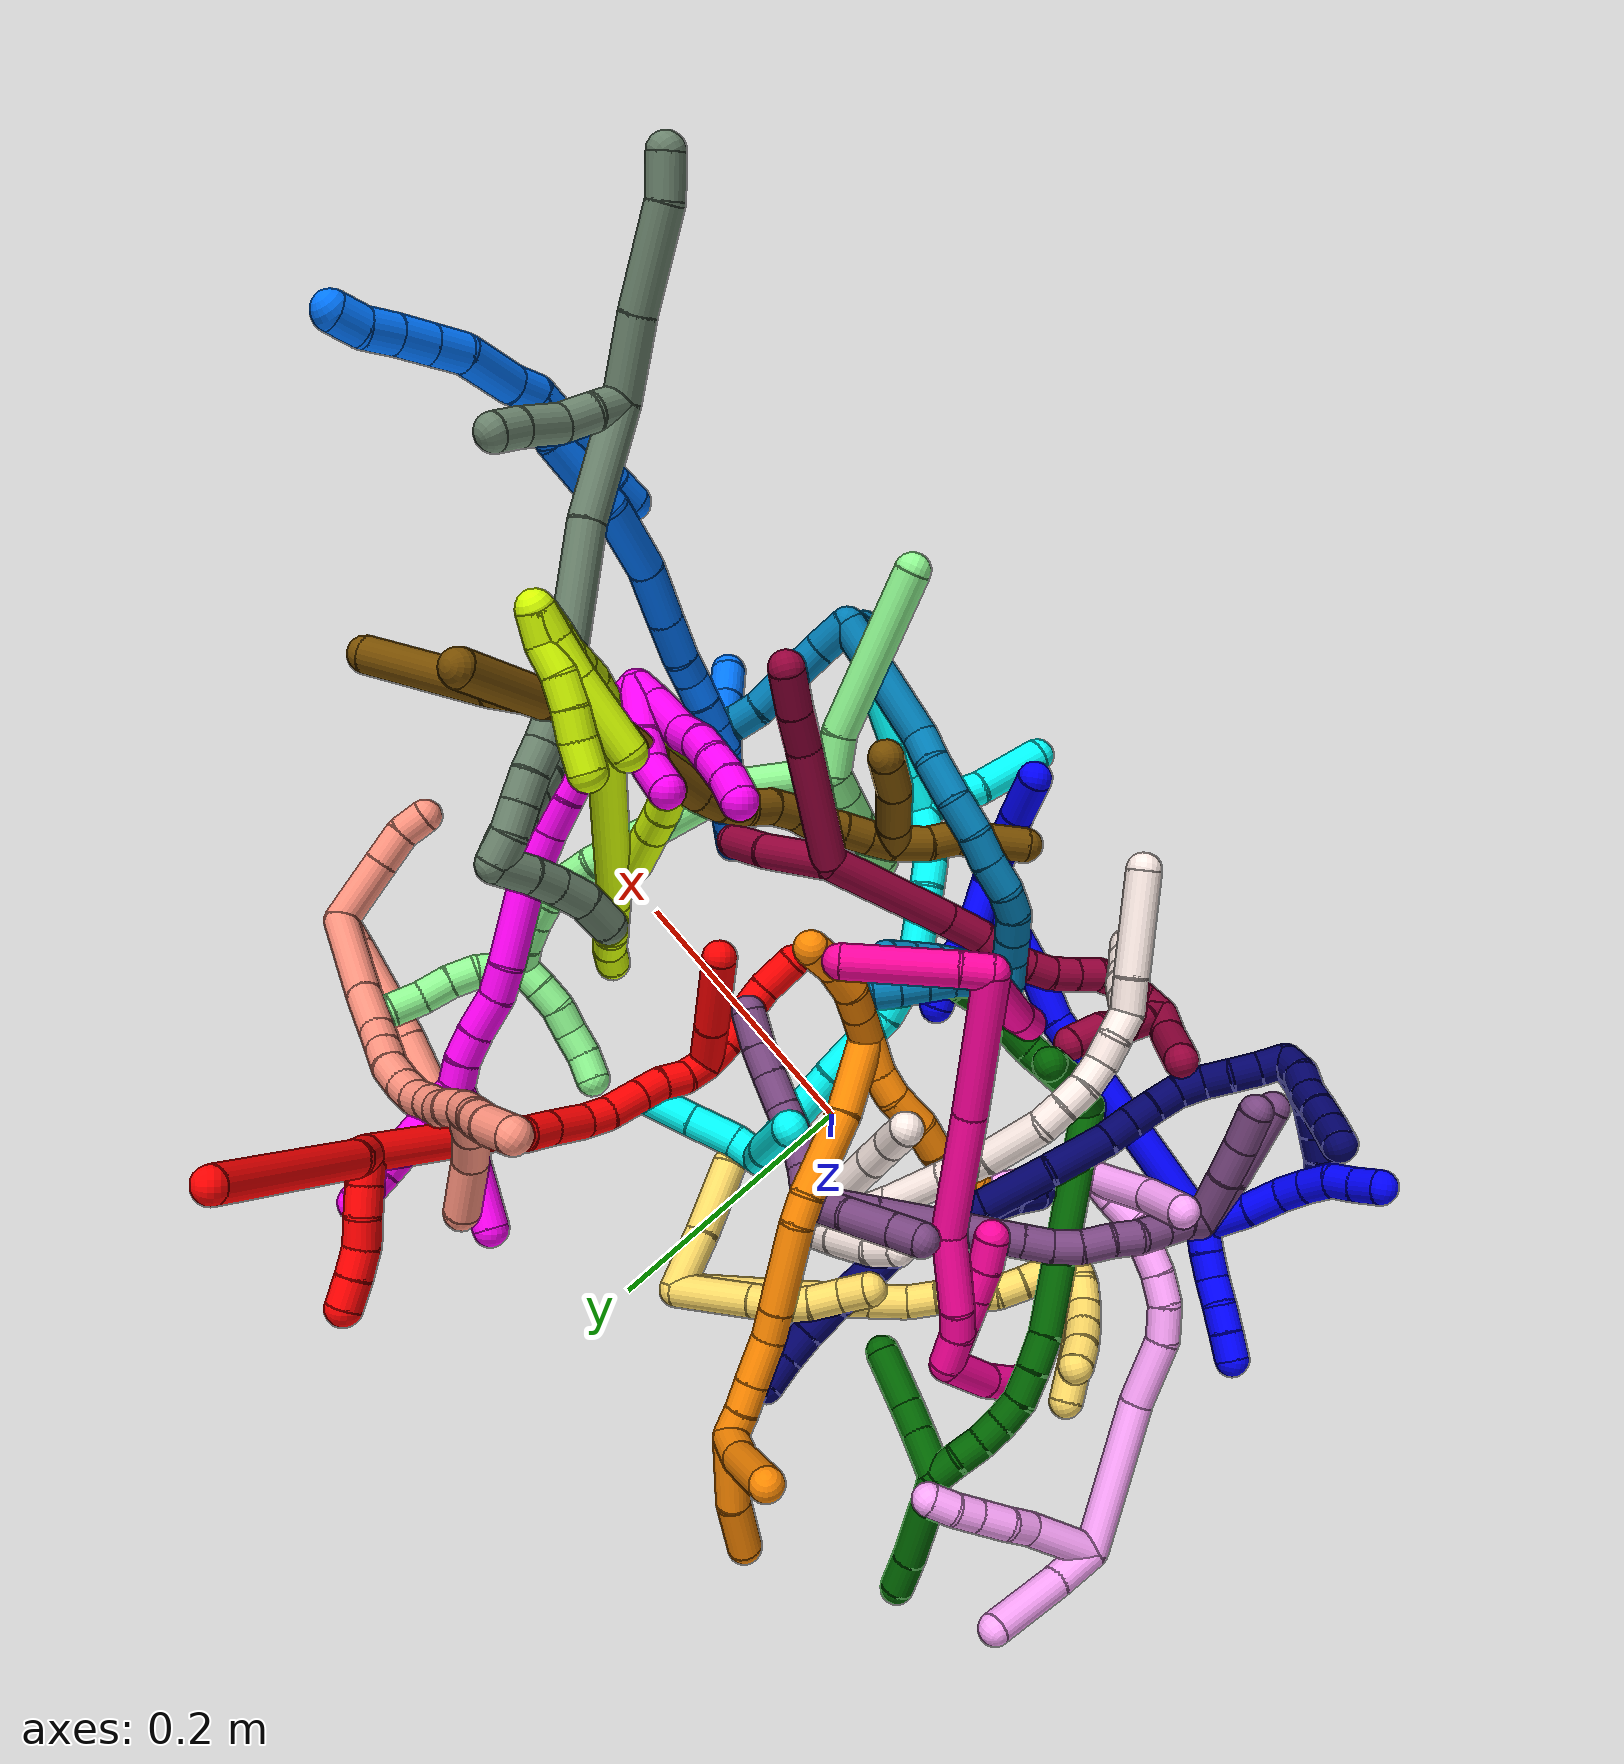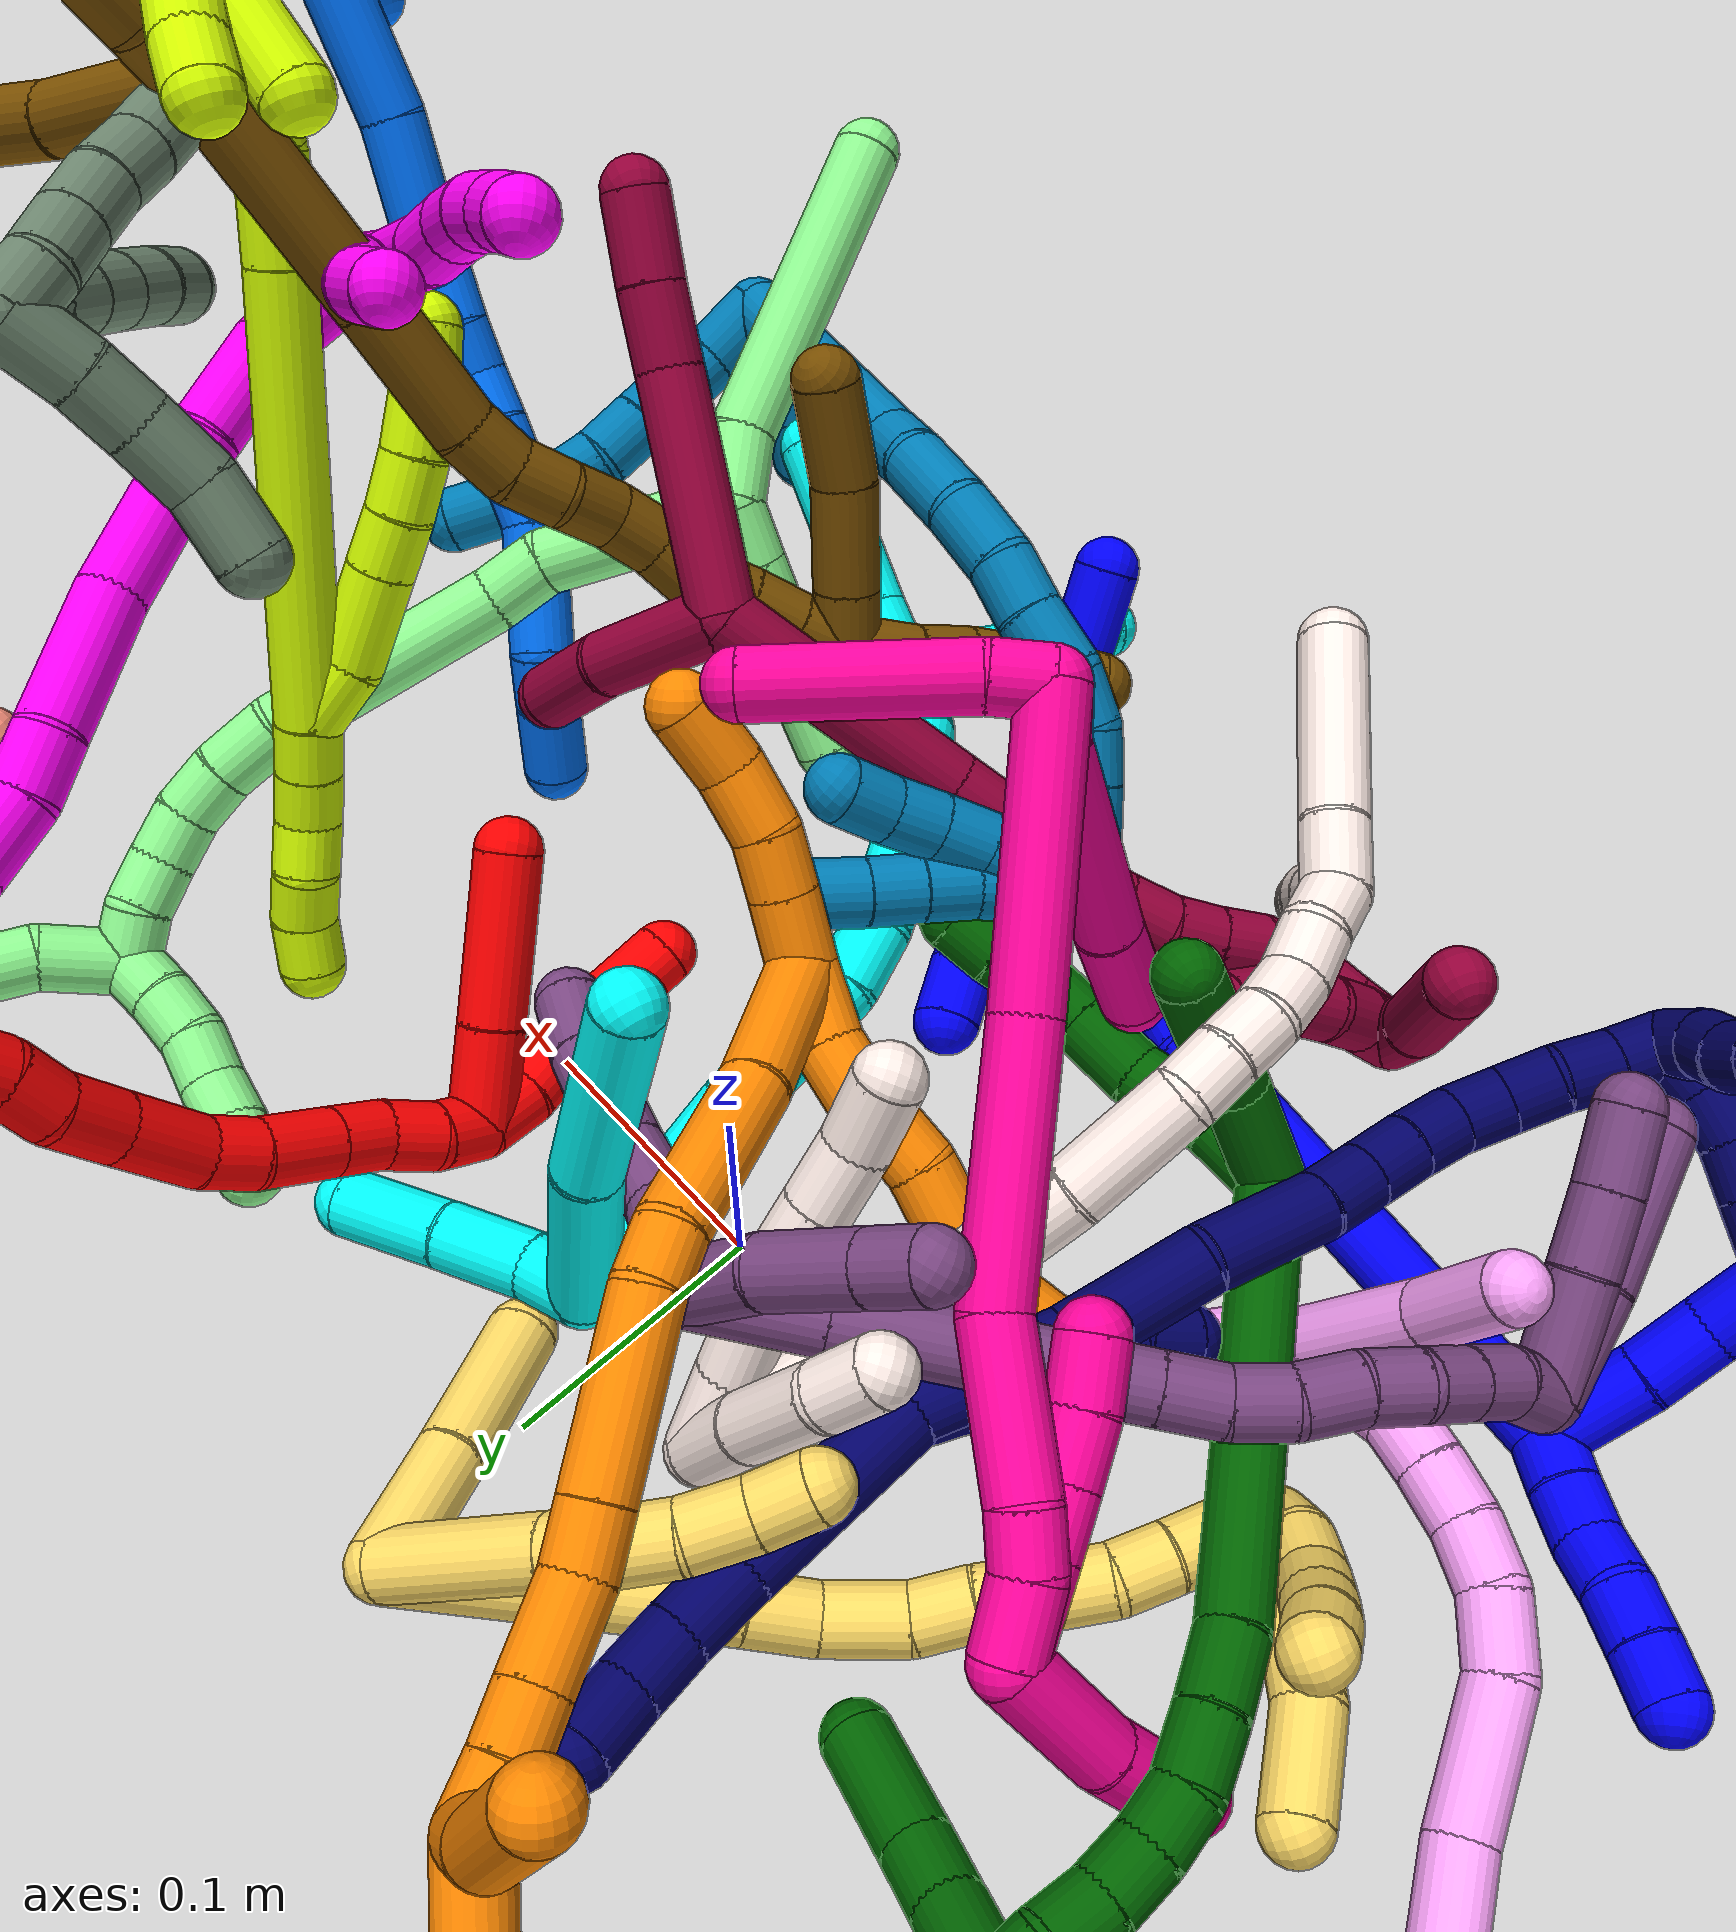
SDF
<sdf version="1.7">
 <world name="default">
  <plugin name="TubeGeneratorPlugin" filename="libtube_generator_plugin.so"/>
  <model name="photoneo_s_sensor">
   <static>1</static>
   <pose>0 0 2 1.57079 1.57079 3.14159</pose>
   <link name="link">
    <inertial><mass>0.1</mass></inertial>
    <sensor name="sensor" type="depth">
     <update_rate>30</update_rate>
     <camera>
      <horizontal_fov>1.22</horizontal_fov>
      <image><width>1920</width><height>1200</height><format>B8G8R8</format></image>
      <clip><near>0.1</near><far>4</far></clip>
      <depth_camera><output>points</output></depth_camera>
     </camera>
     <plugin name="camera_plugin" filename="libgazebo_ros_depth_camera.so">
      <baseline>0.2</baseline>
      <alwaysOn>1</alwaysOn>
      <updateRate>0.0</updateRate>
      <cameraName>camera_ir</cameraName>
      <imageTopicName>/camera/color/image_raw</imageTopicName>
      <cameraInfoTopicName>/camera/color/camera_info</cameraInfoTopicName>
      <depthImageTopicName>/camera/depth/image_raw</depthImageTopicName>
      <depthImageCameraInfoTopicName>/camera/depth/camera_info</depthImageCameraInfoTopicName>
      <pointCloudTopicName>/camera/depth/points</pointCloudTopicName>
      <frameName>fr_optical</frameName>
      <pointCloudCutoff>0.1</pointCloudCutoff>
      <pointCloudCutoffMax>2.0</pointCloudCutoffMax>
      <distortionK1>0</distortionK1>
      <distortionK2>0</distortionK2>
      <distortionK3>0</distortionK3>
      <distortionT1>0</distortionT1>
      <distortionT2>0</distortionT2>
      <CxPrime>0</CxPrime>
      <Cx>0</Cx>
      <Cy>0</Cy>
      <focalLength>0</focalLength>
      <hackBaseline>0</hackBaseline>
     </plugin>
    </sensor>
   </link>
  </model>
  <gravity>0 0 -9.8</gravity>
  <magnetic_field>6e-06 2.3e-05 -4.2e-05</magnetic_field>
  <atmosphere type="adiabatic"/>
  <physics name="default_physics" default="0" type="ode">
   <max_step_size>0.003</max_step_size>
   <real_time_factor>1</real_time_factor>
   <real_time_update_rate>1000</real_time_update_rate>
   <max_contacts>10000</max_contacts>
   <ode>
    <solver>
     <type>quick</type>
     <iters>100</iters>
     <sor>1.3</sor>
     <use_dynamic_moi_rescaling>0</use_dynamic_moi_rescaling>
    </solver>
    <constraints>
     <contact_max_correcting_vel>0</contact_max_correcting_vel>
     <contact_surface_layer>0.001</contact_surface_layer>
     <cfm>0</cfm>
     <erp>0.2</erp>
    </constraints>
   </ode>
  </physics>
  <scene><ambient>0.4 0.4 0.4 1</ambient><background>0.7 0.7 0.7 1</background><shadows>0</shadows></scene>
  <audio><device>default</device></audio>
  <spherical_coordinates>
   <surface_model>EARTH_WGS84</surface_model>
   <latitude_deg>0</latitude_deg>
   <longitude_deg>0</longitude_deg>
   <elevation>0</elevation>
   <heading_deg>0</heading_deg>
  </spherical_coordinates>
  <model name="bin">
   <static>1</static>
   <link name="bottom">
    <collision name="collision-bottom">
     <pose>0 0 -0.01 0 -0 0</pose>
     <geometry><box><size>0.8 0.6 0.02</size></box></geometry>
     <surface>
      <friction><ode><mu>100</mu><mu2>100</mu2></ode></friction>
      <contact><collide_bitmask>65535</collide_bitmask></contact>
     </surface>
    </collision>
   </link>
   <link name="west_wall">
    <collision name="collision-west_wall">
     <pose>-0.41 0 0.1 0 -0 0</pose>
     <geometry><box><size>0.02 0.6 0.2</size></box></geometry>
     <surface>
      <friction><ode><mu>100</mu><mu2>100</mu2></ode></friction>
      <contact><collide_bitmask>65535</collide_bitmask></contact>
     </surface>
    </collision>
   </link>
   <link name="east_wall">
    <collision name="collision-east_wall">
     <pose>0.41 0 0.1 0 -0 0</pose>
     <geometry><box><size>0.02 0.6 0.2</size></box></geometry>
     <surface>
      <friction><ode><mu>100</mu><mu2>100</mu2></ode></friction>
      <contact><collide_bitmask>65535</collide_bitmask></contact>
     </surface>
    </collision>
   </link>
   <link name="south_wall">
    <collision name="collision-south_wall">
     <pose>0 -0.31 0.1 0 -0 0</pose>
     <geometry><box><size>0.8 0.02 0.2</size></box></geometry>
     <surface>
      <friction><ode><mu>100</mu><mu2>100</mu2></ode></friction>
      <contact><collide_bitmask>65535</collide_bitmask></contact>
     </surface>
    </collision>
   </link>
   <link name="north_wall">
    <collision name="collision-north_wall">
     <pose>0 0.31 0.1 0 -0 0</pose>
     <geometry><box><size>0.8 0.02 0.2</size></box></geometry>
     <surface>
      <friction><ode><mu>100</mu><mu2>100</mu2></ode></friction>
      <contact><collide_bitmask>65535</collide_bitmask></contact>
     </surface>
    </collision>
   </link>
  </model>
  <model name="1">
   <static>0</static>
   <link name="1">
    <collision name="collision-cylinder-e_1_2_8">
     <pose>-0.004849 0.01581 0.009548 -1.0275 -0.256759 0.145432</pose>
     <geometry><cylinder><radius>0.0125</radius><length>0.038191</length></cylinder></geometry>
     <surface>
      <friction><ode><mu>1.16</mu><mu2>1.16</mu2><slip1>0</slip1><slip2>0</slip2></ode></friction>
      <contact><ode><kp>1e+06</kp><kd>1</kd><max_vel>0</max_vel><min_depth>0.001</min_depth></ode></contact>
     </surface>
    </collision>
    <visual name="visual-cylinder-e_1_2_8">
     <pose>-0.004849 0.01581 0.009548 -1.0275 -0.256759 0.145432</pose>
     <geometry><cylinder><radius>0.0125</radius><length>0.038191</length></cylinder></geometry>
     <material><ambient>0 0 1 1</ambient></material>
    </visual>
    <collision name="collision-cylinder-e_2_8_9">
     <pose>-0.013215 0.042256 0.027252 -0.916616 -0.25656 0.127099</pose>
     <geometry><cylinder><radius>0.0125</radius><length>0.027713</length></cylinder></geometry>
     <surface>
      <friction><ode><mu>1.16</mu><mu2>1.16</mu2><slip1>0</slip1><slip2>0</slip2></ode></friction>
      <contact><ode><kp>1e+06</kp><kd>1</kd><max_vel>0</max_vel><min_depth>0.001</min_depth></ode></contact>
     </surface>
    </collision>
    <visual name="visual-cylinder-e_2_8_9">
     <pose>-0.013215 0.042256 0.027252 -0.916616 -0.25656 0.127099</pose>
     <geometry><cylinder><radius>0.0125</radius><length>0.027713</length></cylinder></geometry>
     <material><ambient>0 0 1 1</ambient></material>
    </visual>
    <collision name="collision-cylinder-e_3_9_10">
     <pose>-0.017216 0.062154 0.040633 -1.05717 -0.045619 0.026645</pose>
     <geometry><cylinder><radius>0.0125</radius><length>0.021292</length></cylinder></geometry>
     <surface>
      <friction><ode><mu>1.16</mu><mu2>1.16</mu2><slip1>0</slip1><slip2>0</slip2></ode></friction>
      <contact><ode><kp>1e+06</kp><kd>1</kd><max_vel>0</max_vel><min_depth>0.001</min_depth></ode></contact>
     </surface>
    </collision>
    <visual name="visual-cylinder-e_3_9_10">
     <pose>-0.017216 0.062154 0.040633 -1.05717 -0.045619 0.026645</pose>
     <geometry><cylinder><radius>0.0125</radius><length>0.021292</length></cylinder></geometry>
     <material><ambient>0 0 1 1</ambient></material>
    </visual>
    <collision name="collision-cylinder-e_4_10_11">
     <pose>-0.01752 0.081551 0.050382 -1.15095 0.016368 -0.010618</pose>
     <geometry><cylinder><radius>0.0125</radius><length>0.022199</length></cylinder></geometry>
     <surface>
      <friction><ode><mu>1.16</mu><mu2>1.16</mu2><slip1>0</slip1><slip2>0</slip2></ode></friction>
      <contact><ode><kp>1e+06</kp><kd>1</kd><max_vel>0</max_vel><min_depth>0.001</min_depth></ode></contact>
     </surface>
    </collision>
    <visual name="visual-cylinder-e_4_10_11">
     <pose>-0.01752 0.081551 0.050382 -1.15095 0.016368 -0.010618</pose>
     <geometry><cylinder><radius>0.0125</radius><length>0.022199</length></cylinder></geometry>
     <material><ambient>0 0 1 1</ambient></material>
    </visual>
    <collision name="collision-cylinder-e_5_11_12">
     <pose>-0.017479 0.101751 0.055641 -1.49795 -0.01391 0.012932</pose>
     <geometry><cylinder><radius>0.0125</radius><length>0.020186</length></cylinder></geometry>
     <surface>
      <friction><ode><mu>1.16</mu><mu2>1.16</mu2><slip1>0</slip1><slip2>0</slip2></ode></friction>
      <contact><ode><kp>1e+06</kp><kd>1</kd><max_vel>0</max_vel><min_depth>0.001</min_depth></ode></contact>
     </surface>
    </collision>
    <visual name="visual-cylinder-e_5_11_12">
     <pose>-0.017479 0.101751 0.055641 -1.49795 -0.01391 0.012932</pose>
     <geometry><cylinder><radius>0.0125</radius><length>0.020186</length></cylinder></geometry>
     <material><ambient>0 0 1 1</ambient></material>
    </visual>
    <collision name="collision-cylinder-e_6_12_6">
     <pose>-0.017171 0.121914 0.057812 -1.42942 0.043931 -0.038123</pose>
     <geometry><cylinder><radius>0.0125</radius><length>0.020419</length></cylinder></geometry>
     <surface>
      <friction><ode><mu>1.16</mu><mu2>1.16</mu2><slip1>0</slip1><slip2>0</slip2></ode></friction>
      <contact><ode><kp>1e+06</kp><kd>1</kd><max_vel>0</max_vel><min_depth>0.001</min_depth></ode></contact>
     </surface>
    </collision>
    <visual name="visual-cylinder-e_6_12_6">
     <pose>-0.017171 0.121914 0.057812 -1.42942 0.043931 -0.038123</pose>
     <geometry><cylinder><radius>0.0125</radius><length>0.020419</length></cylinder></geometry>
     <material><ambient>0 0 1 1</ambient></material>
    </visual>
    <collision name="collision-cylinder-e_1_2_13">
     <pose>-0.000308 0.003693 -0.009288 -2.76315 -0.030836 0.160679</pose>
     <geometry><cylinder><radius>0.0125</radius><length>0.02</length></cylinder></geometry>
     <surface>
      <friction><ode><mu>1.16</mu><mu2>1.16</mu2><slip1>0</slip1><slip2>0</slip2></ode></friction>
      <contact><ode><kp>1e+06</kp><kd>1</kd><max_vel>0</max_vel><min_depth>0.001</min_depth></ode></contact>
     </surface>
    </collision>
    <visual name="visual-cylinder-e_1_2_13">
     <pose>-0.000308 0.003693 -0.009288 -2.76315 -0.030836 0.160679</pose>
     <geometry><cylinder><radius>0.0125</radius><length>0.02</length></cylinder></geometry>
     <material><ambient>0 0 1 1</ambient></material>
    </visual>
    <collision name="collision-cylinder-e_2_13_14">
     <pose>-0.001798 0.011089 -0.02779 -2.75945 -0.118448 0.59488</pose>
     <geometry><cylinder><radius>0.0125</radius><length>0.02</length></cylinder></geometry>
     <surface>
      <friction><ode><mu>1.16</mu><mu2>1.16</mu2><slip1>0</slip1><slip2>0</slip2></ode></friction>
      <contact><ode><kp>1e+06</kp><kd>1</kd><max_vel>0</max_vel><min_depth>0.001</min_depth></ode></contact>
     </surface>
    </collision>
    <visual name="visual-cylinder-e_2_13_14">
     <pose>-0.001798 0.011089 -0.02779 -2.75945 -0.118448 0.59488</pose>
     <geometry><cylinder><radius>0.0125</radius><length>0.02</length></cylinder></geometry>
     <material><ambient>0 0 1 1</ambient></material>
    </visual>
    <collision name="collision-cylinder-e_3_14_15">
     <pose>-0.001998 0.020477 -0.045171 -2.53358 0.098384 -0.31131</pose>
     <geometry><cylinder><radius>0.0125</radius><length>0.02</length></cylinder></geometry>
     <surface>
      <friction><ode><mu>1.16</mu><mu2>1.16</mu2><slip1>0</slip1><slip2>0</slip2></ode></friction>
      <contact><ode><kp>1e+06</kp><kd>1</kd><max_vel>0</max_vel><min_depth>0.001</min_depth></ode></contact>
     </surface>
    </collision>
    <visual name="visual-cylinder-e_3_14_15">
     <pose>-0.001998 0.020477 -0.045171 -2.53358 0.098384 -0.31131</pose>
     <geometry><cylinder><radius>0.0125</radius><length>0.02</length></cylinder></geometry>
     <material><ambient>0 0 1 1</ambient></material>
    </visual>
    <collision name="collision-cylinder-e_4_15_16">
     <pose>-0.001767 0.030452 -0.062341 -2.69681 -0.075194 0.329661</pose>
     <geometry><cylinder><radius>0.0125</radius><length>0.02</length></cylinder></geometry>
     <surface>
      <friction><ode><mu>1.16</mu><mu2>1.16</mu2><slip1>0</slip1><slip2>0</slip2></ode></friction>
      <contact><ode><kp>1e+06</kp><kd>1</kd><max_vel>0</max_vel><min_depth>0.001</min_depth></ode></contact>
     </surface>
    </collision>
    <visual name="visual-cylinder-e_4_15_16">
     <pose>-0.001767 0.030452 -0.062341 -2.69681 -0.075194 0.329661</pose>
     <geometry><cylinder><radius>0.0125</radius><length>0.02</length></cylinder></geometry>
     <material><ambient>0 0 1 1</ambient></material>
    </visual>
    <collision name="collision-cylinder-e_5_16_5">
     <pose>-0.003749 0.038541 -0.080511 -2.74877 -0.123391 0.602049</pose>
     <geometry><cylinder><radius>0.0125</radius><length>0.02</length></cylinder></geometry>
     <surface>
      <friction><ode><mu>1.16</mu><mu2>1.16</mu2><slip1>0</slip1><slip2>0</slip2></ode></friction>
      <contact><ode><kp>1e+06</kp><kd>1</kd><max_vel>0</max_vel><min_depth>0.001</min_depth></ode></contact>
     </surface>
    </collision>
    <visual name="visual-cylinder-e_5_16_5">
     <pose>-0.003749 0.038541 -0.080511 -2.74877 -0.123391 0.602049</pose>
     <geometry><cylinder><radius>0.0125</radius><length>0.02</length></cylinder></geometry>
     <material><ambient>0 0 1 1</ambient></material>
    </visual>
    <collision name="collision-cylinder-e_1_2_17">
     <pose>0.046159 -0.046211 0.066437 0.60774 0.51835 0.165904</pose>
     <geometry><cylinder><radius>0.0125</radius><length>0.186333</length></cylinder></geometry>
     <surface>
      <friction><ode><mu>1.16</mu><mu2>1.16</mu2><slip1>0</slip1><slip2>0</slip2></ode></friction>
      <contact><ode><kp>1e+06</kp><kd>1</kd><max_vel>0</max_vel><min_depth>0.001</min_depth></ode></contact>
     </surface>
    </collision>
    <visual name="visual-cylinder-e_1_2_17">
     <pose>0.046159 -0.046211 0.066437 0.60774 0.51835 0.165904</pose>
     <geometry><cylinder><radius>0.0125</radius><length>0.186333</length></cylinder></geometry>
     <material><ambient>0 0 1 1</ambient></material>
    </visual>
    <collision name="collision-cylinder-e_2_17_18">
     <pose>0.098671 -0.099491 0.148194 0.432341 0.360128 0.079908</pose>
     <geometry><cylinder><radius>0.0125</radius><length>0.036056</length></cylinder></geometry>
     <surface>
      <friction><ode><mu>1.16</mu><mu2>1.16</mu2><slip1>0</slip1><slip2>0</slip2></ode></friction>
      <contact><ode><kp>1e+06</kp><kd>1</kd><max_vel>0</max_vel><min_depth>0.001</min_depth></ode></contact>
     </surface>
    </collision>
    <visual name="visual-cylinder-e_2_17_18">
     <pose>0.098671 -0.099491 0.148194 0.432341 0.360128 0.079908</pose>
     <geometry><cylinder><radius>0.0125</radius><length>0.036056</length></cylinder></geometry>
     <material><ambient>0 0 1 1</ambient></material>
    </visual>
    <collision name="collision-cylinder-e_3_18_19">
     <pose>0.110609 -0.115534 0.176759 0.595403 0.335797 0.103915</pose>
     <geometry><cylinder><radius>0.0125</radius><length>0.033893</length></cylinder></geometry>
     <surface>
      <friction><ode><mu>1.16</mu><mu2>1.16</mu2><slip1>0</slip1><slip2>0</slip2></ode></friction>
      <contact><ode><kp>1e+06</kp><kd>1</kd><max_vel>0</max_vel><min_depth>0.001</min_depth></ode></contact>
     </surface>
    </collision>
    <visual name="visual-cylinder-e_3_18_19">
     <pose>0.110609 -0.115534 0.176759 0.595403 0.335797 0.103915</pose>
     <geometry><cylinder><radius>0.0125</radius><length>0.033893</length></cylinder></geometry>
     <material><ambient>0 0 1 1</ambient></material>
    </visual>
    <collision name="collision-cylinder-e_4_19_20">
     <pose>0.120719 -0.129348 0.199184 0.485307 0.411324 0.103184</pose>
     <geometry><cylinder><radius>0.0125</radius><length>0.022641</length></cylinder></geometry>
     <surface>
      <friction><ode><mu>1.16</mu><mu2>1.16</mu2><slip1>0</slip1><slip2>0</slip2></ode></friction>
      <contact><ode><kp>1e+06</kp><kd>1</kd><max_vel>0</max_vel><min_depth>0.001</min_depth></ode></contact>
     </surface>
    </collision>
    <visual name="visual-cylinder-e_4_19_20">
     <pose>0.120719 -0.129348 0.199184 0.485307 0.411324 0.103184</pose>
     <geometry><cylinder><radius>0.0125</radius><length>0.022641</length></cylinder></geometry>
     <material><ambient>0 0 1 1</ambient></material>
    </visual>
    <collision name="collision-cylinder-e_5_20_1">
     <pose>0.129461 -0.138693 0.216906 0.485306 0.411566 0.103246</pose>
     <geometry><cylinder><radius>0.0125</radius><length>0.021076</length></cylinder></geometry>
     <surface>
      <friction><ode><mu>1.16</mu><mu2>1.16</mu2><slip1>0</slip1><slip2>0</slip2></ode></friction>
      <contact><ode><kp>1e+06</kp><kd>1</kd><max_vel>0</max_vel><min_depth>0.001</min_depth></ode></contact>
     </surface>
    </collision>
    <visual name="visual-cylinder-e_5_20_1">
     <pose>0.129461 -0.138693 0.216906 0.485306 0.411566 0.103246</pose>
     <geometry><cylinder><radius>0.0125</radius><length>0.021076</length></cylinder></geometry>
     <material><ambient>0 0 1 1</ambient></material>
    </visual>
    <collision name="collision-cylinder-e_1_1_21">
     <pose>0.137461 -0.142969 0.209029 -3.12758 0.226478 -3.01857</pose>
     <geometry><cylinder><radius>0.0125</radius><length>0.033704</length></cylinder></geometry>
     <surface>
      <friction><ode><mu>1.16</mu><mu2>1.16</mu2><slip1>0</slip1><slip2>0</slip2></ode></friction>
      <contact><ode><kp>1e+06</kp><kd>1</kd><max_vel>0</max_vel><min_depth>0.001</min_depth></ode></contact>
     </surface>
    </collision>
    <visual name="visual-cylinder-e_1_1_21">
     <pose>0.137461 -0.142969 0.209029 -3.12758 0.226478 -3.01857</pose>
     <geometry><cylinder><radius>0.0125</radius><length>0.033704</length></cylinder></geometry>
     <material><ambient>0 0 1 1</ambient></material>
    </visual>
    <collision name="collision-cylinder-e_2_21_22">
     <pose>0.148317 -0.145775 0.172376 2.99261 0.332835 2.30541</pose>
     <geometry><cylinder><radius>0.0125</radius><length>0.043293</length></cylinder></geometry>
     <surface>
      <friction><ode><mu>1.16</mu><mu2>1.16</mu2><slip1>0</slip1><slip2>0</slip2></ode></friction>
      <contact><ode><kp>1e+06</kp><kd>1</kd><max_vel>0</max_vel><min_depth>0.001</min_depth></ode></contact>
     </surface>
    </collision>
    <visual name="visual-cylinder-e_2_21_22">
     <pose>0.148317 -0.145775 0.172376 2.99261 0.332835 2.30541</pose>
     <geometry><cylinder><radius>0.0125</radius><length>0.043293</length></cylinder></geometry>
     <material><ambient>0 0 1 1</ambient></material>
    </visual>
    <collision name="collision-cylinder-e_3_22_4">
     <pose>0.156124 -0.150819 0.140843 2.96584 0.063911 0.696104</pose>
     <geometry><cylinder><radius>0.0125</radius><length>0.023003</length></cylinder></geometry>
     <surface>
      <friction><ode><mu>1.16</mu><mu2>1.16</mu2><slip1>0</slip1><slip2>0</slip2></ode></friction>
      <contact><ode><kp>1e+06</kp><kd>1</kd><max_vel>0</max_vel><min_depth>0.001</min_depth></ode></contact>
     </surface>
    </collision>
    <visual name="visual-cylinder-e_3_22_4">
     <pose>0.156124 -0.150819 0.140843 2.96584 0.063911 0.696104</pose>
     <geometry><cylinder><radius>0.0125</radius><length>0.023003</length></cylinder></geometry>
     <material><ambient>0 0 1 1</ambient></material>
    </visual>
    <collision name="collision-cylinder-e_1_1_23">
     <pose>0.142916 -0.125591 0.250948 -0.604321 0.289773 -0.090898</pose>
     <geometry><cylinder><radius>0.0125</radius><length>0.064672</length></cylinder></geometry>
     <surface>
      <friction><ode><mu>1.16</mu><mu2>1.16</mu2><slip1>0</slip1><slip2>0</slip2></ode></friction>
      <contact><ode><kp>1e+06</kp><kd>1</kd><max_vel>0</max_vel><min_depth>0.001</min_depth></ode></contact>
     </surface>
    </collision>
    <visual name="visual-cylinder-e_1_1_23">
     <pose>0.142916 -0.125591 0.250948 -0.604321 0.289773 -0.090898</pose>
     <geometry><cylinder><radius>0.0125</radius><length>0.064672</length></cylinder></geometry>
     <material><ambient>0 0 1 1</ambient></material>
    </visual>
    <collision name="collision-cylinder-e_2_23_3">
     <pose>0.157095 -0.09778 0.289994 -0.645575 0.283389 -0.095357</pose>
     <geometry><cylinder><radius>0.0125</radius><length>0.035328</length></cylinder></geometry>
     <surface>
      <friction><ode><mu>1.16</mu><mu2>1.16</mu2><slip1>0</slip1><slip2>0</slip2></ode></friction>
      <contact><ode><kp>1e+06</kp><kd>1</kd><max_vel>0</max_vel><min_depth>0.001</min_depth></ode></contact>
     </surface>
    </collision>
    <visual name="visual-cylinder-e_2_23_3">
     <pose>0.157095 -0.09778 0.289994 -0.645575 0.283389 -0.095357</pose>
     <geometry><cylinder><radius>0.0125</radius><length>0.035328</length></cylinder></geometry>
     <material><ambient>0 0 1 1</ambient></material>
    </visual>
    <collision name="collision-sphere-3">
     <pose>0.162034 -0.087576 0.303541 0 -0 0</pose>
     <geometry><sphere><radius>0.0125</radius></sphere></geometry>
     <surface>
      <friction><ode><mu>1.16</mu><mu2>1.16</mu2><slip1>0</slip1><slip2>0</slip2></ode></friction>
      <contact><ode><kp>1e+06</kp><kd>1</kd><max_vel>0</max_vel><min_depth>0.001</min_depth></ode></contact>
     </surface>
    </collision>
    <visual name="visual-sphere-3">
     <pose>0.162034 -0.087576 0.303541 0 -0 0</pose>
     <geometry><sphere><radius>0.0125</radius></sphere></geometry>
     <material><ambient>0 0 1 1</ambient></material>
    </visual>
    <collision name="collision-sphere-23">
     <pose>0.152156 -0.107984 0.276448 0 -0 0</pose>
     <geometry><sphere><radius>0.0125</radius></sphere></geometry>
     <surface>
      <friction><ode><mu>1.16</mu><mu2>1.16</mu2><slip1>0</slip1><slip2>0</slip2></ode></friction>
      <contact><ode><kp>1e+06</kp><kd>1</kd><max_vel>0</max_vel><min_depth>0.001</min_depth></ode></contact>
     </surface>
    </collision>
    <visual name="visual-sphere-23">
     <pose>0.152156 -0.107984 0.276448 0 -0 0</pose>
     <geometry><sphere><radius>0.0125</radius></sphere></geometry>
     <material><ambient>0 0 1 1</ambient></material>
    </visual>
    <collision name="collision-sphere-4">
     <pose>0.156859 -0.152826 0.129542 0 -0 0</pose>
     <geometry><sphere><radius>0.0125</radius></sphere></geometry>
     <surface>
      <friction><ode><mu>1.16</mu><mu2>1.16</mu2><slip1>0</slip1><slip2>0</slip2></ode></friction>
      <contact><ode><kp>1e+06</kp><kd>1</kd><max_vel>0</max_vel><min_depth>0.001</min_depth></ode></contact>
     </surface>
    </collision>
    <visual name="visual-sphere-4">
     <pose>0.156859 -0.152826 0.129542 0 -0 0</pose>
     <geometry><sphere><radius>0.0125</radius></sphere></geometry>
     <material><ambient>0 0 1 1</ambient></material>
    </visual>
    <collision name="collision-sphere-22">
     <pose>0.15539 -0.148812 0.152144 0 -0 0</pose>
     <geometry><sphere><radius>0.0125</radius></sphere></geometry>
     <surface>
      <friction><ode><mu>1.16</mu><mu2>1.16</mu2><slip1>0</slip1><slip2>0</slip2></ode></friction>
      <contact><ode><kp>1e+06</kp><kd>1</kd><max_vel>0</max_vel><min_depth>0.001</min_depth></ode></contact>
     </surface>
    </collision>
    <visual name="visual-sphere-22">
     <pose>0.15539 -0.148812 0.152144 0 -0 0</pose>
     <geometry><sphere><radius>0.0125</radius></sphere></geometry>
     <material><ambient>0 0 1 1</ambient></material>
    </visual>
    <collision name="collision-sphere-21">
     <pose>0.141245 -0.142739 0.192608 0 -0 0</pose>
     <geometry><sphere><radius>0.0125</radius></sphere></geometry>
     <surface>
      <friction><ode><mu>1.16</mu><mu2>1.16</mu2><slip1>0</slip1><slip2>0</slip2></ode></friction>
      <contact><ode><kp>1e+06</kp><kd>1</kd><max_vel>0</max_vel><min_depth>0.001</min_depth></ode></contact>
     </surface>
    </collision>
    <visual name="visual-sphere-21">
     <pose>0.141245 -0.142739 0.192608 0 -0 0</pose>
     <geometry><sphere><radius>0.0125</radius></sphere></geometry>
     <material><ambient>0 0 1 1</ambient></material>
    </visual>
    <collision name="collision-sphere-1">
     <pose>0.133677 -0.143199 0.225449 0 -0 0</pose>
     <geometry><sphere><radius>0.0125</radius></sphere></geometry>
     <surface>
      <friction><ode><mu>1.16</mu><mu2>1.16</mu2><slip1>0</slip1><slip2>0</slip2></ode></friction>
      <contact><ode><kp>1e+06</kp><kd>1</kd><max_vel>0</max_vel><min_depth>0.001</min_depth></ode></contact>
     </surface>
    </collision>
    <visual name="visual-sphere-1">
     <pose>0.133677 -0.143199 0.225449 0 -0 0</pose>
     <geometry><sphere><radius>0.0125</radius></sphere></geometry>
     <material><ambient>0 0 1 1</ambient></material>
    </visual>
    <collision name="collision-sphere-12">
     <pose>-0.017619 0.111816 0.056375 0 -0 0</pose>
     <geometry><sphere><radius>0.0125</radius></sphere></geometry>
     <surface>
      <friction><ode><mu>1.16</mu><mu2>1.16</mu2><slip1>0</slip1><slip2>0</slip2></ode></friction>
      <contact><ode><kp>1e+06</kp><kd>1</kd><max_vel>0</max_vel><min_depth>0.001</min_depth></ode></contact>
     </surface>
    </collision>
    <visual name="visual-sphere-12">
     <pose>-0.017619 0.111816 0.056375 0 -0 0</pose>
     <geometry><sphere><radius>0.0125</radius></sphere></geometry>
     <material><ambient>0 0 1 1</ambient></material>
    </visual>
    <collision name="collision-sphere-11">
     <pose>-0.017338 0.091685 0.054906 0 -0 0</pose>
     <geometry><sphere><radius>0.0125</radius></sphere></geometry>
     <surface>
      <friction><ode><mu>1.16</mu><mu2>1.16</mu2><slip1>0</slip1><slip2>0</slip2></ode></friction>
      <contact><ode><kp>1e+06</kp><kd>1</kd><max_vel>0</max_vel><min_depth>0.001</min_depth></ode></contact>
     </surface>
    </collision>
    <visual name="visual-sphere-11">
     <pose>-0.017338 0.091685 0.054906 0 -0 0</pose>
     <geometry><sphere><radius>0.0125</radius></sphere></geometry>
     <material><ambient>0 0 1 1</ambient></material>
    </visual>
    <collision name="collision-sphere-10">
     <pose>-0.017702 0.071417 0.045858 0 -0 0</pose>
     <geometry><sphere><radius>0.0125</radius></sphere></geometry>
     <surface>
      <friction><ode><mu>1.16</mu><mu2>1.16</mu2><slip1>0</slip1><slip2>0</slip2></ode></friction>
      <contact><ode><kp>1e+06</kp><kd>1</kd><max_vel>0</max_vel><min_depth>0.001</min_depth></ode></contact>
     </surface>
    </collision>
    <visual name="visual-sphere-10">
     <pose>-0.017702 0.071417 0.045858 0 -0 0</pose>
     <geometry><sphere><radius>0.0125</radius></sphere></geometry>
     <material><ambient>0 0 1 1</ambient></material>
    </visual>
    <collision name="collision-sphere-9">
     <pose>-0.016731 0.052892 0.035408 0 -0 0</pose>
     <geometry><sphere><radius>0.0125</radius></sphere></geometry>
     <surface>
      <friction><ode><mu>1.16</mu><mu2>1.16</mu2><slip1>0</slip1><slip2>0</slip2></ode></friction>
      <contact><ode><kp>1e+06</kp><kd>1</kd><max_vel>0</max_vel><min_depth>0.001</min_depth></ode></contact>
     </surface>
    </collision>
    <visual name="visual-sphere-9">
     <pose>-0.016731 0.052892 0.035408 0 -0 0</pose>
     <geometry><sphere><radius>0.0125</radius></sphere></geometry>
     <material><ambient>0 0 1 1</ambient></material>
    </visual>
    <collision name="collision-sphere-2">
     <geometry><sphere><radius>0.0125</radius></sphere></geometry>
     <surface>
      <friction><ode><mu>1.16</mu><mu2>1.16</mu2><slip1>0</slip1><slip2>0</slip2></ode></friction>
      <contact><ode><kp>1e+06</kp><kd>1</kd><max_vel>0</max_vel><min_depth>0.001</min_depth></ode></contact>
     </surface>
    </collision>
    <visual name="visual-sphere-2">
     <geometry><sphere><radius>0.0125</radius></sphere></geometry>
     <material><ambient>0 0 1 1</ambient></material>
    </visual>
    <collision name="collision-sphere-19">
     <pose>0.116193 -0.124507 0.190006 0 -0 0</pose>
     <geometry><sphere><radius>0.0125</radius></sphere></geometry>
     <surface>
      <friction><ode><mu>1.16</mu><mu2>1.16</mu2><slip1>0</slip1><slip2>0</slip2></ode></friction>
      <contact><ode><kp>1e+06</kp><kd>1</kd><max_vel>0</max_vel><min_depth>0.001</min_depth></ode></contact>
     </surface>
    </collision>
    <visual name="visual-sphere-19">
     <pose>0.116193 -0.124507 0.190006 0 -0 0</pose>
     <geometry><sphere><radius>0.0125</radius></sphere></geometry>
     <material><ambient>0 0 1 1</ambient></material>
    </visual>
    <collision name="collision-sphere-8">
     <pose>-0.009698 0.03162 0.019096 0 -0 0</pose>
     <geometry><sphere><radius>0.0125</radius></sphere></geometry>
     <surface>
      <friction><ode><mu>1.16</mu><mu2>1.16</mu2><slip1>0</slip1><slip2>0</slip2></ode></friction>
      <contact><ode><kp>1e+06</kp><kd>1</kd><max_vel>0</max_vel><min_depth>0.001</min_depth></ode></contact>
     </surface>
    </collision>
    <visual name="visual-sphere-8">
     <pose>-0.009698 0.03162 0.019096 0 -0 0</pose>
     <geometry><sphere><radius>0.0125</radius></sphere></geometry>
     <material><ambient>0 0 1 1</ambient></material>
    </visual>
    <collision name="collision-sphere-6">
     <pose>-0.016722 0.132012 0.059249 0 -0 0</pose>
     <geometry><sphere><radius>0.0125</radius></sphere></geometry>
     <surface>
      <friction><ode><mu>1.16</mu><mu2>1.16</mu2><slip1>0</slip1><slip2>0</slip2></ode></friction>
      <contact><ode><kp>1e+06</kp><kd>1</kd><max_vel>0</max_vel><min_depth>0.001</min_depth></ode></contact>
     </surface>
    </collision>
    <visual name="visual-sphere-6">
     <pose>-0.016722 0.132012 0.059249 0 -0 0</pose>
     <geometry><sphere><radius>0.0125</radius></sphere></geometry>
     <material><ambient>0 0 1 1</ambient></material>
    </visual>
    <collision name="collision-sphere-13">
     <pose>-0.000617 0.007386 -0.018576 0 -0 0</pose>
     <geometry><sphere><radius>0.0125</radius></sphere></geometry>
     <surface>
      <friction><ode><mu>1.16</mu><mu2>1.16</mu2><slip1>0</slip1><slip2>0</slip2></ode></friction>
      <contact><ode><kp>1e+06</kp><kd>1</kd><max_vel>0</max_vel><min_depth>0.001</min_depth></ode></contact>
     </surface>
    </collision>
    <visual name="visual-sphere-13">
     <pose>-0.000617 0.007386 -0.018576 0 -0 0</pose>
     <geometry><sphere><radius>0.0125</radius></sphere></geometry>
     <material><ambient>0 0 1 1</ambient></material>
    </visual>
    <collision name="collision-sphere-14">
     <pose>-0.00298 0.014792 -0.037003 0 -0 0</pose>
     <geometry><sphere><radius>0.0125</radius></sphere></geometry>
     <surface>
      <friction><ode><mu>1.16</mu><mu2>1.16</mu2><slip1>0</slip1><slip2>0</slip2></ode></friction>
      <contact><ode><kp>1e+06</kp><kd>1</kd><max_vel>0</max_vel><min_depth>0.001</min_depth></ode></contact>
     </surface>
    </collision>
    <visual name="visual-sphere-14">
     <pose>-0.00298 0.014792 -0.037003 0 -0 0</pose>
     <geometry><sphere><radius>0.0125</radius></sphere></geometry>
     <material><ambient>0 0 1 1</ambient></material>
    </visual>
    <collision name="collision-sphere-15">
     <pose>-0.001016 0.026161 -0.05334 0 -0 0</pose>
     <geometry><sphere><radius>0.0125</radius></sphere></geometry>
     <surface>
      <friction><ode><mu>1.16</mu><mu2>1.16</mu2><slip1>0</slip1><slip2>0</slip2></ode></friction>
      <contact><ode><kp>1e+06</kp><kd>1</kd><max_vel>0</max_vel><min_depth>0.001</min_depth></ode></contact>
     </surface>
    </collision>
    <visual name="visual-sphere-15">
     <pose>-0.001016 0.026161 -0.05334 0 -0 0</pose>
     <geometry><sphere><radius>0.0125</radius></sphere></geometry>
     <material><ambient>0 0 1 1</ambient></material>
    </visual>
    <collision name="collision-sphere-16">
     <pose>-0.002518 0.034742 -0.071343 0 -0 0</pose>
     <geometry><sphere><radius>0.0125</radius></sphere></geometry>
     <surface>
      <friction><ode><mu>1.16</mu><mu2>1.16</mu2><slip1>0</slip1><slip2>0</slip2></ode></friction>
      <contact><ode><kp>1e+06</kp><kd>1</kd><max_vel>0</max_vel><min_depth>0.001</min_depth></ode></contact>
     </surface>
    </collision>
    <visual name="visual-sphere-16">
     <pose>-0.002518 0.034742 -0.071343 0 -0 0</pose>
     <geometry><sphere><radius>0.0125</radius></sphere></geometry>
     <material><ambient>0 0 1 1</ambient></material>
    </visual>
    <collision name="collision-sphere-5">
     <pose>-0.00498 0.04234 -0.089679 0 -0 0</pose>
     <geometry><sphere><radius>0.0125</radius></sphere></geometry>
     <surface>
      <friction><ode><mu>1.16</mu><mu2>1.16</mu2><slip1>0</slip1><slip2>0</slip2></ode></friction>
      <contact><ode><kp>1e+06</kp><kd>1</kd><max_vel>0</max_vel><min_depth>0.001</min_depth></ode></contact>
     </surface>
    </collision>
    <visual name="visual-sphere-5">
     <pose>-0.00498 0.04234 -0.089679 0 -0 0</pose>
     <geometry><sphere><radius>0.0125</radius></sphere></geometry>
     <material><ambient>0 0 1 1</ambient></material>
    </visual>
    <collision name="collision-sphere-17">
     <pose>0.092318 -0.092422 0.132874 0 -0 0</pose>
     <geometry><sphere><radius>0.0125</radius></sphere></geometry>
     <surface>
      <friction><ode><mu>1.16</mu><mu2>1.16</mu2><slip1>0</slip1><slip2>0</slip2></ode></friction>
      <contact><ode><kp>1e+06</kp><kd>1</kd><max_vel>0</max_vel><min_depth>0.001</min_depth></ode></contact>
     </surface>
    </collision>
    <visual name="visual-sphere-17">
     <pose>0.092318 -0.092422 0.132874 0 -0 0</pose>
     <geometry><sphere><radius>0.0125</radius></sphere></geometry>
     <material><ambient>0 0 1 1</ambient></material>
    </visual>
    <collision name="collision-sphere-18">
     <pose>0.105024 -0.10656 0.163513 0 -0 0</pose>
     <geometry><sphere><radius>0.0125</radius></sphere></geometry>
     <surface>
      <friction><ode><mu>1.16</mu><mu2>1.16</mu2><slip1>0</slip1><slip2>0</slip2></ode></friction>
      <contact><ode><kp>1e+06</kp><kd>1</kd><max_vel>0</max_vel><min_depth>0.001</min_depth></ode></contact>
     </surface>
    </collision>
    <visual name="visual-sphere-18">
     <pose>0.105024 -0.10656 0.163513 0 -0 0</pose>
     <geometry><sphere><radius>0.0125</radius></sphere></geometry>
     <material><ambient>0 0 1 1</ambient></material>
    </visual>
    <collision name="collision-sphere-20">
     <pose>0.125245 -0.134188 0.208363 0 -0 0</pose>
     <geometry><sphere><radius>0.0125</radius></sphere></geometry>
     <surface>
      <friction><ode><mu>1.16</mu><mu2>1.16</mu2><slip1>0</slip1><slip2>0</slip2></ode></friction>
      <contact><ode><kp>1e+06</kp><kd>1</kd><max_vel>0</max_vel><min_depth>0.001</min_depth></ode></contact>
     </surface>
    </collision>
    <visual name="visual-sphere-20">
     <pose>0.125245 -0.134188 0.208363 0 -0 0</pose>
     <geometry><sphere><radius>0.0125</radius></sphere></geometry>
     <material><ambient>0 0 1 1</ambient></material>
    </visual>
    <inertial>
     <pose>0.064806 -0.048805 0.103896 0 -0 0</pose>
     <mass>0.75</mass>
     <inertia>
      <ixx>0.000622</ixx>
      <ixy>0</ixy>
      <ixz>0</ixz>
      <iyy>0.000608</iyy>
      <iyz>0</iyz>
      <izz>-2.6e-05</izz>
     </inertia>
    </inertial>
   </link>
   <pose>-0.239273 -0.154409 0.012429 1.48424 -0.747727 0.762223</pose>
  </model>
  <model name="2">
   <static>0</static>
   <link name="2">
    <collision name="collision-cylinder-e_1_2_8">
     <pose>-0.006278 0.005696 0.005312 -0.820234 -0.678414 0.30444</pose>
     <geometry><cylinder><radius>0.0125</radius><length>0.020007</length></cylinder></geometry>
     <surface>
      <friction><ode><mu>1.16</mu><mu2>1.16</mu2><slip1>0</slip1><slip2>0</slip2></ode></friction>
      <contact><ode><kp>1e+06</kp><kd>1</kd><max_vel>0</max_vel><min_depth>0.001</min_depth></ode></contact>
     </surface>
    </collision>
    <visual name="visual-cylinder-e_1_2_8">
     <pose>-0.006278 0.005696 0.005312 -0.820234 -0.678414 0.30444</pose>
     <geometry><cylinder><radius>0.0125</radius><length>0.020007</length></cylinder></geometry>
     <material><ambient>1 0 0 1</ambient></material>
    </visual>
    <collision name="collision-cylinder-e_2_8_6">
     <pose>-0.044353 0.038367 0.060482 -0.495955 -0.511193 0.13213</pose>
     <geometry><cylinder><radius>0.0125</radius><length>0.129993</length></cylinder></geometry>
     <surface>
      <friction><ode><mu>1.16</mu><mu2>1.16</mu2><slip1>0</slip1><slip2>0</slip2></ode></friction>
      <contact><ode><kp>1e+06</kp><kd>1</kd><max_vel>0</max_vel><min_depth>0.001</min_depth></ode></contact>
     </surface>
    </collision>
    <visual name="visual-cylinder-e_2_8_6">
     <pose>-0.044353 0.038367 0.060482 -0.495955 -0.511193 0.13213</pose>
     <geometry><cylinder><radius>0.0125</radius><length>0.129993</length></cylinder></geometry>
     <material><ambient>1 0 0 1</ambient></material>
    </visual>
    <collision name="collision-cylinder-e_1_2_9">
     <pose>0.005971 0.008007 0.000493 -1.50935 0.639873 -0.604059</pose>
     <geometry><cylinder><radius>0.0125</radius><length>0.02</length></cylinder></geometry>
     <surface>
      <friction><ode><mu>1.16</mu><mu2>1.16</mu2><slip1>0</slip1><slip2>0</slip2></ode></friction>
      <contact><ode><kp>1e+06</kp><kd>1</kd><max_vel>0</max_vel><min_depth>0.001</min_depth></ode></contact>
     </surface>
    </collision>
    <visual name="visual-cylinder-e_1_2_9">
     <pose>0.005971 0.008007 0.000493 -1.50935 0.639873 -0.604059</pose>
     <geometry><cylinder><radius>0.0125</radius><length>0.02</length></cylinder></geometry>
     <material><ambient>1 0 0 1</ambient></material>
    </visual>
    <collision name="collision-cylinder-e_2_9_10">
     <pose>0.017486 0.024321 0.001478 -1.51156 0.587687 -0.555626</pose>
     <geometry><cylinder><radius>0.0125</radius><length>0.02</length></cylinder></geometry>
     <surface>
      <friction><ode><mu>1.16</mu><mu2>1.16</mu2><slip1>0</slip1><slip2>0</slip2></ode></friction>
      <contact><ode><kp>1e+06</kp><kd>1</kd><max_vel>0</max_vel><min_depth>0.001</min_depth></ode></contact>
     </surface>
    </collision>
    <visual name="visual-cylinder-e_2_9_10">
     <pose>0.017486 0.024321 0.001478 -1.51156 0.587687 -0.555626</pose>
     <geometry><cylinder><radius>0.0125</radius><length>0.02</length></cylinder></geometry>
     <material><ambient>1 0 0 1</ambient></material>
    </visual>
    <collision name="collision-cylinder-e_3_10_11">
     <pose>0.030052 0.039747 0.001791 -1.59604 0.778368 -0.796257</pose>
     <geometry><cylinder><radius>0.0125</radius><length>0.02</length></cylinder></geometry>
     <surface>
      <friction><ode><mu>1.16</mu><mu2>1.16</mu2><slip1>0</slip1><slip2>0</slip2></ode></friction>
      <contact><ode><kp>1e+06</kp><kd>1</kd><max_vel>0</max_vel><min_depth>0.001</min_depth></ode></contact>
     </surface>
    </collision>
    <visual name="visual-cylinder-e_3_10_11">
     <pose>0.030052 0.039747 0.001791 -1.59604 0.778368 -0.796257</pose>
     <geometry><cylinder><radius>0.0125</radius><length>0.02</length></cylinder></geometry>
     <material><ambient>1 0 0 1</ambient></material>
    </visual>
    <collision name="collision-cylinder-e_4_11_12">
     <pose>0.0429 0.05464 0.003979 -1.2752 0.622047 -0.467573</pose>
     <geometry><cylinder><radius>0.0125</radius><length>0.02</length></cylinder></geometry>
     <surface>
      <friction><ode><mu>1.16</mu><mu2>1.16</mu2><slip1>0</slip1><slip2>0</slip2></ode></friction>
      <contact><ode><kp>1e+06</kp><kd>1</kd><max_vel>0</max_vel><min_depth>0.001</min_depth></ode></contact>
     </surface>
    </collision>
    <visual name="visual-cylinder-e_4_11_12">
     <pose>0.0429 0.05464 0.003979 -1.2752 0.622047 -0.467573</pose>
     <geometry><cylinder><radius>0.0125</radius><length>0.02</length></cylinder></geometry>
     <material><ambient>1 0 0 1</ambient></material>
    </visual>
    <collision name="collision-cylinder-e_5_12_5">
     <pose>0.054869 0.069779 0.009182 -1.20324 0.661334 -0.462874</pose>
     <geometry><cylinder><radius>0.0125</radius><length>0.02</length></cylinder></geometry>
     <surface>
      <friction><ode><mu>1.16</mu><mu2>1.16</mu2><slip1>0</slip1><slip2>0</slip2></ode></friction>
      <contact><ode><kp>1e+06</kp><kd>1</kd><max_vel>0</max_vel><min_depth>0.001</min_depth></ode></contact>
     </surface>
    </collision>
    <visual name="visual-cylinder-e_5_12_5">
     <pose>0.054869 0.069779 0.009182 -1.20324 0.661334 -0.462874</pose>
     <geometry><cylinder><radius>0.0125</radius><length>0.02</length></cylinder></geometry>
     <material><ambient>1 0 0 1</ambient></material>
    </visual>
    <collision name="collision-cylinder-e_1_2_13">
     <pose>0.01456 -0.016321 -0.051042 2.83211 0.265296 1.41524</pose>
     <geometry><cylinder><radius>0.0125</radius><length>0.11106</length></cylinder></geometry>
     <surface>
      <friction><ode><mu>1.16</mu><mu2>1.16</mu2><slip1>0</slip1><slip2>0</slip2></ode></friction>
      <contact><ode><kp>1e+06</kp><kd>1</kd><max_vel>0</max_vel><min_depth>0.001</min_depth></ode></contact>
     </surface>
    </collision>
    <visual name="visual-cylinder-e_1_2_13">
     <pose>0.01456 -0.016321 -0.051042 2.83211 0.265296 1.41524</pose>
     <geometry><cylinder><radius>0.0125</radius><length>0.11106</length></cylinder></geometry>
     <material><ambient>1 0 0 1</ambient></material>
    </visual>
    <collision name="collision-cylinder-e_2_13_14">
     <pose>0.034285 -0.034528 -0.110574 2.92296 0.535928 2.38104</pose>
     <geometry><cylinder><radius>0.0125</radius><length>0.020232</length></cylinder></geometry>
     <surface>
      <friction><ode><mu>1.16</mu><mu2>1.16</mu2><slip1>0</slip1><slip2>0</slip2></ode></friction>
      <contact><ode><kp>1e+06</kp><kd>1</kd><max_vel>0</max_vel><min_depth>0.001</min_depth></ode></contact>
     </surface>
    </collision>
    <visual name="visual-cylinder-e_2_13_14">
     <pose>0.034285 -0.034528 -0.110574 2.92296 0.535928 2.38104</pose>
     <geometry><cylinder><radius>0.0125</radius><length>0.020232</length></cylinder></geometry>
     <material><ambient>1 0 0 1</ambient></material>
    </visual>
    <collision name="collision-cylinder-e_3_14_15">
     <pose>0.043629 -0.041334 -0.129679 2.70761 0.343052 1.33199</pose>
     <geometry><cylinder><radius>0.0125</radius><length>0.024846</length></cylinder></geometry>
     <surface>
      <friction><ode><mu>1.16</mu><mu2>1.16</mu2><slip1>0</slip1><slip2>0</slip2></ode></friction>
      <contact><ode><kp>1e+06</kp><kd>1</kd><max_vel>0</max_vel><min_depth>0.001</min_depth></ode></contact>
     </surface>
    </collision>
    <visual name="visual-cylinder-e_3_14_15">
     <pose>0.043629 -0.041334 -0.129679 2.70761 0.343052 1.33199</pose>
     <geometry><cylinder><radius>0.0125</radius><length>0.024846</length></cylinder></geometry>
     <material><ambient>1 0 0 1</ambient></material>
    </visual>
    <collision name="collision-cylinder-e_4_15_16">
     <pose>0.052874 -0.052066 -0.155101 2.76751 0.308307 1.37488</pose>
     <geometry><cylinder><radius>0.0125</radius><length>0.033389</length></cylinder></geometry>
     <surface>
      <friction><ode><mu>1.16</mu><mu2>1.16</mu2><slip1>0</slip1><slip2>0</slip2></ode></friction>
      <contact><ode><kp>1e+06</kp><kd>1</kd><max_vel>0</max_vel><min_depth>0.001</min_depth></ode></contact>
     </surface>
    </collision>
    <visual name="visual-cylinder-e_4_15_16">
     <pose>0.052874 -0.052066 -0.155101 2.76751 0.308307 1.37488</pose>
     <geometry><cylinder><radius>0.0125</radius><length>0.033389</length></cylinder></geometry>
     <material><ambient>1 0 0 1</ambient></material>
    </visual>
    <collision name="collision-cylinder-e_5_16_17">
     <pose>0.058322 -0.061192 -0.179341 2.80381 0.0382 0.22312</pose>
     <geometry><cylinder><radius>0.0125</radius><length>0.02001</length></cylinder></geometry>
     <surface>
      <friction><ode><mu>1.16</mu><mu2>1.16</mu2><slip1>0</slip1><slip2>0</slip2></ode></friction>
      <contact><ode><kp>1e+06</kp><kd>1</kd><max_vel>0</max_vel><min_depth>0.001</min_depth></ode></contact>
     </surface>
    </collision>
    <visual name="visual-cylinder-e_5_16_17">
     <pose>0.058322 -0.061192 -0.179341 2.80381 0.0382 0.22312</pose>
     <geometry><cylinder><radius>0.0125</radius><length>0.02001</length></cylinder></geometry>
     <material><ambient>1 0 0 1</ambient></material>
    </visual>
    <collision name="collision-cylinder-e_6_17_18">
     <pose>0.057792 -0.071274 -0.201433 2.65062 -0.063434 -0.251935</pose>
     <geometry><cylinder><radius>0.0125</radius><length>0.028769</length></cylinder></geometry>
     <surface>
      <friction><ode><mu>1.16</mu><mu2>1.16</mu2><slip1>0</slip1><slip2>0</slip2></ode></friction>
      <contact><ode><kp>1e+06</kp><kd>1</kd><max_vel>0</max_vel><min_depth>0.001</min_depth></ode></contact>
     </surface>
    </collision>
    <visual name="visual-cylinder-e_6_17_18">
     <pose>0.057792 -0.071274 -0.201433 2.65062 -0.063434 -0.251935</pose>
     <geometry><cylinder><radius>0.0125</radius><length>0.028769</length></cylinder></geometry>
     <material><ambient>1 0 0 1</ambient></material>
    </visual>
    <collision name="collision-cylinder-e_7_18_19">
     <pose>0.056216 -0.082861 -0.223237 2.65653 -0.064219 -0.25822</pose>
     <geometry><cylinder><radius>0.0125</radius><length>0.020715</length></cylinder></geometry>
     <surface>
      <friction><ode><mu>1.16</mu><mu2>1.16</mu2><slip1>0</slip1><slip2>0</slip2></ode></friction>
      <contact><ode><kp>1e+06</kp><kd>1</kd><max_vel>0</max_vel><min_depth>0.001</min_depth></ode></contact>
     </surface>
    </collision>
    <visual name="visual-cylinder-e_7_18_19">
     <pose>0.056216 -0.082861 -0.223237 2.65653 -0.064219 -0.25822</pose>
     <geometry><cylinder><radius>0.0125</radius><length>0.020715</length></cylinder></geometry>
     <material><ambient>1 0 0 1</ambient></material>
    </visual>
    <collision name="collision-cylinder-e_8_19_20">
     <pose>0.055314 -0.090203 -0.242417 2.89535 -0.022844 -0.184086</pose>
     <geometry><cylinder><radius>0.0125</radius><length>0.020702</length></cylinder></geometry>
     <surface>
      <friction><ode><mu>1.16</mu><mu2>1.16</mu2><slip1>0</slip1><slip2>0</slip2></ode></friction>
      <contact><ode><kp>1e+06</kp><kd>1</kd><max_vel>0</max_vel><min_depth>0.001</min_depth></ode></contact>
     </surface>
    </collision>
    <visual name="visual-cylinder-e_8_19_20">
     <pose>0.055314 -0.090203 -0.242417 2.89535 -0.022844 -0.184086</pose>
     <geometry><cylinder><radius>0.0125</radius><length>0.020702</length></cylinder></geometry>
     <material><ambient>1 0 0 1</ambient></material>
    </visual>
    <collision name="collision-cylinder-e_9_20_1">
     <pose>0.053888 -0.097836 -0.261128 2.60928 -0.117646 -0.425493</pose>
     <geometry><cylinder><radius>0.0125</radius><length>0.020277</length></cylinder></geometry>
     <surface>
      <friction><ode><mu>1.16</mu><mu2>1.16</mu2><slip1>0</slip1><slip2>0</slip2></ode></friction>
      <contact><ode><kp>1e+06</kp><kd>1</kd><max_vel>0</max_vel><min_depth>0.001</min_depth></ode></contact>
     </surface>
    </collision>
    <visual name="visual-cylinder-e_9_20_1">
     <pose>0.053888 -0.097836 -0.261128 2.60928 -0.117646 -0.425493</pose>
     <geometry><cylinder><radius>0.0125</radius><length>0.020277</length></cylinder></geometry>
     <material><ambient>1 0 0 1</ambient></material>
    </visual>
    <collision name="collision-cylinder-e_1_1_21">
     <pose>0.047592 -0.108576 -0.277222 2.49236 -0.501483 -1.30116</pose>
     <geometry><cylinder><radius>0.0125</radius><length>0.021241</length></cylinder></geometry>
     <surface>
      <friction><ode><mu>1.16</mu><mu2>1.16</mu2><slip1>0</slip1><slip2>0</slip2></ode></friction>
      <contact><ode><kp>1e+06</kp><kd>1</kd><max_vel>0</max_vel><min_depth>0.001</min_depth></ode></contact>
     </surface>
    </collision>
    <visual name="visual-cylinder-e_1_1_21">
     <pose>0.047592 -0.108576 -0.277222 2.49236 -0.501483 -1.30116</pose>
     <geometry><cylinder><radius>0.0125</radius><length>0.021241</length></cylinder></geometry>
     <material><ambient>1 0 0 1</ambient></material>
    </visual>
    <collision name="collision-cylinder-e_2_21_22">
     <pose>0.035533 -0.121725 -0.291055 2.27715 -0.613134 -1.2028</pose>
     <geometry><cylinder><radius>0.0125</radius><length>0.024169</length></cylinder></geometry>
     <surface>
      <friction><ode><mu>1.16</mu><mu2>1.16</mu2><slip1>0</slip1><slip2>0</slip2></ode></friction>
      <contact><ode><kp>1e+06</kp><kd>1</kd><max_vel>0</max_vel><min_depth>0.001</min_depth></ode></contact>
     </surface>
    </collision>
    <visual name="visual-cylinder-e_2_21_22">
     <pose>0.035533 -0.121725 -0.291055 2.27715 -0.613134 -1.2028</pose>
     <geometry><cylinder><radius>0.0125</radius><length>0.024169</length></cylinder></geometry>
     <material><ambient>1 0 0 1</ambient></material>
    </visual>
    <collision name="collision-cylinder-e_3_22_23">
     <pose>0.021157 -0.13649 -0.304866 2.36641 -0.6219 -1.33379</pose>
     <geometry><cylinder><radius>0.0125</radius><length>0.025479</length></cylinder></geometry>
     <surface>
      <friction><ode><mu>1.16</mu><mu2>1.16</mu2><slip1>0</slip1><slip2>0</slip2></ode></friction>
      <contact><ode><kp>1e+06</kp><kd>1</kd><max_vel>0</max_vel><min_depth>0.001</min_depth></ode></contact>
     </surface>
    </collision>
    <visual name="visual-cylinder-e_3_22_23">
     <pose>0.021157 -0.13649 -0.304866 2.36641 -0.6219 -1.33379</pose>
     <geometry><cylinder><radius>0.0125</radius><length>0.025479</length></cylinder></geometry>
     <material><ambient>1 0 0 1</ambient></material>
    </visual>
    <collision name="collision-cylinder-e_4_23_4">
     <pose>0.003261 -0.14853 -0.321159 2.64743 -0.803279 -2.06977</pose>
     <geometry><cylinder><radius>0.0125</radius><length>0.029111</length></cylinder></geometry>
     <surface>
      <friction><ode><mu>1.16</mu><mu2>1.16</mu2><slip1>0</slip1><slip2>0</slip2></ode></friction>
      <contact><ode><kp>1e+06</kp><kd>1</kd><max_vel>0</max_vel><min_depth>0.001</min_depth></ode></contact>
     </surface>
    </collision>
    <visual name="visual-cylinder-e_4_23_4">
     <pose>0.003261 -0.14853 -0.321159 2.64743 -0.803279 -2.06977</pose>
     <geometry><cylinder><radius>0.0125</radius><length>0.029111</length></cylinder></geometry>
     <material><ambient>1 0 0 1</ambient></material>
    </visual>
    <collision name="collision-cylinder-e_1_1_24">
     <pose>0.034715 -0.107239 -0.266967 0.986977 -1.29211 -0.770577</pose>
     <geometry><cylinder><radius>0.0125</radius><length>0.03741</length></cylinder></geometry>
     <surface>
      <friction><ode><mu>1.16</mu><mu2>1.16</mu2><slip1>0</slip1><slip2>0</slip2></ode></friction>
      <contact><ode><kp>1e+06</kp><kd>1</kd><max_vel>0</max_vel><min_depth>0.001</min_depth></ode></contact>
     </surface>
    </collision>
    <visual name="visual-cylinder-e_1_1_24">
     <pose>0.034715 -0.107239 -0.266967 0.986977 -1.29211 -0.770577</pose>
     <geometry><cylinder><radius>0.0125</radius><length>0.03741</length></cylinder></geometry>
     <material><ambient>1 0 0 1</ambient></material>
    </visual>
    <collision name="collision-cylinder-e_2_24_3">
     <pose>-0.012929 -0.120391 -0.259529 1.09168 -1.24613 -0.82305</pose>
     <geometry><cylinder><radius>0.0125</radius><length>0.06259</length></cylinder></geometry>
     <surface>
      <friction><ode><mu>1.16</mu><mu2>1.16</mu2><slip1>0</slip1><slip2>0</slip2></ode></friction>
      <contact><ode><kp>1e+06</kp><kd>1</kd><max_vel>0</max_vel><min_depth>0.001</min_depth></ode></contact>
     </surface>
    </collision>
    <visual name="visual-cylinder-e_2_24_3">
     <pose>-0.012929 -0.120391 -0.259529 1.09168 -1.24613 -0.82305</pose>
     <geometry><cylinder><radius>0.0125</radius><length>0.06259</length></cylinder></geometry>
     <material><ambient>1 0 0 1</ambient></material>
    </visual>
    <collision name="collision-sphere-3">
     <pose>-0.042589 -0.12925 -0.254927 0 -0 0</pose>
     <geometry><sphere><radius>0.0125</radius></sphere></geometry>
     <surface>
      <friction><ode><mu>1.16</mu><mu2>1.16</mu2><slip1>0</slip1><slip2>0</slip2></ode></friction>
      <contact><ode><kp>1e+06</kp><kd>1</kd><max_vel>0</max_vel><min_depth>0.001</min_depth></ode></contact>
     </surface>
    </collision>
    <visual name="visual-sphere-3">
     <pose>-0.042589 -0.12925 -0.254927 0 -0 0</pose>
     <geometry><sphere><radius>0.0125</radius></sphere></geometry>
     <material><ambient>1 0 0 1</ambient></material>
    </visual>
    <collision name="collision-sphere-24">
     <pose>0.016732 -0.111532 -0.264131 0 -0 0</pose>
     <geometry><sphere><radius>0.0125</radius></sphere></geometry>
     <surface>
      <friction><ode><mu>1.16</mu><mu2>1.16</mu2><slip1>0</slip1><slip2>0</slip2></ode></friction>
      <contact><ode><kp>1e+06</kp><kd>1</kd><max_vel>0</max_vel><min_depth>0.001</min_depth></ode></contact>
     </surface>
    </collision>
    <visual name="visual-sphere-24">
     <pose>0.016732 -0.111532 -0.264131 0 -0 0</pose>
     <geometry><sphere><radius>0.0125</radius></sphere></geometry>
     <material><ambient>1 0 0 1</ambient></material>
    </visual>
    <collision name="collision-sphere-4">
     <pose>-0.007214 -0.153323 -0.330057 0 -0 0</pose>
     <geometry><sphere><radius>0.0125</radius></sphere></geometry>
     <surface>
      <friction><ode><mu>1.16</mu><mu2>1.16</mu2><slip1>0</slip1><slip2>0</slip2></ode></friction>
      <contact><ode><kp>1e+06</kp><kd>1</kd><max_vel>0</max_vel><min_depth>0.001</min_depth></ode></contact>
     </surface>
    </collision>
    <visual name="visual-sphere-4">
     <pose>-0.007214 -0.153323 -0.330057 0 -0 0</pose>
     <geometry><sphere><radius>0.0125</radius></sphere></geometry>
     <material><ambient>1 0 0 1</ambient></material>
    </visual>
    <collision name="collision-sphere-23">
     <pose>0.013735 -0.143737 -0.312262 0 -0 0</pose>
     <geometry><sphere><radius>0.0125</radius></sphere></geometry>
     <surface>
      <friction><ode><mu>1.16</mu><mu2>1.16</mu2><slip1>0</slip1><slip2>0</slip2></ode></friction>
      <contact><ode><kp>1e+06</kp><kd>1</kd><max_vel>0</max_vel><min_depth>0.001</min_depth></ode></contact>
     </surface>
    </collision>
    <visual name="visual-sphere-23">
     <pose>0.013735 -0.143737 -0.312262 0 -0 0</pose>
     <geometry><sphere><radius>0.0125</radius></sphere></geometry>
     <material><ambient>1 0 0 1</ambient></material>
    </visual>
    <collision name="collision-sphere-22">
     <pose>0.028579 -0.129243 -0.29747 0 -0 0</pose>
     <geometry><sphere><radius>0.0125</radius></sphere></geometry>
     <surface>
      <friction><ode><mu>1.16</mu><mu2>1.16</mu2><slip1>0</slip1><slip2>0</slip2></ode></friction>
      <contact><ode><kp>1e+06</kp><kd>1</kd><max_vel>0</max_vel><min_depth>0.001</min_depth></ode></contact>
     </surface>
    </collision>
    <visual name="visual-sphere-22">
     <pose>0.028579 -0.129243 -0.29747 0 -0 0</pose>
     <geometry><sphere><radius>0.0125</radius></sphere></geometry>
     <material><ambient>1 0 0 1</ambient></material>
    </visual>
    <collision name="collision-sphere-21">
     <pose>0.042487 -0.114207 -0.28464 0 -0 0</pose>
     <geometry><sphere><radius>0.0125</radius></sphere></geometry>
     <surface>
      <friction><ode><mu>1.16</mu><mu2>1.16</mu2><slip1>0</slip1><slip2>0</slip2></ode></friction>
      <contact><ode><kp>1e+06</kp><kd>1</kd><max_vel>0</max_vel><min_depth>0.001</min_depth></ode></contact>
     </surface>
    </collision>
    <visual name="visual-sphere-21">
     <pose>0.042487 -0.114207 -0.28464 0 -0 0</pose>
     <geometry><sphere><radius>0.0125</radius></sphere></geometry>
     <material><ambient>1 0 0 1</ambient></material>
    </visual>
    <collision name="collision-sphere-1">
     <pose>0.052698 -0.102946 -0.269804 0 -0 0</pose>
     <geometry><sphere><radius>0.0125</radius></sphere></geometry>
     <surface>
      <friction><ode><mu>1.16</mu><mu2>1.16</mu2><slip1>0</slip1><slip2>0</slip2></ode></friction>
      <contact><ode><kp>1e+06</kp><kd>1</kd><max_vel>0</max_vel><min_depth>0.001</min_depth></ode></contact>
     </surface>
    </collision>
    <visual name="visual-sphere-1">
     <pose>0.052698 -0.102946 -0.269804 0 -0 0</pose>
     <geometry><sphere><radius>0.0125</radius></sphere></geometry>
     <material><ambient>1 0 0 1</ambient></material>
    </visual>
    <collision name="collision-sphere-11">
     <pose>0.037073 0.046865 0.001611 0 -0 0</pose>
     <geometry><sphere><radius>0.0125</radius></sphere></geometry>
     <surface>
      <friction><ode><mu>1.16</mu><mu2>1.16</mu2><slip1>0</slip1><slip2>0</slip2></ode></friction>
      <contact><ode><kp>1e+06</kp><kd>1</kd><max_vel>0</max_vel><min_depth>0.001</min_depth></ode></contact>
     </surface>
    </collision>
    <visual name="visual-sphere-11">
     <pose>0.037073 0.046865 0.001611 0 -0 0</pose>
     <geometry><sphere><radius>0.0125</radius></sphere></geometry>
     <material><ambient>1 0 0 1</ambient></material>
    </visual>
    <collision name="collision-sphere-10">
     <pose>0.023031 0.032628 0.001971 0 -0 0</pose>
     <geometry><sphere><radius>0.0125</radius></sphere></geometry>
     <surface>
      <friction><ode><mu>1.16</mu><mu2>1.16</mu2><slip1>0</slip1><slip2>0</slip2></ode></friction>
      <contact><ode><kp>1e+06</kp><kd>1</kd><max_vel>0</max_vel><min_depth>0.001</min_depth></ode></contact>
     </surface>
    </collision>
    <visual name="visual-sphere-10">
     <pose>0.023031 0.032628 0.001971 0 -0 0</pose>
     <geometry><sphere><radius>0.0125</radius></sphere></geometry>
     <material><ambient>1 0 0 1</ambient></material>
    </visual>
    <collision name="collision-sphere-6">
     <pose>-0.07615 0.065343 0.110339 0 -0 0</pose>
     <geometry><sphere><radius>0.0125</radius></sphere></geometry>
     <surface>
      <friction><ode><mu>1.16</mu><mu2>1.16</mu2><slip1>0</slip1><slip2>0</slip2></ode></friction>
      <contact><ode><kp>1e+06</kp><kd>1</kd><max_vel>0</max_vel><min_depth>0.001</min_depth></ode></contact>
     </surface>
    </collision>
    <visual name="visual-sphere-6">
     <pose>-0.07615 0.065343 0.110339 0 -0 0</pose>
     <geometry><sphere><radius>0.0125</radius></sphere></geometry>
     <material><ambient>1 0 0 1</ambient></material>
    </visual>
    <collision name="collision-sphere-9">
     <pose>0.011942 0.016013 0.000985 0 -0 0</pose>
     <geometry><sphere><radius>0.0125</radius></sphere></geometry>
     <surface>
      <friction><ode><mu>1.16</mu><mu2>1.16</mu2><slip1>0</slip1><slip2>0</slip2></ode></friction>
      <contact><ode><kp>1e+06</kp><kd>1</kd><max_vel>0</max_vel><min_depth>0.001</min_depth></ode></contact>
     </surface>
    </collision>
    <visual name="visual-sphere-9">
     <pose>0.011942 0.016013 0.000985 0 -0 0</pose>
     <geometry><sphere><radius>0.0125</radius></sphere></geometry>
     <material><ambient>1 0 0 1</ambient></material>
    </visual>
    <collision name="collision-sphere-2">
     <geometry><sphere><radius>0.0125</radius></sphere></geometry>
     <surface>
      <friction><ode><mu>1.16</mu><mu2>1.16</mu2><slip1>0</slip1><slip2>0</slip2></ode></friction>
      <contact><ode><kp>1e+06</kp><kd>1</kd><max_vel>0</max_vel><min_depth>0.001</min_depth></ode></contact>
     </surface>
    </collision>
    <visual name="visual-sphere-2">
     <geometry><sphere><radius>0.0125</radius></sphere></geometry>
     <material><ambient>1 0 0 1</ambient></material>
    </visual>
    <collision name="collision-sphere-19">
     <pose>0.055551 -0.087681 -0.232381 0 -0 0</pose>
     <geometry><sphere><radius>0.0125</radius></sphere></geometry>
     <surface>
      <friction><ode><mu>1.16</mu><mu2>1.16</mu2><slip1>0</slip1><slip2>0</slip2></ode></friction>
      <contact><ode><kp>1e+06</kp><kd>1</kd><max_vel>0</max_vel><min_depth>0.001</min_depth></ode></contact>
     </surface>
    </collision>
    <visual name="visual-sphere-19">
     <pose>0.055551 -0.087681 -0.232381 0 -0 0</pose>
     <geometry><sphere><radius>0.0125</radius></sphere></geometry>
     <material><ambient>1 0 0 1</ambient></material>
    </visual>
    <collision name="collision-sphere-8">
     <pose>-0.012556 0.011391 0.010624 0 -0 0</pose>
     <geometry><sphere><radius>0.0125</radius></sphere></geometry>
     <surface>
      <friction><ode><mu>1.16</mu><mu2>1.16</mu2><slip1>0</slip1><slip2>0</slip2></ode></friction>
      <contact><ode><kp>1e+06</kp><kd>1</kd><max_vel>0</max_vel><min_depth>0.001</min_depth></ode></contact>
     </surface>
    </collision>
    <visual name="visual-sphere-8">
     <pose>-0.012556 0.011391 0.010624 0 -0 0</pose>
     <geometry><sphere><radius>0.0125</radius></sphere></geometry>
     <material><ambient>1 0 0 1</ambient></material>
    </visual>
    <collision name="collision-sphere-12">
     <pose>0.048727 0.062414 0.006346 0 -0 0</pose>
     <geometry><sphere><radius>0.0125</radius></sphere></geometry>
     <surface>
      <friction><ode><mu>1.16</mu><mu2>1.16</mu2><slip1>0</slip1><slip2>0</slip2></ode></friction>
      <contact><ode><kp>1e+06</kp><kd>1</kd><max_vel>0</max_vel><min_depth>0.001</min_depth></ode></contact>
     </surface>
    </collision>
    <visual name="visual-sphere-12">
     <pose>0.048727 0.062414 0.006346 0 -0 0</pose>
     <geometry><sphere><radius>0.0125</radius></sphere></geometry>
     <material><ambient>1 0 0 1</ambient></material>
    </visual>
    <collision name="collision-sphere-5">
     <pose>0.06101 0.077143 0.012018 0 -0 0</pose>
     <geometry><sphere><radius>0.0125</radius></sphere></geometry>
     <surface>
      <friction><ode><mu>1.16</mu><mu2>1.16</mu2><slip1>0</slip1><slip2>0</slip2></ode></friction>
      <contact><ode><kp>1e+06</kp><kd>1</kd><max_vel>0</max_vel><min_depth>0.001</min_depth></ode></contact>
     </surface>
    </collision>
    <visual name="visual-sphere-5">
     <pose>0.06101 0.077143 0.012018 0 -0 0</pose>
     <geometry><sphere><radius>0.0125</radius></sphere></geometry>
     <material><ambient>1 0 0 1</ambient></material>
    </visual>
    <collision name="collision-sphere-13">
     <pose>0.029119 -0.032642 -0.102083 0 -0 0</pose>
     <geometry><sphere><radius>0.0125</radius></sphere></geometry>
     <surface>
      <friction><ode><mu>1.16</mu><mu2>1.16</mu2><slip1>0</slip1><slip2>0</slip2></ode></friction>
      <contact><ode><kp>1e+06</kp><kd>1</kd><max_vel>0</max_vel><min_depth>0.001</min_depth></ode></contact>
     </surface>
    </collision>
    <visual name="visual-sphere-13">
     <pose>0.029119 -0.032642 -0.102083 0 -0 0</pose>
     <geometry><sphere><radius>0.0125</radius></sphere></geometry>
     <material><ambient>1 0 0 1</ambient></material>
    </visual>
    <collision name="collision-sphere-14">
     <pose>0.039451 -0.036415 -0.119065 0 -0 0</pose>
     <geometry><sphere><radius>0.0125</radius></sphere></geometry>
     <surface>
      <friction><ode><mu>1.16</mu><mu2>1.16</mu2><slip1>0</slip1><slip2>0</slip2></ode></friction>
      <contact><ode><kp>1e+06</kp><kd>1</kd><max_vel>0</max_vel><min_depth>0.001</min_depth></ode></contact>
     </surface>
    </collision>
    <visual name="visual-sphere-14">
     <pose>0.039451 -0.036415 -0.119065 0 -0 0</pose>
     <geometry><sphere><radius>0.0125</radius></sphere></geometry>
     <material><ambient>1 0 0 1</ambient></material>
    </visual>
    <collision name="collision-sphere-15">
     <pose>0.047808 -0.046253 -0.140294 0 -0 0</pose>
     <geometry><sphere><radius>0.0125</radius></sphere></geometry>
     <surface>
      <friction><ode><mu>1.16</mu><mu2>1.16</mu2><slip1>0</slip1><slip2>0</slip2></ode></friction>
      <contact><ode><kp>1e+06</kp><kd>1</kd><max_vel>0</max_vel><min_depth>0.001</min_depth></ode></contact>
     </surface>
    </collision>
    <visual name="visual-sphere-15">
     <pose>0.047808 -0.046253 -0.140294 0 -0 0</pose>
     <geometry><sphere><radius>0.0125</radius></sphere></geometry>
     <material><ambient>1 0 0 1</ambient></material>
    </visual>
    <collision name="collision-sphere-16">
     <pose>0.05794 -0.057879 -0.169908 0 -0 0</pose>
     <geometry><sphere><radius>0.0125</radius></sphere></geometry>
     <surface>
      <friction><ode><mu>1.16</mu><mu2>1.16</mu2><slip1>0</slip1><slip2>0</slip2></ode></friction>
      <contact><ode><kp>1e+06</kp><kd>1</kd><max_vel>0</max_vel><min_depth>0.001</min_depth></ode></contact>
     </surface>
    </collision>
    <visual name="visual-sphere-16">
     <pose>0.05794 -0.057879 -0.169908 0 -0 0</pose>
     <geometry><sphere><radius>0.0125</radius></sphere></geometry>
     <material><ambient>1 0 0 1</ambient></material>
    </visual>
    <collision name="collision-sphere-17">
     <pose>0.058704 -0.064505 -0.188774 0 -0 0</pose>
     <geometry><sphere><radius>0.0125</radius></sphere></geometry>
     <surface>
      <friction><ode><mu>1.16</mu><mu2>1.16</mu2><slip1>0</slip1><slip2>0</slip2></ode></friction>
      <contact><ode><kp>1e+06</kp><kd>1</kd><max_vel>0</max_vel><min_depth>0.001</min_depth></ode></contact>
     </surface>
    </collision>
    <visual name="visual-sphere-17">
     <pose>0.058704 -0.064505 -0.188774 0 -0 0</pose>
     <geometry><sphere><radius>0.0125</radius></sphere></geometry>
     <material><ambient>1 0 0 1</ambient></material>
    </visual>
    <collision name="collision-sphere-18">
     <pose>0.05688 -0.078042 -0.214093 0 -0 0</pose>
     <geometry><sphere><radius>0.0125</radius></sphere></geometry>
     <surface>
      <friction><ode><mu>1.16</mu><mu2>1.16</mu2><slip1>0</slip1><slip2>0</slip2></ode></friction>
      <contact><ode><kp>1e+06</kp><kd>1</kd><max_vel>0</max_vel><min_depth>0.001</min_depth></ode></contact>
     </surface>
    </collision>
    <visual name="visual-sphere-18">
     <pose>0.05688 -0.078042 -0.214093 0 -0 0</pose>
     <geometry><sphere><radius>0.0125</radius></sphere></geometry>
     <material><ambient>1 0 0 1</ambient></material>
    </visual>
    <collision name="collision-sphere-20">
     <pose>0.055078 -0.092726 -0.252453 0 -0 0</pose>
     <geometry><sphere><radius>0.0125</radius></sphere></geometry>
     <surface>
      <friction><ode><mu>1.16</mu><mu2>1.16</mu2><slip1>0</slip1><slip2>0</slip2></ode></friction>
      <contact><ode><kp>1e+06</kp><kd>1</kd><max_vel>0</max_vel><min_depth>0.001</min_depth></ode></contact>
     </surface>
    </collision>
    <visual name="visual-sphere-20">
     <pose>0.055078 -0.092726 -0.252453 0 -0 0</pose>
     <geometry><sphere><radius>0.0125</radius></sphere></geometry>
     <material><ambient>1 0 0 1</ambient></material>
    </visual>
    <inertial>
     <pose>0.015359 -0.03958 -0.118123 0 -0 0</pose>
     <mass>0.75</mass>
     <inertia><ixx>0.000317</ixx><ixy>0</ixy><ixz>0</ixz><iyy>0.00031</iyy><iyz>0</iyz><izz>4.2e-05</izz></inertia>
    </inertial>
   </link>
   <pose>0.186971 0.228311 0.230432 0.911102 0.816306 1.89476</pose>
  </model>
  <model name="3">
   <static>0</static>
   <link name="3">
    <collision name="collision-cylinder-e_1_2_8">
     <pose>-0.027451 -0.021248 0.013483 1.00536 -0.82881 -0.474568</pose>
     <geometry><cylinder><radius>0.0125</radius><length>0.07448</length></cylinder></geometry>
     <surface>
      <friction><ode><mu>1.16</mu><mu2>1.16</mu2><slip1>0</slip1><slip2>0</slip2></ode></friction>
      <contact><ode><kp>1e+06</kp><kd>1</kd><max_vel>0</max_vel><min_depth>0.001</min_depth></ode></contact>
     </surface>
    </collision>
    <visual name="visual-cylinder-e_1_2_8">
     <pose>-0.027451 -0.021248 0.013483 1.00536 -0.82881 -0.474568</pose>
     <geometry><cylinder><radius>0.0125</radius><length>0.07448</length></cylinder></geometry>
     <material><ambient>0.003922 1 0.996078 1</ambient></material>
    </visual>
    <collision name="collision-cylinder-e_2_8_6">
     <pose>-0.078257 -0.068741 0.040805 1.08555 -0.666884 -0.411946</pose>
     <geometry><cylinder><radius>0.0125</radius><length>0.07552</length></cylinder></geometry>
     <surface>
      <friction><ode><mu>1.16</mu><mu2>1.16</mu2><slip1>0</slip1><slip2>0</slip2></ode></friction>
      <contact><ode><kp>1e+06</kp><kd>1</kd><max_vel>0</max_vel><min_depth>0.001</min_depth></ode></contact>
     </surface>
    </collision>
    <visual name="visual-cylinder-e_2_8_6">
     <pose>-0.078257 -0.068741 0.040805 1.08555 -0.666884 -0.411946</pose>
     <geometry><cylinder><radius>0.0125</radius><length>0.07552</length></cylinder></geometry>
     <material><ambient>0.003922 1 0.996078 1</ambient></material>
    </visual>
    <collision name="collision-cylinder-e_1_2_9">
     <pose>0.002577 0.006701 0.008575 -0.663346 0.232501 -0.080392</pose>
     <geometry><cylinder><radius>0.0125</radius><length>0.022368</length></cylinder></geometry>
     <surface>
      <friction><ode><mu>1.16</mu><mu2>1.16</mu2><slip1>0</slip1><slip2>0</slip2></ode></friction>
      <contact><ode><kp>1e+06</kp><kd>1</kd><max_vel>0</max_vel><min_depth>0.001</min_depth></ode></contact>
     </surface>
    </collision>
    <visual name="visual-cylinder-e_1_2_9">
     <pose>0.002577 0.006701 0.008575 -0.663346 0.232501 -0.080392</pose>
     <geometry><cylinder><radius>0.0125</radius><length>0.022368</length></cylinder></geometry>
     <material><ambient>0.003922 1 0.996078 1</ambient></material>
    </visual>
    <collision name="collision-cylinder-e_2_9_10">
     <pose>0.006148 0.025506 0.030155 -0.749518 0.05591 -0.021997</pose>
     <geometry><cylinder><radius>0.0125</radius><length>0.035585</length></cylinder></geometry>
     <surface>
      <friction><ode><mu>1.16</mu><mu2>1.16</mu2><slip1>0</slip1><slip2>0</slip2></ode></friction>
      <contact><ode><kp>1e+06</kp><kd>1</kd><max_vel>0</max_vel><min_depth>0.001</min_depth></ode></contact>
     </surface>
    </collision>
    <visual name="visual-cylinder-e_2_9_10">
     <pose>0.006148 0.025506 0.030155 -0.749518 0.05591 -0.021997</pose>
     <geometry><cylinder><radius>0.0125</radius><length>0.035585</length></cylinder></geometry>
     <material><ambient>0.003922 1 0.996078 1</ambient></material>
    </visual>
    <collision name="collision-cylinder-e_3_10_5">
     <pose>0.010002 0.052302 0.05792 -0.783101 0.136435 -0.056402</pose>
     <geometry><cylinder><radius>0.0125</radius><length>0.042046</length></cylinder></geometry>
     <surface>
      <friction><ode><mu>1.16</mu><mu2>1.16</mu2><slip1>0</slip1><slip2>0</slip2></ode></friction>
      <contact><ode><kp>1e+06</kp><kd>1</kd><max_vel>0</max_vel><min_depth>0.001</min_depth></ode></contact>
     </surface>
    </collision>
    <visual name="visual-cylinder-e_3_10_5">
     <pose>0.010002 0.052302 0.05792 -0.783101 0.136435 -0.056402</pose>
     <geometry><cylinder><radius>0.0125</radius><length>0.042046</length></cylinder></geometry>
     <material><ambient>0.003922 1 0.996078 1</ambient></material>
    </visual>
    <collision name="collision-cylinder-e_1_2_11">
     <pose>0.01365 -0.03525 0.01575 1.1506 0.339827 0.221603</pose>
     <geometry><cylinder><radius>0.0125</radius><length>0.081901</length></cylinder></geometry>
     <surface>
      <friction><ode><mu>1.16</mu><mu2>1.16</mu2><slip1>0</slip1><slip2>0</slip2></ode></friction>
      <contact><ode><kp>1e+06</kp><kd>1</kd><max_vel>0</max_vel><min_depth>0.001</min_depth></ode></contact>
     </surface>
    </collision>
    <visual name="visual-cylinder-e_1_2_11">
     <pose>0.01365 -0.03525 0.01575 1.1506 0.339827 0.221603</pose>
     <geometry><cylinder><radius>0.0125</radius><length>0.081901</length></cylinder></geometry>
     <material><ambient>0.003922 1 0.996078 1</ambient></material>
    </visual>
    <collision name="collision-cylinder-e_2_11_12">
     <pose>0.039197 -0.096101 0.041088 1.21245 0.410497 0.286689</pose>
     <geometry><cylinder><radius>0.0125</radius><length>0.059629</length></cylinder></geometry>
     <surface>
      <friction><ode><mu>1.16</mu><mu2>1.16</mu2><slip1>0</slip1><slip2>0</slip2></ode></friction>
      <contact><ode><kp>1e+06</kp><kd>1</kd><max_vel>0</max_vel><min_depth>0.001</min_depth></ode></contact>
     </surface>
    </collision>
    <visual name="visual-cylinder-e_2_11_12">
     <pose>0.039197 -0.096101 0.041088 1.21245 0.410497 0.286689</pose>
     <geometry><cylinder><radius>0.0125</radius><length>0.059629</length></cylinder></geometry>
     <material><ambient>0.003922 1 0.996078 1</ambient></material>
    </visual>
    <collision name="collision-cylinder-e_3_12_13">
     <pose>0.055415 -0.131274 0.057324 0.963729 0.35494 0.187054</pose>
     <geometry><cylinder><radius>0.0125</radius><length>0.024858</length></cylinder></geometry>
     <surface>
      <friction><ode><mu>1.16</mu><mu2>1.16</mu2><slip1>0</slip1><slip2>0</slip2></ode></friction>
      <contact><ode><kp>1e+06</kp><kd>1</kd><max_vel>0</max_vel><min_depth>0.001</min_depth></ode></contact>
     </surface>
    </collision>
    <visual name="visual-cylinder-e_3_12_13">
     <pose>0.055415 -0.131274 0.057324 0.963729 0.35494 0.187054</pose>
     <geometry><cylinder><radius>0.0125</radius><length>0.024858</length></cylinder></geometry>
     <material><ambient>0.003922 1 0.996078 1</ambient></material>
    </visual>
    <collision name="collision-cylinder-e_4_13_14">
     <pose>0.066737 -0.150214 0.074199 0.741634 0.467593 0.184662</pose>
     <geometry><cylinder><radius>0.0125</radius><length>0.031072</length></cylinder></geometry>
     <surface>
      <friction><ode><mu>1.16</mu><mu2>1.16</mu2><slip1>0</slip1><slip2>0</slip2></ode></friction>
      <contact><ode><kp>1e+06</kp><kd>1</kd><max_vel>0</max_vel><min_depth>0.001</min_depth></ode></contact>
     </surface>
    </collision>
    <visual name="visual-cylinder-e_4_13_14">
     <pose>0.066737 -0.150214 0.074199 0.741634 0.467593 0.184662</pose>
     <geometry><cylinder><radius>0.0125</radius><length>0.031072</length></cylinder></geometry>
     <material><ambient>0.003922 1 0.996078 1</ambient></material>
    </visual>
    <collision name="collision-cylinder-e_5_14_15">
     <pose>0.079651 -0.164135 0.092177 0.530995 0.581647 0.162417</pose>
     <geometry><cylinder><radius>0.0125</radius><length>0.021519</length></cylinder></geometry>
     <surface>
      <friction><ode><mu>1.16</mu><mu2>1.16</mu2><slip1>0</slip1><slip2>0</slip2></ode></friction>
      <contact><ode><kp>1e+06</kp><kd>1</kd><max_vel>0</max_vel><min_depth>0.001</min_depth></ode></contact>
     </surface>
    </collision>
    <visual name="visual-cylinder-e_5_14_15">
     <pose>0.079651 -0.164135 0.092177 0.530995 0.581647 0.162417</pose>
     <geometry><cylinder><radius>0.0125</radius><length>0.021519</length></cylinder></geometry>
     <material><ambient>0.003922 1 0.996078 1</ambient></material>
    </visual>
    <collision name="collision-cylinder-e_6_15_16">
     <pose>0.091221 -0.173046 0.107349 0.531155 0.581659 0.162471</pose>
     <geometry><cylinder><radius>0.0125</radius><length>0.020598</length></cylinder></geometry>
     <surface>
      <friction><ode><mu>1.16</mu><mu2>1.16</mu2><slip1>0</slip1><slip2>0</slip2></ode></friction>
      <contact><ode><kp>1e+06</kp><kd>1</kd><max_vel>0</max_vel><min_depth>0.001</min_depth></ode></contact>
     </surface>
    </collision>
    <visual name="visual-cylinder-e_6_15_16">
     <pose>0.091221 -0.173046 0.107349 0.531155 0.581659 0.162471</pose>
     <geometry><cylinder><radius>0.0125</radius><length>0.020598</length></cylinder></geometry>
     <material><ambient>0.003922 1 0.996078 1</ambient></material>
    </visual>
    <collision name="collision-cylinder-e_7_16_17">
     <pose>0.103774 -0.180617 0.121296 0.457243 0.758625 0.184979</pose>
     <geometry><cylinder><radius>0.0125</radius><length>0.020045</length></cylinder></geometry>
     <surface>
      <friction><ode><mu>1.16</mu><mu2>1.16</mu2><slip1>0</slip1><slip2>0</slip2></ode></friction>
      <contact><ode><kp>1e+06</kp><kd>1</kd><max_vel>0</max_vel><min_depth>0.001</min_depth></ode></contact>
     </surface>
    </collision>
    <visual name="visual-cylinder-e_7_16_17">
     <pose>0.103774 -0.180617 0.121296 0.457243 0.758625 0.184979</pose>
     <geometry><cylinder><radius>0.0125</radius><length>0.020045</length></cylinder></geometry>
     <material><ambient>0.003922 1 0.996078 1</ambient></material>
    </visual>
    <collision name="collision-cylinder-e_8_17_18">
     <pose>0.117413 -0.184303 0.135401 0.062529 0.726235 0.023765</pose>
     <geometry><cylinder><radius>0.0125</radius><length>0.020311</length></cylinder></geometry>
     <surface>
      <friction><ode><mu>1.16</mu><mu2>1.16</mu2><slip1>0</slip1><slip2>0</slip2></ode></friction>
      <contact><ode><kp>1e+06</kp><kd>1</kd><max_vel>0</max_vel><min_depth>0.001</min_depth></ode></contact>
     </surface>
    </collision>
    <visual name="visual-cylinder-e_8_17_18">
     <pose>0.117413 -0.184303 0.135401 0.062529 0.726235 0.023765</pose>
     <geometry><cylinder><radius>0.0125</radius><length>0.020311</length></cylinder></geometry>
     <material><ambient>0.003922 1 0.996078 1</ambient></material>
    </visual>
    <collision name="collision-cylinder-e_9_18_1">
     <pose>0.130444 -0.185182 0.150788 0.05181 0.677201 0.018249</pose>
     <geometry><cylinder><radius>0.0125</radius><length>0.020066</length></cylinder></geometry>
     <surface>
      <friction><ode><mu>1.16</mu><mu2>1.16</mu2><slip1>0</slip1><slip2>0</slip2></ode></friction>
      <contact><ode><kp>1e+06</kp><kd>1</kd><max_vel>0</max_vel><min_depth>0.001</min_depth></ode></contact>
     </surface>
    </collision>
    <visual name="visual-cylinder-e_9_18_1">
     <pose>0.130444 -0.185182 0.150788 0.05181 0.677201 0.018249</pose>
     <geometry><cylinder><radius>0.0125</radius><length>0.020066</length></cylinder></geometry>
     <material><ambient>0.003922 1 0.996078 1</ambient></material>
    </visual>
    <collision name="collision-cylinder-e_1_1_19">
     <pose>0.150978 -0.203824 0.153953 1.82012 0.648019 0.815692</pose>
     <geometry><cylinder><radius>0.0125</radius><length>0.047207</length></cylinder></geometry>
     <surface>
      <friction><ode><mu>1.16</mu><mu2>1.16</mu2><slip1>0</slip1><slip2>0</slip2></ode></friction>
      <contact><ode><kp>1e+06</kp><kd>1</kd><max_vel>0</max_vel><min_depth>0.001</min_depth></ode></contact>
     </surface>
    </collision>
    <visual name="visual-cylinder-e_1_1_19">
     <pose>0.150978 -0.203824 0.153953 1.82012 0.648019 0.815692</pose>
     <geometry><cylinder><radius>0.0125</radius><length>0.047207</length></cylinder></geometry>
     <material><ambient>0.003922 1 0.996078 1</ambient></material>
    </visual>
    <collision name="collision-cylinder-e_2_19_4">
     <pose>0.183946 -0.240573 0.14741 1.67307 0.788387 0.863663</pose>
     <geometry><cylinder><radius>0.0125</radius><length>0.052793</length></cylinder></geometry>
     <surface>
      <friction><ode><mu>1.16</mu><mu2>1.16</mu2><slip1>0</slip1><slip2>0</slip2></ode></friction>
      <contact><ode><kp>1e+06</kp><kd>1</kd><max_vel>0</max_vel><min_depth>0.001</min_depth></ode></contact>
     </surface>
    </collision>
    <visual name="visual-cylinder-e_2_19_4">
     <pose>0.183946 -0.240573 0.14741 1.67307 0.788387 0.863663</pose>
     <geometry><cylinder><radius>0.0125</radius><length>0.052793</length></cylinder></geometry>
     <material><ambient>0.003922 1 0.996078 1</ambient></material>
    </visual>
    <collision name="collision-cylinder-e_1_1_20">
     <pose>0.136662 -0.187318 0.172568 0.123294 -0.004856 -0.0003</pose>
     <geometry><cylinder><radius>0.0125</radius><length>0.028157</length></cylinder></geometry>
     <surface>
      <friction><ode><mu>1.16</mu><mu2>1.16</mu2><slip1>0</slip1><slip2>0</slip2></ode></friction>
      <contact><ode><kp>1e+06</kp><kd>1</kd><max_vel>0</max_vel><min_depth>0.001</min_depth></ode></contact>
     </surface>
    </collision>
    <visual name="visual-cylinder-e_1_1_20">
     <pose>0.136662 -0.187318 0.172568 0.123294 -0.004856 -0.0003</pose>
     <geometry><cylinder><radius>0.0125</radius><length>0.028157</length></cylinder></geometry>
     <material><ambient>0.003922 1 0.996078 1</ambient></material>
    </visual>
    <collision name="collision-cylinder-e_2_20_3">
     <pose>0.136566 -0.194843 0.22199 0.161978 -0.000768 -6.2e-05</pose>
     <geometry><cylinder><radius>0.0125</radius><length>0.071843</length></cylinder></geometry>
     <surface>
      <friction><ode><mu>1.16</mu><mu2>1.16</mu2><slip1>0</slip1><slip2>0</slip2></ode></friction>
      <contact><ode><kp>1e+06</kp><kd>1</kd><max_vel>0</max_vel><min_depth>0.001</min_depth></ode></contact>
     </surface>
    </collision>
    <visual name="visual-cylinder-e_2_20_3">
     <pose>0.136566 -0.194843 0.22199 0.161978 -0.000768 -6.2e-05</pose>
     <geometry><cylinder><radius>0.0125</radius><length>0.071843</length></cylinder></geometry>
     <material><ambient>0.003922 1 0.996078 1</ambient></material>
    </visual>
    <collision name="collision-sphere-3">
     <pose>0.136539 -0.200636 0.257442 0 -0 0</pose>
     <geometry><sphere><radius>0.0125</radius></sphere></geometry>
     <surface>
      <friction><ode><mu>1.16</mu><mu2>1.16</mu2><slip1>0</slip1><slip2>0</slip2></ode></friction>
      <contact><ode><kp>1e+06</kp><kd>1</kd><max_vel>0</max_vel><min_depth>0.001</min_depth></ode></contact>
     </surface>
    </collision>
    <visual name="visual-sphere-3">
     <pose>0.136539 -0.200636 0.257442 0 -0 0</pose>
     <geometry><sphere><radius>0.0125</radius></sphere></geometry>
     <material><ambient>0.003922 1 0.996078 1</ambient></material>
    </visual>
    <collision name="collision-sphere-20">
     <pose>0.136594 -0.18905 0.186539 0 -0 0</pose>
     <geometry><sphere><radius>0.0125</radius></sphere></geometry>
     <surface>
      <friction><ode><mu>1.16</mu><mu2>1.16</mu2><slip1>0</slip1><slip2>0</slip2></ode></friction>
      <contact><ode><kp>1e+06</kp><kd>1</kd><max_vel>0</max_vel><min_depth>0.001</min_depth></ode></contact>
     </surface>
    </collision>
    <visual name="visual-sphere-20">
     <pose>0.136594 -0.18905 0.186539 0 -0 0</pose>
     <geometry><sphere><radius>0.0125</radius></sphere></geometry>
     <material><ambient>0.003922 1 0.996078 1</ambient></material>
    </visual>
    <collision name="collision-sphere-4">
     <pose>0.202667 -0.259084 0.14551 0 -0 0</pose>
     <geometry><sphere><radius>0.0125</radius></sphere></geometry>
     <surface>
      <friction><ode><mu>1.16</mu><mu2>1.16</mu2><slip1>0</slip1><slip2>0</slip2></ode></friction>
      <contact><ode><kp>1e+06</kp><kd>1</kd><max_vel>0</max_vel><min_depth>0.001</min_depth></ode></contact>
     </surface>
    </collision>
    <visual name="visual-sphere-4">
     <pose>0.202667 -0.259084 0.14551 0 -0 0</pose>
     <geometry><sphere><radius>0.0125</radius></sphere></geometry>
     <material><ambient>0.003922 1 0.996078 1</ambient></material>
    </visual>
    <collision name="collision-sphere-5">
     <pose>0.012861 0.066996 0.072682 0 -0 0</pose>
     <geometry><sphere><radius>0.0125</radius></sphere></geometry>
     <surface>
      <friction><ode><mu>1.16</mu><mu2>1.16</mu2><slip1>0</slip1><slip2>0</slip2></ode></friction>
      <contact><ode><kp>1e+06</kp><kd>1</kd><max_vel>0</max_vel><min_depth>0.001</min_depth></ode></contact>
     </surface>
    </collision>
    <visual name="visual-sphere-5">
     <pose>0.012861 0.066996 0.072682 0 -0 0</pose>
     <geometry><sphere><radius>0.0125</radius></sphere></geometry>
     <material><ambient>0.003922 1 0.996078 1</ambient></material>
    </visual>
    <collision name="collision-sphere-10">
     <pose>0.007143 0.037609 0.043159 0 -0 0</pose>
     <geometry><sphere><radius>0.0125</radius></sphere></geometry>
     <surface>
      <friction><ode><mu>1.16</mu><mu2>1.16</mu2><slip1>0</slip1><slip2>0</slip2></ode></friction>
      <contact><ode><kp>1e+06</kp><kd>1</kd><max_vel>0</max_vel><min_depth>0.001</min_depth></ode></contact>
     </surface>
    </collision>
    <visual name="visual-sphere-10">
     <pose>0.007143 0.037609 0.043159 0 -0 0</pose>
     <geometry><sphere><radius>0.0125</radius></sphere></geometry>
     <material><ambient>0.003922 1 0.996078 1</ambient></material>
    </visual>
    <collision name="collision-sphere-6">
     <pose>-0.101613 -0.094986 0.054644 0 -0 0</pose>
     <geometry><sphere><radius>0.0125</radius></sphere></geometry>
     <surface>
      <friction><ode><mu>1.16</mu><mu2>1.16</mu2><slip1>0</slip1><slip2>0</slip2></ode></friction>
      <contact><ode><kp>1e+06</kp><kd>1</kd><max_vel>0</max_vel><min_depth>0.001</min_depth></ode></contact>
     </surface>
    </collision>
    <visual name="visual-sphere-6">
     <pose>-0.101613 -0.094986 0.054644 0 -0 0</pose>
     <geometry><sphere><radius>0.0125</radius></sphere></geometry>
     <material><ambient>0.003922 1 0.996078 1</ambient></material>
    </visual>
    <collision name="collision-sphere-9">
     <pose>0.005154 0.013403 0.017151 0 -0 0</pose>
     <geometry><sphere><radius>0.0125</radius></sphere></geometry>
     <surface>
      <friction><ode><mu>1.16</mu><mu2>1.16</mu2><slip1>0</slip1><slip2>0</slip2></ode></friction>
      <contact><ode><kp>1e+06</kp><kd>1</kd><max_vel>0</max_vel><min_depth>0.001</min_depth></ode></contact>
     </surface>
    </collision>
    <visual name="visual-sphere-9">
     <pose>0.005154 0.013403 0.017151 0 -0 0</pose>
     <geometry><sphere><radius>0.0125</radius></sphere></geometry>
     <material><ambient>0.003922 1 0.996078 1</ambient></material>
    </visual>
    <collision name="collision-sphere-2">
     <geometry><sphere><radius>0.0125</radius></sphere></geometry>
     <surface>
      <friction><ode><mu>1.16</mu><mu2>1.16</mu2><slip1>0</slip1><slip2>0</slip2></ode></friction>
      <contact><ode><kp>1e+06</kp><kd>1</kd><max_vel>0</max_vel><min_depth>0.001</min_depth></ode></contact>
     </surface>
    </collision>
    <visual name="visual-sphere-2">
     <geometry><sphere><radius>0.0125</radius></sphere></geometry>
     <material><ambient>0.003922 1 0.996078 1</ambient></material>
    </visual>
    <collision name="collision-sphere-19">
     <pose>0.165225 -0.222061 0.14931 0 -0 0</pose>
     <geometry><sphere><radius>0.0125</radius></sphere></geometry>
     <surface>
      <friction><ode><mu>1.16</mu><mu2>1.16</mu2><slip1>0</slip1><slip2>0</slip2></ode></friction>
      <contact><ode><kp>1e+06</kp><kd>1</kd><max_vel>0</max_vel><min_depth>0.001</min_depth></ode></contact>
     </surface>
    </collision>
    <visual name="visual-sphere-19">
     <pose>0.165225 -0.222061 0.14931 0 -0 0</pose>
     <geometry><sphere><radius>0.0125</radius></sphere></geometry>
     <material><ambient>0.003922 1 0.996078 1</ambient></material>
    </visual>
    <collision name="collision-sphere-8">
     <pose>-0.054901 -0.042496 0.026966 0 -0 0</pose>
     <geometry><sphere><radius>0.0125</radius></sphere></geometry>
     <surface>
      <friction><ode><mu>1.16</mu><mu2>1.16</mu2><slip1>0</slip1><slip2>0</slip2></ode></friction>
      <contact><ode><kp>1e+06</kp><kd>1</kd><max_vel>0</max_vel><min_depth>0.001</min_depth></ode></contact>
     </surface>
    </collision>
    <visual name="visual-sphere-8">
     <pose>-0.054901 -0.042496 0.026966 0 -0 0</pose>
     <geometry><sphere><radius>0.0125</radius></sphere></geometry>
     <material><ambient>0.003922 1 0.996078 1</ambient></material>
    </visual>
    <collision name="collision-sphere-11">
     <pose>0.0273 -0.0705 0.0315 0 -0 0</pose>
     <geometry><sphere><radius>0.0125</radius></sphere></geometry>
     <surface>
      <friction><ode><mu>1.16</mu><mu2>1.16</mu2><slip1>0</slip1><slip2>0</slip2></ode></friction>
      <contact><ode><kp>1e+06</kp><kd>1</kd><max_vel>0</max_vel><min_depth>0.001</min_depth></ode></contact>
     </surface>
    </collision>
    <visual name="visual-sphere-11">
     <pose>0.0273 -0.0705 0.0315 0 -0 0</pose>
     <geometry><sphere><radius>0.0125</radius></sphere></geometry>
     <material><ambient>0.003922 1 0.996078 1</ambient></material>
    </visual>
    <collision name="collision-sphere-12">
     <pose>0.051095 -0.121702 0.050676 0 -0 0</pose>
     <geometry><sphere><radius>0.0125</radius></sphere></geometry>
     <surface>
      <friction><ode><mu>1.16</mu><mu2>1.16</mu2><slip1>0</slip1><slip2>0</slip2></ode></friction>
      <contact><ode><kp>1e+06</kp><kd>1</kd><max_vel>0</max_vel><min_depth>0.001</min_depth></ode></contact>
     </surface>
    </collision>
    <visual name="visual-sphere-12">
     <pose>0.051095 -0.121702 0.050676 0 -0 0</pose>
     <geometry><sphere><radius>0.0125</radius></sphere></geometry>
     <material><ambient>0.003922 1 0.996078 1</ambient></material>
    </visual>
    <collision name="collision-sphere-13">
     <pose>0.059734 -0.140846 0.063972 0 -0 0</pose>
     <geometry><sphere><radius>0.0125</radius></sphere></geometry>
     <surface>
      <friction><ode><mu>1.16</mu><mu2>1.16</mu2><slip1>0</slip1><slip2>0</slip2></ode></friction>
      <contact><ode><kp>1e+06</kp><kd>1</kd><max_vel>0</max_vel><min_depth>0.001</min_depth></ode></contact>
     </surface>
    </collision>
    <visual name="visual-sphere-13">
     <pose>0.059734 -0.140846 0.063972 0 -0 0</pose>
     <geometry><sphere><radius>0.0125</radius></sphere></geometry>
     <material><ambient>0.003922 1 0.996078 1</ambient></material>
    </visual>
    <collision name="collision-sphere-14">
     <pose>0.07374 -0.159582 0.084425 0 -0 0</pose>
     <geometry><sphere><radius>0.0125</radius></sphere></geometry>
     <surface>
      <friction><ode><mu>1.16</mu><mu2>1.16</mu2><slip1>0</slip1><slip2>0</slip2></ode></friction>
      <contact><ode><kp>1e+06</kp><kd>1</kd><max_vel>0</max_vel><min_depth>0.001</min_depth></ode></contact>
     </surface>
    </collision>
    <visual name="visual-sphere-14">
     <pose>0.07374 -0.159582 0.084425 0 -0 0</pose>
     <geometry><sphere><radius>0.0125</radius></sphere></geometry>
     <material><ambient>0.003922 1 0.996078 1</ambient></material>
    </visual>
    <collision name="collision-sphere-15">
     <pose>0.085562 -0.168687 0.099929 0 -0 0</pose>
     <geometry><sphere><radius>0.0125</radius></sphere></geometry>
     <surface>
      <friction><ode><mu>1.16</mu><mu2>1.16</mu2><slip1>0</slip1><slip2>0</slip2></ode></friction>
      <contact><ode><kp>1e+06</kp><kd>1</kd><max_vel>0</max_vel><min_depth>0.001</min_depth></ode></contact>
     </surface>
    </collision>
    <visual name="visual-sphere-15">
     <pose>0.085562 -0.168687 0.099929 0 -0 0</pose>
     <geometry><sphere><radius>0.0125</radius></sphere></geometry>
     <material><ambient>0.003922 1 0.996078 1</ambient></material>
    </visual>
    <collision name="collision-sphere-16">
     <pose>0.096879 -0.177405 0.114769 0 -0 0</pose>
     <geometry><sphere><radius>0.0125</radius></sphere></geometry>
     <surface>
      <friction><ode><mu>1.16</mu><mu2>1.16</mu2><slip1>0</slip1><slip2>0</slip2></ode></friction>
      <contact><ode><kp>1e+06</kp><kd>1</kd><max_vel>0</max_vel><min_depth>0.001</min_depth></ode></contact>
     </surface>
    </collision>
    <visual name="visual-sphere-16">
     <pose>0.096879 -0.177405 0.114769 0 -0 0</pose>
     <geometry><sphere><radius>0.0125</radius></sphere></geometry>
     <material><ambient>0.003922 1 0.996078 1</ambient></material>
    </visual>
    <collision name="collision-sphere-17">
     <pose>0.110669 -0.183828 0.127823 0 -0 0</pose>
     <geometry><sphere><radius>0.0125</radius></sphere></geometry>
     <surface>
      <friction><ode><mu>1.16</mu><mu2>1.16</mu2><slip1>0</slip1><slip2>0</slip2></ode></friction>
      <contact><ode><kp>1e+06</kp><kd>1</kd><max_vel>0</max_vel><min_depth>0.001</min_depth></ode></contact>
     </surface>
    </collision>
    <visual name="visual-sphere-17">
     <pose>0.110669 -0.183828 0.127823 0 -0 0</pose>
     <geometry><sphere><radius>0.0125</radius></sphere></geometry>
     <material><ambient>0.003922 1 0.996078 1</ambient></material>
    </visual>
    <collision name="collision-sphere-18">
     <pose>0.124157 -0.184777 0.14298 0 -0 0</pose>
     <geometry><sphere><radius>0.0125</radius></sphere></geometry>
     <surface>
      <friction><ode><mu>1.16</mu><mu2>1.16</mu2><slip1>0</slip1><slip2>0</slip2></ode></friction>
      <contact><ode><kp>1e+06</kp><kd>1</kd><max_vel>0</max_vel><min_depth>0.001</min_depth></ode></contact>
     </surface>
    </collision>
    <visual name="visual-sphere-18">
     <pose>0.124157 -0.184777 0.14298 0 -0 0</pose>
     <geometry><sphere><radius>0.0125</radius></sphere></geometry>
     <material><ambient>0.003922 1 0.996078 1</ambient></material>
    </visual>
    <collision name="collision-sphere-1">
     <pose>0.13673 -0.185587 0.158596 0 -0 0</pose>
     <geometry><sphere><radius>0.0125</radius></sphere></geometry>
     <surface>
      <friction><ode><mu>1.16</mu><mu2>1.16</mu2><slip1>0</slip1><slip2>0</slip2></ode></friction>
      <contact><ode><kp>1e+06</kp><kd>1</kd><max_vel>0</max_vel><min_depth>0.001</min_depth></ode></contact>
     </surface>
    </collision>
    <visual name="visual-sphere-1">
     <pose>0.13673 -0.185587 0.158596 0 -0 0</pose>
     <geometry><sphere><radius>0.0125</radius></sphere></geometry>
     <material><ambient>0.003922 1 0.996078 1</ambient></material>
    </visual>
    <inertial>
     <pose>0.054429 -0.106449 0.084688 0 -0 0</pose>
     <mass>0.75</mass>
     <inertia>
      <ixx>0.000203</ixx>
      <ixy>0</ixy>
      <ixz>0</ixz>
      <iyy>0.000136</iyy>
      <iyz>0</iyz>
      <izz>0.000158</izz>
     </inertia>
    </inertial>
   </link>
   <pose>0.012613 0.059005 0.032162 -1.01116 1.02932 -1.27669</pose>
  </model>
  <model name="4">
   <static>0</static>
   <link name="4">
    <collision name="collision-cylinder-e_1_2_8">
     <pose>0.019178 0.023168 -0.003346 -1.71425 0.686373 -0.782724</pose>
     <geometry><cylinder><radius>0.0125</radius><length>0.060523</length></cylinder></geometry>
     <surface>
      <friction><ode><mu>1.16</mu><mu2>1.16</mu2><slip1>0</slip1><slip2>0</slip2></ode></friction>
      <contact><ode><kp>1e+06</kp><kd>1</kd><max_vel>0</max_vel><min_depth>0.001</min_depth></ode></contact>
     </surface>
    </collision>
    <visual name="visual-cylinder-e_1_2_8">
     <pose>0.019178 0.023168 -0.003346 -1.71425 0.686373 -0.782724</pose>
     <geometry><cylinder><radius>0.0125</radius><length>0.060523</length></cylinder></geometry>
     <material><ambient>1 0.65098 0.996078 1</ambient></material>
    </visual>
    <collision name="collision-cylinder-e_2_8_9">
     <pose>0.045596 0.055027 -0.005207 -1.40142 0.687538 -0.58651</pose>
     <geometry><cylinder><radius>0.0125</radius><length>0.022818</length></cylinder></geometry>
     <surface>
      <friction><ode><mu>1.16</mu><mu2>1.16</mu2><slip1>0</slip1><slip2>0</slip2></ode></friction>
      <contact><ode><kp>1e+06</kp><kd>1</kd><max_vel>0</max_vel><min_depth>0.001</min_depth></ode></contact>
     </surface>
    </collision>
    <visual name="visual-cylinder-e_2_8_9">
     <pose>0.045596 0.055027 -0.005207 -1.40142 0.687538 -0.58651</pose>
     <geometry><cylinder><radius>0.0125</radius><length>0.022818</length></cylinder></geometry>
     <material><ambient>1 0.65098 0.996078 1</ambient></material>
    </visual>
    <collision name="collision-cylinder-e_3_9_10">
     <pose>0.06016 0.074634 -0.005677 -1.74818 0.583615 -0.689376</pose>
     <geometry><cylinder><radius>0.0125</radius><length>0.026579</length></cylinder></geometry>
     <surface>
      <friction><ode><mu>1.16</mu><mu2>1.16</mu2><slip1>0</slip1><slip2>0</slip2></ode></friction>
      <contact><ode><kp>1e+06</kp><kd>1</kd><max_vel>0</max_vel><min_depth>0.001</min_depth></ode></contact>
     </surface>
    </collision>
    <visual name="visual-cylinder-e_3_9_10">
     <pose>0.06016 0.074634 -0.005677 -1.74818 0.583615 -0.689376</pose>
     <geometry><cylinder><radius>0.0125</radius><length>0.026579</length></cylinder></geometry>
     <material><ambient>1 0.65098 0.996078 1</ambient></material>
    </visual>
    <collision name="collision-cylinder-e_4_10_11">
     <pose>0.073228 0.093688 -0.008662 -1.69642 0.610939 -0.686977</pose>
     <geometry><cylinder><radius>0.0125</radius><length>0.020028</length></cylinder></geometry>
     <surface>
      <friction><ode><mu>1.16</mu><mu2>1.16</mu2><slip1>0</slip1><slip2>0</slip2></ode></friction>
      <contact><ode><kp>1e+06</kp><kd>1</kd><max_vel>0</max_vel><min_depth>0.001</min_depth></ode></contact>
     </surface>
    </collision>
    <visual name="visual-cylinder-e_4_10_11">
     <pose>0.073228 0.093688 -0.008662 -1.69642 0.610939 -0.686977</pose>
     <geometry><cylinder><radius>0.0125</radius><length>0.020028</length></cylinder></geometry>
     <material><ambient>1 0.65098 0.996078 1</ambient></material>
    </visual>
    <collision name="collision-cylinder-e_5_11_6">
     <pose>0.084492 0.109583 -0.012834 -1.95593 0.583029 -0.838074</pose>
     <geometry><cylinder><radius>0.0125</radius><length>0.020051</length></cylinder></geometry>
     <surface>
      <friction><ode><mu>1.16</mu><mu2>1.16</mu2><slip1>0</slip1><slip2>0</slip2></ode></friction>
      <contact><ode><kp>1e+06</kp><kd>1</kd><max_vel>0</max_vel><min_depth>0.001</min_depth></ode></contact>
     </surface>
    </collision>
    <visual name="visual-cylinder-e_5_11_6">
     <pose>0.084492 0.109583 -0.012834 -1.95593 0.583029 -0.838074</pose>
     <geometry><cylinder><radius>0.0125</radius><length>0.020051</length></cylinder></geometry>
     <material><ambient>1 0.65098 0.996078 1</ambient></material>
    </visual>
    <collision name="collision-cylinder-e_1_2_12">
     <pose>-0.0024 0.017454 0.005216 -1.28042 -0.131019 0.097654</pose>
     <geometry><cylinder><radius>0.0125</radius><length>0.036749</length></cylinder></geometry>
     <surface>
      <friction><ode><mu>1.16</mu><mu2>1.16</mu2><slip1>0</slip1><slip2>0</slip2></ode></friction>
      <contact><ode><kp>1e+06</kp><kd>1</kd><max_vel>0</max_vel><min_depth>0.001</min_depth></ode></contact>
     </surface>
    </collision>
    <visual name="visual-cylinder-e_1_2_12">
     <pose>-0.0024 0.017454 0.005216 -1.28042 -0.131019 0.097654</pose>
     <geometry><cylinder><radius>0.0125</radius><length>0.036749</length></cylinder></geometry>
     <material><ambient>1 0.65098 0.996078 1</ambient></material>
    </visual>
    <collision name="collision-cylinder-e_2_12_5">
     <pose>-0.004067 0.064683 0.021066 -1.22776 0.023217 -0.016362</pose>
     <geometry><cylinder><radius>0.0125</radius><length>0.063251</length></cylinder></geometry>
     <surface>
      <friction><ode><mu>1.16</mu><mu2>1.16</mu2><slip1>0</slip1><slip2>0</slip2></ode></friction>
      <contact><ode><kp>1e+06</kp><kd>1</kd><max_vel>0</max_vel><min_depth>0.001</min_depth></ode></contact>
     </surface>
    </collision>
    <visual name="visual-cylinder-e_2_12_5">
     <pose>-0.004067 0.064683 0.021066 -1.22776 0.023217 -0.016362</pose>
     <geometry><cylinder><radius>0.0125</radius><length>0.063251</length></cylinder></geometry>
     <material><ambient>1 0.65098 0.996078 1</ambient></material>
    </visual>
    <collision name="collision-cylinder-e_1_2_13">
     <pose>0.046545 -0.029452 -0.016669 2.0858 0.942121 1.4359</pose>
     <geometry><cylinder><radius>0.0125</radius><length>0.115095</length></cylinder></geometry>
     <surface>
      <friction><ode><mu>1.16</mu><mu2>1.16</mu2><slip1>0</slip1><slip2>0</slip2></ode></friction>
      <contact><ode><kp>1e+06</kp><kd>1</kd><max_vel>0</max_vel><min_depth>0.001</min_depth></ode></contact>
     </surface>
    </collision>
    <visual name="visual-cylinder-e_1_2_13">
     <pose>0.046545 -0.029452 -0.016669 2.0858 0.942121 1.4359</pose>
     <geometry><cylinder><radius>0.0125</radius><length>0.115095</length></cylinder></geometry>
     <material><ambient>1 0.65098 0.996078 1</ambient></material>
    </visual>
    <collision name="collision-cylinder-e_2_13_14">
     <pose>0.115078 -0.072075 -0.03601 1.77105 1.0222 1.20262</pose>
     <geometry><cylinder><radius>0.0125</radius><length>0.051541</length></cylinder></geometry>
     <surface>
      <friction><ode><mu>1.16</mu><mu2>1.16</mu2><slip1>0</slip1><slip2>0</slip2></ode></friction>
      <contact><ode><kp>1e+06</kp><kd>1</kd><max_vel>0</max_vel><min_depth>0.001</min_depth></ode></contact>
     </surface>
    </collision>
    <visual name="visual-cylinder-e_2_13_14">
     <pose>0.115078 -0.072075 -0.03601 1.77105 1.0222 1.20262</pose>
     <geometry><cylinder><radius>0.0125</radius><length>0.051541</length></cylinder></geometry>
     <material><ambient>1 0.65098 0.996078 1</ambient></material>
    </visual>
    <collision name="collision-cylinder-e_3_14_15">
     <pose>0.149433 -0.08879 -0.042761 2.42607 1.15895 2.10354</pose>
     <geometry><cylinder><radius>0.0125</radius><length>0.02699</length></cylinder></geometry>
     <surface>
      <friction><ode><mu>1.16</mu><mu2>1.16</mu2><slip1>0</slip1><slip2>0</slip2></ode></friction>
      <contact><ode><kp>1e+06</kp><kd>1</kd><max_vel>0</max_vel><min_depth>0.001</min_depth></ode></contact>
     </surface>
    </collision>
    <visual name="visual-cylinder-e_3_14_15">
     <pose>0.149433 -0.08879 -0.042761 2.42607 1.15895 2.10354</pose>
     <geometry><cylinder><radius>0.0125</radius><length>0.02699</length></cylinder></geometry>
     <material><ambient>1 0.65098 0.996078 1</ambient></material>
    </visual>
    <collision name="collision-cylinder-e_4_15_16">
     <pose>0.171473 -0.093071 -0.053089 3.02409 0.993957 2.92555</pose>
     <geometry><cylinder><radius>0.0125</radius><length>0.023081</length></cylinder></geometry>
     <surface>
      <friction><ode><mu>1.16</mu><mu2>1.16</mu2><slip1>0</slip1><slip2>0</slip2></ode></friction>
      <contact><ode><kp>1e+06</kp><kd>1</kd><max_vel>0</max_vel><min_depth>0.001</min_depth></ode></contact>
     </surface>
    </collision>
    <visual name="visual-cylinder-e_4_15_16">
     <pose>0.171473 -0.093071 -0.053089 3.02409 0.993957 2.92555</pose>
     <geometry><cylinder><radius>0.0125</radius><length>0.023081</length></cylinder></geometry>
     <material><ambient>1 0.65098 0.996078 1</ambient></material>
    </visual>
    <collision name="collision-cylinder-e_5_16_17">
     <pose>0.189895 -0.092916 -0.066077 -3.0098 0.910281 -2.87353</pose>
     <geometry><cylinder><radius>0.0125</radius><length>0.022157</length></cylinder></geometry>
     <surface>
      <friction><ode><mu>1.16</mu><mu2>1.16</mu2><slip1>0</slip1><slip2>0</slip2></ode></friction>
      <contact><ode><kp>1e+06</kp><kd>1</kd><max_vel>0</max_vel><min_depth>0.001</min_depth></ode></contact>
     </surface>
    </collision>
    <visual name="visual-cylinder-e_5_16_17">
     <pose>0.189895 -0.092916 -0.066077 -3.0098 0.910281 -2.87353</pose>
     <geometry><cylinder><radius>0.0125</radius><length>0.022157</length></cylinder></geometry>
     <material><ambient>1 0.65098 0.996078 1</ambient></material>
    </visual>
    <collision name="collision-cylinder-e_6_17_18">
     <pose>0.20638 -0.090727 -0.079362 -2.94615 0.859006 -2.71987</pose>
     <geometry><cylinder><radius>0.0125</radius><length>0.020434</length></cylinder></geometry>
     <surface>
      <friction><ode><mu>1.16</mu><mu2>1.16</mu2><slip1>0</slip1><slip2>0</slip2></ode></friction>
      <contact><ode><kp>1e+06</kp><kd>1</kd><max_vel>0</max_vel><min_depth>0.001</min_depth></ode></contact>
     </surface>
    </collision>
    <visual name="visual-cylinder-e_6_17_18">
     <pose>0.20638 -0.090727 -0.079362 -2.94615 0.859006 -2.71987</pose>
     <geometry><cylinder><radius>0.0125</radius><length>0.020434</length></cylinder></geometry>
     <material><ambient>1 0.65098 0.996078 1</ambient></material>
    </visual>
    <collision name="collision-cylinder-e_7_18_19">
     <pose>0.219971 -0.085548 -0.093172 -2.65074 0.617983 -1.81095</pose>
     <geometry><cylinder><radius>0.0125</radius><length>0.020209</length></cylinder></geometry>
     <surface>
      <friction><ode><mu>1.16</mu><mu2>1.16</mu2><slip1>0</slip1><slip2>0</slip2></ode></friction>
      <contact><ode><kp>1e+06</kp><kd>1</kd><max_vel>0</max_vel><min_depth>0.001</min_depth></ode></contact>
     </surface>
    </collision>
    <visual name="visual-cylinder-e_7_18_19">
     <pose>0.219971 -0.085548 -0.093172 -2.65074 0.617983 -1.81095</pose>
     <geometry><cylinder><radius>0.0125</radius><length>0.020209</length></cylinder></geometry>
     <material><ambient>1 0.65098 0.996078 1</ambient></material>
    </visual>
    <collision name="collision-cylinder-e_8_19_1">
     <pose>0.231928 -0.078572 -0.108062 -2.75615 0.638019 -2.07429</pose>
     <geometry><cylinder><radius>0.0125</radius><length>0.020493</length></cylinder></geometry>
     <surface>
      <friction><ode><mu>1.16</mu><mu2>1.16</mu2><slip1>0</slip1><slip2>0</slip2></ode></friction>
      <contact><ode><kp>1e+06</kp><kd>1</kd><max_vel>0</max_vel><min_depth>0.001</min_depth></ode></contact>
     </surface>
    </collision>
    <visual name="visual-cylinder-e_8_19_1">
     <pose>0.231928 -0.078572 -0.108062 -2.75615 0.638019 -2.07429</pose>
     <geometry><cylinder><radius>0.0125</radius><length>0.020493</length></cylinder></geometry>
     <material><ambient>1 0.65098 0.996078 1</ambient></material>
    </visual>
    <collision name="collision-cylinder-e_1_1_20">
     <pose>0.244286 -0.083034 -0.088552 0.2716 0.218512 0.029975</pose>
     <geometry><cylinder><radius>0.0125</radius><length>0.057711</length></cylinder></geometry>
     <surface>
      <friction><ode><mu>1.16</mu><mu2>1.16</mu2><slip1>0</slip1><slip2>0</slip2></ode></friction>
      <contact><ode><kp>1e+06</kp><kd>1</kd><max_vel>0</max_vel><min_depth>0.001</min_depth></ode></contact>
     </surface>
    </collision>
    <visual name="visual-cylinder-e_1_1_20">
     <pose>0.244286 -0.083034 -0.088552 0.2716 0.218512 0.029975</pose>
     <geometry><cylinder><radius>0.0125</radius><length>0.057711</length></cylinder></geometry>
     <material><ambient>1 0.65098 0.996078 1</ambient></material>
    </visual>
    <collision name="collision-cylinder-e_2_20_4">
     <pose>0.256 -0.092245 -0.041055 0.081043 0.261118 0.010647</pose>
     <geometry><cylinder><radius>0.0125</radius><length>0.042289</length></cylinder></geometry>
     <surface>
      <friction><ode><mu>1.16</mu><mu2>1.16</mu2><slip1>0</slip1><slip2>0</slip2></ode></friction>
      <contact><ode><kp>1e+06</kp><kd>1</kd><max_vel>0</max_vel><min_depth>0.001</min_depth></ode></contact>
     </surface>
    </collision>
    <visual name="visual-cylinder-e_2_20_4">
     <pose>0.256 -0.092245 -0.041055 0.081043 0.261118 0.010647</pose>
     <geometry><cylinder><radius>0.0125</radius><length>0.042289</length></cylinder></geometry>
     <material><ambient>1 0.65098 0.996078 1</ambient></material>
    </visual>
    <collision name="collision-cylinder-e_1_1_21">
     <pose>0.239674 -0.066267 -0.119222 -1.93708 0.165094 -0.239548</pose>
     <geometry><cylinder><radius>0.0125</radius><length>0.02</length></cylinder></geometry>
     <surface>
      <friction><ode><mu>1.16</mu><mu2>1.16</mu2><slip1>0</slip1><slip2>0</slip2></ode></friction>
      <contact><ode><kp>1e+06</kp><kd>1</kd><max_vel>0</max_vel><min_depth>0.001</min_depth></ode></contact>
     </surface>
    </collision>
    <visual name="visual-cylinder-e_1_1_21">
     <pose>0.239674 -0.066267 -0.119222 -1.93708 0.165094 -0.239548</pose>
     <geometry><cylinder><radius>0.0125</radius><length>0.02</length></cylinder></geometry>
     <material><ambient>1 0.65098 0.996078 1</ambient></material>
    </visual>
    <collision name="collision-cylinder-e_2_21_22">
     <pose>0.241565 -0.047167 -0.124204 -1.71632 0.024734 -0.028623</pose>
     <geometry><cylinder><radius>0.0125</radius><length>0.02</length></cylinder></geometry>
     <surface>
      <friction><ode><mu>1.16</mu><mu2>1.16</mu2><slip1>0</slip1><slip2>0</slip2></ode></friction>
      <contact><ode><kp>1e+06</kp><kd>1</kd><max_vel>0</max_vel><min_depth>0.001</min_depth></ode></contact>
     </surface>
    </collision>
    <visual name="visual-cylinder-e_2_21_22">
     <pose>0.241565 -0.047167 -0.124204 -1.71632 0.024734 -0.028623</pose>
     <geometry><cylinder><radius>0.0125</radius><length>0.02</length></cylinder></geometry>
     <material><ambient>1 0.65098 0.996078 1</ambient></material>
    </visual>
    <collision name="collision-cylinder-e_3_22_23">
     <pose>0.241471 -0.027798 -0.128828 -1.89396 -0.034117 0.047401</pose>
     <geometry><cylinder><radius>0.0125</radius><length>0.02</length></cylinder></geometry>
     <surface>
      <friction><ode><mu>1.16</mu><mu2>1.16</mu2><slip1>0</slip1><slip2>0</slip2></ode></friction>
      <contact><ode><kp>1e+06</kp><kd>1</kd><max_vel>0</max_vel><min_depth>0.001</min_depth></ode></contact>
     </surface>
    </collision>
    <visual name="visual-cylinder-e_3_22_23">
     <pose>0.241471 -0.027798 -0.128828 -1.89396 -0.034117 0.047401</pose>
     <geometry><cylinder><radius>0.0125</radius><length>0.02</length></cylinder></geometry>
     <material><ambient>1 0.65098 0.996078 1</ambient></material>
    </visual>
    <collision name="collision-cylinder-e_4_23_24">
     <pose>0.239886 -0.009122 -0.13572 -1.95495 -0.124758 0.184712</pose>
     <geometry><cylinder><radius>0.0125</radius><length>0.02</length></cylinder></geometry>
     <surface>
      <friction><ode><mu>1.16</mu><mu2>1.16</mu2><slip1>0</slip1><slip2>0</slip2></ode></friction>
      <contact><ode><kp>1e+06</kp><kd>1</kd><max_vel>0</max_vel><min_depth>0.001</min_depth></ode></contact>
     </surface>
    </collision>
    <visual name="visual-cylinder-e_4_23_24">
     <pose>0.239886 -0.009122 -0.13572 -1.95495 -0.124758 0.184712</pose>
     <geometry><cylinder><radius>0.0125</radius><length>0.02</length></cylinder></geometry>
     <material><ambient>1 0.65098 0.996078 1</ambient></material>
    </visual>
    <collision name="collision-cylinder-e_5_24_3">
     <pose>0.237179 0.009281 -0.143063 -1.94594 -0.146817 0.21516</pose>
     <geometry><cylinder><radius>0.0125</radius><length>0.02</length></cylinder></geometry>
     <surface>
      <friction><ode><mu>1.16</mu><mu2>1.16</mu2><slip1>0</slip1><slip2>0</slip2></ode></friction>
      <contact><ode><kp>1e+06</kp><kd>1</kd><max_vel>0</max_vel><min_depth>0.001</min_depth></ode></contact>
     </surface>
    </collision>
    <visual name="visual-cylinder-e_5_24_3">
     <pose>0.237179 0.009281 -0.143063 -1.94594 -0.146817 0.21516</pose>
     <geometry><cylinder><radius>0.0125</radius><length>0.02</length></cylinder></geometry>
     <material><ambient>1 0.65098 0.996078 1</ambient></material>
    </visual>
    <collision name="collision-sphere-3">
     <pose>0.235716 0.018486 -0.146688 0 -0 0</pose>
     <geometry><sphere><radius>0.0125</radius></sphere></geometry>
     <surface>
      <friction><ode><mu>1.16</mu><mu2>1.16</mu2><slip1>0</slip1><slip2>0</slip2></ode></friction>
      <contact><ode><kp>1e+06</kp><kd>1</kd><max_vel>0</max_vel><min_depth>0.001</min_depth></ode></contact>
     </surface>
    </collision>
    <visual name="visual-sphere-3">
     <pose>0.235716 0.018486 -0.146688 0 -0 0</pose>
     <geometry><sphere><radius>0.0125</radius></sphere></geometry>
     <material><ambient>1 0.65098 0.996078 1</ambient></material>
    </visual>
    <collision name="collision-sphere-24">
     <pose>0.238641 7.7e-05 -0.139439 0 -0 0</pose>
     <geometry><sphere><radius>0.0125</radius></sphere></geometry>
     <surface>
      <friction><ode><mu>1.16</mu><mu2>1.16</mu2><slip1>0</slip1><slip2>0</slip2></ode></friction>
      <contact><ode><kp>1e+06</kp><kd>1</kd><max_vel>0</max_vel><min_depth>0.001</min_depth></ode></contact>
     </surface>
    </collision>
    <visual name="visual-sphere-24">
     <pose>0.238641 7.7e-05 -0.139439 0 -0 0</pose>
     <geometry><sphere><radius>0.0125</radius></sphere></geometry>
     <material><ambient>1 0.65098 0.996078 1</ambient></material>
    </visual>
    <collision name="collision-sphere-23">
     <pose>0.24113 -0.018322 -0.132002 0 -0 0</pose>
     <geometry><sphere><radius>0.0125</radius></sphere></geometry>
     <surface>
      <friction><ode><mu>1.16</mu><mu2>1.16</mu2><slip1>0</slip1><slip2>0</slip2></ode></friction>
      <contact><ode><kp>1e+06</kp><kd>1</kd><max_vel>0</max_vel><min_depth>0.001</min_depth></ode></contact>
     </surface>
    </collision>
    <visual name="visual-sphere-23">
     <pose>0.24113 -0.018322 -0.132002 0 -0 0</pose>
     <geometry><sphere><radius>0.0125</radius></sphere></geometry>
     <material><ambient>1 0.65098 0.996078 1</ambient></material>
    </visual>
    <collision name="collision-sphere-22">
     <pose>0.241812 -0.037275 -0.125654 0 -0 0</pose>
     <geometry><sphere><radius>0.0125</radius></sphere></geometry>
     <surface>
      <friction><ode><mu>1.16</mu><mu2>1.16</mu2><slip1>0</slip1><slip2>0</slip2></ode></friction>
      <contact><ode><kp>1e+06</kp><kd>1</kd><max_vel>0</max_vel><min_depth>0.001</min_depth></ode></contact>
     </surface>
    </collision>
    <visual name="visual-sphere-22">
     <pose>0.241812 -0.037275 -0.125654 0 -0 0</pose>
     <geometry><sphere><radius>0.0125</radius></sphere></geometry>
     <material><ambient>1 0.65098 0.996078 1</ambient></material>
    </visual>
    <collision name="collision-sphere-21">
     <pose>0.241318 -0.057058 -0.122755 0 -0 0</pose>
     <geometry><sphere><radius>0.0125</radius></sphere></geometry>
     <surface>
      <friction><ode><mu>1.16</mu><mu2>1.16</mu2><slip1>0</slip1><slip2>0</slip2></ode></friction>
      <contact><ode><kp>1e+06</kp><kd>1</kd><max_vel>0</max_vel><min_depth>0.001</min_depth></ode></contact>
     </surface>
    </collision>
    <visual name="visual-sphere-21">
     <pose>0.241318 -0.057058 -0.122755 0 -0 0</pose>
     <geometry><sphere><radius>0.0125</radius></sphere></geometry>
     <material><ambient>1 0.65098 0.996078 1</ambient></material>
    </visual>
    <collision name="collision-sphere-4">
     <pose>0.261459 -0.093899 -0.020694 0 -0 0</pose>
     <geometry><sphere><radius>0.0125</radius></sphere></geometry>
     <surface>
      <friction><ode><mu>1.16</mu><mu2>1.16</mu2><slip1>0</slip1><slip2>0</slip2></ode></friction>
      <contact><ode><kp>1e+06</kp><kd>1</kd><max_vel>0</max_vel><min_depth>0.001</min_depth></ode></contact>
     </surface>
    </collision>
    <visual name="visual-sphere-4">
     <pose>0.261459 -0.093899 -0.020694 0 -0 0</pose>
     <geometry><sphere><radius>0.0125</radius></sphere></geometry>
     <material><ambient>1 0.65098 0.996078 1</ambient></material>
    </visual>
    <collision name="collision-sphere-20">
     <pose>0.250541 -0.090591 -0.061416 0 -0 0</pose>
     <geometry><sphere><radius>0.0125</radius></sphere></geometry>
     <surface>
      <friction><ode><mu>1.16</mu><mu2>1.16</mu2><slip1>0</slip1><slip2>0</slip2></ode></friction>
      <contact><ode><kp>1e+06</kp><kd>1</kd><max_vel>0</max_vel><min_depth>0.001</min_depth></ode></contact>
     </surface>
    </collision>
    <visual name="visual-sphere-20">
     <pose>0.250541 -0.090591 -0.061416 0 -0 0</pose>
     <geometry><sphere><radius>0.0125</radius></sphere></geometry>
     <material><ambient>1 0.65098 0.996078 1</ambient></material>
    </visual>
    <collision name="collision-sphere-6">
     <pose>0.090011 0.117339 -0.015978 0 -0 0</pose>
     <geometry><sphere><radius>0.0125</radius></sphere></geometry>
     <surface>
      <friction><ode><mu>1.16</mu><mu2>1.16</mu2><slip1>0</slip1><slip2>0</slip2></ode></friction>
      <contact><ode><kp>1e+06</kp><kd>1</kd><max_vel>0</max_vel><min_depth>0.001</min_depth></ode></contact>
     </surface>
    </collision>
    <visual name="visual-sphere-6">
     <pose>0.090011 0.117339 -0.015978 0 -0 0</pose>
     <geometry><sphere><radius>0.0125</radius></sphere></geometry>
     <material><ambient>1 0.65098 0.996078 1</ambient></material>
    </visual>
    <collision name="collision-sphere-11">
     <pose>0.078972 0.101826 -0.00969 0 -0 0</pose>
     <geometry><sphere><radius>0.0125</radius></sphere></geometry>
     <surface>
      <friction><ode><mu>1.16</mu><mu2>1.16</mu2><slip1>0</slip1><slip2>0</slip2></ode></friction>
      <contact><ode><kp>1e+06</kp><kd>1</kd><max_vel>0</max_vel><min_depth>0.001</min_depth></ode></contact>
     </surface>
    </collision>
    <visual name="visual-sphere-11">
     <pose>0.078972 0.101826 -0.00969 0 -0 0</pose>
     <geometry><sphere><radius>0.0125</radius></sphere></geometry>
     <material><ambient>1 0.65098 0.996078 1</ambient></material>
    </visual>
    <collision name="collision-sphere-10">
     <pose>0.067483 0.08555 -0.007634 0 -0 0</pose>
     <geometry><sphere><radius>0.0125</radius></sphere></geometry>
     <surface>
      <friction><ode><mu>1.16</mu><mu2>1.16</mu2><slip1>0</slip1><slip2>0</slip2></ode></friction>
      <contact><ode><kp>1e+06</kp><kd>1</kd><max_vel>0</max_vel><min_depth>0.001</min_depth></ode></contact>
     </surface>
    </collision>
    <visual name="visual-sphere-10">
     <pose>0.067483 0.08555 -0.007634 0 -0 0</pose>
     <geometry><sphere><radius>0.0125</radius></sphere></geometry>
     <material><ambient>1 0.65098 0.996078 1</ambient></material>
    </visual>
    <collision name="collision-sphere-9">
     <pose>0.052837 0.063718 -0.00372 0 -0 0</pose>
     <geometry><sphere><radius>0.0125</radius></sphere></geometry>
     <surface>
      <friction><ode><mu>1.16</mu><mu2>1.16</mu2><slip1>0</slip1><slip2>0</slip2></ode></friction>
      <contact><ode><kp>1e+06</kp><kd>1</kd><max_vel>0</max_vel><min_depth>0.001</min_depth></ode></contact>
     </surface>
    </collision>
    <visual name="visual-sphere-9">
     <pose>0.052837 0.063718 -0.00372 0 -0 0</pose>
     <geometry><sphere><radius>0.0125</radius></sphere></geometry>
     <material><ambient>1 0.65098 0.996078 1</ambient></material>
    </visual>
    <collision name="collision-sphere-2">
     <geometry><sphere><radius>0.0125</radius></sphere></geometry>
     <surface>
      <friction><ode><mu>1.16</mu><mu2>1.16</mu2><slip1>0</slip1><slip2>0</slip2></ode></friction>
      <contact><ode><kp>1e+06</kp><kd>1</kd><max_vel>0</max_vel><min_depth>0.001</min_depth></ode></contact>
     </surface>
    </collision>
    <visual name="visual-sphere-2">
     <geometry><sphere><radius>0.0125</radius></sphere></geometry>
     <material><ambient>1 0.65098 0.996078 1</ambient></material>
    </visual>
    <collision name="collision-sphere-19">
     <pose>0.225825 -0.081666 -0.100435 0 -0 0</pose>
     <geometry><sphere><radius>0.0125</radius></sphere></geometry>
     <surface>
      <friction><ode><mu>1.16</mu><mu2>1.16</mu2><slip1>0</slip1><slip2>0</slip2></ode></friction>
      <contact><ode><kp>1e+06</kp><kd>1</kd><max_vel>0</max_vel><min_depth>0.001</min_depth></ode></contact>
     </surface>
    </collision>
    <visual name="visual-sphere-19">
     <pose>0.225825 -0.081666 -0.100435 0 -0 0</pose>
     <geometry><sphere><radius>0.0125</radius></sphere></geometry>
     <material><ambient>1 0.65098 0.996078 1</ambient></material>
    </visual>
    <collision name="collision-sphere-8">
     <pose>0.038355 0.046336 -0.006693 0 -0 0</pose>
     <geometry><sphere><radius>0.0125</radius></sphere></geometry>
     <surface>
      <friction><ode><mu>1.16</mu><mu2>1.16</mu2><slip1>0</slip1><slip2>0</slip2></ode></friction>
      <contact><ode><kp>1e+06</kp><kd>1</kd><max_vel>0</max_vel><min_depth>0.001</min_depth></ode></contact>
     </surface>
    </collision>
    <visual name="visual-sphere-8">
     <pose>0.038355 0.046336 -0.006693 0 -0 0</pose>
     <geometry><sphere><radius>0.0125</radius></sphere></geometry>
     <material><ambient>1 0.65098 0.996078 1</ambient></material>
    </visual>
    <collision name="collision-sphere-12">
     <pose>-0.004801 0.034908 0.010431 0 -0 0</pose>
     <geometry><sphere><radius>0.0125</radius></sphere></geometry>
     <surface>
      <friction><ode><mu>1.16</mu><mu2>1.16</mu2><slip1>0</slip1><slip2>0</slip2></ode></friction>
      <contact><ode><kp>1e+06</kp><kd>1</kd><max_vel>0</max_vel><min_depth>0.001</min_depth></ode></contact>
     </surface>
    </collision>
    <visual name="visual-sphere-12">
     <pose>-0.004801 0.034908 0.010431 0 -0 0</pose>
     <geometry><sphere><radius>0.0125</radius></sphere></geometry>
     <material><ambient>1 0.65098 0.996078 1</ambient></material>
    </visual>
    <collision name="collision-sphere-5">
     <pose>-0.003333 0.094459 0.0317 0 -0 0</pose>
     <geometry><sphere><radius>0.0125</radius></sphere></geometry>
     <surface>
      <friction><ode><mu>1.16</mu><mu2>1.16</mu2><slip1>0</slip1><slip2>0</slip2></ode></friction>
      <contact><ode><kp>1e+06</kp><kd>1</kd><max_vel>0</max_vel><min_depth>0.001</min_depth></ode></contact>
     </surface>
    </collision>
    <visual name="visual-sphere-5">
     <pose>-0.003333 0.094459 0.0317 0 -0 0</pose>
     <geometry><sphere><radius>0.0125</radius></sphere></geometry>
     <material><ambient>1 0.65098 0.996078 1</ambient></material>
    </visual>
    <collision name="collision-sphere-13">
     <pose>0.093089 -0.058905 -0.033337 0 -0 0</pose>
     <geometry><sphere><radius>0.0125</radius></sphere></geometry>
     <surface>
      <friction><ode><mu>1.16</mu><mu2>1.16</mu2><slip1>0</slip1><slip2>0</slip2></ode></friction>
      <contact><ode><kp>1e+06</kp><kd>1</kd><max_vel>0</max_vel><min_depth>0.001</min_depth></ode></contact>
     </surface>
    </collision>
    <visual name="visual-sphere-13">
     <pose>0.093089 -0.058905 -0.033337 0 -0 0</pose>
     <geometry><sphere><radius>0.0125</radius></sphere></geometry>
     <material><ambient>1 0.65098 0.996078 1</ambient></material>
    </visual>
    <collision name="collision-sphere-14">
     <pose>0.137067 -0.085246 -0.038684 0 -0 0</pose>
     <geometry><sphere><radius>0.0125</radius></sphere></geometry>
     <surface>
      <friction><ode><mu>1.16</mu><mu2>1.16</mu2><slip1>0</slip1><slip2>0</slip2></ode></friction>
      <contact><ode><kp>1e+06</kp><kd>1</kd><max_vel>0</max_vel><min_depth>0.001</min_depth></ode></contact>
     </surface>
    </collision>
    <visual name="visual-sphere-14">
     <pose>0.137067 -0.085246 -0.038684 0 -0 0</pose>
     <geometry><sphere><radius>0.0125</radius></sphere></geometry>
     <material><ambient>1 0.65098 0.996078 1</ambient></material>
    </visual>
    <collision name="collision-sphere-15">
     <pose>0.1618 -0.092333 -0.046838 0 -0 0</pose>
     <geometry><sphere><radius>0.0125</radius></sphere></geometry>
     <surface>
      <friction><ode><mu>1.16</mu><mu2>1.16</mu2><slip1>0</slip1><slip2>0</slip2></ode></friction>
      <contact><ode><kp>1e+06</kp><kd>1</kd><max_vel>0</max_vel><min_depth>0.001</min_depth></ode></contact>
     </surface>
    </collision>
    <visual name="visual-sphere-15">
     <pose>0.1618 -0.092333 -0.046838 0 -0 0</pose>
     <geometry><sphere><radius>0.0125</radius></sphere></geometry>
     <material><ambient>1 0.65098 0.996078 1</ambient></material>
    </visual>
    <collision name="collision-sphere-16">
     <pose>0.181146 -0.093809 -0.059339 0 -0 0</pose>
     <geometry><sphere><radius>0.0125</radius></sphere></geometry>
     <surface>
      <friction><ode><mu>1.16</mu><mu2>1.16</mu2><slip1>0</slip1><slip2>0</slip2></ode></friction>
      <contact><ode><kp>1e+06</kp><kd>1</kd><max_vel>0</max_vel><min_depth>0.001</min_depth></ode></contact>
     </surface>
    </collision>
    <visual name="visual-sphere-16">
     <pose>0.181146 -0.093809 -0.059339 0 -0 0</pose>
     <geometry><sphere><radius>0.0125</radius></sphere></geometry>
     <material><ambient>1 0.65098 0.996078 1</ambient></material>
    </visual>
    <collision name="collision-sphere-17">
     <pose>0.198643 -0.092023 -0.072815 0 -0 0</pose>
     <geometry><sphere><radius>0.0125</radius></sphere></geometry>
     <surface>
      <friction><ode><mu>1.16</mu><mu2>1.16</mu2><slip1>0</slip1><slip2>0</slip2></ode></friction>
      <contact><ode><kp>1e+06</kp><kd>1</kd><max_vel>0</max_vel><min_depth>0.001</min_depth></ode></contact>
     </surface>
    </collision>
    <visual name="visual-sphere-17">
     <pose>0.198643 -0.092023 -0.072815 0 -0 0</pose>
     <geometry><sphere><radius>0.0125</radius></sphere></geometry>
     <material><ambient>1 0.65098 0.996078 1</ambient></material>
    </visual>
    <collision name="collision-sphere-18">
     <pose>0.214116 -0.089431 -0.085909 0 -0 0</pose>
     <geometry><sphere><radius>0.0125</radius></sphere></geometry>
     <surface>
      <friction><ode><mu>1.16</mu><mu2>1.16</mu2><slip1>0</slip1><slip2>0</slip2></ode></friction>
      <contact><ode><kp>1e+06</kp><kd>1</kd><max_vel>0</max_vel><min_depth>0.001</min_depth></ode></contact>
     </surface>
    </collision>
    <visual name="visual-sphere-18">
     <pose>0.214116 -0.089431 -0.085909 0 -0 0</pose>
     <geometry><sphere><radius>0.0125</radius></sphere></geometry>
     <material><ambient>1 0.65098 0.996078 1</ambient></material>
    </visual>
    <collision name="collision-sphere-1">
     <pose>0.238031 -0.075477 -0.115689 0 -0 0</pose>
     <geometry><sphere><radius>0.0125</radius></sphere></geometry>
     <surface>
      <friction><ode><mu>1.16</mu><mu2>1.16</mu2><slip1>0</slip1><slip2>0</slip2></ode></friction>
      <contact><ode><kp>1e+06</kp><kd>1</kd><max_vel>0</max_vel><min_depth>0.001</min_depth></ode></contact>
     </surface>
    </collision>
    <visual name="visual-sphere-1">
     <pose>0.238031 -0.075477 -0.115689 0 -0 0</pose>
     <geometry><sphere><radius>0.0125</radius></sphere></geometry>
     <material><ambient>1 0.65098 0.996078 1</ambient></material>
    </visual>
    <inertial>
     <pose>0.12325 -0.022623 -0.043445 0 -0 0</pose>
     <mass>0.75</mass>
     <inertia>
      <ixx>0.00018</ixx>
      <ixy>0</ixy>
      <ixz>0</ixz>
      <iyy>0.000228</iyy>
      <iyz>0</iyz>
      <izz>-0.000129</izz>
     </inertia>
    </inertial>
   </link>
   <pose>-0.367633 0.064753 0.014118 0.337351 -0.506162 -0.604639</pose>
  </model>
  <model name="5">
   <static>0</static>
   <link name="5">
    <collision name="collision-cylinder-e_1_2_8">
     <pose>-0.00795 0.006279 0.02929 -0.211168 -0.259421 0.027647</pose>
     <geometry><cylinder><radius>0.0125</radius><length>0.061984</length></cylinder></geometry>
     <surface>
      <friction><ode><mu>1.16</mu><mu2>1.16</mu2><slip1>0</slip1><slip2>0</slip2></ode></friction>
      <contact><ode><kp>1e+06</kp><kd>1</kd><max_vel>0</max_vel><min_depth>0.001</min_depth></ode></contact>
     </surface>
    </collision>
    <visual name="visual-cylinder-e_1_2_8">
     <pose>-0.00795 0.006279 0.02929 -0.211168 -0.259421 0.027647</pose>
     <geometry><cylinder><radius>0.0125</radius><length>0.061984</length></cylinder></geometry>
     <material><ambient>1 0.858824 0.4 1</ambient></material>
    </visual>
    <collision name="collision-cylinder-e_2_8_9">
     <pose>-0.018963 0.014671 0.069074 -0.198779 -0.278674 0.027968</pose>
     <geometry><cylinder><radius>0.0125</radius><length>0.02227</length></cylinder></geometry>
     <surface>
      <friction><ode><mu>1.16</mu><mu2>1.16</mu2><slip1>0</slip1><slip2>0</slip2></ode></friction>
      <contact><ode><kp>1e+06</kp><kd>1</kd><max_vel>0</max_vel><min_depth>0.001</min_depth></ode></contact>
     </surface>
    </collision>
    <visual name="visual-cylinder-e_2_8_9">
     <pose>-0.018963 0.014671 0.069074 -0.198779 -0.278674 0.027968</pose>
     <geometry><cylinder><radius>0.0125</radius><length>0.02227</length></cylinder></geometry>
     <material><ambient>1 0.858824 0.4 1</ambient></material>
    </visual>
    <collision name="collision-cylinder-e_3_9_10">
     <pose>-0.024216 0.016032 0.089749 0.073887 -0.211331 -0.00784</pose>
     <geometry><cylinder><radius>0.0125</radius><length>0.020881</length></cylinder></geometry>
     <surface>
      <friction><ode><mu>1.16</mu><mu2>1.16</mu2><slip1>0</slip1><slip2>0</slip2></ode></friction>
      <contact><ode><kp>1e+06</kp><kd>1</kd><max_vel>0</max_vel><min_depth>0.001</min_depth></ode></contact>
     </surface>
    </collision>
    <visual name="visual-cylinder-e_3_9_10">
     <pose>-0.024216 0.016032 0.089749 0.073887 -0.211331 -0.00784</pose>
     <geometry><cylinder><radius>0.0125</radius><length>0.020881</length></cylinder></geometry>
     <material><ambient>1 0.858824 0.4 1</ambient></material>
    </visual>
    <collision name="collision-cylinder-e_4_10_11">
     <pose>-0.027127 0.01303 0.11152 0.191572 -0.060923 -0.005855</pose>
     <geometry><cylinder><radius>0.0125</radius><length>0.023657</length></cylinder></geometry>
     <surface>
      <friction><ode><mu>1.16</mu><mu2>1.16</mu2><slip1>0</slip1><slip2>0</slip2></ode></friction>
      <contact><ode><kp>1e+06</kp><kd>1</kd><max_vel>0</max_vel><min_depth>0.001</min_depth></ode></contact>
     </surface>
    </collision>
    <visual name="visual-cylinder-e_4_10_11">
     <pose>-0.027127 0.01303 0.11152 0.191572 -0.060923 -0.005855</pose>
     <geometry><cylinder><radius>0.0125</radius><length>0.023657</length></cylinder></geometry>
     <material><ambient>1 0.858824 0.4 1</ambient></material>
    </visual>
    <collision name="collision-cylinder-e_5_11_6">
     <pose>-0.027601 0.011223 0.133703 -0.041601 0.023166 -0.000482</pose>
     <geometry><cylinder><radius>0.0125</radius><length>0.021207</length></cylinder></geometry>
     <surface>
      <friction><ode><mu>1.16</mu><mu2>1.16</mu2><slip1>0</slip1><slip2>0</slip2></ode></friction>
      <contact><ode><kp>1e+06</kp><kd>1</kd><max_vel>0</max_vel><min_depth>0.001</min_depth></ode></contact>
     </surface>
    </collision>
    <visual name="visual-cylinder-e_5_11_6">
     <pose>-0.027601 0.011223 0.133703 -0.041601 0.023166 -0.000482</pose>
     <geometry><cylinder><radius>0.0125</radius><length>0.021207</length></cylinder></geometry>
     <material><ambient>1 0.858824 0.4 1</ambient></material>
    </visual>
    <collision name="collision-cylinder-e_1_2_12">
     <pose>0.013456 -0.013949 0.011507 0.881003 0.63972 0.309782</pose>
     <geometry><cylinder><radius>0.0125</radius><length>0.045079</length></cylinder></geometry>
     <surface>
      <friction><ode><mu>1.16</mu><mu2>1.16</mu2><slip1>0</slip1><slip2>0</slip2></ode></friction>
      <contact><ode><kp>1e+06</kp><kd>1</kd><max_vel>0</max_vel><min_depth>0.001</min_depth></ode></contact>
     </surface>
    </collision>
    <visual name="visual-cylinder-e_1_2_12">
     <pose>0.013456 -0.013949 0.011507 0.881003 0.63972 0.309782</pose>
     <geometry><cylinder><radius>0.0125</radius><length>0.045079</length></cylinder></geometry>
     <material><ambient>1 0.858824 0.4 1</ambient></material>
    </visual>
    <collision name="collision-cylinder-e_2_12_5">
     <pose>0.043309 -0.046415 0.034942 0.998584 0.639929 0.357567</pose>
     <geometry><cylinder><radius>0.0125</radius><length>0.054921</length></cylinder></geometry>
     <surface>
      <friction><ode><mu>1.16</mu><mu2>1.16</mu2><slip1>0</slip1><slip2>0</slip2></ode></friction>
      <contact><ode><kp>1e+06</kp><kd>1</kd><max_vel>0</max_vel><min_depth>0.001</min_depth></ode></contact>
     </surface>
    </collision>
    <visual name="visual-cylinder-e_2_12_5">
     <pose>0.043309 -0.046415 0.034942 0.998584 0.639929 0.357567</pose>
     <geometry><cylinder><radius>0.0125</radius><length>0.054921</length></cylinder></geometry>
     <material><ambient>1 0.858824 0.4 1</ambient></material>
    </visual>
    <collision name="collision-cylinder-e_1_2_13">
     <pose>-0.026681 -0.020727 0.047485 0.411564 -0.475538 -0.10109</pose>
     <geometry><cylinder><radius>0.0125</radius><length>0.116555</length></cylinder></geometry>
     <surface>
      <friction><ode><mu>1.16</mu><mu2>1.16</mu2><slip1>0</slip1><slip2>0</slip2></ode></friction>
      <contact><ode><kp>1e+06</kp><kd>1</kd><max_vel>0</max_vel><min_depth>0.001</min_depth></ode></contact>
     </surface>
    </collision>
    <visual name="visual-cylinder-e_1_2_13">
     <pose>-0.026681 -0.020727 0.047485 0.411564 -0.475538 -0.10109</pose>
     <geometry><cylinder><radius>0.0125</radius><length>0.116555</length></cylinder></geometry>
     <material><ambient>1 0.858824 0.4 1</ambient></material>
    </visual>
    <collision name="collision-cylinder-e_2_13_14">
     <pose>-0.059375 -0.046759 0.104856 0.49258 -0.492084 -0.126098</pose>
     <geometry><cylinder><radius>0.0125</radius><length>0.02546</length></cylinder></geometry>
     <surface>
      <friction><ode><mu>1.16</mu><mu2>1.16</mu2><slip1>0</slip1><slip2>0</slip2></ode></friction>
      <contact><ode><kp>1e+06</kp><kd>1</kd><max_vel>0</max_vel><min_depth>0.001</min_depth></ode></contact>
     </surface>
    </collision>
    <visual name="visual-cylinder-e_2_13_14">
     <pose>-0.059375 -0.046759 0.104856 0.49258 -0.492084 -0.126098</pose>
     <geometry><cylinder><radius>0.0125</radius><length>0.02546</length></cylinder></geometry>
     <material><ambient>1 0.858824 0.4 1</ambient></material>
    </visual>
    <collision name="collision-cylinder-e_3_14_15">
     <pose>-0.070813 -0.054948 0.128655 0.204288 -0.364586 -0.037785</pose>
     <geometry><cylinder><radius>0.0125</radius><length>0.030417</length></cylinder></geometry>
     <surface>
      <friction><ode><mu>1.16</mu><mu2>1.16</mu2><slip1>0</slip1><slip2>0</slip2></ode></friction>
      <contact><ode><kp>1e+06</kp><kd>1</kd><max_vel>0</max_vel><min_depth>0.001</min_depth></ode></contact>
     </surface>
    </collision>
    <visual name="visual-cylinder-e_3_14_15">
     <pose>-0.070813 -0.054948 0.128655 0.204288 -0.364586 -0.037785</pose>
     <geometry><cylinder><radius>0.0125</radius><length>0.030417</length></cylinder></geometry>
     <material><ambient>1 0.858824 0.4 1</ambient></material>
    </visual>
    <collision name="collision-cylinder-e_4_15_16">
     <pose>-0.077504 -0.058954 0.153426 0.103152 -0.115677 -0.005978</pose>
     <geometry><cylinder><radius>0.0125</radius><length>0.021978</length></cylinder></geometry>
     <surface>
      <friction><ode><mu>1.16</mu><mu2>1.16</mu2><slip1>0</slip1><slip2>0</slip2></ode></friction>
      <contact><ode><kp>1e+06</kp><kd>1</kd><max_vel>0</max_vel><min_depth>0.001</min_depth></ode></contact>
     </surface>
    </collision>
    <visual name="visual-cylinder-e_4_15_16">
     <pose>-0.077504 -0.058954 0.153426 0.103152 -0.115677 -0.005978</pose>
     <geometry><cylinder><radius>0.0125</radius><length>0.021978</length></cylinder></geometry>
     <material><ambient>1 0.858824 0.4 1</ambient></material>
    </visual>
    <collision name="collision-cylinder-e_5_16_17">
     <pose>-0.081513 -0.061722 0.176597 0.132743 -0.217139 -0.01449</pose>
     <geometry><cylinder><radius>0.0125</radius><length>0.025443</length></cylinder></geometry>
     <surface>
      <friction><ode><mu>1.16</mu><mu2>1.16</mu2><slip1>0</slip1><slip2>0</slip2></ode></friction>
      <contact><ode><kp>1e+06</kp><kd>1</kd><max_vel>0</max_vel><min_depth>0.001</min_depth></ode></contact>
     </surface>
    </collision>
    <visual name="visual-cylinder-e_5_16_17">
     <pose>-0.081513 -0.061722 0.176597 0.132743 -0.217139 -0.01449</pose>
     <geometry><cylinder><radius>0.0125</radius><length>0.025443</length></cylinder></geometry>
     <material><ambient>1 0.858824 0.4 1</ambient></material>
    </visual>
    <collision name="collision-cylinder-e_6_17_18">
     <pose>-0.08607 -0.064438 0.198708 0.108953 -0.182281 -0.009967</pose>
     <geometry><cylinder><radius>0.0125</radius><length>0.020045</length></cylinder></geometry>
     <surface>
      <friction><ode><mu>1.16</mu><mu2>1.16</mu2><slip1>0</slip1><slip2>0</slip2></ode></friction>
      <contact><ode><kp>1e+06</kp><kd>1</kd><max_vel>0</max_vel><min_depth>0.001</min_depth></ode></contact>
     </surface>
    </collision>
    <visual name="visual-cylinder-e_6_17_18">
     <pose>-0.08607 -0.064438 0.198708 0.108953 -0.182281 -0.009967</pose>
     <geometry><cylinder><radius>0.0125</radius><length>0.020045</length></cylinder></geometry>
     <material><ambient>1 0.858824 0.4 1</ambient></material>
    </visual>
    <collision name="collision-cylinder-e_7_18_19">
     <pose>-0.087889 -0.068639 0.218005 0.318181 -0.000172 -2.8e-05</pose>
     <geometry><cylinder><radius>0.0125</radius><length>0.020003</length></cylinder></geometry>
     <surface>
      <friction><ode><mu>1.16</mu><mu2>1.16</mu2><slip1>0</slip1><slip2>0</slip2></ode></friction>
      <contact><ode><kp>1e+06</kp><kd>1</kd><max_vel>0</max_vel><min_depth>0.001</min_depth></ode></contact>
     </surface>
    </collision>
    <visual name="visual-cylinder-e_7_18_19">
     <pose>-0.087889 -0.068639 0.218005 0.318181 -0.000172 -2.8e-05</pose>
     <geometry><cylinder><radius>0.0125</radius><length>0.020003</length></cylinder></geometry>
     <material><ambient>1 0.858824 0.4 1</ambient></material>
    </visual>
    <collision name="collision-cylinder-e_8_19_20">
     <pose>-0.087728 -0.075831 0.236659 0.41773 0.016208 0.003435</pose>
     <geometry><cylinder><radius>0.0125</radius><length>0.020033</length></cylinder></geometry>
     <surface>
      <friction><ode><mu>1.16</mu><mu2>1.16</mu2><slip1>0</slip1><slip2>0</slip2></ode></friction>
      <contact><ode><kp>1e+06</kp><kd>1</kd><max_vel>0</max_vel><min_depth>0.001</min_depth></ode></contact>
     </surface>
    </collision>
    <visual name="visual-cylinder-e_8_19_20">
     <pose>-0.087728 -0.075831 0.236659 0.41773 0.016208 0.003435</pose>
     <geometry><cylinder><radius>0.0125</radius><length>0.020033</length></cylinder></geometry>
     <material><ambient>1 0.858824 0.4 1</ambient></material>
    </visual>
    <collision name="collision-cylinder-e_9_20_1">
     <pose>-0.089069 -0.0848 0.254435 0.517347 -0.150365 -0.039857</pose>
     <geometry><cylinder><radius>0.0125</radius><length>0.020067</length></cylinder></geometry>
     <surface>
      <friction><ode><mu>1.16</mu><mu2>1.16</mu2><slip1>0</slip1><slip2>0</slip2></ode></friction>
      <contact><ode><kp>1e+06</kp><kd>1</kd><max_vel>0</max_vel><min_depth>0.001</min_depth></ode></contact>
     </surface>
    </collision>
    <visual name="visual-cylinder-e_9_20_1">
     <pose>-0.089069 -0.0848 0.254435 0.517347 -0.150365 -0.039857</pose>
     <geometry><cylinder><radius>0.0125</radius><length>0.020067</length></cylinder></geometry>
     <material><ambient>1 0.858824 0.4 1</ambient></material>
    </visual>
    <collision name="collision-cylinder-e_1_1_21">
     <pose>-0.117406 -0.076397 0.257649 -1.9567 -1.07928 1.45432</pose>
     <geometry><cylinder><radius>0.0125</radius><length>0.060875</length></cylinder></geometry>
     <surface>
      <friction><ode><mu>1.16</mu><mu2>1.16</mu2><slip1>0</slip1><slip2>0</slip2></ode></friction>
      <contact><ode><kp>1e+06</kp><kd>1</kd><max_vel>0</max_vel><min_depth>0.001</min_depth></ode></contact>
     </surface>
    </collision>
    <visual name="visual-cylinder-e_1_1_21">
     <pose>-0.117406 -0.076397 0.257649 -1.9567 -1.07928 1.45432</pose>
     <geometry><cylinder><radius>0.0125</radius><length>0.060875</length></cylinder></geometry>
     <material><ambient>1 0.858824 0.4 1</ambient></material>
    </visual>
    <collision name="collision-cylinder-e_2_21_4">
     <pose>-0.159025 -0.053285 0.243997 -2.27007 -0.856893 1.55156</pose>
     <geometry><cylinder><radius>0.0125</radius><length>0.039125</length></cylinder></geometry>
     <surface>
      <friction><ode><mu>1.16</mu><mu2>1.16</mu2><slip1>0</slip1><slip2>0</slip2></ode></friction>
      <contact><ode><kp>1e+06</kp><kd>1</kd><max_vel>0</max_vel><min_depth>0.001</min_depth></ode></contact>
     </surface>
    </collision>
    <visual name="visual-cylinder-e_2_21_4">
     <pose>-0.159025 -0.053285 0.243997 -2.27007 -0.856893 1.55156</pose>
     <geometry><cylinder><radius>0.0125</radius><length>0.039125</length></cylinder></geometry>
     <material><ambient>1 0.858824 0.4 1</ambient></material>
    </visual>
    <collision name="collision-cylinder-e_1_1_22">
     <pose>-0.094275 -0.080782 0.265636 -1.2894 -0.379362 0.286723</pose>
     <geometry><cylinder><radius>0.0125</radius><length>0.02</length></cylinder></geometry>
     <surface>
      <friction><ode><mu>1.16</mu><mu2>1.16</mu2><slip1>0</slip1><slip2>0</slip2></ode></friction>
      <contact><ode><kp>1e+06</kp><kd>1</kd><max_vel>0</max_vel><min_depth>0.001</min_depth></ode></contact>
     </surface>
    </collision>
    <visual name="visual-cylinder-e_1_1_22">
     <pose>-0.094275 -0.080782 0.265636 -1.2894 -0.379362 0.286723</pose>
     <geometry><cylinder><radius>0.0125</radius><length>0.02</length></cylinder></geometry>
     <material><ambient>1 0.858824 0.4 1</ambient></material>
    </visual>
    <collision name="collision-cylinder-e_2_22_23">
     <pose>-0.103548 -0.063556 0.268386 -1.55032 -0.590796 0.579486</pose>
     <geometry><cylinder><radius>0.0125</radius><length>0.02</length></cylinder></geometry>
     <surface>
      <friction><ode><mu>1.16</mu><mu2>1.16</mu2><slip1>0</slip1><slip2>0</slip2></ode></friction>
      <contact><ode><kp>1e+06</kp><kd>1</kd><max_vel>0</max_vel><min_depth>0.001</min_depth></ode></contact>
     </surface>
    </collision>
    <visual name="visual-cylinder-e_2_22_23">
     <pose>-0.103548 -0.063556 0.268386 -1.55032 -0.590796 0.579486</pose>
     <geometry><cylinder><radius>0.0125</radius><length>0.02</length></cylinder></geometry>
     <material><ambient>1 0.858824 0.4 1</ambient></material>
    </visual>
    <collision name="collision-cylinder-e_3_23_24">
     <pose>-0.112076 -0.0457 0.268538 -1.57266 -0.30027 0.300821</pose>
     <geometry><cylinder><radius>0.0125</radius><length>0.02</length></cylinder></geometry>
     <surface>
      <friction><ode><mu>1.16</mu><mu2>1.16</mu2><slip1>0</slip1><slip2>0</slip2></ode></friction>
      <contact><ode><kp>1e+06</kp><kd>1</kd><max_vel>0</max_vel><min_depth>0.001</min_depth></ode></contact>
     </surface>
    </collision>
    <visual name="visual-cylinder-e_3_23_24">
     <pose>-0.112076 -0.0457 0.268538 -1.57266 -0.30027 0.300821</pose>
     <geometry><cylinder><radius>0.0125</radius><length>0.02</length></cylinder></geometry>
     <material><ambient>1 0.858824 0.4 1</ambient></material>
    </visual>
    <collision name="collision-cylinder-e_4_24_25">
     <pose>-0.116921 -0.02633 0.268276 -1.59568 -0.18985 0.194603</pose>
     <geometry><cylinder><radius>0.0125</radius><length>0.02</length></cylinder></geometry>
     <surface>
      <friction><ode><mu>1.16</mu><mu2>1.16</mu2><slip1>0</slip1><slip2>0</slip2></ode></friction>
      <contact><ode><kp>1e+06</kp><kd>1</kd><max_vel>0</max_vel><min_depth>0.001</min_depth></ode></contact>
     </surface>
    </collision>
    <visual name="visual-cylinder-e_4_24_25">
     <pose>-0.116921 -0.02633 0.268276 -1.59568 -0.18985 0.194603</pose>
     <geometry><cylinder><radius>0.0125</radius><length>0.02</length></cylinder></geometry>
     <material><ambient>1 0.858824 0.4 1</ambient></material>
    </visual>
    <collision name="collision-cylinder-e_5_25_3">
     <pose>-0.120986 -0.006871 0.266514 -1.72691 -0.219543 0.256424</pose>
     <geometry><cylinder><radius>0.0125</radius><length>0.02</length></cylinder></geometry>
     <surface>
      <friction><ode><mu>1.16</mu><mu2>1.16</mu2><slip1>0</slip1><slip2>0</slip2></ode></friction>
      <contact><ode><kp>1e+06</kp><kd>1</kd><max_vel>0</max_vel><min_depth>0.001</min_depth></ode></contact>
     </surface>
    </collision>
    <visual name="visual-cylinder-e_5_25_3">
     <pose>-0.120986 -0.006871 0.266514 -1.72691 -0.219543 0.256424</pose>
     <geometry><cylinder><radius>0.0125</radius><length>0.02</length></cylinder></geometry>
     <material><ambient>1 0.858824 0.4 1</ambient></material>
    </visual>
    <collision name="collision-sphere-3">
     <pose>-0.123164 0.00277 0.264996 0 -0 0</pose>
     <geometry><sphere><radius>0.0125</radius></sphere></geometry>
     <surface>
      <friction><ode><mu>1.16</mu><mu2>1.16</mu2><slip1>0</slip1><slip2>0</slip2></ode></friction>
      <contact><ode><kp>1e+06</kp><kd>1</kd><max_vel>0</max_vel><min_depth>0.001</min_depth></ode></contact>
     </surface>
    </collision>
    <visual name="visual-sphere-3">
     <pose>-0.123164 0.00277 0.264996 0 -0 0</pose>
     <geometry><sphere><radius>0.0125</radius></sphere></geometry>
     <material><ambient>1 0.858824 0.4 1</ambient></material>
    </visual>
    <collision name="collision-sphere-25">
     <pose>-0.118808 -0.016513 0.268031 0 -0 0</pose>
     <geometry><sphere><radius>0.0125</radius></sphere></geometry>
     <surface>
      <friction><ode><mu>1.16</mu><mu2>1.16</mu2><slip1>0</slip1><slip2>0</slip2></ode></friction>
      <contact><ode><kp>1e+06</kp><kd>1</kd><max_vel>0</max_vel><min_depth>0.001</min_depth></ode></contact>
     </surface>
    </collision>
    <visual name="visual-sphere-25">
     <pose>-0.118808 -0.016513 0.268031 0 -0 0</pose>
     <geometry><sphere><radius>0.0125</radius></sphere></geometry>
     <material><ambient>1 0.858824 0.4 1</ambient></material>
    </visual>
    <collision name="collision-sphere-24">
     <pose>-0.115034 -0.036147 0.26852 0 -0 0</pose>
     <geometry><sphere><radius>0.0125</radius></sphere></geometry>
     <surface>
      <friction><ode><mu>1.16</mu><mu2>1.16</mu2><slip1>0</slip1><slip2>0</slip2></ode></friction>
      <contact><ode><kp>1e+06</kp><kd>1</kd><max_vel>0</max_vel><min_depth>0.001</min_depth></ode></contact>
     </surface>
    </collision>
    <visual name="visual-sphere-24">
     <pose>-0.115034 -0.036147 0.26852 0 -0 0</pose>
     <geometry><sphere><radius>0.0125</radius></sphere></geometry>
     <material><ambient>1 0.858824 0.4 1</ambient></material>
    </visual>
    <collision name="collision-sphere-23">
     <pose>-0.109119 -0.055252 0.268556 0 -0 0</pose>
     <geometry><sphere><radius>0.0125</radius></sphere></geometry>
     <surface>
      <friction><ode><mu>1.16</mu><mu2>1.16</mu2><slip1>0</slip1><slip2>0</slip2></ode></friction>
      <contact><ode><kp>1e+06</kp><kd>1</kd><max_vel>0</max_vel><min_depth>0.001</min_depth></ode></contact>
     </surface>
    </collision>
    <visual name="visual-sphere-23">
     <pose>-0.109119 -0.055252 0.268556 0 -0 0</pose>
     <geometry><sphere><radius>0.0125</radius></sphere></geometry>
     <material><ambient>1 0.858824 0.4 1</ambient></material>
    </visual>
    <collision name="collision-sphere-22">
     <pose>-0.097978 -0.071859 0.268216 0 -0 0</pose>
     <geometry><sphere><radius>0.0125</radius></sphere></geometry>
     <surface>
      <friction><ode><mu>1.16</mu><mu2>1.16</mu2><slip1>0</slip1><slip2>0</slip2></ode></friction>
      <contact><ode><kp>1e+06</kp><kd>1</kd><max_vel>0</max_vel><min_depth>0.001</min_depth></ode></contact>
     </surface>
    </collision>
    <visual name="visual-sphere-22">
     <pose>-0.097978 -0.071859 0.268216 0 -0 0</pose>
     <geometry><sphere><radius>0.0125</radius></sphere></geometry>
     <material><ambient>1 0.858824 0.4 1</ambient></material>
    </visual>
    <collision name="collision-sphere-4">
     <pose>-0.173811 -0.043482 0.235752 0 -0 0</pose>
     <geometry><sphere><radius>0.0125</radius></sphere></geometry>
     <surface>
      <friction><ode><mu>1.16</mu><mu2>1.16</mu2><slip1>0</slip1><slip2>0</slip2></ode></friction>
      <contact><ode><kp>1e+06</kp><kd>1</kd><max_vel>0</max_vel><min_depth>0.001</min_depth></ode></contact>
     </surface>
    </collision>
    <visual name="visual-sphere-4">
     <pose>-0.173811 -0.043482 0.235752 0 -0 0</pose>
     <geometry><sphere><radius>0.0125</radius></sphere></geometry>
     <material><ambient>1 0.858824 0.4 1</ambient></material>
    </visual>
    <collision name="collision-sphere-21">
     <pose>-0.14424 -0.063088 0.252242 0 -0 0</pose>
     <geometry><sphere><radius>0.0125</radius></sphere></geometry>
     <surface>
      <friction><ode><mu>1.16</mu><mu2>1.16</mu2><slip1>0</slip1><slip2>0</slip2></ode></friction>
      <contact><ode><kp>1e+06</kp><kd>1</kd><max_vel>0</max_vel><min_depth>0.001</min_depth></ode></contact>
     </surface>
    </collision>
    <visual name="visual-sphere-21">
     <pose>-0.14424 -0.063088 0.252242 0 -0 0</pose>
     <geometry><sphere><radius>0.0125</radius></sphere></geometry>
     <material><ambient>1 0.858824 0.4 1</ambient></material>
    </visual>
    <collision name="collision-sphere-1">
     <pose>-0.090572 -0.089706 0.263057 0 -0 0</pose>
     <geometry><sphere><radius>0.0125</radius></sphere></geometry>
     <surface>
      <friction><ode><mu>1.16</mu><mu2>1.16</mu2><slip1>0</slip1><slip2>0</slip2></ode></friction>
      <contact><ode><kp>1e+06</kp><kd>1</kd><max_vel>0</max_vel><min_depth>0.001</min_depth></ode></contact>
     </surface>
    </collision>
    <visual name="visual-sphere-1">
     <pose>-0.090572 -0.089706 0.263057 0 -0 0</pose>
     <geometry><sphere><radius>0.0125</radius></sphere></geometry>
     <material><ambient>1 0.858824 0.4 1</ambient></material>
    </visual>
    <collision name="collision-sphere-6">
     <pose>-0.027355 0.011664 0.144294 0 -0 0</pose>
     <geometry><sphere><radius>0.0125</radius></sphere></geometry>
     <surface>
      <friction><ode><mu>1.16</mu><mu2>1.16</mu2><slip1>0</slip1><slip2>0</slip2></ode></friction>
      <contact><ode><kp>1e+06</kp><kd>1</kd><max_vel>0</max_vel><min_depth>0.001</min_depth></ode></contact>
     </surface>
    </collision>
    <visual name="visual-sphere-6">
     <pose>-0.027355 0.011664 0.144294 0 -0 0</pose>
     <geometry><sphere><radius>0.0125</radius></sphere></geometry>
     <material><ambient>1 0.858824 0.4 1</ambient></material>
    </visual>
    <collision name="collision-sphere-11">
     <pose>-0.027847 0.010782 0.123111 0 -0 0</pose>
     <geometry><sphere><radius>0.0125</radius></sphere></geometry>
     <surface>
      <friction><ode><mu>1.16</mu><mu2>1.16</mu2><slip1>0</slip1><slip2>0</slip2></ode></friction>
      <contact><ode><kp>1e+06</kp><kd>1</kd><max_vel>0</max_vel><min_depth>0.001</min_depth></ode></contact>
     </surface>
    </collision>
    <visual name="visual-sphere-11">
     <pose>-0.027847 0.010782 0.123111 0 -0 0</pose>
     <geometry><sphere><radius>0.0125</radius></sphere></geometry>
     <material><ambient>1 0.858824 0.4 1</ambient></material>
    </visual>
    <collision name="collision-sphere-10">
     <pose>-0.026406 0.015278 0.099929 0 -0 0</pose>
     <geometry><sphere><radius>0.0125</radius></sphere></geometry>
     <surface>
      <friction><ode><mu>1.16</mu><mu2>1.16</mu2><slip1>0</slip1><slip2>0</slip2></ode></friction>
      <contact><ode><kp>1e+06</kp><kd>1</kd><max_vel>0</max_vel><min_depth>0.001</min_depth></ode></contact>
     </surface>
    </collision>
    <visual name="visual-sphere-10">
     <pose>-0.026406 0.015278 0.099929 0 -0 0</pose>
     <geometry><sphere><radius>0.0125</radius></sphere></geometry>
     <material><ambient>1 0.858824 0.4 1</ambient></material>
    </visual>
    <collision name="collision-sphere-9">
     <pose>-0.022026 0.016785 0.079568 0 -0 0</pose>
     <geometry><sphere><radius>0.0125</radius></sphere></geometry>
     <surface>
      <friction><ode><mu>1.16</mu><mu2>1.16</mu2><slip1>0</slip1><slip2>0</slip2></ode></friction>
      <contact><ode><kp>1e+06</kp><kd>1</kd><max_vel>0</max_vel><min_depth>0.001</min_depth></ode></contact>
     </surface>
    </collision>
    <visual name="visual-sphere-9">
     <pose>-0.022026 0.016785 0.079568 0 -0 0</pose>
     <geometry><sphere><radius>0.0125</radius></sphere></geometry>
     <material><ambient>1 0.858824 0.4 1</ambient></material>
    </visual>
    <collision name="collision-sphere-2">
     <geometry><sphere><radius>0.0125</radius></sphere></geometry>
     <surface>
      <friction><ode><mu>1.16</mu><mu2>1.16</mu2><slip1>0</slip1><slip2>0</slip2></ode></friction>
      <contact><ode><kp>1e+06</kp><kd>1</kd><max_vel>0</max_vel><min_depth>0.001</min_depth></ode></contact>
     </surface>
    </collision>
    <visual name="visual-sphere-2">
     <geometry><sphere><radius>0.0125</radius></sphere></geometry>
     <material><ambient>1 0.858824 0.4 1</ambient></material>
    </visual>
    <collision name="collision-sphere-19">
     <pose>-0.08789 -0.071768 0.227505 0 -0 0</pose>
     <geometry><sphere><radius>0.0125</radius></sphere></geometry>
     <surface>
      <friction><ode><mu>1.16</mu><mu2>1.16</mu2><slip1>0</slip1><slip2>0</slip2></ode></friction>
      <contact><ode><kp>1e+06</kp><kd>1</kd><max_vel>0</max_vel><min_depth>0.001</min_depth></ode></contact>
     </surface>
    </collision>
    <visual name="visual-sphere-19">
     <pose>-0.08789 -0.071768 0.227505 0 -0 0</pose>
     <geometry><sphere><radius>0.0125</radius></sphere></geometry>
     <material><ambient>1 0.858824 0.4 1</ambient></material>
    </visual>
    <collision name="collision-sphere-8">
     <pose>-0.0159 0.012557 0.058579 0 -0 0</pose>
     <geometry><sphere><radius>0.0125</radius></sphere></geometry>
     <surface>
      <friction><ode><mu>1.16</mu><mu2>1.16</mu2><slip1>0</slip1><slip2>0</slip2></ode></friction>
      <contact><ode><kp>1e+06</kp><kd>1</kd><max_vel>0</max_vel><min_depth>0.001</min_depth></ode></contact>
     </surface>
    </collision>
    <visual name="visual-sphere-8">
     <pose>-0.0159 0.012557 0.058579 0 -0 0</pose>
     <geometry><sphere><radius>0.0125</radius></sphere></geometry>
     <material><ambient>1 0.858824 0.4 1</ambient></material>
    </visual>
    <collision name="collision-sphere-12">
     <pose>0.026911 -0.027897 0.023015 0 -0 0</pose>
     <geometry><sphere><radius>0.0125</radius></sphere></geometry>
     <surface>
      <friction><ode><mu>1.16</mu><mu2>1.16</mu2><slip1>0</slip1><slip2>0</slip2></ode></friction>
      <contact><ode><kp>1e+06</kp><kd>1</kd><max_vel>0</max_vel><min_depth>0.001</min_depth></ode></contact>
     </surface>
    </collision>
    <visual name="visual-sphere-12">
     <pose>0.026911 -0.027897 0.023015 0 -0 0</pose>
     <geometry><sphere><radius>0.0125</radius></sphere></geometry>
     <material><ambient>1 0.858824 0.4 1</ambient></material>
    </visual>
    <collision name="collision-sphere-5">
     <pose>0.059706 -0.064934 0.04687 0 -0 0</pose>
     <geometry><sphere><radius>0.0125</radius></sphere></geometry>
     <surface>
      <friction><ode><mu>1.16</mu><mu2>1.16</mu2><slip1>0</slip1><slip2>0</slip2></ode></friction>
      <contact><ode><kp>1e+06</kp><kd>1</kd><max_vel>0</max_vel><min_depth>0.001</min_depth></ode></contact>
     </surface>
    </collision>
    <visual name="visual-sphere-5">
     <pose>0.059706 -0.064934 0.04687 0 -0 0</pose>
     <geometry><sphere><radius>0.0125</radius></sphere></geometry>
     <material><ambient>1 0.858824 0.4 1</ambient></material>
    </visual>
    <collision name="collision-sphere-13">
     <pose>-0.053361 -0.041454 0.09497 0 -0 0</pose>
     <geometry><sphere><radius>0.0125</radius></sphere></geometry>
     <surface>
      <friction><ode><mu>1.16</mu><mu2>1.16</mu2><slip1>0</slip1><slip2>0</slip2></ode></friction>
      <contact><ode><kp>1e+06</kp><kd>1</kd><max_vel>0</max_vel><min_depth>0.001</min_depth></ode></contact>
     </surface>
    </collision>
    <visual name="visual-sphere-13">
     <pose>-0.053361 -0.041454 0.09497 0 -0 0</pose>
     <geometry><sphere><radius>0.0125</radius></sphere></geometry>
     <material><ambient>1 0.858824 0.4 1</ambient></material>
    </visual>
    <collision name="collision-sphere-14">
     <pose>-0.06539 -0.052065 0.114742 0 -0 0</pose>
     <geometry><sphere><radius>0.0125</radius></sphere></geometry>
     <surface>
      <friction><ode><mu>1.16</mu><mu2>1.16</mu2><slip1>0</slip1><slip2>0</slip2></ode></friction>
      <contact><ode><kp>1e+06</kp><kd>1</kd><max_vel>0</max_vel><min_depth>0.001</min_depth></ode></contact>
     </surface>
    </collision>
    <visual name="visual-sphere-14">
     <pose>-0.06539 -0.052065 0.114742 0 -0 0</pose>
     <geometry><sphere><radius>0.0125</radius></sphere></geometry>
     <material><ambient>1 0.858824 0.4 1</ambient></material>
    </visual>
    <collision name="collision-sphere-15">
     <pose>-0.076235 -0.05783 0.142568 0 -0 0</pose>
     <geometry><sphere><radius>0.0125</radius></sphere></geometry>
     <surface>
      <friction><ode><mu>1.16</mu><mu2>1.16</mu2><slip1>0</slip1><slip2>0</slip2></ode></friction>
      <contact><ode><kp>1e+06</kp><kd>1</kd><max_vel>0</max_vel><min_depth>0.001</min_depth></ode></contact>
     </surface>
    </collision>
    <visual name="visual-sphere-15">
     <pose>-0.076235 -0.05783 0.142568 0 -0 0</pose>
     <geometry><sphere><radius>0.0125</radius></sphere></geometry>
     <material><ambient>1 0.858824 0.4 1</ambient></material>
    </visual>
    <collision name="collision-sphere-16">
     <pose>-0.078772 -0.060078 0.164283 0 -0 0</pose>
     <geometry><sphere><radius>0.0125</radius></sphere></geometry>
     <surface>
      <friction><ode><mu>1.16</mu><mu2>1.16</mu2><slip1>0</slip1><slip2>0</slip2></ode></friction>
      <contact><ode><kp>1e+06</kp><kd>1</kd><max_vel>0</max_vel><min_depth>0.001</min_depth></ode></contact>
     </surface>
    </collision>
    <visual name="visual-sphere-16">
     <pose>-0.078772 -0.060078 0.164283 0 -0 0</pose>
     <geometry><sphere><radius>0.0125</radius></sphere></geometry>
     <material><ambient>1 0.858824 0.4 1</ambient></material>
    </visual>
    <collision name="collision-sphere-17">
     <pose>-0.084253 -0.063366 0.18891 0 -0 0</pose>
     <geometry><sphere><radius>0.0125</radius></sphere></geometry>
     <surface>
      <friction><ode><mu>1.16</mu><mu2>1.16</mu2><slip1>0</slip1><slip2>0</slip2></ode></friction>
      <contact><ode><kp>1e+06</kp><kd>1</kd><max_vel>0</max_vel><min_depth>0.001</min_depth></ode></contact>
     </surface>
    </collision>
    <visual name="visual-sphere-17">
     <pose>-0.084253 -0.063366 0.18891 0 -0 0</pose>
     <geometry><sphere><radius>0.0125</radius></sphere></geometry>
     <material><ambient>1 0.858824 0.4 1</ambient></material>
    </visual>
    <collision name="collision-sphere-18">
     <pose>-0.087887 -0.06551 0.208506 0 -0 0</pose>
     <geometry><sphere><radius>0.0125</radius></sphere></geometry>
     <surface>
      <friction><ode><mu>1.16</mu><mu2>1.16</mu2><slip1>0</slip1><slip2>0</slip2></ode></friction>
      <contact><ode><kp>1e+06</kp><kd>1</kd><max_vel>0</max_vel><min_depth>0.001</min_depth></ode></contact>
     </surface>
    </collision>
    <visual name="visual-sphere-18">
     <pose>-0.087887 -0.06551 0.208506 0 -0 0</pose>
     <geometry><sphere><radius>0.0125</radius></sphere></geometry>
     <material><ambient>1 0.858824 0.4 1</ambient></material>
    </visual>
    <collision name="collision-sphere-20">
     <pose>-0.087566 -0.079894 0.245813 0 -0 0</pose>
     <geometry><sphere><radius>0.0125</radius></sphere></geometry>
     <surface>
      <friction><ode><mu>1.16</mu><mu2>1.16</mu2><slip1>0</slip1><slip2>0</slip2></ode></friction>
      <contact><ode><kp>1e+06</kp><kd>1</kd><max_vel>0</max_vel><min_depth>0.001</min_depth></ode></contact>
     </surface>
    </collision>
    <visual name="visual-sphere-20">
     <pose>-0.087566 -0.079894 0.245813 0 -0 0</pose>
     <geometry><sphere><radius>0.0125</radius></sphere></geometry>
     <material><ambient>1 0.858824 0.4 1</ambient></material>
    </visual>
    <inertial>
     <pose>-0.055425 -0.035747 0.13772 0 -0 0</pose>
     <mass>0.75</mass>
     <inertia>
      <ixx>0.000188</ixx>
      <ixy>0</ixy>
      <ixz>0</ixz>
      <iyy>0.00022</iyy>
      <iyz>0</iyz>
      <izz>0.000163</izz>
     </inertia>
    </inertial>
   </link>
   <pose>-0.01974 0.166042 0.041376 1.24924 -0.262408 -0.359369</pose>
  </model>
  <model name="6">
   <static>0</static>
   <link name="6">
    <collision name="collision-cylinder-e_1_2_8">
     <pose>0.009299 0.002162 -0.010423 -2.93709 0.718038 -2.60782</pose>
     <geometry><cylinder><radius>0.0125</radius><length>0.028268</length></cylinder></geometry>
     <surface>
      <friction><ode><mu>1.16</mu><mu2>1.16</mu2><slip1>0</slip1><slip2>0</slip2></ode></friction>
      <contact><ode><kp>1e+06</kp><kd>1</kd><max_vel>0</max_vel><min_depth>0.001</min_depth></ode></contact>
     </surface>
    </collision>
    <visual name="visual-cylinder-e_1_2_8">
     <pose>0.009299 0.002162 -0.010423 -2.93709 0.718038 -2.60782</pose>
     <geometry><cylinder><radius>0.0125</radius><length>0.028268</length></cylinder></geometry>
     <material><ambient>0 0.392157 0.003922 1</ambient></material>
    </visual>
    <collision name="collision-cylinder-e_2_8_9">
     <pose>0.026843 0.009916 -0.034308 -2.74786 0.514719 -1.84466</pose>
     <geometry><cylinder><radius>0.0125</radius><length>0.033497</length></cylinder></geometry>
     <surface>
      <friction><ode><mu>1.16</mu><mu2>1.16</mu2><slip1>0</slip1><slip2>0</slip2></ode></friction>
      <contact><ode><kp>1e+06</kp><kd>1</kd><max_vel>0</max_vel><min_depth>0.001</min_depth></ode></contact>
     </surface>
    </collision>
    <visual name="visual-cylinder-e_2_8_9">
     <pose>0.026843 0.009916 -0.034308 -2.74786 0.514719 -1.84466</pose>
     <geometry><cylinder><radius>0.0125</radius><length>0.033497</length></cylinder></geometry>
     <material><ambient>0 0.392157 0.003922 1</ambient></material>
    </visual>
    <collision name="collision-cylinder-e_3_9_10">
     <pose>0.04459 0.017659 -0.057825 -2.93094 0.746017 -2.61388</pose>
     <geometry><cylinder><radius>0.0125</radius><length>0.027999</length></cylinder></geometry>
     <surface>
      <friction><ode><mu>1.16</mu><mu2>1.16</mu2><slip1>0</slip1><slip2>0</slip2></ode></friction>
      <contact><ode><kp>1e+06</kp><kd>1</kd><max_vel>0</max_vel><min_depth>0.001</min_depth></ode></contact>
     </surface>
    </collision>
    <visual name="visual-cylinder-e_3_9_10">
     <pose>0.04459 0.017659 -0.057825 -2.93094 0.746017 -2.61388</pose>
     <geometry><cylinder><radius>0.0125</radius><length>0.027999</length></cylinder></geometry>
     <material><ambient>0 0.392157 0.003922 1</ambient></material>
    </visual>
    <collision name="collision-cylinder-e_4_10_11">
     <pose>0.061028 0.021587 -0.075 -2.89682 0.757147 -2.54178</pose>
     <geometry><cylinder><radius>0.0125</radius><length>0.020198</length></cylinder></geometry>
     <surface>
      <friction><ode><mu>1.16</mu><mu2>1.16</mu2><slip1>0</slip1><slip2>0</slip2></ode></friction>
      <contact><ode><kp>1e+06</kp><kd>1</kd><max_vel>0</max_vel><min_depth>0.001</min_depth></ode></contact>
     </surface>
    </collision>
    <visual name="visual-cylinder-e_4_10_11">
     <pose>0.061028 0.021587 -0.075 -2.89682 0.757147 -2.54178</pose>
     <geometry><cylinder><radius>0.0125</radius><length>0.020198</length></cylinder></geometry>
     <material><ambient>0 0.392157 0.003922 1</ambient></material>
    </visual>
    <collision name="collision-cylinder-e_5_11_12">
     <pose>0.075874 0.026953 -0.087108 -2.51801 0.910446 -1.97706</pose>
     <geometry><cylinder><radius>0.0125</radius><length>0.020029</length></cylinder></geometry>
     <surface>
      <friction><ode><mu>1.16</mu><mu2>1.16</mu2><slip1>0</slip1><slip2>0</slip2></ode></friction>
      <contact><ode><kp>1e+06</kp><kd>1</kd><max_vel>0</max_vel><min_depth>0.001</min_depth></ode></contact>
     </surface>
    </collision>
    <visual name="visual-cylinder-e_5_11_12">
     <pose>0.075874 0.026953 -0.087108 -2.51801 0.910446 -1.97706</pose>
     <geometry><cylinder><radius>0.0125</radius><length>0.020029</length></cylinder></geometry>
     <material><ambient>0 0.392157 0.003922 1</ambient></material>
    </visual>
    <collision name="collision-cylinder-e_6_12_6">
     <pose>0.092146 0.033049 -0.09698 -2.66716 0.989717 -2.29919</pose>
     <geometry><cylinder><radius>0.0125</radius><length>0.020008</length></cylinder></geometry>
     <surface>
      <friction><ode><mu>1.16</mu><mu2>1.16</mu2><slip1>0</slip1><slip2>0</slip2></ode></friction>
      <contact><ode><kp>1e+06</kp><kd>1</kd><max_vel>0</max_vel><min_depth>0.001</min_depth></ode></contact>
     </surface>
    </collision>
    <visual name="visual-cylinder-e_6_12_6">
     <pose>0.092146 0.033049 -0.09698 -2.66716 0.989717 -2.29919</pose>
     <geometry><cylinder><radius>0.0125</radius><length>0.020008</length></cylinder></geometry>
     <material><ambient>0 0.392157 0.003922 1</ambient></material>
    </visual>
    <collision name="collision-cylinder-e_1_2_13">
     <pose>0.021449 -0.003569 -0.00128 1.91514 1.39583 1.74539</pose>
     <geometry><cylinder><radius>0.0125</radius><length>0.043563</length></cylinder></geometry>
     <surface>
      <friction><ode><mu>1.16</mu><mu2>1.16</mu2><slip1>0</slip1><slip2>0</slip2></ode></friction>
      <contact><ode><kp>1e+06</kp><kd>1</kd><max_vel>0</max_vel><min_depth>0.001</min_depth></ode></contact>
     </surface>
    </collision>
    <visual name="visual-cylinder-e_1_2_13">
     <pose>0.021449 -0.003569 -0.00128 1.91514 1.39583 1.74539</pose>
     <geometry><cylinder><radius>0.0125</radius><length>0.043563</length></cylinder></geometry>
     <material><ambient>0 0.392157 0.003922 1</ambient></material>
    </visual>
    <collision name="collision-cylinder-e_2_13_5">
     <pose>0.070766 -0.00998 0.000842 0.69588 1.41305 0.600416</pose>
     <geometry><cylinder><radius>0.0125</radius><length>0.056437</length></cylinder></geometry>
     <surface>
      <friction><ode><mu>1.16</mu><mu2>1.16</mu2><slip1>0</slip1><slip2>0</slip2></ode></friction>
      <contact><ode><kp>1e+06</kp><kd>1</kd><max_vel>0</max_vel><min_depth>0.001</min_depth></ode></contact>
     </surface>
    </collision>
    <visual name="visual-cylinder-e_2_13_5">
     <pose>0.070766 -0.00998 0.000842 0.69588 1.41305 0.600416</pose>
     <geometry><cylinder><radius>0.0125</radius><length>0.056437</length></cylinder></geometry>
     <material><ambient>0 0.392157 0.003922 1</ambient></material>
    </visual>
    <collision name="collision-cylinder-e_1_2_14">
     <pose>-0.008653 0.049719 0.066993 -0.638457 -0.10335 0.034188</pose>
     <geometry><cylinder><radius>0.0125</radius><length>0.167748</length></cylinder></geometry>
     <surface>
      <friction><ode><mu>1.16</mu><mu2>1.16</mu2><slip1>0</slip1><slip2>0</slip2></ode></friction>
      <contact><ode><kp>1e+06</kp><kd>1</kd><max_vel>0</max_vel><min_depth>0.001</min_depth></ode></contact>
     </surface>
    </collision>
    <visual name="visual-cylinder-e_1_2_14">
     <pose>-0.008653 0.049719 0.066993 -0.638457 -0.10335 0.034188</pose>
     <geometry><cylinder><radius>0.0125</radius><length>0.167748</length></cylinder></geometry>
     <material><ambient>0 0.392157 0.003922 1</ambient></material>
    </visual>
    <collision name="collision-cylinder-e_2_14_15">
     <pose>-0.017994 0.108816 0.143287 -0.789547 -0.052066 0.021697</pose>
     <geometry><cylinder><radius>0.0125</radius><length>0.026454</length></cylinder></geometry>
     <surface>
      <friction><ode><mu>1.16</mu><mu2>1.16</mu2><slip1>0</slip1><slip2>0</slip2></ode></friction>
      <contact><ode><kp>1e+06</kp><kd>1</kd><max_vel>0</max_vel><min_depth>0.001</min_depth></ode></contact>
     </surface>
    </collision>
    <visual name="visual-cylinder-e_2_14_15">
     <pose>-0.017994 0.108816 0.143287 -0.789547 -0.052066 0.021697</pose>
     <geometry><cylinder><radius>0.0125</radius><length>0.026454</length></cylinder></geometry>
     <material><ambient>0 0.392157 0.003922 1</ambient></material>
    </visual>
    <collision name="collision-cylinder-e_3_15_16">
     <pose>-0.019963 0.12742 0.160206 -0.880582 -0.106617 0.050268</pose>
     <geometry><cylinder><radius>0.0125</radius><length>0.024063</length></cylinder></geometry>
     <surface>
      <friction><ode><mu>1.16</mu><mu2>1.16</mu2><slip1>0</slip1><slip2>0</slip2></ode></friction>
      <contact><ode><kp>1e+06</kp><kd>1</kd><max_vel>0</max_vel><min_depth>0.001</min_depth></ode></contact>
     </surface>
    </collision>
    <visual name="visual-cylinder-e_3_15_16">
     <pose>-0.019963 0.12742 0.160206 -0.880582 -0.106617 0.050268</pose>
     <geometry><cylinder><radius>0.0125</radius><length>0.024063</length></cylinder></geometry>
     <material><ambient>0 0.392157 0.003922 1</ambient></material>
    </visual>
    <collision name="collision-cylinder-e_4_16_17">
     <pose>-0.021279 0.145963 0.171962 -1.15275 -0.003474 0.002258</pose>
     <geometry><cylinder><radius>0.0125</radius><length>0.020392</length></cylinder></geometry>
     <surface>
      <friction><ode><mu>1.16</mu><mu2>1.16</mu2><slip1>0</slip1><slip2>0</slip2></ode></friction>
      <contact><ode><kp>1e+06</kp><kd>1</kd><max_vel>0</max_vel><min_depth>0.001</min_depth></ode></contact>
     </surface>
    </collision>
    <visual name="visual-cylinder-e_4_16_17">
     <pose>-0.021279 0.145963 0.171962 -1.15275 -0.003474 0.002258</pose>
     <geometry><cylinder><radius>0.0125</radius><length>0.020392</length></cylinder></geometry>
     <material><ambient>0 0.392157 0.003922 1</ambient></material>
    </visual>
    <collision name="collision-cylinder-e_5_17_18">
     <pose>-0.019712 0.164684 0.179758 -1.19986 0.157479 -0.10784</pose>
     <geometry><cylinder><radius>0.0125</radius><length>0.02043</length></cylinder></geometry>
     <surface>
      <friction><ode><mu>1.16</mu><mu2>1.16</mu2><slip1>0</slip1><slip2>0</slip2></ode></friction>
      <contact><ode><kp>1e+06</kp><kd>1</kd><max_vel>0</max_vel><min_depth>0.001</min_depth></ode></contact>
     </surface>
    </collision>
    <visual name="visual-cylinder-e_5_17_18">
     <pose>-0.019712 0.164684 0.179758 -1.19986 0.157479 -0.10784</pose>
     <geometry><cylinder><radius>0.0125</radius><length>0.02043</length></cylinder></geometry>
     <material><ambient>0 0.392157 0.003922 1</ambient></material>
    </visual>
    <collision name="collision-cylinder-e_6_18_19">
     <pose>-0.015054 0.183666 0.186223 -1.28571 0.297135 -0.223271</pose>
     <geometry><cylinder><radius>0.0125</radius><length>0.02088</length></cylinder></geometry>
     <surface>
      <friction><ode><mu>1.16</mu><mu2>1.16</mu2><slip1>0</slip1><slip2>0</slip2></ode></friction>
      <contact><ode><kp>1e+06</kp><kd>1</kd><max_vel>0</max_vel><min_depth>0.001</min_depth></ode></contact>
     </surface>
    </collision>
    <visual name="visual-cylinder-e_6_18_19">
     <pose>-0.015054 0.183666 0.186223 -1.28571 0.297135 -0.223271</pose>
     <geometry><cylinder><radius>0.0125</radius><length>0.02088</length></cylinder></geometry>
     <material><ambient>0 0.392157 0.003922 1</ambient></material>
    </visual>
    <collision name="collision-cylinder-e_7_19_1">
     <pose>-0.011416 0.203011 0.191179 -1.35417 0.058007 -0.046634</pose>
     <geometry><cylinder><radius>0.0125</radius><length>0.020033</length></cylinder></geometry>
     <surface>
      <friction><ode><mu>1.16</mu><mu2>1.16</mu2><slip1>0</slip1><slip2>0</slip2></ode></friction>
      <contact><ode><kp>1e+06</kp><kd>1</kd><max_vel>0</max_vel><min_depth>0.001</min_depth></ode></contact>
     </surface>
    </collision>
    <visual name="visual-cylinder-e_7_19_1">
     <pose>-0.011416 0.203011 0.191179 -1.35417 0.058007 -0.046634</pose>
     <geometry><cylinder><radius>0.0125</radius><length>0.020033</length></cylinder></geometry>
     <material><ambient>0 0.392157 0.003922 1</ambient></material>
    </visual>
    <collision name="collision-cylinder-e_1_1_20">
     <pose>-0.015821 0.221211 0.19948 -0.940705 -0.445518 0.229318</pose>
     <geometry><cylinder><radius>0.0125</radius><length>0.023137</length></cylinder></geometry>
     <surface>
      <friction><ode><mu>1.16</mu><mu2>1.16</mu2><slip1>0</slip1><slip2>0</slip2></ode></friction>
      <contact><ode><kp>1e+06</kp><kd>1</kd><max_vel>0</max_vel><min_depth>0.001</min_depth></ode></contact>
     </surface>
    </collision>
    <visual name="visual-cylinder-e_1_1_20">
     <pose>-0.015821 0.221211 0.19948 -0.940705 -0.445518 0.229318</pose>
     <geometry><cylinder><radius>0.0125</radius><length>0.023137</length></cylinder></geometry>
     <material><ambient>0 0.392157 0.003922 1</ambient></material>
    </visual>
    <collision name="collision-cylinder-e_2_20_21">
     <pose>-0.032377 0.248422 0.216961 -1.02785 -0.485507 0.277794</pose>
     <geometry><cylinder><radius>0.0125</radius><length>0.049589</length></cylinder></geometry>
     <surface>
      <friction><ode><mu>1.16</mu><mu2>1.16</mu2><slip1>0</slip1><slip2>0</slip2></ode></friction>
      <contact><ode><kp>1e+06</kp><kd>1</kd><max_vel>0</max_vel><min_depth>0.001</min_depth></ode></contact>
     </surface>
    </collision>
    <visual name="visual-cylinder-e_2_20_21">
     <pose>-0.032377 0.248422 0.216961 -1.02785 -0.485507 0.277794</pose>
     <geometry><cylinder><radius>0.0125</radius><length>0.049589</length></cylinder></geometry>
     <material><ambient>0 0.392157 0.003922 1</ambient></material>
    </visual>
    <collision name="collision-cylinder-e_3_21_4">
     <pose>-0.049727 0.277991 0.234296 -1.06309 -0.437685 0.260069</pose>
     <geometry><cylinder><radius>0.0125</radius><length>0.027273</length></cylinder></geometry>
     <surface>
      <friction><ode><mu>1.16</mu><mu2>1.16</mu2><slip1>0</slip1><slip2>0</slip2></ode></friction>
      <contact><ode><kp>1e+06</kp><kd>1</kd><max_vel>0</max_vel><min_depth>0.001</min_depth></ode></contact>
     </surface>
    </collision>
    <visual name="visual-cylinder-e_3_21_4">
     <pose>-0.049727 0.277991 0.234296 -1.06309 -0.437685 0.260069</pose>
     <geometry><cylinder><radius>0.0125</radius><length>0.027273</length></cylinder></geometry>
     <material><ambient>0 0.392157 0.003922 1</ambient></material>
    </visual>
    <collision name="collision-cylinder-e_1_1_22">
     <pose>-0.011026 0.213833 0.176505 -3.07886 -0.011283 0.355787</pose>
     <geometry><cylinder><radius>0.0125</radius><length>0.033715</length></cylinder></geometry>
     <surface>
      <friction><ode><mu>1.16</mu><mu2>1.16</mu2><slip1>0</slip1><slip2>0</slip2></ode></friction>
      <contact><ode><kp>1e+06</kp><kd>1</kd><max_vel>0</max_vel><min_depth>0.001</min_depth></ode></contact>
     </surface>
    </collision>
    <visual name="visual-cylinder-e_1_1_22">
     <pose>-0.011026 0.213833 0.176505 -3.07886 -0.011283 0.355787</pose>
     <geometry><cylinder><radius>0.0125</radius><length>0.033715</length></cylinder></geometry>
     <material><ambient>0 0.392157 0.003922 1</ambient></material>
    </visual>
    <collision name="collision-cylinder-e_2_22_23">
     <pose>-0.010067 0.215319 0.148234 -3.10415 0.099955 -2.4253</pose>
     <geometry><cylinder><radius>0.0125</radius><length>0.023027</length></cylinder></geometry>
     <surface>
      <friction><ode><mu>1.16</mu><mu2>1.16</mu2><slip1>0</slip1><slip2>0</slip2></ode></friction>
      <contact><ode><kp>1e+06</kp><kd>1</kd><max_vel>0</max_vel><min_depth>0.001</min_depth></ode></contact>
     </surface>
    </collision>
    <visual name="visual-cylinder-e_2_22_23">
     <pose>-0.010067 0.215319 0.148234 -3.10415 0.099955 -2.4253</pose>
     <geometry><cylinder><radius>0.0125</radius><length>0.023027</length></cylinder></geometry>
     <material><ambient>0 0.392157 0.003922 1</ambient></material>
    </visual>
    <collision name="collision-cylinder-e_3_23_3">
     <pose>-0.005407 0.216574 0.11546 -3.10285 0.163079 -2.67606</pose>
     <geometry><cylinder><radius>0.0125</radius><length>0.043258</length></cylinder></geometry>
     <surface>
      <friction><ode><mu>1.16</mu><mu2>1.16</mu2><slip1>0</slip1><slip2>0</slip2></ode></friction>
      <contact><ode><kp>1e+06</kp><kd>1</kd><max_vel>0</max_vel><min_depth>0.001</min_depth></ode></contact>
     </surface>
    </collision>
    <visual name="visual-cylinder-e_3_23_3">
     <pose>-0.005407 0.216574 0.11546 -3.10285 0.163079 -2.67606</pose>
     <geometry><cylinder><radius>0.0125</radius><length>0.043258</length></cylinder></geometry>
     <material><ambient>0 0.392157 0.003922 1</ambient></material>
    </visual>
    <collision name="collision-sphere-3">
     <pose>-0.001895 0.217401 0.094134 0 -0 0</pose>
     <geometry><sphere><radius>0.0125</radius></sphere></geometry>
     <surface>
      <friction><ode><mu>1.16</mu><mu2>1.16</mu2><slip1>0</slip1><slip2>0</slip2></ode></friction>
      <contact><ode><kp>1e+06</kp><kd>1</kd><max_vel>0</max_vel><min_depth>0.001</min_depth></ode></contact>
     </surface>
    </collision>
    <visual name="visual-sphere-3">
     <pose>-0.001895 0.217401 0.094134 0 -0 0</pose>
     <geometry><sphere><radius>0.0125</radius></sphere></geometry>
     <material><ambient>0 0.392157 0.003922 1</ambient></material>
    </visual>
    <collision name="collision-sphere-23">
     <pose>-0.008918 0.215748 0.136786 0 -0 0</pose>
     <geometry><sphere><radius>0.0125</radius></sphere></geometry>
     <surface>
      <friction><ode><mu>1.16</mu><mu2>1.16</mu2><slip1>0</slip1><slip2>0</slip2></ode></friction>
      <contact><ode><kp>1e+06</kp><kd>1</kd><max_vel>0</max_vel><min_depth>0.001</min_depth></ode></contact>
     </surface>
    </collision>
    <visual name="visual-sphere-23">
     <pose>-0.008918 0.215748 0.136786 0 -0 0</pose>
     <geometry><sphere><radius>0.0125</radius></sphere></geometry>
     <material><ambient>0 0.392157 0.003922 1</ambient></material>
    </visual>
    <collision name="collision-sphere-22">
     <pose>-0.011216 0.21489 0.159682 0 -0 0</pose>
     <geometry><sphere><radius>0.0125</radius></sphere></geometry>
     <surface>
      <friction><ode><mu>1.16</mu><mu2>1.16</mu2><slip1>0</slip1><slip2>0</slip2></ode></friction>
      <contact><ode><kp>1e+06</kp><kd>1</kd><max_vel>0</max_vel><min_depth>0.001</min_depth></ode></contact>
     </surface>
    </collision>
    <visual name="visual-sphere-22">
     <pose>-0.011216 0.21489 0.159682 0 -0 0</pose>
     <geometry><sphere><radius>0.0125</radius></sphere></geometry>
     <material><ambient>0 0.392157 0.003922 1</ambient></material>
    </visual>
    <collision name="collision-sphere-4">
     <pose>-0.055507 0.288784 0.240301 0 -0 0</pose>
     <geometry><sphere><radius>0.0125</radius></sphere></geometry>
     <surface>
      <friction><ode><mu>1.16</mu><mu2>1.16</mu2><slip1>0</slip1><slip2>0</slip2></ode></friction>
      <contact><ode><kp>1e+06</kp><kd>1</kd><max_vel>0</max_vel><min_depth>0.001</min_depth></ode></contact>
     </surface>
    </collision>
    <visual name="visual-sphere-4">
     <pose>-0.055507 0.288784 0.240301 0 -0 0</pose>
     <geometry><sphere><radius>0.0125</radius></sphere></geometry>
     <material><ambient>0 0.392157 0.003922 1</ambient></material>
    </visual>
    <collision name="collision-sphere-21">
     <pose>-0.043947 0.267198 0.228291 0 -0 0</pose>
     <geometry><sphere><radius>0.0125</radius></sphere></geometry>
     <surface>
      <friction><ode><mu>1.16</mu><mu2>1.16</mu2><slip1>0</slip1><slip2>0</slip2></ode></friction>
      <contact><ode><kp>1e+06</kp><kd>1</kd><max_vel>0</max_vel><min_depth>0.001</min_depth></ode></contact>
     </surface>
    </collision>
    <visual name="visual-sphere-21">
     <pose>-0.043947 0.267198 0.228291 0 -0 0</pose>
     <geometry><sphere><radius>0.0125</radius></sphere></geometry>
     <material><ambient>0 0.392157 0.003922 1</ambient></material>
    </visual>
    <collision name="collision-sphere-20">
     <pose>-0.020806 0.229646 0.205631 0 -0 0</pose>
     <geometry><sphere><radius>0.0125</radius></sphere></geometry>
     <surface>
      <friction><ode><mu>1.16</mu><mu2>1.16</mu2><slip1>0</slip1><slip2>0</slip2></ode></friction>
      <contact><ode><kp>1e+06</kp><kd>1</kd><max_vel>0</max_vel><min_depth>0.001</min_depth></ode></contact>
     </surface>
    </collision>
    <visual name="visual-sphere-20">
     <pose>-0.020806 0.229646 0.205631 0 -0 0</pose>
     <geometry><sphere><radius>0.0125</radius></sphere></geometry>
     <material><ambient>0 0.392157 0.003922 1</ambient></material>
    </visual>
    <collision name="collision-sphere-12">
     <pose>0.083783 0.03054 -0.092095 0 -0 0</pose>
     <geometry><sphere><radius>0.0125</radius></sphere></geometry>
     <surface>
      <friction><ode><mu>1.16</mu><mu2>1.16</mu2><slip1>0</slip1><slip2>0</slip2></ode></friction>
      <contact><ode><kp>1e+06</kp><kd>1</kd><max_vel>0</max_vel><min_depth>0.001</min_depth></ode></contact>
     </surface>
    </collision>
    <visual name="visual-sphere-12">
     <pose>0.083783 0.03054 -0.092095 0 -0 0</pose>
     <geometry><sphere><radius>0.0125</radius></sphere></geometry>
     <material><ambient>0 0.392157 0.003922 1</ambient></material>
    </visual>
    <collision name="collision-sphere-11">
     <pose>0.067965 0.023366 -0.082122 0 -0 0</pose>
     <geometry><sphere><radius>0.0125</radius></sphere></geometry>
     <surface>
      <friction><ode><mu>1.16</mu><mu2>1.16</mu2><slip1>0</slip1><slip2>0</slip2></ode></friction>
      <contact><ode><kp>1e+06</kp><kd>1</kd><max_vel>0</max_vel><min_depth>0.001</min_depth></ode></contact>
     </surface>
    </collision>
    <visual name="visual-sphere-11">
     <pose>0.067965 0.023366 -0.082122 0 -0 0</pose>
     <geometry><sphere><radius>0.0125</radius></sphere></geometry>
     <material><ambient>0 0.392157 0.003922 1</ambient></material>
    </visual>
    <collision name="collision-sphere-10">
     <pose>0.054092 0.019809 -0.067879 0 -0 0</pose>
     <geometry><sphere><radius>0.0125</radius></sphere></geometry>
     <surface>
      <friction><ode><mu>1.16</mu><mu2>1.16</mu2><slip1>0</slip1><slip2>0</slip2></ode></friction>
      <contact><ode><kp>1e+06</kp><kd>1</kd><max_vel>0</max_vel><min_depth>0.001</min_depth></ode></contact>
     </surface>
    </collision>
    <visual name="visual-sphere-10">
     <pose>0.054092 0.019809 -0.067879 0 -0 0</pose>
     <geometry><sphere><radius>0.0125</radius></sphere></geometry>
     <material><ambient>0 0.392157 0.003922 1</ambient></material>
    </visual>
    <collision name="collision-sphere-9">
     <pose>0.035088 0.015509 -0.047771 0 -0 0</pose>
     <geometry><sphere><radius>0.0125</radius></sphere></geometry>
     <surface>
      <friction><ode><mu>1.16</mu><mu2>1.16</mu2><slip1>0</slip1><slip2>0</slip2></ode></friction>
      <contact><ode><kp>1e+06</kp><kd>1</kd><max_vel>0</max_vel><min_depth>0.001</min_depth></ode></contact>
     </surface>
    </collision>
    <visual name="visual-sphere-9">
     <pose>0.035088 0.015509 -0.047771 0 -0 0</pose>
     <geometry><sphere><radius>0.0125</radius></sphere></geometry>
     <material><ambient>0 0.392157 0.003922 1</ambient></material>
    </visual>
    <collision name="collision-sphere-2">
     <geometry><sphere><radius>0.0125</radius></sphere></geometry>
     <surface>
      <friction><ode><mu>1.16</mu><mu2>1.16</mu2><slip1>0</slip1><slip2>0</slip2></ode></friction>
      <contact><ode><kp>1e+06</kp><kd>1</kd><max_vel>0</max_vel><min_depth>0.001</min_depth></ode></contact>
     </surface>
    </collision>
    <visual name="visual-sphere-2">
     <geometry><sphere><radius>0.0125</radius></sphere></geometry>
     <material><ambient>0 0.392157 0.003922 1</ambient></material>
    </visual>
    <collision name="collision-sphere-19">
     <pose>-0.011997 0.193245 0.18903 0 -0 0</pose>
     <geometry><sphere><radius>0.0125</radius></sphere></geometry>
     <surface>
      <friction><ode><mu>1.16</mu><mu2>1.16</mu2><slip1>0</slip1><slip2>0</slip2></ode></friction>
      <contact><ode><kp>1e+06</kp><kd>1</kd><max_vel>0</max_vel><min_depth>0.001</min_depth></ode></contact>
     </surface>
    </collision>
    <visual name="visual-sphere-19">
     <pose>-0.011997 0.193245 0.18903 0 -0 0</pose>
     <geometry><sphere><radius>0.0125</radius></sphere></geometry>
     <material><ambient>0 0.392157 0.003922 1</ambient></material>
    </visual>
    <collision name="collision-sphere-8">
     <pose>0.018598 0.004323 -0.020845 0 -0 0</pose>
     <geometry><sphere><radius>0.0125</radius></sphere></geometry>
     <surface>
      <friction><ode><mu>1.16</mu><mu2>1.16</mu2><slip1>0</slip1><slip2>0</slip2></ode></friction>
      <contact><ode><kp>1e+06</kp><kd>1</kd><max_vel>0</max_vel><min_depth>0.001</min_depth></ode></contact>
     </surface>
    </collision>
    <visual name="visual-sphere-8">
     <pose>0.018598 0.004323 -0.020845 0 -0 0</pose>
     <geometry><sphere><radius>0.0125</radius></sphere></geometry>
     <material><ambient>0 0.392157 0.003922 1</ambient></material>
    </visual>
    <collision name="collision-sphere-6">
     <pose>0.100508 0.035558 -0.101865 0 -0 0</pose>
     <geometry><sphere><radius>0.0125</radius></sphere></geometry>
     <surface>
      <friction><ode><mu>1.16</mu><mu2>1.16</mu2><slip1>0</slip1><slip2>0</slip2></ode></friction>
      <contact><ode><kp>1e+06</kp><kd>1</kd><max_vel>0</max_vel><min_depth>0.001</min_depth></ode></contact>
     </surface>
    </collision>
    <visual name="visual-sphere-6">
     <pose>0.100508 0.035558 -0.101865 0 -0 0</pose>
     <geometry><sphere><radius>0.0125</radius></sphere></geometry>
     <material><ambient>0 0.392157 0.003922 1</ambient></material>
    </visual>
    <collision name="collision-sphere-13">
     <pose>0.042898 -0.007138 -0.00256 0 -0 0</pose>
     <geometry><sphere><radius>0.0125</radius></sphere></geometry>
     <surface>
      <friction><ode><mu>1.16</mu><mu2>1.16</mu2><slip1>0</slip1><slip2>0</slip2></ode></friction>
      <contact><ode><kp>1e+06</kp><kd>1</kd><max_vel>0</max_vel><min_depth>0.001</min_depth></ode></contact>
     </surface>
    </collision>
    <visual name="visual-sphere-13">
     <pose>0.042898 -0.007138 -0.00256 0 -0 0</pose>
     <geometry><sphere><radius>0.0125</radius></sphere></geometry>
     <material><ambient>0 0.392157 0.003922 1</ambient></material>
    </visual>
    <collision name="collision-sphere-5">
     <pose>0.098634 -0.012821 0.004244 0 -0 0</pose>
     <geometry><sphere><radius>0.0125</radius></sphere></geometry>
     <surface>
      <friction><ode><mu>1.16</mu><mu2>1.16</mu2><slip1>0</slip1><slip2>0</slip2></ode></friction>
      <contact><ode><kp>1e+06</kp><kd>1</kd><max_vel>0</max_vel><min_depth>0.001</min_depth></ode></contact>
     </surface>
    </collision>
    <visual name="visual-sphere-5">
     <pose>0.098634 -0.012821 0.004244 0 -0 0</pose>
     <geometry><sphere><radius>0.0125</radius></sphere></geometry>
     <material><ambient>0 0.392157 0.003922 1</ambient></material>
    </visual>
    <collision name="collision-sphere-14">
     <pose>-0.017306 0.099437 0.133985 0 -0 0</pose>
     <geometry><sphere><radius>0.0125</radius></sphere></geometry>
     <surface>
      <friction><ode><mu>1.16</mu><mu2>1.16</mu2><slip1>0</slip1><slip2>0</slip2></ode></friction>
      <contact><ode><kp>1e+06</kp><kd>1</kd><max_vel>0</max_vel><min_depth>0.001</min_depth></ode></contact>
     </surface>
    </collision>
    <visual name="visual-sphere-14">
     <pose>-0.017306 0.099437 0.133985 0 -0 0</pose>
     <geometry><sphere><radius>0.0125</radius></sphere></geometry>
     <material><ambient>0 0.392157 0.003922 1</ambient></material>
    </visual>
    <collision name="collision-sphere-15">
     <pose>-0.018683 0.118195 0.152589 0 -0 0</pose>
     <geometry><sphere><radius>0.0125</radius></sphere></geometry>
     <surface>
      <friction><ode><mu>1.16</mu><mu2>1.16</mu2><slip1>0</slip1><slip2>0</slip2></ode></friction>
      <contact><ode><kp>1e+06</kp><kd>1</kd><max_vel>0</max_vel><min_depth>0.001</min_depth></ode></contact>
     </surface>
    </collision>
    <visual name="visual-sphere-15">
     <pose>-0.018683 0.118195 0.152589 0 -0 0</pose>
     <geometry><sphere><radius>0.0125</radius></sphere></geometry>
     <material><ambient>0 0.392157 0.003922 1</ambient></material>
    </visual>
    <collision name="collision-sphere-16">
     <pose>-0.021243 0.136645 0.167823 0 -0 0</pose>
     <geometry><sphere><radius>0.0125</radius></sphere></geometry>
     <surface>
      <friction><ode><mu>1.16</mu><mu2>1.16</mu2><slip1>0</slip1><slip2>0</slip2></ode></friction>
      <contact><ode><kp>1e+06</kp><kd>1</kd><max_vel>0</max_vel><min_depth>0.001</min_depth></ode></contact>
     </surface>
    </collision>
    <visual name="visual-sphere-16">
     <pose>-0.021243 0.136645 0.167823 0 -0 0</pose>
     <geometry><sphere><radius>0.0125</radius></sphere></geometry>
     <material><ambient>0 0.392157 0.003922 1</ambient></material>
    </visual>
    <collision name="collision-sphere-17">
     <pose>-0.021314 0.155281 0.176101 0 -0 0</pose>
     <geometry><sphere><radius>0.0125</radius></sphere></geometry>
     <surface>
      <friction><ode><mu>1.16</mu><mu2>1.16</mu2><slip1>0</slip1><slip2>0</slip2></ode></friction>
      <contact><ode><kp>1e+06</kp><kd>1</kd><max_vel>0</max_vel><min_depth>0.001</min_depth></ode></contact>
     </surface>
    </collision>
    <visual name="visual-sphere-17">
     <pose>-0.021314 0.155281 0.176101 0 -0 0</pose>
     <geometry><sphere><radius>0.0125</radius></sphere></geometry>
     <material><ambient>0 0.392157 0.003922 1</ambient></material>
    </visual>
    <collision name="collision-sphere-18">
     <pose>-0.01811 0.174086 0.183415 0 -0 0</pose>
     <geometry><sphere><radius>0.0125</radius></sphere></geometry>
     <surface>
      <friction><ode><mu>1.16</mu><mu2>1.16</mu2><slip1>0</slip1><slip2>0</slip2></ode></friction>
      <contact><ode><kp>1e+06</kp><kd>1</kd><max_vel>0</max_vel><min_depth>0.001</min_depth></ode></contact>
     </surface>
    </collision>
    <visual name="visual-sphere-18">
     <pose>-0.01811 0.174086 0.183415 0 -0 0</pose>
     <geometry><sphere><radius>0.0125</radius></sphere></geometry>
     <material><ambient>0 0.392157 0.003922 1</ambient></material>
    </visual>
    <collision name="collision-sphere-1">
     <pose>-0.010836 0.212777 0.193329 0 -0 0</pose>
     <geometry><sphere><radius>0.0125</radius></sphere></geometry>
     <surface>
      <friction><ode><mu>1.16</mu><mu2>1.16</mu2><slip1>0</slip1><slip2>0</slip2></ode></friction>
      <contact><ode><kp>1e+06</kp><kd>1</kd><max_vel>0</max_vel><min_depth>0.001</min_depth></ode></contact>
     </surface>
    </collision>
    <visual name="visual-sphere-1">
     <pose>-0.010836 0.212777 0.193329 0 -0 0</pose>
     <geometry><sphere><radius>0.0125</radius></sphere></geometry>
     <material><ambient>0 0.392157 0.003922 1</ambient></material>
    </visual>
    <inertial>
     <pose>0.005309 0.102519 0.082177 0 -0 0</pose>
     <mass>0.75</mass>
     <inertia>
      <ixx>0.000434</ixx>
      <ixy>0</ixy>
      <ixz>0</ixz>
      <iyy>0.000412</iyy>
      <iyz>0</iyz>
      <izz>-0.000245</izz>
     </inertia>
    </inertial>
   </link>
   <pose>-0.116097 -0.147213 0.030454 -0.532305 -0.938234 0.265255</pose>
  </model>
  <model name="7">
   <static>0</static>
   <link name="7">
    <collision name="collision-cylinder-e_1_2_8">
     <pose>-0.007815 0.012279 -0.034353 -2.79832 -0.211029 1.09691</pose>
     <geometry><cylinder><radius>0.0125</radius><length>0.074618</length></cylinder></geometry>
     <surface>
      <friction><ode><mu>1.16</mu><mu2>1.16</mu2><slip1>0</slip1><slip2>0</slip2></ode></friction>
      <contact><ode><kp>1e+06</kp><kd>1</kd><max_vel>0</max_vel><min_depth>0.001</min_depth></ode></contact>
     </surface>
    </collision>
    <visual name="visual-cylinder-e_1_2_8">
     <pose>-0.007815 0.012279 -0.034353 -2.79832 -0.211029 1.09691</pose>
     <geometry><cylinder><radius>0.0125</radius><length>0.074618</length></cylinder></geometry>
     <material><ambient>0.003922 0 0.403922 1</ambient></material>
    </visual>
    <collision name="collision-cylinder-e_2_8_9">
     <pose>-0.017902 0.030134 -0.081321 -2.72537 -0.163243 0.739156</pose>
     <geometry><cylinder><radius>0.0125</radius><length>0.027958</length></cylinder></geometry>
     <surface>
      <friction><ode><mu>1.16</mu><mu2>1.16</mu2><slip1>0</slip1><slip2>0</slip2></ode></friction>
      <contact><ode><kp>1e+06</kp><kd>1</kd><max_vel>0</max_vel><min_depth>0.001</min_depth></ode></contact>
     </surface>
    </collision>
    <visual name="visual-cylinder-e_2_8_9">
     <pose>-0.017902 0.030134 -0.081321 -2.72537 -0.163243 0.739156</pose>
     <geometry><cylinder><radius>0.0125</radius><length>0.027958</length></cylinder></geometry>
     <material><ambient>0.003922 0 0.403922 1</ambient></material>
    </visual>
    <collision name="collision-cylinder-e_3_9_10">
     <pose>-0.021895 0.041173 -0.103977 -2.64333 -0.149444 0.572343</pose>
     <geometry><cylinder><radius>0.0125</radius><length>0.023118</length></cylinder></geometry>
     <surface>
      <friction><ode><mu>1.16</mu><mu2>1.16</mu2><slip1>0</slip1><slip2>0</slip2></ode></friction>
      <contact><ode><kp>1e+06</kp><kd>1</kd><max_vel>0</max_vel><min_depth>0.001</min_depth></ode></contact>
     </surface>
    </collision>
    <visual name="visual-cylinder-e_3_9_10">
     <pose>-0.021895 0.041173 -0.103977 -2.64333 -0.149444 0.572343</pose>
     <geometry><cylinder><radius>0.0125</radius><length>0.023118</length></cylinder></geometry>
     <material><ambient>0.003922 0 0.403922 1</ambient></material>
    </visual>
    <collision name="collision-cylinder-e_4_10_6">
     <pose>-0.024008 0.053639 -0.123942 -2.52701 -0.032296 0.10169</pose>
     <geometry><cylinder><radius>0.0125</radius><length>0.024306</length></cylinder></geometry>
     <surface>
      <friction><ode><mu>1.16</mu><mu2>1.16</mu2><slip1>0</slip1><slip2>0</slip2></ode></friction>
      <contact><ode><kp>1e+06</kp><kd>1</kd><max_vel>0</max_vel><min_depth>0.001</min_depth></ode></contact>
     </surface>
    </collision>
    <visual name="visual-cylinder-e_4_10_6">
     <pose>-0.024008 0.053639 -0.123942 -2.52701 -0.032296 0.10169</pose>
     <geometry><cylinder><radius>0.0125</radius><length>0.024306</length></cylinder></geometry>
     <material><ambient>0.003922 0 0.403922 1</ambient></material>
    </visual>
    <collision name="collision-cylinder-e_1_2_11">
     <pose>-0.000933 -0.00038 0.011569 0.032828 -0.080394 -0.00132</pose>
     <geometry><cylinder><radius>0.0125</radius><length>0.023225</length></cylinder></geometry>
     <surface>
      <friction><ode><mu>1.16</mu><mu2>1.16</mu2><slip1>0</slip1><slip2>0</slip2></ode></friction>
      <contact><ode><kp>1e+06</kp><kd>1</kd><max_vel>0</max_vel><min_depth>0.001</min_depth></ode></contact>
     </surface>
    </collision>
    <visual name="visual-cylinder-e_1_2_11">
     <pose>-0.000933 -0.00038 0.011569 0.032828 -0.080394 -0.00132</pose>
     <geometry><cylinder><radius>0.0125</radius><length>0.023225</length></cylinder></geometry>
     <material><ambient>0.003922 0 0.403922 1</ambient></material>
    </visual>
    <collision name="collision-cylinder-e_2_11_12">
     <pose>-0.000565 -0.000344 0.041103 -0.023119 0.072211 -0.000835</pose>
     <geometry><cylinder><radius>0.0125</radius><length>0.036034</length></cylinder></geometry>
     <surface>
      <friction><ode><mu>1.16</mu><mu2>1.16</mu2><slip1>0</slip1><slip2>0</slip2></ode></friction>
      <contact><ode><kp>1e+06</kp><kd>1</kd><max_vel>0</max_vel><min_depth>0.001</min_depth></ode></contact>
     </surface>
    </collision>
    <visual name="visual-cylinder-e_2_11_12">
     <pose>-0.000565 -0.000344 0.041103 -0.023119 0.072211 -0.000835</pose>
     <geometry><cylinder><radius>0.0125</radius><length>0.036034</length></cylinder></geometry>
     <material><ambient>0.003922 0 0.403922 1</ambient></material>
    </visual>
    <collision name="collision-cylinder-e_3_12_13">
     <pose>-0.000719 -0.000159 0.068981 0.023161 -0.145543 -0.001689</pose>
     <geometry><cylinder><radius>0.0125</radius><length>0.020042</length></cylinder></geometry>
     <surface>
      <friction><ode><mu>1.16</mu><mu2>1.16</mu2><slip1>0</slip1><slip2>0</slip2></ode></friction>
      <contact><ode><kp>1e+06</kp><kd>1</kd><max_vel>0</max_vel><min_depth>0.001</min_depth></ode></contact>
     </surface>
    </collision>
    <visual name="visual-cylinder-e_3_12_13">
     <pose>-0.000719 -0.000159 0.068981 0.023161 -0.145543 -0.001689</pose>
     <geometry><cylinder><radius>0.0125</radius><length>0.020042</length></cylinder></geometry>
     <material><ambient>0.003922 0 0.403922 1</ambient></material>
    </visual>
    <collision name="collision-cylinder-e_4_13_5">
     <pose>-0.006781 -0.000584 0.088158 0.021076 -0.461564 -0.004952</pose>
     <geometry><cylinder><radius>0.0125</radius><length>0.020698</length></cylinder></geometry>
     <surface>
      <friction><ode><mu>1.16</mu><mu2>1.16</mu2><slip1>0</slip1><slip2>0</slip2></ode></friction>
      <contact><ode><kp>1e+06</kp><kd>1</kd><max_vel>0</max_vel><min_depth>0.001</min_depth></ode></contact>
     </surface>
    </collision>
    <visual name="visual-cylinder-e_4_13_5">
     <pose>-0.006781 -0.000584 0.088158 0.021076 -0.461564 -0.004952</pose>
     <geometry><cylinder><radius>0.0125</radius><length>0.020698</length></cylinder></geometry>
     <material><ambient>0.003922 0 0.403922 1</ambient></material>
    </visual>
    <collision name="collision-cylinder-e_1_2_14">
     <pose>0.003426 0.000479 0.027573 -0.017388 0.123617 -0.001076</pose>
     <geometry><cylinder><radius>0.0125</radius><length>0.055578</length></cylinder></geometry>
     <surface>
      <friction><ode><mu>1.16</mu><mu2>1.16</mu2><slip1>0</slip1><slip2>0</slip2></ode></friction>
      <contact><ode><kp>1e+06</kp><kd>1</kd><max_vel>0</max_vel><min_depth>0.001</min_depth></ode></contact>
     </surface>
    </collision>
    <visual name="visual-cylinder-e_1_2_14">
     <pose>0.003426 0.000479 0.027573 -0.017388 0.123617 -0.001076</pose>
     <geometry><cylinder><radius>0.0125</radius><length>0.055578</length></cylinder></geometry>
     <material><ambient>0.003922 0 0.403922 1</ambient></material>
    </visual>
    <collision name="collision-cylinder-e_2_14_15">
     <pose>0.012283 -0.000933 0.081247 0.072344 0.204596 0.00743</pose>
     <geometry><cylinder><radius>0.0125</radius><length>0.053454</length></cylinder></geometry>
     <surface>
      <friction><ode><mu>1.16</mu><mu2>1.16</mu2><slip1>0</slip1><slip2>0</slip2></ode></friction>
      <contact><ode><kp>1e+06</kp><kd>1</kd><max_vel>0</max_vel><min_depth>0.001</min_depth></ode></contact>
     </surface>
    </collision>
    <visual name="visual-cylinder-e_2_14_15">
     <pose>0.012283 -0.000933 0.081247 0.072344 0.204596 0.00743</pose>
     <geometry><cylinder><radius>0.0125</radius><length>0.053454</length></cylinder></geometry>
     <material><ambient>0.003922 0 0.403922 1</ambient></material>
    </visual>
    <collision name="collision-cylinder-e_3_15_16">
     <pose>0.016833 -0.006868 0.130715 0.171353 -0.037118 -0.003188</pose>
     <geometry><cylinder><radius>0.0125</radius><length>0.04746</length></cylinder></geometry>
     <surface>
      <friction><ode><mu>1.16</mu><mu2>1.16</mu2><slip1>0</slip1><slip2>0</slip2></ode></friction>
      <contact><ode><kp>1e+06</kp><kd>1</kd><max_vel>0</max_vel><min_depth>0.001</min_depth></ode></contact>
     </surface>
    </collision>
    <visual name="visual-cylinder-e_3_15_16">
     <pose>0.016833 -0.006868 0.130715 0.171353 -0.037118 -0.003188</pose>
     <geometry><cylinder><radius>0.0125</radius><length>0.04746</length></cylinder></geometry>
     <material><ambient>0.003922 0 0.403922 1</ambient></material>
    </visual>
    <collision name="collision-cylinder-e_4_16_17">
     <pose>0.015967 -0.014085 0.164528 0.294917 0.001359 0.000202</pose>
     <geometry><cylinder><radius>0.0125</radius><length>0.021837</length></cylinder></geometry>
     <surface>
      <friction><ode><mu>1.16</mu><mu2>1.16</mu2><slip1>0</slip1><slip2>0</slip2></ode></friction>
      <contact><ode><kp>1e+06</kp><kd>1</kd><max_vel>0</max_vel><min_depth>0.001</min_depth></ode></contact>
     </surface>
    </collision>
    <visual name="visual-cylinder-e_4_16_17">
     <pose>0.015967 -0.014085 0.164528 0.294917 0.001359 0.000202</pose>
     <geometry><cylinder><radius>0.0125</radius><length>0.021837</length></cylinder></geometry>
     <material><ambient>0.003922 0 0.403922 1</ambient></material>
    </visual>
    <collision name="collision-cylinder-e_5_17_18">
     <pose>0.016846 -0.019581 0.185021 0.227204 0.08362 0.009546</pose>
     <geometry><cylinder><radius>0.0125</radius><length>0.020694</length></cylinder></geometry>
     <surface>
      <friction><ode><mu>1.16</mu><mu2>1.16</mu2><slip1>0</slip1><slip2>0</slip2></ode></friction>
      <contact><ode><kp>1e+06</kp><kd>1</kd><max_vel>0</max_vel><min_depth>0.001</min_depth></ode></contact>
     </surface>
    </collision>
    <visual name="visual-cylinder-e_5_17_18">
     <pose>0.016846 -0.019581 0.185021 0.227204 0.08362 0.009546</pose>
     <geometry><cylinder><radius>0.0125</radius><length>0.020694</length></cylinder></geometry>
     <material><ambient>0.003922 0 0.403922 1</ambient></material>
    </visual>
    <collision name="collision-cylinder-e_6_18_19">
     <pose>0.018033 -0.024015 0.205102 0.207367 0.031467 0.003275</pose>
     <geometry><cylinder><radius>0.0125</radius><length>0.02052</length></cylinder></geometry>
     <surface>
      <friction><ode><mu>1.16</mu><mu2>1.16</mu2><slip1>0</slip1><slip2>0</slip2></ode></friction>
      <contact><ode><kp>1e+06</kp><kd>1</kd><max_vel>0</max_vel><min_depth>0.001</min_depth></ode></contact>
     </surface>
    </collision>
    <visual name="visual-cylinder-e_6_18_19">
     <pose>0.018033 -0.024015 0.205102 0.207367 0.031467 0.003275</pose>
     <geometry><cylinder><radius>0.0125</radius><length>0.02052</length></cylinder></geometry>
     <material><ambient>0.003922 0 0.403922 1</ambient></material>
    </visual>
    <collision name="collision-cylinder-e_7_19_20">
     <pose>0.01946 -0.025644 0.225268 -0.047602 0.10845 -0.002584</pose>
     <geometry><cylinder><radius>0.0125</radius><length>0.020404</length></cylinder></geometry>
     <surface>
      <friction><ode><mu>1.16</mu><mu2>1.16</mu2><slip1>0</slip1><slip2>0</slip2></ode></friction>
      <contact><ode><kp>1e+06</kp><kd>1</kd><max_vel>0</max_vel><min_depth>0.001</min_depth></ode></contact>
     </surface>
    </collision>
    <visual name="visual-cylinder-e_7_19_20">
     <pose>0.01946 -0.025644 0.225268 -0.047602 0.10845 -0.002584</pose>
     <geometry><cylinder><radius>0.0125</radius><length>0.020404</length></cylinder></geometry>
     <material><ambient>0.003922 0 0.403922 1</ambient></material>
    </visual>
    <collision name="collision-cylinder-e_8_20_21">
     <pose>0.023352 -0.02282 0.244724 -0.245937 0.282188 -0.035106</pose>
     <geometry><cylinder><radius>0.0125</radius><length>0.020021</length></cylinder></geometry>
     <surface>
      <friction><ode><mu>1.16</mu><mu2>1.16</mu2><slip1>0</slip1><slip2>0</slip2></ode></friction>
      <contact><ode><kp>1e+06</kp><kd>1</kd><max_vel>0</max_vel><min_depth>0.001</min_depth></ode></contact>
     </surface>
    </collision>
    <visual name="visual-cylinder-e_8_20_21">
     <pose>0.023352 -0.02282 0.244724 -0.245937 0.282188 -0.035106</pose>
     <geometry><cylinder><radius>0.0125</radius><length>0.020021</length></cylinder></geometry>
     <material><ambient>0.003922 0 0.403922 1</ambient></material>
    </visual>
    <collision name="collision-cylinder-e_9_21_22">
     <pose>0.026789 -0.019031 0.263934 -0.145487 0.064923 -0.004733</pose>
     <geometry><cylinder><radius>0.0125</radius><length>0.020023</length></cylinder></geometry>
     <surface>
      <friction><ode><mu>1.16</mu><mu2>1.16</mu2><slip1>0</slip1><slip2>0</slip2></ode></friction>
      <contact><ode><kp>1e+06</kp><kd>1</kd><max_vel>0</max_vel><min_depth>0.001</min_depth></ode></contact>
     </surface>
    </collision>
    <visual name="visual-cylinder-e_9_21_22">
     <pose>0.026789 -0.019031 0.263934 -0.145487 0.064923 -0.004733</pose>
     <geometry><cylinder><radius>0.0125</radius><length>0.020023</length></cylinder></geometry>
     <material><ambient>0.003922 0 0.403922 1</ambient></material>
    </visual>
    <collision name="collision-cylinder-e_10_22_1">
     <pose>0.028459 -0.016697 0.283732 -0.089054 0.102157 -0.004556</pose>
     <geometry><cylinder><radius>0.0125</radius><length>0.020008</length></cylinder></geometry>
     <surface>
      <friction><ode><mu>1.16</mu><mu2>1.16</mu2><slip1>0</slip1><slip2>0</slip2></ode></friction>
      <contact><ode><kp>1e+06</kp><kd>1</kd><max_vel>0</max_vel><min_depth>0.001</min_depth></ode></contact>
     </surface>
    </collision>
    <visual name="visual-cylinder-e_10_22_1">
     <pose>0.028459 -0.016697 0.283732 -0.089054 0.102157 -0.004556</pose>
     <geometry><cylinder><radius>0.0125</radius><length>0.020008</length></cylinder></geometry>
     <material><ambient>0.003922 0 0.403922 1</ambient></material>
    </visual>
    <collision name="collision-cylinder-e_1_1_23">
     <pose>0.023544 -0.008271 0.296455 -1.21409 -0.635371 0.449051</pose>
     <geometry><cylinder><radius>0.0125</radius><length>0.02</length></cylinder></geometry>
     <surface>
      <friction><ode><mu>1.16</mu><mu2>1.16</mu2><slip1>0</slip1><slip2>0</slip2></ode></friction>
      <contact><ode><kp>1e+06</kp><kd>1</kd><max_vel>0</max_vel><min_depth>0.001</min_depth></ode></contact>
     </surface>
    </collision>
    <visual name="visual-cylinder-e_1_1_23">
     <pose>0.023544 -0.008271 0.296455 -1.21409 -0.635371 0.449051</pose>
     <geometry><cylinder><radius>0.0125</radius><length>0.02</length></cylinder></geometry>
     <material><ambient>0.003922 0 0.403922 1</ambient></material>
    </visual>
    <collision name="collision-cylinder-e_2_23_24">
     <pose>0.011217 0.006892 0.300301 -1.43566 -0.693466 0.611278</pose>
     <geometry><cylinder><radius>0.0125</radius><length>0.02</length></cylinder></geometry>
     <surface>
      <friction><ode><mu>1.16</mu><mu2>1.16</mu2><slip1>0</slip1><slip2>0</slip2></ode></friction>
      <contact><ode><kp>1e+06</kp><kd>1</kd><max_vel>0</max_vel><min_depth>0.001</min_depth></ode></contact>
     </surface>
    </collision>
    <visual name="visual-cylinder-e_2_23_24">
     <pose>0.011217 0.006892 0.300301 -1.43566 -0.693466 0.611278</pose>
     <geometry><cylinder><radius>0.0125</radius><length>0.02</length></cylinder></geometry>
     <material><ambient>0.003922 0 0.403922 1</ambient></material>
    </visual>
    <collision name="collision-cylinder-e_3_24_25">
     <pose>-0.002167 0.021634 0.300718 -1.65754 -0.774346 0.836965</pose>
     <geometry><cylinder><radius>0.0125</radius><length>0.02</length></cylinder></geometry>
     <surface>
      <friction><ode><mu>1.16</mu><mu2>1.16</mu2><slip1>0</slip1><slip2>0</slip2></ode></friction>
      <contact><ode><kp>1e+06</kp><kd>1</kd><max_vel>0</max_vel><min_depth>0.001</min_depth></ode></contact>
     </surface>
    </collision>
    <visual name="visual-cylinder-e_3_24_25">
     <pose>-0.002167 0.021634 0.300718 -1.65754 -0.774346 0.836965</pose>
     <geometry><cylinder><radius>0.0125</radius><length>0.02</length></cylinder></geometry>
     <material><ambient>0.003922 0 0.403922 1</ambient></material>
    </visual>
    <collision name="collision-cylinder-e_4_25_26">
     <pose>-0.016089 0.035939 0.299469 -1.65824 -0.765469 0.828052</pose>
     <geometry><cylinder><radius>0.0125</radius><length>0.02</length></cylinder></geometry>
     <surface>
      <friction><ode><mu>1.16</mu><mu2>1.16</mu2><slip1>0</slip1><slip2>0</slip2></ode></friction>
      <contact><ode><kp>1e+06</kp><kd>1</kd><max_vel>0</max_vel><min_depth>0.001</min_depth></ode></contact>
     </surface>
    </collision>
    <visual name="visual-cylinder-e_4_25_26">
     <pose>-0.016089 0.035939 0.299469 -1.65824 -0.765469 0.828052</pose>
     <geometry><cylinder><radius>0.0125</radius><length>0.02</length></cylinder></geometry>
     <material><ambient>0.003922 0 0.403922 1</ambient></material>
    </visual>
    <collision name="collision-cylinder-e_5_26_4">
     <pose>-0.030519 0.049538 0.297243 -1.81455 -0.848383 1.04769</pose>
     <geometry><cylinder><radius>0.0125</radius><length>0.02</length></cylinder></geometry>
     <surface>
      <friction><ode><mu>1.16</mu><mu2>1.16</mu2><slip1>0</slip1><slip2>0</slip2></ode></friction>
      <contact><ode><kp>1e+06</kp><kd>1</kd><max_vel>0</max_vel><min_depth>0.001</min_depth></ode></contact>
     </surface>
    </collision>
    <visual name="visual-cylinder-e_5_26_4">
     <pose>-0.030519 0.049538 0.297243 -1.81455 -0.848383 1.04769</pose>
     <geometry><cylinder><radius>0.0125</radius><length>0.02</length></cylinder></geometry>
     <material><ambient>0.003922 0 0.403922 1</ambient></material>
    </visual>
    <collision name="collision-cylinder-e_1_1_27">
     <pose>0.034451 -0.007255 0.295073 -1.40534 0.520407 -0.443519</pose>
     <geometry><cylinder><radius>0.0125</radius><length>0.02</length></cylinder></geometry>
     <surface>
      <friction><ode><mu>1.16</mu><mu2>1.16</mu2><slip1>0</slip1><slip2>0</slip2></ode></friction>
      <contact><ode><kp>1e+06</kp><kd>1</kd><max_vel>0</max_vel><min_depth>0.001</min_depth></ode></contact>
     </surface>
    </collision>
    <visual name="visual-cylinder-e_1_1_27">
     <pose>0.034451 -0.007255 0.295073 -1.40534 0.520407 -0.443519</pose>
     <geometry><cylinder><radius>0.0125</radius><length>0.02</length></cylinder></geometry>
     <material><ambient>0.003922 0 0.403922 1</ambient></material>
    </visual>
    <collision name="collision-cylinder-e_2_27_28">
     <pose>0.043273 0.010362 0.294739 -1.76302 0.395198 -0.476638</pose>
     <geometry><cylinder><radius>0.0125</radius><length>0.02</length></cylinder></geometry>
     <surface>
      <friction><ode><mu>1.16</mu><mu2>1.16</mu2><slip1>0</slip1><slip2>0</slip2></ode></friction>
      <contact><ode><kp>1e+06</kp><kd>1</kd><max_vel>0</max_vel><min_depth>0.001</min_depth></ode></contact>
     </surface>
    </collision>
    <visual name="visual-cylinder-e_2_27_28">
     <pose>0.043273 0.010362 0.294739 -1.76302 0.395198 -0.476638</pose>
     <geometry><cylinder><radius>0.0125</radius><length>0.02</length></cylinder></geometry>
     <material><ambient>0.003922 0 0.403922 1</ambient></material>
    </visual>
    <collision name="collision-cylinder-e_3_28_29">
     <pose>0.052339 0.027947 0.292628 -1.61159 0.548664 -0.570317</pose>
     <geometry><cylinder><radius>0.0125</radius><length>0.02</length></cylinder></geometry>
     <surface>
      <friction><ode><mu>1.16</mu><mu2>1.16</mu2><slip1>0</slip1><slip2>0</slip2></ode></friction>
      <contact><ode><kp>1e+06</kp><kd>1</kd><max_vel>0</max_vel><min_depth>0.001</min_depth></ode></contact>
     </surface>
    </collision>
    <visual name="visual-cylinder-e_3_28_29">
     <pose>0.052339 0.027947 0.292628 -1.61159 0.548664 -0.570317</pose>
     <geometry><cylinder><radius>0.0125</radius><length>0.02</length></cylinder></geometry>
     <material><ambient>0.003922 0 0.403922 1</ambient></material>
    </visual>
    <collision name="collision-cylinder-e_4_29_30">
     <pose>0.061783 0.045526 0.291913 -1.6113 0.436663 -0.454117</pose>
     <geometry><cylinder><radius>0.0125</radius><length>0.02</length></cylinder></geometry>
     <surface>
      <friction><ode><mu>1.16</mu><mu2>1.16</mu2><slip1>0</slip1><slip2>0</slip2></ode></friction>
      <contact><ode><kp>1e+06</kp><kd>1</kd><max_vel>0</max_vel><min_depth>0.001</min_depth></ode></contact>
     </surface>
    </collision>
    <visual name="visual-cylinder-e_4_29_30">
     <pose>0.061783 0.045526 0.291913 -1.6113 0.436663 -0.454117</pose>
     <geometry><cylinder><radius>0.0125</radius><length>0.02</length></cylinder></geometry>
     <material><ambient>0.003922 0 0.403922 1</ambient></material>
    </visual>
    <collision name="collision-cylinder-e_5_30_3">
     <pose>0.070755 0.063343 0.290704 -1.66662 0.494153 -0.541631</pose>
     <geometry><cylinder><radius>0.0125</radius><length>0.02</length></cylinder></geometry>
     <surface>
      <friction><ode><mu>1.16</mu><mu2>1.16</mu2><slip1>0</slip1><slip2>0</slip2></ode></friction>
      <contact><ode><kp>1e+06</kp><kd>1</kd><max_vel>0</max_vel><min_depth>0.001</min_depth></ode></contact>
     </surface>
    </collision>
    <visual name="visual-cylinder-e_5_30_3">
     <pose>0.070755 0.063343 0.290704 -1.66662 0.494153 -0.541631</pose>
     <geometry><cylinder><radius>0.0125</radius><length>0.02</length></cylinder></geometry>
     <material><ambient>0.003922 0 0.403922 1</ambient></material>
    </visual>
    <collision name="collision-sphere-3">
     <pose>0.075498 0.072107 0.289861 0 -0 0</pose>
     <geometry><sphere><radius>0.0125</radius></sphere></geometry>
     <surface>
      <friction><ode><mu>1.16</mu><mu2>1.16</mu2><slip1>0</slip1><slip2>0</slip2></ode></friction>
      <contact><ode><kp>1e+06</kp><kd>1</kd><max_vel>0</max_vel><min_depth>0.001</min_depth></ode></contact>
     </surface>
    </collision>
    <visual name="visual-sphere-3">
     <pose>0.075498 0.072107 0.289861 0 -0 0</pose>
     <geometry><sphere><radius>0.0125</radius></sphere></geometry>
     <material><ambient>0.003922 0 0.403922 1</ambient></material>
    </visual>
    <collision name="collision-sphere-30">
     <pose>0.066013 0.05458 0.291546 0 -0 0</pose>
     <geometry><sphere><radius>0.0125</radius></sphere></geometry>
     <surface>
      <friction><ode><mu>1.16</mu><mu2>1.16</mu2><slip1>0</slip1><slip2>0</slip2></ode></friction>
      <contact><ode><kp>1e+06</kp><kd>1</kd><max_vel>0</max_vel><min_depth>0.001</min_depth></ode></contact>
     </surface>
    </collision>
    <visual name="visual-sphere-30">
     <pose>0.066013 0.05458 0.291546 0 -0 0</pose>
     <geometry><sphere><radius>0.0125</radius></sphere></geometry>
     <material><ambient>0.003922 0 0.403922 1</ambient></material>
    </visual>
    <collision name="collision-sphere-29">
     <pose>0.057554 0.036472 0.29228 0 -0 0</pose>
     <geometry><sphere><radius>0.0125</radius></sphere></geometry>
     <surface>
      <friction><ode><mu>1.16</mu><mu2>1.16</mu2><slip1>0</slip1><slip2>0</slip2></ode></friction>
      <contact><ode><kp>1e+06</kp><kd>1</kd><max_vel>0</max_vel><min_depth>0.001</min_depth></ode></contact>
     </surface>
    </collision>
    <visual name="visual-sphere-29">
     <pose>0.057554 0.036472 0.29228 0 -0 0</pose>
     <geometry><sphere><radius>0.0125</radius></sphere></geometry>
     <material><ambient>0.003922 0 0.403922 1</ambient></material>
    </visual>
    <collision name="collision-sphere-28">
     <pose>0.047123 0.019421 0.292976 0 -0 0</pose>
     <geometry><sphere><radius>0.0125</radius></sphere></geometry>
     <surface>
      <friction><ode><mu>1.16</mu><mu2>1.16</mu2><slip1>0</slip1><slip2>0</slip2></ode></friction>
      <contact><ode><kp>1e+06</kp><kd>1</kd><max_vel>0</max_vel><min_depth>0.001</min_depth></ode></contact>
     </surface>
    </collision>
    <visual name="visual-sphere-28">
     <pose>0.047123 0.019421 0.292976 0 -0 0</pose>
     <geometry><sphere><radius>0.0125</radius></sphere></geometry>
     <material><ambient>0.003922 0 0.403922 1</ambient></material>
    </visual>
    <collision name="collision-sphere-27">
     <pose>0.039423 0.001303 0.296502 0 -0 0</pose>
     <geometry><sphere><radius>0.0125</radius></sphere></geometry>
     <surface>
      <friction><ode><mu>1.16</mu><mu2>1.16</mu2><slip1>0</slip1><slip2>0</slip2></ode></friction>
      <contact><ode><kp>1e+06</kp><kd>1</kd><max_vel>0</max_vel><min_depth>0.001</min_depth></ode></contact>
     </surface>
    </collision>
    <visual name="visual-sphere-27">
     <pose>0.039423 0.001303 0.296502 0 -0 0</pose>
     <geometry><sphere><radius>0.0125</radius></sphere></geometry>
     <material><ambient>0.003922 0 0.403922 1</ambient></material>
    </visual>
    <collision name="collision-sphere-4">
     <pose>-0.038022 0.055955 0.295648 0 -0 0</pose>
     <geometry><sphere><radius>0.0125</radius></sphere></geometry>
     <surface>
      <friction><ode><mu>1.16</mu><mu2>1.16</mu2><slip1>0</slip1><slip2>0</slip2></ode></friction>
      <contact><ode><kp>1e+06</kp><kd>1</kd><max_vel>0</max_vel><min_depth>0.001</min_depth></ode></contact>
     </surface>
    </collision>
    <visual name="visual-sphere-4">
     <pose>-0.038022 0.055955 0.295648 0 -0 0</pose>
     <geometry><sphere><radius>0.0125</radius></sphere></geometry>
     <material><ambient>0.003922 0 0.403922 1</ambient></material>
    </visual>
    <collision name="collision-sphere-26">
     <pose>-0.023017 0.043122 0.298839 0 -0 0</pose>
     <geometry><sphere><radius>0.0125</radius></sphere></geometry>
     <surface>
      <friction><ode><mu>1.16</mu><mu2>1.16</mu2><slip1>0</slip1><slip2>0</slip2></ode></friction>
      <contact><ode><kp>1e+06</kp><kd>1</kd><max_vel>0</max_vel><min_depth>0.001</min_depth></ode></contact>
     </surface>
    </collision>
    <visual name="visual-sphere-26">
     <pose>-0.023017 0.043122 0.298839 0 -0 0</pose>
     <geometry><sphere><radius>0.0125</radius></sphere></geometry>
     <material><ambient>0.003922 0 0.403922 1</ambient></material>
    </visual>
    <collision name="collision-sphere-25">
     <pose>-0.00916 0.028756 0.300099 0 -0 0</pose>
     <geometry><sphere><radius>0.0125</radius></sphere></geometry>
     <surface>
      <friction><ode><mu>1.16</mu><mu2>1.16</mu2><slip1>0</slip1><slip2>0</slip2></ode></friction>
      <contact><ode><kp>1e+06</kp><kd>1</kd><max_vel>0</max_vel><min_depth>0.001</min_depth></ode></contact>
     </surface>
    </collision>
    <visual name="visual-sphere-25">
     <pose>-0.00916 0.028756 0.300099 0 -0 0</pose>
     <geometry><sphere><radius>0.0125</radius></sphere></geometry>
     <material><ambient>0.003922 0 0.403922 1</ambient></material>
    </visual>
    <collision name="collision-sphere-24">
     <pose>0.004825 0.014512 0.301337 0 -0 0</pose>
     <geometry><sphere><radius>0.0125</radius></sphere></geometry>
     <surface>
      <friction><ode><mu>1.16</mu><mu2>1.16</mu2><slip1>0</slip1><slip2>0</slip2></ode></friction>
      <contact><ode><kp>1e+06</kp><kd>1</kd><max_vel>0</max_vel><min_depth>0.001</min_depth></ode></contact>
     </surface>
    </collision>
    <visual name="visual-sphere-24">
     <pose>0.004825 0.014512 0.301337 0 -0 0</pose>
     <geometry><sphere><radius>0.0125</radius></sphere></geometry>
     <material><ambient>0.003922 0 0.403922 1</ambient></material>
    </visual>
    <collision name="collision-sphere-23">
     <pose>0.017609 -0.000729 0.299265 0 -0 0</pose>
     <geometry><sphere><radius>0.0125</radius></sphere></geometry>
     <surface>
      <friction><ode><mu>1.16</mu><mu2>1.16</mu2><slip1>0</slip1><slip2>0</slip2></ode></friction>
      <contact><ode><kp>1e+06</kp><kd>1</kd><max_vel>0</max_vel><min_depth>0.001</min_depth></ode></contact>
     </surface>
    </collision>
    <visual name="visual-sphere-23">
     <pose>0.017609 -0.000729 0.299265 0 -0 0</pose>
     <geometry><sphere><radius>0.0125</radius></sphere></geometry>
     <material><ambient>0.003922 0 0.403922 1</ambient></material>
    </visual>
    <collision name="collision-sphere-1">
     <pose>0.029479 -0.015812 0.293644 0 -0 0</pose>
     <geometry><sphere><radius>0.0125</radius></sphere></geometry>
     <surface>
      <friction><ode><mu>1.16</mu><mu2>1.16</mu2><slip1>0</slip1><slip2>0</slip2></ode></friction>
      <contact><ode><kp>1e+06</kp><kd>1</kd><max_vel>0</max_vel><min_depth>0.001</min_depth></ode></contact>
     </surface>
    </collision>
    <visual name="visual-sphere-1">
     <pose>0.029479 -0.015812 0.293644 0 -0 0</pose>
     <geometry><sphere><radius>0.0125</radius></sphere></geometry>
     <material><ambient>0.003922 0 0.403922 1</ambient></material>
    </visual>
    <collision name="collision-sphere-22">
     <pose>0.027438 -0.017583 0.273819 0 -0 0</pose>
     <geometry><sphere><radius>0.0125</radius></sphere></geometry>
     <surface>
      <friction><ode><mu>1.16</mu><mu2>1.16</mu2><slip1>0</slip1><slip2>0</slip2></ode></friction>
      <contact><ode><kp>1e+06</kp><kd>1</kd><max_vel>0</max_vel><min_depth>0.001</min_depth></ode></contact>
     </surface>
    </collision>
    <visual name="visual-sphere-22">
     <pose>0.027438 -0.017583 0.273819 0 -0 0</pose>
     <geometry><sphere><radius>0.0125</radius></sphere></geometry>
     <material><ambient>0.003922 0 0.403922 1</ambient></material>
    </visual>
    <collision name="collision-sphere-21">
     <pose>0.026139 -0.020479 0.254049 0 -0 0</pose>
     <geometry><sphere><radius>0.0125</radius></sphere></geometry>
     <surface>
      <friction><ode><mu>1.16</mu><mu2>1.16</mu2><slip1>0</slip1><slip2>0</slip2></ode></friction>
      <contact><ode><kp>1e+06</kp><kd>1</kd><max_vel>0</max_vel><min_depth>0.001</min_depth></ode></contact>
     </surface>
    </collision>
    <visual name="visual-sphere-21">
     <pose>0.026139 -0.020479 0.254049 0 -0 0</pose>
     <geometry><sphere><radius>0.0125</radius></sphere></geometry>
     <material><ambient>0.003922 0 0.403922 1</ambient></material>
    </visual>
    <collision name="collision-sphere-11">
     <pose>-0.001865 -0.00076 0.023138 0 -0 0</pose>
     <geometry><sphere><radius>0.0125</radius></sphere></geometry>
     <surface>
      <friction><ode><mu>1.16</mu><mu2>1.16</mu2><slip1>0</slip1><slip2>0</slip2></ode></friction>
      <contact><ode><kp>1e+06</kp><kd>1</kd><max_vel>0</max_vel><min_depth>0.001</min_depth></ode></contact>
     </surface>
    </collision>
    <visual name="visual-sphere-11">
     <pose>-0.001865 -0.00076 0.023138 0 -0 0</pose>
     <geometry><sphere><radius>0.0125</radius></sphere></geometry>
     <material><ambient>0.003922 0 0.403922 1</ambient></material>
    </visual>
    <collision name="collision-sphere-6">
     <pose>-0.024401 0.060643 -0.133866 0 -0 0</pose>
     <geometry><sphere><radius>0.0125</radius></sphere></geometry>
     <surface>
      <friction><ode><mu>1.16</mu><mu2>1.16</mu2><slip1>0</slip1><slip2>0</slip2></ode></friction>
      <contact><ode><kp>1e+06</kp><kd>1</kd><max_vel>0</max_vel><min_depth>0.001</min_depth></ode></contact>
     </surface>
    </collision>
    <visual name="visual-sphere-6">
     <pose>-0.024401 0.060643 -0.133866 0 -0 0</pose>
     <geometry><sphere><radius>0.0125</radius></sphere></geometry>
     <material><ambient>0.003922 0 0.403922 1</ambient></material>
    </visual>
    <collision name="collision-sphere-10">
     <pose>-0.023616 0.046636 -0.114018 0 -0 0</pose>
     <geometry><sphere><radius>0.0125</radius></sphere></geometry>
     <surface>
      <friction><ode><mu>1.16</mu><mu2>1.16</mu2><slip1>0</slip1><slip2>0</slip2></ode></friction>
      <contact><ode><kp>1e+06</kp><kd>1</kd><max_vel>0</max_vel><min_depth>0.001</min_depth></ode></contact>
     </surface>
    </collision>
    <visual name="visual-sphere-10">
     <pose>-0.023616 0.046636 -0.114018 0 -0 0</pose>
     <geometry><sphere><radius>0.0125</radius></sphere></geometry>
     <material><ambient>0.003922 0 0.403922 1</ambient></material>
    </visual>
    <collision name="collision-sphere-9">
     <pose>-0.020174 0.035711 -0.093937 0 -0 0</pose>
     <geometry><sphere><radius>0.0125</radius></sphere></geometry>
     <surface>
      <friction><ode><mu>1.16</mu><mu2>1.16</mu2><slip1>0</slip1><slip2>0</slip2></ode></friction>
      <contact><ode><kp>1e+06</kp><kd>1</kd><max_vel>0</max_vel><min_depth>0.001</min_depth></ode></contact>
     </surface>
    </collision>
    <visual name="visual-sphere-9">
     <pose>-0.020174 0.035711 -0.093937 0 -0 0</pose>
     <geometry><sphere><radius>0.0125</radius></sphere></geometry>
     <material><ambient>0.003922 0 0.403922 1</ambient></material>
    </visual>
    <collision name="collision-sphere-2">
     <geometry><sphere><radius>0.0125</radius></sphere></geometry>
     <surface>
      <friction><ode><mu>1.16</mu><mu2>1.16</mu2><slip1>0</slip1><slip2>0</slip2></ode></friction>
      <contact><ode><kp>1e+06</kp><kd>1</kd><max_vel>0</max_vel><min_depth>0.001</min_depth></ode></contact>
     </surface>
    </collision>
    <visual name="visual-sphere-2">
     <geometry><sphere><radius>0.0125</radius></sphere></geometry>
     <material><ambient>0.003922 0 0.403922 1</ambient></material>
    </visual>
    <collision name="collision-sphere-19">
     <pose>0.018356 -0.026126 0.215137 0 -0 0</pose>
     <geometry><sphere><radius>0.0125</radius></sphere></geometry>
     <surface>
      <friction><ode><mu>1.16</mu><mu2>1.16</mu2><slip1>0</slip1><slip2>0</slip2></ode></friction>
      <contact><ode><kp>1e+06</kp><kd>1</kd><max_vel>0</max_vel><min_depth>0.001</min_depth></ode></contact>
     </surface>
    </collision>
    <visual name="visual-sphere-19">
     <pose>0.018356 -0.026126 0.215137 0 -0 0</pose>
     <geometry><sphere><radius>0.0125</radius></sphere></geometry>
     <material><ambient>0.003922 0 0.403922 1</ambient></material>
    </visual>
    <collision name="collision-sphere-8">
     <pose>-0.01563 0.024557 -0.068706 0 -0 0</pose>
     <geometry><sphere><radius>0.0125</radius></sphere></geometry>
     <surface>
      <friction><ode><mu>1.16</mu><mu2>1.16</mu2><slip1>0</slip1><slip2>0</slip2></ode></friction>
      <contact><ode><kp>1e+06</kp><kd>1</kd><max_vel>0</max_vel><min_depth>0.001</min_depth></ode></contact>
     </surface>
    </collision>
    <visual name="visual-sphere-8">
     <pose>-0.01563 0.024557 -0.068706 0 -0 0</pose>
     <geometry><sphere><radius>0.0125</radius></sphere></geometry>
     <material><ambient>0.003922 0 0.403922 1</ambient></material>
    </visual>
    <collision name="collision-sphere-12">
     <pose>0.000735 7.1e-05 0.059068 0 -0 0</pose>
     <geometry><sphere><radius>0.0125</radius></sphere></geometry>
     <surface>
      <friction><ode><mu>1.16</mu><mu2>1.16</mu2><slip1>0</slip1><slip2>0</slip2></ode></friction>
      <contact><ode><kp>1e+06</kp><kd>1</kd><max_vel>0</max_vel><min_depth>0.001</min_depth></ode></contact>
     </surface>
    </collision>
    <visual name="visual-sphere-12">
     <pose>0.000735 7.1e-05 0.059068 0 -0 0</pose>
     <geometry><sphere><radius>0.0125</radius></sphere></geometry>
     <material><ambient>0.003922 0 0.403922 1</ambient></material>
    </visual>
    <collision name="collision-sphere-13">
     <pose>-0.002172 -0.000388 0.078893 0 -0 0</pose>
     <geometry><sphere><radius>0.0125</radius></sphere></geometry>
     <surface>
      <friction><ode><mu>1.16</mu><mu2>1.16</mu2><slip1>0</slip1><slip2>0</slip2></ode></friction>
      <contact><ode><kp>1e+06</kp><kd>1</kd><max_vel>0</max_vel><min_depth>0.001</min_depth></ode></contact>
     </surface>
    </collision>
    <visual name="visual-sphere-13">
     <pose>-0.002172 -0.000388 0.078893 0 -0 0</pose>
     <geometry><sphere><radius>0.0125</radius></sphere></geometry>
     <material><ambient>0.003922 0 0.403922 1</ambient></material>
    </visual>
    <collision name="collision-sphere-5">
     <pose>-0.01139 -0.000779 0.097422 0 -0 0</pose>
     <geometry><sphere><radius>0.0125</radius></sphere></geometry>
     <surface>
      <friction><ode><mu>1.16</mu><mu2>1.16</mu2><slip1>0</slip1><slip2>0</slip2></ode></friction>
      <contact><ode><kp>1e+06</kp><kd>1</kd><max_vel>0</max_vel><min_depth>0.001</min_depth></ode></contact>
     </surface>
    </collision>
    <visual name="visual-sphere-5">
     <pose>-0.01139 -0.000779 0.097422 0 -0 0</pose>
     <geometry><sphere><radius>0.0125</radius></sphere></geometry>
     <material><ambient>0.003922 0 0.403922 1</ambient></material>
    </visual>
    <collision name="collision-sphere-14">
     <pose>0.006853 0.000959 0.055146 0 -0 0</pose>
     <geometry><sphere><radius>0.0125</radius></sphere></geometry>
     <surface>
      <friction><ode><mu>1.16</mu><mu2>1.16</mu2><slip1>0</slip1><slip2>0</slip2></ode></friction>
      <contact><ode><kp>1e+06</kp><kd>1</kd><max_vel>0</max_vel><min_depth>0.001</min_depth></ode></contact>
     </surface>
    </collision>
    <visual name="visual-sphere-14">
     <pose>0.006853 0.000959 0.055146 0 -0 0</pose>
     <geometry><sphere><radius>0.0125</radius></sphere></geometry>
     <material><ambient>0.003922 0 0.403922 1</ambient></material>
    </visual>
    <collision name="collision-sphere-15">
     <pose>0.017713 -0.002824 0.107348 0 -0 0</pose>
     <geometry><sphere><radius>0.0125</radius></sphere></geometry>
     <surface>
      <friction><ode><mu>1.16</mu><mu2>1.16</mu2><slip1>0</slip1><slip2>0</slip2></ode></friction>
      <contact><ode><kp>1e+06</kp><kd>1</kd><max_vel>0</max_vel><min_depth>0.001</min_depth></ode></contact>
     </surface>
    </collision>
    <visual name="visual-sphere-15">
     <pose>0.017713 -0.002824 0.107348 0 -0 0</pose>
     <geometry><sphere><radius>0.0125</radius></sphere></geometry>
     <material><ambient>0.003922 0 0.403922 1</ambient></material>
    </visual>
    <collision name="collision-sphere-16">
     <pose>0.015952 -0.010911 0.154081 0 -0 0</pose>
     <geometry><sphere><radius>0.0125</radius></sphere></geometry>
     <surface>
      <friction><ode><mu>1.16</mu><mu2>1.16</mu2><slip1>0</slip1><slip2>0</slip2></ode></friction>
      <contact><ode><kp>1e+06</kp><kd>1</kd><max_vel>0</max_vel><min_depth>0.001</min_depth></ode></contact>
     </surface>
    </collision>
    <visual name="visual-sphere-16">
     <pose>0.015952 -0.010911 0.154081 0 -0 0</pose>
     <geometry><sphere><radius>0.0125</radius></sphere></geometry>
     <material><ambient>0.003922 0 0.403922 1</ambient></material>
    </visual>
    <collision name="collision-sphere-17">
     <pose>0.015982 -0.017258 0.174975 0 -0 0</pose>
     <geometry><sphere><radius>0.0125</radius></sphere></geometry>
     <surface>
      <friction><ode><mu>1.16</mu><mu2>1.16</mu2><slip1>0</slip1><slip2>0</slip2></ode></friction>
      <contact><ode><kp>1e+06</kp><kd>1</kd><max_vel>0</max_vel><min_depth>0.001</min_depth></ode></contact>
     </surface>
    </collision>
    <visual name="visual-sphere-17">
     <pose>0.015982 -0.017258 0.174975 0 -0 0</pose>
     <geometry><sphere><radius>0.0125</radius></sphere></geometry>
     <material><ambient>0.003922 0 0.403922 1</ambient></material>
    </visual>
    <collision name="collision-sphere-18">
     <pose>0.01771 -0.021903 0.195067 0 -0 0</pose>
     <geometry><sphere><radius>0.0125</radius></sphere></geometry>
     <surface>
      <friction><ode><mu>1.16</mu><mu2>1.16</mu2><slip1>0</slip1><slip2>0</slip2></ode></friction>
      <contact><ode><kp>1e+06</kp><kd>1</kd><max_vel>0</max_vel><min_depth>0.001</min_depth></ode></contact>
     </surface>
    </collision>
    <visual name="visual-sphere-18">
     <pose>0.01771 -0.021903 0.195067 0 -0 0</pose>
     <geometry><sphere><radius>0.0125</radius></sphere></geometry>
     <material><ambient>0.003922 0 0.403922 1</ambient></material>
    </visual>
    <collision name="collision-sphere-20">
     <pose>0.020564 -0.025161 0.235399 0 -0 0</pose>
     <geometry><sphere><radius>0.0125</radius></sphere></geometry>
     <surface>
      <friction><ode><mu>1.16</mu><mu2>1.16</mu2><slip1>0</slip1><slip2>0</slip2></ode></friction>
      <contact><ode><kp>1e+06</kp><kd>1</kd><max_vel>0</max_vel><min_depth>0.001</min_depth></ode></contact>
     </surface>
    </collision>
    <visual name="visual-sphere-20">
     <pose>0.020564 -0.025161 0.235399 0 -0 0</pose>
     <geometry><sphere><radius>0.0125</radius></sphere></geometry>
     <material><ambient>0.003922 0 0.403922 1</ambient></material>
    </visual>
    <inertial>
     <pose>0.009714 0.007521 0.130741 0 -0 0</pose>
     <mass>0.75</mass>
     <inertia><ixx>0.000128</ixx><ixy>0</ixy><ixz>0</ixz><iyy>0.000101</iyy><iyz>0</iyz><izz>1e-06</izz></inertia>
    </inertial>
   </link>
   <pose>-0.099149 0.009983 0.056113 1.68477 -1.08897 -0.469686</pose>
  </model>
  <model name="8">
   <static>0</static>
   <link name="8">
    <collision name="collision-cylinder-e_1_2_8">
     <pose>0.018056 0.017382 -0.03612 -2.69308 0.42323 -1.51093</pose>
     <geometry><cylinder><radius>0.0125</radius><length>0.087927</length></cylinder></geometry>
     <surface>
      <friction><ode><mu>1.16</mu><mu2>1.16</mu2><slip1>0</slip1><slip2>0</slip2></ode></friction>
      <contact><ode><kp>1e+06</kp><kd>1</kd><max_vel>0</max_vel><min_depth>0.001</min_depth></ode></contact>
     </surface>
    </collision>
    <visual name="visual-cylinder-e_1_2_8">
     <pose>0.018056 0.017382 -0.03612 -2.69308 0.42323 -1.51093</pose>
     <geometry><cylinder><radius>0.0125</radius><length>0.087927</length></cylinder></geometry>
     <material><ambient>0.584314 0 0.227451 1</ambient></material>
    </visual>
    <collision name="collision-cylinder-e_2_8_9">
     <pose>0.04332 0.042257 -0.082969 -2.53195 0.503447 -1.37054</pose>
     <geometry><cylinder><radius>0.0125</radius><length>0.029881</length></cylinder></geometry>
     <surface>
      <friction><ode><mu>1.16</mu><mu2>1.16</mu2><slip1>0</slip1><slip2>0</slip2></ode></friction>
      <contact><ode><kp>1e+06</kp><kd>1</kd><max_vel>0</max_vel><min_depth>0.001</min_depth></ode></contact>
     </surface>
    </collision>
    <visual name="visual-cylinder-e_2_8_9">
     <pose>0.04332 0.042257 -0.082969 -2.53195 0.503447 -1.37054</pose>
     <geometry><cylinder><radius>0.0125</radius><length>0.029881</length></cylinder></geometry>
     <material><ambient>0.584314 0 0.227451 1</ambient></material>
    </visual>
    <collision name="collision-cylinder-e_3_9_6">
     <pose>0.058669 0.057123 -0.105465 -2.58185 0.530259 -1.51395</pose>
     <geometry><cylinder><radius>0.0125</radius><length>0.032192</length></cylinder></geometry>
     <surface>
      <friction><ode><mu>1.16</mu><mu2>1.16</mu2><slip1>0</slip1><slip2>0</slip2></ode></friction>
      <contact><ode><kp>1e+06</kp><kd>1</kd><max_vel>0</max_vel><min_depth>0.001</min_depth></ode></contact>
     </surface>
    </collision>
    <visual name="visual-cylinder-e_3_9_6">
     <pose>0.058669 0.057123 -0.105465 -2.58185 0.530259 -1.51395</pose>
     <geometry><cylinder><radius>0.0125</radius><length>0.032192</length></cylinder></geometry>
     <material><ambient>0.584314 0 0.227451 1</ambient></material>
    </visual>
    <collision name="collision-cylinder-e_1_2_10">
     <pose>-0.027492 0.000513 -0.011626 -3.0975 -1.17035 3.07507</pose>
     <geometry><cylinder><radius>0.0125</radius><length>0.059707</length></cylinder></geometry>
     <surface>
      <friction><ode><mu>1.16</mu><mu2>1.16</mu2><slip1>0</slip1><slip2>0</slip2></ode></friction>
      <contact><ode><kp>1e+06</kp><kd>1</kd><max_vel>0</max_vel><min_depth>0.001</min_depth></ode></contact>
     </surface>
    </collision>
    <visual name="visual-cylinder-e_1_2_10">
     <pose>-0.027492 0.000513 -0.011626 -3.0975 -1.17035 3.07507</pose>
     <geometry><cylinder><radius>0.0125</radius><length>0.059707</length></cylinder></geometry>
     <material><ambient>0.584314 0 0.227451 1</ambient></material>
    </visual>
    <collision name="collision-cylinder-e_2_10_5">
     <pose>-0.072989 -0.002779 -0.031451 2.70711 -1.10558 -2.45444</pose>
     <geometry><cylinder><radius>0.0125</radius><length>0.040293</length></cylinder></geometry>
     <surface>
      <friction><ode><mu>1.16</mu><mu2>1.16</mu2><slip1>0</slip1><slip2>0</slip2></ode></friction>
      <contact><ode><kp>1e+06</kp><kd>1</kd><max_vel>0</max_vel><min_depth>0.001</min_depth></ode></contact>
     </surface>
    </collision>
    <visual name="visual-cylinder-e_2_10_5">
     <pose>-0.072989 -0.002779 -0.031451 2.70711 -1.10558 -2.45444</pose>
     <geometry><cylinder><radius>0.0125</radius><length>0.040293</length></cylinder></geometry>
     <material><ambient>0.584314 0 0.227451 1</ambient></material>
    </visual>
    <collision name="collision-cylinder-e_1_2_11">
     <pose>0.005933 -0.044031 0.026202 1.034 0.115282 0.065597</pose>
     <geometry><cylinder><radius>0.0125</radius><length>0.10316</length></cylinder></geometry>
     <surface>
      <friction><ode><mu>1.16</mu><mu2>1.16</mu2><slip1>0</slip1><slip2>0</slip2></ode></friction>
      <contact><ode><kp>1e+06</kp><kd>1</kd><max_vel>0</max_vel><min_depth>0.001</min_depth></ode></contact>
     </surface>
    </collision>
    <visual name="visual-cylinder-e_1_2_11">
     <pose>0.005933 -0.044031 0.026202 1.034 0.115282 0.065597</pose>
     <geometry><cylinder><radius>0.0125</radius><length>0.10316</length></cylinder></geometry>
     <material><ambient>0.584314 0 0.227451 1</ambient></material>
    </visual>
    <collision name="collision-cylinder-e_2_11_12">
     <pose>0.014221 -0.101656 0.061456 0.983344 0.14322 0.076793</pose>
     <geometry><cylinder><radius>0.0125</radius><length>0.033001</length></cylinder></geometry>
     <surface>
      <friction><ode><mu>1.16</mu><mu2>1.16</mu2><slip1>0</slip1><slip2>0</slip2></ode></friction>
      <contact><ode><kp>1e+06</kp><kd>1</kd><max_vel>0</max_vel><min_depth>0.001</min_depth></ode></contact>
     </surface>
    </collision>
    <visual name="visual-cylinder-e_2_11_12">
     <pose>0.014221 -0.101656 0.061456 0.983344 0.14322 0.076793</pose>
     <geometry><cylinder><radius>0.0125</radius><length>0.033001</length></cylinder></geometry>
     <material><ambient>0.584314 0 0.227451 1</ambient></material>
    </visual>
    <collision name="collision-cylinder-e_3_12_13">
     <pose>0.018306 -0.122886 0.079094 0.726948 0.149399 0.056918</pose>
     <geometry><cylinder><radius>0.0125</radius><length>0.023242</length></cylinder></geometry>
     <surface>
      <friction><ode><mu>1.16</mu><mu2>1.16</mu2><slip1>0</slip1><slip2>0</slip2></ode></friction>
      <contact><ode><kp>1e+06</kp><kd>1</kd><max_vel>0</max_vel><min_depth>0.001</min_depth></ode></contact>
     </surface>
    </collision>
    <visual name="visual-cylinder-e_3_12_13">
     <pose>0.018306 -0.122886 0.079094 0.726948 0.149399 0.056918</pose>
     <geometry><cylinder><radius>0.0125</radius><length>0.023242</length></cylinder></geometry>
     <material><ambient>0.584314 0 0.227451 1</ambient></material>
    </visual>
    <collision name="collision-cylinder-e_4_13_14">
     <pose>0.022458 -0.139081 0.092865 1.02605 0.237533 0.134243</pose>
     <geometry><cylinder><radius>0.0125</radius><length>0.020589</length></cylinder></geometry>
     <surface>
      <friction><ode><mu>1.16</mu><mu2>1.16</mu2><slip1>0</slip1><slip2>0</slip2></ode></friction>
      <contact><ode><kp>1e+06</kp><kd>1</kd><max_vel>0</max_vel><min_depth>0.001</min_depth></ode></contact>
     </surface>
    </collision>
    <visual name="visual-cylinder-e_4_13_14">
     <pose>0.022458 -0.139081 0.092865 1.02605 0.237533 0.134243</pose>
     <geometry><cylinder><radius>0.0125</radius><length>0.020589</length></cylinder></geometry>
     <material><ambient>0.584314 0 0.227451 1</ambient></material>
    </visual>
    <collision name="collision-cylinder-e_5_14_15">
     <pose>0.027665 -0.156046 0.102693 1.06627 0.282132 0.167219</pose>
     <geometry><cylinder><radius>0.0125</radius><length>0.02</length></cylinder></geometry>
     <surface>
      <friction><ode><mu>1.16</mu><mu2>1.16</mu2><slip1>0</slip1><slip2>0</slip2></ode></friction>
      <contact><ode><kp>1e+06</kp><kd>1</kd><max_vel>0</max_vel><min_depth>0.001</min_depth></ode></contact>
     </surface>
    </collision>
    <visual name="visual-cylinder-e_5_14_15">
     <pose>0.027665 -0.156046 0.102693 1.06627 0.282132 0.167219</pose>
     <geometry><cylinder><radius>0.0125</radius><length>0.02</length></cylinder></geometry>
     <material><ambient>0.584314 0 0.227451 1</ambient></material>
    </visual>
    <collision name="collision-cylinder-e_6_15_16">
     <pose>0.033926 -0.173502 0.109802 1.30475 0.355099 0.27247</pose>
     <geometry><cylinder><radius>0.0125</radius><length>0.020003</length></cylinder></geometry>
     <surface>
      <friction><ode><mu>1.16</mu><mu2>1.16</mu2><slip1>0</slip1><slip2>0</slip2></ode></friction>
      <contact><ode><kp>1e+06</kp><kd>1</kd><max_vel>0</max_vel><min_depth>0.001</min_depth></ode></contact>
     </surface>
    </collision>
    <visual name="visual-cylinder-e_6_15_16">
     <pose>0.033926 -0.173502 0.109802 1.30475 0.355099 0.27247</pose>
     <geometry><cylinder><radius>0.0125</radius><length>0.020003</length></cylinder></geometry>
     <material><ambient>0.584314 0 0.227451 1</ambient></material>
    </visual>
    <collision name="collision-cylinder-e_7_16_17">
     <pose>0.041381 -0.191515 0.114228 1.35547 0.408951 0.33079</pose>
     <geometry><cylinder><radius>0.0125</radius><length>0.020004</length></cylinder></geometry>
     <surface>
      <friction><ode><mu>1.16</mu><mu2>1.16</mu2><slip1>0</slip1><slip2>0</slip2></ode></friction>
      <contact><ode><kp>1e+06</kp><kd>1</kd><max_vel>0</max_vel><min_depth>0.001</min_depth></ode></contact>
     </surface>
    </collision>
    <visual name="visual-cylinder-e_7_16_17">
     <pose>0.041381 -0.191515 0.114228 1.35547 0.408951 0.33079</pose>
     <geometry><cylinder><radius>0.0125</radius><length>0.020004</length></cylinder></geometry>
     <material><ambient>0.584314 0 0.227451 1</ambient></material>
    </visual>
    <collision name="collision-cylinder-e_8_17_18">
     <pose>0.047955 -0.208772 0.121139 1.03261 0.262708 0.149714</pose>
     <geometry><cylinder><radius>0.0125</radius><length>0.02</length></cylinder></geometry>
     <surface>
      <friction><ode><mu>1.16</mu><mu2>1.16</mu2><slip1>0</slip1><slip2>0</slip2></ode></friction>
      <contact><ode><kp>1e+06</kp><kd>1</kd><max_vel>0</max_vel><min_depth>0.001</min_depth></ode></contact>
     </surface>
    </collision>
    <visual name="visual-cylinder-e_8_17_18">
     <pose>0.047955 -0.208772 0.121139 1.03261 0.262708 0.149714</pose>
     <geometry><cylinder><radius>0.0125</radius><length>0.02</length></cylinder></geometry>
     <material><ambient>0.584314 0 0.227451 1</ambient></material>
    </visual>
    <collision name="collision-cylinder-e_9_18_19">
     <pose>0.052202 -0.224207 0.13289 0.80987 0.165769 0.071186</pose>
     <geometry><cylinder><radius>0.0125</radius><length>0.02</length></cylinder></geometry>
     <surface>
      <friction><ode><mu>1.16</mu><mu2>1.16</mu2><slip1>0</slip1><slip2>0</slip2></ode></friction>
      <contact><ode><kp>1e+06</kp><kd>1</kd><max_vel>0</max_vel><min_depth>0.001</min_depth></ode></contact>
     </surface>
    </collision>
    <visual name="visual-cylinder-e_9_18_19">
     <pose>0.052202 -0.224207 0.13289 0.80987 0.165769 0.071186</pose>
     <geometry><cylinder><radius>0.0125</radius><length>0.02</length></cylinder></geometry>
     <material><ambient>0.584314 0 0.227451 1</ambient></material>
    </visual>
    <collision name="collision-cylinder-e_10_19_1">
     <pose>0.056552 -0.236798 0.147631 0.601419 0.273389 0.085262</pose>
     <geometry><cylinder><radius>0.0125</radius><length>0.02</length></cylinder></geometry>
     <surface>
      <friction><ode><mu>1.16</mu><mu2>1.16</mu2><slip1>0</slip1><slip2>0</slip2></ode></friction>
      <contact><ode><kp>1e+06</kp><kd>1</kd><max_vel>0</max_vel><min_depth>0.001</min_depth></ode></contact>
     </surface>
    </collision>
    <visual name="visual-cylinder-e_10_19_1">
     <pose>0.056552 -0.236798 0.147631 0.601419 0.273389 0.085262</pose>
     <geometry><cylinder><radius>0.0125</radius><length>0.02</length></cylinder></geometry>
     <material><ambient>0.584314 0 0.227451 1</ambient></material>
    </visual>
    <collision name="collision-cylinder-e_1_1_20">
     <pose>0.070831 -0.227418 0.164114 -1.04805 0.594836 -0.35064</pose>
     <geometry><cylinder><radius>0.0125</radius><length>0.041325</length></cylinder></geometry>
     <surface>
      <friction><ode><mu>1.16</mu><mu2>1.16</mu2><slip1>0</slip1><slip2>0</slip2></ode></friction>
      <contact><ode><kp>1e+06</kp><kd>1</kd><max_vel>0</max_vel><min_depth>0.001</min_depth></ode></contact>
     </surface>
    </collision>
    <visual name="visual-cylinder-e_1_1_20">
     <pose>0.070831 -0.227418 0.164114 -1.04805 0.594836 -0.35064</pose>
     <geometry><cylinder><radius>0.0125</radius><length>0.041325</length></cylinder></geometry>
     <material><ambient>0.584314 0 0.227451 1</ambient></material>
    </visual>
    <collision name="collision-cylinder-e_2_20_4">
     <pose>0.100172 -0.191145 0.181895 -1.16408 0.65032 -0.436646</pose>
     <geometry><cylinder><radius>0.0125</radius><length>0.058675</length></cylinder></geometry>
     <surface>
      <friction><ode><mu>1.16</mu><mu2>1.16</mu2><slip1>0</slip1><slip2>0</slip2></ode></friction>
      <contact><ode><kp>1e+06</kp><kd>1</kd><max_vel>0</max_vel><min_depth>0.001</min_depth></ode></contact>
     </surface>
    </collision>
    <visual name="visual-cylinder-e_2_20_4">
     <pose>0.100172 -0.191145 0.181895 -1.16408 0.65032 -0.436646</pose>
     <geometry><cylinder><radius>0.0125</radius><length>0.058675</length></cylinder></geometry>
     <material><ambient>0.584314 0 0.227451 1</ambient></material>
    </visual>
    <collision name="collision-cylinder-e_1_1_21">
     <pose>0.0608 -0.228199 0.156077 -1.53469 0.109644 -0.105763</pose>
     <geometry><cylinder><radius>0.0125</radius><length>0.028281</length></cylinder></geometry>
     <surface>
      <friction><ode><mu>1.16</mu><mu2>1.16</mu2><slip1>0</slip1><slip2>0</slip2></ode></friction>
      <contact><ode><kp>1e+06</kp><kd>1</kd><max_vel>0</max_vel><min_depth>0.001</min_depth></ode></contact>
     </surface>
    </collision>
    <visual name="visual-cylinder-e_1_1_21">
     <pose>0.0608 -0.228199 0.156077 -1.53469 0.109644 -0.105763</pose>
     <geometry><cylinder><radius>0.0125</radius><length>0.028281</length></cylinder></geometry>
     <material><ambient>0.584314 0 0.227451 1</ambient></material>
    </visual>
    <collision name="collision-cylinder-e_2_21_22">
     <pose>0.062185 -0.202752 0.157273 -1.51051 -0.014145 0.013317</pose>
     <geometry><cylinder><radius>0.0125</radius><length>0.022846</length></cylinder></geometry>
     <surface>
      <friction><ode><mu>1.16</mu><mu2>1.16</mu2><slip1>0</slip1><slip2>0</slip2></ode></friction>
      <contact><ode><kp>1e+06</kp><kd>1</kd><max_vel>0</max_vel><min_depth>0.001</min_depth></ode></contact>
     </surface>
    </collision>
    <visual name="visual-cylinder-e_2_21_22">
     <pose>0.062185 -0.202752 0.157273 -1.51051 -0.014145 0.013317</pose>
     <geometry><cylinder><radius>0.0125</radius><length>0.022846</length></cylinder></geometry>
     <material><ambient>0.584314 0 0.227451 1</ambient></material>
    </visual>
    <collision name="collision-cylinder-e_3_22_23">
     <pose>0.059596 -0.181082 0.156791 -1.68428 -0.230692 0.258187</pose>
     <geometry><cylinder><radius>0.0125</radius><length>0.021232</length></cylinder></geometry>
     <surface>
      <friction><ode><mu>1.16</mu><mu2>1.16</mu2><slip1>0</slip1><slip2>0</slip2></ode></friction>
      <contact><ode><kp>1e+06</kp><kd>1</kd><max_vel>0</max_vel><min_depth>0.001</min_depth></ode></contact>
     </surface>
    </collision>
    <visual name="visual-cylinder-e_3_22_23">
     <pose>0.059596 -0.181082 0.156791 -1.68428 -0.230692 0.258187</pose>
     <geometry><cylinder><radius>0.0125</radius><length>0.021232</length></cylinder></geometry>
     <material><ambient>0.584314 0 0.227451 1</ambient></material>
    </visual>
    <collision name="collision-cylinder-e_4_23_3">
     <pose>0.052217 -0.158113 0.157894 -1.39369 -0.366448 0.307711</pose>
     <geometry><cylinder><radius>0.0125</radius><length>0.027641</length></cylinder></geometry>
     <surface>
      <friction><ode><mu>1.16</mu><mu2>1.16</mu2><slip1>0</slip1><slip2>0</slip2></ode></friction>
      <contact><ode><kp>1e+06</kp><kd>1</kd><max_vel>0</max_vel><min_depth>0.001</min_depth></ode></contact>
     </surface>
    </collision>
    <visual name="visual-cylinder-e_4_23_3">
     <pose>0.052217 -0.158113 0.157894 -1.39369 -0.366448 0.307711</pose>
     <geometry><cylinder><radius>0.0125</radius><length>0.027641</length></cylinder></geometry>
     <material><ambient>0.584314 0 0.227451 1</ambient></material>
    </visual>
    <collision name="collision-sphere-3">
     <pose>0.047265 -0.145412 0.160167 0 -0 0</pose>
     <geometry><sphere><radius>0.0125</radius></sphere></geometry>
     <surface>
      <friction><ode><mu>1.16</mu><mu2>1.16</mu2><slip1>0</slip1><slip2>0</slip2></ode></friction>
      <contact><ode><kp>1e+06</kp><kd>1</kd><max_vel>0</max_vel><min_depth>0.001</min_depth></ode></contact>
     </surface>
    </collision>
    <visual name="visual-sphere-3">
     <pose>0.047265 -0.145412 0.160167 0 -0 0</pose>
     <geometry><sphere><radius>0.0125</radius></sphere></geometry>
     <material><ambient>0.584314 0 0.227451 1</ambient></material>
    </visual>
    <collision name="collision-sphere-23">
     <pose>0.057169 -0.170814 0.155621 0 -0 0</pose>
     <geometry><sphere><radius>0.0125</radius></sphere></geometry>
     <surface>
      <friction><ode><mu>1.16</mu><mu2>1.16</mu2><slip1>0</slip1><slip2>0</slip2></ode></friction>
      <contact><ode><kp>1e+06</kp><kd>1</kd><max_vel>0</max_vel><min_depth>0.001</min_depth></ode></contact>
     </surface>
    </collision>
    <visual name="visual-sphere-23">
     <pose>0.057169 -0.170814 0.155621 0 -0 0</pose>
     <geometry><sphere><radius>0.0125</radius></sphere></geometry>
     <material><ambient>0.584314 0 0.227451 1</ambient></material>
    </visual>
    <collision name="collision-sphere-22">
     <pose>0.062024 -0.191351 0.157961 0 -0 0</pose>
     <geometry><sphere><radius>0.0125</radius></sphere></geometry>
     <surface>
      <friction><ode><mu>1.16</mu><mu2>1.16</mu2><slip1>0</slip1><slip2>0</slip2></ode></friction>
      <contact><ode><kp>1e+06</kp><kd>1</kd><max_vel>0</max_vel><min_depth>0.001</min_depth></ode></contact>
     </surface>
    </collision>
    <visual name="visual-sphere-22">
     <pose>0.062024 -0.191351 0.157961 0 -0 0</pose>
     <geometry><sphere><radius>0.0125</radius></sphere></geometry>
     <material><ambient>0.584314 0 0.227451 1</ambient></material>
    </visual>
    <collision name="collision-sphere-21">
     <pose>0.062347 -0.214153 0.156585 0 -0 0</pose>
     <geometry><sphere><radius>0.0125</radius></sphere></geometry>
     <surface>
      <friction><ode><mu>1.16</mu><mu2>1.16</mu2><slip1>0</slip1><slip2>0</slip2></ode></friction>
      <contact><ode><kp>1e+06</kp><kd>1</kd><max_vel>0</max_vel><min_depth>0.001</min_depth></ode></contact>
     </surface>
    </collision>
    <visual name="visual-sphere-21">
     <pose>0.062347 -0.214153 0.156585 0 -0 0</pose>
     <geometry><sphere><radius>0.0125</radius></sphere></geometry>
     <material><ambient>0.584314 0 0.227451 1</ambient></material>
    </visual>
    <collision name="collision-sphere-4">
     <pose>0.117934 -0.1697 0.191132 0 -0 0</pose>
     <geometry><sphere><radius>0.0125</radius></sphere></geometry>
     <surface>
      <friction><ode><mu>1.16</mu><mu2>1.16</mu2><slip1>0</slip1><slip2>0</slip2></ode></friction>
      <contact><ode><kp>1e+06</kp><kd>1</kd><max_vel>0</max_vel><min_depth>0.001</min_depth></ode></contact>
     </surface>
    </collision>
    <visual name="visual-sphere-4">
     <pose>0.117934 -0.1697 0.191132 0 -0 0</pose>
     <geometry><sphere><radius>0.0125</radius></sphere></geometry>
     <material><ambient>0.584314 0 0.227451 1</ambient></material>
    </visual>
    <collision name="collision-sphere-20">
     <pose>0.08241 -0.21259 0.172658 0 -0 0</pose>
     <geometry><sphere><radius>0.0125</radius></sphere></geometry>
     <surface>
      <friction><ode><mu>1.16</mu><mu2>1.16</mu2><slip1>0</slip1><slip2>0</slip2></ode></friction>
      <contact><ode><kp>1e+06</kp><kd>1</kd><max_vel>0</max_vel><min_depth>0.001</min_depth></ode></contact>
     </surface>
    </collision>
    <visual name="visual-sphere-20">
     <pose>0.08241 -0.21259 0.172658 0 -0 0</pose>
     <geometry><sphere><radius>0.0125</radius></sphere></geometry>
     <material><ambient>0.584314 0 0.227451 1</ambient></material>
    </visual>
    <collision name="collision-sphere-5">
     <pose>-0.090994 -0.006583 -0.039649 0 -0 0</pose>
     <geometry><sphere><radius>0.0125</radius></sphere></geometry>
     <surface>
      <friction><ode><mu>1.16</mu><mu2>1.16</mu2><slip1>0</slip1><slip2>0</slip2></ode></friction>
      <contact><ode><kp>1e+06</kp><kd>1</kd><max_vel>0</max_vel><min_depth>0.001</min_depth></ode></contact>
     </surface>
    </collision>
    <visual name="visual-sphere-5">
     <pose>-0.090994 -0.006583 -0.039649 0 -0 0</pose>
     <geometry><sphere><radius>0.0125</radius></sphere></geometry>
     <material><ambient>0.584314 0 0.227451 1</ambient></material>
    </visual>
    <collision name="collision-sphere-10">
     <pose>-0.054984 0.001026 -0.023253 0 -0 0</pose>
     <geometry><sphere><radius>0.0125</radius></sphere></geometry>
     <surface>
      <friction><ode><mu>1.16</mu><mu2>1.16</mu2><slip1>0</slip1><slip2>0</slip2></ode></friction>
      <contact><ode><kp>1e+06</kp><kd>1</kd><max_vel>0</max_vel><min_depth>0.001</min_depth></ode></contact>
     </surface>
    </collision>
    <visual name="visual-sphere-10">
     <pose>-0.054984 0.001026 -0.023253 0 -0 0</pose>
     <geometry><sphere><radius>0.0125</radius></sphere></geometry>
     <material><ambient>0.584314 0 0.227451 1</ambient></material>
    </visual>
    <collision name="collision-sphere-6">
     <pose>0.06681 0.064495 -0.117231 0 -0 0</pose>
     <geometry><sphere><radius>0.0125</radius></sphere></geometry>
     <surface>
      <friction><ode><mu>1.16</mu><mu2>1.16</mu2><slip1>0</slip1><slip2>0</slip2></ode></friction>
      <contact><ode><kp>1e+06</kp><kd>1</kd><max_vel>0</max_vel><min_depth>0.001</min_depth></ode></contact>
     </surface>
    </collision>
    <visual name="visual-sphere-6">
     <pose>0.06681 0.064495 -0.117231 0 -0 0</pose>
     <geometry><sphere><radius>0.0125</radius></sphere></geometry>
     <material><ambient>0.584314 0 0.227451 1</ambient></material>
    </visual>
    <collision name="collision-sphere-9">
     <pose>0.050528 0.04975 -0.093698 0 -0 0</pose>
     <geometry><sphere><radius>0.0125</radius></sphere></geometry>
     <surface>
      <friction><ode><mu>1.16</mu><mu2>1.16</mu2><slip1>0</slip1><slip2>0</slip2></ode></friction>
      <contact><ode><kp>1e+06</kp><kd>1</kd><max_vel>0</max_vel><min_depth>0.001</min_depth></ode></contact>
     </surface>
    </collision>
    <visual name="visual-sphere-9">
     <pose>0.050528 0.04975 -0.093698 0 -0 0</pose>
     <geometry><sphere><radius>0.0125</radius></sphere></geometry>
     <material><ambient>0.584314 0 0.227451 1</ambient></material>
    </visual>
    <collision name="collision-sphere-2">
     <geometry><sphere><radius>0.0125</radius></sphere></geometry>
     <surface>
      <friction><ode><mu>1.16</mu><mu2>1.16</mu2><slip1>0</slip1><slip2>0</slip2></ode></friction>
      <contact><ode><kp>1e+06</kp><kd>1</kd><max_vel>0</max_vel><min_depth>0.001</min_depth></ode></contact>
     </surface>
    </collision>
    <visual name="visual-sphere-2">
     <geometry><sphere><radius>0.0125</radius></sphere></geometry>
     <material><ambient>0.584314 0 0.227451 1</ambient></material>
    </visual>
    <collision name="collision-sphere-19">
     <pose>0.053852 -0.23135 0.139692 0 -0 0</pose>
     <geometry><sphere><radius>0.0125</radius></sphere></geometry>
     <surface>
      <friction><ode><mu>1.16</mu><mu2>1.16</mu2><slip1>0</slip1><slip2>0</slip2></ode></friction>
      <contact><ode><kp>1e+06</kp><kd>1</kd><max_vel>0</max_vel><min_depth>0.001</min_depth></ode></contact>
     </surface>
    </collision>
    <visual name="visual-sphere-19">
     <pose>0.053852 -0.23135 0.139692 0 -0 0</pose>
     <geometry><sphere><radius>0.0125</radius></sphere></geometry>
     <material><ambient>0.584314 0 0.227451 1</ambient></material>
    </visual>
    <collision name="collision-sphere-8">
     <pose>0.036112 0.034763 -0.072239 0 -0 0</pose>
     <geometry><sphere><radius>0.0125</radius></sphere></geometry>
     <surface>
      <friction><ode><mu>1.16</mu><mu2>1.16</mu2><slip1>0</slip1><slip2>0</slip2></ode></friction>
      <contact><ode><kp>1e+06</kp><kd>1</kd><max_vel>0</max_vel><min_depth>0.001</min_depth></ode></contact>
     </surface>
    </collision>
    <visual name="visual-sphere-8">
     <pose>0.036112 0.034763 -0.072239 0 -0 0</pose>
     <geometry><sphere><radius>0.0125</radius></sphere></geometry>
     <material><ambient>0.584314 0 0.227451 1</ambient></material>
    </visual>
    <collision name="collision-sphere-11">
     <pose>0.011866 -0.088062 0.052404 0 -0 0</pose>
     <geometry><sphere><radius>0.0125</radius></sphere></geometry>
     <surface>
      <friction><ode><mu>1.16</mu><mu2>1.16</mu2><slip1>0</slip1><slip2>0</slip2></ode></friction>
      <contact><ode><kp>1e+06</kp><kd>1</kd><max_vel>0</max_vel><min_depth>0.001</min_depth></ode></contact>
     </surface>
    </collision>
    <visual name="visual-sphere-11">
     <pose>0.011866 -0.088062 0.052404 0 -0 0</pose>
     <geometry><sphere><radius>0.0125</radius></sphere></geometry>
     <material><ambient>0.584314 0 0.227451 1</ambient></material>
    </visual>
    <collision name="collision-sphere-12">
     <pose>0.016576 -0.115249 0.070508 0 -0 0</pose>
     <geometry><sphere><radius>0.0125</radius></sphere></geometry>
     <surface>
      <friction><ode><mu>1.16</mu><mu2>1.16</mu2><slip1>0</slip1><slip2>0</slip2></ode></friction>
      <contact><ode><kp>1e+06</kp><kd>1</kd><max_vel>0</max_vel><min_depth>0.001</min_depth></ode></contact>
     </surface>
    </collision>
    <visual name="visual-sphere-12">
     <pose>0.016576 -0.115249 0.070508 0 -0 0</pose>
     <geometry><sphere><radius>0.0125</radius></sphere></geometry>
     <material><ambient>0.584314 0 0.227451 1</ambient></material>
    </visual>
    <collision name="collision-sphere-13">
     <pose>0.020036 -0.130523 0.087681 0 -0 0</pose>
     <geometry><sphere><radius>0.0125</radius></sphere></geometry>
     <surface>
      <friction><ode><mu>1.16</mu><mu2>1.16</mu2><slip1>0</slip1><slip2>0</slip2></ode></friction>
      <contact><ode><kp>1e+06</kp><kd>1</kd><max_vel>0</max_vel><min_depth>0.001</min_depth></ode></contact>
     </surface>
    </collision>
    <visual name="visual-sphere-13">
     <pose>0.020036 -0.130523 0.087681 0 -0 0</pose>
     <geometry><sphere><radius>0.0125</radius></sphere></geometry>
     <material><ambient>0.584314 0 0.227451 1</ambient></material>
    </visual>
    <collision name="collision-sphere-14">
     <pose>0.024881 -0.147638 0.09805 0 -0 0</pose>
     <geometry><sphere><radius>0.0125</radius></sphere></geometry>
     <surface>
      <friction><ode><mu>1.16</mu><mu2>1.16</mu2><slip1>0</slip1><slip2>0</slip2></ode></friction>
      <contact><ode><kp>1e+06</kp><kd>1</kd><max_vel>0</max_vel><min_depth>0.001</min_depth></ode></contact>
     </surface>
    </collision>
    <visual name="visual-sphere-14">
     <pose>0.024881 -0.147638 0.09805 0 -0 0</pose>
     <geometry><sphere><radius>0.0125</radius></sphere></geometry>
     <material><ambient>0.584314 0 0.227451 1</ambient></material>
    </visual>
    <collision name="collision-sphere-15">
     <pose>0.030449 -0.164454 0.107336 0 -0 0</pose>
     <geometry><sphere><radius>0.0125</radius></sphere></geometry>
     <surface>
      <friction><ode><mu>1.16</mu><mu2>1.16</mu2><slip1>0</slip1><slip2>0</slip2></ode></friction>
      <contact><ode><kp>1e+06</kp><kd>1</kd><max_vel>0</max_vel><min_depth>0.001</min_depth></ode></contact>
     </surface>
    </collision>
    <visual name="visual-sphere-15">
     <pose>0.030449 -0.164454 0.107336 0 -0 0</pose>
     <geometry><sphere><radius>0.0125</radius></sphere></geometry>
     <material><ambient>0.584314 0 0.227451 1</ambient></material>
    </visual>
    <collision name="collision-sphere-16">
     <pose>0.037404 -0.18255 0.112267 0 -0 0</pose>
     <geometry><sphere><radius>0.0125</radius></sphere></geometry>
     <surface>
      <friction><ode><mu>1.16</mu><mu2>1.16</mu2><slip1>0</slip1><slip2>0</slip2></ode></friction>
      <contact><ode><kp>1e+06</kp><kd>1</kd><max_vel>0</max_vel><min_depth>0.001</min_depth></ode></contact>
     </surface>
    </collision>
    <visual name="visual-sphere-16">
     <pose>0.037404 -0.18255 0.112267 0 -0 0</pose>
     <geometry><sphere><radius>0.0125</radius></sphere></geometry>
     <material><ambient>0.584314 0 0.227451 1</ambient></material>
    </visual>
    <collision name="collision-sphere-17">
     <pose>0.045358 -0.200481 0.116189 0 -0 0</pose>
     <geometry><sphere><radius>0.0125</radius></sphere></geometry>
     <surface>
      <friction><ode><mu>1.16</mu><mu2>1.16</mu2><slip1>0</slip1><slip2>0</slip2></ode></friction>
      <contact><ode><kp>1e+06</kp><kd>1</kd><max_vel>0</max_vel><min_depth>0.001</min_depth></ode></contact>
     </surface>
    </collision>
    <visual name="visual-sphere-17">
     <pose>0.045358 -0.200481 0.116189 0 -0 0</pose>
     <geometry><sphere><radius>0.0125</radius></sphere></geometry>
     <material><ambient>0.584314 0 0.227451 1</ambient></material>
    </visual>
    <collision name="collision-sphere-18">
     <pose>0.050552 -0.217064 0.126089 0 -0 0</pose>
     <geometry><sphere><radius>0.0125</radius></sphere></geometry>
     <surface>
      <friction><ode><mu>1.16</mu><mu2>1.16</mu2><slip1>0</slip1><slip2>0</slip2></ode></friction>
      <contact><ode><kp>1e+06</kp><kd>1</kd><max_vel>0</max_vel><min_depth>0.001</min_depth></ode></contact>
     </surface>
    </collision>
    <visual name="visual-sphere-18">
     <pose>0.050552 -0.217064 0.126089 0 -0 0</pose>
     <geometry><sphere><radius>0.0125</radius></sphere></geometry>
     <material><ambient>0.584314 0 0.227451 1</ambient></material>
    </visual>
    <collision name="collision-sphere-1">
     <pose>0.059252 -0.242246 0.15557 0 -0 0</pose>
     <geometry><sphere><radius>0.0125</radius></sphere></geometry>
     <surface>
      <friction><ode><mu>1.16</mu><mu2>1.16</mu2><slip1>0</slip1><slip2>0</slip2></ode></friction>
      <contact><ode><kp>1e+06</kp><kd>1</kd><max_vel>0</max_vel><min_depth>0.001</min_depth></ode></contact>
     </surface>
    </collision>
    <visual name="visual-sphere-1">
     <pose>0.059252 -0.242246 0.15557 0 -0 0</pose>
     <geometry><sphere><radius>0.0125</radius></sphere></geometry>
     <material><ambient>0.584314 0 0.227451 1</ambient></material>
    </visual>
    <inertial>
     <pose>0.02934 -0.097068 0.060258 0 -0 0</pose>
     <mass>0.75</mass>
     <inertia><ixx>7.7e-05</ixx><ixy>0</ixy><ixz>0</ixz><iyy>4.8e-05</iyy><iyz>0</iyz><izz>1e-05</izz></inertia>
    </inertial>
   </link>
   <pose>0.138774 -0.117991 0.132067 1.47165 -0.754941 -1.9602</pose>
  </model>
  <model name="9">
   <static>0</static>
   <link name="9">
    <collision name="collision-cylinder-e_1_2_8">
     <pose>-0.004805 0.012566 0.000964 -1.49425 -0.364227 0.33789</pose>
     <geometry><cylinder><radius>0.0125</radius><length>0.026976</length></cylinder></geometry>
     <surface>
      <friction><ode><mu>1.16</mu><mu2>1.16</mu2><slip1>0</slip1><slip2>0</slip2></ode></friction>
      <contact><ode><kp>1e+06</kp><kd>1</kd><max_vel>0</max_vel><min_depth>0.001</min_depth></ode></contact>
     </surface>
    </collision>
    <visual name="visual-cylinder-e_1_2_8">
     <pose>-0.004805 0.012566 0.000964 -1.49425 -0.364227 0.33789</pose>
     <geometry><cylinder><radius>0.0125</radius><length>0.026976</length></cylinder></geometry>
     <material><ambient>0 0.490196 0.709804 1</ambient></material>
    </visual>
    <collision name="collision-cylinder-e_2_8_9">
     <pose>-0.020427 0.040636 0.004311 -1.41829 -0.603716 0.522148</pose>
     <geometry><cylinder><radius>0.0125</radius><length>0.038109</length></cylinder></geometry>
     <surface>
      <friction><ode><mu>1.16</mu><mu2>1.16</mu2><slip1>0</slip1><slip2>0</slip2></ode></friction>
      <contact><ode><kp>1e+06</kp><kd>1</kd><max_vel>0</max_vel><min_depth>0.001</min_depth></ode></contact>
     </surface>
    </collision>
    <visual name="visual-cylinder-e_2_8_9">
     <pose>-0.020427 0.040636 0.004311 -1.41829 -0.603716 0.522148</pose>
     <geometry><cylinder><radius>0.0125</radius><length>0.038109</length></cylinder></geometry>
     <material><ambient>0 0.490196 0.709804 1</ambient></material>
    </visual>
    <collision name="collision-cylinder-e_3_9_10">
     <pose>-0.037318 0.065129 0.007893 -1.43818 -0.590176 0.520157</pose>
     <geometry><cylinder><radius>0.0125</radius><length>0.021828</length></cylinder></geometry>
     <surface>
      <friction><ode><mu>1.16</mu><mu2>1.16</mu2><slip1>0</slip1><slip2>0</slip2></ode></friction>
      <contact><ode><kp>1e+06</kp><kd>1</kd><max_vel>0</max_vel><min_depth>0.001</min_depth></ode></contact>
     </surface>
    </collision>
    <visual name="visual-cylinder-e_3_9_10">
     <pose>-0.037318 0.065129 0.007893 -1.43818 -0.590176 0.520157</pose>
     <geometry><cylinder><radius>0.0125</radius><length>0.021828</length></cylinder></geometry>
     <material><ambient>0 0.490196 0.709804 1</ambient></material>
    </visual>
    <collision name="collision-cylinder-e_4_10_11">
     <pose>-0.047385 0.08293 0.011775 -1.2752 -0.409016 0.304918</pose>
     <geometry><cylinder><radius>0.0125</radius><length>0.020082</length></cylinder></geometry>
     <surface>
      <friction><ode><mu>1.16</mu><mu2>1.16</mu2><slip1>0</slip1><slip2>0</slip2></ode></friction>
      <contact><ode><kp>1e+06</kp><kd>1</kd><max_vel>0</max_vel><min_depth>0.001</min_depth></ode></contact>
     </surface>
    </collision>
    <visual name="visual-cylinder-e_4_10_11">
     <pose>-0.047385 0.08293 0.011775 -1.2752 -0.409016 0.304918</pose>
     <geometry><cylinder><radius>0.0125</radius><length>0.020082</length></cylinder></geometry>
     <material><ambient>0 0.490196 0.709804 1</ambient></material>
    </visual>
    <collision name="collision-cylinder-e_5_11_12">
     <pose>-0.05381 0.100823 0.020612 -0.975267 -0.218222 0.116066</pose>
     <geometry><cylinder><radius>0.0125</radius><length>0.022468</length></cylinder></geometry>
     <surface>
      <friction><ode><mu>1.16</mu><mu2>1.16</mu2><slip1>0</slip1><slip2>0</slip2></ode></friction>
      <contact><ode><kp>1e+06</kp><kd>1</kd><max_vel>0</max_vel><min_depth>0.001</min_depth></ode></contact>
     </surface>
    </collision>
    <visual name="visual-cylinder-e_5_11_12">
     <pose>-0.05381 0.100823 0.020612 -0.975267 -0.218222 0.116066</pose>
     <geometry><cylinder><radius>0.0125</radius><length>0.022468</length></cylinder></geometry>
     <material><ambient>0 0.490196 0.709804 1</ambient></material>
    </visual>
    <collision name="collision-cylinder-e_6_12_6">
     <pose>-0.057705 0.11846 0.032248 -1.00083 -0.142943 0.078261</pose>
     <geometry><cylinder><radius>0.0125</radius><length>0.020537</length></cylinder></geometry>
     <surface>
      <friction><ode><mu>1.16</mu><mu2>1.16</mu2><slip1>0</slip1><slip2>0</slip2></ode></friction>
      <contact><ode><kp>1e+06</kp><kd>1</kd><max_vel>0</max_vel><min_depth>0.001</min_depth></ode></contact>
     </surface>
    </collision>
    <visual name="visual-cylinder-e_6_12_6">
     <pose>-0.057705 0.11846 0.032248 -1.00083 -0.142943 0.078261</pose>
     <geometry><cylinder><radius>0.0125</radius><length>0.020537</length></cylinder></geometry>
     <material><ambient>0 0.490196 0.709804 1</ambient></material>
    </visual>
    <collision name="collision-cylinder-e_1_2_13">
     <pose>0.012883 0.011183 -0.010337 -2.31692 0.702156 -1.39416</pose>
     <geometry><cylinder><radius>0.0125</radius><length>0.039895</length></cylinder></geometry>
     <surface>
      <friction><ode><mu>1.16</mu><mu2>1.16</mu2><slip1>0</slip1><slip2>0</slip2></ode></friction>
      <contact><ode><kp>1e+06</kp><kd>1</kd><max_vel>0</max_vel><min_depth>0.001</min_depth></ode></contact>
     </surface>
    </collision>
    <visual name="visual-cylinder-e_1_2_13">
     <pose>0.012883 0.011183 -0.010337 -2.31692 0.702156 -1.39416</pose>
     <geometry><cylinder><radius>0.0125</radius><length>0.039895</length></cylinder></geometry>
     <material><ambient>0 0.490196 0.709804 1</ambient></material>
    </visual>
    <collision name="collision-cylinder-e_2_13_14">
     <pose>0.034499 0.027073 -0.025614 -2.38032 0.907549 -1.76741</pose>
     <geometry><cylinder><radius>0.0125</radius><length>0.022164</length></cylinder></geometry>
     <surface>
      <friction><ode><mu>1.16</mu><mu2>1.16</mu2><slip1>0</slip1><slip2>0</slip2></ode></friction>
      <contact><ode><kp>1e+06</kp><kd>1</kd><max_vel>0</max_vel><min_depth>0.001</min_depth></ode></contact>
     </surface>
    </collision>
    <visual name="visual-cylinder-e_2_13_14">
     <pose>0.034499 0.027073 -0.025614 -2.38032 0.907549 -1.76741</pose>
     <geometry><cylinder><radius>0.0125</radius><length>0.022164</length></cylinder></geometry>
     <material><ambient>0 0.490196 0.709804 1</ambient></material>
    </visual>
    <collision name="collision-cylinder-e_3_14_5">
     <pose>0.05561 0.042894 -0.039671 -2.25781 0.710915 -1.33065</pose>
     <geometry><cylinder><radius>0.0125</radius><length>0.037942</length></cylinder></geometry>
     <surface>
      <friction><ode><mu>1.16</mu><mu2>1.16</mu2><slip1>0</slip1><slip2>0</slip2></ode></friction>
      <contact><ode><kp>1e+06</kp><kd>1</kd><max_vel>0</max_vel><min_depth>0.001</min_depth></ode></contact>
     </surface>
    </collision>
    <visual name="visual-cylinder-e_3_14_5">
     <pose>0.05561 0.042894 -0.039671 -2.25781 0.710915 -1.33065</pose>
     <geometry><cylinder><radius>0.0125</radius><length>0.037942</length></cylinder></geometry>
     <material><ambient>0 0.490196 0.709804 1</ambient></material>
    </visual>
    <collision name="collision-cylinder-e_1_2_15">
     <pose>-0.029139 -0.005591 -0.036042 2.98771 -0.674073 -2.70846</pose>
     <geometry><cylinder><radius>0.0125</radius><length>0.093367</length></cylinder></geometry>
     <surface>
      <friction><ode><mu>1.16</mu><mu2>1.16</mu2><slip1>0</slip1><slip2>0</slip2></ode></friction>
      <contact><ode><kp>1e+06</kp><kd>1</kd><max_vel>0</max_vel><min_depth>0.001</min_depth></ode></contact>
     </surface>
    </collision>
    <visual name="visual-cylinder-e_1_2_15">
     <pose>-0.029139 -0.005591 -0.036042 2.98771 -0.674073 -2.70846</pose>
     <geometry><cylinder><radius>0.0125</radius><length>0.093367</length></cylinder></geometry>
     <material><ambient>0 0.490196 0.709804 1</ambient></material>
    </visual>
    <collision name="collision-cylinder-e_2_15_16">
     <pose>-0.067122 -0.013394 -0.077859 2.77561 -0.960612 -2.45899</pose>
     <geometry><cylinder><radius>0.0125</radius><length>0.021583</length></cylinder></geometry>
     <surface>
      <friction><ode><mu>1.16</mu><mu2>1.16</mu2><slip1>0</slip1><slip2>0</slip2></ode></friction>
      <contact><ode><kp>1e+06</kp><kd>1</kd><max_vel>0</max_vel><min_depth>0.001</min_depth></ode></contact>
     </surface>
    </collision>
    <visual name="visual-cylinder-e_2_15_16">
     <pose>-0.067122 -0.013394 -0.077859 2.77561 -0.960612 -2.45899</pose>
     <geometry><cylinder><radius>0.0125</radius><length>0.021583</length></cylinder></geometry>
     <material><ambient>0 0.490196 0.709804 1</ambient></material>
    </visual>
    <collision name="collision-cylinder-e_3_16_17">
     <pose>-0.086211 -0.017103 -0.094795 3.00835 -0.73814 -2.79996</pose>
     <geometry><cylinder><radius>0.0125</radius><length>0.030449</length></cylinder></geometry>
     <surface>
      <friction><ode><mu>1.16</mu><mu2>1.16</mu2><slip1>0</slip1><slip2>0</slip2></ode></friction>
      <contact><ode><kp>1e+06</kp><kd>1</kd><max_vel>0</max_vel><min_depth>0.001</min_depth></ode></contact>
     </surface>
    </collision>
    <visual name="visual-cylinder-e_3_16_17">
     <pose>-0.086211 -0.017103 -0.094795 3.00835 -0.73814 -2.79996</pose>
     <geometry><cylinder><radius>0.0125</radius><length>0.030449</length></cylinder></geometry>
     <material><ambient>0 0.490196 0.709804 1</ambient></material>
    </visual>
    <collision name="collision-cylinder-e_4_17_18">
     <pose>-0.103161 -0.018169 -0.117531 -3.10443 -0.524845 3.00346</pose>
     <geometry><cylinder><radius>0.0125</radius><length>0.026766</length></cylinder></geometry>
     <surface>
      <friction><ode><mu>1.16</mu><mu2>1.16</mu2><slip1>0</slip1><slip2>0</slip2></ode></friction>
      <contact><ode><kp>1e+06</kp><kd>1</kd><max_vel>0</max_vel><min_depth>0.001</min_depth></ode></contact>
     </surface>
    </collision>
    <visual name="visual-cylinder-e_4_17_18">
     <pose>-0.103161 -0.018169 -0.117531 -3.10443 -0.524845 3.00346</pose>
     <geometry><cylinder><radius>0.0125</radius><length>0.026766</length></cylinder></geometry>
     <material><ambient>0 0.490196 0.709804 1</ambient></material>
    </visual>
    <collision name="collision-cylinder-e_5_18_19">
     <pose>-0.114458 -0.015134 -0.138837 -2.88008 -0.427574 2.05234</pose>
     <geometry><cylinder><radius>0.0125</radius><length>0.022144</length></cylinder></geometry>
     <surface>
      <friction><ode><mu>1.16</mu><mu2>1.16</mu2><slip1>0</slip1><slip2>0</slip2></ode></friction>
      <contact><ode><kp>1e+06</kp><kd>1</kd><max_vel>0</max_vel><min_depth>0.001</min_depth></ode></contact>
     </surface>
    </collision>
    <visual name="visual-cylinder-e_5_18_19">
     <pose>-0.114458 -0.015134 -0.138837 -2.88008 -0.427574 2.05234</pose>
     <geometry><cylinder><radius>0.0125</radius><length>0.022144</length></cylinder></geometry>
     <material><ambient>0 0.490196 0.709804 1</ambient></material>
    </visual>
    <collision name="collision-cylinder-e_6_19_20">
     <pose>-0.12332 -0.010365 -0.160164 -2.95702 -0.34737 2.17083</pose>
     <geometry><cylinder><radius>0.0125</radius><length>0.025088</length></cylinder></geometry>
     <surface>
      <friction><ode><mu>1.16</mu><mu2>1.16</mu2><slip1>0</slip1><slip2>0</slip2></ode></friction>
      <contact><ode><kp>1e+06</kp><kd>1</kd><max_vel>0</max_vel><min_depth>0.001</min_depth></ode></contact>
     </surface>
    </collision>
    <visual name="visual-cylinder-e_6_19_20">
     <pose>-0.12332 -0.010365 -0.160164 -2.95702 -0.34737 2.17083</pose>
     <geometry><cylinder><radius>0.0125</radius><length>0.025088</length></cylinder></geometry>
     <material><ambient>0 0.490196 0.709804 1</ambient></material>
    </visual>
    <collision name="collision-cylinder-e_7_20_21">
     <pose>-0.129696 -0.00354 -0.180572 -2.6552 -0.208179 0.797056</pose>
     <geometry><cylinder><radius>0.0125</radius><length>0.020379</length></cylinder></geometry>
     <surface>
      <friction><ode><mu>1.16</mu><mu2>1.16</mu2><slip1>0</slip1><slip2>0</slip2></ode></friction>
      <contact><ode><kp>1e+06</kp><kd>1</kd><max_vel>0</max_vel><min_depth>0.001</min_depth></ode></contact>
     </surface>
    </collision>
    <visual name="visual-cylinder-e_7_20_21">
     <pose>-0.129696 -0.00354 -0.180572 -2.6552 -0.208179 0.797056</pose>
     <geometry><cylinder><radius>0.0125</radius><length>0.020379</length></cylinder></geometry>
     <material><ambient>0 0.490196 0.709804 1</ambient></material>
    </visual>
    <collision name="collision-cylinder-e_8_21_22">
     <pose>-0.134063 0.008184 -0.196097 -2.33064 -0.227977 0.521268</pose>
     <geometry><cylinder><radius>0.0125</radius><length>0.020005</length></cylinder></geometry>
     <surface>
      <friction><ode><mu>1.16</mu><mu2>1.16</mu2><slip1>0</slip1><slip2>0</slip2></ode></friction>
      <contact><ode><kp>1e+06</kp><kd>1</kd><max_vel>0</max_vel><min_depth>0.001</min_depth></ode></contact>
     </surface>
    </collision>
    <visual name="visual-cylinder-e_8_21_22">
     <pose>-0.134063 0.008184 -0.196097 -2.33064 -0.227977 0.521268</pose>
     <geometry><cylinder><radius>0.0125</radius><length>0.020005</length></cylinder></geometry>
     <material><ambient>0 0.490196 0.709804 1</ambient></material>
    </visual>
    <collision name="collision-cylinder-e_9_22_23">
     <pose>-0.138773 0.022656 -0.209214 -2.28377 -0.24509 0.526163</pose>
     <geometry><cylinder><radius>0.0125</radius><length>0.020191</length></cylinder></geometry>
     <surface>
      <friction><ode><mu>1.16</mu><mu2>1.16</mu2><slip1>0</slip1><slip2>0</slip2></ode></friction>
      <contact><ode><kp>1e+06</kp><kd>1</kd><max_vel>0</max_vel><min_depth>0.001</min_depth></ode></contact>
     </surface>
    </collision>
    <visual name="visual-cylinder-e_9_22_23">
     <pose>-0.138773 0.022656 -0.209214 -2.28377 -0.24509 0.526163</pose>
     <geometry><cylinder><radius>0.0125</radius><length>0.020191</length></cylinder></geometry>
     <material><ambient>0 0.490196 0.709804 1</ambient></material>
    </visual>
    <collision name="collision-cylinder-e_10_23_1">
     <pose>-0.145852 0.036565 -0.221668 -2.32004 -0.480614 1.02493</pose>
     <geometry><cylinder><radius>0.0125</radius><length>0.020028</length></cylinder></geometry>
     <surface>
      <friction><ode><mu>1.16</mu><mu2>1.16</mu2><slip1>0</slip1><slip2>0</slip2></ode></friction>
      <contact><ode><kp>1e+06</kp><kd>1</kd><max_vel>0</max_vel><min_depth>0.001</min_depth></ode></contact>
     </surface>
    </collision>
    <visual name="visual-cylinder-e_10_23_1">
     <pose>-0.145852 0.036565 -0.221668 -2.32004 -0.480614 1.02493</pose>
     <geometry><cylinder><radius>0.0125</radius><length>0.020028</length></cylinder></geometry>
     <material><ambient>0 0.490196 0.709804 1</ambient></material>
    </visual>
    <collision name="collision-cylinder-e_1_1_24">
     <pose>-0.151824 0.044447 -0.217903 -0.139744 -0.134678 0.00944</pose>
     <geometry><cylinder><radius>0.0125</radius><length>0.02</length></cylinder></geometry>
     <surface>
      <friction><ode><mu>1.16</mu><mu2>1.16</mu2><slip1>0</slip1><slip2>0</slip2></ode></friction>
      <contact><ode><kp>1e+06</kp><kd>1</kd><max_vel>0</max_vel><min_depth>0.001</min_depth></ode></contact>
     </surface>
    </collision>
    <visual name="visual-cylinder-e_1_1_24">
     <pose>-0.151824 0.044447 -0.217903 -0.139744 -0.134678 0.00944</pose>
     <geometry><cylinder><radius>0.0125</radius><length>0.02</length></cylinder></geometry>
     <material><ambient>0 0.490196 0.709804 1</ambient></material>
    </visual>
    <collision name="collision-cylinder-e_2_24_25">
     <pose>-0.154823 0.047782 -0.198423 -0.199503 -0.166306 0.016683</pose>
     <geometry><cylinder><radius>0.0125</radius><length>0.02</length></cylinder></geometry>
     <surface>
      <friction><ode><mu>1.16</mu><mu2>1.16</mu2><slip1>0</slip1><slip2>0</slip2></ode></friction>
      <contact><ode><kp>1e+06</kp><kd>1</kd><max_vel>0</max_vel><min_depth>0.001</min_depth></ode></contact>
     </surface>
    </collision>
    <visual name="visual-cylinder-e_2_24_25">
     <pose>-0.154823 0.047782 -0.198423 -0.199503 -0.166306 0.016683</pose>
     <geometry><cylinder><radius>0.0125</radius><length>0.02</length></cylinder></geometry>
     <material><ambient>0 0.490196 0.709804 1</ambient></material>
    </visual>
    <collision name="collision-cylinder-e_3_25_26">
     <pose>-0.159315 0.052021 -0.179444 -0.240543 -0.2877 0.035008</pose>
     <geometry><cylinder><radius>0.0125</radius><length>0.02</length></cylinder></geometry>
     <surface>
      <friction><ode><mu>1.16</mu><mu2>1.16</mu2><slip1>0</slip1><slip2>0</slip2></ode></friction>
      <contact><ode><kp>1e+06</kp><kd>1</kd><max_vel>0</max_vel><min_depth>0.001</min_depth></ode></contact>
     </surface>
    </collision>
    <visual name="visual-cylinder-e_3_25_26">
     <pose>-0.159315 0.052021 -0.179444 -0.240543 -0.2877 0.035008</pose>
     <geometry><cylinder><radius>0.0125</radius><length>0.02</length></cylinder></geometry>
     <material><ambient>0 0.490196 0.709804 1</ambient></material>
    </visual>
    <collision name="collision-cylinder-e_4_26_27">
     <pose>-0.165979 0.056372 -0.161126 -0.225593 -0.392597 0.045045</pose>
     <geometry><cylinder><radius>0.0125</radius><length>0.02</length></cylinder></geometry>
     <surface>
      <friction><ode><mu>1.16</mu><mu2>1.16</mu2><slip1>0</slip1><slip2>0</slip2></ode></friction>
      <contact><ode><kp>1e+06</kp><kd>1</kd><max_vel>0</max_vel><min_depth>0.001</min_depth></ode></contact>
     </surface>
    </collision>
    <visual name="visual-cylinder-e_4_26_27">
     <pose>-0.165979 0.056372 -0.161126 -0.225593 -0.392597 0.045045</pose>
     <geometry><cylinder><radius>0.0125</radius><length>0.02</length></cylinder></geometry>
     <material><ambient>0 0.490196 0.709804 1</ambient></material>
    </visual>
    <collision name="collision-cylinder-e_5_27_4">
     <pose>-0.174443 0.059406 -0.143315 -0.109491 -0.482286 0.026952</pose>
     <geometry><cylinder><radius>0.0125</radius><length>0.02</length></cylinder></geometry>
     <surface>
      <friction><ode><mu>1.16</mu><mu2>1.16</mu2><slip1>0</slip1><slip2>0</slip2></ode></friction>
      <contact><ode><kp>1e+06</kp><kd>1</kd><max_vel>0</max_vel><min_depth>0.001</min_depth></ode></contact>
     </surface>
    </collision>
    <visual name="visual-cylinder-e_5_27_4">
     <pose>-0.174443 0.059406 -0.143315 -0.109491 -0.482286 0.026952</pose>
     <geometry><cylinder><radius>0.0125</radius><length>0.02</length></cylinder></geometry>
     <material><ambient>0 0.490196 0.709804 1</ambient></material>
    </visual>
    <collision name="collision-cylinder-e_1_1_28">
     <pose>-0.152166 0.047422 -0.218873 -0.457686 -0.169231 0.039507</pose>
     <geometry><cylinder><radius>0.0125</radius><length>0.02</length></cylinder></geometry>
     <surface>
      <friction><ode><mu>1.16</mu><mu2>1.16</mu2><slip1>0</slip1><slip2>0</slip2></ode></friction>
      <contact><ode><kp>1e+06</kp><kd>1</kd><max_vel>0</max_vel><min_depth>0.001</min_depth></ode></contact>
     </surface>
    </collision>
    <visual name="visual-cylinder-e_1_1_28">
     <pose>-0.152166 0.047422 -0.218873 -0.457686 -0.169231 0.039507</pose>
     <geometry><cylinder><radius>0.0125</radius><length>0.02</length></cylinder></geometry>
     <material><ambient>0 0.490196 0.709804 1</ambient></material>
    </visual>
    <collision name="collision-cylinder-e_2_28_29">
     <pose>-0.156838 0.057208 -0.202183 -0.60532 -0.303439 0.095411</pose>
     <geometry><cylinder><radius>0.0125</radius><length>0.02</length></cylinder></geometry>
     <surface>
      <friction><ode><mu>1.16</mu><mu2>1.16</mu2><slip1>0</slip1><slip2>0</slip2></ode></friction>
      <contact><ode><kp>1e+06</kp><kd>1</kd><max_vel>0</max_vel><min_depth>0.001</min_depth></ode></contact>
     </surface>
    </collision>
    <visual name="visual-cylinder-e_2_28_29">
     <pose>-0.156838 0.057208 -0.202183 -0.60532 -0.303439 0.095411</pose>
     <geometry><cylinder><radius>0.0125</radius><length>0.02</length></cylinder></geometry>
     <material><ambient>0 0.490196 0.709804 1</ambient></material>
    </visual>
    <collision name="collision-cylinder-e_3_29_30">
     <pose>-0.164158 0.06803 -0.187112 -0.641222 -0.447994 0.151016</pose>
     <geometry><cylinder><radius>0.0125</radius><length>0.02</length></cylinder></geometry>
     <surface>
      <friction><ode><mu>1.16</mu><mu2>1.16</mu2><slip1>0</slip1><slip2>0</slip2></ode></friction>
      <contact><ode><kp>1e+06</kp><kd>1</kd><max_vel>0</max_vel><min_depth>0.001</min_depth></ode></contact>
     </surface>
    </collision>
    <visual name="visual-cylinder-e_3_29_30">
     <pose>-0.164158 0.06803 -0.187112 -0.641222 -0.447994 0.151016</pose>
     <geometry><cylinder><radius>0.0125</radius><length>0.02</length></cylinder></geometry>
     <material><ambient>0 0.490196 0.709804 1</ambient></material>
    </visual>
    <collision name="collision-cylinder-e_4_30_31">
     <pose>-0.172642 0.079012 -0.172713 -0.661823 -0.428272 0.149144</pose>
     <geometry><cylinder><radius>0.0125</radius><length>0.02</length></cylinder></geometry>
     <surface>
      <friction><ode><mu>1.16</mu><mu2>1.16</mu2><slip1>0</slip1><slip2>0</slip2></ode></friction>
      <contact><ode><kp>1e+06</kp><kd>1</kd><max_vel>0</max_vel><min_depth>0.001</min_depth></ode></contact>
     </surface>
    </collision>
    <visual name="visual-cylinder-e_4_30_31">
     <pose>-0.172642 0.079012 -0.172713 -0.661823 -0.428272 0.149144</pose>
     <geometry><cylinder><radius>0.0125</radius><length>0.02</length></cylinder></geometry>
     <material><ambient>0 0.490196 0.709804 1</ambient></material>
    </visual>
    <collision name="collision-cylinder-e_5_31_3">
     <pose>-0.180713 0.090019 -0.1581 -0.629431 -0.402577 0.132657</pose>
     <geometry><cylinder><radius>0.0125</radius><length>0.02</length></cylinder></geometry>
     <surface>
      <friction><ode><mu>1.16</mu><mu2>1.16</mu2><slip1>0</slip1><slip2>0</slip2></ode></friction>
      <contact><ode><kp>1e+06</kp><kd>1</kd><max_vel>0</max_vel><min_depth>0.001</min_depth></ode></contact>
     </surface>
    </collision>
    <visual name="visual-cylinder-e_5_31_3">
     <pose>-0.180713 0.090019 -0.1581 -0.629431 -0.402577 0.132657</pose>
     <geometry><cylinder><radius>0.0125</radius><length>0.02</length></cylinder></geometry>
     <material><ambient>0 0.490196 0.709804 1</ambient></material>
    </visual>
    <collision name="collision-sphere-3">
     <pose>-0.184631 0.095435 -0.150662 0 -0 0</pose>
     <geometry><sphere><radius>0.0125</radius></sphere></geometry>
     <surface>
      <friction><ode><mu>1.16</mu><mu2>1.16</mu2><slip1>0</slip1><slip2>0</slip2></ode></friction>
      <contact><ode><kp>1e+06</kp><kd>1</kd><max_vel>0</max_vel><min_depth>0.001</min_depth></ode></contact>
     </surface>
    </collision>
    <visual name="visual-sphere-3">
     <pose>-0.184631 0.095435 -0.150662 0 -0 0</pose>
     <geometry><sphere><radius>0.0125</radius></sphere></geometry>
     <material><ambient>0 0.490196 0.709804 1</ambient></material>
    </visual>
    <collision name="collision-sphere-31">
     <pose>-0.176795 0.084603 -0.165537 0 -0 0</pose>
     <geometry><sphere><radius>0.0125</radius></sphere></geometry>
     <surface>
      <friction><ode><mu>1.16</mu><mu2>1.16</mu2><slip1>0</slip1><slip2>0</slip2></ode></friction>
      <contact><ode><kp>1e+06</kp><kd>1</kd><max_vel>0</max_vel><min_depth>0.001</min_depth></ode></contact>
     </surface>
    </collision>
    <visual name="visual-sphere-31">
     <pose>-0.176795 0.084603 -0.165537 0 -0 0</pose>
     <geometry><sphere><radius>0.0125</radius></sphere></geometry>
     <material><ambient>0 0.490196 0.709804 1</ambient></material>
    </visual>
    <collision name="collision-sphere-30">
     <pose>-0.168489 0.073421 -0.17989 0 -0 0</pose>
     <geometry><sphere><radius>0.0125</radius></sphere></geometry>
     <surface>
      <friction><ode><mu>1.16</mu><mu2>1.16</mu2><slip1>0</slip1><slip2>0</slip2></ode></friction>
      <contact><ode><kp>1e+06</kp><kd>1</kd><max_vel>0</max_vel><min_depth>0.001</min_depth></ode></contact>
     </surface>
    </collision>
    <visual name="visual-sphere-30">
     <pose>-0.168489 0.073421 -0.17989 0 -0 0</pose>
     <geometry><sphere><radius>0.0125</radius></sphere></geometry>
     <material><ambient>0 0.490196 0.709804 1</ambient></material>
    </visual>
    <collision name="collision-sphere-29">
     <pose>-0.159826 0.062639 -0.194335 0 -0 0</pose>
     <geometry><sphere><radius>0.0125</radius></sphere></geometry>
     <surface>
      <friction><ode><mu>1.16</mu><mu2>1.16</mu2><slip1>0</slip1><slip2>0</slip2></ode></friction>
      <contact><ode><kp>1e+06</kp><kd>1</kd><max_vel>0</max_vel><min_depth>0.001</min_depth></ode></contact>
     </surface>
    </collision>
    <visual name="visual-sphere-29">
     <pose>-0.159826 0.062639 -0.194335 0 -0 0</pose>
     <geometry><sphere><radius>0.0125</radius></sphere></geometry>
     <material><ambient>0 0.490196 0.709804 1</ambient></material>
    </visual>
    <collision name="collision-sphere-28">
     <pose>-0.15385 0.051778 -0.21003 0 -0 0</pose>
     <geometry><sphere><radius>0.0125</radius></sphere></geometry>
     <surface>
      <friction><ode><mu>1.16</mu><mu2>1.16</mu2><slip1>0</slip1><slip2>0</slip2></ode></friction>
      <contact><ode><kp>1e+06</kp><kd>1</kd><max_vel>0</max_vel><min_depth>0.001</min_depth></ode></contact>
     </surface>
    </collision>
    <visual name="visual-sphere-28">
     <pose>-0.15385 0.051778 -0.21003 0 -0 0</pose>
     <geometry><sphere><radius>0.0125</radius></sphere></geometry>
     <material><ambient>0 0.490196 0.709804 1</ambient></material>
    </visual>
    <collision name="collision-sphere-4">
     <pose>-0.179081 0.060375 -0.134508 0 -0 0</pose>
     <geometry><sphere><radius>0.0125</radius></sphere></geometry>
     <surface>
      <friction><ode><mu>1.16</mu><mu2>1.16</mu2><slip1>0</slip1><slip2>0</slip2></ode></friction>
      <contact><ode><kp>1e+06</kp><kd>1</kd><max_vel>0</max_vel><min_depth>0.001</min_depth></ode></contact>
     </surface>
    </collision>
    <visual name="visual-sphere-4">
     <pose>-0.179081 0.060375 -0.134508 0 -0 0</pose>
     <geometry><sphere><radius>0.0125</radius></sphere></geometry>
     <material><ambient>0 0.490196 0.709804 1</ambient></material>
    </visual>
    <collision name="collision-sphere-27">
     <pose>-0.169805 0.058438 -0.152121 0 -0 0</pose>
     <geometry><sphere><radius>0.0125</radius></sphere></geometry>
     <surface>
      <friction><ode><mu>1.16</mu><mu2>1.16</mu2><slip1>0</slip1><slip2>0</slip2></ode></friction>
      <contact><ode><kp>1e+06</kp><kd>1</kd><max_vel>0</max_vel><min_depth>0.001</min_depth></ode></contact>
     </surface>
    </collision>
    <visual name="visual-sphere-27">
     <pose>-0.169805 0.058438 -0.152121 0 -0 0</pose>
     <geometry><sphere><radius>0.0125</radius></sphere></geometry>
     <material><ambient>0 0.490196 0.709804 1</ambient></material>
    </visual>
    <collision name="collision-sphere-26">
     <pose>-0.162153 0.054305 -0.170131 0 -0 0</pose>
     <geometry><sphere><radius>0.0125</radius></sphere></geometry>
     <surface>
      <friction><ode><mu>1.16</mu><mu2>1.16</mu2><slip1>0</slip1><slip2>0</slip2></ode></friction>
      <contact><ode><kp>1e+06</kp><kd>1</kd><max_vel>0</max_vel><min_depth>0.001</min_depth></ode></contact>
     </surface>
    </collision>
    <visual name="visual-sphere-26">
     <pose>-0.162153 0.054305 -0.170131 0 -0 0</pose>
     <geometry><sphere><radius>0.0125</radius></sphere></geometry>
     <material><ambient>0 0.490196 0.709804 1</ambient></material>
    </visual>
    <collision name="collision-sphere-25">
     <pose>-0.156478 0.049736 -0.188757 0 -0 0</pose>
     <geometry><sphere><radius>0.0125</radius></sphere></geometry>
     <surface>
      <friction><ode><mu>1.16</mu><mu2>1.16</mu2><slip1>0</slip1><slip2>0</slip2></ode></friction>
      <contact><ode><kp>1e+06</kp><kd>1</kd><max_vel>0</max_vel><min_depth>0.001</min_depth></ode></contact>
     </surface>
    </collision>
    <visual name="visual-sphere-25">
     <pose>-0.156478 0.049736 -0.188757 0 -0 0</pose>
     <geometry><sphere><radius>0.0125</radius></sphere></geometry>
     <material><ambient>0 0.490196 0.709804 1</ambient></material>
    </visual>
    <collision name="collision-sphere-24">
     <pose>-0.153167 0.045827 -0.20809 0 -0 0</pose>
     <geometry><sphere><radius>0.0125</radius></sphere></geometry>
     <surface>
      <friction><ode><mu>1.16</mu><mu2>1.16</mu2><slip1>0</slip1><slip2>0</slip2></ode></friction>
      <contact><ode><kp>1e+06</kp><kd>1</kd><max_vel>0</max_vel><min_depth>0.001</min_depth></ode></contact>
     </surface>
    </collision>
    <visual name="visual-sphere-24">
     <pose>-0.153167 0.045827 -0.20809 0 -0 0</pose>
     <geometry><sphere><radius>0.0125</radius></sphere></geometry>
     <material><ambient>0 0.490196 0.709804 1</ambient></material>
    </visual>
    <collision name="collision-sphere-1">
     <pose>-0.150482 0.043067 -0.227716 0 -0 0</pose>
     <geometry><sphere><radius>0.0125</radius></sphere></geometry>
     <surface>
      <friction><ode><mu>1.16</mu><mu2>1.16</mu2><slip1>0</slip1><slip2>0</slip2></ode></friction>
      <contact><ode><kp>1e+06</kp><kd>1</kd><max_vel>0</max_vel><min_depth>0.001</min_depth></ode></contact>
     </surface>
    </collision>
    <visual name="visual-sphere-1">
     <pose>-0.150482 0.043067 -0.227716 0 -0 0</pose>
     <geometry><sphere><radius>0.0125</radius></sphere></geometry>
     <material><ambient>0 0.490196 0.709804 1</ambient></material>
    </visual>
    <collision name="collision-sphere-23">
     <pose>-0.141223 0.030064 -0.21562 0 -0 0</pose>
     <geometry><sphere><radius>0.0125</radius></sphere></geometry>
     <surface>
      <friction><ode><mu>1.16</mu><mu2>1.16</mu2><slip1>0</slip1><slip2>0</slip2></ode></friction>
      <contact><ode><kp>1e+06</kp><kd>1</kd><max_vel>0</max_vel><min_depth>0.001</min_depth></ode></contact>
     </surface>
    </collision>
    <visual name="visual-sphere-23">
     <pose>-0.141223 0.030064 -0.21562 0 -0 0</pose>
     <geometry><sphere><radius>0.0125</radius></sphere></geometry>
     <material><ambient>0 0.490196 0.709804 1</ambient></material>
    </visual>
    <collision name="collision-sphere-22">
     <pose>-0.136323 0.015247 -0.202808 0 -0 0</pose>
     <geometry><sphere><radius>0.0125</radius></sphere></geometry>
     <surface>
      <friction><ode><mu>1.16</mu><mu2>1.16</mu2><slip1>0</slip1><slip2>0</slip2></ode></friction>
      <contact><ode><kp>1e+06</kp><kd>1</kd><max_vel>0</max_vel><min_depth>0.001</min_depth></ode></contact>
     </surface>
    </collision>
    <visual name="visual-sphere-22">
     <pose>-0.136323 0.015247 -0.202808 0 -0 0</pose>
     <geometry><sphere><radius>0.0125</radius></sphere></geometry>
     <material><ambient>0 0.490196 0.709804 1</ambient></material>
    </visual>
    <collision name="collision-sphere-21">
     <pose>-0.131802 0.00112 -0.189385 0 -0 0</pose>
     <geometry><sphere><radius>0.0125</radius></sphere></geometry>
     <surface>
      <friction><ode><mu>1.16</mu><mu2>1.16</mu2><slip1>0</slip1><slip2>0</slip2></ode></friction>
      <contact><ode><kp>1e+06</kp><kd>1</kd><max_vel>0</max_vel><min_depth>0.001</min_depth></ode></contact>
     </surface>
    </collision>
    <visual name="visual-sphere-21">
     <pose>-0.131802 0.00112 -0.189385 0 -0 0</pose>
     <geometry><sphere><radius>0.0125</radius></sphere></geometry>
     <material><ambient>0 0.490196 0.709804 1</ambient></material>
    </visual>
    <collision name="collision-sphere-12">
     <pose>-0.056243 0.109903 0.026764 0 -0 0</pose>
     <geometry><sphere><radius>0.0125</radius></sphere></geometry>
     <surface>
      <friction><ode><mu>1.16</mu><mu2>1.16</mu2><slip1>0</slip1><slip2>0</slip2></ode></friction>
      <contact><ode><kp>1e+06</kp><kd>1</kd><max_vel>0</max_vel><min_depth>0.001</min_depth></ode></contact>
     </surface>
    </collision>
    <visual name="visual-sphere-12">
     <pose>-0.056243 0.109903 0.026764 0 -0 0</pose>
     <geometry><sphere><radius>0.0125</radius></sphere></geometry>
     <material><ambient>0 0.490196 0.709804 1</ambient></material>
    </visual>
    <collision name="collision-sphere-11">
     <pose>-0.051378 0.091743 0.014459 0 -0 0</pose>
     <geometry><sphere><radius>0.0125</radius></sphere></geometry>
     <surface>
      <friction><ode><mu>1.16</mu><mu2>1.16</mu2><slip1>0</slip1><slip2>0</slip2></ode></friction>
      <contact><ode><kp>1e+06</kp><kd>1</kd><max_vel>0</max_vel><min_depth>0.001</min_depth></ode></contact>
     </surface>
    </collision>
    <visual name="visual-sphere-11">
     <pose>-0.051378 0.091743 0.014459 0 -0 0</pose>
     <geometry><sphere><radius>0.0125</radius></sphere></geometry>
     <material><ambient>0 0.490196 0.709804 1</ambient></material>
    </visual>
    <collision name="collision-sphere-10">
     <pose>-0.043392 0.074117 0.009092 0 -0 0</pose>
     <geometry><sphere><radius>0.0125</radius></sphere></geometry>
     <surface>
      <friction><ode><mu>1.16</mu><mu2>1.16</mu2><slip1>0</slip1><slip2>0</slip2></ode></friction>
      <contact><ode><kp>1e+06</kp><kd>1</kd><max_vel>0</max_vel><min_depth>0.001</min_depth></ode></contact>
     </surface>
    </collision>
    <visual name="visual-sphere-10">
     <pose>-0.043392 0.074117 0.009092 0 -0 0</pose>
     <geometry><sphere><radius>0.0125</radius></sphere></geometry>
     <material><ambient>0 0.490196 0.709804 1</ambient></material>
    </visual>
    <collision name="collision-sphere-9">
     <pose>-0.031244 0.05614 0.006694 0 -0 0</pose>
     <geometry><sphere><radius>0.0125</radius></sphere></geometry>
     <surface>
      <friction><ode><mu>1.16</mu><mu2>1.16</mu2><slip1>0</slip1><slip2>0</slip2></ode></friction>
      <contact><ode><kp>1e+06</kp><kd>1</kd><max_vel>0</max_vel><min_depth>0.001</min_depth></ode></contact>
     </surface>
    </collision>
    <visual name="visual-sphere-9">
     <pose>-0.031244 0.05614 0.006694 0 -0 0</pose>
     <geometry><sphere><radius>0.0125</radius></sphere></geometry>
     <material><ambient>0 0.490196 0.709804 1</ambient></material>
    </visual>
    <collision name="collision-sphere-2">
     <geometry><sphere><radius>0.0125</radius></sphere></geometry>
     <surface>
      <friction><ode><mu>1.16</mu><mu2>1.16</mu2><slip1>0</slip1><slip2>0</slip2></ode></friction>
      <contact><ode><kp>1e+06</kp><kd>1</kd><max_vel>0</max_vel><min_depth>0.001</min_depth></ode></contact>
     </surface>
    </collision>
    <visual name="visual-sphere-2">
     <geometry><sphere><radius>0.0125</radius></sphere></geometry>
     <material><ambient>0 0.490196 0.709804 1</ambient></material>
    </visual>
    <collision name="collision-sphere-19">
     <pose>-0.119049 -0.012529 -0.14857 0 -0 0</pose>
     <geometry><sphere><radius>0.0125</radius></sphere></geometry>
     <surface>
      <friction><ode><mu>1.16</mu><mu2>1.16</mu2><slip1>0</slip1><slip2>0</slip2></ode></friction>
      <contact><ode><kp>1e+06</kp><kd>1</kd><max_vel>0</max_vel><min_depth>0.001</min_depth></ode></contact>
     </surface>
    </collision>
    <visual name="visual-sphere-19">
     <pose>-0.119049 -0.012529 -0.14857 0 -0 0</pose>
     <geometry><sphere><radius>0.0125</radius></sphere></geometry>
     <material><ambient>0 0.490196 0.709804 1</ambient></material>
    </visual>
    <collision name="collision-sphere-8">
     <pose>-0.009609 0.025132 0.001928 0 -0 0</pose>
     <geometry><sphere><radius>0.0125</radius></sphere></geometry>
     <surface>
      <friction><ode><mu>1.16</mu><mu2>1.16</mu2><slip1>0</slip1><slip2>0</slip2></ode></friction>
      <contact><ode><kp>1e+06</kp><kd>1</kd><max_vel>0</max_vel><min_depth>0.001</min_depth></ode></contact>
     </surface>
    </collision>
    <visual name="visual-sphere-8">
     <pose>-0.009609 0.025132 0.001928 0 -0 0</pose>
     <geometry><sphere><radius>0.0125</radius></sphere></geometry>
     <material><ambient>0 0.490196 0.709804 1</ambient></material>
    </visual>
    <collision name="collision-sphere-6">
     <pose>-0.059168 0.127017 0.037733 0 -0 0</pose>
     <geometry><sphere><radius>0.0125</radius></sphere></geometry>
     <surface>
      <friction><ode><mu>1.16</mu><mu2>1.16</mu2><slip1>0</slip1><slip2>0</slip2></ode></friction>
      <contact><ode><kp>1e+06</kp><kd>1</kd><max_vel>0</max_vel><min_depth>0.001</min_depth></ode></contact>
     </surface>
    </collision>
    <visual name="visual-sphere-6">
     <pose>-0.059168 0.127017 0.037733 0 -0 0</pose>
     <geometry><sphere><radius>0.0125</radius></sphere></geometry>
     <material><ambient>0 0.490196 0.709804 1</ambient></material>
    </visual>
    <collision name="collision-sphere-13">
     <pose>0.025767 0.022366 -0.020674 0 -0 0</pose>
     <geometry><sphere><radius>0.0125</radius></sphere></geometry>
     <surface>
      <friction><ode><mu>1.16</mu><mu2>1.16</mu2><slip1>0</slip1><slip2>0</slip2></ode></friction>
      <contact><ode><kp>1e+06</kp><kd>1</kd><max_vel>0</max_vel><min_depth>0.001</min_depth></ode></contact>
     </surface>
    </collision>
    <visual name="visual-sphere-13">
     <pose>0.025767 0.022366 -0.020674 0 -0 0</pose>
     <geometry><sphere><radius>0.0125</radius></sphere></geometry>
     <material><ambient>0 0.490196 0.709804 1</ambient></material>
    </visual>
    <collision name="collision-sphere-14">
     <pose>0.043231 0.031779 -0.030553 0 -0 0</pose>
     <geometry><sphere><radius>0.0125</radius></sphere></geometry>
     <surface>
      <friction><ode><mu>1.16</mu><mu2>1.16</mu2><slip1>0</slip1><slip2>0</slip2></ode></friction>
      <contact><ode><kp>1e+06</kp><kd>1</kd><max_vel>0</max_vel><min_depth>0.001</min_depth></ode></contact>
     </surface>
    </collision>
    <visual name="visual-sphere-14">
     <pose>0.043231 0.031779 -0.030553 0 -0 0</pose>
     <geometry><sphere><radius>0.0125</radius></sphere></geometry>
     <material><ambient>0 0.490196 0.709804 1</ambient></material>
    </visual>
    <collision name="collision-sphere-5">
     <pose>0.067989 0.054008 -0.048788 0 -0 0</pose>
     <geometry><sphere><radius>0.0125</radius></sphere></geometry>
     <surface>
      <friction><ode><mu>1.16</mu><mu2>1.16</mu2><slip1>0</slip1><slip2>0</slip2></ode></friction>
      <contact><ode><kp>1e+06</kp><kd>1</kd><max_vel>0</max_vel><min_depth>0.001</min_depth></ode></contact>
     </surface>
    </collision>
    <visual name="visual-sphere-5">
     <pose>0.067989 0.054008 -0.048788 0 -0 0</pose>
     <geometry><sphere><radius>0.0125</radius></sphere></geometry>
     <material><ambient>0 0.490196 0.709804 1</ambient></material>
    </visual>
    <collision name="collision-sphere-15">
     <pose>-0.058277 -0.011181 -0.072084 0 -0 0</pose>
     <geometry><sphere><radius>0.0125</radius></sphere></geometry>
     <surface>
      <friction><ode><mu>1.16</mu><mu2>1.16</mu2><slip1>0</slip1><slip2>0</slip2></ode></friction>
      <contact><ode><kp>1e+06</kp><kd>1</kd><max_vel>0</max_vel><min_depth>0.001</min_depth></ode></contact>
     </surface>
    </collision>
    <visual name="visual-sphere-15">
     <pose>-0.058277 -0.011181 -0.072084 0 -0 0</pose>
     <geometry><sphere><radius>0.0125</radius></sphere></geometry>
     <material><ambient>0 0.490196 0.709804 1</ambient></material>
    </visual>
    <collision name="collision-sphere-16">
     <pose>-0.075966 -0.015607 -0.083633 0 -0 0</pose>
     <geometry><sphere><radius>0.0125</radius></sphere></geometry>
     <surface>
      <friction><ode><mu>1.16</mu><mu2>1.16</mu2><slip1>0</slip1><slip2>0</slip2></ode></friction>
      <contact><ode><kp>1e+06</kp><kd>1</kd><max_vel>0</max_vel><min_depth>0.001</min_depth></ode></contact>
     </surface>
    </collision>
    <visual name="visual-sphere-16">
     <pose>-0.075966 -0.015607 -0.083633 0 -0 0</pose>
     <geometry><sphere><radius>0.0125</radius></sphere></geometry>
     <material><ambient>0 0.490196 0.709804 1</ambient></material>
    </visual>
    <collision name="collision-sphere-17">
     <pose>-0.096455 -0.018599 -0.105957 0 -0 0</pose>
     <geometry><sphere><radius>0.0125</radius></sphere></geometry>
     <surface>
      <friction><ode><mu>1.16</mu><mu2>1.16</mu2><slip1>0</slip1><slip2>0</slip2></ode></friction>
      <contact><ode><kp>1e+06</kp><kd>1</kd><max_vel>0</max_vel><min_depth>0.001</min_depth></ode></contact>
     </surface>
    </collision>
    <visual name="visual-sphere-17">
     <pose>-0.096455 -0.018599 -0.105957 0 -0 0</pose>
     <geometry><sphere><radius>0.0125</radius></sphere></geometry>
     <material><ambient>0 0.490196 0.709804 1</ambient></material>
    </visual>
    <collision name="collision-sphere-18">
     <pose>-0.109867 -0.017739 -0.129105 0 -0 0</pose>
     <geometry><sphere><radius>0.0125</radius></sphere></geometry>
     <surface>
      <friction><ode><mu>1.16</mu><mu2>1.16</mu2><slip1>0</slip1><slip2>0</slip2></ode></friction>
      <contact><ode><kp>1e+06</kp><kd>1</kd><max_vel>0</max_vel><min_depth>0.001</min_depth></ode></contact>
     </surface>
    </collision>
    <visual name="visual-sphere-18">
     <pose>-0.109867 -0.017739 -0.129105 0 -0 0</pose>
     <geometry><sphere><radius>0.0125</radius></sphere></geometry>
     <material><ambient>0 0.490196 0.709804 1</ambient></material>
    </visual>
    <collision name="collision-sphere-20">
     <pose>-0.12759 -0.0082 -0.171759 0 -0 0</pose>
     <geometry><sphere><radius>0.0125</radius></sphere></geometry>
     <surface>
      <friction><ode><mu>1.16</mu><mu2>1.16</mu2><slip1>0</slip1><slip2>0</slip2></ode></friction>
      <contact><ode><kp>1e+06</kp><kd>1</kd><max_vel>0</max_vel><min_depth>0.001</min_depth></ode></contact>
     </surface>
    </collision>
    <visual name="visual-sphere-20">
     <pose>-0.12759 -0.0082 -0.171759 0 -0 0</pose>
     <geometry><sphere><radius>0.0125</radius></sphere></geometry>
     <material><ambient>0 0.490196 0.709804 1</ambient></material>
    </visual>
    <inertial>
     <pose>-0.08076 0.030998 -0.095976 0 -0 0</pose>
     <mass>0.75</mass>
     <inertia><ixx>-6.5e-05</ixx><ixy>0</ixy><ixz>0</ixz><iyy>0.0001</iyy><iyz>0</iyz><izz>2.7e-05</izz></inertia>
    </inertial>
   </link>
   <pose>0.255765 -0.235396 0.113832 -1.01916 0.625678 -0.960723</pose>
  </model>
  <model name="10">
   <static>0</static>
   <link name="10">
    <collision name="collision-cylinder-e_1_2_8">
     <pose>-0.009878 -0.005477 -0.004386 2.246 -0.953189 -1.64291</pose>
     <geometry><cylinder><radius>0.0125</radius><length>0.024234</length></cylinder></geometry>
     <surface>
      <friction><ode><mu>1.16</mu><mu2>1.16</mu2><slip1>0</slip1><slip2>0</slip2></ode></friction>
      <contact><ode><kp>1e+06</kp><kd>1</kd><max_vel>0</max_vel><min_depth>0.001</min_depth></ode></contact>
     </surface>
    </collision>
    <visual name="visual-cylinder-e_1_2_8">
     <pose>-0.009878 -0.005477 -0.004386 2.246 -0.953189 -1.64291</pose>
     <geometry><cylinder><radius>0.0125</radius><length>0.024234</length></cylinder></geometry>
     <material><ambient>1 0 0.964706 1</ambient></material>
    </visual>
    <collision name="collision-cylinder-e_2_8_9">
     <pose>-0.037315 -0.017435 -0.015379 2.36587 -1.08569 -1.95107</pose>
     <geometry><cylinder><radius>0.0125</radius><length>0.039695</length></cylinder></geometry>
     <surface>
      <friction><ode><mu>1.16</mu><mu2>1.16</mu2><slip1>0</slip1><slip2>0</slip2></ode></friction>
      <contact><ode><kp>1e+06</kp><kd>1</kd><max_vel>0</max_vel><min_depth>0.001</min_depth></ode></contact>
     </surface>
    </collision>
    <visual name="visual-cylinder-e_2_8_9">
     <pose>-0.037315 -0.017435 -0.015379 2.36587 -1.08569 -1.95107</pose>
     <geometry><cylinder><radius>0.0125</radius><length>0.039695</length></cylinder></geometry>
     <material><ambient>1 0 0.964706 1</ambient></material>
    </visual>
    <collision name="collision-cylinder-e_3_9_10">
     <pose>-0.065355 -0.02809 -0.023437 1.90524 -1.17177 -1.50166</pose>
     <geometry><cylinder><radius>0.0125</radius><length>0.022752</length></cylinder></geometry>
     <surface>
      <friction><ode><mu>1.16</mu><mu2>1.16</mu2><slip1>0</slip1><slip2>0</slip2></ode></friction>
      <contact><ode><kp>1e+06</kp><kd>1</kd><max_vel>0</max_vel><min_depth>0.001</min_depth></ode></contact>
     </surface>
    </collision>
    <visual name="visual-cylinder-e_3_9_10">
     <pose>-0.065355 -0.02809 -0.023437 1.90524 -1.17177 -1.50166</pose>
     <geometry><cylinder><radius>0.0125</radius><length>0.022752</length></cylinder></geometry>
     <material><ambient>1 0 0.964706 1</ambient></material>
    </visual>
    <collision name="collision-cylinder-e_4_10_11">
     <pose>-0.086082 -0.035325 -0.028633 2.45656 -1.12972 -2.11659</pose>
     <geometry><cylinder><radius>0.0125</radius><length>0.022657</length></cylinder></geometry>
     <surface>
      <friction><ode><mu>1.16</mu><mu2>1.16</mu2><slip1>0</slip1><slip2>0</slip2></ode></friction>
      <contact><ode><kp>1e+06</kp><kd>1</kd><max_vel>0</max_vel><min_depth>0.001</min_depth></ode></contact>
     </surface>
    </collision>
    <visual name="visual-cylinder-e_4_10_11">
     <pose>-0.086082 -0.035325 -0.028633 2.45656 -1.12972 -2.11659</pose>
     <geometry><cylinder><radius>0.0125</radius><length>0.022657</length></cylinder></geometry>
     <material><ambient>1 0 0.964706 1</ambient></material>
    </visual>
    <collision name="collision-cylinder-e_5_11_12">
     <pose>-0.104565 -0.041989 -0.03715 2.49478 -0.942933 -1.97841</pose>
     <geometry><cylinder><radius>0.0125</radius><length>0.020361</length></cylinder></geometry>
     <surface>
      <friction><ode><mu>1.16</mu><mu2>1.16</mu2><slip1>0</slip1><slip2>0</slip2></ode></friction>
      <contact><ode><kp>1e+06</kp><kd>1</kd><max_vel>0</max_vel><min_depth>0.001</min_depth></ode></contact>
     </surface>
    </collision>
    <visual name="visual-cylinder-e_5_11_12">
     <pose>-0.104565 -0.041989 -0.03715 2.49478 -0.942933 -1.97841</pose>
     <geometry><cylinder><radius>0.0125</radius><length>0.020361</length></cylinder></geometry>
     <material><ambient>1 0 0.964706 1</ambient></material>
    </visual>
    <collision name="collision-cylinder-e_6_12_6">
     <pose>-0.120924 -0.048193 -0.047429 2.70048 -0.927365 -2.2986</pose>
     <geometry><cylinder><radius>0.0125</radius><length>0.020301</length></cylinder></geometry>
     <surface>
      <friction><ode><mu>1.16</mu><mu2>1.16</mu2><slip1>0</slip1><slip2>0</slip2></ode></friction>
      <contact><ode><kp>1e+06</kp><kd>1</kd><max_vel>0</max_vel><min_depth>0.001</min_depth></ode></contact>
     </surface>
    </collision>
    <visual name="visual-cylinder-e_6_12_6">
     <pose>-0.120924 -0.048193 -0.047429 2.70048 -0.927365 -2.2986</pose>
     <geometry><cylinder><radius>0.0125</radius><length>0.020301</length></cylinder></geometry>
     <material><ambient>1 0 0.964706 1</ambient></material>
    </visual>
    <collision name="collision-cylinder-e_1_2_13">
     <pose>-0.022713 -0.000172 -0.013977 3.1293 -1.0191 -3.11959</pose>
     <geometry><cylinder><radius>0.0125</radius><length>0.053339</length></cylinder></geometry>
     <surface>
      <friction><ode><mu>1.16</mu><mu2>1.16</mu2><slip1>0</slip1><slip2>0</slip2></ode></friction>
      <contact><ode><kp>1e+06</kp><kd>1</kd><max_vel>0</max_vel><min_depth>0.001</min_depth></ode></contact>
     </surface>
    </collision>
    <visual name="visual-cylinder-e_1_2_13">
     <pose>-0.022713 -0.000172 -0.013977 3.1293 -1.0191 -3.11959</pose>
     <geometry><cylinder><radius>0.0125</radius><length>0.053339</length></cylinder></geometry>
     <material><ambient>1 0 0.964706 1</ambient></material>
    </visual>
    <collision name="collision-cylinder-e_2_13_14">
     <pose>-0.053968 -0.00194 -0.035544 2.93435 -0.833605 -2.68018</pose>
     <geometry><cylinder><radius>0.0125</radius><length>0.023077</length></cylinder></geometry>
     <surface>
      <friction><ode><mu>1.16</mu><mu2>1.16</mu2><slip1>0</slip1><slip2>0</slip2></ode></friction>
      <contact><ode><kp>1e+06</kp><kd>1</kd><max_vel>0</max_vel><min_depth>0.001</min_depth></ode></contact>
     </surface>
    </collision>
    <visual name="visual-cylinder-e_2_13_14">
     <pose>-0.053968 -0.00194 -0.035544 2.93435 -0.833605 -2.68018</pose>
     <geometry><cylinder><radius>0.0125</radius><length>0.023077</length></cylinder></geometry>
     <material><ambient>1 0 0.964706 1</ambient></material>
    </visual>
    <collision name="collision-cylinder-e_3_14_5">
     <pose>-0.071907 -0.00767 -0.048936 2.52249 -0.922143 -1.99758</pose>
     <geometry><cylinder><radius>0.0125</radius><length>0.023585</length></cylinder></geometry>
     <surface>
      <friction><ode><mu>1.16</mu><mu2>1.16</mu2><slip1>0</slip1><slip2>0</slip2></ode></friction>
      <contact><ode><kp>1e+06</kp><kd>1</kd><max_vel>0</max_vel><min_depth>0.001</min_depth></ode></contact>
     </surface>
    </collision>
    <visual name="visual-cylinder-e_3_14_5">
     <pose>-0.071907 -0.00767 -0.048936 2.52249 -0.922143 -1.99758</pose>
     <geometry><cylinder><radius>0.0125</radius><length>0.023585</length></cylinder></geometry>
     <material><ambient>1 0 0.964706 1</ambient></material>
    </visual>
    <collision name="collision-cylinder-e_1_2_15">
     <pose>-0.002042 0.014159 -0.018243 -2.48158 -0.088192 0.256226</pose>
     <geometry><cylinder><radius>0.0125</radius><length>0.046365</length></cylinder></geometry>
     <surface>
      <friction><ode><mu>1.16</mu><mu2>1.16</mu2><slip1>0</slip1><slip2>0</slip2></ode></friction>
      <contact><ode><kp>1e+06</kp><kd>1</kd><max_vel>0</max_vel><min_depth>0.001</min_depth></ode></contact>
     </surface>
    </collision>
    <visual name="visual-cylinder-e_1_2_15">
     <pose>-0.002042 0.014159 -0.018243 -2.48158 -0.088192 0.256226</pose>
     <geometry><cylinder><radius>0.0125</radius><length>0.046365</length></cylinder></geometry>
     <material><ambient>1 0 0.964706 1</ambient></material>
    </visual>
    <collision name="collision-cylinder-e_2_15_16">
     <pose>-0.004198 0.037073 -0.054923 -2.69822 -0.005605 0.024867</pose>
     <geometry><cylinder><radius>0.0125</radius><length>0.040823</length></cylinder></geometry>
     <surface>
      <friction><ode><mu>1.16</mu><mu2>1.16</mu2><slip1>0</slip1><slip2>0</slip2></ode></friction>
      <contact><ode><kp>1e+06</kp><kd>1</kd><max_vel>0</max_vel><min_depth>0.001</min_depth></ode></contact>
     </surface>
    </collision>
    <visual name="visual-cylinder-e_2_15_16">
     <pose>-0.004198 0.037073 -0.054923 -2.69822 -0.005605 0.024867</pose>
     <geometry><cylinder><radius>0.0125</radius><length>0.040823</length></cylinder></geometry>
     <material><ambient>1 0 0.964706 1</ambient></material>
    </visual>
    <collision name="collision-cylinder-e_3_16_17">
     <pose>-0.002561 0.051032 -0.085016 -2.72176 0.136382 -0.620422</pose>
     <geometry><cylinder><radius>0.0125</radius><length>0.025766</length></cylinder></geometry>
     <surface>
      <friction><ode><mu>1.16</mu><mu2>1.16</mu2><slip1>0</slip1><slip2>0</slip2></ode></friction>
      <contact><ode><kp>1e+06</kp><kd>1</kd><max_vel>0</max_vel><min_depth>0.001</min_depth></ode></contact>
     </surface>
    </collision>
    <visual name="visual-cylinder-e_3_16_17">
     <pose>-0.002561 0.051032 -0.085016 -2.72176 0.136382 -0.620422</pose>
     <geometry><cylinder><radius>0.0125</radius><length>0.025766</length></cylinder></geometry>
     <material><ambient>1 0 0.964706 1</ambient></material>
    </visual>
    <collision name="collision-cylinder-e_4_17_18">
     <pose>-0.0005 0.063295 -0.115109 -2.77588 0.015676 -0.084724</pose>
     <geometry><cylinder><radius>0.0125</radius><length>0.039492</length></cylinder></geometry>
     <surface>
      <friction><ode><mu>1.16</mu><mu2>1.16</mu2><slip1>0</slip1><slip2>0</slip2></ode></friction>
      <contact><ode><kp>1e+06</kp><kd>1</kd><max_vel>0</max_vel><min_depth>0.001</min_depth></ode></contact>
     </surface>
    </collision>
    <visual name="visual-cylinder-e_4_17_18">
     <pose>-0.0005 0.063295 -0.115109 -2.77588 0.015676 -0.084724</pose>
     <geometry><cylinder><radius>0.0125</radius><length>0.039492</length></cylinder></geometry>
     <material><ambient>1 0 0.964706 1</ambient></material>
    </visual>
    <collision name="collision-cylinder-e_5_18_19">
     <pose>-0.003103 0.076735 -0.159676 -2.90211 -0.107851 0.843442</pose>
     <geometry><cylinder><radius>0.0125</radius><length>0.054109</length></cylinder></geometry>
     <surface>
      <friction><ode><mu>1.16</mu><mu2>1.16</mu2><slip1>0</slip1><slip2>0</slip2></ode></friction>
      <contact><ode><kp>1e+06</kp><kd>1</kd><max_vel>0</max_vel><min_depth>0.001</min_depth></ode></contact>
     </surface>
    </collision>
    <visual name="visual-cylinder-e_5_18_19">
     <pose>-0.003103 0.076735 -0.159676 -2.90211 -0.107851 0.843442</pose>
     <geometry><cylinder><radius>0.0125</radius><length>0.054109</length></cylinder></geometry>
     <material><ambient>1 0 0.964706 1</ambient></material>
    </visual>
    <collision name="collision-cylinder-e_6_19_20">
     <pose>-0.005114 0.08614 -0.196813 -2.87336 0.078719 -0.567956</pose>
     <geometry><cylinder><radius>0.0125</radius><length>0.0229</length></cylinder></geometry>
     <surface>
      <friction><ode><mu>1.16</mu><mu2>1.16</mu2><slip1>0</slip1><slip2>0</slip2></ode></friction>
      <contact><ode><kp>1e+06</kp><kd>1</kd><max_vel>0</max_vel><min_depth>0.001</min_depth></ode></contact>
     </surface>
    </collision>
    <visual name="visual-cylinder-e_6_19_20">
     <pose>-0.005114 0.08614 -0.196813 -2.87336 0.078719 -0.567956</pose>
     <geometry><cylinder><radius>0.0125</radius><length>0.0229</length></cylinder></geometry>
     <material><ambient>1 0 0.964706 1</ambient></material>
    </visual>
    <collision name="collision-cylinder-e_7_20_21">
     <pose>-0.003296 0.096084 -0.220383 -2.63825 0.063883 -0.24727</pose>
     <geometry><cylinder><radius>0.0125</radius><length>0.028743</length></cylinder></geometry>
     <surface>
      <friction><ode><mu>1.16</mu><mu2>1.16</mu2><slip1>0</slip1><slip2>0</slip2></ode></friction>
      <contact><ode><kp>1e+06</kp><kd>1</kd><max_vel>0</max_vel><min_depth>0.001</min_depth></ode></contact>
     </surface>
    </collision>
    <visual name="visual-cylinder-e_7_20_21">
     <pose>-0.003296 0.096084 -0.220383 -2.63825 0.063883 -0.24727</pose>
     <geometry><cylinder><radius>0.0125</radius><length>0.028743</length></cylinder></geometry>
     <material><ambient>1 0 0.964706 1</ambient></material>
    </visual>
    <collision name="collision-cylinder-e_8_21_22">
     <pose>-0.001946 0.10733 -0.242868 -2.73021 0.039956 -0.190949</pose>
     <geometry><cylinder><radius>0.0125</radius><length>0.021667</length></cylinder></geometry>
     <surface>
      <friction><ode><mu>1.16</mu><mu2>1.16</mu2><slip1>0</slip1><slip2>0</slip2></ode></friction>
      <contact><ode><kp>1e+06</kp><kd>1</kd><max_vel>0</max_vel><min_depth>0.001</min_depth></ode></contact>
     </surface>
    </collision>
    <visual name="visual-cylinder-e_8_21_22">
     <pose>-0.001946 0.10733 -0.242868 -2.73021 0.039956 -0.190949</pose>
     <geometry><cylinder><radius>0.0125</radius><length>0.021667</length></cylinder></geometry>
     <material><ambient>1 0 0.964706 1</ambient></material>
    </visual>
    <collision name="collision-cylinder-e_9_22_1">
     <pose>-0.000895 0.11365 -0.262638 -2.94209 0.061505 -0.596389</pose>
     <geometry><cylinder><radius>0.0125</radius><length>0.020134</length></cylinder></geometry>
     <surface>
      <friction><ode><mu>1.16</mu><mu2>1.16</mu2><slip1>0</slip1><slip2>0</slip2></ode></friction>
      <contact><ode><kp>1e+06</kp><kd>1</kd><max_vel>0</max_vel><min_depth>0.001</min_depth></ode></contact>
     </surface>
    </collision>
    <visual name="visual-cylinder-e_9_22_1">
     <pose>-0.000895 0.11365 -0.262638 -2.94209 0.061505 -0.596389</pose>
     <geometry><cylinder><radius>0.0125</radius><length>0.020134</length></cylinder></geometry>
     <material><ambient>1 0 0.964706 1</ambient></material>
    </visual>
    <collision name="collision-cylinder-e_1_1_23">
     <pose>-0.0089 0.139263 -0.298532 -2.40495 -0.240518 0.60689</pose>
     <geometry><cylinder><radius>0.0125</radius><length>0.072407</length></cylinder></geometry>
     <surface>
      <friction><ode><mu>1.16</mu><mu2>1.16</mu2><slip1>0</slip1><slip2>0</slip2></ode></friction>
      <contact><ode><kp>1e+06</kp><kd>1</kd><max_vel>0</max_vel><min_depth>0.001</min_depth></ode></contact>
     </surface>
    </collision>
    <visual name="visual-cylinder-e_1_1_23">
     <pose>-0.0089 0.139263 -0.298532 -2.40495 -0.240518 0.60689</pose>
     <geometry><cylinder><radius>0.0125</radius><length>0.072407</length></cylinder></geometry>
     <material><ambient>1 0 0.964706 1</ambient></material>
    </visual>
    <collision name="collision-cylinder-e_2_23_4">
     <pose>-0.020561 0.172133 -0.334354 -2.38395 -0.221957 0.545938</pose>
     <geometry><cylinder><radius>0.0125</radius><length>0.027593</length></cylinder></geometry>
     <surface>
      <friction><ode><mu>1.16</mu><mu2>1.16</mu2><slip1>0</slip1><slip2>0</slip2></ode></friction>
      <contact><ode><kp>1e+06</kp><kd>1</kd><max_vel>0</max_vel><min_depth>0.001</min_depth></ode></contact>
     </surface>
    </collision>
    <visual name="visual-cylinder-e_2_23_4">
     <pose>-0.020561 0.172133 -0.334354 -2.38395 -0.221957 0.545938</pose>
     <geometry><cylinder><radius>0.0125</radius><length>0.027593</length></cylinder></geometry>
     <material><ambient>1 0 0.964706 1</ambient></material>
    </visual>
    <collision name="collision-cylinder-e_1_1_24">
     <pose>0.000151 0.112319 -0.28205 2.80717 0.042147 0.248453</pose>
     <geometry><cylinder><radius>0.0125</radius><length>0.020265</length></cylinder></geometry>
     <surface>
      <friction><ode><mu>1.16</mu><mu2>1.16</mu2><slip1>0</slip1><slip2>0</slip2></ode></friction>
      <contact><ode><kp>1e+06</kp><kd>1</kd><max_vel>0</max_vel><min_depth>0.001</min_depth></ode></contact>
     </surface>
    </collision>
    <visual name="visual-cylinder-e_1_1_24">
     <pose>0.000151 0.112319 -0.28205 2.80717 0.042147 0.248453</pose>
     <geometry><cylinder><radius>0.0125</radius><length>0.020265</length></cylinder></geometry>
     <material><ambient>1 0 0.964706 1</ambient></material>
    </visual>
    <collision name="collision-cylinder-e_2_24_25">
     <pose>-0.001792 0.107619 -0.304979 3.03897 -0.17457 -2.08018</pose>
     <geometry><cylinder><radius>0.0125</radius><length>0.027288</length></cylinder></geometry>
     <surface>
      <friction><ode><mu>1.16</mu><mu2>1.16</mu2><slip1>0</slip1><slip2>0</slip2></ode></friction>
      <contact><ode><kp>1e+06</kp><kd>1</kd><max_vel>0</max_vel><min_depth>0.001</min_depth></ode></contact>
     </surface>
    </collision>
    <visual name="visual-cylinder-e_2_24_25">
     <pose>-0.001792 0.107619 -0.304979 3.03897 -0.17457 -2.08018</pose>
     <geometry><cylinder><radius>0.0125</radius><length>0.027288</length></cylinder></geometry>
     <material><ambient>1 0 0.964706 1</ambient></material>
    </visual>
    <collision name="collision-cylinder-e_3_25_3">
     <pose>-0.013703 0.099371 -0.341784 2.85638 -0.372418 -1.83913</pose>
     <geometry><cylinder><radius>0.0125</radius><length>0.052446</length></cylinder></geometry>
     <surface>
      <friction><ode><mu>1.16</mu><mu2>1.16</mu2><slip1>0</slip1><slip2>0</slip2></ode></friction>
      <contact><ode><kp>1e+06</kp><kd>1</kd><max_vel>0</max_vel><min_depth>0.001</min_depth></ode></contact>
     </surface>
    </collision>
    <visual name="visual-cylinder-e_3_25_3">
     <pose>-0.013703 0.099371 -0.341784 2.85638 -0.372418 -1.83913</pose>
     <geometry><cylinder><radius>0.0125</radius><length>0.052446</length></cylinder></geometry>
     <material><ambient>1 0 0.964706 1</ambient></material>
    </visual>
    <collision name="collision-sphere-3">
     <pose>-0.023245 0.092498 -0.365223 0 -0 0</pose>
     <geometry><sphere><radius>0.0125</radius></sphere></geometry>
     <surface>
      <friction><ode><mu>1.16</mu><mu2>1.16</mu2><slip1>0</slip1><slip2>0</slip2></ode></friction>
      <contact><ode><kp>1e+06</kp><kd>1</kd><max_vel>0</max_vel><min_depth>0.001</min_depth></ode></contact>
     </surface>
    </collision>
    <visual name="visual-sphere-3">
     <pose>-0.023245 0.092498 -0.365223 0 -0 0</pose>
     <geometry><sphere><radius>0.0125</radius></sphere></geometry>
     <material><ambient>1 0 0.964706 1</ambient></material>
    </visual>
    <collision name="collision-sphere-25">
     <pose>-0.004162 0.106243 -0.318345 0 -0 0</pose>
     <geometry><sphere><radius>0.0125</radius></sphere></geometry>
     <surface>
      <friction><ode><mu>1.16</mu><mu2>1.16</mu2><slip1>0</slip1><slip2>0</slip2></ode></friction>
      <contact><ode><kp>1e+06</kp><kd>1</kd><max_vel>0</max_vel><min_depth>0.001</min_depth></ode></contact>
     </surface>
    </collision>
    <visual name="visual-sphere-25">
     <pose>-0.004162 0.106243 -0.318345 0 -0 0</pose>
     <geometry><sphere><radius>0.0125</radius></sphere></geometry>
     <material><ambient>1 0 0.964706 1</ambient></material>
    </visual>
    <collision name="collision-sphere-24">
     <pose>0.000578 0.108996 -0.291613 0 -0 0</pose>
     <geometry><sphere><radius>0.0125</radius></sphere></geometry>
     <surface>
      <friction><ode><mu>1.16</mu><mu2>1.16</mu2><slip1>0</slip1><slip2>0</slip2></ode></friction>
      <contact><ode><kp>1e+06</kp><kd>1</kd><max_vel>0</max_vel><min_depth>0.001</min_depth></ode></contact>
     </surface>
    </collision>
    <visual name="visual-sphere-24">
     <pose>0.000578 0.108996 -0.291613 0 -0 0</pose>
     <geometry><sphere><radius>0.0125</radius></sphere></geometry>
     <material><ambient>1 0 0.964706 1</ambient></material>
    </visual>
    <collision name="collision-sphere-4">
     <pose>-0.023598 0.181382 -0.34413 0 -0 0</pose>
     <geometry><sphere><radius>0.0125</radius></sphere></geometry>
     <surface>
      <friction><ode><mu>1.16</mu><mu2>1.16</mu2><slip1>0</slip1><slip2>0</slip2></ode></friction>
      <contact><ode><kp>1e+06</kp><kd>1</kd><max_vel>0</max_vel><min_depth>0.001</min_depth></ode></contact>
     </surface>
    </collision>
    <visual name="visual-sphere-4">
     <pose>-0.023598 0.181382 -0.34413 0 -0 0</pose>
     <geometry><sphere><radius>0.0125</radius></sphere></geometry>
     <material><ambient>1 0 0.964706 1</ambient></material>
    </visual>
    <collision name="collision-sphere-23">
     <pose>-0.017524 0.162885 -0.324577 0 -0 0</pose>
     <geometry><sphere><radius>0.0125</radius></sphere></geometry>
     <surface>
      <friction><ode><mu>1.16</mu><mu2>1.16</mu2><slip1>0</slip1><slip2>0</slip2></ode></friction>
      <contact><ode><kp>1e+06</kp><kd>1</kd><max_vel>0</max_vel><min_depth>0.001</min_depth></ode></contact>
     </surface>
    </collision>
    <visual name="visual-sphere-23">
     <pose>-0.017524 0.162885 -0.324577 0 -0 0</pose>
     <geometry><sphere><radius>0.0125</radius></sphere></geometry>
     <material><ambient>1 0 0.964706 1</ambient></material>
    </visual>
    <collision name="collision-sphere-1">
     <pose>-0.000276 0.115642 -0.272487 0 -0 0</pose>
     <geometry><sphere><radius>0.0125</radius></sphere></geometry>
     <surface>
      <friction><ode><mu>1.16</mu><mu2>1.16</mu2><slip1>0</slip1><slip2>0</slip2></ode></friction>
      <contact><ode><kp>1e+06</kp><kd>1</kd><max_vel>0</max_vel><min_depth>0.001</min_depth></ode></contact>
     </surface>
    </collision>
    <visual name="visual-sphere-1">
     <pose>-0.000276 0.115642 -0.272487 0 -0 0</pose>
     <geometry><sphere><radius>0.0125</radius></sphere></geometry>
     <material><ambient>1 0 0.964706 1</ambient></material>
    </visual>
    <collision name="collision-sphere-22">
     <pose>-0.001513 0.111659 -0.25279 0 -0 0</pose>
     <geometry><sphere><radius>0.0125</radius></sphere></geometry>
     <surface>
      <friction><ode><mu>1.16</mu><mu2>1.16</mu2><slip1>0</slip1><slip2>0</slip2></ode></friction>
      <contact><ode><kp>1e+06</kp><kd>1</kd><max_vel>0</max_vel><min_depth>0.001</min_depth></ode></contact>
     </surface>
    </collision>
    <visual name="visual-sphere-22">
     <pose>-0.001513 0.111659 -0.25279 0 -0 0</pose>
     <geometry><sphere><radius>0.0125</radius></sphere></geometry>
     <material><ambient>1 0 0.964706 1</ambient></material>
    </visual>
    <collision name="collision-sphere-21">
     <pose>-0.002379 0.103002 -0.232946 0 -0 0</pose>
     <geometry><sphere><radius>0.0125</radius></sphere></geometry>
     <surface>
      <friction><ode><mu>1.16</mu><mu2>1.16</mu2><slip1>0</slip1><slip2>0</slip2></ode></friction>
      <contact><ode><kp>1e+06</kp><kd>1</kd><max_vel>0</max_vel><min_depth>0.001</min_depth></ode></contact>
     </surface>
    </collision>
    <visual name="visual-sphere-21">
     <pose>-0.002379 0.103002 -0.232946 0 -0 0</pose>
     <geometry><sphere><radius>0.0125</radius></sphere></geometry>
     <material><ambient>1 0 0.964706 1</ambient></material>
    </visual>
    <collision name="collision-sphere-12">
     <pose>-0.112804 -0.045593 -0.041923 0 -0 0</pose>
     <geometry><sphere><radius>0.0125</radius></sphere></geometry>
     <surface>
      <friction><ode><mu>1.16</mu><mu2>1.16</mu2><slip1>0</slip1><slip2>0</slip2></ode></friction>
      <contact><ode><kp>1e+06</kp><kd>1</kd><max_vel>0</max_vel><min_depth>0.001</min_depth></ode></contact>
     </surface>
    </collision>
    <visual name="visual-sphere-12">
     <pose>-0.112804 -0.045593 -0.041923 0 -0 0</pose>
     <geometry><sphere><radius>0.0125</radius></sphere></geometry>
     <material><ambient>1 0 0.964706 1</ambient></material>
    </visual>
    <collision name="collision-sphere-11">
     <pose>-0.096326 -0.038385 -0.032378 0 -0 0</pose>
     <geometry><sphere><radius>0.0125</radius></sphere></geometry>
     <surface>
      <friction><ode><mu>1.16</mu><mu2>1.16</mu2><slip1>0</slip1><slip2>0</slip2></ode></friction>
      <contact><ode><kp>1e+06</kp><kd>1</kd><max_vel>0</max_vel><min_depth>0.001</min_depth></ode></contact>
     </surface>
    </collision>
    <visual name="visual-sphere-11">
     <pose>-0.096326 -0.038385 -0.032378 0 -0 0</pose>
     <geometry><sphere><radius>0.0125</radius></sphere></geometry>
     <material><ambient>1 0 0.964706 1</ambient></material>
    </visual>
    <collision name="collision-sphere-10">
     <pose>-0.075837 -0.032265 -0.024888 0 -0 0</pose>
     <geometry><sphere><radius>0.0125</radius></sphere></geometry>
     <surface>
      <friction><ode><mu>1.16</mu><mu2>1.16</mu2><slip1>0</slip1><slip2>0</slip2></ode></friction>
      <contact><ode><kp>1e+06</kp><kd>1</kd><max_vel>0</max_vel><min_depth>0.001</min_depth></ode></contact>
     </surface>
    </collision>
    <visual name="visual-sphere-10">
     <pose>-0.075837 -0.032265 -0.024888 0 -0 0</pose>
     <geometry><sphere><radius>0.0125</radius></sphere></geometry>
     <material><ambient>1 0 0.964706 1</ambient></material>
    </visual>
    <collision name="collision-sphere-9">
     <pose>-0.054872 -0.023915 -0.021986 0 -0 0</pose>
     <geometry><sphere><radius>0.0125</radius></sphere></geometry>
     <surface>
      <friction><ode><mu>1.16</mu><mu2>1.16</mu2><slip1>0</slip1><slip2>0</slip2></ode></friction>
      <contact><ode><kp>1e+06</kp><kd>1</kd><max_vel>0</max_vel><min_depth>0.001</min_depth></ode></contact>
     </surface>
    </collision>
    <visual name="visual-sphere-9">
     <pose>-0.054872 -0.023915 -0.021986 0 -0 0</pose>
     <geometry><sphere><radius>0.0125</radius></sphere></geometry>
     <material><ambient>1 0 0.964706 1</ambient></material>
    </visual>
    <collision name="collision-sphere-2">
     <geometry><sphere><radius>0.0125</radius></sphere></geometry>
     <surface>
      <friction><ode><mu>1.16</mu><mu2>1.16</mu2><slip1>0</slip1><slip2>0</slip2></ode></friction>
      <contact><ode><kp>1e+06</kp><kd>1</kd><max_vel>0</max_vel><min_depth>0.001</min_depth></ode></contact>
     </surface>
    </collision>
    <visual name="visual-sphere-2">
     <geometry><sphere><radius>0.0125</radius></sphere></geometry>
     <material><ambient>1 0 0.964706 1</ambient></material>
    </visual>
    <collision name="collision-sphere-19">
     <pose>-0.006015 0.083115 -0.185806 0 -0 0</pose>
     <geometry><sphere><radius>0.0125</radius></sphere></geometry>
     <surface>
      <friction><ode><mu>1.16</mu><mu2>1.16</mu2><slip1>0</slip1><slip2>0</slip2></ode></friction>
      <contact><ode><kp>1e+06</kp><kd>1</kd><max_vel>0</max_vel><min_depth>0.001</min_depth></ode></contact>
     </surface>
    </collision>
    <visual name="visual-sphere-19">
     <pose>-0.006015 0.083115 -0.185806 0 -0 0</pose>
     <geometry><sphere><radius>0.0125</radius></sphere></geometry>
     <material><ambient>1 0 0.964706 1</ambient></material>
    </visual>
    <collision name="collision-sphere-8">
     <pose>-0.019757 -0.010954 -0.008772 0 -0 0</pose>
     <geometry><sphere><radius>0.0125</radius></sphere></geometry>
     <surface>
      <friction><ode><mu>1.16</mu><mu2>1.16</mu2><slip1>0</slip1><slip2>0</slip2></ode></friction>
      <contact><ode><kp>1e+06</kp><kd>1</kd><max_vel>0</max_vel><min_depth>0.001</min_depth></ode></contact>
     </surface>
    </collision>
    <visual name="visual-sphere-8">
     <pose>-0.019757 -0.010954 -0.008772 0 -0 0</pose>
     <geometry><sphere><radius>0.0125</radius></sphere></geometry>
     <material><ambient>1 0 0.964706 1</ambient></material>
    </visual>
    <collision name="collision-sphere-6">
     <pose>-0.129045 -0.050793 -0.052936 0 -0 0</pose>
     <geometry><sphere><radius>0.0125</radius></sphere></geometry>
     <surface>
      <friction><ode><mu>1.16</mu><mu2>1.16</mu2><slip1>0</slip1><slip2>0</slip2></ode></friction>
      <contact><ode><kp>1e+06</kp><kd>1</kd><max_vel>0</max_vel><min_depth>0.001</min_depth></ode></contact>
     </surface>
    </collision>
    <visual name="visual-sphere-6">
     <pose>-0.129045 -0.050793 -0.052936 0 -0 0</pose>
     <geometry><sphere><radius>0.0125</radius></sphere></geometry>
     <material><ambient>1 0 0.964706 1</ambient></material>
    </visual>
    <collision name="collision-sphere-13">
     <pose>-0.045425 -0.000344 -0.027954 0 -0 0</pose>
     <geometry><sphere><radius>0.0125</radius></sphere></geometry>
     <surface>
      <friction><ode><mu>1.16</mu><mu2>1.16</mu2><slip1>0</slip1><slip2>0</slip2></ode></friction>
      <contact><ode><kp>1e+06</kp><kd>1</kd><max_vel>0</max_vel><min_depth>0.001</min_depth></ode></contact>
     </surface>
    </collision>
    <visual name="visual-sphere-13">
     <pose>-0.045425 -0.000344 -0.027954 0 -0 0</pose>
     <geometry><sphere><radius>0.0125</radius></sphere></geometry>
     <material><ambient>1 0 0.964706 1</ambient></material>
    </visual>
    <collision name="collision-sphere-14">
     <pose>-0.06251 -0.003536 -0.043135 0 -0 0</pose>
     <geometry><sphere><radius>0.0125</radius></sphere></geometry>
     <surface>
      <friction><ode><mu>1.16</mu><mu2>1.16</mu2><slip1>0</slip1><slip2>0</slip2></ode></friction>
      <contact><ode><kp>1e+06</kp><kd>1</kd><max_vel>0</max_vel><min_depth>0.001</min_depth></ode></contact>
     </surface>
    </collision>
    <visual name="visual-sphere-14">
     <pose>-0.06251 -0.003536 -0.043135 0 -0 0</pose>
     <geometry><sphere><radius>0.0125</radius></sphere></geometry>
     <material><ambient>1 0 0.964706 1</ambient></material>
    </visual>
    <collision name="collision-sphere-5">
     <pose>-0.081305 -0.011804 -0.054738 0 -0 0</pose>
     <geometry><sphere><radius>0.0125</radius></sphere></geometry>
     <surface>
      <friction><ode><mu>1.16</mu><mu2>1.16</mu2><slip1>0</slip1><slip2>0</slip2></ode></friction>
      <contact><ode><kp>1e+06</kp><kd>1</kd><max_vel>0</max_vel><min_depth>0.001</min_depth></ode></contact>
     </surface>
    </collision>
    <visual name="visual-sphere-5">
     <pose>-0.081305 -0.011804 -0.054738 0 -0 0</pose>
     <geometry><sphere><radius>0.0125</radius></sphere></geometry>
     <material><ambient>1 0 0.964706 1</ambient></material>
    </visual>
    <collision name="collision-sphere-15">
     <pose>-0.004084 0.028317 -0.036485 0 -0 0</pose>
     <geometry><sphere><radius>0.0125</radius></sphere></geometry>
     <surface>
      <friction><ode><mu>1.16</mu><mu2>1.16</mu2><slip1>0</slip1><slip2>0</slip2></ode></friction>
      <contact><ode><kp>1e+06</kp><kd>1</kd><max_vel>0</max_vel><min_depth>0.001</min_depth></ode></contact>
     </surface>
    </collision>
    <visual name="visual-sphere-15">
     <pose>-0.004084 0.028317 -0.036485 0 -0 0</pose>
     <geometry><sphere><radius>0.0125</radius></sphere></geometry>
     <material><ambient>1 0 0.964706 1</ambient></material>
    </visual>
    <collision name="collision-sphere-16">
     <pose>-0.004313 0.045829 -0.073361 0 -0 0</pose>
     <geometry><sphere><radius>0.0125</radius></sphere></geometry>
     <surface>
      <friction><ode><mu>1.16</mu><mu2>1.16</mu2><slip1>0</slip1><slip2>0</slip2></ode></friction>
      <contact><ode><kp>1e+06</kp><kd>1</kd><max_vel>0</max_vel><min_depth>0.001</min_depth></ode></contact>
     </surface>
    </collision>
    <visual name="visual-sphere-16">
     <pose>-0.004313 0.045829 -0.073361 0 -0 0</pose>
     <geometry><sphere><radius>0.0125</radius></sphere></geometry>
     <material><ambient>1 0 0.964706 1</ambient></material>
    </visual>
    <collision name="collision-sphere-17">
     <pose>-0.000809 0.056234 -0.096671 0 -0 0</pose>
     <geometry><sphere><radius>0.0125</radius></sphere></geometry>
     <surface>
      <friction><ode><mu>1.16</mu><mu2>1.16</mu2><slip1>0</slip1><slip2>0</slip2></ode></friction>
      <contact><ode><kp>1e+06</kp><kd>1</kd><max_vel>0</max_vel><min_depth>0.001</min_depth></ode></contact>
     </surface>
    </collision>
    <visual name="visual-sphere-17">
     <pose>-0.000809 0.056234 -0.096671 0 -0 0</pose>
     <geometry><sphere><radius>0.0125</radius></sphere></geometry>
     <material><ambient>1 0 0.964706 1</ambient></material>
    </visual>
    <collision name="collision-sphere-18">
     <pose>-0.00019 0.070355 -0.133547 0 -0 0</pose>
     <geometry><sphere><radius>0.0125</radius></sphere></geometry>
     <surface>
      <friction><ode><mu>1.16</mu><mu2>1.16</mu2><slip1>0</slip1><slip2>0</slip2></ode></friction>
      <contact><ode><kp>1e+06</kp><kd>1</kd><max_vel>0</max_vel><min_depth>0.001</min_depth></ode></contact>
     </surface>
    </collision>
    <visual name="visual-sphere-18">
     <pose>-0.00019 0.070355 -0.133547 0 -0 0</pose>
     <geometry><sphere><radius>0.0125</radius></sphere></geometry>
     <material><ambient>1 0 0.964706 1</ambient></material>
    </visual>
    <collision name="collision-sphere-20">
     <pose>-0.004214 0.089166 -0.207819 0 -0 0</pose>
     <geometry><sphere><radius>0.0125</radius></sphere></geometry>
     <surface>
      <friction><ode><mu>1.16</mu><mu2>1.16</mu2><slip1>0</slip1><slip2>0</slip2></ode></friction>
      <contact><ode><kp>1e+06</kp><kd>1</kd><max_vel>0</max_vel><min_depth>0.001</min_depth></ode></contact>
     </surface>
    </collision>
    <visual name="visual-sphere-20">
     <pose>-0.004214 0.089166 -0.207819 0 -0 0</pose>
     <geometry><sphere><radius>0.0125</radius></sphere></geometry>
     <material><ambient>1 0 0.964706 1</ambient></material>
    </visual>
    <inertial>
     <pose>-0.022217 0.05388 -0.145332 0 -0 0</pose>
     <mass>0.75</mass>
     <inertia><ixx>4.4e-05</ixx><ixy>0</ixy><ixz>0</ixz><iyy>-8e-06</iyy><iyz>0</iyz><izz>-3e-05</izz></inertia>
    </inertial>
   </link>
   <pose>0.305672 -0.095868 0.189796 0.703651 1.26097 -0.031584</pose>
  </model>
  <model name="11">
   <static>0</static>
   <link name="11">
    <collision name="collision-cylinder-e_1_2_8">
     <pose>-0.011256 -0.010066 0.000415 1.52961 -0.840747 -0.810474</pose>
     <geometry><cylinder><radius>0.0125</radius><length>0.030211</length></cylinder></geometry>
     <surface>
      <friction><ode><mu>1.16</mu><mu2>1.16</mu2><slip1>0</slip1><slip2>0</slip2></ode></friction>
      <contact><ode><kp>1e+06</kp><kd>1</kd><max_vel>0</max_vel><min_depth>0.001</min_depth></ode></contact>
     </surface>
    </collision>
    <visual name="visual-cylinder-e_1_2_8">
     <pose>-0.011256 -0.010066 0.000415 1.52961 -0.840747 -0.810474</pose>
     <geometry><cylinder><radius>0.0125</radius><length>0.030211</length></cylinder></geometry>
     <material><ambient>1 0.933333 0.909804 1</ambient></material>
    </visual>
    <collision name="collision-cylinder-e_2_8_9">
     <pose>-0.036887 -0.0306 0.00135 1.52114 -0.940763 -0.901215</pose>
     <geometry><cylinder><radius>0.0125</radius><length>0.035581</length></cylinder></geometry>
     <surface>
      <friction><ode><mu>1.16</mu><mu2>1.16</mu2><slip1>0</slip1><slip2>0</slip2></ode></friction>
      <contact><ode><kp>1e+06</kp><kd>1</kd><max_vel>0</max_vel><min_depth>0.001</min_depth></ode></contact>
     </surface>
    </collision>
    <visual name="visual-cylinder-e_2_8_9">
     <pose>-0.036887 -0.0306 0.00135 1.52114 -0.940763 -0.901215</pose>
     <geometry><cylinder><radius>0.0125</radius><length>0.035581</length></cylinder></geometry>
     <material><ambient>1 0.933333 0.909804 1</ambient></material>
    </visual>
    <collision name="collision-cylinder-e_3_9_10">
     <pose>-0.063589 -0.050959 -0.000145 1.77174 -0.884701 -1.05096</pose>
     <geometry><cylinder><radius>0.0125</radius><length>0.031866</length></cylinder></geometry>
     <surface>
      <friction><ode><mu>1.16</mu><mu2>1.16</mu2><slip1>0</slip1><slip2>0</slip2></ode></friction>
      <contact><ode><kp>1e+06</kp><kd>1</kd><max_vel>0</max_vel><min_depth>0.001</min_depth></ode></contact>
     </surface>
    </collision>
    <visual name="visual-cylinder-e_3_9_10">
     <pose>-0.063589 -0.050959 -0.000145 1.77174 -0.884701 -1.05096</pose>
     <geometry><cylinder><radius>0.0125</radius><length>0.031866</length></cylinder></geometry>
     <material><ambient>1 0.933333 0.909804 1</ambient></material>
    </visual>
    <collision name="collision-cylinder-e_4_10_11">
     <pose>-0.085755 -0.068531 -0.003645 1.76192 -0.898983 -1.05822</pose>
     <geometry><cylinder><radius>0.0125</radius><length>0.025138</length></cylinder></geometry>
     <surface>
      <friction><ode><mu>1.16</mu><mu2>1.16</mu2><slip1>0</slip1><slip2>0</slip2></ode></friction>
      <contact><ode><kp>1e+06</kp><kd>1</kd><max_vel>0</max_vel><min_depth>0.001</min_depth></ode></contact>
     </surface>
    </collision>
    <visual name="visual-cylinder-e_4_10_11">
     <pose>-0.085755 -0.068531 -0.003645 1.76192 -0.898983 -1.05822</pose>
     <geometry><cylinder><radius>0.0125</radius><length>0.025138</length></cylinder></geometry>
     <material><ambient>1 0.933333 0.909804 1</ambient></material>
    </visual>
    <collision name="collision-cylinder-e_5_11_6">
     <pose>-0.107667 -0.082472 -0.00495 1.54186 -1.0923 -1.06679</pose>
     <geometry><cylinder><radius>0.0125</radius><length>0.027203</length></cylinder></geometry>
     <surface>
      <friction><ode><mu>1.16</mu><mu2>1.16</mu2><slip1>0</slip1><slip2>0</slip2></ode></friction>
      <contact><ode><kp>1e+06</kp><kd>1</kd><max_vel>0</max_vel><min_depth>0.001</min_depth></ode></contact>
     </surface>
    </collision>
    <visual name="visual-cylinder-e_5_11_6">
     <pose>-0.107667 -0.082472 -0.00495 1.54186 -1.0923 -1.06679</pose>
     <geometry><cylinder><radius>0.0125</radius><length>0.027203</length></cylinder></geometry>
     <material><ambient>1 0.933333 0.909804 1</ambient></material>
    </visual>
    <collision name="collision-cylinder-e_1_2_12">
     <pose>-0.016352 -2.8e-05 -0.003467 3.13342 -1.36188 -3.13151</pose>
     <geometry><cylinder><radius>0.0125</radius><length>0.033431</length></cylinder></geometry>
     <surface>
      <friction><ode><mu>1.16</mu><mu2>1.16</mu2><slip1>0</slip1><slip2>0</slip2></ode></friction>
      <contact><ode><kp>1e+06</kp><kd>1</kd><max_vel>0</max_vel><min_depth>0.001</min_depth></ode></contact>
     </surface>
    </collision>
    <visual name="visual-cylinder-e_1_2_12">
     <pose>-0.016352 -2.8e-05 -0.003467 3.13342 -1.36188 -3.13151</pose>
     <geometry><cylinder><radius>0.0125</radius><length>0.033431</length></cylinder></geometry>
     <material><ambient>1 0.933333 0.909804 1</ambient></material>
    </visual>
    <collision name="collision-cylinder-e_2_12_13">
     <pose>-0.053475 -0.000686 -0.013161 3.04095 -1.27811 -3.00624</pose>
     <geometry><cylinder><radius>0.0125</radius><length>0.043387</length></cylinder></geometry>
     <surface>
      <friction><ode><mu>1.16</mu><mu2>1.16</mu2><slip1>0</slip1><slip2>0</slip2></ode></friction>
      <contact><ode><kp>1e+06</kp><kd>1</kd><max_vel>0</max_vel><min_depth>0.001</min_depth></ode></contact>
     </surface>
    </collision>
    <visual name="visual-cylinder-e_2_12_13">
     <pose>-0.053475 -0.000686 -0.013161 3.04095 -1.27811 -3.00624</pose>
     <geometry><cylinder><radius>0.0125</radius><length>0.043387</length></cylinder></geometry>
     <material><ambient>1 0.933333 0.909804 1</ambient></material>
    </visual>
    <collision name="collision-cylinder-e_3_13_5">
     <pose>-0.084255 -0.003877 -0.024642 2.68771 -1.04222 -2.37667</pose>
     <geometry><cylinder><radius>0.0125</radius><length>0.023182</length></cylinder></geometry>
     <surface>
      <friction><ode><mu>1.16</mu><mu2>1.16</mu2><slip1>0</slip1><slip2>0</slip2></ode></friction>
      <contact><ode><kp>1e+06</kp><kd>1</kd><max_vel>0</max_vel><min_depth>0.001</min_depth></ode></contact>
     </surface>
    </collision>
    <visual name="visual-cylinder-e_3_13_5">
     <pose>-0.084255 -0.003877 -0.024642 2.68771 -1.04222 -2.37667</pose>
     <geometry><cylinder><radius>0.0125</radius><length>0.023182</length></cylinder></geometry>
     <material><ambient>1 0.933333 0.909804 1</ambient></material>
    </visual>
    <collision name="collision-cylinder-e_1_2_14">
     <pose>-0.023428 -0.017752 -0.01742 2.34675 -0.755524 -1.51464</pose>
     <geometry><cylinder><radius>0.0125</radius><length>0.068336</length></cylinder></geometry>
     <surface>
      <friction><ode><mu>1.16</mu><mu2>1.16</mu2><slip1>0</slip1><slip2>0</slip2></ode></friction>
      <contact><ode><kp>1e+06</kp><kd>1</kd><max_vel>0</max_vel><min_depth>0.001</min_depth></ode></contact>
     </surface>
    </collision>
    <visual name="visual-cylinder-e_1_2_14">
     <pose>-0.023428 -0.017752 -0.01742 2.34675 -0.755524 -1.51464</pose>
     <geometry><cylinder><radius>0.0125</radius><length>0.068336</length></cylinder></geometry>
     <material><ambient>1 0.933333 0.909804 1</ambient></material>
    </visual>
    <collision name="collision-cylinder-e_2_14_15">
     <pose>-0.061849 -0.048606 -0.046395 2.29352 -0.709259 -1.37395</pose>
     <geometry><cylinder><radius>0.0125</radius><length>0.046043</length></cylinder></geometry>
     <surface>
      <friction><ode><mu>1.16</mu><mu2>1.16</mu2><slip1>0</slip1><slip2>0</slip2></ode></friction>
      <contact><ode><kp>1e+06</kp><kd>1</kd><max_vel>0</max_vel><min_depth>0.001</min_depth></ode></contact>
     </surface>
    </collision>
    <visual name="visual-cylinder-e_2_14_15">
     <pose>-0.061849 -0.048606 -0.046395 2.29352 -0.709259 -1.37395</pose>
     <geometry><cylinder><radius>0.0125</radius><length>0.046043</length></cylinder></geometry>
     <material><ambient>1 0.933333 0.909804 1</ambient></material>
    </visual>
    <collision name="collision-cylinder-e_3_15_16">
     <pose>-0.090209 -0.072367 -0.067134 2.28208 -0.759778 -1.43332</pose>
     <geometry><cylinder><radius>0.0125</radius><length>0.038813</length></cylinder></geometry>
     <surface>
      <friction><ode><mu>1.16</mu><mu2>1.16</mu2><slip1>0</slip1><slip2>0</slip2></ode></friction>
      <contact><ode><kp>1e+06</kp><kd>1</kd><max_vel>0</max_vel><min_depth>0.001</min_depth></ode></contact>
     </surface>
    </collision>
    <visual name="visual-cylinder-e_3_15_16">
     <pose>-0.090209 -0.072367 -0.067134 2.28208 -0.759778 -1.43332</pose>
     <geometry><cylinder><radius>0.0125</radius><length>0.038813</length></cylinder></geometry>
     <material><ambient>1 0.933333 0.909804 1</ambient></material>
    </visual>
    <collision name="collision-cylinder-e_4_16_17">
     <pose>-0.117924 -0.09809 -0.086737 2.1758 -0.664524 -1.16413</pose>
     <geometry><cylinder><radius>0.0125</radius><length>0.046534</length></cylinder></geometry>
     <surface>
      <friction><ode><mu>1.16</mu><mu2>1.16</mu2><slip1>0</slip1><slip2>0</slip2></ode></friction>
      <contact><ode><kp>1e+06</kp><kd>1</kd><max_vel>0</max_vel><min_depth>0.001</min_depth></ode></contact>
     </surface>
    </collision>
    <visual name="visual-cylinder-e_4_16_17">
     <pose>-0.117924 -0.09809 -0.086737 2.1758 -0.664524 -1.16413</pose>
     <geometry><cylinder><radius>0.0125</radius><length>0.046534</length></cylinder></geometry>
     <material><ambient>1 0.933333 0.909804 1</ambient></material>
    </visual>
    <collision name="collision-cylinder-e_5_17_18">
     <pose>-0.135567 -0.121367 -0.10188 2.09299 -0.334621 -0.568296</pose>
     <geometry><cylinder><radius>0.0125</radius><length>0.020063</length></cylinder></geometry>
     <surface>
      <friction><ode><mu>1.16</mu><mu2>1.16</mu2><slip1>0</slip1><slip2>0</slip2></ode></friction>
      <contact><ode><kp>1e+06</kp><kd>1</kd><max_vel>0</max_vel><min_depth>0.001</min_depth></ode></contact>
     </surface>
    </collision>
    <visual name="visual-cylinder-e_5_17_18">
     <pose>-0.135567 -0.121367 -0.10188 2.09299 -0.334621 -0.568296</pose>
     <geometry><cylinder><radius>0.0125</radius><length>0.020063</length></cylinder></geometry>
     <material><ambient>1 0.933333 0.909804 1</ambient></material>
    </visual>
    <collision name="collision-cylinder-e_6_18_19">
     <pose>-0.140851 -0.138017 -0.111657 2.11017 -0.199664 -0.349778</pose>
     <geometry><cylinder><radius>0.0125</radius><length>0.020065</length></cylinder></geometry>
     <surface>
      <friction><ode><mu>1.16</mu><mu2>1.16</mu2><slip1>0</slip1><slip2>0</slip2></ode></friction>
      <contact><ode><kp>1e+06</kp><kd>1</kd><max_vel>0</max_vel><min_depth>0.001</min_depth></ode></contact>
     </surface>
    </collision>
    <visual name="visual-cylinder-e_6_18_19">
     <pose>-0.140851 -0.138017 -0.111657 2.11017 -0.199664 -0.349778</pose>
     <geometry><cylinder><radius>0.0125</radius><length>0.020065</length></cylinder></geometry>
     <material><ambient>1 0.933333 0.909804 1</ambient></material>
    </visual>
    <collision name="collision-cylinder-e_7_19_20">
     <pose>-0.142716 -0.155665 -0.120713 1.98105 0.012502 0.01907</pose>
     <geometry><cylinder><radius>0.0125</radius><length>0.02009</length></cylinder></geometry>
     <surface>
      <friction><ode><mu>1.16</mu><mu2>1.16</mu2><slip1>0</slip1><slip2>0</slip2></ode></friction>
      <contact><ode><kp>1e+06</kp><kd>1</kd><max_vel>0</max_vel><min_depth>0.001</min_depth></ode></contact>
     </surface>
    </collision>
    <visual name="visual-cylinder-e_7_19_20">
     <pose>-0.142716 -0.155665 -0.120713 1.98105 0.012502 0.01907</pose>
     <geometry><cylinder><radius>0.0125</radius><length>0.02009</length></cylinder></geometry>
     <material><ambient>1 0.933333 0.909804 1</ambient></material>
    </visual>
    <collision name="collision-cylinder-e_8_20_21">
     <pose>-0.144714 -0.174536 -0.126363 1.73939 -0.213478 -0.2525</pose>
     <geometry><cylinder><radius>0.0125</radius><length>0.020055</length></cylinder></geometry>
     <surface>
      <friction><ode><mu>1.16</mu><mu2>1.16</mu2><slip1>0</slip1><slip2>0</slip2></ode></friction>
      <contact><ode><kp>1e+06</kp><kd>1</kd><max_vel>0</max_vel><min_depth>0.001</min_depth></ode></contact>
     </surface>
    </collision>
    <visual name="visual-cylinder-e_8_20_21">
     <pose>-0.144714 -0.174536 -0.126363 1.73939 -0.213478 -0.2525</pose>
     <geometry><cylinder><radius>0.0125</radius><length>0.020055</length></cylinder></geometry>
     <material><ambient>1 0.933333 0.909804 1</ambient></material>
    </visual>
    <collision name="collision-cylinder-e_9_21_1">
     <pose>-0.146355 -0.193729 -0.130993 1.87427 0.048366 0.065816</pose>
     <geometry><cylinder><radius>0.0125</radius><length>0.02</length></cylinder></geometry>
     <surface>
      <friction><ode><mu>1.16</mu><mu2>1.16</mu2><slip1>0</slip1><slip2>0</slip2></ode></friction>
      <contact><ode><kp>1e+06</kp><kd>1</kd><max_vel>0</max_vel><min_depth>0.001</min_depth></ode></contact>
     </surface>
    </collision>
    <visual name="visual-cylinder-e_9_21_1">
     <pose>-0.146355 -0.193729 -0.130993 1.87427 0.048366 0.065816</pose>
     <geometry><cylinder><radius>0.0125</radius><length>0.02</length></cylinder></geometry>
     <material><ambient>1 0.933333 0.909804 1</ambient></material>
    </visual>
    <collision name="collision-cylinder-e_1_1_22">
     <pose>-0.148061 -0.215652 -0.131019 1.33642 -0.170207 -0.134474</pose>
     <geometry><cylinder><radius>0.0125</radius><length>0.025851</length></cylinder></geometry>
     <surface>
      <friction><ode><mu>1.16</mu><mu2>1.16</mu2><slip1>0</slip1><slip2>0</slip2></ode></friction>
      <contact><ode><kp>1e+06</kp><kd>1</kd><max_vel>0</max_vel><min_depth>0.001</min_depth></ode></contact>
     </surface>
    </collision>
    <visual name="visual-cylinder-e_1_1_22">
     <pose>-0.148061 -0.215652 -0.131019 1.33642 -0.170207 -0.134474</pose>
     <geometry><cylinder><radius>0.0125</radius><length>0.025851</length></cylinder></geometry>
     <material><ambient>1 0.933333 0.909804 1</ambient></material>
    </visual>
    <collision name="collision-cylinder-e_2_22_4">
     <pose>-0.153052 -0.264497 -0.121916 1.40381 -0.075623 -0.063952</pose>
     <geometry><cylinder><radius>0.0125</radius><length>0.074149</length></cylinder></geometry>
     <surface>
      <friction><ode><mu>1.16</mu><mu2>1.16</mu2><slip1>0</slip1><slip2>0</slip2></ode></friction>
      <contact><ode><kp>1e+06</kp><kd>1</kd><max_vel>0</max_vel><min_depth>0.001</min_depth></ode></contact>
     </surface>
    </collision>
    <visual name="visual-cylinder-e_2_22_4">
     <pose>-0.153052 -0.264497 -0.121916 1.40381 -0.075623 -0.063952</pose>
     <geometry><cylinder><radius>0.0125</radius><length>0.074149</length></cylinder></geometry>
     <material><ambient>1 0.933333 0.909804 1</ambient></material>
    </visual>
    <collision name="collision-cylinder-e_1_1_23">
     <pose>-0.137697 -0.208789 -0.135595 1.85546 0.957057 1.21105</pose>
     <geometry><cylinder><radius>0.0125</radius><length>0.02</length></cylinder></geometry>
     <surface>
      <friction><ode><mu>1.16</mu><mu2>1.16</mu2><slip1>0</slip1><slip2>0</slip2></ode></friction>
      <contact><ode><kp>1e+06</kp><kd>1</kd><max_vel>0</max_vel><min_depth>0.001</min_depth></ode></contact>
     </surface>
    </collision>
    <visual name="visual-cylinder-e_1_1_23">
     <pose>-0.137697 -0.208789 -0.135595 1.85546 0.957057 1.21105</pose>
     <geometry><cylinder><radius>0.0125</radius><length>0.02</length></cylinder></geometry>
     <material><ambient>1 0.933333 0.909804 1</ambient></material>
    </visual>
    <collision name="collision-cylinder-e_2_23_24">
     <pose>-0.121264 -0.219638 -0.139081 1.9084 0.971553 1.28046</pose>
     <geometry><cylinder><radius>0.0125</radius><length>0.02</length></cylinder></geometry>
     <surface>
      <friction><ode><mu>1.16</mu><mu2>1.16</mu2><slip1>0</slip1><slip2>0</slip2></ode></friction>
      <contact><ode><kp>1e+06</kp><kd>1</kd><max_vel>0</max_vel><min_depth>0.001</min_depth></ode></contact>
     </surface>
    </collision>
    <visual name="visual-cylinder-e_2_23_24">
     <pose>-0.121264 -0.219638 -0.139081 1.9084 0.971553 1.28046</pose>
     <geometry><cylinder><radius>0.0125</radius><length>0.02</length></cylinder></geometry>
     <material><ambient>1 0.933333 0.909804 1</ambient></material>
    </visual>
    <collision name="collision-cylinder-e_3_24_25">
     <pose>-0.105309 -0.23019 -0.144609 2.18151 0.87848 1.4683</pose>
     <geometry><cylinder><radius>0.0125</radius><length>0.02</length></cylinder></geometry>
     <surface>
      <friction><ode><mu>1.16</mu><mu2>1.16</mu2><slip1>0</slip1><slip2>0</slip2></ode></friction>
      <contact><ode><kp>1e+06</kp><kd>1</kd><max_vel>0</max_vel><min_depth>0.001</min_depth></ode></contact>
     </surface>
    </collision>
    <visual name="visual-cylinder-e_3_24_25">
     <pose>-0.105309 -0.23019 -0.144609 2.18151 0.87848 1.4683</pose>
     <geometry><cylinder><radius>0.0125</radius><length>0.02</length></cylinder></geometry>
     <material><ambient>1 0.933333 0.909804 1</ambient></material>
    </visual>
    <collision name="collision-cylinder-e_4_25_26">
     <pose>-0.089862 -0.241224 -0.150768 1.97717 0.886639 1.24973</pose>
     <geometry><cylinder><radius>0.0125</radius><length>0.02</length></cylinder></geometry>
     <surface>
      <friction><ode><mu>1.16</mu><mu2>1.16</mu2><slip1>0</slip1><slip2>0</slip2></ode></friction>
      <contact><ode><kp>1e+06</kp><kd>1</kd><max_vel>0</max_vel><min_depth>0.001</min_depth></ode></contact>
     </surface>
    </collision>
    <visual name="visual-cylinder-e_4_25_26">
     <pose>-0.089862 -0.241224 -0.150768 1.97717 0.886639 1.24973</pose>
     <geometry><cylinder><radius>0.0125</radius><length>0.02</length></cylinder></geometry>
     <material><ambient>1 0.933333 0.909804 1</ambient></material>
    </visual>
    <collision name="collision-cylinder-e_5_26_3">
     <pose>-0.074401 -0.252699 -0.156163 2.04315 0.880645 1.31217</pose>
     <geometry><cylinder><radius>0.0125</radius><length>0.02</length></cylinder></geometry>
     <surface>
      <friction><ode><mu>1.16</mu><mu2>1.16</mu2><slip1>0</slip1><slip2>0</slip2></ode></friction>
      <contact><ode><kp>1e+06</kp><kd>1</kd><max_vel>0</max_vel><min_depth>0.001</min_depth></ode></contact>
     </surface>
    </collision>
    <visual name="visual-cylinder-e_5_26_3">
     <pose>-0.074401 -0.252699 -0.156163 2.04315 0.880645 1.31217</pose>
     <geometry><cylinder><radius>0.0125</radius><length>0.02</length></cylinder></geometry>
     <material><ambient>1 0.933333 0.909804 1</ambient></material>
    </visual>
    <collision name="collision-sphere-3">
     <pose>-0.066689 -0.258369 -0.159059 0 -0 0</pose>
     <geometry><sphere><radius>0.0125</radius></sphere></geometry>
     <surface>
      <friction><ode><mu>1.16</mu><mu2>1.16</mu2><slip1>0</slip1><slip2>0</slip2></ode></friction>
      <contact><ode><kp>1e+06</kp><kd>1</kd><max_vel>0</max_vel><min_depth>0.001</min_depth></ode></contact>
     </surface>
    </collision>
    <visual name="visual-sphere-3">
     <pose>-0.066689 -0.258369 -0.159059 0 -0 0</pose>
     <geometry><sphere><radius>0.0125</radius></sphere></geometry>
     <material><ambient>1 0.933333 0.909804 1</ambient></material>
    </visual>
    <collision name="collision-sphere-26">
     <pose>-0.082112 -0.24703 -0.153266 0 -0 0</pose>
     <geometry><sphere><radius>0.0125</radius></sphere></geometry>
     <surface>
      <friction><ode><mu>1.16</mu><mu2>1.16</mu2><slip1>0</slip1><slip2>0</slip2></ode></friction>
      <contact><ode><kp>1e+06</kp><kd>1</kd><max_vel>0</max_vel><min_depth>0.001</min_depth></ode></contact>
     </surface>
    </collision>
    <visual name="visual-sphere-26">
     <pose>-0.082112 -0.24703 -0.153266 0 -0 0</pose>
     <geometry><sphere><radius>0.0125</radius></sphere></geometry>
     <material><ambient>1 0.933333 0.909804 1</ambient></material>
    </visual>
    <collision name="collision-sphere-25">
     <pose>-0.097611 -0.235419 -0.14827 0 -0 0</pose>
     <geometry><sphere><radius>0.0125</radius></sphere></geometry>
     <surface>
      <friction><ode><mu>1.16</mu><mu2>1.16</mu2><slip1>0</slip1><slip2>0</slip2></ode></friction>
      <contact><ode><kp>1e+06</kp><kd>1</kd><max_vel>0</max_vel><min_depth>0.001</min_depth></ode></contact>
     </surface>
    </collision>
    <visual name="visual-sphere-25">
     <pose>-0.097611 -0.235419 -0.14827 0 -0 0</pose>
     <geometry><sphere><radius>0.0125</radius></sphere></geometry>
     <material><ambient>1 0.933333 0.909804 1</ambient></material>
    </visual>
    <collision name="collision-sphere-24">
     <pose>-0.113007 -0.22496 -0.140949 0 -0 0</pose>
     <geometry><sphere><radius>0.0125</radius></sphere></geometry>
     <surface>
      <friction><ode><mu>1.16</mu><mu2>1.16</mu2><slip1>0</slip1><slip2>0</slip2></ode></friction>
      <contact><ode><kp>1e+06</kp><kd>1</kd><max_vel>0</max_vel><min_depth>0.001</min_depth></ode></contact>
     </surface>
    </collision>
    <visual name="visual-sphere-24">
     <pose>-0.113007 -0.22496 -0.140949 0 -0 0</pose>
     <geometry><sphere><radius>0.0125</radius></sphere></geometry>
     <material><ambient>1 0.933333 0.909804 1</ambient></material>
    </visual>
    <collision name="collision-sphere-23">
     <pose>-0.129522 -0.214317 -0.137212 0 -0 0</pose>
     <geometry><sphere><radius>0.0125</radius></sphere></geometry>
     <surface>
      <friction><ode><mu>1.16</mu><mu2>1.16</mu2><slip1>0</slip1><slip2>0</slip2></ode></friction>
      <contact><ode><kp>1e+06</kp><kd>1</kd><max_vel>0</max_vel><min_depth>0.001</min_depth></ode></contact>
     </surface>
    </collision>
    <visual name="visual-sphere-23">
     <pose>-0.129522 -0.214317 -0.137212 0 -0 0</pose>
     <geometry><sphere><radius>0.0125</radius></sphere></geometry>
     <material><ambient>1 0.933333 0.909804 1</ambient></material>
    </visual>
    <collision name="collision-sphere-4">
     <pose>-0.155853 -0.300951 -0.115772 0 -0 0</pose>
     <geometry><sphere><radius>0.0125</radius></sphere></geometry>
     <surface>
      <friction><ode><mu>1.16</mu><mu2>1.16</mu2><slip1>0</slip1><slip2>0</slip2></ode></friction>
      <contact><ode><kp>1e+06</kp><kd>1</kd><max_vel>0</max_vel><min_depth>0.001</min_depth></ode></contact>
     </surface>
    </collision>
    <visual name="visual-sphere-4">
     <pose>-0.155853 -0.300951 -0.115772 0 -0 0</pose>
     <geometry><sphere><radius>0.0125</radius></sphere></geometry>
     <material><ambient>1 0.933333 0.909804 1</ambient></material>
    </visual>
    <collision name="collision-sphere-22">
     <pose>-0.150251 -0.228042 -0.128061 0 -0 0</pose>
     <geometry><sphere><radius>0.0125</radius></sphere></geometry>
     <surface>
      <friction><ode><mu>1.16</mu><mu2>1.16</mu2><slip1>0</slip1><slip2>0</slip2></ode></friction>
      <contact><ode><kp>1e+06</kp><kd>1</kd><max_vel>0</max_vel><min_depth>0.001</min_depth></ode></contact>
     </surface>
    </collision>
    <visual name="visual-sphere-22">
     <pose>-0.150251 -0.228042 -0.128061 0 -0 0</pose>
     <geometry><sphere><radius>0.0125</radius></sphere></geometry>
     <material><ambient>1 0.933333 0.909804 1</ambient></material>
    </visual>
    <collision name="collision-sphere-1">
     <pose>-0.145872 -0.203262 -0.133978 0 -0 0</pose>
     <geometry><sphere><radius>0.0125</radius></sphere></geometry>
     <surface>
      <friction><ode><mu>1.16</mu><mu2>1.16</mu2><slip1>0</slip1><slip2>0</slip2></ode></friction>
      <contact><ode><kp>1e+06</kp><kd>1</kd><max_vel>0</max_vel><min_depth>0.001</min_depth></ode></contact>
     </surface>
    </collision>
    <visual name="visual-sphere-1">
     <pose>-0.145872 -0.203262 -0.133978 0 -0 0</pose>
     <geometry><sphere><radius>0.0125</radius></sphere></geometry>
     <material><ambient>1 0.933333 0.909804 1</ambient></material>
    </visual>
    <collision name="collision-sphere-21">
     <pose>-0.146839 -0.184197 -0.128008 0 -0 0</pose>
     <geometry><sphere><radius>0.0125</radius></sphere></geometry>
     <surface>
      <friction><ode><mu>1.16</mu><mu2>1.16</mu2><slip1>0</slip1><slip2>0</slip2></ode></friction>
      <contact><ode><kp>1e+06</kp><kd>1</kd><max_vel>0</max_vel><min_depth>0.001</min_depth></ode></contact>
     </surface>
    </collision>
    <visual name="visual-sphere-21">
     <pose>-0.146839 -0.184197 -0.128008 0 -0 0</pose>
     <geometry><sphere><radius>0.0125</radius></sphere></geometry>
     <material><ambient>1 0.933333 0.909804 1</ambient></material>
    </visual>
    <collision name="collision-sphere-6">
     <pose>-0.119741 -0.088732 -0.004769 0 -0 0</pose>
     <geometry><sphere><radius>0.0125</radius></sphere></geometry>
     <surface>
      <friction><ode><mu>1.16</mu><mu2>1.16</mu2><slip1>0</slip1><slip2>0</slip2></ode></friction>
      <contact><ode><kp>1e+06</kp><kd>1</kd><max_vel>0</max_vel><min_depth>0.001</min_depth></ode></contact>
     </surface>
    </collision>
    <visual name="visual-sphere-6">
     <pose>-0.119741 -0.088732 -0.004769 0 -0 0</pose>
     <geometry><sphere><radius>0.0125</radius></sphere></geometry>
     <material><ambient>1 0.933333 0.909804 1</ambient></material>
    </visual>
    <collision name="collision-sphere-11">
     <pose>-0.095593 -0.076211 -0.005131 0 -0 0</pose>
     <geometry><sphere><radius>0.0125</radius></sphere></geometry>
     <surface>
      <friction><ode><mu>1.16</mu><mu2>1.16</mu2><slip1>0</slip1><slip2>0</slip2></ode></friction>
      <contact><ode><kp>1e+06</kp><kd>1</kd><max_vel>0</max_vel><min_depth>0.001</min_depth></ode></contact>
     </surface>
    </collision>
    <visual name="visual-sphere-11">
     <pose>-0.095593 -0.076211 -0.005131 0 -0 0</pose>
     <geometry><sphere><radius>0.0125</radius></sphere></geometry>
     <material><ambient>1 0.933333 0.909804 1</ambient></material>
    </visual>
    <collision name="collision-sphere-10">
     <pose>-0.075917 -0.06085 -0.002159 0 -0 0</pose>
     <geometry><sphere><radius>0.0125</radius></sphere></geometry>
     <surface>
      <friction><ode><mu>1.16</mu><mu2>1.16</mu2><slip1>0</slip1><slip2>0</slip2></ode></friction>
      <contact><ode><kp>1e+06</kp><kd>1</kd><max_vel>0</max_vel><min_depth>0.001</min_depth></ode></contact>
     </surface>
    </collision>
    <visual name="visual-sphere-10">
     <pose>-0.075917 -0.06085 -0.002159 0 -0 0</pose>
     <geometry><sphere><radius>0.0125</radius></sphere></geometry>
     <material><ambient>1 0.933333 0.909804 1</ambient></material>
    </visual>
    <collision name="collision-sphere-9">
     <pose>-0.051262 -0.041069 0.00187 0 -0 0</pose>
     <geometry><sphere><radius>0.0125</radius></sphere></geometry>
     <surface>
      <friction><ode><mu>1.16</mu><mu2>1.16</mu2><slip1>0</slip1><slip2>0</slip2></ode></friction>
      <contact><ode><kp>1e+06</kp><kd>1</kd><max_vel>0</max_vel><min_depth>0.001</min_depth></ode></contact>
     </surface>
    </collision>
    <visual name="visual-sphere-9">
     <pose>-0.051262 -0.041069 0.00187 0 -0 0</pose>
     <geometry><sphere><radius>0.0125</radius></sphere></geometry>
     <material><ambient>1 0.933333 0.909804 1</ambient></material>
    </visual>
    <collision name="collision-sphere-2">
     <geometry><sphere><radius>0.0125</radius></sphere></geometry>
     <surface>
      <friction><ode><mu>1.16</mu><mu2>1.16</mu2><slip1>0</slip1><slip2>0</slip2></ode></friction>
      <contact><ode><kp>1e+06</kp><kd>1</kd><max_vel>0</max_vel><min_depth>0.001</min_depth></ode></contact>
     </surface>
    </collision>
    <visual name="visual-sphere-2">
     <geometry><sphere><radius>0.0125</radius></sphere></geometry>
     <material><ambient>1 0.933333 0.909804 1</ambient></material>
    </visual>
    <collision name="collision-sphere-19">
     <pose>-0.142841 -0.146454 -0.116707 0 -0 0</pose>
     <geometry><sphere><radius>0.0125</radius></sphere></geometry>
     <surface>
      <friction><ode><mu>1.16</mu><mu2>1.16</mu2><slip1>0</slip1><slip2>0</slip2></ode></friction>
      <contact><ode><kp>1e+06</kp><kd>1</kd><max_vel>0</max_vel><min_depth>0.001</min_depth></ode></contact>
     </surface>
    </collision>
    <visual name="visual-sphere-19">
     <pose>-0.142841 -0.146454 -0.116707 0 -0 0</pose>
     <geometry><sphere><radius>0.0125</radius></sphere></geometry>
     <material><ambient>1 0.933333 0.909804 1</ambient></material>
    </visual>
    <collision name="collision-sphere-8">
     <pose>-0.022512 -0.020131 0.00083 0 -0 0</pose>
     <geometry><sphere><radius>0.0125</radius></sphere></geometry>
     <surface>
      <friction><ode><mu>1.16</mu><mu2>1.16</mu2><slip1>0</slip1><slip2>0</slip2></ode></friction>
      <contact><ode><kp>1e+06</kp><kd>1</kd><max_vel>0</max_vel><min_depth>0.001</min_depth></ode></contact>
     </surface>
    </collision>
    <visual name="visual-sphere-8">
     <pose>-0.022512 -0.020131 0.00083 0 -0 0</pose>
     <geometry><sphere><radius>0.0125</radius></sphere></geometry>
     <material><ambient>1 0.933333 0.909804 1</ambient></material>
    </visual>
    <collision name="collision-sphere-12">
     <pose>-0.032704 -5.7e-05 -0.006933 0 -0 0</pose>
     <geometry><sphere><radius>0.0125</radius></sphere></geometry>
     <surface>
      <friction><ode><mu>1.16</mu><mu2>1.16</mu2><slip1>0</slip1><slip2>0</slip2></ode></friction>
      <contact><ode><kp>1e+06</kp><kd>1</kd><max_vel>0</max_vel><min_depth>0.001</min_depth></ode></contact>
     </surface>
    </collision>
    <visual name="visual-sphere-12">
     <pose>-0.032704 -5.7e-05 -0.006933 0 -0 0</pose>
     <geometry><sphere><radius>0.0125</radius></sphere></geometry>
     <material><ambient>1 0.933333 0.909804 1</ambient></material>
    </visual>
    <collision name="collision-sphere-13">
     <pose>-0.074246 -0.001314 -0.019388 0 -0 0</pose>
     <geometry><sphere><radius>0.0125</radius></sphere></geometry>
     <surface>
      <friction><ode><mu>1.16</mu><mu2>1.16</mu2><slip1>0</slip1><slip2>0</slip2></ode></friction>
      <contact><ode><kp>1e+06</kp><kd>1</kd><max_vel>0</max_vel><min_depth>0.001</min_depth></ode></contact>
     </surface>
    </collision>
    <visual name="visual-sphere-13">
     <pose>-0.074246 -0.001314 -0.019388 0 -0 0</pose>
     <geometry><sphere><radius>0.0125</radius></sphere></geometry>
     <material><ambient>1 0.933333 0.909804 1</ambient></material>
    </visual>
    <collision name="collision-sphere-5">
     <pose>-0.094264 -0.00644 -0.029895 0 -0 0</pose>
     <geometry><sphere><radius>0.0125</radius></sphere></geometry>
     <surface>
      <friction><ode><mu>1.16</mu><mu2>1.16</mu2><slip1>0</slip1><slip2>0</slip2></ode></friction>
      <contact><ode><kp>1e+06</kp><kd>1</kd><max_vel>0</max_vel><min_depth>0.001</min_depth></ode></contact>
     </surface>
    </collision>
    <visual name="visual-sphere-5">
     <pose>-0.094264 -0.00644 -0.029895 0 -0 0</pose>
     <geometry><sphere><radius>0.0125</radius></sphere></geometry>
     <material><ambient>1 0.933333 0.909804 1</ambient></material>
    </visual>
    <collision name="collision-sphere-14">
     <pose>-0.046856 -0.035504 -0.03484 0 -0 0</pose>
     <geometry><sphere><radius>0.0125</radius></sphere></geometry>
     <surface>
      <friction><ode><mu>1.16</mu><mu2>1.16</mu2><slip1>0</slip1><slip2>0</slip2></ode></friction>
      <contact><ode><kp>1e+06</kp><kd>1</kd><max_vel>0</max_vel><min_depth>0.001</min_depth></ode></contact>
     </surface>
    </collision>
    <visual name="visual-sphere-14">
     <pose>-0.046856 -0.035504 -0.03484 0 -0 0</pose>
     <geometry><sphere><radius>0.0125</radius></sphere></geometry>
     <material><ambient>1 0.933333 0.909804 1</ambient></material>
    </visual>
    <collision name="collision-sphere-15">
     <pose>-0.076843 -0.061709 -0.05795 0 -0 0</pose>
     <geometry><sphere><radius>0.0125</radius></sphere></geometry>
     <surface>
      <friction><ode><mu>1.16</mu><mu2>1.16</mu2><slip1>0</slip1><slip2>0</slip2></ode></friction>
      <contact><ode><kp>1e+06</kp><kd>1</kd><max_vel>0</max_vel><min_depth>0.001</min_depth></ode></contact>
     </surface>
    </collision>
    <visual name="visual-sphere-15">
     <pose>-0.076843 -0.061709 -0.05795 0 -0 0</pose>
     <geometry><sphere><radius>0.0125</radius></sphere></geometry>
     <material><ambient>1 0.933333 0.909804 1</ambient></material>
    </visual>
    <collision name="collision-sphere-16">
     <pose>-0.103575 -0.083025 -0.076319 0 -0 0</pose>
     <geometry><sphere><radius>0.0125</radius></sphere></geometry>
     <surface>
      <friction><ode><mu>1.16</mu><mu2>1.16</mu2><slip1>0</slip1><slip2>0</slip2></ode></friction>
      <contact><ode><kp>1e+06</kp><kd>1</kd><max_vel>0</max_vel><min_depth>0.001</min_depth></ode></contact>
     </surface>
    </collision>
    <visual name="visual-sphere-16">
     <pose>-0.103575 -0.083025 -0.076319 0 -0 0</pose>
     <geometry><sphere><radius>0.0125</radius></sphere></geometry>
     <material><ambient>1 0.933333 0.909804 1</ambient></material>
    </visual>
    <collision name="collision-sphere-17">
     <pose>-0.132272 -0.113155 -0.097154 0 -0 0</pose>
     <geometry><sphere><radius>0.0125</radius></sphere></geometry>
     <surface>
      <friction><ode><mu>1.16</mu><mu2>1.16</mu2><slip1>0</slip1><slip2>0</slip2></ode></friction>
      <contact><ode><kp>1e+06</kp><kd>1</kd><max_vel>0</max_vel><min_depth>0.001</min_depth></ode></contact>
     </surface>
    </collision>
    <visual name="visual-sphere-17">
     <pose>-0.132272 -0.113155 -0.097154 0 -0 0</pose>
     <geometry><sphere><radius>0.0125</radius></sphere></geometry>
     <material><ambient>1 0.933333 0.909804 1</ambient></material>
    </visual>
    <collision name="collision-sphere-18">
     <pose>-0.138861 -0.12958 -0.106606 0 -0 0</pose>
     <geometry><sphere><radius>0.0125</radius></sphere></geometry>
     <surface>
      <friction><ode><mu>1.16</mu><mu2>1.16</mu2><slip1>0</slip1><slip2>0</slip2></ode></friction>
      <contact><ode><kp>1e+06</kp><kd>1</kd><max_vel>0</max_vel><min_depth>0.001</min_depth></ode></contact>
     </surface>
    </collision>
    <visual name="visual-sphere-18">
     <pose>-0.138861 -0.12958 -0.106606 0 -0 0</pose>
     <geometry><sphere><radius>0.0125</radius></sphere></geometry>
     <material><ambient>1 0.933333 0.909804 1</ambient></material>
    </visual>
    <collision name="collision-sphere-20">
     <pose>-0.14259 -0.164876 -0.124719 0 -0 0</pose>
     <geometry><sphere><radius>0.0125</radius></sphere></geometry>
     <surface>
      <friction><ode><mu>1.16</mu><mu2>1.16</mu2><slip1>0</slip1><slip2>0</slip2></ode></friction>
      <contact><ode><kp>1e+06</kp><kd>1</kd><max_vel>0</max_vel><min_depth>0.001</min_depth></ode></contact>
     </surface>
    </collision>
    <visual name="visual-sphere-20">
     <pose>-0.14259 -0.164876 -0.124719 0 -0 0</pose>
     <geometry><sphere><radius>0.0125</radius></sphere></geometry>
     <material><ambient>1 0.933333 0.909804 1</ambient></material>
    </visual>
    <inertial>
     <pose>-0.089347 -0.109163 -0.066949 0 -0 0</pose>
     <mass>0.75</mass>
     <inertia>
      <ixx>-1.7e-05</ixx>
      <ixy>0</ixy>
      <ixz>0</ixz>
      <iyy>-2.9e-05</iyy>
      <iyz>0</iyz>
      <izz>0.000141</izz>
     </inertia>
    </inertial>
   </link>
   <pose>-0.054487 0.063964 0.025872 0.20779 1.24523 0.813529</pose>
  </model>
  <model name="12">
   <static>0</static>
   <link name="12">
    <collision name="collision-cylinder-e_1_2_8">
     <pose>0.018874 0.022171 0.002139 -1.4746 0.702939 -0.642926</pose>
     <geometry><cylinder><radius>0.0125</radius><length>0.05839</length></cylinder></geometry>
     <surface>
      <friction><ode><mu>1.16</mu><mu2>1.16</mu2><slip1>0</slip1><slip2>0</slip2></ode></friction>
      <contact><ode><kp>1e+06</kp><kd>1</kd><max_vel>0</max_vel><min_depth>0.001</min_depth></ode></contact>
     </surface>
    </collision>
    <visual name="visual-cylinder-e_1_2_8">
     <pose>0.018874 0.022171 0.002139 -1.4746 0.702939 -0.642926</pose>
     <geometry><cylinder><radius>0.0125</radius><length>0.05839</length></cylinder></geometry>
     <material><ambient>0.466667 0.301961 0 1</ambient></material>
    </visual>
    <collision name="collision-cylinder-e_2_8_6">
     <pose>0.070065 0.076291 0.010018 -1.39307 0.783202 -0.66508</pose>
     <geometry><cylinder><radius>0.0125</radius><length>0.09161</length></cylinder></geometry>
     <surface>
      <friction><ode><mu>1.16</mu><mu2>1.16</mu2><slip1>0</slip1><slip2>0</slip2></ode></friction>
      <contact><ode><kp>1e+06</kp><kd>1</kd><max_vel>0</max_vel><min_depth>0.001</min_depth></ode></contact>
     </surface>
    </collision>
    <visual name="visual-cylinder-e_2_8_6">
     <pose>0.070065 0.076291 0.010018 -1.39307 0.783202 -0.66508</pose>
     <geometry><cylinder><radius>0.0125</radius><length>0.09161</length></cylinder></geometry>
     <material><ambient>0.466667 0.301961 0 1</ambient></material>
    </visual>
    <collision name="collision-cylinder-e_1_2_9">
     <pose>-0.000896 -0.000561 0.01446 0.038751 -0.061861 -0.001199</pose>
     <geometry><cylinder><radius>0.0125</radius><length>0.028998</length></cylinder></geometry>
     <surface>
      <friction><ode><mu>1.16</mu><mu2>1.16</mu2><slip1>0</slip1><slip2>0</slip2></ode></friction>
      <contact><ode><kp>1e+06</kp><kd>1</kd><max_vel>0</max_vel><min_depth>0.001</min_depth></ode></contact>
     </surface>
    </collision>
    <visual name="visual-cylinder-e_1_2_9">
     <pose>-0.000896 -0.000561 0.01446 0.038751 -0.061861 -0.001199</pose>
     <geometry><cylinder><radius>0.0125</radius><length>0.028998</length></cylinder></geometry>
     <material><ambient>0.466667 0.301961 0 1</ambient></material>
    </visual>
    <collision name="collision-cylinder-e_2_9_5">
     <pose>0.006087 -0.000832 0.063535 -0.008353 0.223832 -0.000939</pose>
     <geometry><cylinder><radius>0.0125</radius><length>0.071002</length></cylinder></geometry>
     <surface>
      <friction><ode><mu>1.16</mu><mu2>1.16</mu2><slip1>0</slip1><slip2>0</slip2></ode></friction>
      <contact><ode><kp>1e+06</kp><kd>1</kd><max_vel>0</max_vel><min_depth>0.001</min_depth></ode></contact>
     </surface>
    </collision>
    <visual name="visual-cylinder-e_2_9_5">
     <pose>0.006087 -0.000832 0.063535 -0.008353 0.223832 -0.000939</pose>
     <geometry><cylinder><radius>0.0125</radius><length>0.071002</length></cylinder></geometry>
     <material><ambient>0.466667 0.301961 0 1</ambient></material>
    </visual>
    <collision name="collision-cylinder-e_1_2_10">
     <pose>-0.016238 0.004381 -0.038768 -3.02907 -0.394392 2.59207</pose>
     <geometry><cylinder><radius>0.0125</radius><length>0.084517</length></cylinder></geometry>
     <surface>
      <friction><ode><mu>1.16</mu><mu2>1.16</mu2><slip1>0</slip1><slip2>0</slip2></ode></friction>
      <contact><ode><kp>1e+06</kp><kd>1</kd><max_vel>0</max_vel><min_depth>0.001</min_depth></ode></contact>
     </surface>
    </collision>
    <visual name="visual-cylinder-e_1_2_10">
     <pose>-0.016238 0.004381 -0.038768 -3.02907 -0.394392 2.59207</pose>
     <geometry><cylinder><radius>0.0125</radius><length>0.084517</length></cylinder></geometry>
     <material><ambient>0.466667 0.301961 0 1</ambient></material>
    </visual>
    <collision name="collision-cylinder-e_2_10_11">
     <pose>-0.0422 0.011738 -0.101332 -3.01716 -0.385251 2.52327</pose>
     <geometry><cylinder><radius>0.0125</radius><length>0.051757</length></cylinder></geometry>
     <surface>
      <friction><ode><mu>1.16</mu><mu2>1.16</mu2><slip1>0</slip1><slip2>0</slip2></ode></friction>
      <contact><ode><kp>1e+06</kp><kd>1</kd><max_vel>0</max_vel><min_depth>0.001</min_depth></ode></contact>
     </surface>
    </collision>
    <visual name="visual-cylinder-e_2_10_11">
     <pose>-0.0422 0.011738 -0.101332 -3.01716 -0.385251 2.52327</pose>
     <geometry><cylinder><radius>0.0125</radius><length>0.051757</length></cylinder></geometry>
     <material><ambient>0.466667 0.301961 0 1</ambient></material>
    </visual>
    <collision name="collision-cylinder-e_3_11_12">
     <pose>-0.056247 0.013908 -0.13501 3.06017 -0.411028 -2.75564</pose>
     <geometry><cylinder><radius>0.0125</radius><length>0.021631</length></cylinder></geometry>
     <surface>
      <friction><ode><mu>1.16</mu><mu2>1.16</mu2><slip1>0</slip1><slip2>0</slip2></ode></friction>
      <contact><ode><kp>1e+06</kp><kd>1</kd><max_vel>0</max_vel><min_depth>0.001</min_depth></ode></contact>
     </surface>
    </collision>
    <visual name="visual-cylinder-e_3_11_12">
     <pose>-0.056247 0.013908 -0.13501 3.06017 -0.411028 -2.75564</pose>
     <geometry><cylinder><radius>0.0125</radius><length>0.021631</length></cylinder></geometry>
     <material><ambient>0.466667 0.301961 0 1</ambient></material>
    </visual>
    <collision name="collision-cylinder-e_4_12_13">
     <pose>-0.063966 0.009439 -0.153915 2.75602 -0.335764 -1.42991</pose>
     <geometry><cylinder><radius>0.0125</radius><length>0.020627</length></cylinder></geometry>
     <surface>
      <friction><ode><mu>1.16</mu><mu2>1.16</mu2><slip1>0</slip1><slip2>0</slip2></ode></friction>
      <contact><ode><kp>1e+06</kp><kd>1</kd><max_vel>0</max_vel><min_depth>0.001</min_depth></ode></contact>
     </surface>
    </collision>
    <visual name="visual-cylinder-e_4_12_13">
     <pose>-0.063966 0.009439 -0.153915 2.75602 -0.335764 -1.42991</pose>
     <geometry><cylinder><radius>0.0125</radius><length>0.020627</length></cylinder></geometry>
     <material><ambient>0.466667 0.301961 0 1</ambient></material>
    </visual>
    <collision name="collision-cylinder-e_5_13_14">
     <pose>-0.068347 0.002452 -0.172655 2.81191 -0.095357 -0.558665</pose>
     <geometry><cylinder><radius>0.0125</radius><length>0.020635</length></cylinder></geometry>
     <surface>
      <friction><ode><mu>1.16</mu><mu2>1.16</mu2><slip1>0</slip1><slip2>0</slip2></ode></friction>
      <contact><ode><kp>1e+06</kp><kd>1</kd><max_vel>0</max_vel><min_depth>0.001</min_depth></ode></contact>
     </surface>
    </collision>
    <visual name="visual-cylinder-e_5_13_14">
     <pose>-0.068347 0.002452 -0.172655 2.81191 -0.095357 -0.558665</pose>
     <geometry><cylinder><radius>0.0125</radius><length>0.020635</length></cylinder></geometry>
     <material><ambient>0.466667 0.301961 0 1</ambient></material>
    </visual>
    <collision name="collision-cylinder-e_6_14_15">
     <pose>-0.072983 -0.003355 -0.191422 2.8739 -0.371329 -1.89767</pose>
     <geometry><cylinder><radius>0.0125</radius><length>0.02014</length></cylinder></geometry>
     <surface>
      <friction><ode><mu>1.16</mu><mu2>1.16</mu2><slip1>0</slip1><slip2>0</slip2></ode></friction>
      <contact><ode><kp>1e+06</kp><kd>1</kd><max_vel>0</max_vel><min_depth>0.001</min_depth></ode></contact>
     </surface>
    </collision>
    <visual name="visual-cylinder-e_6_14_15">
     <pose>-0.072983 -0.003355 -0.191422 2.8739 -0.371329 -1.89767</pose>
     <geometry><cylinder><radius>0.0125</radius><length>0.02014</length></cylinder></geometry>
     <material><ambient>0.466667 0.301961 0 1</ambient></material>
    </visual>
    <collision name="collision-cylinder-e_7_15_16">
     <pose>-0.081635 -0.006895 -0.209084 3.01934 -0.522527 -2.69155</pose>
     <geometry><cylinder><radius>0.0125</radius><length>0.020028</length></cylinder></geometry>
     <surface>
      <friction><ode><mu>1.16</mu><mu2>1.16</mu2><slip1>0</slip1><slip2>0</slip2></ode></friction>
      <contact><ode><kp>1e+06</kp><kd>1</kd><max_vel>0</max_vel><min_depth>0.001</min_depth></ode></contact>
     </surface>
    </collision>
    <visual name="visual-cylinder-e_7_15_16">
     <pose>-0.081635 -0.006895 -0.209084 3.01934 -0.522527 -2.69155</pose>
     <geometry><cylinder><radius>0.0125</radius><length>0.020028</length></cylinder></geometry>
     <material><ambient>0.466667 0.301961 0 1</ambient></material>
    </visual>
    <collision name="collision-cylinder-e_8_16_17">
     <pose>-0.090955 -0.012155 -0.225776 2.6621 -0.443233 -1.48939</pose>
     <geometry><cylinder><radius>0.0125</radius><length>0.02016</length></cylinder></geometry>
     <surface>
      <friction><ode><mu>1.16</mu><mu2>1.16</mu2><slip1>0</slip1><slip2>0</slip2></ode></friction>
      <contact><ode><kp>1e+06</kp><kd>1</kd><max_vel>0</max_vel><min_depth>0.001</min_depth></ode></contact>
     </surface>
    </collision>
    <visual name="visual-cylinder-e_8_16_17">
     <pose>-0.090955 -0.012155 -0.225776 2.6621 -0.443233 -1.48939</pose>
     <geometry><cylinder><radius>0.0125</radius><length>0.02016</length></cylinder></geometry>
     <material><ambient>0.466667 0.301961 0 1</ambient></material>
    </visual>
    <collision name="collision-cylinder-e_9_17_18">
     <pose>-0.100507 -0.019892 -0.241735 2.71973 -0.544392 -1.83287</pose>
     <geometry><cylinder><radius>0.0125</radius><length>0.020193</length></cylinder></geometry>
     <surface>
      <friction><ode><mu>1.16</mu><mu2>1.16</mu2><slip1>0</slip1><slip2>0</slip2></ode></friction>
      <contact><ode><kp>1e+06</kp><kd>1</kd><max_vel>0</max_vel><min_depth>0.001</min_depth></ode></contact>
     </surface>
    </collision>
    <visual name="visual-cylinder-e_9_17_18">
     <pose>-0.100507 -0.019892 -0.241735 2.71973 -0.544392 -1.83287</pose>
     <geometry><cylinder><radius>0.0125</radius><length>0.020193</length></cylinder></geometry>
     <material><ambient>0.466667 0.301961 0 1</ambient></material>
    </visual>
    <collision name="collision-cylinder-e_10_18_1">
     <pose>-0.110749 -0.027498 -0.257454 2.6627 -0.516214 -1.64895</pose>
     <geometry><cylinder><radius>0.0125</radius><length>0.020311</length></cylinder></geometry>
     <surface>
      <friction><ode><mu>1.16</mu><mu2>1.16</mu2><slip1>0</slip1><slip2>0</slip2></ode></friction>
      <contact><ode><kp>1e+06</kp><kd>1</kd><max_vel>0</max_vel><min_depth>0.001</min_depth></ode></contact>
     </surface>
    </collision>
    <visual name="visual-cylinder-e_10_18_1">
     <pose>-0.110749 -0.027498 -0.257454 2.6627 -0.516214 -1.64895</pose>
     <geometry><cylinder><radius>0.0125</radius><length>0.020311</length></cylinder></geometry>
     <material><ambient>0.466667 0.301961 0 1</ambient></material>
    </visual>
    <collision name="collision-cylinder-e_1_1_19">
     <pose>-0.112181 -0.038717 -0.257372 0.73423 0.323841 0.125467</pose>
     <geometry><cylinder><radius>0.0125</radius><length>0.022508</length></cylinder></geometry>
     <surface>
      <friction><ode><mu>1.16</mu><mu2>1.16</mu2><slip1>0</slip1><slip2>0</slip2></ode></friction>
      <contact><ode><kp>1e+06</kp><kd>1</kd><max_vel>0</max_vel><min_depth>0.001</min_depth></ode></contact>
     </surface>
    </collision>
    <visual name="visual-cylinder-e_1_1_19">
     <pose>-0.112181 -0.038717 -0.257372 0.73423 0.323841 0.125467</pose>
     <geometry><cylinder><radius>0.0125</radius><length>0.022508</length></cylinder></geometry>
     <material><ambient>0.466667 0.301961 0 1</ambient></material>
    </visual>
    <collision name="collision-cylinder-e_2_19_20">
     <pose>-0.102332 -0.058242 -0.23521 0.715447 0.320683 0.120764</pose>
     <geometry><cylinder><radius>0.0125</radius><length>0.039766</length></cylinder></geometry>
     <surface>
      <friction><ode><mu>1.16</mu><mu2>1.16</mu2><slip1>0</slip1><slip2>0</slip2></ode></friction>
      <contact><ode><kp>1e+06</kp><kd>1</kd><max_vel>0</max_vel><min_depth>0.001</min_depth></ode></contact>
     </surface>
    </collision>
    <visual name="visual-cylinder-e_2_19_20">
     <pose>-0.102332 -0.058242 -0.23521 0.715447 0.320683 0.120764</pose>
     <geometry><cylinder><radius>0.0125</radius><length>0.039766</length></cylinder></geometry>
     <material><ambient>0.466667 0.301961 0 1</ambient></material>
    </visual>
    <collision name="collision-cylinder-e_3_20_4">
     <pose>-0.090408 -0.079623 -0.205386 0.523948 0.304589 0.082262</pose>
     <geometry><cylinder><radius>0.0125</radius><length>0.037726</length></cylinder></geometry>
     <surface>
      <friction><ode><mu>1.16</mu><mu2>1.16</mu2><slip1>0</slip1><slip2>0</slip2></ode></friction>
      <contact><ode><kp>1e+06</kp><kd>1</kd><max_vel>0</max_vel><min_depth>0.001</min_depth></ode></contact>
     </surface>
    </collision>
    <visual name="visual-cylinder-e_3_20_4">
     <pose>-0.090408 -0.079623 -0.205386 0.523948 0.304589 0.082262</pose>
     <geometry><cylinder><radius>0.0125</radius><length>0.037726</length></cylinder></geometry>
     <material><ambient>0.466667 0.301961 0 1</ambient></material>
    </visual>
    <collision name="collision-cylinder-e_1_1_21">
     <pose>-0.120505 -0.039617 -0.274631 2.43028 -0.367292 -0.927353</pose>
     <geometry><cylinder><radius>0.0125</radius><length>0.026419</length></cylinder></geometry>
     <surface>
      <friction><ode><mu>1.16</mu><mu2>1.16</mu2><slip1>0</slip1><slip2>0</slip2></ode></friction>
      <contact><ode><kp>1e+06</kp><kd>1</kd><max_vel>0</max_vel><min_depth>0.001</min_depth></ode></contact>
     </surface>
    </collision>
    <visual name="visual-cylinder-e_1_1_21">
     <pose>-0.120505 -0.039617 -0.274631 2.43028 -0.367292 -0.927353</pose>
     <geometry><cylinder><radius>0.0125</radius><length>0.026419</length></cylinder></geometry>
     <material><ambient>0.466667 0.301961 0 1</ambient></material>
    </visual>
    <collision name="collision-cylinder-e_2_21_22">
     <pose>-0.126946 -0.054911 -0.292329 2.42736 -0.152257 -0.403307</pose>
     <geometry><cylinder><radius>0.0125</radius><length>0.022383</length></cylinder></geometry>
     <surface>
      <friction><ode><mu>1.16</mu><mu2>1.16</mu2><slip1>0</slip1><slip2>0</slip2></ode></friction>
      <contact><ode><kp>1e+06</kp><kd>1</kd><max_vel>0</max_vel><min_depth>0.001</min_depth></ode></contact>
     </surface>
    </collision>
    <visual name="visual-cylinder-e_2_21_22">
     <pose>-0.126946 -0.054911 -0.292329 2.42736 -0.152257 -0.403307</pose>
     <geometry><cylinder><radius>0.0125</radius><length>0.022383</length></cylinder></geometry>
     <material><ambient>0.466667 0.301961 0 1</ambient></material>
    </visual>
    <collision name="collision-cylinder-e_3_22_23">
     <pose>-0.133869 -0.069111 -0.307869 2.37238 -0.481691 -1.09082</pose>
     <geometry><cylinder><radius>0.0125</radius><length>0.022559</length></cylinder></geometry>
     <surface>
      <friction><ode><mu>1.16</mu><mu2>1.16</mu2><slip1>0</slip1><slip2>0</slip2></ode></friction>
      <contact><ode><kp>1e+06</kp><kd>1</kd><max_vel>0</max_vel><min_depth>0.001</min_depth></ode></contact>
     </surface>
    </collision>
    <visual name="visual-cylinder-e_3_22_23">
     <pose>-0.133869 -0.069111 -0.307869 2.37238 -0.481691 -1.09082</pose>
     <geometry><cylinder><radius>0.0125</radius><length>0.022559</length></cylinder></geometry>
     <material><ambient>0.466667 0.301961 0 1</ambient></material>
    </visual>
    <collision name="collision-cylinder-e_4_23_3">
     <pose>-0.145721 -0.084362 -0.324657 2.42905 -0.481121 -1.16559</pose>
     <geometry><cylinder><radius>0.0125</radius><length>0.028638</length></cylinder></geometry>
     <surface>
      <friction><ode><mu>1.16</mu><mu2>1.16</mu2><slip1>0</slip1><slip2>0</slip2></ode></friction>
      <contact><ode><kp>1e+06</kp><kd>1</kd><max_vel>0</max_vel><min_depth>0.001</min_depth></ode></contact>
     </surface>
    </collision>
    <visual name="visual-cylinder-e_4_23_3">
     <pose>-0.145721 -0.084362 -0.324657 2.42905 -0.481121 -1.16559</pose>
     <geometry><cylinder><radius>0.0125</radius><length>0.028638</length></cylinder></geometry>
     <material><ambient>0.466667 0.301961 0 1</ambient></material>
    </visual>
    <collision name="collision-sphere-3">
     <pose>-0.152348 -0.092661 -0.334262 0 -0 0</pose>
     <geometry><sphere><radius>0.0125</radius></sphere></geometry>
     <surface>
      <friction><ode><mu>1.16</mu><mu2>1.16</mu2><slip1>0</slip1><slip2>0</slip2></ode></friction>
      <contact><ode><kp>1e+06</kp><kd>1</kd><max_vel>0</max_vel><min_depth>0.001</min_depth></ode></contact>
     </surface>
    </collision>
    <visual name="visual-sphere-3">
     <pose>-0.152348 -0.092661 -0.334262 0 -0 0</pose>
     <geometry><sphere><radius>0.0125</radius></sphere></geometry>
     <material><ambient>0.466667 0.301961 0 1</ambient></material>
    </visual>
    <collision name="collision-sphere-23">
     <pose>-0.139095 -0.076064 -0.315051 0 -0 0</pose>
     <geometry><sphere><radius>0.0125</radius></sphere></geometry>
     <surface>
      <friction><ode><mu>1.16</mu><mu2>1.16</mu2><slip1>0</slip1><slip2>0</slip2></ode></friction>
      <contact><ode><kp>1e+06</kp><kd>1</kd><max_vel>0</max_vel><min_depth>0.001</min_depth></ode></contact>
     </surface>
    </collision>
    <visual name="visual-sphere-23">
     <pose>-0.139095 -0.076064 -0.315051 0 -0 0</pose>
     <geometry><sphere><radius>0.0125</radius></sphere></geometry>
     <material><ambient>0.466667 0.301961 0 1</ambient></material>
    </visual>
    <collision name="collision-sphere-22">
     <pose>-0.128644 -0.062158 -0.300688 0 -0 0</pose>
     <geometry><sphere><radius>0.0125</radius></sphere></geometry>
     <surface>
      <friction><ode><mu>1.16</mu><mu2>1.16</mu2><slip1>0</slip1><slip2>0</slip2></ode></friction>
      <contact><ode><kp>1e+06</kp><kd>1</kd><max_vel>0</max_vel><min_depth>0.001</min_depth></ode></contact>
     </surface>
    </collision>
    <visual name="visual-sphere-22">
     <pose>-0.128644 -0.062158 -0.300688 0 -0 0</pose>
     <geometry><sphere><radius>0.0125</radius></sphere></geometry>
     <material><ambient>0.466667 0.301961 0 1</ambient></material>
    </visual>
    <collision name="collision-sphere-21">
     <pose>-0.125249 -0.047665 -0.28397 0 -0 0</pose>
     <geometry><sphere><radius>0.0125</radius></sphere></geometry>
     <surface>
      <friction><ode><mu>1.16</mu><mu2>1.16</mu2><slip1>0</slip1><slip2>0</slip2></ode></friction>
      <contact><ode><kp>1e+06</kp><kd>1</kd><max_vel>0</max_vel><min_depth>0.001</min_depth></ode></contact>
     </surface>
    </collision>
    <visual name="visual-sphere-21">
     <pose>-0.125249 -0.047665 -0.28397 0 -0 0</pose>
     <geometry><sphere><radius>0.0125</radius></sphere></geometry>
     <material><ambient>0.466667 0.301961 0 1</ambient></material>
    </visual>
    <collision name="collision-sphere-4">
     <pose>-0.084751 -0.088626 -0.189805 0 -0 0</pose>
     <geometry><sphere><radius>0.0125</radius></sphere></geometry>
     <surface>
      <friction><ode><mu>1.16</mu><mu2>1.16</mu2><slip1>0</slip1><slip2>0</slip2></ode></friction>
      <contact><ode><kp>1e+06</kp><kd>1</kd><max_vel>0</max_vel><min_depth>0.001</min_depth></ode></contact>
     </surface>
    </collision>
    <visual name="visual-sphere-4">
     <pose>-0.084751 -0.088626 -0.189805 0 -0 0</pose>
     <geometry><sphere><radius>0.0125</radius></sphere></geometry>
     <material><ambient>0.466667 0.301961 0 1</ambient></material>
    </visual>
    <collision name="collision-sphere-20">
     <pose>-0.096065 -0.07062 -0.220967 0 -0 0</pose>
     <geometry><sphere><radius>0.0125</radius></sphere></geometry>
     <surface>
      <friction><ode><mu>1.16</mu><mu2>1.16</mu2><slip1>0</slip1><slip2>0</slip2></ode></friction>
      <contact><ode><kp>1e+06</kp><kd>1</kd><max_vel>0</max_vel><min_depth>0.001</min_depth></ode></contact>
     </surface>
    </collision>
    <visual name="visual-sphere-20">
     <pose>-0.096065 -0.07062 -0.220967 0 -0 0</pose>
     <geometry><sphere><radius>0.0125</radius></sphere></geometry>
     <material><ambient>0.466667 0.301961 0 1</ambient></material>
    </visual>
    <collision name="collision-sphere-10">
     <pose>-0.032475 0.008761 -0.077535 0 -0 0</pose>
     <geometry><sphere><radius>0.0125</radius></sphere></geometry>
     <surface>
      <friction><ode><mu>1.16</mu><mu2>1.16</mu2><slip1>0</slip1><slip2>0</slip2></ode></friction>
      <contact><ode><kp>1e+06</kp><kd>1</kd><max_vel>0</max_vel><min_depth>0.001</min_depth></ode></contact>
     </surface>
    </collision>
    <visual name="visual-sphere-10">
     <pose>-0.032475 0.008761 -0.077535 0 -0 0</pose>
     <geometry><sphere><radius>0.0125</radius></sphere></geometry>
     <material><ambient>0.466667 0.301961 0 1</ambient></material>
    </visual>
    <collision name="collision-sphere-5">
     <pose>0.013968 -0.000543 0.098149 0 -0 0</pose>
     <geometry><sphere><radius>0.0125</radius></sphere></geometry>
     <surface>
      <friction><ode><mu>1.16</mu><mu2>1.16</mu2><slip1>0</slip1><slip2>0</slip2></ode></friction>
      <contact><ode><kp>1e+06</kp><kd>1</kd><max_vel>0</max_vel><min_depth>0.001</min_depth></ode></contact>
     </surface>
    </collision>
    <visual name="visual-sphere-5">
     <pose>0.013968 -0.000543 0.098149 0 -0 0</pose>
     <geometry><sphere><radius>0.0125</radius></sphere></geometry>
     <material><ambient>0.466667 0.301961 0 1</ambient></material>
    </visual>
    <collision name="collision-sphere-6">
     <pose>0.102383 0.10824 0.015756 0 -0 0</pose>
     <geometry><sphere><radius>0.0125</radius></sphere></geometry>
     <surface>
      <friction><ode><mu>1.16</mu><mu2>1.16</mu2><slip1>0</slip1><slip2>0</slip2></ode></friction>
      <contact><ode><kp>1e+06</kp><kd>1</kd><max_vel>0</max_vel><min_depth>0.001</min_depth></ode></contact>
     </surface>
    </collision>
    <visual name="visual-sphere-6">
     <pose>0.102383 0.10824 0.015756 0 -0 0</pose>
     <geometry><sphere><radius>0.0125</radius></sphere></geometry>
     <material><ambient>0.466667 0.301961 0 1</ambient></material>
    </visual>
    <collision name="collision-sphere-9">
     <pose>-0.001793 -0.001121 0.028921 0 -0 0</pose>
     <geometry><sphere><radius>0.0125</radius></sphere></geometry>
     <surface>
      <friction><ode><mu>1.16</mu><mu2>1.16</mu2><slip1>0</slip1><slip2>0</slip2></ode></friction>
      <contact><ode><kp>1e+06</kp><kd>1</kd><max_vel>0</max_vel><min_depth>0.001</min_depth></ode></contact>
     </surface>
    </collision>
    <visual name="visual-sphere-9">
     <pose>-0.001793 -0.001121 0.028921 0 -0 0</pose>
     <geometry><sphere><radius>0.0125</radius></sphere></geometry>
     <material><ambient>0.466667 0.301961 0 1</ambient></material>
    </visual>
    <collision name="collision-sphere-2">
     <geometry><sphere><radius>0.0125</radius></sphere></geometry>
     <surface>
      <friction><ode><mu>1.16</mu><mu2>1.16</mu2><slip1>0</slip1><slip2>0</slip2></ode></friction>
      <contact><ode><kp>1e+06</kp><kd>1</kd><max_vel>0</max_vel><min_depth>0.001</min_depth></ode></contact>
     </surface>
    </collision>
    <visual name="visual-sphere-2">
     <geometry><sphere><radius>0.0125</radius></sphere></geometry>
     <material><ambient>0.466667 0.301961 0 1</ambient></material>
    </visual>
    <collision name="collision-sphere-19">
     <pose>-0.1086 -0.045865 -0.249452 0 -0 0</pose>
     <geometry><sphere><radius>0.0125</radius></sphere></geometry>
     <surface>
      <friction><ode><mu>1.16</mu><mu2>1.16</mu2><slip1>0</slip1><slip2>0</slip2></ode></friction>
      <contact><ode><kp>1e+06</kp><kd>1</kd><max_vel>0</max_vel><min_depth>0.001</min_depth></ode></contact>
     </surface>
    </collision>
    <visual name="visual-sphere-19">
     <pose>-0.1086 -0.045865 -0.249452 0 -0 0</pose>
     <geometry><sphere><radius>0.0125</radius></sphere></geometry>
     <material><ambient>0.466667 0.301961 0 1</ambient></material>
    </visual>
    <collision name="collision-sphere-8">
     <pose>0.037747 0.044343 0.004279 0 -0 0</pose>
     <geometry><sphere><radius>0.0125</radius></sphere></geometry>
     <surface>
      <friction><ode><mu>1.16</mu><mu2>1.16</mu2><slip1>0</slip1><slip2>0</slip2></ode></friction>
      <contact><ode><kp>1e+06</kp><kd>1</kd><max_vel>0</max_vel><min_depth>0.001</min_depth></ode></contact>
     </surface>
    </collision>
    <visual name="visual-sphere-8">
     <pose>0.037747 0.044343 0.004279 0 -0 0</pose>
     <geometry><sphere><radius>0.0125</radius></sphere></geometry>
     <material><ambient>0.466667 0.301961 0 1</ambient></material>
    </visual>
    <collision name="collision-sphere-11">
     <pose>-0.051925 0.014714 -0.125128 0 -0 0</pose>
     <geometry><sphere><radius>0.0125</radius></sphere></geometry>
     <surface>
      <friction><ode><mu>1.16</mu><mu2>1.16</mu2><slip1>0</slip1><slip2>0</slip2></ode></friction>
      <contact><ode><kp>1e+06</kp><kd>1</kd><max_vel>0</max_vel><min_depth>0.001</min_depth></ode></contact>
     </surface>
    </collision>
    <visual name="visual-sphere-11">
     <pose>-0.051925 0.014714 -0.125128 0 -0 0</pose>
     <geometry><sphere><radius>0.0125</radius></sphere></geometry>
     <material><ambient>0.466667 0.301961 0 1</ambient></material>
    </visual>
    <collision name="collision-sphere-12">
     <pose>-0.060568 0.013101 -0.144892 0 -0 0</pose>
     <geometry><sphere><radius>0.0125</radius></sphere></geometry>
     <surface>
      <friction><ode><mu>1.16</mu><mu2>1.16</mu2><slip1>0</slip1><slip2>0</slip2></ode></friction>
      <contact><ode><kp>1e+06</kp><kd>1</kd><max_vel>0</max_vel><min_depth>0.001</min_depth></ode></contact>
     </surface>
    </collision>
    <visual name="visual-sphere-12">
     <pose>-0.060568 0.013101 -0.144892 0 -0 0</pose>
     <geometry><sphere><radius>0.0125</radius></sphere></geometry>
     <material><ambient>0.466667 0.301961 0 1</ambient></material>
    </visual>
    <collision name="collision-sphere-13">
     <pose>-0.067365 0.005777 -0.162938 0 -0 0</pose>
     <geometry><sphere><radius>0.0125</radius></sphere></geometry>
     <surface>
      <friction><ode><mu>1.16</mu><mu2>1.16</mu2><slip1>0</slip1><slip2>0</slip2></ode></friction>
      <contact><ode><kp>1e+06</kp><kd>1</kd><max_vel>0</max_vel><min_depth>0.001</min_depth></ode></contact>
     </surface>
    </collision>
    <visual name="visual-sphere-13">
     <pose>-0.067365 0.005777 -0.162938 0 -0 0</pose>
     <geometry><sphere><radius>0.0125</radius></sphere></geometry>
     <material><ambient>0.466667 0.301961 0 1</ambient></material>
    </visual>
    <collision name="collision-sphere-14">
     <pose>-0.069329 -0.000873 -0.182372 0 -0 0</pose>
     <geometry><sphere><radius>0.0125</radius></sphere></geometry>
     <surface>
      <friction><ode><mu>1.16</mu><mu2>1.16</mu2><slip1>0</slip1><slip2>0</slip2></ode></friction>
      <contact><ode><kp>1e+06</kp><kd>1</kd><max_vel>0</max_vel><min_depth>0.001</min_depth></ode></contact>
     </surface>
    </collision>
    <visual name="visual-sphere-14">
     <pose>-0.069329 -0.000873 -0.182372 0 -0 0</pose>
     <geometry><sphere><radius>0.0125</radius></sphere></geometry>
     <material><ambient>0.466667 0.301961 0 1</ambient></material>
    </visual>
    <collision name="collision-sphere-15">
     <pose>-0.076637 -0.005837 -0.200471 0 -0 0</pose>
     <geometry><sphere><radius>0.0125</radius></sphere></geometry>
     <surface>
      <friction><ode><mu>1.16</mu><mu2>1.16</mu2><slip1>0</slip1><slip2>0</slip2></ode></friction>
      <contact><ode><kp>1e+06</kp><kd>1</kd><max_vel>0</max_vel><min_depth>0.001</min_depth></ode></contact>
     </surface>
    </collision>
    <visual name="visual-sphere-15">
     <pose>-0.076637 -0.005837 -0.200471 0 -0 0</pose>
     <geometry><sphere><radius>0.0125</radius></sphere></geometry>
     <material><ambient>0.466667 0.301961 0 1</ambient></material>
    </visual>
    <collision name="collision-sphere-16">
     <pose>-0.086632 -0.007954 -0.217697 0 -0 0</pose>
     <geometry><sphere><radius>0.0125</radius></sphere></geometry>
     <surface>
      <friction><ode><mu>1.16</mu><mu2>1.16</mu2><slip1>0</slip1><slip2>0</slip2></ode></friction>
      <contact><ode><kp>1e+06</kp><kd>1</kd><max_vel>0</max_vel><min_depth>0.001</min_depth></ode></contact>
     </surface>
    </collision>
    <visual name="visual-sphere-16">
     <pose>-0.086632 -0.007954 -0.217697 0 -0 0</pose>
     <geometry><sphere><radius>0.0125</radius></sphere></geometry>
     <material><ambient>0.466667 0.301961 0 1</ambient></material>
    </visual>
    <collision name="collision-sphere-17">
     <pose>-0.095278 -0.016355 -0.233855 0 -0 0</pose>
     <geometry><sphere><radius>0.0125</radius></sphere></geometry>
     <surface>
      <friction><ode><mu>1.16</mu><mu2>1.16</mu2><slip1>0</slip1><slip2>0</slip2></ode></friction>
      <contact><ode><kp>1e+06</kp><kd>1</kd><max_vel>0</max_vel><min_depth>0.001</min_depth></ode></contact>
     </surface>
    </collision>
    <visual name="visual-sphere-17">
     <pose>-0.095278 -0.016355 -0.233855 0 -0 0</pose>
     <geometry><sphere><radius>0.0125</radius></sphere></geometry>
     <material><ambient>0.466667 0.301961 0 1</ambient></material>
    </visual>
    <collision name="collision-sphere-18">
     <pose>-0.105736 -0.023429 -0.249615 0 -0 0</pose>
     <geometry><sphere><radius>0.0125</radius></sphere></geometry>
     <surface>
      <friction><ode><mu>1.16</mu><mu2>1.16</mu2><slip1>0</slip1><slip2>0</slip2></ode></friction>
      <contact><ode><kp>1e+06</kp><kd>1</kd><max_vel>0</max_vel><min_depth>0.001</min_depth></ode></contact>
     </surface>
    </collision>
    <visual name="visual-sphere-18">
     <pose>-0.105736 -0.023429 -0.249615 0 -0 0</pose>
     <geometry><sphere><radius>0.0125</radius></sphere></geometry>
     <material><ambient>0.466667 0.301961 0 1</ambient></material>
    </visual>
    <collision name="collision-sphere-1">
     <pose>-0.115762 -0.031568 -0.265292 0 -0 0</pose>
     <geometry><sphere><radius>0.0125</radius></sphere></geometry>
     <surface>
      <friction><ode><mu>1.16</mu><mu2>1.16</mu2><slip1>0</slip1><slip2>0</slip2></ode></friction>
      <contact><ode><kp>1e+06</kp><kd>1</kd><max_vel>0</max_vel><min_depth>0.001</min_depth></ode></contact>
     </surface>
    </collision>
    <visual name="visual-sphere-1">
     <pose>-0.115762 -0.031568 -0.265292 0 -0 0</pose>
     <geometry><sphere><radius>0.0125</radius></sphere></geometry>
     <material><ambient>0.466667 0.301961 0 1</ambient></material>
    </visual>
    <inertial>
     <pose>-0.042689 -0.005495 -0.11713 0 -0 0</pose>
     <mass>0.75</mass>
     <inertia><ixx>2.9e-05</ixx><ixy>0</ixy><ixz>0</ixz><iyy>0.000132</iyy><iyz>0</iyz><izz>-0.0001</izz></inertia>
    </inertial>
   </link>
   <pose>0.309855 -0.05822 0.290389 -0.453524 0.202889 -0.24043</pose>
  </model>
  <model name="13">
   <static>0</static>
   <link name="13">
    <collision name="collision-cylinder-e_1_2_8">
     <pose>-0.005099 -0.012525 0.004434 1.23054 -0.366438 -0.260451</pose>
     <geometry><cylinder><radius>0.0125</radius><length>0.028462</length></cylinder></geometry>
     <surface>
      <friction><ode><mu>1.16</mu><mu2>1.16</mu2><slip1>0</slip1><slip2>0</slip2></ode></friction>
      <contact><ode><kp>1e+06</kp><kd>1</kd><max_vel>0</max_vel><min_depth>0.001</min_depth></ode></contact>
     </surface>
    </collision>
    <visual name="visual-cylinder-e_1_2_8">
     <pose>-0.005099 -0.012525 0.004434 1.23054 -0.366438 -0.260451</pose>
     <geometry><cylinder><radius>0.0125</radius><length>0.028462</length></cylinder></geometry>
     <material><ambient>0.564706 0.984314 0.572549 1</ambient></material>
    </visual>
    <collision name="collision-cylinder-e_2_8_6">
     <pose>-0.035852 -0.080027 0.012361 1.50736 -0.435826 -0.409786</pose>
     <geometry><cylinder><radius>0.0125</radius><length>0.121538</length></cylinder></geometry>
     <surface>
      <friction><ode><mu>1.16</mu><mu2>1.16</mu2><slip1>0</slip1><slip2>0</slip2></ode></friction>
      <contact><ode><kp>1e+06</kp><kd>1</kd><max_vel>0</max_vel><min_depth>0.001</min_depth></ode></contact>
     </surface>
    </collision>
    <visual name="visual-cylinder-e_2_8_6">
     <pose>-0.035852 -0.080027 0.012361 1.50736 -0.435826 -0.409786</pose>
     <geometry><cylinder><radius>0.0125</radius><length>0.121538</length></cylinder></geometry>
     <material><ambient>0.564706 0.984314 0.572549 1</ambient></material>
    </visual>
    <collision name="collision-cylinder-e_1_2_9">
     <pose>0.00769 0.003794 -0.007492 -2.6728 0.741395 -2.03975</pose>
     <geometry><cylinder><radius>0.0125</radius><length>0.022774</length></cylinder></geometry>
     <surface>
      <friction><ode><mu>1.16</mu><mu2>1.16</mu2><slip1>0</slip1><slip2>0</slip2></ode></friction>
      <contact><ode><kp>1e+06</kp><kd>1</kd><max_vel>0</max_vel><min_depth>0.001</min_depth></ode></contact>
     </surface>
    </collision>
    <visual name="visual-cylinder-e_1_2_9">
     <pose>0.00769 0.003794 -0.007492 -2.6728 0.741395 -2.03975</pose>
     <geometry><cylinder><radius>0.0125</radius><length>0.022774</length></cylinder></geometry>
     <material><ambient>0.564706 0.984314 0.572549 1</ambient></material>
    </visual>
    <collision name="collision-cylinder-e_2_9_10">
     <pose>0.023481 0.011344 -0.022983 -2.70263 0.742027 -2.1003</pose>
     <geometry><cylinder><radius>0.0125</radius><length>0.023975</length></cylinder></geometry>
     <surface>
      <friction><ode><mu>1.16</mu><mu2>1.16</mu2><slip1>0</slip1><slip2>0</slip2></ode></friction>
      <contact><ode><kp>1e+06</kp><kd>1</kd><max_vel>0</max_vel><min_depth>0.001</min_depth></ode></contact>
     </surface>
    </collision>
    <visual name="visual-cylinder-e_2_9_10">
     <pose>0.023481 0.011344 -0.022983 -2.70263 0.742027 -2.1003</pose>
     <geometry><cylinder><radius>0.0125</radius><length>0.023975</length></cylinder></geometry>
     <material><ambient>0.564706 0.984314 0.572549 1</ambient></material>
    </visual>
    <collision name="collision-cylinder-e_3_10_11">
     <pose>0.041158 0.01829 -0.03908 -2.76636 0.833064 -2.3309</pose>
     <geometry><cylinder><radius>0.0125</radius><length>0.025883</length></cylinder></geometry>
     <surface>
      <friction><ode><mu>1.16</mu><mu2>1.16</mu2><slip1>0</slip1><slip2>0</slip2></ode></friction>
      <contact><ode><kp>1e+06</kp><kd>1</kd><max_vel>0</max_vel><min_depth>0.001</min_depth></ode></contact>
     </surface>
    </collision>
    <visual name="visual-cylinder-e_3_10_11">
     <pose>0.041158 0.01829 -0.03908 -2.76636 0.833064 -2.3309</pose>
     <geometry><cylinder><radius>0.0125</radius><length>0.025883</length></cylinder></geometry>
     <material><ambient>0.564706 0.984314 0.572549 1</ambient></material>
    </visual>
    <collision name="collision-cylinder-e_4_11_5">
     <pose>0.059236 0.02604 -0.056884 -2.70228 0.670302 -2.00153</pose>
     <geometry><cylinder><radius>0.0125</radius><length>0.027368</length></cylinder></geometry>
     <surface>
      <friction><ode><mu>1.16</mu><mu2>1.16</mu2><slip1>0</slip1><slip2>0</slip2></ode></friction>
      <contact><ode><kp>1e+06</kp><kd>1</kd><max_vel>0</max_vel><min_depth>0.001</min_depth></ode></contact>
     </surface>
    </collision>
    <visual name="visual-cylinder-e_4_11_5">
     <pose>0.059236 0.02604 -0.056884 -2.70228 0.670302 -2.00153</pose>
     <geometry><cylinder><radius>0.0125</radius><length>0.027368</length></cylinder></geometry>
     <material><ambient>0.564706 0.984314 0.572549 1</ambient></material>
    </visual>
    <collision name="collision-cylinder-e_1_2_12">
     <pose>0.016791 0.017148 0.028135 -0.547359 0.471299 -0.134606</pose>
     <geometry><cylinder><radius>0.0125</radius><length>0.073962</length></cylinder></geometry>
     <surface>
      <friction><ode><mu>1.16</mu><mu2>1.16</mu2><slip1>0</slip1><slip2>0</slip2></ode></friction>
      <contact><ode><kp>1e+06</kp><kd>1</kd><max_vel>0</max_vel><min_depth>0.001</min_depth></ode></contact>
     </surface>
    </collision>
    <visual name="visual-cylinder-e_1_2_12">
     <pose>0.016791 0.017148 0.028135 -0.547359 0.471299 -0.134606</pose>
     <geometry><cylinder><radius>0.0125</radius><length>0.073962</length></cylinder></geometry>
     <material><ambient>0.564706 0.984314 0.572549 1</ambient></material>
    </visual>
    <collision name="collision-cylinder-e_2_12_13">
     <pose>0.040463 0.041983 0.062278 -0.907491 0.614263 -0.306922</pose>
     <geometry><cylinder><radius>0.0125</radius><length>0.023877</length></cylinder></geometry>
     <surface>
      <friction><ode><mu>1.16</mu><mu2>1.16</mu2><slip1>0</slip1><slip2>0</slip2></ode></friction>
      <contact><ode><kp>1e+06</kp><kd>1</kd><max_vel>0</max_vel><min_depth>0.001</min_depth></ode></contact>
     </surface>
    </collision>
    <visual name="visual-cylinder-e_2_12_13">
     <pose>0.040463 0.041983 0.062278 -0.907491 0.614263 -0.306922</pose>
     <geometry><cylinder><radius>0.0125</radius><length>0.023877</length></cylinder></geometry>
     <material><ambient>0.564706 0.984314 0.572549 1</ambient></material>
    </visual>
    <collision name="collision-cylinder-e_3_13_14">
     <pose>0.06514 0.085136 0.09406 -0.942335 0.385588 -0.198251</pose>
     <geometry><cylinder><radius>0.0125</radius><length>0.094631</length></cylinder></geometry>
     <surface>
      <friction><ode><mu>1.16</mu><mu2>1.16</mu2><slip1>0</slip1><slip2>0</slip2></ode></friction>
      <contact><ode><kp>1e+06</kp><kd>1</kd><max_vel>0</max_vel><min_depth>0.001</min_depth></ode></contact>
     </surface>
    </collision>
    <visual name="visual-cylinder-e_3_13_14">
     <pose>0.06514 0.085136 0.09406 -0.942335 0.385588 -0.198251</pose>
     <geometry><cylinder><radius>0.0125</radius><length>0.094631</length></cylinder></geometry>
     <material><ambient>0.564706 0.984314 0.572549 1</ambient></material>
    </visual>
    <collision name="collision-cylinder-e_4_14_15">
     <pose>0.089913 0.129891 0.125395 -1.03146 0.572467 -0.330652</pose>
     <geometry><cylinder><radius>0.0125</radius><length>0.025762</length></cylinder></geometry>
     <surface>
      <friction><ode><mu>1.16</mu><mu2>1.16</mu2><slip1>0</slip1><slip2>0</slip2></ode></friction>
      <contact><ode><kp>1e+06</kp><kd>1</kd><max_vel>0</max_vel><min_depth>0.001</min_depth></ode></contact>
     </surface>
    </collision>
    <visual name="visual-cylinder-e_4_14_15">
     <pose>0.089913 0.129891 0.125395 -1.03146 0.572467 -0.330652</pose>
     <geometry><cylinder><radius>0.0125</radius><length>0.025762</length></cylinder></geometry>
     <material><ambient>0.564706 0.984314 0.572549 1</ambient></material>
    </visual>
    <collision name="collision-cylinder-e_5_15_16">
     <pose>0.103162 0.14728 0.133934 -1.21833 0.62854 -0.446007</pose>
     <geometry><cylinder><radius>0.0125</radius><length>0.021334</length></cylinder></geometry>
     <surface>
      <friction><ode><mu>1.16</mu><mu2>1.16</mu2><slip1>0</slip1><slip2>0</slip2></ode></friction>
      <contact><ode><kp>1e+06</kp><kd>1</kd><max_vel>0</max_vel><min_depth>0.001</min_depth></ode></contact>
     </surface>
    </collision>
    <visual name="visual-cylinder-e_5_15_16">
     <pose>0.103162 0.14728 0.133934 -1.21833 0.62854 -0.446007</pose>
     <geometry><cylinder><radius>0.0125</radius><length>0.021334</length></cylinder></geometry>
     <material><ambient>0.564706 0.984314 0.572549 1</ambient></material>
    </visual>
    <collision name="collision-cylinder-e_6_16_17">
     <pose>0.114798 0.163942 0.137303 -1.5253 0.559024 -0.53535</pose>
     <geometry><cylinder><radius>0.0125</radius><length>0.020226</length></cylinder></geometry>
     <surface>
      <friction><ode><mu>1.16</mu><mu2>1.16</mu2><slip1>0</slip1><slip2>0</slip2></ode></friction>
      <contact><ode><kp>1e+06</kp><kd>1</kd><max_vel>0</max_vel><min_depth>0.001</min_depth></ode></contact>
     </surface>
    </collision>
    <visual name="visual-cylinder-e_6_16_17">
     <pose>0.114798 0.163942 0.137303 -1.5253 0.559024 -0.53535</pose>
     <geometry><cylinder><radius>0.0125</radius><length>0.020226</length></cylinder></geometry>
     <material><ambient>0.564706 0.984314 0.572549 1</ambient></material>
    </visual>
    <collision name="collision-cylinder-e_7_17_18">
     <pose>0.124061 0.181736 0.137182 -1.62608 0.399247 -0.421305</pose>
     <geometry><cylinder><radius>0.0125</radius><length>0.020063</length></cylinder></geometry>
     <surface>
      <friction><ode><mu>1.16</mu><mu2>1.16</mu2><slip1>0</slip1><slip2>0</slip2></ode></friction>
      <contact><ode><kp>1e+06</kp><kd>1</kd><max_vel>0</max_vel><min_depth>0.001</min_depth></ode></contact>
     </surface>
    </collision>
    <visual name="visual-cylinder-e_7_17_18">
     <pose>0.124061 0.181736 0.137182 -1.62608 0.399247 -0.421305</pose>
     <geometry><cylinder><radius>0.0125</radius><length>0.020063</length></cylinder></geometry>
     <material><ambient>0.564706 0.984314 0.572549 1</ambient></material>
    </visual>
    <collision name="collision-cylinder-e_8_18_1">
     <pose>0.134218 0.198582 0.13461 -1.83506 0.670369 -0.854193</pose>
     <geometry><cylinder><radius>0.0125</radius><length>0.020144</length></cylinder></geometry>
     <surface>
      <friction><ode><mu>1.16</mu><mu2>1.16</mu2><slip1>0</slip1><slip2>0</slip2></ode></friction>
      <contact><ode><kp>1e+06</kp><kd>1</kd><max_vel>0</max_vel><min_depth>0.001</min_depth></ode></contact>
     </surface>
    </collision>
    <visual name="visual-cylinder-e_8_18_1">
     <pose>0.134218 0.198582 0.13461 -1.83506 0.670369 -0.854193</pose>
     <geometry><cylinder><radius>0.0125</radius><length>0.020144</length></cylinder></geometry>
     <material><ambient>0.564706 0.984314 0.572549 1</ambient></material>
    </visual>
    <collision name="collision-cylinder-e_1_1_19">
     <pose>0.138133 0.214449 0.146171 -0.544442 -0.146017 0.040828</pose>
     <geometry><cylinder><radius>0.0125</radius><length>0.032194</length></cylinder></geometry>
     <surface>
      <friction><ode><mu>1.16</mu><mu2>1.16</mu2><slip1>0</slip1><slip2>0</slip2></ode></friction>
      <contact><ode><kp>1e+06</kp><kd>1</kd><max_vel>0</max_vel><min_depth>0.001</min_depth></ode></contact>
     </surface>
    </collision>
    <visual name="visual-cylinder-e_1_1_19">
     <pose>0.138133 0.214449 0.146171 -0.544442 -0.146017 0.040828</pose>
     <geometry><cylinder><radius>0.0125</radius><length>0.032194</length></cylinder></geometry>
     <material><ambient>0.564706 0.984314 0.572549 1</ambient></material>
    </visual>
    <collision name="collision-cylinder-e_2_19_20">
     <pose>0.136117 0.229932 0.166811 -0.800674 0.032304 -0.013672</pose>
     <geometry><cylinder><radius>0.0125</radius><length>0.020166</length></cylinder></geometry>
     <surface>
      <friction><ode><mu>1.16</mu><mu2>1.16</mu2><slip1>0</slip1><slip2>0</slip2></ode></friction>
      <contact><ode><kp>1e+06</kp><kd>1</kd><max_vel>0</max_vel><min_depth>0.001</min_depth></ode></contact>
     </surface>
    </collision>
    <visual name="visual-cylinder-e_2_19_20">
     <pose>0.136117 0.229932 0.166811 -0.800674 0.032304 -0.013672</pose>
     <geometry><cylinder><radius>0.0125</radius><length>0.020166</length></cylinder></geometry>
     <material><ambient>0.564706 0.984314 0.572549 1</ambient></material>
    </visual>
    <collision name="collision-cylinder-e_3_20_21">
     <pose>0.136282 0.246776 0.18053 -0.961755 -0.013699 0.007147</pose>
     <geometry><cylinder><radius>0.0125</radius><length>0.023434</length></cylinder></geometry>
     <surface>
      <friction><ode><mu>1.16</mu><mu2>1.16</mu2><slip1>0</slip1><slip2>0</slip2></ode></friction>
      <contact><ode><kp>1e+06</kp><kd>1</kd><max_vel>0</max_vel><min_depth>0.001</min_depth></ode></contact>
     </surface>
    </collision>
    <visual name="visual-cylinder-e_3_20_21">
     <pose>0.136282 0.246776 0.18053 -0.961755 -0.013699 0.007147</pose>
     <geometry><cylinder><radius>0.0125</radius><length>0.023434</length></cylinder></geometry>
     <material><ambient>0.564706 0.984314 0.572549 1</ambient></material>
    </visual>
    <collision name="collision-cylinder-e_4_21_4">
     <pose>0.133717 0.265256 0.195107 -0.844861 -0.200036 0.090154</pose>
     <geometry><cylinder><radius>0.0125</radius><length>0.024205</length></cylinder></geometry>
     <surface>
      <friction><ode><mu>1.16</mu><mu2>1.16</mu2><slip1>0</slip1><slip2>0</slip2></ode></friction>
      <contact><ode><kp>1e+06</kp><kd>1</kd><max_vel>0</max_vel><min_depth>0.001</min_depth></ode></contact>
     </surface>
    </collision>
    <visual name="visual-cylinder-e_4_21_4">
     <pose>0.133717 0.265256 0.195107 -0.844861 -0.200036 0.090154</pose>
     <geometry><cylinder><radius>0.0125</radius><length>0.024205</length></cylinder></geometry>
     <material><ambient>0.564706 0.984314 0.572549 1</ambient></material>
    </visual>
    <collision name="collision-cylinder-e_1_1_22">
     <pose>0.140234 0.20963 0.123158 -2.79142 -0.024135 0.136229</pose>
     <geometry><cylinder><radius>0.0125</radius><length>0.02</length></cylinder></geometry>
     <surface>
      <friction><ode><mu>1.16</mu><mu2>1.16</mu2><slip1>0</slip1><slip2>0</slip2></ode></friction>
      <contact><ode><kp>1e+06</kp><kd>1</kd><max_vel>0</max_vel><min_depth>0.001</min_depth></ode></contact>
     </surface>
    </collision>
    <visual name="visual-cylinder-e_1_1_22">
     <pose>0.140234 0.20963 0.123158 -2.79142 -0.024135 0.136229</pose>
     <geometry><cylinder><radius>0.0125</radius><length>0.02</length></cylinder></geometry>
     <material><ambient>0.564706 0.984314 0.572549 1</ambient></material>
    </visual>
    <collision name="collision-cylinder-e_2_22_23">
     <pose>0.140671 0.217168 0.104675 -2.71725 0.067882 -0.312673</pose>
     <geometry><cylinder><radius>0.0125</radius><length>0.02</length></cylinder></geometry>
     <surface>
      <friction><ode><mu>1.16</mu><mu2>1.16</mu2><slip1>0</slip1><slip2>0</slip2></ode></friction>
      <contact><ode><kp>1e+06</kp><kd>1</kd><max_vel>0</max_vel><min_depth>0.001</min_depth></ode></contact>
     </surface>
    </collision>
    <visual name="visual-cylinder-e_2_22_23">
     <pose>0.140671 0.217168 0.104675 -2.71725 0.067882 -0.312673</pose>
     <geometry><cylinder><radius>0.0125</radius><length>0.02</length></cylinder></geometry>
     <material><ambient>0.564706 0.984314 0.572549 1</ambient></material>
    </visual>
    <collision name="collision-cylinder-e_3_23_24">
     <pose>0.143164 0.227216 0.087746 -2.49302 0.182499 -0.531537</pose>
     <geometry><cylinder><radius>0.0125</radius><length>0.02</length></cylinder></geometry>
     <surface>
      <friction><ode><mu>1.16</mu><mu2>1.16</mu2><slip1>0</slip1><slip2>0</slip2></ode></friction>
      <contact><ode><kp>1e+06</kp><kd>1</kd><max_vel>0</max_vel><min_depth>0.001</min_depth></ode></contact>
     </surface>
    </collision>
    <visual name="visual-cylinder-e_3_23_24">
     <pose>0.143164 0.227216 0.087746 -2.49302 0.182499 -0.531537</pose>
     <geometry><cylinder><radius>0.0125</radius><length>0.02</length></cylinder></geometry>
     <material><ambient>0.564706 0.984314 0.572549 1</ambient></material>
    </visual>
    <collision name="collision-cylinder-e_4_24_25">
     <pose>0.144949 0.238868 0.071701 -2.53355 -0.002979 0.009495</pose>
     <geometry><cylinder><radius>0.0125</radius><length>0.02</length></cylinder></geometry>
     <surface>
      <friction><ode><mu>1.16</mu><mu2>1.16</mu2><slip1>0</slip1><slip2>0</slip2></ode></friction>
      <contact><ode><kp>1e+06</kp><kd>1</kd><max_vel>0</max_vel><min_depth>0.001</min_depth></ode></contact>
     </surface>
    </collision>
    <visual name="visual-cylinder-e_4_24_25">
     <pose>0.144949 0.238868 0.071701 -2.53355 -0.002979 0.009495</pose>
     <geometry><cylinder><radius>0.0125</radius><length>0.02</length></cylinder></geometry>
     <material><ambient>0.564706 0.984314 0.572549 1</ambient></material>
    </visual>
    <collision name="collision-cylinder-e_5_25_3">
     <pose>0.143615 0.251541 0.056432 -2.36345 -0.130801 0.316828</pose>
     <geometry><cylinder><radius>0.0125</radius><length>0.02</length></cylinder></geometry>
     <surface>
      <friction><ode><mu>1.16</mu><mu2>1.16</mu2><slip1>0</slip1><slip2>0</slip2></ode></friction>
      <contact><ode><kp>1e+06</kp><kd>1</kd><max_vel>0</max_vel><min_depth>0.001</min_depth></ode></contact>
     </surface>
    </collision>
    <visual name="visual-cylinder-e_5_25_3">
     <pose>0.143615 0.251541 0.056432 -2.36345 -0.130801 0.316828</pose>
     <geometry><cylinder><radius>0.0125</radius><length>0.02</length></cylinder></geometry>
     <material><ambient>0.564706 0.984314 0.572549 1</ambient></material>
    </visual>
    <collision name="collision-sphere-3">
     <pose>0.142311 0.2585 0.049371 0 -0 0</pose>
     <geometry><sphere><radius>0.0125</radius></sphere></geometry>
     <surface>
      <friction><ode><mu>1.16</mu><mu2>1.16</mu2><slip1>0</slip1><slip2>0</slip2></ode></friction>
      <contact><ode><kp>1e+06</kp><kd>1</kd><max_vel>0</max_vel><min_depth>0.001</min_depth></ode></contact>
     </surface>
    </collision>
    <visual name="visual-sphere-3">
     <pose>0.142311 0.2585 0.049371 0 -0 0</pose>
     <geometry><sphere><radius>0.0125</radius></sphere></geometry>
     <material><ambient>0.564706 0.984314 0.572549 1</ambient></material>
    </visual>
    <collision name="collision-sphere-25">
     <pose>0.144919 0.244581 0.063494 0 -0 0</pose>
     <geometry><sphere><radius>0.0125</radius></sphere></geometry>
     <surface>
      <friction><ode><mu>1.16</mu><mu2>1.16</mu2><slip1>0</slip1><slip2>0</slip2></ode></friction>
      <contact><ode><kp>1e+06</kp><kd>1</kd><max_vel>0</max_vel><min_depth>0.001</min_depth></ode></contact>
     </surface>
    </collision>
    <visual name="visual-sphere-25">
     <pose>0.144919 0.244581 0.063494 0 -0 0</pose>
     <geometry><sphere><radius>0.0125</radius></sphere></geometry>
     <material><ambient>0.564706 0.984314 0.572549 1</ambient></material>
    </visual>
    <collision name="collision-sphere-24">
     <pose>0.144979 0.233156 0.079909 0 -0 0</pose>
     <geometry><sphere><radius>0.0125</radius></sphere></geometry>
     <surface>
      <friction><ode><mu>1.16</mu><mu2>1.16</mu2><slip1>0</slip1><slip2>0</slip2></ode></friction>
      <contact><ode><kp>1e+06</kp><kd>1</kd><max_vel>0</max_vel><min_depth>0.001</min_depth></ode></contact>
     </surface>
    </collision>
    <visual name="visual-sphere-24">
     <pose>0.144979 0.233156 0.079909 0 -0 0</pose>
     <geometry><sphere><radius>0.0125</radius></sphere></geometry>
     <material><ambient>0.564706 0.984314 0.572549 1</ambient></material>
    </visual>
    <collision name="collision-sphere-23">
     <pose>0.141349 0.221275 0.095583 0 -0 0</pose>
     <geometry><sphere><radius>0.0125</radius></sphere></geometry>
     <surface>
      <friction><ode><mu>1.16</mu><mu2>1.16</mu2><slip1>0</slip1><slip2>0</slip2></ode></friction>
      <contact><ode><kp>1e+06</kp><kd>1</kd><max_vel>0</max_vel><min_depth>0.001</min_depth></ode></contact>
     </surface>
    </collision>
    <visual name="visual-sphere-23">
     <pose>0.141349 0.221275 0.095583 0 -0 0</pose>
     <geometry><sphere><radius>0.0125</radius></sphere></geometry>
     <material><ambient>0.564706 0.984314 0.572549 1</ambient></material>
    </visual>
    <collision name="collision-sphere-22">
     <pose>0.139993 0.21306 0.113767 0 -0 0</pose>
     <geometry><sphere><radius>0.0125</radius></sphere></geometry>
     <surface>
      <friction><ode><mu>1.16</mu><mu2>1.16</mu2><slip1>0</slip1><slip2>0</slip2></ode></friction>
      <contact><ode><kp>1e+06</kp><kd>1</kd><max_vel>0</max_vel><min_depth>0.001</min_depth></ode></contact>
     </surface>
    </collision>
    <visual name="visual-sphere-22">
     <pose>0.139993 0.21306 0.113767 0 -0 0</pose>
     <geometry><sphere><radius>0.0125</radius></sphere></geometry>
     <material><ambient>0.564706 0.984314 0.572549 1</ambient></material>
    </visual>
    <collision name="collision-sphere-4">
     <pose>0.131312 0.274127 0.20298 0 -0 0</pose>
     <geometry><sphere><radius>0.0125</radius></sphere></geometry>
     <surface>
      <friction><ode><mu>1.16</mu><mu2>1.16</mu2><slip1>0</slip1><slip2>0</slip2></ode></friction>
      <contact><ode><kp>1e+06</kp><kd>1</kd><max_vel>0</max_vel><min_depth>0.001</min_depth></ode></contact>
     </surface>
    </collision>
    <visual name="visual-sphere-4">
     <pose>0.131312 0.274127 0.20298 0 -0 0</pose>
     <geometry><sphere><radius>0.0125</radius></sphere></geometry>
     <material><ambient>0.564706 0.984314 0.572549 1</ambient></material>
    </visual>
    <collision name="collision-sphere-21">
     <pose>0.136121 0.256385 0.187233 0 -0 0</pose>
     <geometry><sphere><radius>0.0125</radius></sphere></geometry>
     <surface>
      <friction><ode><mu>1.16</mu><mu2>1.16</mu2><slip1>0</slip1><slip2>0</slip2></ode></friction>
      <contact><ode><kp>1e+06</kp><kd>1</kd><max_vel>0</max_vel><min_depth>0.001</min_depth></ode></contact>
     </surface>
    </collision>
    <visual name="visual-sphere-21">
     <pose>0.136121 0.256385 0.187233 0 -0 0</pose>
     <geometry><sphere><radius>0.0125</radius></sphere></geometry>
     <material><ambient>0.564706 0.984314 0.572549 1</ambient></material>
    </visual>
    <collision name="collision-sphere-20">
     <pose>0.136442 0.237166 0.173828 0 -0 0</pose>
     <geometry><sphere><radius>0.0125</radius></sphere></geometry>
     <surface>
      <friction><ode><mu>1.16</mu><mu2>1.16</mu2><slip1>0</slip1><slip2>0</slip2></ode></friction>
      <contact><ode><kp>1e+06</kp><kd>1</kd><max_vel>0</max_vel><min_depth>0.001</min_depth></ode></contact>
     </surface>
    </collision>
    <visual name="visual-sphere-20">
     <pose>0.136442 0.237166 0.173828 0 -0 0</pose>
     <geometry><sphere><radius>0.0125</radius></sphere></geometry>
     <material><ambient>0.564706 0.984314 0.572549 1</ambient></material>
    </visual>
    <collision name="collision-sphere-11">
     <pose>0.050735 0.02148 -0.047179 0 -0 0</pose>
     <geometry><sphere><radius>0.0125</radius></sphere></geometry>
     <surface>
      <friction><ode><mu>1.16</mu><mu2>1.16</mu2><slip1>0</slip1><slip2>0</slip2></ode></friction>
      <contact><ode><kp>1e+06</kp><kd>1</kd><max_vel>0</max_vel><min_depth>0.001</min_depth></ode></contact>
     </surface>
    </collision>
    <visual name="visual-sphere-11">
     <pose>0.050735 0.02148 -0.047179 0 -0 0</pose>
     <geometry><sphere><radius>0.0125</radius></sphere></geometry>
     <material><ambient>0.564706 0.984314 0.572549 1</ambient></material>
    </visual>
    <collision name="collision-sphere-10">
     <pose>0.031582 0.015099 -0.030981 0 -0 0</pose>
     <geometry><sphere><radius>0.0125</radius></sphere></geometry>
     <surface>
      <friction><ode><mu>1.16</mu><mu2>1.16</mu2><slip1>0</slip1><slip2>0</slip2></ode></friction>
      <contact><ode><kp>1e+06</kp><kd>1</kd><max_vel>0</max_vel><min_depth>0.001</min_depth></ode></contact>
     </surface>
    </collision>
    <visual name="visual-sphere-10">
     <pose>0.031582 0.015099 -0.030981 0 -0 0</pose>
     <geometry><sphere><radius>0.0125</radius></sphere></geometry>
     <material><ambient>0.564706 0.984314 0.572549 1</ambient></material>
    </visual>
    <collision name="collision-sphere-6">
     <pose>-0.061506 -0.135004 0.015853 0 -0 0</pose>
     <geometry><sphere><radius>0.0125</radius></sphere></geometry>
     <surface>
      <friction><ode><mu>1.16</mu><mu2>1.16</mu2><slip1>0</slip1><slip2>0</slip2></ode></friction>
      <contact><ode><kp>1e+06</kp><kd>1</kd><max_vel>0</max_vel><min_depth>0.001</min_depth></ode></contact>
     </surface>
    </collision>
    <visual name="visual-sphere-6">
     <pose>-0.061506 -0.135004 0.015853 0 -0 0</pose>
     <geometry><sphere><radius>0.0125</radius></sphere></geometry>
     <material><ambient>0.564706 0.984314 0.572549 1</ambient></material>
    </visual>
    <collision name="collision-sphere-9">
     <pose>0.01538 0.007589 -0.014984 0 -0 0</pose>
     <geometry><sphere><radius>0.0125</radius></sphere></geometry>
     <surface>
      <friction><ode><mu>1.16</mu><mu2>1.16</mu2><slip1>0</slip1><slip2>0</slip2></ode></friction>
      <contact><ode><kp>1e+06</kp><kd>1</kd><max_vel>0</max_vel><min_depth>0.001</min_depth></ode></contact>
     </surface>
    </collision>
    <visual name="visual-sphere-9">
     <pose>0.01538 0.007589 -0.014984 0 -0 0</pose>
     <geometry><sphere><radius>0.0125</radius></sphere></geometry>
     <material><ambient>0.564706 0.984314 0.572549 1</ambient></material>
    </visual>
    <collision name="collision-sphere-2">
     <geometry><sphere><radius>0.0125</radius></sphere></geometry>
     <surface>
      <friction><ode><mu>1.16</mu><mu2>1.16</mu2><slip1>0</slip1><slip2>0</slip2></ode></friction>
      <contact><ode><kp>1e+06</kp><kd>1</kd><max_vel>0</max_vel><min_depth>0.001</min_depth></ode></contact>
     </surface>
    </collision>
    <visual name="visual-sphere-2">
     <geometry><sphere><radius>0.0125</radius></sphere></geometry>
     <material><ambient>0.564706 0.984314 0.572549 1</ambient></material>
    </visual>
    <collision name="collision-sphere-19">
     <pose>0.135791 0.222698 0.159795 0 -0 0</pose>
     <geometry><sphere><radius>0.0125</radius></sphere></geometry>
     <surface>
      <friction><ode><mu>1.16</mu><mu2>1.16</mu2><slip1>0</slip1><slip2>0</slip2></ode></friction>
      <contact><ode><kp>1e+06</kp><kd>1</kd><max_vel>0</max_vel><min_depth>0.001</min_depth></ode></contact>
     </surface>
    </collision>
    <visual name="visual-sphere-19">
     <pose>0.135791 0.222698 0.159795 0 -0 0</pose>
     <geometry><sphere><radius>0.0125</radius></sphere></geometry>
     <material><ambient>0.564706 0.984314 0.572549 1</ambient></material>
    </visual>
    <collision name="collision-sphere-8">
     <pose>-0.010198 -0.025049 0.008868 0 -0 0</pose>
     <geometry><sphere><radius>0.0125</radius></sphere></geometry>
     <surface>
      <friction><ode><mu>1.16</mu><mu2>1.16</mu2><slip1>0</slip1><slip2>0</slip2></ode></friction>
      <contact><ode><kp>1e+06</kp><kd>1</kd><max_vel>0</max_vel><min_depth>0.001</min_depth></ode></contact>
     </surface>
    </collision>
    <visual name="visual-sphere-8">
     <pose>-0.010198 -0.025049 0.008868 0 -0 0</pose>
     <geometry><sphere><radius>0.0125</radius></sphere></geometry>
     <material><ambient>0.564706 0.984314 0.572549 1</ambient></material>
    </visual>
    <collision name="collision-sphere-5">
     <pose>0.067737 0.030601 -0.066589 0 -0 0</pose>
     <geometry><sphere><radius>0.0125</radius></sphere></geometry>
     <surface>
      <friction><ode><mu>1.16</mu><mu2>1.16</mu2><slip1>0</slip1><slip2>0</slip2></ode></friction>
      <contact><ode><kp>1e+06</kp><kd>1</kd><max_vel>0</max_vel><min_depth>0.001</min_depth></ode></contact>
     </surface>
    </collision>
    <visual name="visual-sphere-5">
     <pose>0.067737 0.030601 -0.066589 0 -0 0</pose>
     <geometry><sphere><radius>0.0125</radius></sphere></geometry>
     <material><ambient>0.564706 0.984314 0.572549 1</ambient></material>
    </visual>
    <collision name="collision-sphere-12">
     <pose>0.033582 0.034296 0.056271 0 -0 0</pose>
     <geometry><sphere><radius>0.0125</radius></sphere></geometry>
     <surface>
      <friction><ode><mu>1.16</mu><mu2>1.16</mu2><slip1>0</slip1><slip2>0</slip2></ode></friction>
      <contact><ode><kp>1e+06</kp><kd>1</kd><max_vel>0</max_vel><min_depth>0.001</min_depth></ode></contact>
     </surface>
    </collision>
    <visual name="visual-sphere-12">
     <pose>0.033582 0.034296 0.056271 0 -0 0</pose>
     <geometry><sphere><radius>0.0125</radius></sphere></geometry>
     <material><ambient>0.564706 0.984314 0.572549 1</ambient></material>
    </visual>
    <collision name="collision-sphere-13">
     <pose>0.047344 0.049671 0.068285 0 -0 0</pose>
     <geometry><sphere><radius>0.0125</radius></sphere></geometry>
     <surface>
      <friction><ode><mu>1.16</mu><mu2>1.16</mu2><slip1>0</slip1><slip2>0</slip2></ode></friction>
      <contact><ode><kp>1e+06</kp><kd>1</kd><max_vel>0</max_vel><min_depth>0.001</min_depth></ode></contact>
     </surface>
    </collision>
    <visual name="visual-sphere-13">
     <pose>0.047344 0.049671 0.068285 0 -0 0</pose>
     <geometry><sphere><radius>0.0125</radius></sphere></geometry>
     <material><ambient>0.564706 0.984314 0.572549 1</ambient></material>
    </visual>
    <collision name="collision-sphere-14">
     <pose>0.082935 0.120601 0.119834 0 -0 0</pose>
     <geometry><sphere><radius>0.0125</radius></sphere></geometry>
     <surface>
      <friction><ode><mu>1.16</mu><mu2>1.16</mu2><slip1>0</slip1><slip2>0</slip2></ode></friction>
      <contact><ode><kp>1e+06</kp><kd>1</kd><max_vel>0</max_vel><min_depth>0.001</min_depth></ode></contact>
     </surface>
    </collision>
    <visual name="visual-sphere-14">
     <pose>0.082935 0.120601 0.119834 0 -0 0</pose>
     <geometry><sphere><radius>0.0125</radius></sphere></geometry>
     <material><ambient>0.564706 0.984314 0.572549 1</ambient></material>
    </visual>
    <collision name="collision-sphere-15">
     <pose>0.096891 0.139182 0.130956 0 -0 0</pose>
     <geometry><sphere><radius>0.0125</radius></sphere></geometry>
     <surface>
      <friction><ode><mu>1.16</mu><mu2>1.16</mu2><slip1>0</slip1><slip2>0</slip2></ode></friction>
      <contact><ode><kp>1e+06</kp><kd>1</kd><max_vel>0</max_vel><min_depth>0.001</min_depth></ode></contact>
     </surface>
    </collision>
    <visual name="visual-sphere-15">
     <pose>0.096891 0.139182 0.130956 0 -0 0</pose>
     <geometry><sphere><radius>0.0125</radius></sphere></geometry>
     <material><ambient>0.564706 0.984314 0.572549 1</ambient></material>
    </visual>
    <collision name="collision-sphere-16">
     <pose>0.109434 0.155378 0.136913 0 -0 0</pose>
     <geometry><sphere><radius>0.0125</radius></sphere></geometry>
     <surface>
      <friction><ode><mu>1.16</mu><mu2>1.16</mu2><slip1>0</slip1><slip2>0</slip2></ode></friction>
      <contact><ode><kp>1e+06</kp><kd>1</kd><max_vel>0</max_vel><min_depth>0.001</min_depth></ode></contact>
     </surface>
    </collision>
    <visual name="visual-sphere-16">
     <pose>0.109434 0.155378 0.136913 0 -0 0</pose>
     <geometry><sphere><radius>0.0125</radius></sphere></geometry>
     <material><ambient>0.564706 0.984314 0.572549 1</ambient></material>
    </visual>
    <collision name="collision-sphere-17">
     <pose>0.120161 0.172507 0.137693 0 -0 0</pose>
     <geometry><sphere><radius>0.0125</radius></sphere></geometry>
     <surface>
      <friction><ode><mu>1.16</mu><mu2>1.16</mu2><slip1>0</slip1><slip2>0</slip2></ode></friction>
      <contact><ode><kp>1e+06</kp><kd>1</kd><max_vel>0</max_vel><min_depth>0.001</min_depth></ode></contact>
     </surface>
    </collision>
    <visual name="visual-sphere-17">
     <pose>0.120161 0.172507 0.137693 0 -0 0</pose>
     <geometry><sphere><radius>0.0125</radius></sphere></geometry>
     <material><ambient>0.564706 0.984314 0.572549 1</ambient></material>
    </visual>
    <collision name="collision-sphere-18">
     <pose>0.12796 0.190964 0.136671 0 -0 0</pose>
     <geometry><sphere><radius>0.0125</radius></sphere></geometry>
     <surface>
      <friction><ode><mu>1.16</mu><mu2>1.16</mu2><slip1>0</slip1><slip2>0</slip2></ode></friction>
      <contact><ode><kp>1e+06</kp><kd>1</kd><max_vel>0</max_vel><min_depth>0.001</min_depth></ode></contact>
     </surface>
    </collision>
    <visual name="visual-sphere-18">
     <pose>0.12796 0.190964 0.136671 0 -0 0</pose>
     <geometry><sphere><radius>0.0125</radius></sphere></geometry>
     <material><ambient>0.564706 0.984314 0.572549 1</ambient></material>
    </visual>
    <collision name="collision-sphere-1">
     <pose>0.140475 0.206201 0.132548 0 -0 0</pose>
     <geometry><sphere><radius>0.0125</radius></sphere></geometry>
     <surface>
      <friction><ode><mu>1.16</mu><mu2>1.16</mu2><slip1>0</slip1><slip2>0</slip2></ode></friction>
      <contact><ode><kp>1e+06</kp><kd>1</kd><max_vel>0</max_vel><min_depth>0.001</min_depth></ode></contact>
     </surface>
    </collision>
    <visual name="visual-sphere-1">
     <pose>0.140475 0.206201 0.132548 0 -0 0</pose>
     <geometry><sphere><radius>0.0125</radius></sphere></geometry>
     <material><ambient>0.564706 0.984314 0.572549 1</ambient></material>
    </visual>
    <inertial>
     <pose>0.062935 0.08783 0.068045 0 -0 0</pose>
     <mass>0.75</mass>
     <inertia><ixx>0.000178</ixx><ixy>0</ixy><ixz>0</ixz><iyy>6.2e-05</iyy><iyz>0</iyz><izz>6.5e-05</izz></inertia>
    </inertial>
   </link>
   <pose>0.18413 -0.160181 0.118621 0.576547 1.38109 0.99817</pose>
  </model>
  <model name="14">
   <static>0</static>
   <link name="14">
    <collision name="collision-cylinder-e_1_2_8">
     <pose>0.0015 0.005628 0.008534 -0.583025 0.145679 -0.043783</pose>
     <geometry><cylinder><radius>0.0125</radius><length>0.020665</length></cylinder></geometry>
     <surface>
      <friction><ode><mu>1.16</mu><mu2>1.16</mu2><slip1>0</slip1><slip2>0</slip2></ode></friction>
      <contact><ode><kp>1e+06</kp><kd>1</kd><max_vel>0</max_vel><min_depth>0.001</min_depth></ode></contact>
     </surface>
    </collision>
    <visual name="visual-cylinder-e_1_2_8">
     <pose>0.0015 0.005628 0.008534 -0.583025 0.145679 -0.043783</pose>
     <geometry><cylinder><radius>0.0125</radius><length>0.020665</length></cylinder></geometry>
     <material><ambient>0 0.462745 1 1</ambient></material>
    </visual>
    <collision name="collision-cylinder-e_2_8_9">
     <pose>0.004142 0.020443 0.035613 -0.459921 0.055157 -0.012916</pose>
     <geometry><cylinder><radius>0.0125</radius><length>0.041454</length></cylinder></geometry>
     <surface>
      <friction><ode><mu>1.16</mu><mu2>1.16</mu2><slip1>0</slip1><slip2>0</slip2></ode></friction>
      <contact><ode><kp>1e+06</kp><kd>1</kd><max_vel>0</max_vel><min_depth>0.001</min_depth></ode></contact>
     </surface>
    </collision>
    <visual name="visual-cylinder-e_2_8_9">
     <pose>0.004142 0.020443 0.035613 -0.459921 0.055157 -0.012916</pose>
     <geometry><cylinder><radius>0.0125</radius><length>0.041454</length></cylinder></geometry>
     <material><ambient>0 0.462745 1 1</ambient></material>
    </visual>
    <collision name="collision-cylinder-e_3_9_10">
     <pose>0.008818 0.035842 0.063255 -0.599218 0.310344 -0.09657</pose>
     <geometry><cylinder><radius>0.0125</radius><length>0.023137</length></cylinder></geometry>
     <surface>
      <friction><ode><mu>1.16</mu><mu2>1.16</mu2><slip1>0</slip1><slip2>0</slip2></ode></friction>
      <contact><ode><kp>1e+06</kp><kd>1</kd><max_vel>0</max_vel><min_depth>0.001</min_depth></ode></contact>
     </surface>
    </collision>
    <visual name="visual-cylinder-e_3_9_10">
     <pose>0.008818 0.035842 0.063255 -0.599218 0.310344 -0.09657</pose>
     <geometry><cylinder><radius>0.0125</radius><length>0.023137</length></cylinder></geometry>
     <material><ambient>0 0.462745 1 1</ambient></material>
    </visual>
    <collision name="collision-cylinder-e_4_10_11">
     <pose>0.015925 0.048354 0.081593 -0.598302 0.309322 -0.096091</pose>
     <geometry><cylinder><radius>0.0125</radius><length>0.023484</length></cylinder></geometry>
     <surface>
      <friction><ode><mu>1.16</mu><mu2>1.16</mu2><slip1>0</slip1><slip2>0</slip2></ode></friction>
      <contact><ode><kp>1e+06</kp><kd>1</kd><max_vel>0</max_vel><min_depth>0.001</min_depth></ode></contact>
     </surface>
    </collision>
    <visual name="visual-cylinder-e_4_10_11">
     <pose>0.015925 0.048354 0.081593 -0.598302 0.309322 -0.096091</pose>
     <geometry><cylinder><radius>0.0125</radius><length>0.023484</length></cylinder></geometry>
     <material><ambient>0 0.462745 1 1</ambient></material>
    </visual>
    <collision name="collision-cylinder-e_5_11_12">
     <pose>0.022822 0.060781 0.098824 -0.654248 0.318782 -0.108985</pose>
     <geometry><cylinder><radius>0.0125</radius><length>0.021204</length></cylinder></geometry>
     <surface>
      <friction><ode><mu>1.16</mu><mu2>1.16</mu2><slip1>0</slip1><slip2>0</slip2></ode></friction>
      <contact><ode><kp>1e+06</kp><kd>1</kd><max_vel>0</max_vel><min_depth>0.001</min_depth></ode></contact>
     </surface>
    </collision>
    <visual name="visual-cylinder-e_5_11_12">
     <pose>0.022822 0.060781 0.098824 -0.654248 0.318782 -0.108985</pose>
     <geometry><cylinder><radius>0.0125</radius><length>0.021204</length></cylinder></geometry>
     <material><ambient>0 0.462745 1 1</ambient></material>
    </visual>
    <collision name="collision-cylinder-e_6_12_6">
     <pose>0.028717 0.07045 0.115835 -0.374102 0.259366 -0.049356</pose>
     <geometry><cylinder><radius>0.0125</radius><length>0.020057</length></cylinder></geometry>
     <surface>
      <friction><ode><mu>1.16</mu><mu2>1.16</mu2><slip1>0</slip1><slip2>0</slip2></ode></friction>
      <contact><ode><kp>1e+06</kp><kd>1</kd><max_vel>0</max_vel><min_depth>0.001</min_depth></ode></contact>
     </surface>
    </collision>
    <visual name="visual-cylinder-e_6_12_6">
     <pose>0.028717 0.07045 0.115835 -0.374102 0.259366 -0.049356</pose>
     <geometry><cylinder><radius>0.0125</radius><length>0.020057</length></cylinder></geometry>
     <material><ambient>0 0.462745 1 1</ambient></material>
    </visual>
    <collision name="collision-cylinder-e_1_2_13">
     <pose>-0.000223 -0.002235 -0.01525 2.99605 -0.014495 -0.198178</pose>
     <geometry><cylinder><radius>0.0125</radius><length>0.030828</length></cylinder></geometry>
     <surface>
      <friction><ode><mu>1.16</mu><mu2>1.16</mu2><slip1>0</slip1><slip2>0</slip2></ode></friction>
      <contact><ode><kp>1e+06</kp><kd>1</kd><max_vel>0</max_vel><min_depth>0.001</min_depth></ode></contact>
     </surface>
    </collision>
    <visual name="visual-cylinder-e_1_2_13">
     <pose>-0.000223 -0.002235 -0.01525 2.99605 -0.014495 -0.198178</pose>
     <geometry><cylinder><radius>0.0125</radius><length>0.030828</length></cylinder></geometry>
     <material><ambient>0 0.462745 1 1</ambient></material>
    </visual>
    <collision name="collision-cylinder-e_2_13_14">
     <pose>-0.001143 -0.006805 -0.044526 2.97671 -0.048888 -0.575356</pose>
     <geometry><cylinder><radius>0.0125</radius><length>0.028474</length></cylinder></geometry>
     <surface>
      <friction><ode><mu>1.16</mu><mu2>1.16</mu2><slip1>0</slip1><slip2>0</slip2></ode></friction>
      <contact><ode><kp>1e+06</kp><kd>1</kd><max_vel>0</max_vel><min_depth>0.001</min_depth></ode></contact>
     </surface>
    </collision>
    <visual name="visual-cylinder-e_2_13_14">
     <pose>-0.001143 -0.006805 -0.044526 2.97671 -0.048888 -0.575356</pose>
     <geometry><cylinder><radius>0.0125</radius><length>0.028474</length></cylinder></geometry>
     <material><ambient>0 0.462745 1 1</ambient></material>
    </visual>
    <collision name="collision-cylinder-e_3_14_15">
     <pose>-0.002652 -0.009244 -0.068764 3.13132 -0.079478 -2.88476</pose>
     <geometry><cylinder><radius>0.0125</radius><length>0.020486</length></cylinder></geometry>
     <surface>
      <friction><ode><mu>1.16</mu><mu2>1.16</mu2><slip1>0</slip1><slip2>0</slip2></ode></friction>
      <contact><ode><kp>1e+06</kp><kd>1</kd><max_vel>0</max_vel><min_depth>0.001</min_depth></ode></contact>
     </surface>
    </collision>
    <visual name="visual-cylinder-e_3_14_15">
     <pose>-0.002652 -0.009244 -0.068764 3.13132 -0.079478 -2.88476</pose>
     <geometry><cylinder><radius>0.0125</radius><length>0.020486</length></cylinder></geometry>
     <material><ambient>0 0.462745 1 1</ambient></material>
    </visual>
    <collision name="collision-cylinder-e_4_15_5">
     <pose>-0.004181 -0.011249 -0.088873 2.95187 -0.070977 -0.714269</pose>
     <geometry><cylinder><radius>0.0125</radius><length>0.020212</length></cylinder></geometry>
     <surface>
      <friction><ode><mu>1.16</mu><mu2>1.16</mu2><slip1>0</slip1><slip2>0</slip2></ode></friction>
      <contact><ode><kp>1e+06</kp><kd>1</kd><max_vel>0</max_vel><min_depth>0.001</min_depth></ode></contact>
     </surface>
    </collision>
    <visual name="visual-cylinder-e_4_15_5">
     <pose>-0.004181 -0.011249 -0.088873 2.95187 -0.070977 -0.714269</pose>
     <geometry><cylinder><radius>0.0125</radius><length>0.020212</length></cylinder></geometry>
     <material><ambient>0 0.462745 1 1</ambient></material>
    </visual>
    <collision name="collision-cylinder-e_1_2_16">
     <pose>0.002493 0.002373 -0.015303 -2.98775 0.159587 -1.60757</pose>
     <geometry><cylinder><radius>0.0125</radius><length>0.031371</length></cylinder></geometry>
     <surface>
      <friction><ode><mu>1.16</mu><mu2>1.16</mu2><slip1>0</slip1><slip2>0</slip2></ode></friction>
      <contact><ode><kp>1e+06</kp><kd>1</kd><max_vel>0</max_vel><min_depth>0.001</min_depth></ode></contact>
     </surface>
    </collision>
    <visual name="visual-cylinder-e_1_2_16">
     <pose>0.002493 0.002373 -0.015303 -2.98775 0.159587 -1.60757</pose>
     <geometry><cylinder><radius>0.0125</radius><length>0.031371</length></cylinder></geometry>
     <material><ambient>0 0.462745 1 1</ambient></material>
    </visual>
    <collision name="collision-cylinder-e_2_16_17">
     <pose>0.001724 0.004977 -0.058541 -3.13335 -0.116232 3.00018</pose>
     <geometry><cylinder><radius>0.0125</radius><length>0.05625</length></cylinder></geometry>
     <surface>
      <friction><ode><mu>1.16</mu><mu2>1.16</mu2><slip1>0</slip1><slip2>0</slip2></ode></friction>
      <contact><ode><kp>1e+06</kp><kd>1</kd><max_vel>0</max_vel><min_depth>0.001</min_depth></ode></contact>
     </surface>
    </collision>
    <visual name="visual-cylinder-e_2_16_17">
     <pose>0.001724 0.004977 -0.058541 -3.13335 -0.116232 3.00018</pose>
     <geometry><cylinder><radius>0.0125</radius><length>0.05625</length></cylinder></geometry>
     <material><ambient>0 0.462745 1 1</ambient></material>
    </visual>
    <collision name="collision-cylinder-e_3_17_18">
     <pose>0.002353 0.002377 -0.113543 3.03742 0.142005 1.87646</pose>
     <geometry><cylinder><radius>0.0125</radius><length>0.054983</length></cylinder></geometry>
     <surface>
      <friction><ode><mu>1.16</mu><mu2>1.16</mu2><slip1>0</slip1><slip2>0</slip2></ode></friction>
      <contact><ode><kp>1e+06</kp><kd>1</kd><max_vel>0</max_vel><min_depth>0.001</min_depth></ode></contact>
     </surface>
    </collision>
    <visual name="visual-cylinder-e_3_17_18">
     <pose>0.002353 0.002377 -0.113543 3.03742 0.142005 1.87646</pose>
     <geometry><cylinder><radius>0.0125</radius><length>0.054983</length></cylinder></geometry>
     <material><ambient>0 0.462745 1 1</ambient></material>
    </visual>
    <collision name="collision-cylinder-e_4_18_19">
     <pose>0.012183 -0.001428 -0.162184 3.09643 0.268393 2.81008</pose>
     <geometry><cylinder><radius>0.0125</radius><length>0.044796</length></cylinder></geometry>
     <surface>
      <friction><ode><mu>1.16</mu><mu2>1.16</mu2><slip1>0</slip1><slip2>0</slip2></ode></friction>
      <contact><ode><kp>1e+06</kp><kd>1</kd><max_vel>0</max_vel><min_depth>0.001</min_depth></ode></contact>
     </surface>
    </collision>
    <visual name="visual-cylinder-e_4_18_19">
     <pose>0.012183 -0.001428 -0.162184 3.09643 0.268393 2.81008</pose>
     <geometry><cylinder><radius>0.0125</radius><length>0.044796</length></cylinder></geometry>
     <material><ambient>0 0.462745 1 1</ambient></material>
    </visual>
    <collision name="collision-cylinder-e_5_19_20">
     <pose>0.020925 -0.000638 -0.199632 -3.03083 0.173677 -2.00754</pose>
     <geometry><cylinder><radius>0.0125</radius><length>0.03243</length></cylinder></geometry>
     <surface>
      <friction><ode><mu>1.16</mu><mu2>1.16</mu2><slip1>0</slip1><slip2>0</slip2></ode></friction>
      <contact><ode><kp>1e+06</kp><kd>1</kd><max_vel>0</max_vel><min_depth>0.001</min_depth></ode></contact>
     </surface>
    </collision>
    <visual name="visual-cylinder-e_5_19_20">
     <pose>0.020925 -0.000638 -0.199632 -3.03083 0.173677 -2.00754</pose>
     <geometry><cylinder><radius>0.0125</radius><length>0.03243</length></cylinder></geometry>
     <material><ambient>0 0.462745 1 1</ambient></material>
    </visual>
    <collision name="collision-cylinder-e_6_20_21">
     <pose>0.025593 0.00043 -0.225375 3.07106 0.186382 2.41966</pose>
     <geometry><cylinder><radius>0.0125</radius><length>0.020138</length></cylinder></geometry>
     <surface>
      <friction><ode><mu>1.16</mu><mu2>1.16</mu2><slip1>0</slip1><slip2>0</slip2></ode></friction>
      <contact><ode><kp>1e+06</kp><kd>1</kd><max_vel>0</max_vel><min_depth>0.001</min_depth></ode></contact>
     </surface>
    </collision>
    <visual name="visual-cylinder-e_6_20_21">
     <pose>0.025593 0.00043 -0.225375 3.07106 0.186382 2.41966</pose>
     <geometry><cylinder><radius>0.0125</radius><length>0.020138</length></cylinder></geometry>
     <material><ambient>0 0.462745 1 1</ambient></material>
    </visual>
    <collision name="collision-cylinder-e_7_21_22">
     <pose>0.027765 0.002084 -0.244971 -2.90438 0.030595 -0.255363</pose>
     <geometry><cylinder><radius>0.0125</radius><length>0.020021</length></cylinder></geometry>
     <surface>
      <friction><ode><mu>1.16</mu><mu2>1.16</mu2><slip1>0</slip1><slip2>0</slip2></ode></friction>
      <contact><ode><kp>1e+06</kp><kd>1</kd><max_vel>0</max_vel><min_depth>0.001</min_depth></ode></contact>
     </surface>
    </collision>
    <visual name="visual-cylinder-e_7_21_22">
     <pose>0.027765 0.002084 -0.244971 -2.90438 0.030595 -0.255363</pose>
     <geometry><cylinder><radius>0.0125</radius><length>0.020021</length></cylinder></geometry>
     <material><ambient>0 0.462745 1 1</ambient></material>
    </visual>
    <collision name="collision-cylinder-e_8_22_23">
     <pose>0.029034 0.005813 -0.264554 -3.00271 0.096504 -1.21375</pose>
     <geometry><cylinder><radius>0.0125</radius><length>0.020001</length></cylinder></geometry>
     <surface>
      <friction><ode><mu>1.16</mu><mu2>1.16</mu2><slip1>0</slip1><slip2>0</slip2></ode></friction>
      <contact><ode><kp>1e+06</kp><kd>1</kd><max_vel>0</max_vel><min_depth>0.001</min_depth></ode></contact>
     </surface>
    </collision>
    <visual name="visual-cylinder-e_8_22_23">
     <pose>0.029034 0.005813 -0.264554 -3.00271 0.096504 -1.21375</pose>
     <geometry><cylinder><radius>0.0125</radius><length>0.020001</length></cylinder></geometry>
     <material><ambient>0 0.462745 1 1</ambient></material>
    </visual>
    <collision name="collision-cylinder-e_9_23_1">
     <pose>0.03071 0.009013 -0.284224 -2.95803 0.071217 -0.738581</pose>
     <geometry><cylinder><radius>0.0125</radius><length>0.02001</length></cylinder></geometry>
     <surface>
      <friction><ode><mu>1.16</mu><mu2>1.16</mu2><slip1>0</slip1><slip2>0</slip2></ode></friction>
      <contact><ode><kp>1e+06</kp><kd>1</kd><max_vel>0</max_vel><min_depth>0.001</min_depth></ode></contact>
     </surface>
    </collision>
    <visual name="visual-cylinder-e_9_23_1">
     <pose>0.03071 0.009013 -0.284224 -2.95803 0.071217 -0.738581</pose>
     <geometry><cylinder><radius>0.0125</radius><length>0.02001</length></cylinder></geometry>
     <material><ambient>0 0.462745 1 1</ambient></material>
    </visual>
    <collision name="collision-cylinder-e_1_1_24">
     <pose>0.04259 -0.02198 -0.298918 1.71849 0.324729 0.375485</pose>
     <geometry><cylinder><radius>0.0125</radius><length>0.07001</length></cylinder></geometry>
     <surface>
      <friction><ode><mu>1.16</mu><mu2>1.16</mu2><slip1>0</slip1><slip2>0</slip2></ode></friction>
      <contact><ode><kp>1e+06</kp><kd>1</kd><max_vel>0</max_vel><min_depth>0.001</min_depth></ode></contact>
     </surface>
    </collision>
    <visual name="visual-cylinder-e_1_1_24">
     <pose>0.04259 -0.02198 -0.298918 1.71849 0.324729 0.375485</pose>
     <geometry><cylinder><radius>0.0125</radius><length>0.07001</length></cylinder></geometry>
     <material><ambient>0 0.462745 1 1</ambient></material>
    </visual>
    <collision name="collision-cylinder-e_2_24_4">
     <pose>0.055582 -0.069546 -0.30182 1.4374 0.121909 0.106674</pose>
     <geometry><cylinder><radius>0.0125</radius><length>0.02999</length></cylinder></geometry>
     <surface>
      <friction><ode><mu>1.16</mu><mu2>1.16</mu2><slip1>0</slip1><slip2>0</slip2></ode></friction>
      <contact><ode><kp>1e+06</kp><kd>1</kd><max_vel>0</max_vel><min_depth>0.001</min_depth></ode></contact>
     </surface>
    </collision>
    <visual name="visual-cylinder-e_2_24_4">
     <pose>0.055582 -0.069546 -0.30182 1.4374 0.121909 0.106674</pose>
     <geometry><cylinder><radius>0.0125</radius><length>0.02999</length></cylinder></geometry>
     <material><ambient>0 0.462745 1 1</ambient></material>
    </visual>
    <collision name="collision-cylinder-e_1_1_25">
     <pose>0.040911 0.016152 -0.316013 -2.90419 0.397334 -2.07198</pose>
     <geometry><cylinder><radius>0.0125</radius><length>0.049043</length></cylinder></geometry>
     <surface>
      <friction><ode><mu>1.16</mu><mu2>1.16</mu2><slip1>0</slip1><slip2>0</slip2></ode></friction>
      <contact><ode><kp>1e+06</kp><kd>1</kd><max_vel>0</max_vel><min_depth>0.001</min_depth></ode></contact>
     </surface>
    </collision>
    <visual name="visual-cylinder-e_1_1_25">
     <pose>0.040911 0.016152 -0.316013 -2.90419 0.397334 -2.07198</pose>
     <geometry><cylinder><radius>0.0125</radius><length>0.049043</length></cylinder></geometry>
     <material><ambient>0 0.462745 1 1</ambient></material>
    </visual>
    <collision name="collision-cylinder-e_2_25_26">
     <pose>0.055188 0.020303 -0.347491 3.01936 0.46387 2.63458</pose>
     <geometry><cylinder><radius>0.0125</radius><length>0.021408</length></cylinder></geometry>
     <surface>
      <friction><ode><mu>1.16</mu><mu2>1.16</mu2><slip1>0</slip1><slip2>0</slip2></ode></friction>
      <contact><ode><kp>1e+06</kp><kd>1</kd><max_vel>0</max_vel><min_depth>0.001</min_depth></ode></contact>
     </surface>
    </collision>
    <visual name="visual-cylinder-e_2_25_26">
     <pose>0.055188 0.020303 -0.347491 3.01936 0.46387 2.63458</pose>
     <geometry><cylinder><radius>0.0125</radius><length>0.021408</length></cylinder></geometry>
     <material><ambient>0 0.462745 1 1</ambient></material>
    </visual>
    <collision name="collision-cylinder-e_3_26_3">
     <pose>0.066948 0.015474 -0.369494 2.8567 0.491345 2.10247</pose>
     <geometry><cylinder><radius>0.0125</radius><length>0.029549</length></cylinder></geometry>
     <surface>
      <friction><ode><mu>1.16</mu><mu2>1.16</mu2><slip1>0</slip1><slip2>0</slip2></ode></friction>
      <contact><ode><kp>1e+06</kp><kd>1</kd><max_vel>0</max_vel><min_depth>0.001</min_depth></ode></contact>
     </surface>
    </collision>
    <visual name="visual-cylinder-e_3_26_3">
     <pose>0.066948 0.015474 -0.369494 2.8567 0.491345 2.10247</pose>
     <geometry><cylinder><radius>0.0125</radius><length>0.029549</length></cylinder></geometry>
     <material><ambient>0 0.462745 1 1</ambient></material>
    </visual>
    <collision name="collision-sphere-3">
     <pose>0.073919 0.011813 -0.381996 0 -0 0</pose>
     <geometry><sphere><radius>0.0125</radius></sphere></geometry>
     <surface>
      <friction><ode><mu>1.16</mu><mu2>1.16</mu2><slip1>0</slip1><slip2>0</slip2></ode></friction>
      <contact><ode><kp>1e+06</kp><kd>1</kd><max_vel>0</max_vel><min_depth>0.001</min_depth></ode></contact>
     </surface>
    </collision>
    <visual name="visual-sphere-3">
     <pose>0.073919 0.011813 -0.381996 0 -0 0</pose>
     <geometry><sphere><radius>0.0125</radius></sphere></geometry>
     <material><ambient>0 0.462745 1 1</ambient></material>
    </visual>
    <collision name="collision-sphere-26">
     <pose>0.059978 0.019135 -0.356992 0 -0 0</pose>
     <geometry><sphere><radius>0.0125</radius></sphere></geometry>
     <surface>
      <friction><ode><mu>1.16</mu><mu2>1.16</mu2><slip1>0</slip1><slip2>0</slip2></ode></friction>
      <contact><ode><kp>1e+06</kp><kd>1</kd><max_vel>0</max_vel><min_depth>0.001</min_depth></ode></contact>
     </surface>
    </collision>
    <visual name="visual-sphere-26">
     <pose>0.059978 0.019135 -0.356992 0 -0 0</pose>
     <geometry><sphere><radius>0.0125</radius></sphere></geometry>
     <material><ambient>0 0.462745 1 1</ambient></material>
    </visual>
    <collision name="collision-sphere-25">
     <pose>0.050399 0.02147 -0.337989 0 -0 0</pose>
     <geometry><sphere><radius>0.0125</radius></sphere></geometry>
     <surface>
      <friction><ode><mu>1.16</mu><mu2>1.16</mu2><slip1>0</slip1><slip2>0</slip2></ode></friction>
      <contact><ode><kp>1e+06</kp><kd>1</kd><max_vel>0</max_vel><min_depth>0.001</min_depth></ode></contact>
     </surface>
    </collision>
    <visual name="visual-sphere-25">
     <pose>0.050399 0.02147 -0.337989 0 -0 0</pose>
     <geometry><sphere><radius>0.0125</radius></sphere></geometry>
     <material><ambient>0 0.462745 1 1</ambient></material>
    </visual>
    <collision name="collision-sphere-4">
     <pose>0.057406 -0.084297 -0.29984 0 -0 0</pose>
     <geometry><sphere><radius>0.0125</radius></sphere></geometry>
     <surface>
      <friction><ode><mu>1.16</mu><mu2>1.16</mu2><slip1>0</slip1><slip2>0</slip2></ode></friction>
      <contact><ode><kp>1e+06</kp><kd>1</kd><max_vel>0</max_vel><min_depth>0.001</min_depth></ode></contact>
     </surface>
    </collision>
    <visual name="visual-sphere-4">
     <pose>0.057406 -0.084297 -0.29984 0 -0 0</pose>
     <geometry><sphere><radius>0.0125</radius></sphere></geometry>
     <material><ambient>0 0.462745 1 1</ambient></material>
    </visual>
    <collision name="collision-sphere-24">
     <pose>0.053759 -0.054794 -0.303799 0 -0 0</pose>
     <geometry><sphere><radius>0.0125</radius></sphere></geometry>
     <surface>
      <friction><ode><mu>1.16</mu><mu2>1.16</mu2><slip1>0</slip1><slip2>0</slip2></ode></friction>
      <contact><ode><kp>1e+06</kp><kd>1</kd><max_vel>0</max_vel><min_depth>0.001</min_depth></ode></contact>
     </surface>
    </collision>
    <visual name="visual-sphere-24">
     <pose>0.053759 -0.054794 -0.303799 0 -0 0</pose>
     <geometry><sphere><radius>0.0125</radius></sphere></geometry>
     <material><ambient>0 0.462745 1 1</ambient></material>
    </visual>
    <collision name="collision-sphere-1">
     <pose>0.031422 0.010834 -0.294036 0 -0 0</pose>
     <geometry><sphere><radius>0.0125</radius></sphere></geometry>
     <surface>
      <friction><ode><mu>1.16</mu><mu2>1.16</mu2><slip1>0</slip1><slip2>0</slip2></ode></friction>
      <contact><ode><kp>1e+06</kp><kd>1</kd><max_vel>0</max_vel><min_depth>0.001</min_depth></ode></contact>
     </surface>
    </collision>
    <visual name="visual-sphere-1">
     <pose>0.031422 0.010834 -0.294036 0 -0 0</pose>
     <geometry><sphere><radius>0.0125</radius></sphere></geometry>
     <material><ambient>0 0.462745 1 1</ambient></material>
    </visual>
    <collision name="collision-sphere-23">
     <pose>0.029998 0.007191 -0.274412 0 -0 0</pose>
     <geometry><sphere><radius>0.0125</radius></sphere></geometry>
     <surface>
      <friction><ode><mu>1.16</mu><mu2>1.16</mu2><slip1>0</slip1><slip2>0</slip2></ode></friction>
      <contact><ode><kp>1e+06</kp><kd>1</kd><max_vel>0</max_vel><min_depth>0.001</min_depth></ode></contact>
     </surface>
    </collision>
    <visual name="visual-sphere-23">
     <pose>0.029998 0.007191 -0.274412 0 -0 0</pose>
     <geometry><sphere><radius>0.0125</radius></sphere></geometry>
     <material><ambient>0 0.462745 1 1</ambient></material>
    </visual>
    <collision name="collision-sphere-22">
     <pose>0.028071 0.004435 -0.254696 0 -0 0</pose>
     <geometry><sphere><radius>0.0125</radius></sphere></geometry>
     <surface>
      <friction><ode><mu>1.16</mu><mu2>1.16</mu2><slip1>0</slip1><slip2>0</slip2></ode></friction>
      <contact><ode><kp>1e+06</kp><kd>1</kd><max_vel>0</max_vel><min_depth>0.001</min_depth></ode></contact>
     </surface>
    </collision>
    <visual name="visual-sphere-22">
     <pose>0.028071 0.004435 -0.254696 0 -0 0</pose>
     <geometry><sphere><radius>0.0125</radius></sphere></geometry>
     <material><ambient>0 0.462745 1 1</ambient></material>
    </visual>
    <collision name="collision-sphere-21">
     <pose>0.027458 -0.000267 -0.235245 0 -0 0</pose>
     <geometry><sphere><radius>0.0125</radius></sphere></geometry>
     <surface>
      <friction><ode><mu>1.16</mu><mu2>1.16</mu2><slip1>0</slip1><slip2>0</slip2></ode></friction>
      <contact><ode><kp>1e+06</kp><kd>1</kd><max_vel>0</max_vel><min_depth>0.001</min_depth></ode></contact>
     </surface>
    </collision>
    <visual name="visual-sphere-21">
     <pose>0.027458 -0.000267 -0.235245 0 -0 0</pose>
     <geometry><sphere><radius>0.0125</radius></sphere></geometry>
     <material><ambient>0 0.462745 1 1</ambient></material>
    </visual>
    <collision name="collision-sphere-12">
     <pose>0.026145 0.066908 0.106813 0 -0 0</pose>
     <geometry><sphere><radius>0.0125</radius></sphere></geometry>
     <surface>
      <friction><ode><mu>1.16</mu><mu2>1.16</mu2><slip1>0</slip1><slip2>0</slip2></ode></friction>
      <contact><ode><kp>1e+06</kp><kd>1</kd><max_vel>0</max_vel><min_depth>0.001</min_depth></ode></contact>
     </surface>
    </collision>
    <visual name="visual-sphere-12">
     <pose>0.026145 0.066908 0.106813 0 -0 0</pose>
     <geometry><sphere><radius>0.0125</radius></sphere></geometry>
     <material><ambient>0 0.462745 1 1</ambient></material>
    </visual>
    <collision name="collision-sphere-11">
     <pose>0.0195 0.054654 0.090835 0 -0 0</pose>
     <geometry><sphere><radius>0.0125</radius></sphere></geometry>
     <surface>
      <friction><ode><mu>1.16</mu><mu2>1.16</mu2><slip1>0</slip1><slip2>0</slip2></ode></friction>
      <contact><ode><kp>1e+06</kp><kd>1</kd><max_vel>0</max_vel><min_depth>0.001</min_depth></ode></contact>
     </surface>
    </collision>
    <visual name="visual-sphere-11">
     <pose>0.0195 0.054654 0.090835 0 -0 0</pose>
     <geometry><sphere><radius>0.0125</radius></sphere></geometry>
     <material><ambient>0 0.462745 1 1</ambient></material>
    </visual>
    <collision name="collision-sphere-10">
     <pose>0.012351 0.042055 0.072351 0 -0 0</pose>
     <geometry><sphere><radius>0.0125</radius></sphere></geometry>
     <surface>
      <friction><ode><mu>1.16</mu><mu2>1.16</mu2><slip1>0</slip1><slip2>0</slip2></ode></friction>
      <contact><ode><kp>1e+06</kp><kd>1</kd><max_vel>0</max_vel><min_depth>0.001</min_depth></ode></contact>
     </surface>
    </collision>
    <visual name="visual-sphere-10">
     <pose>0.012351 0.042055 0.072351 0 -0 0</pose>
     <geometry><sphere><radius>0.0125</radius></sphere></geometry>
     <material><ambient>0 0.462745 1 1</ambient></material>
    </visual>
    <collision name="collision-sphere-9">
     <pose>0.005285 0.029629 0.054158 0 -0 0</pose>
     <geometry><sphere><radius>0.0125</radius></sphere></geometry>
     <surface>
      <friction><ode><mu>1.16</mu><mu2>1.16</mu2><slip1>0</slip1><slip2>0</slip2></ode></friction>
      <contact><ode><kp>1e+06</kp><kd>1</kd><max_vel>0</max_vel><min_depth>0.001</min_depth></ode></contact>
     </surface>
    </collision>
    <visual name="visual-sphere-9">
     <pose>0.005285 0.029629 0.054158 0 -0 0</pose>
     <geometry><sphere><radius>0.0125</radius></sphere></geometry>
     <material><ambient>0 0.462745 1 1</ambient></material>
    </visual>
    <collision name="collision-sphere-2">
     <geometry><sphere><radius>0.0125</radius></sphere></geometry>
     <surface>
      <friction><ode><mu>1.16</mu><mu2>1.16</mu2><slip1>0</slip1><slip2>0</slip2></ode></friction>
      <contact><ode><kp>1e+06</kp><kd>1</kd><max_vel>0</max_vel><min_depth>0.001</min_depth></ode></contact>
     </surface>
    </collision>
    <visual name="visual-sphere-2">
     <geometry><sphere><radius>0.0125</radius></sphere></geometry>
     <material><ambient>0 0.462745 1 1</ambient></material>
    </visual>
    <collision name="collision-sphere-19">
     <pose>0.018123 -0.002403 -0.183758 0 -0 0</pose>
     <geometry><sphere><radius>0.0125</radius></sphere></geometry>
     <surface>
      <friction><ode><mu>1.16</mu><mu2>1.16</mu2><slip1>0</slip1><slip2>0</slip2></ode></friction>
      <contact><ode><kp>1e+06</kp><kd>1</kd><max_vel>0</max_vel><min_depth>0.001</min_depth></ode></contact>
     </surface>
    </collision>
    <visual name="visual-sphere-19">
     <pose>0.018123 -0.002403 -0.183758 0 -0 0</pose>
     <geometry><sphere><radius>0.0125</radius></sphere></geometry>
     <material><ambient>0 0.462745 1 1</ambient></material>
    </visual>
    <collision name="collision-sphere-8">
     <pose>0.003 0.011256 0.017068 0 -0 0</pose>
     <geometry><sphere><radius>0.0125</radius></sphere></geometry>
     <surface>
      <friction><ode><mu>1.16</mu><mu2>1.16</mu2><slip1>0</slip1><slip2>0</slip2></ode></friction>
      <contact><ode><kp>1e+06</kp><kd>1</kd><max_vel>0</max_vel><min_depth>0.001</min_depth></ode></contact>
     </surface>
    </collision>
    <visual name="visual-sphere-8">
     <pose>0.003 0.011256 0.017068 0 -0 0</pose>
     <geometry><sphere><radius>0.0125</radius></sphere></geometry>
     <material><ambient>0 0.462745 1 1</ambient></material>
    </visual>
    <collision name="collision-sphere-6">
     <pose>0.031289 0.073992 0.124858 0 -0 0</pose>
     <geometry><sphere><radius>0.0125</radius></sphere></geometry>
     <surface>
      <friction><ode><mu>1.16</mu><mu2>1.16</mu2><slip1>0</slip1><slip2>0</slip2></ode></friction>
      <contact><ode><kp>1e+06</kp><kd>1</kd><max_vel>0</max_vel><min_depth>0.001</min_depth></ode></contact>
     </surface>
    </collision>
    <visual name="visual-sphere-6">
     <pose>0.031289 0.073992 0.124858 0 -0 0</pose>
     <geometry><sphere><radius>0.0125</radius></sphere></geometry>
     <material><ambient>0 0.462745 1 1</ambient></material>
    </visual>
    <collision name="collision-sphere-13">
     <pose>-0.000447 -0.004471 -0.030499 0 -0 0</pose>
     <geometry><sphere><radius>0.0125</radius></sphere></geometry>
     <surface>
      <friction><ode><mu>1.16</mu><mu2>1.16</mu2><slip1>0</slip1><slip2>0</slip2></ode></friction>
      <contact><ode><kp>1e+06</kp><kd>1</kd><max_vel>0</max_vel><min_depth>0.001</min_depth></ode></contact>
     </surface>
    </collision>
    <visual name="visual-sphere-13">
     <pose>-0.000447 -0.004471 -0.030499 0 -0 0</pose>
     <geometry><sphere><radius>0.0125</radius></sphere></geometry>
     <material><ambient>0 0.462745 1 1</ambient></material>
    </visual>
    <collision name="collision-sphere-14">
     <pose>-0.001838 -0.009139 -0.058553 0 -0 0</pose>
     <geometry><sphere><radius>0.0125</radius></sphere></geometry>
     <surface>
      <friction><ode><mu>1.16</mu><mu2>1.16</mu2><slip1>0</slip1><slip2>0</slip2></ode></friction>
      <contact><ode><kp>1e+06</kp><kd>1</kd><max_vel>0</max_vel><min_depth>0.001</min_depth></ode></contact>
     </surface>
    </collision>
    <visual name="visual-sphere-14">
     <pose>-0.001838 -0.009139 -0.058553 0 -0 0</pose>
     <geometry><sphere><radius>0.0125</radius></sphere></geometry>
     <material><ambient>0 0.462745 1 1</ambient></material>
    </visual>
    <collision name="collision-sphere-15">
     <pose>-0.003465 -0.009348 -0.078974 0 -0 0</pose>
     <geometry><sphere><radius>0.0125</radius></sphere></geometry>
     <surface>
      <friction><ode><mu>1.16</mu><mu2>1.16</mu2><slip1>0</slip1><slip2>0</slip2></ode></friction>
      <contact><ode><kp>1e+06</kp><kd>1</kd><max_vel>0</max_vel><min_depth>0.001</min_depth></ode></contact>
     </surface>
    </collision>
    <visual name="visual-sphere-15">
     <pose>-0.003465 -0.009348 -0.078974 0 -0 0</pose>
     <geometry><sphere><radius>0.0125</radius></sphere></geometry>
     <material><ambient>0 0.462745 1 1</ambient></material>
    </visual>
    <collision name="collision-sphere-5">
     <pose>-0.004898 -0.013151 -0.098773 0 -0 0</pose>
     <geometry><sphere><radius>0.0125</radius></sphere></geometry>
     <surface>
      <friction><ode><mu>1.16</mu><mu2>1.16</mu2><slip1>0</slip1><slip2>0</slip2></ode></friction>
      <contact><ode><kp>1e+06</kp><kd>1</kd><max_vel>0</max_vel><min_depth>0.001</min_depth></ode></contact>
     </surface>
    </collision>
    <visual name="visual-sphere-5">
     <pose>-0.004898 -0.013151 -0.098773 0 -0 0</pose>
     <geometry><sphere><radius>0.0125</radius></sphere></geometry>
     <material><ambient>0 0.462745 1 1</ambient></material>
    </visual>
    <collision name="collision-sphere-16">
     <pose>0.004985 0.004746 -0.030607 0 -0 0</pose>
     <geometry><sphere><radius>0.0125</radius></sphere></geometry>
     <surface>
      <friction><ode><mu>1.16</mu><mu2>1.16</mu2><slip1>0</slip1><slip2>0</slip2></ode></friction>
      <contact><ode><kp>1e+06</kp><kd>1</kd><max_vel>0</max_vel><min_depth>0.001</min_depth></ode></contact>
     </surface>
    </collision>
    <visual name="visual-sphere-16">
     <pose>0.004985 0.004746 -0.030607 0 -0 0</pose>
     <geometry><sphere><radius>0.0125</radius></sphere></geometry>
     <material><ambient>0 0.462745 1 1</ambient></material>
    </visual>
    <collision name="collision-sphere-17">
     <pose>-0.001538 0.005207 -0.086476 0 -0 0</pose>
     <geometry><sphere><radius>0.0125</radius></sphere></geometry>
     <surface>
      <friction><ode><mu>1.16</mu><mu2>1.16</mu2><slip1>0</slip1><slip2>0</slip2></ode></friction>
      <contact><ode><kp>1e+06</kp><kd>1</kd><max_vel>0</max_vel><min_depth>0.001</min_depth></ode></contact>
     </surface>
    </collision>
    <visual name="visual-sphere-17">
     <pose>-0.001538 0.005207 -0.086476 0 -0 0</pose>
     <geometry><sphere><radius>0.0125</radius></sphere></geometry>
     <material><ambient>0 0.462745 1 1</ambient></material>
    </visual>
    <collision name="collision-sphere-18">
     <pose>0.006244 -0.000453 -0.14061 0 -0 0</pose>
     <geometry><sphere><radius>0.0125</radius></sphere></geometry>
     <surface>
      <friction><ode><mu>1.16</mu><mu2>1.16</mu2><slip1>0</slip1><slip2>0</slip2></ode></friction>
      <contact><ode><kp>1e+06</kp><kd>1</kd><max_vel>0</max_vel><min_depth>0.001</min_depth></ode></contact>
     </surface>
    </collision>
    <visual name="visual-sphere-18">
     <pose>0.006244 -0.000453 -0.14061 0 -0 0</pose>
     <geometry><sphere><radius>0.0125</radius></sphere></geometry>
     <material><ambient>0 0.462745 1 1</ambient></material>
    </visual>
    <collision name="collision-sphere-20">
     <pose>0.023727 0.001127 -0.215505 0 -0 0</pose>
     <geometry><sphere><radius>0.0125</radius></sphere></geometry>
     <surface>
      <friction><ode><mu>1.16</mu><mu2>1.16</mu2><slip1>0</slip1><slip2>0</slip2></ode></friction>
      <contact><ode><kp>1e+06</kp><kd>1</kd><max_vel>0</max_vel><min_depth>0.001</min_depth></ode></contact>
     </surface>
    </collision>
    <visual name="visual-sphere-20">
     <pose>0.023727 0.001127 -0.215505 0 -0 0</pose>
     <geometry><sphere><radius>0.0125</radius></sphere></geometry>
     <material><ambient>0 0.462745 1 1</ambient></material>
    </visual>
    <inertial>
     <pose>0.020363 0.00501 -0.138004 0 -0 0</pose>
     <mass>0.75</mass>
     <inertia><ixx>3.6e-05</ixx><ixy>0</ixy><ixz>0</ixz><iyy>5.9e-05</iyy><iyz>0</iyz><izz>-2.7e-05</izz></inertia>
    </inertial>
   </link>
   <pose>0.467556 -0.165424 0.280608 0.774269 0.494134 1.03235</pose>
  </model>
  <model name="15">
   <static>0</static>
   <link name="15">
    <collision name="collision-cylinder-e_1_2_8">
     <pose>0.009753 -0.004963 0.007094 0.610483 0.844768 0.281353</pose>
     <geometry><cylinder><radius>0.0125</radius><length>0.026083</length></cylinder></geometry>
     <surface>
      <friction><ode><mu>1.16</mu><mu2>1.16</mu2><slip1>0</slip1><slip2>0</slip2></ode></friction>
      <contact><ode><kp>1e+06</kp><kd>1</kd><max_vel>0</max_vel><min_depth>0.001</min_depth></ode></contact>
     </surface>
    </collision>
    <visual name="visual-cylinder-e_1_2_8">
     <pose>0.009753 -0.004963 0.007094 0.610483 0.844768 0.281353</pose>
     <geometry><cylinder><radius>0.0125</radius><length>0.026083</length></cylinder></geometry>
     <material><ambient>0.835294 1 0 1</ambient></material>
    </visual>
    <collision name="collision-cylinder-e_2_8_9">
     <pose>0.028893 -0.01855 0.027599 0.571433 0.532168 0.159782</pose>
     <geometry><cylinder><radius>0.0125</radius><length>0.037003</length></cylinder></geometry>
     <surface>
      <friction><ode><mu>1.16</mu><mu2>1.16</mu2><slip1>0</slip1><slip2>0</slip2></ode></friction>
      <contact><ode><kp>1e+06</kp><kd>1</kd><max_vel>0</max_vel><min_depth>0.001</min_depth></ode></contact>
     </surface>
    </collision>
    <visual name="visual-cylinder-e_2_8_9">
     <pose>0.028893 -0.01855 0.027599 0.571433 0.532168 0.159782</pose>
     <geometry><cylinder><radius>0.0125</radius><length>0.037003</length></cylinder></geometry>
     <material><ambient>0.835294 1 0 1</ambient></material>
    </visual>
    <collision name="collision-cylinder-e_3_9_10">
     <pose>0.043757 -0.032136 0.04864 0.576705 0.541503 0.164293</pose>
     <geometry><cylinder><radius>0.0125</radius><length>0.021247</length></cylinder></geometry>
     <surface>
      <friction><ode><mu>1.16</mu><mu2>1.16</mu2><slip1>0</slip1><slip2>0</slip2></ode></friction>
      <contact><ode><kp>1e+06</kp><kd>1</kd><max_vel>0</max_vel><min_depth>0.001</min_depth></ode></contact>
     </surface>
    </collision>
    <visual name="visual-cylinder-e_3_9_10">
     <pose>0.043757 -0.032136 0.04864 0.576705 0.541503 0.164293</pose>
     <geometry><cylinder><radius>0.0125</radius><length>0.021247</length></cylinder></geometry>
     <material><ambient>0.835294 1 0 1</ambient></material>
    </visual>
    <collision name="collision-cylinder-e_4_10_11">
     <pose>0.054526 -0.041354 0.064898 0.458173 0.503161 0.119724</pose>
     <geometry><cylinder><radius>0.0125</radius><length>0.021957</length></cylinder></geometry>
     <surface>
      <friction><ode><mu>1.16</mu><mu2>1.16</mu2><slip1>0</slip1><slip2>0</slip2></ode></friction>
      <contact><ode><kp>1e+06</kp><kd>1</kd><max_vel>0</max_vel><min_depth>0.001</min_depth></ode></contact>
     </surface>
    </collision>
    <visual name="visual-cylinder-e_4_10_11">
     <pose>0.054526 -0.041354 0.064898 0.458173 0.503161 0.119724</pose>
     <geometry><cylinder><radius>0.0125</radius><length>0.021957</length></cylinder></geometry>
     <material><ambient>0.835294 1 0 1</ambient></material>
    </visual>
    <collision name="collision-cylinder-e_5_11_12">
     <pose>0.064507 -0.049286 0.082803 0.377352 0.439029 0.085153</pose>
     <geometry><cylinder><radius>0.0125</radius><length>0.022056</length></cylinder></geometry>
     <surface>
      <friction><ode><mu>1.16</mu><mu2>1.16</mu2><slip1>0</slip1><slip2>0</slip2></ode></friction>
      <contact><ode><kp>1e+06</kp><kd>1</kd><max_vel>0</max_vel><min_depth>0.001</min_depth></ode></contact>
     </surface>
    </collision>
    <visual name="visual-cylinder-e_5_11_12">
     <pose>0.064507 -0.049286 0.082803 0.377352 0.439029 0.085153</pose>
     <geometry><cylinder><radius>0.0125</radius><length>0.022056</length></cylinder></geometry>
     <material><ambient>0.835294 1 0 1</ambient></material>
    </visual>
    <collision name="collision-cylinder-e_6_12_6">
     <pose>0.072891 -0.053957 0.102211 0.097731 0.348434 0.017214</pose>
     <geometry><cylinder><radius>0.0125</radius><length>0.021654</length></cylinder></geometry>
     <surface>
      <friction><ode><mu>1.16</mu><mu2>1.16</mu2><slip1>0</slip1><slip2>0</slip2></ode></friction>
      <contact><ode><kp>1e+06</kp><kd>1</kd><max_vel>0</max_vel><min_depth>0.001</min_depth></ode></contact>
     </surface>
    </collision>
    <visual name="visual-cylinder-e_6_12_6">
     <pose>0.072891 -0.053957 0.102211 0.097731 0.348434 0.017214</pose>
     <geometry><cylinder><radius>0.0125</radius><length>0.021654</length></cylinder></geometry>
     <material><ambient>0.835294 1 0 1</ambient></material>
    </visual>
    <collision name="collision-cylinder-e_1_2_13">
     <pose>-0.002311 0.005072 -0.008302 -2.59315 -0.233238 0.789217</pose>
     <geometry><cylinder><radius>0.0125</radius><length>0.02</length></cylinder></geometry>
     <surface>
      <friction><ode><mu>1.16</mu><mu2>1.16</mu2><slip1>0</slip1><slip2>0</slip2></ode></friction>
      <contact><ode><kp>1e+06</kp><kd>1</kd><max_vel>0</max_vel><min_depth>0.001</min_depth></ode></contact>
     </surface>
    </collision>
    <visual name="visual-cylinder-e_1_2_13">
     <pose>-0.002311 0.005072 -0.008302 -2.59315 -0.233238 0.789217</pose>
     <geometry><cylinder><radius>0.0125</radius><length>0.02</length></cylinder></geometry>
     <material><ambient>0.835294 1 0 1</ambient></material>
    </visual>
    <collision name="collision-cylinder-e_2_13_14">
     <pose>-0.007123 0.015297 -0.024802 -2.5805 -0.252721 0.830485</pose>
     <geometry><cylinder><radius>0.0125</radius><length>0.02</length></cylinder></geometry>
     <surface>
      <friction><ode><mu>1.16</mu><mu2>1.16</mu2><slip1>0</slip1><slip2>0</slip2></ode></friction>
      <contact><ode><kp>1e+06</kp><kd>1</kd><max_vel>0</max_vel><min_depth>0.001</min_depth></ode></contact>
     </surface>
    </collision>
    <visual name="visual-cylinder-e_2_13_14">
     <pose>-0.007123 0.015297 -0.024802 -2.5805 -0.252721 0.830485</pose>
     <geometry><cylinder><radius>0.0125</radius><length>0.02</length></cylinder></geometry>
     <material><ambient>0.835294 1 0 1</ambient></material>
    </visual>
    <collision name="collision-cylinder-e_3_14_15">
     <pose>-0.01294 0.023421 -0.041954 -2.82115 -0.338042 1.62522</pose>
     <geometry><cylinder><radius>0.0125</radius><length>0.02</length></cylinder></geometry>
     <surface>
      <friction><ode><mu>1.16</mu><mu2>1.16</mu2><slip1>0</slip1><slip2>0</slip2></ode></friction>
      <contact><ode><kp>1e+06</kp><kd>1</kd><max_vel>0</max_vel><min_depth>0.001</min_depth></ode></contact>
     </surface>
    </collision>
    <visual name="visual-cylinder-e_3_14_15">
     <pose>-0.01294 0.023421 -0.041954 -2.82115 -0.338042 1.62522</pose>
     <geometry><cylinder><radius>0.0125</radius><length>0.02</length></cylinder></geometry>
     <material><ambient>0.835294 1 0 1</ambient></material>
    </visual>
    <collision name="collision-cylinder-e_4_15_16">
     <pose>-0.018841 0.031948 -0.058811 -2.52889 -0.261425 0.787783</pose>
     <geometry><cylinder><radius>0.0125</radius><length>0.02</length></cylinder></geometry>
     <surface>
      <friction><ode><mu>1.16</mu><mu2>1.16</mu2><slip1>0</slip1><slip2>0</slip2></ode></friction>
      <contact><ode><kp>1e+06</kp><kd>1</kd><max_vel>0</max_vel><min_depth>0.001</min_depth></ode></contact>
     </surface>
    </collision>
    <visual name="visual-cylinder-e_4_15_16">
     <pose>-0.018841 0.031948 -0.058811 -2.52889 -0.261425 0.787783</pose>
     <geometry><cylinder><radius>0.0125</radius><length>0.02</length></cylinder></geometry>
     <material><ambient>0.835294 1 0 1</ambient></material>
    </visual>
    <collision name="collision-cylinder-e_5_16_5">
     <pose>-0.022627 0.041384 -0.075851 -2.73994 -0.120432 0.575859</pose>
     <geometry><cylinder><radius>0.0125</radius><length>0.02</length></cylinder></geometry>
     <surface>
      <friction><ode><mu>1.16</mu><mu2>1.16</mu2><slip1>0</slip1><slip2>0</slip2></ode></friction>
      <contact><ode><kp>1e+06</kp><kd>1</kd><max_vel>0</max_vel><min_depth>0.001</min_depth></ode></contact>
     </surface>
    </collision>
    <visual name="visual-cylinder-e_5_16_5">
     <pose>-0.022627 0.041384 -0.075851 -2.73994 -0.120432 0.575859</pose>
     <geometry><cylinder><radius>0.0125</radius><length>0.02</length></cylinder></geometry>
     <material><ambient>0.835294 1 0 1</ambient></material>
    </visual>
    <collision name="collision-cylinder-e_1_2_17">
     <pose>0.016397 -0.035559 0.070477 0.467277 0.204807 0.048902</pose>
     <geometry><cylinder><radius>0.0125</radius><length>0.161248</length></cylinder></geometry>
     <surface>
      <friction><ode><mu>1.16</mu><mu2>1.16</mu2><slip1>0</slip1><slip2>0</slip2></ode></friction>
      <contact><ode><kp>1e+06</kp><kd>1</kd><max_vel>0</max_vel><min_depth>0.001</min_depth></ode></contact>
     </surface>
    </collision>
    <visual name="visual-cylinder-e_1_2_17">
     <pose>0.016397 -0.035559 0.070477 0.467277 0.204807 0.048902</pose>
     <geometry><cylinder><radius>0.0125</radius><length>0.161248</length></cylinder></geometry>
     <material><ambient>0.835294 1 0 1</ambient></material>
    </visual>
    <collision name="collision-cylinder-e_2_17_18">
     <pose>0.036282 -0.078541 0.157374 0.424602 0.191164 0.041325</pose>
     <geometry><cylinder><radius>0.0125</radius><length>0.036709</length></cylinder></geometry>
     <surface>
      <friction><ode><mu>1.16</mu><mu2>1.16</mu2><slip1>0</slip1><slip2>0</slip2></ode></friction>
      <contact><ode><kp>1e+06</kp><kd>1</kd><max_vel>0</max_vel><min_depth>0.001</min_depth></ode></contact>
     </surface>
    </collision>
    <visual name="visual-cylinder-e_2_17_18">
     <pose>0.036282 -0.078541 0.157374 0.424602 0.191164 0.041325</pose>
     <geometry><cylinder><radius>0.0125</radius><length>0.036709</length></cylinder></geometry>
     <material><ambient>0.835294 1 0 1</ambient></material>
    </visual>
    <collision name="collision-cylinder-e_3_18_19">
     <pose>0.038859 -0.091042 0.183188 0.495515 -0.085045 -0.021525</pose>
     <geometry><cylinder><radius>0.0125</radius><length>0.021436</length></cylinder></geometry>
     <surface>
      <friction><ode><mu>1.16</mu><mu2>1.16</mu2><slip1>0</slip1><slip2>0</slip2></ode></friction>
      <contact><ode><kp>1e+06</kp><kd>1</kd><max_vel>0</max_vel><min_depth>0.001</min_depth></ode></contact>
     </surface>
    </collision>
    <visual name="visual-cylinder-e_3_18_19">
     <pose>0.038859 -0.091042 0.183188 0.495515 -0.085045 -0.021525</pose>
     <geometry><cylinder><radius>0.0125</radius><length>0.021436</length></cylinder></geometry>
     <material><ambient>0.835294 1 0 1</ambient></material>
    </visual>
    <collision name="collision-cylinder-e_4_19_20">
     <pose>0.035777 -0.101618 0.200934 0.5822 -0.213875 -0.064303</pose>
     <geometry><cylinder><radius>0.0125</radius><length>0.020464</length></cylinder></geometry>
     <surface>
      <friction><ode><mu>1.16</mu><mu2>1.16</mu2><slip1>0</slip1><slip2>0</slip2></ode></friction>
      <contact><ode><kp>1e+06</kp><kd>1</kd><max_vel>0</max_vel><min_depth>0.001</min_depth></ode></contact>
     </surface>
    </collision>
    <visual name="visual-cylinder-e_4_19_20">
     <pose>0.035777 -0.101618 0.200934 0.5822 -0.213875 -0.064303</pose>
     <geometry><cylinder><radius>0.0125</radius><length>0.020464</length></cylinder></geometry>
     <material><ambient>0.835294 1 0 1</ambient></material>
    </visual>
    <collision name="collision-cylinder-e_5_20_21">
     <pose>0.031506 -0.113338 0.216908 0.684577 -0.210218 -0.075145</pose>
     <geometry><cylinder><radius>0.0125</radius><length>0.020122</length></cylinder></geometry>
     <surface>
      <friction><ode><mu>1.16</mu><mu2>1.16</mu2><slip1>0</slip1><slip2>0</slip2></ode></friction>
      <contact><ode><kp>1e+06</kp><kd>1</kd><max_vel>0</max_vel><min_depth>0.001</min_depth></ode></contact>
     </surface>
    </collision>
    <visual name="visual-cylinder-e_5_20_21">
     <pose>0.031506 -0.113338 0.216908 0.684577 -0.210218 -0.075145</pose>
     <geometry><cylinder><radius>0.0125</radius><length>0.020122</length></cylinder></geometry>
     <material><ambient>0.835294 1 0 1</ambient></material>
    </visual>
    <collision name="collision-cylinder-e_6_21_22">
     <pose>0.028226 -0.123184 0.233778 0.373557 -0.118264 -0.022375</pose>
     <geometry><cylinder><radius>0.0125</radius><length>0.020003</length></cylinder></geometry>
     <surface>
      <friction><ode><mu>1.16</mu><mu2>1.16</mu2><slip1>0</slip1><slip2>0</slip2></ode></friction>
      <contact><ode><kp>1e+06</kp><kd>1</kd><max_vel>0</max_vel><min_depth>0.001</min_depth></ode></contact>
     </surface>
    </collision>
    <visual name="visual-cylinder-e_6_21_22">
     <pose>0.028226 -0.123184 0.233778 0.373557 -0.118264 -0.022375</pose>
     <geometry><cylinder><radius>0.0125</radius><length>0.020003</length></cylinder></geometry>
     <material><ambient>0.835294 1 0 1</ambient></material>
    </visual>
    <collision name="collision-cylinder-e_7_22_1">
     <pose>0.025188 -0.129037 0.252604 0.228585 -0.186741 -0.021498</pose>
     <geometry><cylinder><radius>0.0125</radius><length>0.020018</length></cylinder></geometry>
     <surface>
      <friction><ode><mu>1.16</mu><mu2>1.16</mu2><slip1>0</slip1><slip2>0</slip2></ode></friction>
      <contact><ode><kp>1e+06</kp><kd>1</kd><max_vel>0</max_vel><min_depth>0.001</min_depth></ode></contact>
     </surface>
    </collision>
    <visual name="visual-cylinder-e_7_22_1">
     <pose>0.025188 -0.129037 0.252604 0.228585 -0.186741 -0.021498</pose>
     <geometry><cylinder><radius>0.0125</radius><length>0.020018</length></cylinder></geometry>
     <material><ambient>0.835294 1 0 1</ambient></material>
    </visual>
    <collision name="collision-cylinder-e_1_1_23">
     <pose>0.021772 -0.133467 0.252553 2.91691 -0.156345 -1.21382</pose>
     <geometry><cylinder><radius>0.0125</radius><length>0.02</length></cylinder></geometry>
     <surface>
      <friction><ode><mu>1.16</mu><mu2>1.16</mu2><slip1>0</slip1><slip2>0</slip2></ode></friction>
      <contact><ode><kp>1e+06</kp><kd>1</kd><max_vel>0</max_vel><min_depth>0.001</min_depth></ode></contact>
     </surface>
    </collision>
    <visual name="visual-cylinder-e_1_1_23">
     <pose>0.021772 -0.133467 0.252553 2.91691 -0.156345 -1.21382</pose>
     <geometry><cylinder><radius>0.0125</radius><length>0.02</length></cylinder></geometry>
     <material><ambient>0.835294 1 0 1</ambient></material>
    </visual>
    <collision name="collision-cylinder-e_2_23_24">
     <pose>0.020644 -0.140422 0.234136 2.64565 0.042869 0.168943</pose>
     <geometry><cylinder><radius>0.0125</radius><length>0.02</length></cylinder></geometry>
     <surface>
      <friction><ode><mu>1.16</mu><mu2>1.16</mu2><slip1>0</slip1><slip2>0</slip2></ode></friction>
      <contact><ode><kp>1e+06</kp><kd>1</kd><max_vel>0</max_vel><min_depth>0.001</min_depth></ode></contact>
     </surface>
    </collision>
    <visual name="visual-cylinder-e_2_23_24">
     <pose>0.020644 -0.140422 0.234136 2.64565 0.042869 0.168943</pose>
     <geometry><cylinder><radius>0.0125</radius><length>0.02</length></cylinder></geometry>
     <material><ambient>0.835294 1 0 1</ambient></material>
    </visual>
    <collision name="collision-cylinder-e_3_24_25">
     <pose>0.019784 -0.148757 0.216101 2.77214 -0.129217 -0.666653</pose>
     <geometry><cylinder><radius>0.0125</radius><length>0.02</length></cylinder></geometry>
     <surface>
      <friction><ode><mu>1.16</mu><mu2>1.16</mu2><slip1>0</slip1><slip2>0</slip2></ode></friction>
      <contact><ode><kp>1e+06</kp><kd>1</kd><max_vel>0</max_vel><min_depth>0.001</min_depth></ode></contact>
     </surface>
    </collision>
    <visual name="visual-cylinder-e_3_24_25">
     <pose>0.019784 -0.148757 0.216101 2.77214 -0.129217 -0.666653</pose>
     <geometry><cylinder><radius>0.0125</radius><length>0.02</length></cylinder></geometry>
     <material><ambient>0.835294 1 0 1</ambient></material>
    </visual>
    <collision name="collision-cylinder-e_4_25_26">
     <pose>0.016338 -0.155125 0.197496 2.85209 -0.217475 -1.2856</pose>
     <geometry><cylinder><radius>0.0125</radius><length>0.02</length></cylinder></geometry>
     <surface>
      <friction><ode><mu>1.16</mu><mu2>1.16</mu2><slip1>0</slip1><slip2>0</slip2></ode></friction>
      <contact><ode><kp>1e+06</kp><kd>1</kd><max_vel>0</max_vel><min_depth>0.001</min_depth></ode></contact>
     </surface>
    </collision>
    <visual name="visual-cylinder-e_4_25_26">
     <pose>0.016338 -0.155125 0.197496 2.85209 -0.217475 -1.2856</pose>
     <geometry><cylinder><radius>0.0125</radius><length>0.02</length></cylinder></geometry>
     <material><ambient>0.835294 1 0 1</ambient></material>
    </visual>
    <collision name="collision-cylinder-e_5_26_4">
     <pose>0.012785 -0.161936 0.17909 2.72324 -0.139995 -0.637999</pose>
     <geometry><cylinder><radius>0.0125</radius><length>0.02</length></cylinder></geometry>
     <surface>
      <friction><ode><mu>1.16</mu><mu2>1.16</mu2><slip1>0</slip1><slip2>0</slip2></ode></friction>
      <contact><ode><kp>1e+06</kp><kd>1</kd><max_vel>0</max_vel><min_depth>0.001</min_depth></ode></contact>
     </surface>
    </collision>
    <visual name="visual-cylinder-e_5_26_4">
     <pose>0.012785 -0.161936 0.17909 2.72324 -0.139995 -0.637999</pose>
     <geometry><cylinder><radius>0.0125</radius><length>0.02</length></cylinder></geometry>
     <material><ambient>0.835294 1 0 1</ambient></material>
    </visual>
    <collision name="collision-cylinder-e_1_1_27">
     <pose>0.024169 -0.133354 0.25206 2.9382 0.08105 0.756412</pose>
     <geometry><cylinder><radius>0.0125</radius><length>0.020739</length></cylinder></geometry>
     <surface>
      <friction><ode><mu>1.16</mu><mu2>1.16</mu2><slip1>0</slip1><slip2>0</slip2></ode></friction>
      <contact><ode><kp>1e+06</kp><kd>1</kd><max_vel>0</max_vel><min_depth>0.001</min_depth></ode></contact>
     </surface>
    </collision>
    <visual name="visual-cylinder-e_1_1_27">
     <pose>0.024169 -0.133354 0.25206 2.9382 0.08105 0.756412</pose>
     <geometry><cylinder><radius>0.0125</radius><length>0.020739</length></cylinder></geometry>
     <material><ambient>0.835294 1 0 1</ambient></material>
    </visual>
    <collision name="collision-cylinder-e_2_27_28">
     <pose>0.026608 -0.139259 0.229638 2.84066 0.123583 0.77492</pose>
     <geometry><cylinder><radius>0.0125</radius><length>0.025956</length></cylinder></geometry>
     <surface>
      <friction><ode><mu>1.16</mu><mu2>1.16</mu2><slip1>0</slip1><slip2>0</slip2></ode></friction>
      <contact><ode><kp>1e+06</kp><kd>1</kd><max_vel>0</max_vel><min_depth>0.001</min_depth></ode></contact>
     </surface>
    </collision>
    <visual name="visual-cylinder-e_2_27_28">
     <pose>0.026608 -0.139259 0.229638 2.84066 0.123583 0.77492</pose>
     <geometry><cylinder><radius>0.0125</radius><length>0.025956</length></cylinder></geometry>
     <material><ambient>0.835294 1 0 1</ambient></material>
    </visual>
    <collision name="collision-cylinder-e_3_28_3">
     <pose>0.033412 -0.150291 0.192213 2.86194 0.196531 1.22205</pose>
     <geometry><cylinder><radius>0.0125</radius><length>0.053305</length></cylinder></geometry>
     <surface>
      <friction><ode><mu>1.16</mu><mu2>1.16</mu2><slip1>0</slip1><slip2>0</slip2></ode></friction>
      <contact><ode><kp>1e+06</kp><kd>1</kd><max_vel>0</max_vel><min_depth>0.001</min_depth></ode></contact>
     </surface>
    </collision>
    <visual name="visual-cylinder-e_3_28_3">
     <pose>0.033412 -0.150291 0.192213 2.86194 0.196531 1.22205</pose>
     <geometry><cylinder><radius>0.0125</radius><length>0.053305</length></cylinder></geometry>
     <material><ambient>0.835294 1 0 1</ambient></material>
    </visual>
    <collision name="collision-sphere-3">
     <pose>0.038617 -0.157506 0.16709 0 -0 0</pose>
     <geometry><sphere><radius>0.0125</radius></sphere></geometry>
     <surface>
      <friction><ode><mu>1.16</mu><mu2>1.16</mu2><slip1>0</slip1><slip2>0</slip2></ode></friction>
      <contact><ode><kp>1e+06</kp><kd>1</kd><max_vel>0</max_vel><min_depth>0.001</min_depth></ode></contact>
     </surface>
    </collision>
    <visual name="visual-sphere-3">
     <pose>0.038617 -0.157506 0.16709 0 -0 0</pose>
     <geometry><sphere><radius>0.0125</radius></sphere></geometry>
     <material><ambient>0.835294 1 0 1</ambient></material>
    </visual>
    <collision name="collision-sphere-28">
     <pose>0.028208 -0.143076 0.217337 0 -0 0</pose>
     <geometry><sphere><radius>0.0125</radius></sphere></geometry>
     <surface>
      <friction><ode><mu>1.16</mu><mu2>1.16</mu2><slip1>0</slip1><slip2>0</slip2></ode></friction>
      <contact><ode><kp>1e+06</kp><kd>1</kd><max_vel>0</max_vel><min_depth>0.001</min_depth></ode></contact>
     </surface>
    </collision>
    <visual name="visual-sphere-28">
     <pose>0.028208 -0.143076 0.217337 0 -0 0</pose>
     <geometry><sphere><radius>0.0125</radius></sphere></geometry>
     <material><ambient>0.835294 1 0 1</ambient></material>
    </visual>
    <collision name="collision-sphere-27">
     <pose>0.025008 -0.135441 0.241938 0 -0 0</pose>
     <geometry><sphere><radius>0.0125</radius></sphere></geometry>
     <surface>
      <friction><ode><mu>1.16</mu><mu2>1.16</mu2><slip1>0</slip1><slip2>0</slip2></ode></friction>
      <contact><ode><kp>1e+06</kp><kd>1</kd><max_vel>0</max_vel><min_depth>0.001</min_depth></ode></contact>
     </surface>
    </collision>
    <visual name="visual-sphere-27">
     <pose>0.025008 -0.135441 0.241938 0 -0 0</pose>
     <geometry><sphere><radius>0.0125</radius></sphere></geometry>
     <material><ambient>0.835294 1 0 1</ambient></material>
    </visual>
    <collision name="collision-sphere-4">
     <pose>0.011389 -0.165958 0.170041 0 -0 0</pose>
     <geometry><sphere><radius>0.0125</radius></sphere></geometry>
     <surface>
      <friction><ode><mu>1.16</mu><mu2>1.16</mu2><slip1>0</slip1><slip2>0</slip2></ode></friction>
      <contact><ode><kp>1e+06</kp><kd>1</kd><max_vel>0</max_vel><min_depth>0.001</min_depth></ode></contact>
     </surface>
    </collision>
    <visual name="visual-sphere-4">
     <pose>0.011389 -0.165958 0.170041 0 -0 0</pose>
     <geometry><sphere><radius>0.0125</radius></sphere></geometry>
     <material><ambient>0.835294 1 0 1</ambient></material>
    </visual>
    <collision name="collision-sphere-26">
     <pose>0.01418 -0.157913 0.188138 0 -0 0</pose>
     <geometry><sphere><radius>0.0125</radius></sphere></geometry>
     <surface>
      <friction><ode><mu>1.16</mu><mu2>1.16</mu2><slip1>0</slip1><slip2>0</slip2></ode></friction>
      <contact><ode><kp>1e+06</kp><kd>1</kd><max_vel>0</max_vel><min_depth>0.001</min_depth></ode></contact>
     </surface>
    </collision>
    <visual name="visual-sphere-26">
     <pose>0.01418 -0.157913 0.188138 0 -0 0</pose>
     <geometry><sphere><radius>0.0125</radius></sphere></geometry>
     <material><ambient>0.835294 1 0 1</ambient></material>
    </visual>
    <collision name="collision-sphere-25">
     <pose>0.018495 -0.152338 0.206854 0 -0 0</pose>
     <geometry><sphere><radius>0.0125</radius></sphere></geometry>
     <surface>
      <friction><ode><mu>1.16</mu><mu2>1.16</mu2><slip1>0</slip1><slip2>0</slip2></ode></friction>
      <contact><ode><kp>1e+06</kp><kd>1</kd><max_vel>0</max_vel><min_depth>0.001</min_depth></ode></contact>
     </surface>
    </collision>
    <visual name="visual-sphere-25">
     <pose>0.018495 -0.152338 0.206854 0 -0 0</pose>
     <geometry><sphere><radius>0.0125</radius></sphere></geometry>
     <material><ambient>0.835294 1 0 1</ambient></material>
    </visual>
    <collision name="collision-sphere-24">
     <pose>0.021072 -0.145176 0.225349 0 -0 0</pose>
     <geometry><sphere><radius>0.0125</radius></sphere></geometry>
     <surface>
      <friction><ode><mu>1.16</mu><mu2>1.16</mu2><slip1>0</slip1><slip2>0</slip2></ode></friction>
      <contact><ode><kp>1e+06</kp><kd>1</kd><max_vel>0</max_vel><min_depth>0.001</min_depth></ode></contact>
     </surface>
    </collision>
    <visual name="visual-sphere-24">
     <pose>0.021072 -0.145176 0.225349 0 -0 0</pose>
     <geometry><sphere><radius>0.0125</radius></sphere></geometry>
     <material><ambient>0.835294 1 0 1</ambient></material>
    </visual>
    <collision name="collision-sphere-23">
     <pose>0.020215 -0.135667 0.242923 0 -0 0</pose>
     <geometry><sphere><radius>0.0125</radius></sphere></geometry>
     <surface>
      <friction><ode><mu>1.16</mu><mu2>1.16</mu2><slip1>0</slip1><slip2>0</slip2></ode></friction>
      <contact><ode><kp>1e+06</kp><kd>1</kd><max_vel>0</max_vel><min_depth>0.001</min_depth></ode></contact>
     </surface>
    </collision>
    <visual name="visual-sphere-23">
     <pose>0.020215 -0.135667 0.242923 0 -0 0</pose>
     <geometry><sphere><radius>0.0125</radius></sphere></geometry>
     <material><ambient>0.835294 1 0 1</ambient></material>
    </visual>
    <collision name="collision-sphere-1">
     <pose>0.023329 -0.131266 0.262183 0 -0 0</pose>
     <geometry><sphere><radius>0.0125</radius></sphere></geometry>
     <surface>
      <friction><ode><mu>1.16</mu><mu2>1.16</mu2><slip1>0</slip1><slip2>0</slip2></ode></friction>
      <contact><ode><kp>1e+06</kp><kd>1</kd><max_vel>0</max_vel><min_depth>0.001</min_depth></ode></contact>
     </surface>
    </collision>
    <visual name="visual-sphere-1">
     <pose>0.023329 -0.131266 0.262183 0 -0 0</pose>
     <geometry><sphere><radius>0.0125</radius></sphere></geometry>
     <material><ambient>0.835294 1 0 1</ambient></material>
    </visual>
    <collision name="collision-sphere-22">
     <pose>0.027046 -0.126809 0.243025 0 -0 0</pose>
     <geometry><sphere><radius>0.0125</radius></sphere></geometry>
     <surface>
      <friction><ode><mu>1.16</mu><mu2>1.16</mu2><slip1>0</slip1><slip2>0</slip2></ode></friction>
      <contact><ode><kp>1e+06</kp><kd>1</kd><max_vel>0</max_vel><min_depth>0.001</min_depth></ode></contact>
     </surface>
    </collision>
    <visual name="visual-sphere-22">
     <pose>0.027046 -0.126809 0.243025 0 -0 0</pose>
     <geometry><sphere><radius>0.0125</radius></sphere></geometry>
     <material><ambient>0.835294 1 0 1</ambient></material>
    </visual>
    <collision name="collision-sphere-21">
     <pose>0.029406 -0.11956 0.224531 0 -0 0</pose>
     <geometry><sphere><radius>0.0125</radius></sphere></geometry>
     <surface>
      <friction><ode><mu>1.16</mu><mu2>1.16</mu2><slip1>0</slip1><slip2>0</slip2></ode></friction>
      <contact><ode><kp>1e+06</kp><kd>1</kd><max_vel>0</max_vel><min_depth>0.001</min_depth></ode></contact>
     </surface>
    </collision>
    <visual name="visual-sphere-21">
     <pose>0.029406 -0.11956 0.224531 0 -0 0</pose>
     <geometry><sphere><radius>0.0125</radius></sphere></geometry>
     <material><ambient>0.835294 1 0 1</ambient></material>
    </visual>
    <collision name="collision-sphere-12">
     <pose>0.069195 -0.052964 0.092083 0 -0 0</pose>
     <geometry><sphere><radius>0.0125</radius></sphere></geometry>
     <surface>
      <friction><ode><mu>1.16</mu><mu2>1.16</mu2><slip1>0</slip1><slip2>0</slip2></ode></friction>
      <contact><ode><kp>1e+06</kp><kd>1</kd><max_vel>0</max_vel><min_depth>0.001</min_depth></ode></contact>
     </surface>
    </collision>
    <visual name="visual-sphere-12">
     <pose>0.069195 -0.052964 0.092083 0 -0 0</pose>
     <geometry><sphere><radius>0.0125</radius></sphere></geometry>
     <material><ambient>0.835294 1 0 1</ambient></material>
    </visual>
    <collision name="collision-sphere-11">
     <pose>0.05982 -0.045608 0.073524 0 -0 0</pose>
     <geometry><sphere><radius>0.0125</radius></sphere></geometry>
     <surface>
      <friction><ode><mu>1.16</mu><mu2>1.16</mu2><slip1>0</slip1><slip2>0</slip2></ode></friction>
      <contact><ode><kp>1e+06</kp><kd>1</kd><max_vel>0</max_vel><min_depth>0.001</min_depth></ode></contact>
     </surface>
    </collision>
    <visual name="visual-sphere-11">
     <pose>0.05982 -0.045608 0.073524 0 -0 0</pose>
     <geometry><sphere><radius>0.0125</radius></sphere></geometry>
     <material><ambient>0.835294 1 0 1</ambient></material>
    </visual>
    <collision name="collision-sphere-10">
     <pose>0.049232 -0.0371 0.056272 0 -0 0</pose>
     <geometry><sphere><radius>0.0125</radius></sphere></geometry>
     <surface>
      <friction><ode><mu>1.16</mu><mu2>1.16</mu2><slip1>0</slip1><slip2>0</slip2></ode></friction>
      <contact><ode><kp>1e+06</kp><kd>1</kd><max_vel>0</max_vel><min_depth>0.001</min_depth></ode></contact>
     </surface>
    </collision>
    <visual name="visual-sphere-10">
     <pose>0.049232 -0.0371 0.056272 0 -0 0</pose>
     <geometry><sphere><radius>0.0125</radius></sphere></geometry>
     <material><ambient>0.835294 1 0 1</ambient></material>
    </visual>
    <collision name="collision-sphere-9">
     <pose>0.038281 -0.027172 0.041009 0 -0 0</pose>
     <geometry><sphere><radius>0.0125</radius></sphere></geometry>
     <surface>
      <friction><ode><mu>1.16</mu><mu2>1.16</mu2><slip1>0</slip1><slip2>0</slip2></ode></friction>
      <contact><ode><kp>1e+06</kp><kd>1</kd><max_vel>0</max_vel><min_depth>0.001</min_depth></ode></contact>
     </surface>
    </collision>
    <visual name="visual-sphere-9">
     <pose>0.038281 -0.027172 0.041009 0 -0 0</pose>
     <geometry><sphere><radius>0.0125</radius></sphere></geometry>
     <material><ambient>0.835294 1 0 1</ambient></material>
    </visual>
    <collision name="collision-sphere-2">
     <geometry><sphere><radius>0.0125</radius></sphere></geometry>
     <surface>
      <friction><ode><mu>1.16</mu><mu2>1.16</mu2><slip1>0</slip1><slip2>0</slip2></ode></friction>
      <contact><ode><kp>1e+06</kp><kd>1</kd><max_vel>0</max_vel><min_depth>0.001</min_depth></ode></contact>
     </surface>
    </collision>
    <visual name="visual-sphere-2">
     <geometry><sphere><radius>0.0125</radius></sphere></geometry>
     <material><ambient>0.835294 1 0 1</ambient></material>
    </visual>
    <collision name="collision-sphere-19">
     <pose>0.037948 -0.09612 0.192583 0 -0 0</pose>
     <geometry><sphere><radius>0.0125</radius></sphere></geometry>
     <surface>
      <friction><ode><mu>1.16</mu><mu2>1.16</mu2><slip1>0</slip1><slip2>0</slip2></ode></friction>
      <contact><ode><kp>1e+06</kp><kd>1</kd><max_vel>0</max_vel><min_depth>0.001</min_depth></ode></contact>
     </surface>
    </collision>
    <visual name="visual-sphere-19">
     <pose>0.037948 -0.09612 0.192583 0 -0 0</pose>
     <geometry><sphere><radius>0.0125</radius></sphere></geometry>
     <material><ambient>0.835294 1 0 1</ambient></material>
    </visual>
    <collision name="collision-sphere-8">
     <pose>0.019505 -0.009927 0.014189 0 -0 0</pose>
     <geometry><sphere><radius>0.0125</radius></sphere></geometry>
     <surface>
      <friction><ode><mu>1.16</mu><mu2>1.16</mu2><slip1>0</slip1><slip2>0</slip2></ode></friction>
      <contact><ode><kp>1e+06</kp><kd>1</kd><max_vel>0</max_vel><min_depth>0.001</min_depth></ode></contact>
     </surface>
    </collision>
    <visual name="visual-sphere-8">
     <pose>0.019505 -0.009927 0.014189 0 -0 0</pose>
     <geometry><sphere><radius>0.0125</radius></sphere></geometry>
     <material><ambient>0.835294 1 0 1</ambient></material>
    </visual>
    <collision name="collision-sphere-6">
     <pose>0.076588 -0.05495 0.112338 0 -0 0</pose>
     <geometry><sphere><radius>0.0125</radius></sphere></geometry>
     <surface>
      <friction><ode><mu>1.16</mu><mu2>1.16</mu2><slip1>0</slip1><slip2>0</slip2></ode></friction>
      <contact><ode><kp>1e+06</kp><kd>1</kd><max_vel>0</max_vel><min_depth>0.001</min_depth></ode></contact>
     </surface>
    </collision>
    <visual name="visual-sphere-6">
     <pose>0.076588 -0.05495 0.112338 0 -0 0</pose>
     <geometry><sphere><radius>0.0125</radius></sphere></geometry>
     <material><ambient>0.835294 1 0 1</ambient></material>
    </visual>
    <collision name="collision-sphere-13">
     <pose>-0.004623 0.010145 -0.016605 0 -0 0</pose>
     <geometry><sphere><radius>0.0125</radius></sphere></geometry>
     <surface>
      <friction><ode><mu>1.16</mu><mu2>1.16</mu2><slip1>0</slip1><slip2>0</slip2></ode></friction>
      <contact><ode><kp>1e+06</kp><kd>1</kd><max_vel>0</max_vel><min_depth>0.001</min_depth></ode></contact>
     </surface>
    </collision>
    <visual name="visual-sphere-13">
     <pose>-0.004623 0.010145 -0.016605 0 -0 0</pose>
     <geometry><sphere><radius>0.0125</radius></sphere></geometry>
     <material><ambient>0.835294 1 0 1</ambient></material>
    </visual>
    <collision name="collision-sphere-14">
     <pose>-0.009623 0.020449 -0.033 0 -0 0</pose>
     <geometry><sphere><radius>0.0125</radius></sphere></geometry>
     <surface>
      <friction><ode><mu>1.16</mu><mu2>1.16</mu2><slip1>0</slip1><slip2>0</slip2></ode></friction>
      <contact><ode><kp>1e+06</kp><kd>1</kd><max_vel>0</max_vel><min_depth>0.001</min_depth></ode></contact>
     </surface>
    </collision>
    <visual name="visual-sphere-14">
     <pose>-0.009623 0.020449 -0.033 0 -0 0</pose>
     <geometry><sphere><radius>0.0125</radius></sphere></geometry>
     <material><ambient>0.835294 1 0 1</ambient></material>
    </visual>
    <collision name="collision-sphere-15">
     <pose>-0.016256 0.026392 -0.050908 0 -0 0</pose>
     <geometry><sphere><radius>0.0125</radius></sphere></geometry>
     <surface>
      <friction><ode><mu>1.16</mu><mu2>1.16</mu2><slip1>0</slip1><slip2>0</slip2></ode></friction>
      <contact><ode><kp>1e+06</kp><kd>1</kd><max_vel>0</max_vel><min_depth>0.001</min_depth></ode></contact>
     </surface>
    </collision>
    <visual name="visual-sphere-15">
     <pose>-0.016256 0.026392 -0.050908 0 -0 0</pose>
     <geometry><sphere><radius>0.0125</radius></sphere></geometry>
     <material><ambient>0.835294 1 0 1</ambient></material>
    </visual>
    <collision name="collision-sphere-16">
     <pose>-0.021425 0.037503 -0.066714 0 -0 0</pose>
     <geometry><sphere><radius>0.0125</radius></sphere></geometry>
     <surface>
      <friction><ode><mu>1.16</mu><mu2>1.16</mu2><slip1>0</slip1><slip2>0</slip2></ode></friction>
      <contact><ode><kp>1e+06</kp><kd>1</kd><max_vel>0</max_vel><min_depth>0.001</min_depth></ode></contact>
     </surface>
    </collision>
    <visual name="visual-sphere-16">
     <pose>-0.021425 0.037503 -0.066714 0 -0 0</pose>
     <geometry><sphere><radius>0.0125</radius></sphere></geometry>
     <material><ambient>0.835294 1 0 1</ambient></material>
    </visual>
    <collision name="collision-sphere-5">
     <pose>-0.023828 0.045265 -0.084989 0 -0 0</pose>
     <geometry><sphere><radius>0.0125</radius></sphere></geometry>
     <surface>
      <friction><ode><mu>1.16</mu><mu2>1.16</mu2><slip1>0</slip1><slip2>0</slip2></ode></friction>
      <contact><ode><kp>1e+06</kp><kd>1</kd><max_vel>0</max_vel><min_depth>0.001</min_depth></ode></contact>
     </surface>
    </collision>
    <visual name="visual-sphere-5">
     <pose>-0.023828 0.045265 -0.084989 0 -0 0</pose>
     <geometry><sphere><radius>0.0125</radius></sphere></geometry>
     <material><ambient>0.835294 1 0 1</ambient></material>
    </visual>
    <collision name="collision-sphere-17">
     <pose>0.032794 -0.071117 0.140954 0 -0 0</pose>
     <geometry><sphere><radius>0.0125</radius></sphere></geometry>
     <surface>
      <friction><ode><mu>1.16</mu><mu2>1.16</mu2><slip1>0</slip1><slip2>0</slip2></ode></friction>
      <contact><ode><kp>1e+06</kp><kd>1</kd><max_vel>0</max_vel><min_depth>0.001</min_depth></ode></contact>
     </surface>
    </collision>
    <visual name="visual-sphere-17">
     <pose>0.032794 -0.071117 0.140954 0 -0 0</pose>
     <geometry><sphere><radius>0.0125</radius></sphere></geometry>
     <material><ambient>0.835294 1 0 1</ambient></material>
    </visual>
    <collision name="collision-sphere-18">
     <pose>0.039769 -0.085964 0.173794 0 -0 0</pose>
     <geometry><sphere><radius>0.0125</radius></sphere></geometry>
     <surface>
      <friction><ode><mu>1.16</mu><mu2>1.16</mu2><slip1>0</slip1><slip2>0</slip2></ode></friction>
      <contact><ode><kp>1e+06</kp><kd>1</kd><max_vel>0</max_vel><min_depth>0.001</min_depth></ode></contact>
     </surface>
    </collision>
    <visual name="visual-sphere-18">
     <pose>0.039769 -0.085964 0.173794 0 -0 0</pose>
     <geometry><sphere><radius>0.0125</radius></sphere></geometry>
     <material><ambient>0.835294 1 0 1</ambient></material>
    </visual>
    <collision name="collision-sphere-20">
     <pose>0.033605 -0.107116 0.209286 0 -0 0</pose>
     <geometry><sphere><radius>0.0125</radius></sphere></geometry>
     <surface>
      <friction><ode><mu>1.16</mu><mu2>1.16</mu2><slip1>0</slip1><slip2>0</slip2></ode></friction>
      <contact><ode><kp>1e+06</kp><kd>1</kd><max_vel>0</max_vel><min_depth>0.001</min_depth></ode></contact>
     </surface>
    </collision>
    <visual name="visual-sphere-20">
     <pose>0.033605 -0.107116 0.209286 0 -0 0</pose>
     <geometry><sphere><radius>0.0125</radius></sphere></geometry>
     <material><ambient>0.835294 1 0 1</ambient></material>
    </visual>
    <inertial>
     <pose>0.022957 -0.068641 0.114412 0 -0 0</pose>
     <mass>0.75</mass>
     <inertia><ixx>0.000432</ixx><ixy>0</ixy><ixz>0</ixz><iyy>0.000351</iyy><iyz>0</iyz><izz>0.0001</izz></inertia>
    </inertial>
   </link>
   <pose>0.226614 0.005723 0.09461 -0.982716 0.092548 -1.8479</pose>
  </model>
  <model name="16">
   <static>0</static>
   <link name="16">
    <collision name="collision-cylinder-e_1_2_8">
     <pose>-0.001081 0.009932 0.004725 -1.12673 -0.097979 0.061918</pose>
     <geometry><cylinder><radius>0.0125</radius><length>0.022104</length></cylinder></geometry>
     <surface>
      <friction><ode><mu>1.16</mu><mu2>1.16</mu2><slip1>0</slip1><slip2>0</slip2></ode></friction>
      <contact><ode><kp>1e+06</kp><kd>1</kd><max_vel>0</max_vel><min_depth>0.001</min_depth></ode></contact>
     </surface>
    </collision>
    <visual name="visual-cylinder-e_1_2_8">
     <pose>-0.001081 0.009932 0.004725 -1.12673 -0.097979 0.061918</pose>
     <geometry><cylinder><radius>0.0125</radius><length>0.022104</length></cylinder></geometry>
     <material><ambient>1 0.576471 0.494118 1</ambient></material>
    </visual>
    <collision name="collision-cylinder-e_2_8_9">
     <pose>-0.018712 0.05228 0.026261 -1.09238 -0.425528 0.26115</pose>
     <geometry><cylinder><radius>0.0125</radius><length>0.080182</length></cylinder></geometry>
     <surface>
      <friction><ode><mu>1.16</mu><mu2>1.16</mu2><slip1>0</slip1><slip2>0</slip2></ode></friction>
      <contact><ode><kp>1e+06</kp><kd>1</kd><max_vel>0</max_vel><min_depth>0.001</min_depth></ode></contact>
     </surface>
    </collision>
    <visual name="visual-cylinder-e_2_8_9">
     <pose>-0.018712 0.05228 0.026261 -1.09238 -0.425528 0.26115</pose>
     <geometry><cylinder><radius>0.0125</radius><length>0.080182</length></cylinder></geometry>
     <material><ambient>1 0.576471 0.494118 1</ambient></material>
    </visual>
    <collision name="collision-cylinder-e_3_9_6">
     <pose>-0.045429 0.103009 0.054493 -1.01317 -0.440281 0.247064</pose>
     <geometry><cylinder><radius>0.0125</radius><length>0.047714</length></cylinder></geometry>
     <surface>
      <friction><ode><mu>1.16</mu><mu2>1.16</mu2><slip1>0</slip1><slip2>0</slip2></ode></friction>
      <contact><ode><kp>1e+06</kp><kd>1</kd><max_vel>0</max_vel><min_depth>0.001</min_depth></ode></contact>
     </surface>
    </collision>
    <visual name="visual-cylinder-e_3_9_6">
     <pose>-0.045429 0.103009 0.054493 -1.01317 -0.440281 0.247064</pose>
     <geometry><cylinder><radius>0.0125</radius><length>0.047714</length></cylinder></geometry>
     <material><ambient>1 0.576471 0.494118 1</ambient></material>
    </visual>
    <collision name="collision-cylinder-e_1_2_10">
     <pose>-0.00057 -0.0001 -0.025876 3.13774 -0.022032 -2.79551</pose>
     <geometry><cylinder><radius>0.0125</radius><length>0.051764</length></cylinder></geometry>
     <surface>
      <friction><ode><mu>1.16</mu><mu2>1.16</mu2><slip1>0</slip1><slip2>0</slip2></ode></friction>
      <contact><ode><kp>1e+06</kp><kd>1</kd><max_vel>0</max_vel><min_depth>0.001</min_depth></ode></contact>
     </surface>
    </collision>
    <visual name="visual-cylinder-e_1_2_10">
     <pose>-0.00057 -0.0001 -0.025876 3.13774 -0.022032 -2.79551</pose>
     <geometry><cylinder><radius>0.0125</radius><length>0.051764</length></cylinder></geometry>
     <material><ambient>1 0.576471 0.494118 1</ambient></material>
    </visual>
    <collision name="collision-cylinder-e_2_10_11">
     <pose>-0.001549 -0.000167 -0.065278 -3.13919 -0.030164 2.98268</pose>
     <geometry><cylinder><radius>0.0125</radius><length>0.027066</length></cylinder></geometry>
     <surface>
      <friction><ode><mu>1.16</mu><mu2>1.16</mu2><slip1>0</slip1><slip2>0</slip2></ode></friction>
      <contact><ode><kp>1e+06</kp><kd>1</kd><max_vel>0</max_vel><min_depth>0.001</min_depth></ode></contact>
     </surface>
    </collision>
    <visual name="visual-cylinder-e_2_10_11">
     <pose>-0.001549 -0.000167 -0.065278 -3.13919 -0.030164 2.98268</pose>
     <geometry><cylinder><radius>0.0125</radius><length>0.027066</length></cylinder></geometry>
     <material><ambient>1 0.576471 0.494118 1</ambient></material>
    </visual>
    <collision name="collision-cylinder-e_3_11_5">
     <pose>-0.004017 0.00297 -0.088712 -2.83793 -0.195914 1.14183</pose>
     <geometry><cylinder><radius>0.0125</radius><length>0.02117</length></cylinder></geometry>
     <surface>
      <friction><ode><mu>1.16</mu><mu2>1.16</mu2><slip1>0</slip1><slip2>0</slip2></ode></friction>
      <contact><ode><kp>1e+06</kp><kd>1</kd><max_vel>0</max_vel><min_depth>0.001</min_depth></ode></contact>
     </surface>
    </collision>
    <visual name="visual-cylinder-e_3_11_5">
     <pose>-0.004017 0.00297 -0.088712 -2.83793 -0.195914 1.14183</pose>
     <geometry><cylinder><radius>0.0125</radius><length>0.02117</length></cylinder></geometry>
     <material><ambient>1 0.576471 0.494118 1</ambient></material>
    </visual>
    <collision name="collision-cylinder-e_1_2_12">
     <pose>-0.039956 0.017844 0.01562 -0.851772 -1.03515 0.505521</pose>
     <geometry><cylinder><radius>0.0125</radius><length>0.092928</length></cylinder></geometry>
     <surface>
      <friction><ode><mu>1.16</mu><mu2>1.16</mu2><slip1>0</slip1><slip2>0</slip2></ode></friction>
      <contact><ode><kp>1e+06</kp><kd>1</kd><max_vel>0</max_vel><min_depth>0.001</min_depth></ode></contact>
     </surface>
    </collision>
    <visual name="visual-cylinder-e_1_2_12">
     <pose>-0.039956 0.017844 0.01562 -0.851772 -1.03515 0.505521</pose>
     <geometry><cylinder><radius>0.0125</radius><length>0.092928</length></cylinder></geometry>
     <material><ambient>1 0.576471 0.494118 1</ambient></material>
    </visual>
    <collision name="collision-cylinder-e_2_12_13">
     <pose>-0.097023 0.044368 0.037879 -0.917833 -1.00246 0.528764</pose>
     <geometry><cylinder><radius>0.0125</radius><length>0.040604</length></cylinder></geometry>
     <surface>
      <friction><ode><mu>1.16</mu><mu2>1.16</mu2><slip1>0</slip1><slip2>0</slip2></ode></friction>
      <contact><ode><kp>1e+06</kp><kd>1</kd><max_vel>0</max_vel><min_depth>0.001</min_depth></ode></contact>
     </surface>
    </collision>
    <visual name="visual-cylinder-e_2_12_13">
     <pose>-0.097023 0.044368 0.037879 -0.917833 -1.00246 0.528764</pose>
     <geometry><cylinder><radius>0.0125</radius><length>0.040604</length></cylinder></geometry>
     <material><ambient>1 0.576471 0.494118 1</ambient></material>
    </visual>
    <collision name="collision-cylinder-e_3_13_14">
     <pose>-0.123423 0.056742 0.047545 -0.8843 -1.09588 0.562505</pose>
     <geometry><cylinder><radius>0.0125</radius><length>0.020892</length></cylinder></geometry>
     <surface>
      <friction><ode><mu>1.16</mu><mu2>1.16</mu2><slip1>0</slip1><slip2>0</slip2></ode></friction>
      <contact><ode><kp>1e+06</kp><kd>1</kd><max_vel>0</max_vel><min_depth>0.001</min_depth></ode></contact>
     </surface>
    </collision>
    <visual name="visual-cylinder-e_3_13_14">
     <pose>-0.123423 0.056742 0.047545 -0.8843 -1.09588 0.562505</pose>
     <geometry><cylinder><radius>0.0125</radius><length>0.020892</length></cylinder></geometry>
     <material><ambient>1 0.576471 0.494118 1</ambient></material>
    </visual>
    <collision name="collision-cylinder-e_4_14_15">
     <pose>-0.142238 0.064221 0.05367 -0.884888 -1.09639 0.563216</pose>
     <geometry><cylinder><radius>0.0125</radius><length>0.021414</length></cylinder></geometry>
     <surface>
      <friction><ode><mu>1.16</mu><mu2>1.16</mu2><slip1>0</slip1><slip2>0</slip2></ode></friction>
      <contact><ode><kp>1e+06</kp><kd>1</kd><max_vel>0</max_vel><min_depth>0.001</min_depth></ode></contact>
     </surface>
    </collision>
    <visual name="visual-cylinder-e_4_14_15">
     <pose>-0.142238 0.064221 0.05367 -0.884888 -1.09639 0.563216</pose>
     <geometry><cylinder><radius>0.0125</radius><length>0.021414</length></cylinder></geometry>
     <material><ambient>1 0.576471 0.494118 1</ambient></material>
    </visual>
    <collision name="collision-cylinder-e_5_15_16">
     <pose>-0.161724 0.0739 0.058452 -1.29254 -1.01917 0.797855</pose>
     <geometry><cylinder><radius>0.0125</radius><length>0.023392</length></cylinder></geometry>
     <surface>
      <friction><ode><mu>1.16</mu><mu2>1.16</mu2><slip1>0</slip1><slip2>0</slip2></ode></friction>
      <contact><ode><kp>1e+06</kp><kd>1</kd><max_vel>0</max_vel><min_depth>0.001</min_depth></ode></contact>
     </surface>
    </collision>
    <visual name="visual-cylinder-e_5_15_16">
     <pose>-0.161724 0.0739 0.058452 -1.29254 -1.01917 0.797855</pose>
     <geometry><cylinder><radius>0.0125</radius><length>0.023392</length></cylinder></geometry>
     <material><ambient>1 0.576471 0.494118 1</ambient></material>
    </visual>
    <collision name="collision-cylinder-e_6_16_17">
     <pose>-0.180872 0.08394 0.060403 -1.50631 -1.14606 1.08806</pose>
     <geometry><cylinder><radius>0.0125</radius><length>0.020165</length></cylinder></geometry>
     <surface>
      <friction><ode><mu>1.16</mu><mu2>1.16</mu2><slip1>0</slip1><slip2>0</slip2></ode></friction>
      <contact><ode><kp>1e+06</kp><kd>1</kd><max_vel>0</max_vel><min_depth>0.001</min_depth></ode></contact>
     </surface>
    </collision>
    <visual name="visual-cylinder-e_6_16_17">
     <pose>-0.180872 0.08394 0.060403 -1.50631 -1.14606 1.08806</pose>
     <geometry><cylinder><radius>0.0125</radius><length>0.020165</length></cylinder></geometry>
     <material><ambient>1 0.576471 0.494118 1</ambient></material>
    </visual>
    <collision name="collision-cylinder-e_7_17_18">
     <pose>-0.199468 0.091178 0.058681 -2.14255 -1.19829 1.79323</pose>
     <geometry><cylinder><radius>0.0125</radius><length>0.020206</length></cylinder></geometry>
     <surface>
      <friction><ode><mu>1.16</mu><mu2>1.16</mu2><slip1>0</slip1><slip2>0</slip2></ode></friction>
      <contact><ode><kp>1e+06</kp><kd>1</kd><max_vel>0</max_vel><min_depth>0.001</min_depth></ode></contact>
     </surface>
    </collision>
    <visual name="visual-cylinder-e_7_17_18">
     <pose>-0.199468 0.091178 0.058681 -2.14255 -1.19829 1.79323</pose>
     <geometry><cylinder><radius>0.0125</radius><length>0.020206</length></cylinder></geometry>
     <material><ambient>1 0.576471 0.494118 1</ambient></material>
    </visual>
    <collision name="collision-cylinder-e_8_18_19">
     <pose>-0.218639 0.096445 0.055651 -2.0173 -1.32861 1.78663</pose>
     <geometry><cylinder><radius>0.0125</radius><length>0.020109</length></cylinder></geometry>
     <surface>
      <friction><ode><mu>1.16</mu><mu2>1.16</mu2><slip1>0</slip1><slip2>0</slip2></ode></friction>
      <contact><ode><kp>1e+06</kp><kd>1</kd><max_vel>0</max_vel><min_depth>0.001</min_depth></ode></contact>
     </surface>
    </collision>
    <visual name="visual-cylinder-e_8_18_19">
     <pose>-0.218639 0.096445 0.055651 -2.0173 -1.32861 1.78663</pose>
     <geometry><cylinder><radius>0.0125</radius><length>0.020109</length></cylinder></geometry>
     <material><ambient>1 0.576471 0.494118 1</ambient></material>
    </visual>
    <collision name="collision-cylinder-e_9_19_20">
     <pose>-0.237984 0.099153 0.051791 -2.95498 -1.27998 2.89153</pose>
     <geometry><cylinder><radius>0.0125</radius><length>0.020007</length></cylinder></geometry>
     <surface>
      <friction><ode><mu>1.16</mu><mu2>1.16</mu2><slip1>0</slip1><slip2>0</slip2></ode></friction>
      <contact><ode><kp>1e+06</kp><kd>1</kd><max_vel>0</max_vel><min_depth>0.001</min_depth></ode></contact>
     </surface>
    </collision>
    <visual name="visual-cylinder-e_9_19_20">
     <pose>-0.237984 0.099153 0.051791 -2.95498 -1.27998 2.89153</pose>
     <geometry><cylinder><radius>0.0125</radius><length>0.020007</length></cylinder></geometry>
     <material><ambient>1 0.576471 0.494118 1</ambient></material>
    </visual>
    <collision name="collision-cylinder-e_10_20_1">
     <pose>-0.256935 0.102272 0.046072 -2.41329 -1.1775 2.10425</pose>
     <geometry><cylinder><radius>0.0125</radius><length>0.020283</length></cylinder></geometry>
     <surface>
      <friction><ode><mu>1.16</mu><mu2>1.16</mu2><slip1>0</slip1><slip2>0</slip2></ode></friction>
      <contact><ode><kp>1e+06</kp><kd>1</kd><max_vel>0</max_vel><min_depth>0.001</min_depth></ode></contact>
     </surface>
    </collision>
    <visual name="visual-cylinder-e_10_20_1">
     <pose>-0.256935 0.102272 0.046072 -2.41329 -1.1775 2.10425</pose>
     <geometry><cylinder><radius>0.0125</radius><length>0.020283</length></cylinder></geometry>
     <material><ambient>1 0.576471 0.494118 1</ambient></material>
    </visual>
    <collision name="collision-cylinder-e_1_1_21">
     <pose>-0.257064 0.11268 0.04904 -0.927055 0.756981 -0.392429</pose>
     <geometry><cylinder><radius>0.0125</radius><length>0.026903</length></cylinder></geometry>
     <surface>
      <friction><ode><mu>1.16</mu><mu2>1.16</mu2><slip1>0</slip1><slip2>0</slip2></ode></friction>
      <contact><ode><kp>1e+06</kp><kd>1</kd><max_vel>0</max_vel><min_depth>0.001</min_depth></ode></contact>
     </surface>
    </collision>
    <visual name="visual-cylinder-e_1_1_21">
     <pose>-0.257064 0.11268 0.04904 -0.927055 0.756981 -0.392429</pose>
     <geometry><cylinder><radius>0.0125</radius><length>0.026903</length></cylinder></geometry>
     <material><ambient>1 0.576471 0.494118 1</ambient></material>
    </visual>
    <collision name="collision-cylinder-e_2_21_22">
     <pose>-0.237525 0.127507 0.063586 -0.679227 0.74578 -0.274678</pose>
     <geometry><cylinder><radius>0.0125</radius><length>0.030366</length></cylinder></geometry>
     <surface>
      <friction><ode><mu>1.16</mu><mu2>1.16</mu2><slip1>0</slip1><slip2>0</slip2></ode></friction>
      <contact><ode><kp>1e+06</kp><kd>1</kd><max_vel>0</max_vel><min_depth>0.001</min_depth></ode></contact>
     </surface>
    </collision>
    <visual name="visual-cylinder-e_2_21_22">
     <pose>-0.237525 0.127507 0.063586 -0.679227 0.74578 -0.274678</pose>
     <geometry><cylinder><radius>0.0125</radius><length>0.030366</length></cylinder></geometry>
     <material><ambient>1 0.576471 0.494118 1</ambient></material>
    </visual>
    <collision name="collision-cylinder-e_3_22_4">
     <pose>-0.218146 0.14394 0.089152 -0.509113 0.438749 -0.1159</pose>
     <geometry><cylinder><radius>0.0125</radius><length>0.042731</length></cylinder></geometry>
     <surface>
      <friction><ode><mu>1.16</mu><mu2>1.16</mu2><slip1>0</slip1><slip2>0</slip2></ode></friction>
      <contact><ode><kp>1e+06</kp><kd>1</kd><max_vel>0</max_vel><min_depth>0.001</min_depth></ode></contact>
     </surface>
    </collision>
    <visual name="visual-cylinder-e_3_22_4">
     <pose>-0.218146 0.14394 0.089152 -0.509113 0.438749 -0.1159</pose>
     <geometry><cylinder><radius>0.0125</radius><length>0.042731</length></cylinder></geometry>
     <material><ambient>1 0.576471 0.494118 1</ambient></material>
    </visual>
    <collision name="collision-cylinder-e_1_1_23">
     <pose>-0.278525 0.106374 0.04196 -2.24505 -1.41343 2.11566</pose>
     <geometry><cylinder><radius>0.0125</radius><length>0.024753</length></cylinder></geometry>
     <surface>
      <friction><ode><mu>1.16</mu><mu2>1.16</mu2><slip1>0</slip1><slip2>0</slip2></ode></friction>
      <contact><ode><kp>1e+06</kp><kd>1</kd><max_vel>0</max_vel><min_depth>0.001</min_depth></ode></contact>
     </surface>
    </collision>
    <visual name="visual-cylinder-e_1_1_23">
     <pose>-0.278525 0.106374 0.04196 -2.24505 -1.41343 2.11566</pose>
     <geometry><cylinder><radius>0.0125</radius><length>0.024753</length></cylinder></geometry>
     <material><ambient>1 0.576471 0.494118 1</ambient></material>
    </visual>
    <collision name="collision-cylinder-e_2_23_24">
     <pose>-0.30249 0.106691 0.03998 2.14192 -1.45013 -2.03695</pose>
     <geometry><cylinder><radius>0.0125</radius><length>0.023654</length></cylinder></geometry>
     <surface>
      <friction><ode><mu>1.16</mu><mu2>1.16</mu2><slip1>0</slip1><slip2>0</slip2></ode></friction>
      <contact><ode><kp>1e+06</kp><kd>1</kd><max_vel>0</max_vel><min_depth>0.001</min_depth></ode></contact>
     </surface>
    </collision>
    <visual name="visual-cylinder-e_2_23_24">
     <pose>-0.30249 0.106691 0.03998 2.14192 -1.45013 -2.03695</pose>
     <geometry><cylinder><radius>0.0125</radius><length>0.023654</length></cylinder></geometry>
     <material><ambient>1 0.576471 0.494118 1</ambient></material>
    </visual>
    <collision name="collision-cylinder-e_3_24_25">
     <pose>-0.324298 0.107084 0.03819 -2.14083 -1.38524 1.97625</pose>
     <geometry><cylinder><radius>0.0125</radius><length>0.020485</length></cylinder></geometry>
     <surface>
      <friction><ode><mu>1.16</mu><mu2>1.16</mu2><slip1>0</slip1><slip2>0</slip2></ode></friction>
      <contact><ode><kp>1e+06</kp><kd>1</kd><max_vel>0</max_vel><min_depth>0.001</min_depth></ode></contact>
     </surface>
    </collision>
    <visual name="visual-cylinder-e_3_24_25">
     <pose>-0.324298 0.107084 0.03819 -2.14083 -1.38524 1.97625</pose>
     <geometry><cylinder><radius>0.0125</radius><length>0.020485</length></cylinder></geometry>
     <material><ambient>1 0.576471 0.494118 1</ambient></material>
    </visual>
    <collision name="collision-cylinder-e_4_25_3">
     <pose>-0.348825 0.113689 0.034398 -2.07583 -1.19355 1.71178</pose>
     <geometry><cylinder><radius>0.0125</radius><length>0.031108</length></cylinder></geometry>
     <surface>
      <friction><ode><mu>1.16</mu><mu2>1.16</mu2><slip1>0</slip1><slip2>0</slip2></ode></friction>
      <contact><ode><kp>1e+06</kp><kd>1</kd><max_vel>0</max_vel><min_depth>0.001</min_depth></ode></contact>
     </surface>
    </collision>
    <visual name="visual-cylinder-e_4_25_3">
     <pose>-0.348825 0.113689 0.034398 -2.07583 -1.19355 1.71178</pose>
     <geometry><cylinder><radius>0.0125</radius><length>0.031108</length></cylinder></geometry>
     <material><ambient>1 0.576471 0.494118 1</ambient></material>
    </visual>
    <collision name="collision-sphere-3">
     <pose>-0.363285 0.118704 0.031626 0 -0 0</pose>
     <geometry><sphere><radius>0.0125</radius></sphere></geometry>
     <surface>
      <friction><ode><mu>1.16</mu><mu2>1.16</mu2><slip1>0</slip1><slip2>0</slip2></ode></friction>
      <contact><ode><kp>1e+06</kp><kd>1</kd><max_vel>0</max_vel><min_depth>0.001</min_depth></ode></contact>
     </surface>
    </collision>
    <visual name="visual-sphere-3">
     <pose>-0.363285 0.118704 0.031626 0 -0 0</pose>
     <geometry><sphere><radius>0.0125</radius></sphere></geometry>
     <material><ambient>1 0.576471 0.494118 1</ambient></material>
    </visual>
    <collision name="collision-sphere-25">
     <pose>-0.334364 0.108675 0.03717 0 -0 0</pose>
     <geometry><sphere><radius>0.0125</radius></sphere></geometry>
     <surface>
      <friction><ode><mu>1.16</mu><mu2>1.16</mu2><slip1>0</slip1><slip2>0</slip2></ode></friction>
      <contact><ode><kp>1e+06</kp><kd>1</kd><max_vel>0</max_vel><min_depth>0.001</min_depth></ode></contact>
     </surface>
    </collision>
    <visual name="visual-sphere-25">
     <pose>-0.334364 0.108675 0.03717 0 -0 0</pose>
     <geometry><sphere><radius>0.0125</radius></sphere></geometry>
     <material><ambient>1 0.576471 0.494118 1</ambient></material>
    </visual>
    <collision name="collision-sphere-24">
     <pose>-0.314231 0.105493 0.03921 0 -0 0</pose>
     <geometry><sphere><radius>0.0125</radius></sphere></geometry>
     <surface>
      <friction><ode><mu>1.16</mu><mu2>1.16</mu2><slip1>0</slip1><slip2>0</slip2></ode></friction>
      <contact><ode><kp>1e+06</kp><kd>1</kd><max_vel>0</max_vel><min_depth>0.001</min_depth></ode></contact>
     </surface>
    </collision>
    <visual name="visual-sphere-24">
     <pose>-0.314231 0.105493 0.03921 0 -0 0</pose>
     <geometry><sphere><radius>0.0125</radius></sphere></geometry>
     <material><ambient>1 0.576471 0.494118 1</ambient></material>
    </visual>
    <collision name="collision-sphere-23">
     <pose>-0.290749 0.107889 0.040749 0 -0 0</pose>
     <geometry><sphere><radius>0.0125</radius></sphere></geometry>
     <surface>
      <friction><ode><mu>1.16</mu><mu2>1.16</mu2><slip1>0</slip1><slip2>0</slip2></ode></friction>
      <contact><ode><kp>1e+06</kp><kd>1</kd><max_vel>0</max_vel><min_depth>0.001</min_depth></ode></contact>
     </surface>
    </collision>
    <visual name="visual-sphere-23">
     <pose>-0.290749 0.107889 0.040749 0 -0 0</pose>
     <geometry><sphere><radius>0.0125</radius></sphere></geometry>
     <material><ambient>1 0.576471 0.494118 1</ambient></material>
    </visual>
    <collision name="collision-sphere-4">
     <pose>-0.20907 0.153367 0.106041 0 -0 0</pose>
     <geometry><sphere><radius>0.0125</radius></sphere></geometry>
     <surface>
      <friction><ode><mu>1.16</mu><mu2>1.16</mu2><slip1>0</slip1><slip2>0</slip2></ode></friction>
      <contact><ode><kp>1e+06</kp><kd>1</kd><max_vel>0</max_vel><min_depth>0.001</min_depth></ode></contact>
     </surface>
    </collision>
    <visual name="visual-sphere-4">
     <pose>-0.20907 0.153367 0.106041 0 -0 0</pose>
     <geometry><sphere><radius>0.0125</radius></sphere></geometry>
     <material><ambient>1 0.576471 0.494118 1</ambient></material>
    </visual>
    <collision name="collision-sphere-22">
     <pose>-0.227222 0.134513 0.072263 0 -0 0</pose>
     <geometry><sphere><radius>0.0125</radius></sphere></geometry>
     <surface>
      <friction><ode><mu>1.16</mu><mu2>1.16</mu2><slip1>0</slip1><slip2>0</slip2></ode></friction>
      <contact><ode><kp>1e+06</kp><kd>1</kd><max_vel>0</max_vel><min_depth>0.001</min_depth></ode></contact>
     </surface>
    </collision>
    <visual name="visual-sphere-22">
     <pose>-0.227222 0.134513 0.072263 0 -0 0</pose>
     <geometry><sphere><radius>0.0125</radius></sphere></geometry>
     <material><ambient>1 0.576471 0.494118 1</ambient></material>
    </visual>
    <collision name="collision-sphere-21">
     <pose>-0.247827 0.1205 0.054908 0 -0 0</pose>
     <geometry><sphere><radius>0.0125</radius></sphere></geometry>
     <surface>
      <friction><ode><mu>1.16</mu><mu2>1.16</mu2><slip1>0</slip1><slip2>0</slip2></ode></friction>
      <contact><ode><kp>1e+06</kp><kd>1</kd><max_vel>0</max_vel><min_depth>0.001</min_depth></ode></contact>
     </surface>
    </collision>
    <visual name="visual-sphere-21">
     <pose>-0.247827 0.1205 0.054908 0 -0 0</pose>
     <geometry><sphere><radius>0.0125</radius></sphere></geometry>
     <material><ambient>1 0.576471 0.494118 1</ambient></material>
    </visual>
    <collision name="collision-sphere-1">
     <pose>-0.266302 0.104859 0.043171 0 -0 0</pose>
     <geometry><sphere><radius>0.0125</radius></sphere></geometry>
     <surface>
      <friction><ode><mu>1.16</mu><mu2>1.16</mu2><slip1>0</slip1><slip2>0</slip2></ode></friction>
      <contact><ode><kp>1e+06</kp><kd>1</kd><max_vel>0</max_vel><min_depth>0.001</min_depth></ode></contact>
     </surface>
    </collision>
    <visual name="visual-sphere-1">
     <pose>-0.266302 0.104859 0.043171 0 -0 0</pose>
     <geometry><sphere><radius>0.0125</radius></sphere></geometry>
     <material><ambient>1 0.576471 0.494118 1</ambient></material>
    </visual>
    <collision name="collision-sphere-11">
     <pose>-0.001957 -0.000134 -0.078804 0 -0 0</pose>
     <geometry><sphere><radius>0.0125</radius></sphere></geometry>
     <surface>
      <friction><ode><mu>1.16</mu><mu2>1.16</mu2><slip1>0</slip1><slip2>0</slip2></ode></friction>
      <contact><ode><kp>1e+06</kp><kd>1</kd><max_vel>0</max_vel><min_depth>0.001</min_depth></ode></contact>
     </surface>
    </collision>
    <visual name="visual-sphere-11">
     <pose>-0.001957 -0.000134 -0.078804 0 -0 0</pose>
     <geometry><sphere><radius>0.0125</radius></sphere></geometry>
     <material><ambient>1 0.576471 0.494118 1</ambient></material>
    </visual>
    <collision name="collision-sphere-10">
     <pose>-0.00114 -0.000199 -0.051751 0 -0 0</pose>
     <geometry><sphere><radius>0.0125</radius></sphere></geometry>
     <surface>
      <friction><ode><mu>1.16</mu><mu2>1.16</mu2><slip1>0</slip1><slip2>0</slip2></ode></friction>
      <contact><ode><kp>1e+06</kp><kd>1</kd><max_vel>0</max_vel><min_depth>0.001</min_depth></ode></contact>
     </surface>
    </collision>
    <visual name="visual-sphere-10">
     <pose>-0.00114 -0.000199 -0.051751 0 -0 0</pose>
     <geometry><sphere><radius>0.0125</radius></sphere></geometry>
     <material><ambient>1 0.576471 0.494118 1</ambient></material>
    </visual>
    <collision name="collision-sphere-6">
     <pose>-0.055597 0.121321 0.065913 0 -0 0</pose>
     <geometry><sphere><radius>0.0125</radius></sphere></geometry>
     <surface>
      <friction><ode><mu>1.16</mu><mu2>1.16</mu2><slip1>0</slip1><slip2>0</slip2></ode></friction>
      <contact><ode><kp>1e+06</kp><kd>1</kd><max_vel>0</max_vel><min_depth>0.001</min_depth></ode></contact>
     </surface>
    </collision>
    <visual name="visual-sphere-6">
     <pose>-0.055597 0.121321 0.065913 0 -0 0</pose>
     <geometry><sphere><radius>0.0125</radius></sphere></geometry>
     <material><ambient>1 0.576471 0.494118 1</ambient></material>
    </visual>
    <collision name="collision-sphere-9">
     <pose>-0.035262 0.084696 0.043072 0 -0 0</pose>
     <geometry><sphere><radius>0.0125</radius></sphere></geometry>
     <surface>
      <friction><ode><mu>1.16</mu><mu2>1.16</mu2><slip1>0</slip1><slip2>0</slip2></ode></friction>
      <contact><ode><kp>1e+06</kp><kd>1</kd><max_vel>0</max_vel><min_depth>0.001</min_depth></ode></contact>
     </surface>
    </collision>
    <visual name="visual-sphere-9">
     <pose>-0.035262 0.084696 0.043072 0 -0 0</pose>
     <geometry><sphere><radius>0.0125</radius></sphere></geometry>
     <material><ambient>1 0.576471 0.494118 1</ambient></material>
    </visual>
    <collision name="collision-sphere-2">
     <geometry><sphere><radius>0.0125</radius></sphere></geometry>
     <surface>
      <friction><ode><mu>1.16</mu><mu2>1.16</mu2><slip1>0</slip1><slip2>0</slip2></ode></friction>
      <contact><ode><kp>1e+06</kp><kd>1</kd><max_vel>0</max_vel><min_depth>0.001</min_depth></ode></contact>
     </surface>
    </collision>
    <visual name="visual-sphere-2">
     <geometry><sphere><radius>0.0125</radius></sphere></geometry>
     <material><ambient>1 0.576471 0.494118 1</ambient></material>
    </visual>
    <collision name="collision-sphere-19">
     <pose>-0.2284 0.09862 0.054609 0 -0 0</pose>
     <geometry><sphere><radius>0.0125</radius></sphere></geometry>
     <surface>
      <friction><ode><mu>1.16</mu><mu2>1.16</mu2><slip1>0</slip1><slip2>0</slip2></ode></friction>
      <contact><ode><kp>1e+06</kp><kd>1</kd><max_vel>0</max_vel><min_depth>0.001</min_depth></ode></contact>
     </surface>
    </collision>
    <visual name="visual-sphere-19">
     <pose>-0.2284 0.09862 0.054609 0 -0 0</pose>
     <geometry><sphere><radius>0.0125</radius></sphere></geometry>
     <material><ambient>1 0.576471 0.494118 1</ambient></material>
    </visual>
    <collision name="collision-sphere-8">
     <pose>-0.002162 0.019864 0.009451 0 -0 0</pose>
     <geometry><sphere><radius>0.0125</radius></sphere></geometry>
     <surface>
      <friction><ode><mu>1.16</mu><mu2>1.16</mu2><slip1>0</slip1><slip2>0</slip2></ode></friction>
      <contact><ode><kp>1e+06</kp><kd>1</kd><max_vel>0</max_vel><min_depth>0.001</min_depth></ode></contact>
     </surface>
    </collision>
    <visual name="visual-sphere-8">
     <pose>-0.002162 0.019864 0.009451 0 -0 0</pose>
     <geometry><sphere><radius>0.0125</radius></sphere></geometry>
     <material><ambient>1 0.576471 0.494118 1</ambient></material>
    </visual>
    <collision name="collision-sphere-5">
     <pose>-0.006078 0.006075 -0.09862 0 -0 0</pose>
     <geometry><sphere><radius>0.0125</radius></sphere></geometry>
     <surface>
      <friction><ode><mu>1.16</mu><mu2>1.16</mu2><slip1>0</slip1><slip2>0</slip2></ode></friction>
      <contact><ode><kp>1e+06</kp><kd>1</kd><max_vel>0</max_vel><min_depth>0.001</min_depth></ode></contact>
     </surface>
    </collision>
    <visual name="visual-sphere-5">
     <pose>-0.006078 0.006075 -0.09862 0 -0 0</pose>
     <geometry><sphere><radius>0.0125</radius></sphere></geometry>
     <material><ambient>1 0.576471 0.494118 1</ambient></material>
    </visual>
    <collision name="collision-sphere-12">
     <pose>-0.079912 0.035689 0.03124 0 -0 0</pose>
     <geometry><sphere><radius>0.0125</radius></sphere></geometry>
     <surface>
      <friction><ode><mu>1.16</mu><mu2>1.16</mu2><slip1>0</slip1><slip2>0</slip2></ode></friction>
      <contact><ode><kp>1e+06</kp><kd>1</kd><max_vel>0</max_vel><min_depth>0.001</min_depth></ode></contact>
     </surface>
    </collision>
    <visual name="visual-sphere-12">
     <pose>-0.079912 0.035689 0.03124 0 -0 0</pose>
     <geometry><sphere><radius>0.0125</radius></sphere></geometry>
     <material><ambient>1 0.576471 0.494118 1</ambient></material>
    </visual>
    <collision name="collision-sphere-13">
     <pose>-0.114133 0.053047 0.044517 0 -0 0</pose>
     <geometry><sphere><radius>0.0125</radius></sphere></geometry>
     <surface>
      <friction><ode><mu>1.16</mu><mu2>1.16</mu2><slip1>0</slip1><slip2>0</slip2></ode></friction>
      <contact><ode><kp>1e+06</kp><kd>1</kd><max_vel>0</max_vel><min_depth>0.001</min_depth></ode></contact>
     </surface>
    </collision>
    <visual name="visual-sphere-13">
     <pose>-0.114133 0.053047 0.044517 0 -0 0</pose>
     <geometry><sphere><radius>0.0125</radius></sphere></geometry>
     <material><ambient>1 0.576471 0.494118 1</ambient></material>
    </visual>
    <collision name="collision-sphere-14">
     <pose>-0.132713 0.060436 0.050572 0 -0 0</pose>
     <geometry><sphere><radius>0.0125</radius></sphere></geometry>
     <surface>
      <friction><ode><mu>1.16</mu><mu2>1.16</mu2><slip1>0</slip1><slip2>0</slip2></ode></friction>
      <contact><ode><kp>1e+06</kp><kd>1</kd><max_vel>0</max_vel><min_depth>0.001</min_depth></ode></contact>
     </surface>
    </collision>
    <visual name="visual-sphere-14">
     <pose>-0.132713 0.060436 0.050572 0 -0 0</pose>
     <geometry><sphere><radius>0.0125</radius></sphere></geometry>
     <material><ambient>1 0.576471 0.494118 1</ambient></material>
    </visual>
    <collision name="collision-sphere-15">
     <pose>-0.151763 0.068006 0.056768 0 -0 0</pose>
     <geometry><sphere><radius>0.0125</radius></sphere></geometry>
     <surface>
      <friction><ode><mu>1.16</mu><mu2>1.16</mu2><slip1>0</slip1><slip2>0</slip2></ode></friction>
      <contact><ode><kp>1e+06</kp><kd>1</kd><max_vel>0</max_vel><min_depth>0.001</min_depth></ode></contact>
     </surface>
    </collision>
    <visual name="visual-sphere-15">
     <pose>-0.151763 0.068006 0.056768 0 -0 0</pose>
     <geometry><sphere><radius>0.0125</radius></sphere></geometry>
     <material><ambient>1 0.576471 0.494118 1</ambient></material>
    </visual>
    <collision name="collision-sphere-16">
     <pose>-0.171685 0.079794 0.060135 0 -0 0</pose>
     <geometry><sphere><radius>0.0125</radius></sphere></geometry>
     <surface>
      <friction><ode><mu>1.16</mu><mu2>1.16</mu2><slip1>0</slip1><slip2>0</slip2></ode></friction>
      <contact><ode><kp>1e+06</kp><kd>1</kd><max_vel>0</max_vel><min_depth>0.001</min_depth></ode></contact>
     </surface>
    </collision>
    <visual name="visual-sphere-16">
     <pose>-0.171685 0.079794 0.060135 0 -0 0</pose>
     <geometry><sphere><radius>0.0125</radius></sphere></geometry>
     <material><ambient>1 0.576471 0.494118 1</ambient></material>
    </visual>
    <collision name="collision-sphere-17">
     <pose>-0.190058 0.088086 0.060671 0 -0 0</pose>
     <geometry><sphere><radius>0.0125</radius></sphere></geometry>
     <surface>
      <friction><ode><mu>1.16</mu><mu2>1.16</mu2><slip1>0</slip1><slip2>0</slip2></ode></friction>
      <contact><ode><kp>1e+06</kp><kd>1</kd><max_vel>0</max_vel><min_depth>0.001</min_depth></ode></contact>
     </surface>
    </collision>
    <visual name="visual-sphere-17">
     <pose>-0.190058 0.088086 0.060671 0 -0 0</pose>
     <geometry><sphere><radius>0.0125</radius></sphere></geometry>
     <material><ambient>1 0.576471 0.494118 1</ambient></material>
    </visual>
    <collision name="collision-sphere-18">
     <pose>-0.208878 0.094271 0.056692 0 -0 0</pose>
     <geometry><sphere><radius>0.0125</radius></sphere></geometry>
     <surface>
      <friction><ode><mu>1.16</mu><mu2>1.16</mu2><slip1>0</slip1><slip2>0</slip2></ode></friction>
      <contact><ode><kp>1e+06</kp><kd>1</kd><max_vel>0</max_vel><min_depth>0.001</min_depth></ode></contact>
     </surface>
    </collision>
    <visual name="visual-sphere-18">
     <pose>-0.208878 0.094271 0.056692 0 -0 0</pose>
     <geometry><sphere><radius>0.0125</radius></sphere></geometry>
     <material><ambient>1 0.576471 0.494118 1</ambient></material>
    </visual>
    <collision name="collision-sphere-20">
     <pose>-0.247567 0.099685 0.048972 0 -0 0</pose>
     <geometry><sphere><radius>0.0125</radius></sphere></geometry>
     <surface>
      <friction><ode><mu>1.16</mu><mu2>1.16</mu2><slip1>0</slip1><slip2>0</slip2></ode></friction>
      <contact><ode><kp>1e+06</kp><kd>1</kd><max_vel>0</max_vel><min_depth>0.001</min_depth></ode></contact>
     </surface>
    </collision>
    <visual name="visual-sphere-20">
     <pose>-0.247567 0.099685 0.048972 0 -0 0</pose>
     <geometry><sphere><radius>0.0125</radius></sphere></geometry>
     <material><ambient>1 0.576471 0.494118 1</ambient></material>
    </visual>
    <inertial>
     <pose>-0.130599 0.06747 0.030287 0 -0 0</pose>
     <mass>0.75</mass>
     <inertia><ixx>8.9e-05</ixx><ixy>0</ixy><ixz>0</ixz><iyy>0.000204</iyy><iyz>0</iyz><izz>1.9e-05</izz></inertia>
    </inertial>
   </link>
   <pose>0.346092 0.179774 0.014598 -1.34886 1.26687 0.473121</pose>
  </model>
  <model name="17">
   <static>0</static>
   <link name="17">
    <collision name="collision-cylinder-e_1_2_8">
     <pose>-0.007114 -0.022317 -0.013698 2.1213 -0.265272 -0.46814</pose>
     <geometry><cylinder><radius>0.0125</radius><length>0.054269</length></cylinder></geometry>
     <surface>
      <friction><ode><mu>1.16</mu><mu2>1.16</mu2><slip1>0</slip1><slip2>0</slip2></ode></friction>
      <contact><ode><kp>1e+06</kp><kd>1</kd><max_vel>0</max_vel><min_depth>0.001</min_depth></ode></contact>
     </surface>
    </collision>
    <visual name="visual-cylinder-e_1_2_8">
     <pose>-0.007114 -0.022317 -0.013698 2.1213 -0.265272 -0.46814</pose>
     <geometry><cylinder><radius>0.0125</radius><length>0.054269</length></cylinder></geometry>
     <material><ambient>0.415686 0.509804 0.423529 1</ambient></material>
    </visual>
    <collision name="collision-cylinder-e_2_8_9">
     <pose>-0.024554 -0.071188 -0.045397 2.16651 -0.311401 -0.575643</pose>
     <geometry><cylinder><radius>0.0125</radius><length>0.067404</length></cylinder></geometry>
     <surface>
      <friction><ode><mu>1.16</mu><mu2>1.16</mu2><slip1>0</slip1><slip2>0</slip2></ode></friction>
      <contact><ode><kp>1e+06</kp><kd>1</kd><max_vel>0</max_vel><min_depth>0.001</min_depth></ode></contact>
     </surface>
    </collision>
    <visual name="visual-cylinder-e_2_8_9">
     <pose>-0.024554 -0.071188 -0.045397 2.16651 -0.311401 -0.575643</pose>
     <geometry><cylinder><radius>0.0125</radius><length>0.067404</length></cylinder></geometry>
     <material><ambient>0.415686 0.509804 0.423529 1</ambient></material>
    </visual>
    <collision name="collision-cylinder-e_3_9_6">
     <pose>-0.036248 -0.110402 -0.069602 2.02656 -0.096763 -0.155006</pose>
     <geometry><cylinder><radius>0.0125</radius><length>0.028327</length></cylinder></geometry>
     <surface>
      <friction><ode><mu>1.16</mu><mu2>1.16</mu2><slip1>0</slip1><slip2>0</slip2></ode></friction>
      <contact><ode><kp>1e+06</kp><kd>1</kd><max_vel>0</max_vel><min_depth>0.001</min_depth></ode></contact>
     </surface>
    </collision>
    <visual name="visual-cylinder-e_3_9_6">
     <pose>-0.036248 -0.110402 -0.069602 2.02656 -0.096763 -0.155006</pose>
     <geometry><cylinder><radius>0.0125</radius><length>0.028327</length></cylinder></geometry>
     <material><ambient>0.415686 0.509804 0.423529 1</ambient></material>
    </visual>
    <collision name="collision-cylinder-e_1_2_10">
     <pose>-0.002464 -0.002506 0.011905 0.20751 -0.199833 -0.020877</pose>
     <geometry><cylinder><radius>0.0125</radius><length>0.024826</length></cylinder></geometry>
     <surface>
      <friction><ode><mu>1.16</mu><mu2>1.16</mu2><slip1>0</slip1><slip2>0</slip2></ode></friction>
      <contact><ode><kp>1e+06</kp><kd>1</kd><max_vel>0</max_vel><min_depth>0.001</min_depth></ode></contact>
     </surface>
    </collision>
    <visual name="visual-cylinder-e_1_2_10">
     <pose>-0.002464 -0.002506 0.011905 0.20751 -0.199833 -0.020877</pose>
     <geometry><cylinder><radius>0.0125</radius><length>0.024826</length></cylinder></geometry>
     <material><ambient>0.415686 0.509804 0.423529 1</ambient></material>
    </visual>
    <collision name="collision-cylinder-e_2_10_11">
     <pose>-0.004654 -0.006809 0.035449 0.153056 0.023253 0.001783</pose>
     <geometry><cylinder><radius>0.0125</radius><length>0.023561</length></cylinder></geometry>
     <surface>
      <friction><ode><mu>1.16</mu><mu2>1.16</mu2><slip1>0</slip1><slip2>0</slip2></ode></friction>
      <contact><ode><kp>1e+06</kp><kd>1</kd><max_vel>0</max_vel><min_depth>0.001</min_depth></ode></contact>
     </surface>
    </collision>
    <visual name="visual-cylinder-e_2_10_11">
     <pose>-0.004654 -0.006809 0.035449 0.153056 0.023253 0.001783</pose>
     <geometry><cylinder><radius>0.0125</radius><length>0.023561</length></cylinder></geometry>
     <material><ambient>0.415686 0.509804 0.423529 1</ambient></material>
    </visual>
    <collision name="collision-cylinder-e_3_11_12">
     <pose>-0.007218 -0.01424 0.061572 0.371114 -0.180615 -0.033994</pose>
     <geometry><cylinder><radius>0.0125</radius><length>0.031596</length></cylinder></geometry>
     <surface>
      <friction><ode><mu>1.16</mu><mu2>1.16</mu2><slip1>0</slip1><slip2>0</slip2></ode></friction>
      <contact><ode><kp>1e+06</kp><kd>1</kd><max_vel>0</max_vel><min_depth>0.001</min_depth></ode></contact>
     </surface>
    </collision>
    <visual name="visual-cylinder-e_3_11_12">
     <pose>-0.007218 -0.01424 0.061572 0.371114 -0.180615 -0.033994</pose>
     <geometry><cylinder><radius>0.0125</radius><length>0.031596</length></cylinder></geometry>
     <material><ambient>0.415686 0.509804 0.423529 1</ambient></material>
    </visual>
    <collision name="collision-cylinder-e_4_12_5">
     <pose>-0.011771 -0.022687 0.085507 0.289084 -0.172172 -0.025122</pose>
     <geometry><cylinder><radius>0.0125</radius><length>0.020017</length></cylinder></geometry>
     <surface>
      <friction><ode><mu>1.16</mu><mu2>1.16</mu2><slip1>0</slip1><slip2>0</slip2></ode></friction>
      <contact><ode><kp>1e+06</kp><kd>1</kd><max_vel>0</max_vel><min_depth>0.001</min_depth></ode></contact>
     </surface>
    </collision>
    <visual name="visual-cylinder-e_4_12_5">
     <pose>-0.011771 -0.022687 0.085507 0.289084 -0.172172 -0.025122</pose>
     <geometry><cylinder><radius>0.0125</radius><length>0.020017</length></cylinder></geometry>
     <material><ambient>0.415686 0.509804 0.423529 1</ambient></material>
    </visual>
    <collision name="collision-cylinder-e_1_2_13">
     <pose>-0.003871 0.025353 0.030356 -0.695836 -0.097551 0.035403</pose>
     <geometry><cylinder><radius>0.0125</radius><length>0.07948</length></cylinder></geometry>
     <surface>
      <friction><ode><mu>1.16</mu><mu2>1.16</mu2><slip1>0</slip1><slip2>0</slip2></ode></friction>
      <contact><ode><kp>1e+06</kp><kd>1</kd><max_vel>0</max_vel><min_depth>0.001</min_depth></ode></contact>
     </surface>
    </collision>
    <visual name="visual-cylinder-e_1_2_13">
     <pose>-0.003871 0.025353 0.030356 -0.695836 -0.097551 0.035403</pose>
     <geometry><cylinder><radius>0.0125</radius><length>0.07948</length></cylinder></geometry>
     <material><ambient>0.415686 0.509804 0.423529 1</ambient></material>
    </visual>
    <collision name="collision-cylinder-e_2_13_14">
     <pose>-0.01386 0.086923 0.094172 -0.82494 -0.123475 0.054085</pose>
     <geometry><cylinder><radius>0.0125</radius><length>0.09937</length></cylinder></geometry>
     <surface>
      <friction><ode><mu>1.16</mu><mu2>1.16</mu2><slip1>0</slip1><slip2>0</slip2></ode></friction>
      <contact><ode><kp>1e+06</kp><kd>1</kd><max_vel>0</max_vel><min_depth>0.001</min_depth></ode></contact>
     </surface>
    </collision>
    <visual name="visual-cylinder-e_2_13_14">
     <pose>-0.01386 0.086923 0.094172 -0.82494 -0.123475 0.054085</pose>
     <geometry><cylinder><radius>0.0125</radius><length>0.09937</length></cylinder></geometry>
     <material><ambient>0.415686 0.509804 0.423529 1</ambient></material>
    </visual>
    <collision name="collision-cylinder-e_3_14_15">
     <pose>-0.021727 0.129868 0.135037 -0.737564 -0.172852 0.066943</pose>
     <geometry><cylinder><radius>0.0125</radius><length>0.020316</length></cylinder></geometry>
     <surface>
      <friction><ode><mu>1.16</mu><mu2>1.16</mu2><slip1>0</slip1><slip2>0</slip2></ode></friction>
      <contact><ode><kp>1e+06</kp><kd>1</kd><max_vel>0</max_vel><min_depth>0.001</min_depth></ode></contact>
     </surface>
    </collision>
    <visual name="visual-cylinder-e_3_14_15">
     <pose>-0.021727 0.129868 0.135037 -0.737564 -0.172852 0.066943</pose>
     <geometry><cylinder><radius>0.0125</radius><length>0.020316</length></cylinder></geometry>
     <material><ambient>0.415686 0.509804 0.423529 1</ambient></material>
    </visual>
    <collision name="collision-cylinder-e_4_15_16">
     <pose>-0.023791 0.142531 0.150762 -0.619593 -0.031021 0.009931</pose>
     <geometry><cylinder><radius>0.0125</radius><length>0.020446</length></cylinder></geometry>
     <surface>
      <friction><ode><mu>1.16</mu><mu2>1.16</mu2><slip1>0</slip1><slip2>0</slip2></ode></friction>
      <contact><ode><kp>1e+06</kp><kd>1</kd><max_vel>0</max_vel><min_depth>0.001</min_depth></ode></contact>
     </surface>
    </collision>
    <visual name="visual-cylinder-e_4_15_16">
     <pose>-0.023791 0.142531 0.150762 -0.619593 -0.031021 0.009931</pose>
     <geometry><cylinder><radius>0.0125</radius><length>0.020446</length></cylinder></geometry>
     <material><ambient>0.415686 0.509804 0.423529 1</ambient></material>
    </visual>
    <collision name="collision-cylinder-e_5_16_17">
     <pose>-0.024728 0.153724 0.167665 -0.549728 -0.061485 0.017344</pose>
     <geometry><cylinder><radius>0.0125</radius><length>0.020174</length></cylinder></geometry>
     <surface>
      <friction><ode><mu>1.16</mu><mu2>1.16</mu2><slip1>0</slip1><slip2>0</slip2></ode></friction>
      <contact><ode><kp>1e+06</kp><kd>1</kd><max_vel>0</max_vel><min_depth>0.001</min_depth></ode></contact>
     </surface>
    </collision>
    <visual name="visual-cylinder-e_5_16_17">
     <pose>-0.024728 0.153724 0.167665 -0.549728 -0.061485 0.017344</pose>
     <geometry><cylinder><radius>0.0125</radius><length>0.020174</length></cylinder></geometry>
     <material><ambient>0.415686 0.509804 0.423529 1</ambient></material>
    </visual>
    <collision name="collision-cylinder-e_6_17_18">
     <pose>-0.025539 0.16523 0.184065 -0.674191 -0.019106 0.006696</pose>
     <geometry><cylinder><radius>0.0125</radius><length>0.020012</length></cylinder></geometry>
     <surface>
      <friction><ode><mu>1.16</mu><mu2>1.16</mu2><slip1>0</slip1><slip2>0</slip2></ode></friction>
      <contact><ode><kp>1e+06</kp><kd>1</kd><max_vel>0</max_vel><min_depth>0.001</min_depth></ode></contact>
     </surface>
    </collision>
    <visual name="visual-cylinder-e_6_17_18">
     <pose>-0.025539 0.16523 0.184065 -0.674191 -0.019106 0.006696</pose>
     <geometry><cylinder><radius>0.0125</radius><length>0.020012</length></cylinder></geometry>
     <material><ambient>0.415686 0.509804 0.423529 1</ambient></material>
    </visual>
    <collision name="collision-cylinder-e_7_18_19">
     <pose>-0.026051 0.177907 0.199605 -0.694306 -0.031939 0.011557</pose>
     <geometry><cylinder><radius>0.0125</radius><length>0.020115</length></cylinder></geometry>
     <surface>
      <friction><ode><mu>1.16</mu><mu2>1.16</mu2><slip1>0</slip1><slip2>0</slip2></ode></friction>
      <contact><ode><kp>1e+06</kp><kd>1</kd><max_vel>0</max_vel><min_depth>0.001</min_depth></ode></contact>
     </surface>
    </collision>
    <visual name="visual-cylinder-e_7_18_19">
     <pose>-0.026051 0.177907 0.199605 -0.694306 -0.031939 0.011557</pose>
     <geometry><cylinder><radius>0.0125</radius><length>0.020115</length></cylinder></geometry>
     <material><ambient>0.415686 0.509804 0.423529 1</ambient></material>
    </visual>
    <collision name="collision-cylinder-e_8_19_1">
     <pose>-0.024439 0.19025 0.215217 -0.643233 0.19368 -0.064711</pose>
     <geometry><cylinder><radius>0.0125</radius><length>0.020089</length></cylinder></geometry>
     <surface>
      <friction><ode><mu>1.16</mu><mu2>1.16</mu2><slip1>0</slip1><slip2>0</slip2></ode></friction>
      <contact><ode><kp>1e+06</kp><kd>1</kd><max_vel>0</max_vel><min_depth>0.001</min_depth></ode></contact>
     </surface>
    </collision>
    <visual name="visual-cylinder-e_8_19_1">
     <pose>-0.024439 0.19025 0.215217 -0.643233 0.19368 -0.064711</pose>
     <geometry><cylinder><radius>0.0125</radius><length>0.020089</length></cylinder></geometry>
     <material><ambient>0.415686 0.509804 0.423529 1</ambient></material>
    </visual>
    <collision name="collision-cylinder-e_1_1_20">
     <pose>-0.021591 0.205888 0.214123 -2.31642 0.069001 -0.157376</pose>
     <geometry><cylinder><radius>0.0125</radius><length>0.026539</length></cylinder></geometry>
     <surface>
      <friction><ode><mu>1.16</mu><mu2>1.16</mu2><slip1>0</slip1><slip2>0</slip2></ode></friction>
      <contact><ode><kp>1e+06</kp><kd>1</kd><max_vel>0</max_vel><min_depth>0.001</min_depth></ode></contact>
     </surface>
    </collision>
    <visual name="visual-cylinder-e_1_1_20">
     <pose>-0.021591 0.205888 0.214123 -2.31642 0.069001 -0.157376</pose>
     <geometry><cylinder><radius>0.0125</radius><length>0.026539</length></cylinder></geometry>
     <material><ambient>0.415686 0.509804 0.423529 1</ambient></material>
    </visual>
    <collision name="collision-cylinder-e_2_20_21">
     <pose>-0.019077 0.224053 0.198458 -2.24057 0.147413 -0.302985</pose>
     <geometry><cylinder><radius>0.0125</radius><length>0.021768</length></cylinder></geometry>
     <surface>
      <friction><ode><mu>1.16</mu><mu2>1.16</mu2><slip1>0</slip1><slip2>0</slip2></ode></friction>
      <contact><ode><kp>1e+06</kp><kd>1</kd><max_vel>0</max_vel><min_depth>0.001</min_depth></ode></contact>
     </surface>
    </collision>
    <visual name="visual-cylinder-e_2_20_21">
     <pose>-0.019077 0.224053 0.198458 -2.24057 0.147413 -0.302985</pose>
     <geometry><cylinder><radius>0.0125</radius><length>0.021768</length></cylinder></geometry>
     <material><ambient>0.415686 0.509804 0.423529 1</ambient></material>
    </visual>
    <collision name="collision-cylinder-e_3_21_22">
     <pose>-0.016477 0.24305 0.184797 -2.15482 0.078991 -0.146705</pose>
     <geometry><cylinder><radius>0.0125</radius><length>0.025387</length></cylinder></geometry>
     <surface>
      <friction><ode><mu>1.16</mu><mu2>1.16</mu2><slip1>0</slip1><slip2>0</slip2></ode></friction>
      <contact><ode><kp>1e+06</kp><kd>1</kd><max_vel>0</max_vel><min_depth>0.001</min_depth></ode></contact>
     </surface>
    </collision>
    <visual name="visual-cylinder-e_3_21_22">
     <pose>-0.016477 0.24305 0.184797 -2.15482 0.078991 -0.146705</pose>
     <geometry><cylinder><radius>0.0125</radius><length>0.025387</length></cylinder></geometry>
     <material><ambient>0.415686 0.509804 0.423529 1</ambient></material>
    </visual>
    <collision name="collision-cylinder-e_4_22_4">
     <pose>-0.014167 0.266053 0.173773 -1.88512 0.099616 -0.137032</pose>
     <geometry><cylinder><radius>0.0125</radius><length>0.026305</length></cylinder></geometry>
     <surface>
      <friction><ode><mu>1.16</mu><mu2>1.16</mu2><slip1>0</slip1><slip2>0</slip2></ode></friction>
      <contact><ode><kp>1e+06</kp><kd>1</kd><max_vel>0</max_vel><min_depth>0.001</min_depth></ode></contact>
     </surface>
    </collision>
    <visual name="visual-cylinder-e_4_22_4">
     <pose>-0.014167 0.266053 0.173773 -1.88512 0.099616 -0.137032</pose>
     <geometry><cylinder><radius>0.0125</radius><length>0.026305</length></cylinder></geometry>
     <material><ambient>0.415686 0.509804 0.423529 1</ambient></material>
    </visual>
    <collision name="collision-cylinder-e_1_1_23">
     <pose>-0.018498 0.192936 0.214528 2.78177 0.41233 1.71001</pose>
     <geometry><cylinder><radius>0.0125</radius><length>0.02</length></cylinder></geometry>
     <surface>
      <friction><ode><mu>1.16</mu><mu2>1.16</mu2><slip1>0</slip1><slip2>0</slip2></ode></friction>
      <contact><ode><kp>1e+06</kp><kd>1</kd><max_vel>0</max_vel><min_depth>0.001</min_depth></ode></contact>
     </surface>
    </collision>
    <visual name="visual-cylinder-e_1_1_23">
     <pose>-0.018498 0.192936 0.214528 2.78177 0.41233 1.71001</pose>
     <geometry><cylinder><radius>0.0125</radius><length>0.02</length></cylinder></geometry>
     <material><ambient>0.415686 0.509804 0.423529 1</ambient></material>
    </visual>
    <collision name="collision-cylinder-e_2_23_24">
     <pose>-0.010487 0.187568 0.197044 2.90568 0.411937 2.10968</pose>
     <geometry><cylinder><radius>0.0125</radius><length>0.02</length></cylinder></geometry>
     <surface>
      <friction><ode><mu>1.16</mu><mu2>1.16</mu2><slip1>0</slip1><slip2>0</slip2></ode></friction>
      <contact><ode><kp>1e+06</kp><kd>1</kd><max_vel>0</max_vel><min_depth>0.001</min_depth></ode></contact>
     </surface>
    </collision>
    <visual name="visual-cylinder-e_2_23_24">
     <pose>-0.010487 0.187568 0.197044 2.90568 0.411937 2.10968</pose>
     <geometry><cylinder><radius>0.0125</radius><length>0.02</length></cylinder></geometry>
     <material><ambient>0.415686 0.509804 0.423529 1</ambient></material>
    </visual>
    <collision name="collision-cylinder-e_3_24_25">
     <pose>-0.00221 0.183227 0.179365 2.89581 0.441489 2.13528</pose>
     <geometry><cylinder><radius>0.0125</radius><length>0.02</length></cylinder></geometry>
     <surface>
      <friction><ode><mu>1.16</mu><mu2>1.16</mu2><slip1>0</slip1><slip2>0</slip2></ode></friction>
      <contact><ode><kp>1e+06</kp><kd>1</kd><max_vel>0</max_vel><min_depth>0.001</min_depth></ode></contact>
     </surface>
    </collision>
    <visual name="visual-cylinder-e_3_24_25">
     <pose>-0.00221 0.183227 0.179365 2.89581 0.441489 2.13528</pose>
     <geometry><cylinder><radius>0.0125</radius><length>0.02</length></cylinder></geometry>
     <material><ambient>0.415686 0.509804 0.423529 1</ambient></material>
    </visual>
    <collision name="collision-cylinder-e_4_25_26">
     <pose>0.006222 0.179047 0.16172 2.92206 0.429004 2.20491</pose>
     <geometry><cylinder><radius>0.0125</radius><length>0.02</length></cylinder></geometry>
     <surface>
      <friction><ode><mu>1.16</mu><mu2>1.16</mu2><slip1>0</slip1><slip2>0</slip2></ode></friction>
      <contact><ode><kp>1e+06</kp><kd>1</kd><max_vel>0</max_vel><min_depth>0.001</min_depth></ode></contact>
     </surface>
    </collision>
    <visual name="visual-cylinder-e_4_25_26">
     <pose>0.006222 0.179047 0.16172 2.92206 0.429004 2.20491</pose>
     <geometry><cylinder><radius>0.0125</radius><length>0.02</length></cylinder></geometry>
     <material><ambient>0.415686 0.509804 0.423529 1</ambient></material>
    </visual>
    <collision name="collision-cylinder-e_5_26_3">
     <pose>0.015691 0.1751 0.144601 2.9074 0.559616 2.36446</pose>
     <geometry><cylinder><radius>0.0125</radius><length>0.02</length></cylinder></geometry>
     <surface>
      <friction><ode><mu>1.16</mu><mu2>1.16</mu2><slip1>0</slip1><slip2>0</slip2></ode></friction>
      <contact><ode><kp>1e+06</kp><kd>1</kd><max_vel>0</max_vel><min_depth>0.001</min_depth></ode></contact>
     </surface>
    </collision>
    <visual name="visual-cylinder-e_5_26_3">
     <pose>0.015691 0.1751 0.144601 2.9074 0.559616 2.36446</pose>
     <geometry><cylinder><radius>0.0125</radius><length>0.02</length></cylinder></geometry>
     <material><ambient>0.415686 0.509804 0.423529 1</ambient></material>
    </visual>
    <collision name="collision-sphere-3">
     <pose>0.020999 0.173133 0.136357 0 -0 0</pose>
     <geometry><sphere><radius>0.0125</radius></sphere></geometry>
     <surface>
      <friction><ode><mu>1.16</mu><mu2>1.16</mu2><slip1>0</slip1><slip2>0</slip2></ode></friction>
      <contact><ode><kp>1e+06</kp><kd>1</kd><max_vel>0</max_vel><min_depth>0.001</min_depth></ode></contact>
     </surface>
    </collision>
    <visual name="visual-sphere-3">
     <pose>0.020999 0.173133 0.136357 0 -0 0</pose>
     <geometry><sphere><radius>0.0125</radius></sphere></geometry>
     <material><ambient>0.415686 0.509804 0.423529 1</ambient></material>
    </visual>
    <collision name="collision-sphere-26">
     <pose>0.010382 0.177066 0.152844 0 -0 0</pose>
     <geometry><sphere><radius>0.0125</radius></sphere></geometry>
     <surface>
      <friction><ode><mu>1.16</mu><mu2>1.16</mu2><slip1>0</slip1><slip2>0</slip2></ode></friction>
      <contact><ode><kp>1e+06</kp><kd>1</kd><max_vel>0</max_vel><min_depth>0.001</min_depth></ode></contact>
     </surface>
    </collision>
    <visual name="visual-sphere-26">
     <pose>0.010382 0.177066 0.152844 0 -0 0</pose>
     <geometry><sphere><radius>0.0125</radius></sphere></geometry>
     <material><ambient>0.415686 0.509804 0.423529 1</ambient></material>
    </visual>
    <collision name="collision-sphere-25">
     <pose>0.002063 0.181027 0.170595 0 -0 0</pose>
     <geometry><sphere><radius>0.0125</radius></sphere></geometry>
     <surface>
      <friction><ode><mu>1.16</mu><mu2>1.16</mu2><slip1>0</slip1><slip2>0</slip2></ode></friction>
      <contact><ode><kp>1e+06</kp><kd>1</kd><max_vel>0</max_vel><min_depth>0.001</min_depth></ode></contact>
     </surface>
    </collision>
    <visual name="visual-sphere-25">
     <pose>0.002063 0.181027 0.170595 0 -0 0</pose>
     <geometry><sphere><radius>0.0125</radius></sphere></geometry>
     <material><ambient>0.415686 0.509804 0.423529 1</ambient></material>
    </visual>
    <collision name="collision-sphere-24">
     <pose>-0.006483 0.185427 0.188134 0 -0 0</pose>
     <geometry><sphere><radius>0.0125</radius></sphere></geometry>
     <surface>
      <friction><ode><mu>1.16</mu><mu2>1.16</mu2><slip1>0</slip1><slip2>0</slip2></ode></friction>
      <contact><ode><kp>1e+06</kp><kd>1</kd><max_vel>0</max_vel><min_depth>0.001</min_depth></ode></contact>
     </surface>
    </collision>
    <visual name="visual-sphere-24">
     <pose>-0.006483 0.185427 0.188134 0 -0 0</pose>
     <geometry><sphere><radius>0.0125</radius></sphere></geometry>
     <material><ambient>0.415686 0.509804 0.423529 1</ambient></material>
    </visual>
    <collision name="collision-sphere-23">
     <pose>-0.014491 0.18971 0.205953 0 -0 0</pose>
     <geometry><sphere><radius>0.0125</radius></sphere></geometry>
     <surface>
      <friction><ode><mu>1.16</mu><mu2>1.16</mu2><slip1>0</slip1><slip2>0</slip2></ode></friction>
      <contact><ode><kp>1e+06</kp><kd>1</kd><max_vel>0</max_vel><min_depth>0.001</min_depth></ode></contact>
     </surface>
    </collision>
    <visual name="visual-sphere-23">
     <pose>-0.014491 0.18971 0.205953 0 -0 0</pose>
     <geometry><sphere><radius>0.0125</radius></sphere></geometry>
     <material><ambient>0.415686 0.509804 0.423529 1</ambient></material>
    </visual>
    <collision name="collision-sphere-4">
     <pose>-0.012859 0.278499 0.169727 0 -0 0</pose>
     <geometry><sphere><radius>0.0125</radius></sphere></geometry>
     <surface>
      <friction><ode><mu>1.16</mu><mu2>1.16</mu2><slip1>0</slip1><slip2>0</slip2></ode></friction>
      <contact><ode><kp>1e+06</kp><kd>1</kd><max_vel>0</max_vel><min_depth>0.001</min_depth></ode></contact>
     </surface>
    </collision>
    <visual name="visual-sphere-4">
     <pose>-0.012859 0.278499 0.169727 0 -0 0</pose>
     <geometry><sphere><radius>0.0125</radius></sphere></geometry>
     <material><ambient>0.415686 0.509804 0.423529 1</ambient></material>
    </visual>
    <collision name="collision-sphere-22">
     <pose>-0.015475 0.253607 0.17782 0 -0 0</pose>
     <geometry><sphere><radius>0.0125</radius></sphere></geometry>
     <surface>
      <friction><ode><mu>1.16</mu><mu2>1.16</mu2><slip1>0</slip1><slip2>0</slip2></ode></friction>
      <contact><ode><kp>1e+06</kp><kd>1</kd><max_vel>0</max_vel><min_depth>0.001</min_depth></ode></contact>
     </surface>
    </collision>
    <visual name="visual-sphere-22">
     <pose>-0.015475 0.253607 0.17782 0 -0 0</pose>
     <geometry><sphere><radius>0.0125</radius></sphere></geometry>
     <material><ambient>0.415686 0.509804 0.423529 1</ambient></material>
    </visual>
    <collision name="collision-sphere-21">
     <pose>-0.017479 0.232494 0.191774 0 -0 0</pose>
     <geometry><sphere><radius>0.0125</radius></sphere></geometry>
     <surface>
      <friction><ode><mu>1.16</mu><mu2>1.16</mu2><slip1>0</slip1><slip2>0</slip2></ode></friction>
      <contact><ode><kp>1e+06</kp><kd>1</kd><max_vel>0</max_vel><min_depth>0.001</min_depth></ode></contact>
     </surface>
    </collision>
    <visual name="visual-sphere-21">
     <pose>-0.017479 0.232494 0.191774 0 -0 0</pose>
     <geometry><sphere><radius>0.0125</radius></sphere></geometry>
     <material><ambient>0.415686 0.509804 0.423529 1</ambient></material>
    </visual>
    <collision name="collision-sphere-20">
     <pose>-0.020676 0.215613 0.205142 0 -0 0</pose>
     <geometry><sphere><radius>0.0125</radius></sphere></geometry>
     <surface>
      <friction><ode><mu>1.16</mu><mu2>1.16</mu2><slip1>0</slip1><slip2>0</slip2></ode></friction>
      <contact><ode><kp>1e+06</kp><kd>1</kd><max_vel>0</max_vel><min_depth>0.001</min_depth></ode></contact>
     </surface>
    </collision>
    <visual name="visual-sphere-20">
     <pose>-0.020676 0.215613 0.205142 0 -0 0</pose>
     <geometry><sphere><radius>0.0125</radius></sphere></geometry>
     <material><ambient>0.415686 0.509804 0.423529 1</ambient></material>
    </visual>
    <collision name="collision-sphere-11">
     <pose>-0.00438 -0.008604 0.047089 0 -0 0</pose>
     <geometry><sphere><radius>0.0125</radius></sphere></geometry>
     <surface>
      <friction><ode><mu>1.16</mu><mu2>1.16</mu2><slip1>0</slip1><slip2>0</slip2></ode></friction>
      <contact><ode><kp>1e+06</kp><kd>1</kd><max_vel>0</max_vel><min_depth>0.001</min_depth></ode></contact>
     </surface>
    </collision>
    <visual name="visual-sphere-11">
     <pose>-0.00438 -0.008604 0.047089 0 -0 0</pose>
     <geometry><sphere><radius>0.0125</radius></sphere></geometry>
     <material><ambient>0.415686 0.509804 0.423529 1</ambient></material>
    </visual>
    <collision name="collision-sphere-10">
     <pose>-0.004928 -0.005013 0.02381 0 -0 0</pose>
     <geometry><sphere><radius>0.0125</radius></sphere></geometry>
     <surface>
      <friction><ode><mu>1.16</mu><mu2>1.16</mu2><slip1>0</slip1><slip2>0</slip2></ode></friction>
      <contact><ode><kp>1e+06</kp><kd>1</kd><max_vel>0</max_vel><min_depth>0.001</min_depth></ode></contact>
     </surface>
    </collision>
    <visual name="visual-sphere-10">
     <pose>-0.004928 -0.005013 0.02381 0 -0 0</pose>
     <geometry><sphere><radius>0.0125</radius></sphere></geometry>
     <material><ambient>0.415686 0.509804 0.423529 1</ambient></material>
    </visual>
    <collision name="collision-sphere-6">
     <pose>-0.037617 -0.12306 -0.075807 0 -0 0</pose>
     <geometry><sphere><radius>0.0125</radius></sphere></geometry>
     <surface>
      <friction><ode><mu>1.16</mu><mu2>1.16</mu2><slip1>0</slip1><slip2>0</slip2></ode></friction>
      <contact><ode><kp>1e+06</kp><kd>1</kd><max_vel>0</max_vel><min_depth>0.001</min_depth></ode></contact>
     </surface>
    </collision>
    <visual name="visual-sphere-6">
     <pose>-0.037617 -0.12306 -0.075807 0 -0 0</pose>
     <geometry><sphere><radius>0.0125</radius></sphere></geometry>
     <material><ambient>0.415686 0.509804 0.423529 1</ambient></material>
    </visual>
    <collision name="collision-sphere-9">
     <pose>-0.03488 -0.097744 -0.063397 0 -0 0</pose>
     <geometry><sphere><radius>0.0125</radius></sphere></geometry>
     <surface>
      <friction><ode><mu>1.16</mu><mu2>1.16</mu2><slip1>0</slip1><slip2>0</slip2></ode></friction>
      <contact><ode><kp>1e+06</kp><kd>1</kd><max_vel>0</max_vel><min_depth>0.001</min_depth></ode></contact>
     </surface>
    </collision>
    <visual name="visual-sphere-9">
     <pose>-0.03488 -0.097744 -0.063397 0 -0 0</pose>
     <geometry><sphere><radius>0.0125</radius></sphere></geometry>
     <material><ambient>0.415686 0.509804 0.423529 1</ambient></material>
    </visual>
    <collision name="collision-sphere-2">
     <geometry><sphere><radius>0.0125</radius></sphere></geometry>
     <surface>
      <friction><ode><mu>1.16</mu><mu2>1.16</mu2><slip1>0</slip1><slip2>0</slip2></ode></friction>
      <contact><ode><kp>1e+06</kp><kd>1</kd><max_vel>0</max_vel><min_depth>0.001</min_depth></ode></contact>
     </surface>
    </collision>
    <visual name="visual-sphere-2">
     <geometry><sphere><radius>0.0125</radius></sphere></geometry>
     <material><ambient>0.415686 0.509804 0.423529 1</ambient></material>
    </visual>
    <collision name="collision-sphere-19">
     <pose>-0.026372 0.184339 0.20733 0 -0 0</pose>
     <geometry><sphere><radius>0.0125</radius></sphere></geometry>
     <surface>
      <friction><ode><mu>1.16</mu><mu2>1.16</mu2><slip1>0</slip1><slip2>0</slip2></ode></friction>
      <contact><ode><kp>1e+06</kp><kd>1</kd><max_vel>0</max_vel><min_depth>0.001</min_depth></ode></contact>
     </surface>
    </collision>
    <visual name="visual-sphere-19">
     <pose>-0.026372 0.184339 0.20733 0 -0 0</pose>
     <geometry><sphere><radius>0.0125</radius></sphere></geometry>
     <material><ambient>0.415686 0.509804 0.423529 1</ambient></material>
    </visual>
    <collision name="collision-sphere-8">
     <pose>-0.014228 -0.044633 -0.027396 0 -0 0</pose>
     <geometry><sphere><radius>0.0125</radius></sphere></geometry>
     <surface>
      <friction><ode><mu>1.16</mu><mu2>1.16</mu2><slip1>0</slip1><slip2>0</slip2></ode></friction>
      <contact><ode><kp>1e+06</kp><kd>1</kd><max_vel>0</max_vel><min_depth>0.001</min_depth></ode></contact>
     </surface>
    </collision>
    <visual name="visual-sphere-8">
     <pose>-0.014228 -0.044633 -0.027396 0 -0 0</pose>
     <geometry><sphere><radius>0.0125</radius></sphere></geometry>
     <material><ambient>0.415686 0.509804 0.423529 1</ambient></material>
    </visual>
    <collision name="collision-sphere-12">
     <pose>-0.010056 -0.019876 0.076055 0 -0 0</pose>
     <geometry><sphere><radius>0.0125</radius></sphere></geometry>
     <surface>
      <friction><ode><mu>1.16</mu><mu2>1.16</mu2><slip1>0</slip1><slip2>0</slip2></ode></friction>
      <contact><ode><kp>1e+06</kp><kd>1</kd><max_vel>0</max_vel><min_depth>0.001</min_depth></ode></contact>
     </surface>
    </collision>
    <visual name="visual-sphere-12">
     <pose>-0.010056 -0.019876 0.076055 0 -0 0</pose>
     <geometry><sphere><radius>0.0125</radius></sphere></geometry>
     <material><ambient>0.415686 0.509804 0.423529 1</ambient></material>
    </visual>
    <collision name="collision-sphere-5">
     <pose>-0.013485 -0.025498 0.094958 0 -0 0</pose>
     <geometry><sphere><radius>0.0125</radius></sphere></geometry>
     <surface>
      <friction><ode><mu>1.16</mu><mu2>1.16</mu2><slip1>0</slip1><slip2>0</slip2></ode></friction>
      <contact><ode><kp>1e+06</kp><kd>1</kd><max_vel>0</max_vel><min_depth>0.001</min_depth></ode></contact>
     </surface>
    </collision>
    <visual name="visual-sphere-5">
     <pose>-0.013485 -0.025498 0.094958 0 -0 0</pose>
     <geometry><sphere><radius>0.0125</radius></sphere></geometry>
     <material><ambient>0.415686 0.509804 0.423529 1</ambient></material>
    </visual>
    <collision name="collision-sphere-13">
     <pose>-0.007741 0.050707 0.060712 0 -0 0</pose>
     <geometry><sphere><radius>0.0125</radius></sphere></geometry>
     <surface>
      <friction><ode><mu>1.16</mu><mu2>1.16</mu2><slip1>0</slip1><slip2>0</slip2></ode></friction>
      <contact><ode><kp>1e+06</kp><kd>1</kd><max_vel>0</max_vel><min_depth>0.001</min_depth></ode></contact>
     </surface>
    </collision>
    <visual name="visual-sphere-13">
     <pose>-0.007741 0.050707 0.060712 0 -0 0</pose>
     <geometry><sphere><radius>0.0125</radius></sphere></geometry>
     <material><ambient>0.415686 0.509804 0.423529 1</ambient></material>
    </visual>
    <collision name="collision-sphere-14">
     <pose>-0.01998 0.123139 0.127631 0 -0 0</pose>
     <geometry><sphere><radius>0.0125</radius></sphere></geometry>
     <surface>
      <friction><ode><mu>1.16</mu><mu2>1.16</mu2><slip1>0</slip1><slip2>0</slip2></ode></friction>
      <contact><ode><kp>1e+06</kp><kd>1</kd><max_vel>0</max_vel><min_depth>0.001</min_depth></ode></contact>
     </surface>
    </collision>
    <visual name="visual-sphere-14">
     <pose>-0.01998 0.123139 0.127631 0 -0 0</pose>
     <geometry><sphere><radius>0.0125</radius></sphere></geometry>
     <material><ambient>0.415686 0.509804 0.423529 1</ambient></material>
    </visual>
    <collision name="collision-sphere-15">
     <pose>-0.023474 0.136597 0.142443 0 -0 0</pose>
     <geometry><sphere><radius>0.0125</radius></sphere></geometry>
     <surface>
      <friction><ode><mu>1.16</mu><mu2>1.16</mu2><slip1>0</slip1><slip2>0</slip2></ode></friction>
      <contact><ode><kp>1e+06</kp><kd>1</kd><max_vel>0</max_vel><min_depth>0.001</min_depth></ode></contact>
     </surface>
    </collision>
    <visual name="visual-sphere-15">
     <pose>-0.023474 0.136597 0.142443 0 -0 0</pose>
     <geometry><sphere><radius>0.0125</radius></sphere></geometry>
     <material><ambient>0.415686 0.509804 0.423529 1</ambient></material>
    </visual>
    <collision name="collision-sphere-16">
     <pose>-0.024108 0.148465 0.15908 0 -0 0</pose>
     <geometry><sphere><radius>0.0125</radius></sphere></geometry>
     <surface>
      <friction><ode><mu>1.16</mu><mu2>1.16</mu2><slip1>0</slip1><slip2>0</slip2></ode></friction>
      <contact><ode><kp>1e+06</kp><kd>1</kd><max_vel>0</max_vel><min_depth>0.001</min_depth></ode></contact>
     </surface>
    </collision>
    <visual name="visual-sphere-16">
     <pose>-0.024108 0.148465 0.15908 0 -0 0</pose>
     <geometry><sphere><radius>0.0125</radius></sphere></geometry>
     <material><ambient>0.415686 0.509804 0.423529 1</ambient></material>
    </visual>
    <collision name="collision-sphere-17">
     <pose>-0.025347 0.158984 0.176249 0 -0 0</pose>
     <geometry><sphere><radius>0.0125</radius></sphere></geometry>
     <surface>
      <friction><ode><mu>1.16</mu><mu2>1.16</mu2><slip1>0</slip1><slip2>0</slip2></ode></friction>
      <contact><ode><kp>1e+06</kp><kd>1</kd><max_vel>0</max_vel><min_depth>0.001</min_depth></ode></contact>
     </surface>
    </collision>
    <visual name="visual-sphere-17">
     <pose>-0.025347 0.158984 0.176249 0 -0 0</pose>
     <geometry><sphere><radius>0.0125</radius></sphere></geometry>
     <material><ambient>0.415686 0.509804 0.423529 1</ambient></material>
    </visual>
    <collision name="collision-sphere-18">
     <pose>-0.02573 0.171475 0.19188 0 -0 0</pose>
     <geometry><sphere><radius>0.0125</radius></sphere></geometry>
     <surface>
      <friction><ode><mu>1.16</mu><mu2>1.16</mu2><slip1>0</slip1><slip2>0</slip2></ode></friction>
      <contact><ode><kp>1e+06</kp><kd>1</kd><max_vel>0</max_vel><min_depth>0.001</min_depth></ode></contact>
     </surface>
    </collision>
    <visual name="visual-sphere-18">
     <pose>-0.02573 0.171475 0.19188 0 -0 0</pose>
     <geometry><sphere><radius>0.0125</radius></sphere></geometry>
     <material><ambient>0.415686 0.509804 0.423529 1</ambient></material>
    </visual>
    <collision name="collision-sphere-1">
     <pose>-0.022506 0.196162 0.223104 0 -0 0</pose>
     <geometry><sphere><radius>0.0125</radius></sphere></geometry>
     <surface>
      <friction><ode><mu>1.16</mu><mu2>1.16</mu2><slip1>0</slip1><slip2>0</slip2></ode></friction>
      <contact><ode><kp>1e+06</kp><kd>1</kd><max_vel>0</max_vel><min_depth>0.001</min_depth></ode></contact>
     </surface>
    </collision>
    <visual name="visual-sphere-1">
     <pose>-0.022506 0.196162 0.223104 0 -0 0</pose>
     <geometry><sphere><radius>0.0125</radius></sphere></geometry>
     <material><ambient>0.415686 0.509804 0.423529 1</ambient></material>
    </visual>
    <inertial>
     <pose>-0.01374 0.082157 0.092299 0 -0 0</pose>
     <mass>0.75</mass>
     <inertia>
      <ixx>0.000179</ixx>
      <ixy>0</ixy>
      <ixz>0</ixz>
      <iyy>8.9e-05</iyy>
      <iyz>0</iyz>
      <izz>-2.9e-05</izz>
     </inertia>
    </inertial>
   </link>
   <pose>0.433689 -0.202852 0.26434 -0.797999 0.89753 0.599573</pose>
  </model>
  <model name="18">
   <static>0</static>
   <link name="18">
    <collision name="collision-cylinder-e_1_2_8">
     <pose>0.0042 -0.002398 -0.010138 2.9093 0.383219 2.05866</pose>
     <geometry><cylinder><radius>0.0125</radius><length>0.022466</length></cylinder></geometry>
     <surface>
      <friction><ode><mu>1.16</mu><mu2>1.16</mu2><slip1>0</slip1><slip2>0</slip2></ode></friction>
      <contact><ode><kp>1e+06</kp><kd>1</kd><max_vel>0</max_vel><min_depth>0.001</min_depth></ode></contact>
     </surface>
    </collision>
    <visual name="visual-cylinder-e_1_2_8">
     <pose>0.0042 -0.002398 -0.010138 2.9093 0.383219 2.05866</pose>
     <geometry><cylinder><radius>0.0125</radius><length>0.022466</length></cylinder></geometry>
     <material><ambient>1 0.007843 0.615686 1</ambient></material>
    </visual>
    <collision name="collision-cylinder-e_2_8_9">
     <pose>0.020227 -0.023992 -0.057504 2.66552 0.275209 1.03724</pose>
     <geometry><cylinder><radius>0.0125</radius><length>0.087046</length></cylinder></geometry>
     <surface>
      <friction><ode><mu>1.16</mu><mu2>1.16</mu2><slip1>0</slip1><slip2>0</slip2></ode></friction>
      <contact><ode><kp>1e+06</kp><kd>1</kd><max_vel>0</max_vel><min_depth>0.001</min_depth></ode></contact>
     </surface>
    </collision>
    <visual name="visual-cylinder-e_2_8_9">
     <pose>0.020227 -0.023992 -0.057504 2.66552 0.275209 1.03724</pose>
     <geometry><cylinder><radius>0.0125</radius><length>0.087046</length></cylinder></geometry>
     <material><ambient>1 0.007843 0.615686 1</ambient></material>
    </visual>
    <collision name="collision-cylinder-e_3_9_6">
     <pose>0.038084 -0.053543 -0.111049 2.57611 0.302431 0.966105</pose>
     <geometry><cylinder><radius>0.0125</radius><length>0.040489</length></cylinder></geometry>
     <surface>
      <friction><ode><mu>1.16</mu><mu2>1.16</mu2><slip1>0</slip1><slip2>0</slip2></ode></friction>
      <contact><ode><kp>1e+06</kp><kd>1</kd><max_vel>0</max_vel><min_depth>0.001</min_depth></ode></contact>
     </surface>
    </collision>
    <visual name="visual-cylinder-e_3_9_6">
     <pose>0.038084 -0.053543 -0.111049 2.57611 0.302431 0.966105</pose>
     <geometry><cylinder><radius>0.0125</radius><length>0.040489</length></cylinder></geometry>
     <material><ambient>1 0.007843 0.615686 1</ambient></material>
    </visual>
    <collision name="collision-cylinder-e_1_2_10">
     <pose>0.006582 0.008143 0.002115 -1.31662 0.66388 -0.521057</pose>
     <geometry><cylinder><radius>0.0125</radius><length>0.021363</length></cylinder></geometry>
     <surface>
      <friction><ode><mu>1.16</mu><mu2>1.16</mu2><slip1>0</slip1><slip2>0</slip2></ode></friction>
      <contact><ode><kp>1e+06</kp><kd>1</kd><max_vel>0</max_vel><min_depth>0.001</min_depth></ode></contact>
     </surface>
    </collision>
    <visual name="visual-cylinder-e_1_2_10">
     <pose>0.006582 0.008143 0.002115 -1.31662 0.66388 -0.521057</pose>
     <geometry><cylinder><radius>0.0125</radius><length>0.021363</length></cylinder></geometry>
     <material><ambient>1 0.007843 0.615686 1</ambient></material>
    </visual>
    <collision name="collision-cylinder-e_2_10_5">
     <pose>0.040337 0.044608 0.006552 -1.48901 0.763013 -0.7081</pose>
     <geometry><cylinder><radius>0.0125</radius><length>0.078637</length></cylinder></geometry>
     <surface>
      <friction><ode><mu>1.16</mu><mu2>1.16</mu2><slip1>0</slip1><slip2>0</slip2></ode></friction>
      <contact><ode><kp>1e+06</kp><kd>1</kd><max_vel>0</max_vel><min_depth>0.001</min_depth></ode></contact>
     </surface>
    </collision>
    <visual name="visual-cylinder-e_2_10_5">
     <pose>0.040337 0.044608 0.006552 -1.48901 0.763013 -0.7081</pose>
     <geometry><cylinder><radius>0.0125</radius><length>0.078637</length></cylinder></geometry>
     <material><ambient>1 0.007843 0.615686 1</ambient></material>
    </visual>
    <collision name="collision-cylinder-e_1_2_11">
     <pose>-0.007783 0.018856 -0.048845 -2.77318 -0.147573 0.755385</pose>
     <geometry><cylinder><radius>0.0125</radius><length>0.105867</length></cylinder></geometry>
     <surface>
      <friction><ode><mu>1.16</mu><mu2>1.16</mu2><slip1>0</slip1><slip2>0</slip2></ode></friction>
      <contact><ode><kp>1e+06</kp><kd>1</kd><max_vel>0</max_vel><min_depth>0.001</min_depth></ode></contact>
     </surface>
    </collision>
    <visual name="visual-cylinder-e_1_2_11">
     <pose>-0.007783 0.018856 -0.048845 -2.77318 -0.147573 0.755385</pose>
     <geometry><cylinder><radius>0.0125</radius><length>0.105867</length></cylinder></geometry>
     <material><ambient>1 0.007843 0.615686 1</ambient></material>
    </visual>
    <collision name="collision-cylinder-e_2_11_12">
     <pose>-0.024059 0.056686 -0.138358 -2.70506 -0.187038 0.800126</pose>
     <geometry><cylinder><radius>0.0125</radius><length>0.091345</length></cylinder></geometry>
     <surface>
      <friction><ode><mu>1.16</mu><mu2>1.16</mu2><slip1>0</slip1><slip2>0</slip2></ode></friction>
      <contact><ode><kp>1e+06</kp><kd>1</kd><max_vel>0</max_vel><min_depth>0.001</min_depth></ode></contact>
     </surface>
    </collision>
    <visual name="visual-cylinder-e_2_11_12">
     <pose>-0.024059 0.056686 -0.138358 -2.70506 -0.187038 0.800126</pose>
     <geometry><cylinder><radius>0.0125</radius><length>0.091345</length></cylinder></geometry>
     <material><ambient>1 0.007843 0.615686 1</ambient></material>
    </visual>
    <collision name="collision-cylinder-e_3_12_13">
     <pose>-0.044948 0.083693 -0.203292 -2.82191 -0.451518 1.91755</pose>
     <geometry><cylinder><radius>0.0125</radius><length>0.056817</length></cylinder></geometry>
     <surface>
      <friction><ode><mu>1.16</mu><mu2>1.16</mu2><slip1>0</slip1><slip2>0</slip2></ode></friction>
      <contact><ode><kp>1e+06</kp><kd>1</kd><max_vel>0</max_vel><min_depth>0.001</min_depth></ode></contact>
     </surface>
    </collision>
    <visual name="visual-cylinder-e_3_12_13">
     <pose>-0.044948 0.083693 -0.203292 -2.82191 -0.451518 1.91755</pose>
     <geometry><cylinder><radius>0.0125</radius><length>0.056817</length></cylinder></geometry>
     <material><ambient>1 0.007843 0.615686 1</ambient></material>
    </visual>
    <collision name="collision-cylinder-e_4_13_14">
     <pose>-0.059993 0.094365 -0.236866 -2.86536 -0.267349 1.53772</pose>
     <geometry><cylinder><radius>0.0125</radius><length>0.02006</length></cylinder></geometry>
     <surface>
      <friction><ode><mu>1.16</mu><mu2>1.16</mu2><slip1>0</slip1><slip2>0</slip2></ode></friction>
      <contact><ode><kp>1e+06</kp><kd>1</kd><max_vel>0</max_vel><min_depth>0.001</min_depth></ode></contact>
     </surface>
    </collision>
    <visual name="visual-cylinder-e_4_13_14">
     <pose>-0.059993 0.094365 -0.236866 -2.86536 -0.267349 1.53772</pose>
     <geometry><cylinder><radius>0.0125</radius><length>0.02006</length></cylinder></geometry>
     <material><ambient>1 0.007843 0.615686 1</ambient></material>
    </visual>
    <collision name="collision-cylinder-e_5_14_1">
     <pose>-0.063466 0.103386 -0.257416 -2.62529 -0.063557 0.239634</pose>
     <geometry><cylinder><radius>0.0125</radius><length>0.02591</length></cylinder></geometry>
     <surface>
      <friction><ode><mu>1.16</mu><mu2>1.16</mu2><slip1>0</slip1><slip2>0</slip2></ode></friction>
      <contact><ode><kp>1e+06</kp><kd>1</kd><max_vel>0</max_vel><min_depth>0.001</min_depth></ode></contact>
     </surface>
    </collision>
    <visual name="visual-cylinder-e_5_14_1">
     <pose>-0.063466 0.103386 -0.257416 -2.62529 -0.063557 0.239634</pose>
     <geometry><cylinder><radius>0.0125</radius><length>0.02591</length></cylinder></geometry>
     <material><ambient>1 0.007843 0.615686 1</ambient></material>
    </visual>
    <collision name="collision-cylinder-e_1_1_15">
     <pose>-0.066941 0.095305 -0.289234 2.52887 -0.105089 -0.329515</pose>
     <geometry><cylinder><radius>0.0125</radius><length>0.050578</length></cylinder></geometry>
     <surface>
      <friction><ode><mu>1.16</mu><mu2>1.16</mu2><slip1>0</slip1><slip2>0</slip2></ode></friction>
      <contact><ode><kp>1e+06</kp><kd>1</kd><max_vel>0</max_vel><min_depth>0.001</min_depth></ode></contact>
     </surface>
    </collision>
    <visual name="visual-cylinder-e_1_1_15">
     <pose>-0.066941 0.095305 -0.289234 2.52887 -0.105089 -0.329515</pose>
     <geometry><cylinder><radius>0.0125</radius><length>0.050578</length></cylinder></geometry>
     <material><ambient>1 0.007843 0.615686 1</ambient></material>
    </visual>
    <collision name="collision-cylinder-e_2_15_16">
     <pose>-0.070534 0.070724 -0.320312 2.37491 -0.064401 -0.159403</pose>
     <geometry><cylinder><radius>0.0125</radius><length>0.029227</length></cylinder></geometry>
     <surface>
      <friction><ode><mu>1.16</mu><mu2>1.16</mu2><slip1>0</slip1><slip2>0</slip2></ode></friction>
      <contact><ode><kp>1e+06</kp><kd>1</kd><max_vel>0</max_vel><min_depth>0.001</min_depth></ode></contact>
     </surface>
    </collision>
    <visual name="visual-cylinder-e_2_15_16">
     <pose>-0.070534 0.070724 -0.320312 2.37491 -0.064401 -0.159403</pose>
     <geometry><cylinder><radius>0.0125</radius><length>0.029227</length></cylinder></geometry>
     <material><ambient>1 0.007843 0.615686 1</ambient></material>
    </visual>
    <collision name="collision-cylinder-e_3_16_4">
     <pose>-0.070551 0.053019 -0.337413 2.28657 0.09167 0.200666</pose>
     <geometry><cylinder><radius>0.0125</radius><length>0.020194</length></cylinder></geometry>
     <surface>
      <friction><ode><mu>1.16</mu><mu2>1.16</mu2><slip1>0</slip1><slip2>0</slip2></ode></friction>
      <contact><ode><kp>1e+06</kp><kd>1</kd><max_vel>0</max_vel><min_depth>0.001</min_depth></ode></contact>
     </surface>
    </collision>
    <visual name="visual-cylinder-e_3_16_4">
     <pose>-0.070551 0.053019 -0.337413 2.28657 0.09167 0.200666</pose>
     <geometry><cylinder><radius>0.0125</radius><length>0.020194</length></cylinder></geometry>
     <material><ambient>1 0.007843 0.615686 1</ambient></material>
    </visual>
    <collision name="collision-cylinder-e_1_1_17">
     <pose>-0.06131 0.098977 -0.256984 0.74607 0.185183 0.072649</pose>
     <geometry><cylinder><radius>0.0125</radius><length>0.032351</length></cylinder></geometry>
     <surface>
      <friction><ode><mu>1.16</mu><mu2>1.16</mu2><slip1>0</slip1><slip2>0</slip2></ode></friction>
      <contact><ode><kp>1e+06</kp><kd>1</kd><max_vel>0</max_vel><min_depth>0.001</min_depth></ode></contact>
     </surface>
    </collision>
    <visual name="visual-cylinder-e_1_1_17">
     <pose>-0.06131 0.098977 -0.256984 0.74607 0.185183 0.072649</pose>
     <geometry><cylinder><radius>0.0125</radius><length>0.032351</length></cylinder></geometry>
     <material><ambient>1 0.007843 0.615686 1</ambient></material>
    </visual>
    <collision name="collision-cylinder-e_2_17_18">
     <pose>-0.056753 0.08139 -0.236781 0.672852 0.143818 0.050372</pose>
     <geometry><cylinder><radius>0.0125</radius><length>0.022036</length></cylinder></geometry>
     <surface>
      <friction><ode><mu>1.16</mu><mu2>1.16</mu2><slip1>0</slip1><slip2>0</slip2></ode></friction>
      <contact><ode><kp>1e+06</kp><kd>1</kd><max_vel>0</max_vel><min_depth>0.001</min_depth></ode></contact>
     </surface>
    </collision>
    <visual name="visual-cylinder-e_2_17_18">
     <pose>-0.056753 0.08139 -0.236781 0.672852 0.143818 0.050372</pose>
     <geometry><cylinder><radius>0.0125</radius><length>0.022036</length></cylinder></geometry>
     <material><ambient>1 0.007843 0.615686 1</ambient></material>
    </visual>
    <collision name="collision-cylinder-e_3_18_19">
     <pose>-0.053915 0.067987 -0.219151 0.627833 0.111449 0.036216</pose>
     <geometry><cylinder><radius>0.0125</radius><length>0.022636</length></cylinder></geometry>
     <surface>
      <friction><ode><mu>1.16</mu><mu2>1.16</mu2><slip1>0</slip1><slip2>0</slip2></ode></friction>
      <contact><ode><kp>1e+06</kp><kd>1</kd><max_vel>0</max_vel><min_depth>0.001</min_depth></ode></contact>
     </surface>
    </collision>
    <visual name="visual-cylinder-e_3_18_19">
     <pose>-0.053915 0.067987 -0.219151 0.627833 0.111449 0.036216</pose>
     <geometry><cylinder><radius>0.0125</radius><length>0.022636</length></cylinder></geometry>
     <material><ambient>1 0.007843 0.615686 1</ambient></material>
    </visual>
    <collision name="collision-cylinder-e_4_19_3">
     <pose>-0.050269 0.055847 -0.200266 0.514757 0.209295 0.055278</pose>
     <geometry><cylinder><radius>0.0125</radius><length>0.022978</length></cylinder></geometry>
     <surface>
      <friction><ode><mu>1.16</mu><mu2>1.16</mu2><slip1>0</slip1><slip2>0</slip2></ode></friction>
      <contact><ode><kp>1e+06</kp><kd>1</kd><max_vel>0</max_vel><min_depth>0.001</min_depth></ode></contact>
     </surface>
    </collision>
    <visual name="visual-cylinder-e_4_19_3">
     <pose>-0.050269 0.055847 -0.200266 0.514757 0.209295 0.055278</pose>
     <geometry><cylinder><radius>0.0125</radius><length>0.022978</length></cylinder></geometry>
     <material><ambient>1 0.007843 0.615686 1</ambient></material>
    </visual>
    <collision name="collision-sphere-3">
     <pose>-0.047882 0.050315 -0.190484 0 -0 0</pose>
     <geometry><sphere><radius>0.0125</radius></sphere></geometry>
     <surface>
      <friction><ode><mu>1.16</mu><mu2>1.16</mu2><slip1>0</slip1><slip2>0</slip2></ode></friction>
      <contact><ode><kp>1e+06</kp><kd>1</kd><max_vel>0</max_vel><min_depth>0.001</min_depth></ode></contact>
     </surface>
    </collision>
    <visual name="visual-sphere-3">
     <pose>-0.047882 0.050315 -0.190484 0 -0 0</pose>
     <geometry><sphere><radius>0.0125</radius></sphere></geometry>
     <material><ambient>1 0.007843 0.615686 1</ambient></material>
    </visual>
    <collision name="collision-sphere-19">
     <pose>-0.052656 0.06138 -0.210048 0 -0 0</pose>
     <geometry><sphere><radius>0.0125</radius></sphere></geometry>
     <surface>
      <friction><ode><mu>1.16</mu><mu2>1.16</mu2><slip1>0</slip1><slip2>0</slip2></ode></friction>
      <contact><ode><kp>1e+06</kp><kd>1</kd><max_vel>0</max_vel><min_depth>0.001</min_depth></ode></contact>
     </surface>
    </collision>
    <visual name="visual-sphere-19">
     <pose>-0.052656 0.06138 -0.210048 0 -0 0</pose>
     <geometry><sphere><radius>0.0125</radius></sphere></geometry>
     <material><ambient>1 0.007843 0.615686 1</ambient></material>
    </visual>
    <collision name="collision-sphere-5">
     <pose>0.06751 0.072931 0.008874 0 -0 0</pose>
     <geometry><sphere><radius>0.0125</radius></sphere></geometry>
     <surface>
      <friction><ode><mu>1.16</mu><mu2>1.16</mu2><slip1>0</slip1><slip2>0</slip2></ode></friction>
      <contact><ode><kp>1e+06</kp><kd>1</kd><max_vel>0</max_vel><min_depth>0.001</min_depth></ode></contact>
     </surface>
    </collision>
    <visual name="visual-sphere-5">
     <pose>0.06751 0.072931 0.008874 0 -0 0</pose>
     <geometry><sphere><radius>0.0125</radius></sphere></geometry>
     <material><ambient>1 0.007843 0.615686 1</ambient></material>
    </visual>
    <collision name="collision-sphere-10">
     <pose>0.013164 0.016285 0.004231 0 -0 0</pose>
     <geometry><sphere><radius>0.0125</radius></sphere></geometry>
     <surface>
      <friction><ode><mu>1.16</mu><mu2>1.16</mu2><slip1>0</slip1><slip2>0</slip2></ode></friction>
      <contact><ode><kp>1e+06</kp><kd>1</kd><max_vel>0</max_vel><min_depth>0.001</min_depth></ode></contact>
     </surface>
    </collision>
    <visual name="visual-sphere-10">
     <pose>0.013164 0.016285 0.004231 0 -0 0</pose>
     <geometry><sphere><radius>0.0125</radius></sphere></geometry>
     <material><ambient>1 0.007843 0.615686 1</ambient></material>
    </visual>
    <collision name="collision-sphere-6">
     <pose>0.044114 -0.063898 -0.127366 0 -0 0</pose>
     <geometry><sphere><radius>0.0125</radius></sphere></geometry>
     <surface>
      <friction><ode><mu>1.16</mu><mu2>1.16</mu2><slip1>0</slip1><slip2>0</slip2></ode></friction>
      <contact><ode><kp>1e+06</kp><kd>1</kd><max_vel>0</max_vel><min_depth>0.001</min_depth></ode></contact>
     </surface>
    </collision>
    <visual name="visual-sphere-6">
     <pose>0.044114 -0.063898 -0.127366 0 -0 0</pose>
     <geometry><sphere><radius>0.0125</radius></sphere></geometry>
     <material><ambient>1 0.007843 0.615686 1</ambient></material>
    </visual>
    <collision name="collision-sphere-9">
     <pose>0.032055 -0.043188 -0.094731 0 -0 0</pose>
     <geometry><sphere><radius>0.0125</radius></sphere></geometry>
     <surface>
      <friction><ode><mu>1.16</mu><mu2>1.16</mu2><slip1>0</slip1><slip2>0</slip2></ode></friction>
      <contact><ode><kp>1e+06</kp><kd>1</kd><max_vel>0</max_vel><min_depth>0.001</min_depth></ode></contact>
     </surface>
    </collision>
    <visual name="visual-sphere-9">
     <pose>0.032055 -0.043188 -0.094731 0 -0 0</pose>
     <geometry><sphere><radius>0.0125</radius></sphere></geometry>
     <material><ambient>1 0.007843 0.615686 1</ambient></material>
    </visual>
    <collision name="collision-sphere-2">
     <geometry><sphere><radius>0.0125</radius></sphere></geometry>
     <surface>
      <friction><ode><mu>1.16</mu><mu2>1.16</mu2><slip1>0</slip1><slip2>0</slip2></ode></friction>
      <contact><ode><kp>1e+06</kp><kd>1</kd><max_vel>0</max_vel><min_depth>0.001</min_depth></ode></contact>
     </surface>
    </collision>
    <visual name="visual-sphere-2">
     <geometry><sphere><radius>0.0125</radius></sphere></geometry>
     <material><ambient>1 0.007843 0.615686 1</ambient></material>
    </visual>
    <collision name="collision-sphere-8">
     <pose>0.0084 -0.004797 -0.020277 0 -0 0</pose>
     <geometry><sphere><radius>0.0125</radius></sphere></geometry>
     <surface>
      <friction><ode><mu>1.16</mu><mu2>1.16</mu2><slip1>0</slip1><slip2>0</slip2></ode></friction>
      <contact><ode><kp>1e+06</kp><kd>1</kd><max_vel>0</max_vel><min_depth>0.001</min_depth></ode></contact>
     </surface>
    </collision>
    <visual name="visual-sphere-8">
     <pose>0.0084 -0.004797 -0.020277 0 -0 0</pose>
     <geometry><sphere><radius>0.0125</radius></sphere></geometry>
     <material><ambient>1 0.007843 0.615686 1</ambient></material>
    </visual>
    <collision name="collision-sphere-11">
     <pose>-0.015567 0.037713 -0.09769 0 -0 0</pose>
     <geometry><sphere><radius>0.0125</radius></sphere></geometry>
     <surface>
      <friction><ode><mu>1.16</mu><mu2>1.16</mu2><slip1>0</slip1><slip2>0</slip2></ode></friction>
      <contact><ode><kp>1e+06</kp><kd>1</kd><max_vel>0</max_vel><min_depth>0.001</min_depth></ode></contact>
     </surface>
    </collision>
    <visual name="visual-sphere-11">
     <pose>-0.015567 0.037713 -0.09769 0 -0 0</pose>
     <geometry><sphere><radius>0.0125</radius></sphere></geometry>
     <material><ambient>1 0.007843 0.615686 1</ambient></material>
    </visual>
    <collision name="collision-sphere-12">
     <pose>-0.032552 0.07566 -0.179026 0 -0 0</pose>
     <geometry><sphere><radius>0.0125</radius></sphere></geometry>
     <surface>
      <friction><ode><mu>1.16</mu><mu2>1.16</mu2><slip1>0</slip1><slip2>0</slip2></ode></friction>
      <contact><ode><kp>1e+06</kp><kd>1</kd><max_vel>0</max_vel><min_depth>0.001</min_depth></ode></contact>
     </surface>
    </collision>
    <visual name="visual-sphere-12">
     <pose>-0.032552 0.07566 -0.179026 0 -0 0</pose>
     <geometry><sphere><radius>0.0125</radius></sphere></geometry>
     <material><ambient>1 0.007843 0.615686 1</ambient></material>
    </visual>
    <collision name="collision-sphere-13">
     <pose>-0.057343 0.091726 -0.227559 0 -0 0</pose>
     <geometry><sphere><radius>0.0125</radius></sphere></geometry>
     <surface>
      <friction><ode><mu>1.16</mu><mu2>1.16</mu2><slip1>0</slip1><slip2>0</slip2></ode></friction>
      <contact><ode><kp>1e+06</kp><kd>1</kd><max_vel>0</max_vel><min_depth>0.001</min_depth></ode></contact>
     </surface>
    </collision>
    <visual name="visual-sphere-13">
     <pose>-0.057343 0.091726 -0.227559 0 -0 0</pose>
     <geometry><sphere><radius>0.0125</radius></sphere></geometry>
     <material><ambient>1 0.007843 0.615686 1</ambient></material>
    </visual>
    <collision name="collision-sphere-14">
     <pose>-0.062643 0.097003 -0.246173 0 -0 0</pose>
     <geometry><sphere><radius>0.0125</radius></sphere></geometry>
     <surface>
      <friction><ode><mu>1.16</mu><mu2>1.16</mu2><slip1>0</slip1><slip2>0</slip2></ode></friction>
      <contact><ode><kp>1e+06</kp><kd>1</kd><max_vel>0</max_vel><min_depth>0.001</min_depth></ode></contact>
     </surface>
    </collision>
    <visual name="visual-sphere-14">
     <pose>-0.062643 0.097003 -0.246173 0 -0 0</pose>
     <geometry><sphere><radius>0.0125</radius></sphere></geometry>
     <material><ambient>1 0.007843 0.615686 1</ambient></material>
    </visual>
    <collision name="collision-sphere-1">
     <pose>-0.064288 0.109768 -0.26866 0 -0 0</pose>
     <geometry><sphere><radius>0.0125</radius></sphere></geometry>
     <surface>
      <friction><ode><mu>1.16</mu><mu2>1.16</mu2><slip1>0</slip1><slip2>0</slip2></ode></friction>
      <contact><ode><kp>1e+06</kp><kd>1</kd><max_vel>0</max_vel><min_depth>0.001</min_depth></ode></contact>
     </surface>
    </collision>
    <visual name="visual-sphere-1">
     <pose>-0.064288 0.109768 -0.26866 0 -0 0</pose>
     <geometry><sphere><radius>0.0125</radius></sphere></geometry>
     <material><ambient>1 0.007843 0.615686 1</ambient></material>
    </visual>
    <collision name="collision-sphere-18">
     <pose>-0.055174 0.074594 -0.228254 0 -0 0</pose>
     <geometry><sphere><radius>0.0125</radius></sphere></geometry>
     <surface>
      <friction><ode><mu>1.16</mu><mu2>1.16</mu2><slip1>0</slip1><slip2>0</slip2></ode></friction>
      <contact><ode><kp>1e+06</kp><kd>1</kd><max_vel>0</max_vel><min_depth>0.001</min_depth></ode></contact>
     </surface>
    </collision>
    <visual name="visual-sphere-18">
     <pose>-0.055174 0.074594 -0.228254 0 -0 0</pose>
     <geometry><sphere><radius>0.0125</radius></sphere></geometry>
     <material><ambient>1 0.007843 0.615686 1</ambient></material>
    </visual>
    <collision name="collision-sphere-15">
     <pose>-0.069594 0.080841 -0.309809 0 -0 0</pose>
     <geometry><sphere><radius>0.0125</radius></sphere></geometry>
     <surface>
      <friction><ode><mu>1.16</mu><mu2>1.16</mu2><slip1>0</slip1><slip2>0</slip2></ode></friction>
      <contact><ode><kp>1e+06</kp><kd>1</kd><max_vel>0</max_vel><min_depth>0.001</min_depth></ode></contact>
     </surface>
    </collision>
    <visual name="visual-sphere-15">
     <pose>-0.069594 0.080841 -0.309809 0 -0 0</pose>
     <geometry><sphere><radius>0.0125</radius></sphere></geometry>
     <material><ambient>1 0.007843 0.615686 1</ambient></material>
    </visual>
    <collision name="collision-sphere-16">
     <pose>-0.071475 0.060607 -0.330815 0 -0 0</pose>
     <geometry><sphere><radius>0.0125</radius></sphere></geometry>
     <surface>
      <friction><ode><mu>1.16</mu><mu2>1.16</mu2><slip1>0</slip1><slip2>0</slip2></ode></friction>
      <contact><ode><kp>1e+06</kp><kd>1</kd><max_vel>0</max_vel><min_depth>0.001</min_depth></ode></contact>
     </surface>
    </collision>
    <visual name="visual-sphere-16">
     <pose>-0.071475 0.060607 -0.330815 0 -0 0</pose>
     <geometry><sphere><radius>0.0125</radius></sphere></geometry>
     <material><ambient>1 0.007843 0.615686 1</ambient></material>
    </visual>
    <collision name="collision-sphere-4">
     <pose>-0.069626 0.045432 -0.344011 0 -0 0</pose>
     <geometry><sphere><radius>0.0125</radius></sphere></geometry>
     <surface>
      <friction><ode><mu>1.16</mu><mu2>1.16</mu2><slip1>0</slip1><slip2>0</slip2></ode></friction>
      <contact><ode><kp>1e+06</kp><kd>1</kd><max_vel>0</max_vel><min_depth>0.001</min_depth></ode></contact>
     </surface>
    </collision>
    <visual name="visual-sphere-4">
     <pose>-0.069626 0.045432 -0.344011 0 -0 0</pose>
     <geometry><sphere><radius>0.0125</radius></sphere></geometry>
     <material><ambient>1 0.007843 0.615686 1</ambient></material>
    </visual>
    <collision name="collision-sphere-17">
     <pose>-0.058332 0.088185 -0.245309 0 -0 0</pose>
     <geometry><sphere><radius>0.0125</radius></sphere></geometry>
     <surface>
      <friction><ode><mu>1.16</mu><mu2>1.16</mu2><slip1>0</slip1><slip2>0</slip2></ode></friction>
      <contact><ode><kp>1e+06</kp><kd>1</kd><max_vel>0</max_vel><min_depth>0.001</min_depth></ode></contact>
     </surface>
    </collision>
    <visual name="visual-sphere-17">
     <pose>-0.058332 0.088185 -0.245309 0 -0 0</pose>
     <geometry><sphere><radius>0.0125</radius></sphere></geometry>
     <material><ambient>1 0.007843 0.615686 1</ambient></material>
    </visual>
    <inertial>
     <pose>-0.018927 0.042198 -0.138465 0 -0 0</pose>
     <mass>0.75</mass>
     <inertia>
      <ixx>0.000369</ixx>
      <ixy>0</ixy>
      <ixz>0</ixz>
      <iyy>6.1e-05</iyy>
      <iyz>0</iyz>
      <izz>-0.000102</izz>
     </inertia>
    </inertial>
   </link>
   <pose>0.012288 -0.14987 0.192785 0.49423 0.656688 0.139681</pose>
  </model>
  <model name="19">
   <static>0</static>
   <link name="19">
    <collision name="collision-cylinder-e_1_2_8">
     <pose>-0.007769 0.00137 -0.011622 -3.02426 -0.586059 2.75708</pose>
     <geometry><cylinder><radius>0.0125</radius><length>0.028093</length></cylinder></geometry>
     <surface>
      <friction><ode><mu>1.16</mu><mu2>1.16</mu2><slip1>0</slip1><slip2>0</slip2></ode></friction>
      <contact><ode><kp>1e+06</kp><kd>1</kd><max_vel>0</max_vel><min_depth>0.001</min_depth></ode></contact>
     </surface>
    </collision>
    <visual name="visual-cylinder-e_1_2_8">
     <pose>-0.007769 0.00137 -0.011622 -3.02426 -0.586059 2.75708</pose>
     <geometry><cylinder><radius>0.0125</radius><length>0.028093</length></cylinder></geometry>
     <material><ambient>0.996078 0.537255 0 1</ambient></material>
    </visual>
    <collision name="collision-cylinder-e_2_8_9">
     <pose>-0.02268 0.002259 -0.030511 3.07553 -0.77564 -2.98017</pose>
     <geometry><cylinder><radius>0.0125</radius><length>0.020401</length></cylinder></geometry>
     <surface>
      <friction><ode><mu>1.16</mu><mu2>1.16</mu2><slip1>0</slip1><slip2>0</slip2></ode></friction>
      <contact><ode><kp>1e+06</kp><kd>1</kd><max_vel>0</max_vel><min_depth>0.001</min_depth></ode></contact>
     </surface>
    </collision>
    <visual name="visual-cylinder-e_2_8_9">
     <pose>-0.02268 0.002259 -0.030511 3.07553 -0.77564 -2.98017</pose>
     <geometry><cylinder><radius>0.0125</radius><length>0.020401</length></cylinder></geometry>
     <material><ambient>0.996078 0.537255 0 1</ambient></material>
    </visual>
    <collision name="collision-cylinder-e_3_9_10">
     <pose>-0.039426 -0.002815 -0.048915 2.75043 -0.673048 -2.11103</pose>
     <geometry><cylinder><radius>0.0125</radius><length>0.030813</length></cylinder></geometry>
     <surface>
      <friction><ode><mu>1.16</mu><mu2>1.16</mu2><slip1>0</slip1><slip2>0</slip2></ode></friction>
      <contact><ode><kp>1e+06</kp><kd>1</kd><max_vel>0</max_vel><min_depth>0.001</min_depth></ode></contact>
     </surface>
    </collision>
    <visual name="visual-cylinder-e_3_9_10">
     <pose>-0.039426 -0.002815 -0.048915 2.75043 -0.673048 -2.11103</pose>
     <geometry><cylinder><radius>0.0125</radius><length>0.030813</length></cylinder></geometry>
     <material><ambient>0.996078 0.537255 0 1</ambient></material>
    </visual>
    <collision name="collision-cylinder-e_4_10_11">
     <pose>-0.054876 -0.009409 -0.070383 2.95021 -0.507025 -2.43201</pose>
     <geometry><cylinder><radius>0.0125</radius><length>0.024075</length></cylinder></geometry>
     <surface>
      <friction><ode><mu>1.16</mu><mu2>1.16</mu2><slip1>0</slip1><slip2>0</slip2></ode></friction>
      <contact><ode><kp>1e+06</kp><kd>1</kd><max_vel>0</max_vel><min_depth>0.001</min_depth></ode></contact>
     </surface>
    </collision>
    <visual name="visual-cylinder-e_4_10_11">
     <pose>-0.054876 -0.009409 -0.070383 2.95021 -0.507025 -2.43201</pose>
     <geometry><cylinder><radius>0.0125</radius><length>0.024075</length></cylinder></geometry>
     <material><ambient>0.996078 0.537255 0 1</ambient></material>
    </visual>
    <collision name="collision-cylinder-e_5_11_12">
     <pose>-0.065944 -0.015256 -0.090439 2.76508 -0.463269 -1.78274</pose>
     <geometry><cylinder><radius>0.0125</radius><length>0.023379</length></cylinder></geometry>
     <surface>
      <friction><ode><mu>1.16</mu><mu2>1.16</mu2><slip1>0</slip1><slip2>0</slip2></ode></friction>
      <contact><ode><kp>1e+06</kp><kd>1</kd><max_vel>0</max_vel><min_depth>0.001</min_depth></ode></contact>
     </surface>
    </collision>
    <visual name="visual-cylinder-e_5_11_12">
     <pose>-0.065944 -0.015256 -0.090439 2.76508 -0.463269 -1.78274</pose>
     <geometry><cylinder><radius>0.0125</radius><length>0.023379</length></cylinder></geometry>
     <material><ambient>0.996078 0.537255 0 1</ambient></material>
    </visual>
    <collision name="collision-cylinder-e_6_12_6">
     <pose>-0.078343 -0.024848 -0.10727 2.46154 -0.665521 -1.54748</pose>
     <geometry><cylinder><radius>0.0125</radius><length>0.023238</length></cylinder></geometry>
     <surface>
      <friction><ode><mu>1.16</mu><mu2>1.16</mu2><slip1>0</slip1><slip2>0</slip2></ode></friction>
      <contact><ode><kp>1e+06</kp><kd>1</kd><max_vel>0</max_vel><min_depth>0.001</min_depth></ode></contact>
     </surface>
    </collision>
    <visual name="visual-cylinder-e_6_12_6">
     <pose>-0.078343 -0.024848 -0.10727 2.46154 -0.665521 -1.54748</pose>
     <geometry><cylinder><radius>0.0125</radius><length>0.023238</length></cylinder></geometry>
     <material><ambient>0.996078 0.537255 0 1</ambient></material>
    </visual>
    <collision name="collision-cylinder-e_1_2_13">
     <pose>0.002802 0.001803 0.013222 -0.13552 0.206964 -0.014096</pose>
     <geometry><cylinder><radius>0.0125</radius><length>0.02727</length></cylinder></geometry>
     <surface>
      <friction><ode><mu>1.16</mu><mu2>1.16</mu2><slip1>0</slip1><slip2>0</slip2></ode></friction>
      <contact><ode><kp>1e+06</kp><kd>1</kd><max_vel>0</max_vel><min_depth>0.001</min_depth></ode></contact>
     </surface>
    </collision>
    <visual name="visual-cylinder-e_1_2_13">
     <pose>0.002802 0.001803 0.013222 -0.13552 0.206964 -0.014096</pose>
     <geometry><cylinder><radius>0.0125</radius><length>0.02727</length></cylinder></geometry>
     <material><ambient>0.996078 0.537255 0 1</ambient></material>
    </visual>
    <collision name="collision-cylinder-e_2_13_14">
     <pose>0.007892 0.005229 0.036821 -0.155203 0.214502 -0.016743</pose>
     <geometry><cylinder><radius>0.0125</radius><length>0.021502</length></cylinder></geometry>
     <surface>
      <friction><ode><mu>1.16</mu><mu2>1.16</mu2><slip1>0</slip1><slip2>0</slip2></ode></friction>
      <contact><ode><kp>1e+06</kp><kd>1</kd><max_vel>0</max_vel><min_depth>0.001</min_depth></ode></contact>
     </surface>
    </collision>
    <visual name="visual-cylinder-e_2_13_14">
     <pose>0.007892 0.005229 0.036821 -0.155203 0.214502 -0.016743</pose>
     <geometry><cylinder><radius>0.0125</radius><length>0.021502</length></cylinder></geometry>
     <material><ambient>0.996078 0.537255 0 1</ambient></material>
    </visual>
    <collision name="collision-cylinder-e_3_14_15">
     <pose>0.015216 0.010308 0.057877 -0.312969 0.42177 -0.067523</pose>
     <geometry><cylinder><radius>0.0125</radius><length>0.024601</length></cylinder></geometry>
     <surface>
      <friction><ode><mu>1.16</mu><mu2>1.16</mu2><slip1>0</slip1><slip2>0</slip2></ode></friction>
      <contact><ode><kp>1e+06</kp><kd>1</kd><max_vel>0</max_vel><min_depth>0.001</min_depth></ode></contact>
     </surface>
    </collision>
    <visual name="visual-cylinder-e_3_14_15">
     <pose>0.015216 0.010308 0.057877 -0.312969 0.42177 -0.067523</pose>
     <geometry><cylinder><radius>0.0125</radius><length>0.024601</length></cylinder></geometry>
     <material><ambient>0.996078 0.537255 0 1</ambient></material>
    </visual>
    <collision name="collision-cylinder-e_4_15_5">
     <pose>0.024236 0.020319 0.079436 -0.542192 0.303971 -0.085091</pose>
     <geometry><cylinder><radius>0.0125</radius><length>0.026628</length></cylinder></geometry>
     <surface>
      <friction><ode><mu>1.16</mu><mu2>1.16</mu2><slip1>0</slip1><slip2>0</slip2></ode></friction>
      <contact><ode><kp>1e+06</kp><kd>1</kd><max_vel>0</max_vel><min_depth>0.001</min_depth></ode></contact>
     </surface>
    </collision>
    <visual name="visual-cylinder-e_4_15_5">
     <pose>0.024236 0.020319 0.079436 -0.542192 0.303971 -0.085091</pose>
     <geometry><cylinder><radius>0.0125</radius><length>0.026628</length></cylinder></geometry>
     <material><ambient>0.996078 0.537255 0 1</ambient></material>
    </visual>
    <collision name="collision-cylinder-e_1_2_16">
     <pose>-0.012884 0.022976 -0.011428 -2.03234 -0.465307 0.73063</pose>
     <geometry><cylinder><radius>0.0125</radius><length>0.057427</length></cylinder></geometry>
     <surface>
      <friction><ode><mu>1.16</mu><mu2>1.16</mu2><slip1>0</slip1><slip2>0</slip2></ode></friction>
      <contact><ode><kp>1e+06</kp><kd>1</kd><max_vel>0</max_vel><min_depth>0.001</min_depth></ode></contact>
     </surface>
    </collision>
    <visual name="visual-cylinder-e_1_2_16">
     <pose>-0.012884 0.022976 -0.011428 -2.03234 -0.465307 0.73063</pose>
     <geometry><cylinder><radius>0.0125</radius><length>0.057427</length></cylinder></geometry>
     <material><ambient>0.996078 0.537255 0 1</ambient></material>
    </visual>
    <collision name="collision-cylinder-e_2_16_17">
     <pose>-0.035533 0.072202 -0.036122 -2.03875 -0.320566 0.514071</pose>
     <geometry><cylinder><radius>0.0125</radius><length>0.061982</length></cylinder></geometry>
     <surface>
      <friction><ode><mu>1.16</mu><mu2>1.16</mu2><slip1>0</slip1><slip2>0</slip2></ode></friction>
      <contact><ode><kp>1e+06</kp><kd>1</kd><max_vel>0</max_vel><min_depth>0.001</min_depth></ode></contact>
     </surface>
    </collision>
    <visual name="visual-cylinder-e_2_16_17">
     <pose>-0.035533 0.072202 -0.036122 -2.03875 -0.320566 0.514071</pose>
     <geometry><cylinder><radius>0.0125</radius><length>0.061982</length></cylinder></geometry>
     <material><ambient>0.996078 0.537255 0 1</ambient></material>
    </visual>
    <collision name="collision-cylinder-e_3_17_18">
     <pose>-0.048283 0.105689 -0.055813 -2.29682 -0.299205 0.647168</pose>
     <geometry><cylinder><radius>0.0125</radius><length>0.020253</length></cylinder></geometry>
     <surface>
      <friction><ode><mu>1.16</mu><mu2>1.16</mu2><slip1>0</slip1><slip2>0</slip2></ode></friction>
      <contact><ode><kp>1e+06</kp><kd>1</kd><max_vel>0</max_vel><min_depth>0.001</min_depth></ode></contact>
     </surface>
    </collision>
    <visual name="visual-cylinder-e_3_17_18">
     <pose>-0.048283 0.105689 -0.055813 -2.29682 -0.299205 0.647168</pose>
     <geometry><cylinder><radius>0.0125</radius><length>0.020253</length></cylinder></geometry>
     <material><ambient>0.996078 0.537255 0 1</ambient></material>
    </visual>
    <collision name="collision-cylinder-e_4_18_19">
     <pose>-0.059709 0.130609 -0.087563 -2.53206 -0.266749 0.806323</pose>
     <geometry><cylinder><radius>0.0125</radius><length>0.064043</length></cylinder></geometry>
     <surface>
      <friction><ode><mu>1.16</mu><mu2>1.16</mu2><slip1>0</slip1><slip2>0</slip2></ode></friction>
      <contact><ode><kp>1e+06</kp><kd>1</kd><max_vel>0</max_vel><min_depth>0.001</min_depth></ode></contact>
     </surface>
    </collision>
    <visual name="visual-cylinder-e_4_18_19">
     <pose>-0.059709 0.130609 -0.087563 -2.53206 -0.266749 0.806323</pose>
     <geometry><cylinder><radius>0.0125</radius><length>0.064043</length></cylinder></geometry>
     <material><ambient>0.996078 0.537255 0 1</ambient></material>
    </visual>
    <collision name="collision-cylinder-e_5_19_20">
     <pose>-0.07076 0.154162 -0.12169 -2.55337 -0.24193 0.763294</pose>
     <geometry><cylinder><radius>0.0125</radius><length>0.02179</length></cylinder></geometry>
     <surface>
      <friction><ode><mu>1.16</mu><mu2>1.16</mu2><slip1>0</slip1><slip2>0</slip2></ode></friction>
      <contact><ode><kp>1e+06</kp><kd>1</kd><max_vel>0</max_vel><min_depth>0.001</min_depth></ode></contact>
     </surface>
    </collision>
    <visual name="visual-cylinder-e_5_19_20">
     <pose>-0.07076 0.154162 -0.12169 -2.55337 -0.24193 0.763294</pose>
     <geometry><cylinder><radius>0.0125</radius><length>0.02179</length></cylinder></geometry>
     <material><ambient>0.996078 0.537255 0 1</ambient></material>
    </visual>
    <collision name="collision-cylinder-e_6_20_21">
     <pose>-0.077697 0.171963 -0.141342 -2.30887 -0.262126 0.579404</pose>
     <geometry><cylinder><radius>0.0125</radius><length>0.0334</length></cylinder></geometry>
     <surface>
      <friction><ode><mu>1.16</mu><mu2>1.16</mu2><slip1>0</slip1><slip2>0</slip2></ode></friction>
      <contact><ode><kp>1e+06</kp><kd>1</kd><max_vel>0</max_vel><min_depth>0.001</min_depth></ode></contact>
     </surface>
    </collision>
    <visual name="visual-cylinder-e_6_20_21">
     <pose>-0.077697 0.171963 -0.141342 -2.30887 -0.262126 0.579404</pose>
     <geometry><cylinder><radius>0.0125</radius><length>0.0334</length></cylinder></geometry>
     <material><ambient>0.996078 0.537255 0 1</ambient></material>
    </visual>
    <collision name="collision-cylinder-e_7_21_22">
     <pose>-0.084908 0.191213 -0.158835 -2.30766 -0.283866 0.624129</pose>
     <geometry><cylinder><radius>0.0125</radius><length>0.020586</length></cylinder></geometry>
     <surface>
      <friction><ode><mu>1.16</mu><mu2>1.16</mu2><slip1>0</slip1><slip2>0</slip2></ode></friction>
      <contact><ode><kp>1e+06</kp><kd>1</kd><max_vel>0</max_vel><min_depth>0.001</min_depth></ode></contact>
     </surface>
    </collision>
    <visual name="visual-cylinder-e_7_21_22">
     <pose>-0.084908 0.191213 -0.158835 -2.30766 -0.283866 0.624129</pose>
     <geometry><cylinder><radius>0.0125</radius><length>0.020586</length></cylinder></geometry>
     <material><ambient>0.996078 0.537255 0 1</ambient></material>
    </visual>
    <collision name="collision-cylinder-e_8_22_1">
     <pose>-0.08964 0.205834 -0.172439 -2.33242 -0.181253 0.418235</pose>
     <geometry><cylinder><radius>0.0125</radius><length>0.020518</length></cylinder></geometry>
     <surface>
      <friction><ode><mu>1.16</mu><mu2>1.16</mu2><slip1>0</slip1><slip2>0</slip2></ode></friction>
      <contact><ode><kp>1e+06</kp><kd>1</kd><max_vel>0</max_vel><min_depth>0.001</min_depth></ode></contact>
     </surface>
    </collision>
    <visual name="visual-cylinder-e_8_22_1">
     <pose>-0.08964 0.205834 -0.172439 -2.33242 -0.181253 0.418235</pose>
     <geometry><cylinder><radius>0.0125</radius><length>0.020518</length></cylinder></geometry>
     <material><ambient>0.996078 0.537255 0 1</ambient></material>
    </visual>
    <collision name="collision-cylinder-e_1_1_23">
     <pose>-0.103772 0.219207 -0.170606 -0.603964 -0.854726 0.281862</pose>
     <geometry><cylinder><radius>0.0125</radius><length>0.032564</length></cylinder></geometry>
     <surface>
      <friction><ode><mu>1.16</mu><mu2>1.16</mu2><slip1>0</slip1><slip2>0</slip2></ode></friction>
      <contact><ode><kp>1e+06</kp><kd>1</kd><max_vel>0</max_vel><min_depth>0.001</min_depth></ode></contact>
     </surface>
    </collision>
    <visual name="visual-cylinder-e_1_1_23">
     <pose>-0.103772 0.219207 -0.170606 -0.603964 -0.854726 0.281862</pose>
     <geometry><cylinder><radius>0.0125</radius><length>0.032564</length></cylinder></geometry>
     <material><ambient>0.996078 0.537255 0 1</ambient></material>
    </visual>
    <collision name="collision-cylinder-e_2_23_4">
     <pose>-0.138944 0.233247 -0.138368 -0.327745 -0.746183 0.129268</pose>
     <geometry><cylinder><radius>0.0125</radius><length>0.067436</length></cylinder></geometry>
     <surface>
      <friction><ode><mu>1.16</mu><mu2>1.16</mu2><slip1>0</slip1><slip2>0</slip2></ode></friction>
      <contact><ode><kp>1e+06</kp><kd>1</kd><max_vel>0</max_vel><min_depth>0.001</min_depth></ode></contact>
     </surface>
    </collision>
    <visual name="visual-cylinder-e_2_23_4">
     <pose>-0.138944 0.233247 -0.138368 -0.327745 -0.746183 0.129268</pose>
     <geometry><cylinder><radius>0.0125</radius><length>0.067436</length></cylinder></geometry>
     <material><ambient>0.996078 0.537255 0 1</ambient></material>
    </visual>
    <collision name="collision-cylinder-e_1_1_24">
     <pose>-0.100805 0.220739 -0.204255 -2.84473 -0.344183 1.7207</pose>
     <geometry><cylinder><radius>0.0125</radius><length>0.055216</length></cylinder></geometry>
     <surface>
      <friction><ode><mu>1.16</mu><mu2>1.16</mu2><slip1>0</slip1><slip2>0</slip2></ode></friction>
      <contact><ode><kp>1e+06</kp><kd>1</kd><max_vel>0</max_vel><min_depth>0.001</min_depth></ode></contact>
     </surface>
    </collision>
    <visual name="visual-cylinder-e_1_1_24">
     <pose>-0.100805 0.220739 -0.204255 -2.84473 -0.344183 1.7207</pose>
     <geometry><cylinder><radius>0.0125</radius><length>0.055216</length></cylinder></geometry>
     <material><ambient>0.996078 0.537255 0 1</ambient></material>
    </visual>
    <collision name="collision-cylinder-e_2_24_3">
     <pose>-0.117218 0.229828 -0.250293 -3.07153 -0.322529 2.71721</pose>
     <geometry><cylinder><radius>0.0125</radius><length>0.044784</length></cylinder></geometry>
     <surface>
      <friction><ode><mu>1.16</mu><mu2>1.16</mu2><slip1>0</slip1><slip2>0</slip2></ode></friction>
      <contact><ode><kp>1e+06</kp><kd>1</kd><max_vel>0</max_vel><min_depth>0.001</min_depth></ode></contact>
     </surface>
    </collision>
    <visual name="visual-cylinder-e_2_24_3">
     <pose>-0.117218 0.229828 -0.250293 -3.07153 -0.322529 2.71721</pose>
     <geometry><cylinder><radius>0.0125</radius><length>0.044784</length></cylinder></geometry>
     <material><ambient>0.996078 0.537255 0 1</ambient></material>
    </visual>
    <collision name="collision-sphere-3">
     <pose>-0.124316 0.231315 -0.271478 0 -0 0</pose>
     <geometry><sphere><radius>0.0125</radius></sphere></geometry>
     <surface>
      <friction><ode><mu>1.16</mu><mu2>1.16</mu2><slip1>0</slip1><slip2>0</slip2></ode></friction>
      <contact><ode><kp>1e+06</kp><kd>1</kd><max_vel>0</max_vel><min_depth>0.001</min_depth></ode></contact>
     </surface>
    </collision>
    <visual name="visual-sphere-3">
     <pose>-0.124316 0.231315 -0.271478 0 -0 0</pose>
     <geometry><sphere><radius>0.0125</radius></sphere></geometry>
     <material><ambient>0.996078 0.537255 0 1</ambient></material>
    </visual>
    <collision name="collision-sphere-24">
     <pose>-0.110121 0.228342 -0.229108 0 -0 0</pose>
     <geometry><sphere><radius>0.0125</radius></sphere></geometry>
     <surface>
      <friction><ode><mu>1.16</mu><mu2>1.16</mu2><slip1>0</slip1><slip2>0</slip2></ode></friction>
      <contact><ode><kp>1e+06</kp><kd>1</kd><max_vel>0</max_vel><min_depth>0.001</min_depth></ode></contact>
     </surface>
    </collision>
    <visual name="visual-sphere-24">
     <pose>-0.110121 0.228342 -0.229108 0 -0 0</pose>
     <geometry><sphere><radius>0.0125</radius></sphere></geometry>
     <material><ambient>0.996078 0.537255 0 1</ambient></material>
    </visual>
    <collision name="collision-sphere-4">
     <pose>-0.161834 0.241217 -0.114927 0 -0 0</pose>
     <geometry><sphere><radius>0.0125</radius></sphere></geometry>
     <surface>
      <friction><ode><mu>1.16</mu><mu2>1.16</mu2><slip1>0</slip1><slip2>0</slip2></ode></friction>
      <contact><ode><kp>1e+06</kp><kd>1</kd><max_vel>0</max_vel><min_depth>0.001</min_depth></ode></contact>
     </surface>
    </collision>
    <visual name="visual-sphere-4">
     <pose>-0.161834 0.241217 -0.114927 0 -0 0</pose>
     <geometry><sphere><radius>0.0125</radius></sphere></geometry>
     <material><ambient>0.996078 0.537255 0 1</ambient></material>
    </visual>
    <collision name="collision-sphere-23">
     <pose>-0.116055 0.225277 -0.161809 0 -0 0</pose>
     <geometry><sphere><radius>0.0125</radius></sphere></geometry>
     <surface>
      <friction><ode><mu>1.16</mu><mu2>1.16</mu2><slip1>0</slip1><slip2>0</slip2></ode></friction>
      <contact><ode><kp>1e+06</kp><kd>1</kd><max_vel>0</max_vel><min_depth>0.001</min_depth></ode></contact>
     </surface>
    </collision>
    <visual name="visual-sphere-23">
     <pose>-0.116055 0.225277 -0.161809 0 -0 0</pose>
     <geometry><sphere><radius>0.0125</radius></sphere></geometry>
     <material><ambient>0.996078 0.537255 0 1</ambient></material>
    </visual>
    <collision name="collision-sphere-1">
     <pose>-0.091489 0.213137 -0.179403 0 -0 0</pose>
     <geometry><sphere><radius>0.0125</radius></sphere></geometry>
     <surface>
      <friction><ode><mu>1.16</mu><mu2>1.16</mu2><slip1>0</slip1><slip2>0</slip2></ode></friction>
      <contact><ode><kp>1e+06</kp><kd>1</kd><max_vel>0</max_vel><min_depth>0.001</min_depth></ode></contact>
     </surface>
    </collision>
    <visual name="visual-sphere-1">
     <pose>-0.091489 0.213137 -0.179403 0 -0 0</pose>
     <geometry><sphere><radius>0.0125</radius></sphere></geometry>
     <material><ambient>0.996078 0.537255 0 1</ambient></material>
    </visual>
    <collision name="collision-sphere-22">
     <pose>-0.087791 0.198531 -0.165475 0 -0 0</pose>
     <geometry><sphere><radius>0.0125</radius></sphere></geometry>
     <surface>
      <friction><ode><mu>1.16</mu><mu2>1.16</mu2><slip1>0</slip1><slip2>0</slip2></ode></friction>
      <contact><ode><kp>1e+06</kp><kd>1</kd><max_vel>0</max_vel><min_depth>0.001</min_depth></ode></contact>
     </surface>
    </collision>
    <visual name="visual-sphere-22">
     <pose>-0.087791 0.198531 -0.165475 0 -0 0</pose>
     <geometry><sphere><radius>0.0125</radius></sphere></geometry>
     <material><ambient>0.996078 0.537255 0 1</ambient></material>
    </visual>
    <collision name="collision-sphere-21">
     <pose>-0.082025 0.183895 -0.152195 0 -0 0</pose>
     <geometry><sphere><radius>0.0125</radius></sphere></geometry>
     <surface>
      <friction><ode><mu>1.16</mu><mu2>1.16</mu2><slip1>0</slip1><slip2>0</slip2></ode></friction>
      <contact><ode><kp>1e+06</kp><kd>1</kd><max_vel>0</max_vel><min_depth>0.001</min_depth></ode></contact>
     </surface>
    </collision>
    <visual name="visual-sphere-21">
     <pose>-0.082025 0.183895 -0.152195 0 -0 0</pose>
     <geometry><sphere><radius>0.0125</radius></sphere></geometry>
     <material><ambient>0.996078 0.537255 0 1</ambient></material>
    </visual>
    <collision name="collision-sphere-12">
     <pose>-0.071168 -0.019101 -0.100164 0 -0 0</pose>
     <geometry><sphere><radius>0.0125</radius></sphere></geometry>
     <surface>
      <friction><ode><mu>1.16</mu><mu2>1.16</mu2><slip1>0</slip1><slip2>0</slip2></ode></friction>
      <contact><ode><kp>1e+06</kp><kd>1</kd><max_vel>0</max_vel><min_depth>0.001</min_depth></ode></contact>
     </surface>
    </collision>
    <visual name="visual-sphere-12">
     <pose>-0.071168 -0.019101 -0.100164 0 -0 0</pose>
     <geometry><sphere><radius>0.0125</radius></sphere></geometry>
     <material><ambient>0.996078 0.537255 0 1</ambient></material>
    </visual>
    <collision name="collision-sphere-11">
     <pose>-0.060721 -0.011411 -0.080714 0 -0 0</pose>
     <geometry><sphere><radius>0.0125</radius></sphere></geometry>
     <surface>
      <friction><ode><mu>1.16</mu><mu2>1.16</mu2><slip1>0</slip1><slip2>0</slip2></ode></friction>
      <contact><ode><kp>1e+06</kp><kd>1</kd><max_vel>0</max_vel><min_depth>0.001</min_depth></ode></contact>
     </surface>
    </collision>
    <visual name="visual-sphere-11">
     <pose>-0.060721 -0.011411 -0.080714 0 -0 0</pose>
     <geometry><sphere><radius>0.0125</radius></sphere></geometry>
     <material><ambient>0.996078 0.537255 0 1</ambient></material>
    </visual>
    <collision name="collision-sphere-10">
     <pose>-0.04903 -0.007408 -0.060052 0 -0 0</pose>
     <geometry><sphere><radius>0.0125</radius></sphere></geometry>
     <surface>
      <friction><ode><mu>1.16</mu><mu2>1.16</mu2><slip1>0</slip1><slip2>0</slip2></ode></friction>
      <contact><ode><kp>1e+06</kp><kd>1</kd><max_vel>0</max_vel><min_depth>0.001</min_depth></ode></contact>
     </surface>
    </collision>
    <visual name="visual-sphere-10">
     <pose>-0.04903 -0.007408 -0.060052 0 -0 0</pose>
     <geometry><sphere><radius>0.0125</radius></sphere></geometry>
     <material><ambient>0.996078 0.537255 0 1</ambient></material>
    </visual>
    <collision name="collision-sphere-9">
     <pose>-0.029822 0.001778 -0.037779 0 -0 0</pose>
     <geometry><sphere><radius>0.0125</radius></sphere></geometry>
     <surface>
      <friction><ode><mu>1.16</mu><mu2>1.16</mu2><slip1>0</slip1><slip2>0</slip2></ode></friction>
      <contact><ode><kp>1e+06</kp><kd>1</kd><max_vel>0</max_vel><min_depth>0.001</min_depth></ode></contact>
     </surface>
    </collision>
    <visual name="visual-sphere-9">
     <pose>-0.029822 0.001778 -0.037779 0 -0 0</pose>
     <geometry><sphere><radius>0.0125</radius></sphere></geometry>
     <material><ambient>0.996078 0.537255 0 1</ambient></material>
    </visual>
    <collision name="collision-sphere-2">
     <geometry><sphere><radius>0.0125</radius></sphere></geometry>
     <surface>
      <friction><ode><mu>1.16</mu><mu2>1.16</mu2><slip1>0</slip1><slip2>0</slip2></ode></friction>
      <contact><ode><kp>1e+06</kp><kd>1</kd><max_vel>0</max_vel><min_depth>0.001</min_depth></ode></contact>
     </surface>
    </collision>
    <visual name="visual-sphere-2">
     <geometry><sphere><radius>0.0125</radius></sphere></geometry>
     <material><ambient>0.996078 0.537255 0 1</ambient></material>
    </visual>
    <collision name="collision-sphere-19">
     <pose>-0.06815 0.148292 -0.11289 0 -0 0</pose>
     <geometry><sphere><radius>0.0125</radius></sphere></geometry>
     <surface>
      <friction><ode><mu>1.16</mu><mu2>1.16</mu2><slip1>0</slip1><slip2>0</slip2></ode></friction>
      <contact><ode><kp>1e+06</kp><kd>1</kd><max_vel>0</max_vel><min_depth>0.001</min_depth></ode></contact>
     </surface>
    </collision>
    <visual name="visual-sphere-19">
     <pose>-0.06815 0.148292 -0.11289 0 -0 0</pose>
     <geometry><sphere><radius>0.0125</radius></sphere></geometry>
     <material><ambient>0.996078 0.537255 0 1</ambient></material>
    </visual>
    <collision name="collision-sphere-8">
     <pose>-0.015538 0.00274 -0.023244 0 -0 0</pose>
     <geometry><sphere><radius>0.0125</radius></sphere></geometry>
     <surface>
      <friction><ode><mu>1.16</mu><mu2>1.16</mu2><slip1>0</slip1><slip2>0</slip2></ode></friction>
      <contact><ode><kp>1e+06</kp><kd>1</kd><max_vel>0</max_vel><min_depth>0.001</min_depth></ode></contact>
     </surface>
    </collision>
    <visual name="visual-sphere-8">
     <pose>-0.015538 0.00274 -0.023244 0 -0 0</pose>
     <geometry><sphere><radius>0.0125</radius></sphere></geometry>
     <material><ambient>0.996078 0.537255 0 1</ambient></material>
    </visual>
    <collision name="collision-sphere-6">
     <pose>-0.085517 -0.030596 -0.114377 0 -0 0</pose>
     <geometry><sphere><radius>0.0125</radius></sphere></geometry>
     <surface>
      <friction><ode><mu>1.16</mu><mu2>1.16</mu2><slip1>0</slip1><slip2>0</slip2></ode></friction>
      <contact><ode><kp>1e+06</kp><kd>1</kd><max_vel>0</max_vel><min_depth>0.001</min_depth></ode></contact>
     </surface>
    </collision>
    <visual name="visual-sphere-6">
     <pose>-0.085517 -0.030596 -0.114377 0 -0 0</pose>
     <geometry><sphere><radius>0.0125</radius></sphere></geometry>
     <material><ambient>0.996078 0.537255 0 1</ambient></material>
    </visual>
    <collision name="collision-sphere-13">
     <pose>0.005604 0.003606 0.026443 0 -0 0</pose>
     <geometry><sphere><radius>0.0125</radius></sphere></geometry>
     <surface>
      <friction><ode><mu>1.16</mu><mu2>1.16</mu2><slip1>0</slip1><slip2>0</slip2></ode></friction>
      <contact><ode><kp>1e+06</kp><kd>1</kd><max_vel>0</max_vel><min_depth>0.001</min_depth></ode></contact>
     </surface>
    </collision>
    <visual name="visual-sphere-13">
     <pose>0.005604 0.003606 0.026443 0 -0 0</pose>
     <geometry><sphere><radius>0.0125</radius></sphere></geometry>
     <material><ambient>0.996078 0.537255 0 1</ambient></material>
    </visual>
    <collision name="collision-sphere-14">
     <pose>0.010181 0.006853 0.047199 0 -0 0</pose>
     <geometry><sphere><radius>0.0125</radius></sphere></geometry>
     <surface>
      <friction><ode><mu>1.16</mu><mu2>1.16</mu2><slip1>0</slip1><slip2>0</slip2></ode></friction>
      <contact><ode><kp>1e+06</kp><kd>1</kd><max_vel>0</max_vel><min_depth>0.001</min_depth></ode></contact>
     </surface>
    </collision>
    <visual name="visual-sphere-14">
     <pose>0.010181 0.006853 0.047199 0 -0 0</pose>
     <geometry><sphere><radius>0.0125</radius></sphere></geometry>
     <material><ambient>0.996078 0.537255 0 1</ambient></material>
    </visual>
    <collision name="collision-sphere-15">
     <pose>0.020251 0.013764 0.068554 0 -0 0</pose>
     <geometry><sphere><radius>0.0125</radius></sphere></geometry>
     <surface>
      <friction><ode><mu>1.16</mu><mu2>1.16</mu2><slip1>0</slip1><slip2>0</slip2></ode></friction>
      <contact><ode><kp>1e+06</kp><kd>1</kd><max_vel>0</max_vel><min_depth>0.001</min_depth></ode></contact>
     </surface>
    </collision>
    <visual name="visual-sphere-15">
     <pose>0.020251 0.013764 0.068554 0 -0 0</pose>
     <geometry><sphere><radius>0.0125</radius></sphere></geometry>
     <material><ambient>0.996078 0.537255 0 1</ambient></material>
    </visual>
    <collision name="collision-sphere-5">
     <pose>0.028221 0.026874 0.090317 0 -0 0</pose>
     <geometry><sphere><radius>0.0125</radius></sphere></geometry>
     <surface>
      <friction><ode><mu>1.16</mu><mu2>1.16</mu2><slip1>0</slip1><slip2>0</slip2></ode></friction>
      <contact><ode><kp>1e+06</kp><kd>1</kd><max_vel>0</max_vel><min_depth>0.001</min_depth></ode></contact>
     </surface>
    </collision>
    <visual name="visual-sphere-5">
     <pose>0.028221 0.026874 0.090317 0 -0 0</pose>
     <geometry><sphere><radius>0.0125</radius></sphere></geometry>
     <material><ambient>0.996078 0.537255 0 1</ambient></material>
    </visual>
    <collision name="collision-sphere-16">
     <pose>-0.025767 0.045952 -0.022855 0 -0 0</pose>
     <geometry><sphere><radius>0.0125</radius></sphere></geometry>
     <surface>
      <friction><ode><mu>1.16</mu><mu2>1.16</mu2><slip1>0</slip1><slip2>0</slip2></ode></friction>
      <contact><ode><kp>1e+06</kp><kd>1</kd><max_vel>0</max_vel><min_depth>0.001</min_depth></ode></contact>
     </surface>
    </collision>
    <visual name="visual-sphere-16">
     <pose>-0.025767 0.045952 -0.022855 0 -0 0</pose>
     <geometry><sphere><radius>0.0125</radius></sphere></geometry>
     <material><ambient>0.996078 0.537255 0 1</ambient></material>
    </visual>
    <collision name="collision-sphere-17">
     <pose>-0.045298 0.098453 -0.049388 0 -0 0</pose>
     <geometry><sphere><radius>0.0125</radius></sphere></geometry>
     <surface>
      <friction><ode><mu>1.16</mu><mu2>1.16</mu2><slip1>0</slip1><slip2>0</slip2></ode></friction>
      <contact><ode><kp>1e+06</kp><kd>1</kd><max_vel>0</max_vel><min_depth>0.001</min_depth></ode></contact>
     </surface>
    </collision>
    <visual name="visual-sphere-17">
     <pose>-0.045298 0.098453 -0.049388 0 -0 0</pose>
     <geometry><sphere><radius>0.0125</radius></sphere></geometry>
     <material><ambient>0.996078 0.537255 0 1</ambient></material>
    </visual>
    <collision name="collision-sphere-18">
     <pose>-0.051268 0.112925 -0.062237 0 -0 0</pose>
     <geometry><sphere><radius>0.0125</radius></sphere></geometry>
     <surface>
      <friction><ode><mu>1.16</mu><mu2>1.16</mu2><slip1>0</slip1><slip2>0</slip2></ode></friction>
      <contact><ode><kp>1e+06</kp><kd>1</kd><max_vel>0</max_vel><min_depth>0.001</min_depth></ode></contact>
     </surface>
    </collision>
    <visual name="visual-sphere-18">
     <pose>-0.051268 0.112925 -0.062237 0 -0 0</pose>
     <geometry><sphere><radius>0.0125</radius></sphere></geometry>
     <material><ambient>0.996078 0.537255 0 1</ambient></material>
    </visual>
    <collision name="collision-sphere-20">
     <pose>-0.07337 0.160031 -0.130489 0 -0 0</pose>
     <geometry><sphere><radius>0.0125</radius></sphere></geometry>
     <surface>
      <friction><ode><mu>1.16</mu><mu2>1.16</mu2><slip1>0</slip1><slip2>0</slip2></ode></friction>
      <contact><ode><kp>1e+06</kp><kd>1</kd><max_vel>0</max_vel><min_depth>0.001</min_depth></ode></contact>
     </surface>
    </collision>
    <visual name="visual-sphere-20">
     <pose>-0.07337 0.160031 -0.130489 0 -0 0</pose>
     <geometry><sphere><radius>0.0125</radius></sphere></geometry>
     <material><ambient>0.996078 0.537255 0 1</ambient></material>
    </visual>
    <inertial>
     <pose>-0.059128 0.104939 -0.087006 0 -0 0</pose>
     <mass>0.75</mass>
     <inertia>
      <ixx>0.00011</ixx>
      <ixy>0</ixy>
      <ixz>0</ixz>
      <iyy>0.000118</iyy>
      <iyz>0</iyz>
      <izz>-2.5e-05</izz>
     </inertia>
    </inertial>
   </link>
   <pose>0.030271 -0.058461 0.095156 0.556134 0.499194 0.182961</pose>
  </model>
  <model name="20">
   <static>0</static>
   <link name="20">
    <collision name="collision-cylinder-e_1_2_8">
     <pose>0.011935 -0.004235 0.003497 0.880538 1.13949 0.586211</pose>
     <geometry><cylinder><radius>0.0125</radius><length>0.026276</length></cylinder></geometry>
     <surface>
      <friction><ode><mu>1.16</mu><mu2>1.16</mu2><slip1>0</slip1><slip2>0</slip2></ode></friction>
      <contact><ode><kp>1e+06</kp><kd>1</kd><max_vel>0</max_vel><min_depth>0.001</min_depth></ode></contact>
     </surface>
    </collision>
    <visual name="visual-cylinder-e_1_2_8">
     <pose>0.011935 -0.004235 0.003497 0.880538 1.13949 0.586211</pose>
     <geometry><cylinder><radius>0.0125</radius><length>0.026276</length></cylinder></geometry>
     <material><ambient>0.478431 0.278431 0.509804 1</ambient></material>
    </visual>
    <collision name="collision-cylinder-e_2_8_9">
     <pose>0.033591 -0.009862 0.010576 0.370605 1.19435 0.253569</pose>
     <geometry><cylinder><radius>0.0125</radius><length>0.020906</length></cylinder></geometry>
     <surface>
      <friction><ode><mu>1.16</mu><mu2>1.16</mu2><slip1>0</slip1><slip2>0</slip2></ode></friction>
      <contact><ode><kp>1e+06</kp><kd>1</kd><max_vel>0</max_vel><min_depth>0.001</min_depth></ode></contact>
     </surface>
    </collision>
    <visual name="visual-cylinder-e_2_8_9">
     <pose>0.033591 -0.009862 0.010576 0.370605 1.19435 0.253569</pose>
     <geometry><cylinder><radius>0.0125</radius><length>0.020906</length></cylinder></geometry>
     <material><ambient>0.478431 0.278431 0.509804 1</ambient></material>
    </visual>
    <collision name="collision-cylinder-e_3_9_10">
     <pose>0.056925 -0.009951 0.018507 -0.291079 1.24894 -0.210487</pose>
     <geometry><cylinder><radius>0.0125</radius><length>0.028701</length></cylinder></geometry>
     <surface>
      <friction><ode><mu>1.16</mu><mu2>1.16</mu2><slip1>0</slip1><slip2>0</slip2></ode></friction>
      <contact><ode><kp>1e+06</kp><kd>1</kd><max_vel>0</max_vel><min_depth>0.001</min_depth></ode></contact>
     </surface>
    </collision>
    <visual name="visual-cylinder-e_3_9_10">
     <pose>0.056925 -0.009951 0.018507 -0.291079 1.24894 -0.210487</pose>
     <geometry><cylinder><radius>0.0125</radius><length>0.028701</length></cylinder></geometry>
     <material><ambient>0.478431 0.278431 0.509804 1</ambient></material>
    </visual>
    <collision name="collision-cylinder-e_4_10_11">
     <pose>0.082277 -0.007478 0.027307 -0.257034 1.19708 -0.175812</pose>
     <geometry><cylinder><radius>0.0125</radius><length>0.025218</length></cylinder></geometry>
     <surface>
      <friction><ode><mu>1.16</mu><mu2>1.16</mu2><slip1>0</slip1><slip2>0</slip2></ode></friction>
      <contact><ode><kp>1e+06</kp><kd>1</kd><max_vel>0</max_vel><min_depth>0.001</min_depth></ode></contact>
     </surface>
    </collision>
    <visual name="visual-cylinder-e_4_10_11">
     <pose>0.082277 -0.007478 0.027307 -0.257034 1.19708 -0.175812</pose>
     <geometry><cylinder><radius>0.0125</radius><length>0.025218</length></cylinder></geometry>
     <material><ambient>0.478431 0.278431 0.509804 1</ambient></material>
    </visual>
    <collision name="collision-cylinder-e_5_11_12">
     <pose>0.104134 -0.005053 0.036022 -0.286195 1.15698 -0.187622</pose>
     <geometry><cylinder><radius>0.0125</radius><length>0.022103</length></cylinder></geometry>
     <surface>
      <friction><ode><mu>1.16</mu><mu2>1.16</mu2><slip1>0</slip1><slip2>0</slip2></ode></friction>
      <contact><ode><kp>1e+06</kp><kd>1</kd><max_vel>0</max_vel><min_depth>0.001</min_depth></ode></contact>
     </surface>
    </collision>
    <visual name="visual-cylinder-e_5_11_12">
     <pose>0.104134 -0.005053 0.036022 -0.286195 1.15698 -0.187622</pose>
     <geometry><cylinder><radius>0.0125</radius><length>0.022103</length></cylinder></geometry>
     <material><ambient>0.478431 0.278431 0.509804 1</ambient></material>
    </visual>
    <collision name="collision-cylinder-e_6_12_6">
     <pose>0.126084 -0.002943 0.046515 -0.136517 1.08227 -0.082125</pose>
     <geometry><cylinder><radius>0.0125</radius><length>0.026796</length></cylinder></geometry>
     <surface>
      <friction><ode><mu>1.16</mu><mu2>1.16</mu2><slip1>0</slip1><slip2>0</slip2></ode></friction>
      <contact><ode><kp>1e+06</kp><kd>1</kd><max_vel>0</max_vel><min_depth>0.001</min_depth></ode></contact>
     </surface>
    </collision>
    <visual name="visual-cylinder-e_6_12_6">
     <pose>0.126084 -0.002943 0.046515 -0.136517 1.08227 -0.082125</pose>
     <geometry><cylinder><radius>0.0125</radius><length>0.026796</length></cylinder></geometry>
     <material><ambient>0.478431 0.278431 0.509804 1</ambient></material>
    </visual>
    <collision name="collision-cylinder-e_1_2_13">
     <pose>-0.016209 0.000873 0.010401 -0.08375 -0.998697 0.045701</pose>
     <geometry><cylinder><radius>0.0125</radius><length>0.038557</length></cylinder></geometry>
     <surface>
      <friction><ode><mu>1.16</mu><mu2>1.16</mu2><slip1>0</slip1><slip2>0</slip2></ode></friction>
      <contact><ode><kp>1e+06</kp><kd>1</kd><max_vel>0</max_vel><min_depth>0.001</min_depth></ode></contact>
     </surface>
    </collision>
    <visual name="visual-cylinder-e_1_2_13">
     <pose>-0.016209 0.000873 0.010401 -0.08375 -0.998697 0.045701</pose>
     <geometry><cylinder><radius>0.0125</radius><length>0.038557</length></cylinder></geometry>
     <material><ambient>0.478431 0.278431 0.509804 1</ambient></material>
    </visual>
    <collision name="collision-cylinder-e_2_13_14">
     <pose>-0.049233 -0.001419 0.030613 0.312101 -1.02081 -0.175721</pose>
     <geometry><cylinder><radius>0.0125</radius><length>0.039449</length></cylinder></geometry>
     <surface>
      <friction><ode><mu>1.16</mu><mu2>1.16</mu2><slip1>0</slip1><slip2>0</slip2></ode></friction>
      <contact><ode><kp>1e+06</kp><kd>1</kd><max_vel>0</max_vel><min_depth>0.001</min_depth></ode></contact>
     </surface>
    </collision>
    <visual name="visual-cylinder-e_2_13_14">
     <pose>-0.049233 -0.001419 0.030613 0.312101 -1.02081 -0.175721</pose>
     <geometry><cylinder><radius>0.0125</radius><length>0.039449</length></cylinder></geometry>
     <material><ambient>0.478431 0.278431 0.509804 1</ambient></material>
    </visual>
    <collision name="collision-cylinder-e_3_14_5">
     <pose>-0.075509 -0.006136 0.045812 0.280301 -1.03584 -0.160425</pose>
     <geometry><cylinder><radius>0.0125</radius><length>0.021995</length></cylinder></geometry>
     <surface>
      <friction><ode><mu>1.16</mu><mu2>1.16</mu2><slip1>0</slip1><slip2>0</slip2></ode></friction>
      <contact><ode><kp>1e+06</kp><kd>1</kd><max_vel>0</max_vel><min_depth>0.001</min_depth></ode></contact>
     </surface>
    </collision>
    <visual name="visual-cylinder-e_3_14_5">
     <pose>-0.075509 -0.006136 0.045812 0.280301 -1.03584 -0.160425</pose>
     <geometry><cylinder><radius>0.0125</radius><length>0.021995</length></cylinder></geometry>
     <material><ambient>0.478431 0.278431 0.509804 1</ambient></material>
    </visual>
    <collision name="collision-cylinder-e_1_2_15">
     <pose>-0.013828 -0.017915 0.007103 1.19331 -0.622369 -0.430174</pose>
     <geometry><cylinder><radius>0.0125</radius><length>0.04744</length></cylinder></geometry>
     <surface>
      <friction><ode><mu>1.16</mu><mu2>1.16</mu2><slip1>0</slip1><slip2>0</slip2></ode></friction>
      <contact><ode><kp>1e+06</kp><kd>1</kd><max_vel>0</max_vel><min_depth>0.001</min_depth></ode></contact>
     </surface>
    </collision>
    <visual name="visual-cylinder-e_1_2_15">
     <pose>-0.013828 -0.017915 0.007103 1.19331 -0.622369 -0.430174</pose>
     <geometry><cylinder><radius>0.0125</radius><length>0.04744</length></cylinder></geometry>
     <material><ambient>0.478431 0.278431 0.509804 1</ambient></material>
    </visual>
    <collision name="collision-cylinder-e_2_15_16">
     <pose>-0.058873 -0.07553 0.030324 1.18515 -0.629658 -0.431697</pose>
     <geometry><cylinder><radius>0.0125</radius><length>0.106025</length></cylinder></geometry>
     <surface>
      <friction><ode><mu>1.16</mu><mu2>1.16</mu2><slip1>0</slip1><slip2>0</slip2></ode></friction>
      <contact><ode><kp>1e+06</kp><kd>1</kd><max_vel>0</max_vel><min_depth>0.001</min_depth></ode></contact>
     </surface>
    </collision>
    <visual name="visual-cylinder-e_2_15_16">
     <pose>-0.058873 -0.07553 0.030324 1.18515 -0.629658 -0.431697</pose>
     <geometry><cylinder><radius>0.0125</radius><length>0.106025</length></cylinder></geometry>
     <material><ambient>0.478431 0.278431 0.509804 1</ambient></material>
    </visual>
    <collision name="collision-cylinder-e_3_16_17">
     <pose>-0.096797 -0.12354 0.049932 1.17306 -0.639702 -0.433315</pose>
     <geometry><cylinder><radius>0.0125</radius><length>0.02247</length></cylinder></geometry>
     <surface>
      <friction><ode><mu>1.16</mu><mu2>1.16</mu2><slip1>0</slip1><slip2>0</slip2></ode></friction>
      <contact><ode><kp>1e+06</kp><kd>1</kd><max_vel>0</max_vel><min_depth>0.001</min_depth></ode></contact>
     </surface>
    </collision>
    <visual name="visual-cylinder-e_3_16_17">
     <pose>-0.096797 -0.12354 0.049932 1.17306 -0.639702 -0.433315</pose>
     <geometry><cylinder><radius>0.0125</radius><length>0.02247</length></cylinder></geometry>
     <material><ambient>0.478431 0.278431 0.509804 1</ambient></material>
    </visual>
    <collision name="collision-cylinder-e_4_17_18">
     <pose>-0.109252 -0.13901 0.058639 0.94128 -0.57557 -0.298948</pose>
     <geometry><cylinder><radius>0.0125</radius><length>0.02112</length></cylinder></geometry>
     <surface>
      <friction><ode><mu>1.16</mu><mu2>1.16</mu2><slip1>0</slip1><slip2>0</slip2></ode></friction>
      <contact><ode><kp>1e+06</kp><kd>1</kd><max_vel>0</max_vel><min_depth>0.001</min_depth></ode></contact>
     </surface>
    </collision>
    <visual name="visual-cylinder-e_4_17_18">
     <pose>-0.109252 -0.13901 0.058639 0.94128 -0.57557 -0.298948</pose>
     <geometry><cylinder><radius>0.0125</radius><length>0.02112</length></cylinder></geometry>
     <material><ambient>0.478431 0.278431 0.509804 1</ambient></material>
    </visual>
    <collision name="collision-cylinder-e_5_18_19">
     <pose>-0.118822 -0.154097 0.070908 0.843628 -0.345799 -0.156423</pose>
     <geometry><cylinder><radius>0.0125</radius><length>0.022557</length></cylinder></geometry>
     <surface>
      <friction><ode><mu>1.16</mu><mu2>1.16</mu2><slip1>0</slip1><slip2>0</slip2></ode></friction>
      <contact><ode><kp>1e+06</kp><kd>1</kd><max_vel>0</max_vel><min_depth>0.001</min_depth></ode></contact>
     </surface>
    </collision>
    <visual name="visual-cylinder-e_5_18_19">
     <pose>-0.118822 -0.154097 0.070908 0.843628 -0.345799 -0.156423</pose>
     <geometry><cylinder><radius>0.0125</radius><length>0.022557</length></cylinder></geometry>
     <material><ambient>0.478431 0.278431 0.509804 1</ambient></material>
    </visual>
    <collision name="collision-cylinder-e_6_19_20">
     <pose>-0.126136 -0.170272 0.082799 1.04027 -0.350013 -0.201852</pose>
     <geometry><cylinder><radius>0.0125</radius><length>0.020358</length></cylinder></geometry>
     <surface>
      <friction><ode><mu>1.16</mu><mu2>1.16</mu2><slip1>0</slip1><slip2>0</slip2></ode></friction>
      <contact><ode><kp>1e+06</kp><kd>1</kd><max_vel>0</max_vel><min_depth>0.001</min_depth></ode></contact>
     </surface>
    </collision>
    <visual name="visual-cylinder-e_6_19_20">
     <pose>-0.126136 -0.170272 0.082799 1.04027 -0.350013 -0.201852</pose>
     <geometry><cylinder><radius>0.0125</radius><length>0.020358</length></cylinder></geometry>
     <material><ambient>0.478431 0.278431 0.509804 1</ambient></material>
    </visual>
    <collision name="collision-cylinder-e_7_20_21">
     <pose>-0.13042 -0.18779 0.091309 1.19369 -0.079472 -0.054018</pose>
     <geometry><cylinder><radius>0.0125</radius><length>0.020007</length></cylinder></geometry>
     <surface>
      <friction><ode><mu>1.16</mu><mu2>1.16</mu2><slip1>0</slip1><slip2>0</slip2></ode></friction>
      <contact><ode><kp>1e+06</kp><kd>1</kd><max_vel>0</max_vel><min_depth>0.001</min_depth></ode></contact>
     </surface>
    </collision>
    <visual name="visual-cylinder-e_7_20_21">
     <pose>-0.13042 -0.18779 0.091309 1.19369 -0.079472 -0.054018</pose>
     <geometry><cylinder><radius>0.0125</radius><length>0.020007</length></cylinder></geometry>
     <material><ambient>0.478431 0.278431 0.509804 1</ambient></material>
    </visual>
    <collision name="collision-cylinder-e_8_21_22">
     <pose>-0.131952 -0.206369 0.098571 1.20274 -0.073771 -0.05063</pose>
     <geometry><cylinder><radius>0.0125</radius><length>0.020006</length></cylinder></geometry>
     <surface>
      <friction><ode><mu>1.16</mu><mu2>1.16</mu2><slip1>0</slip1><slip2>0</slip2></ode></friction>
      <contact><ode><kp>1e+06</kp><kd>1</kd><max_vel>0</max_vel><min_depth>0.001</min_depth></ode></contact>
     </surface>
    </collision>
    <visual name="visual-cylinder-e_8_21_22">
     <pose>-0.131952 -0.206369 0.098571 1.20274 -0.073771 -0.05063</pose>
     <geometry><cylinder><radius>0.0125</radius><length>0.020006</length></cylinder></geometry>
     <material><ambient>0.478431 0.278431 0.509804 1</ambient></material>
    </visual>
    <collision name="collision-cylinder-e_9_22_1">
     <pose>-0.133532 -0.225626 0.102859 1.50068 -0.0843 -0.078592</pose>
     <geometry><cylinder><radius>0.0125</radius><length>0.020018</length></cylinder></geometry>
     <surface>
      <friction><ode><mu>1.16</mu><mu2>1.16</mu2><slip1>0</slip1><slip2>0</slip2></ode></friction>
      <contact><ode><kp>1e+06</kp><kd>1</kd><max_vel>0</max_vel><min_depth>0.001</min_depth></ode></contact>
     </surface>
    </collision>
    <visual name="visual-cylinder-e_9_22_1">
     <pose>-0.133532 -0.225626 0.102859 1.50068 -0.0843 -0.078592</pose>
     <geometry><cylinder><radius>0.0125</radius><length>0.020018</length></cylinder></geometry>
     <material><ambient>0.478431 0.278431 0.509804 1</ambient></material>
    </visual>
    <collision name="collision-cylinder-e_1_1_23">
     <pose>-0.131855 -0.237546 0.123735 0.097383 0.123632 0.006032</pose>
     <geometry><cylinder><radius>0.0125</radius><length>0.040857</length></cylinder></geometry>
     <surface>
      <friction><ode><mu>1.16</mu><mu2>1.16</mu2><slip1>0</slip1><slip2>0</slip2></ode></friction>
      <contact><ode><kp>1e+06</kp><kd>1</kd><max_vel>0</max_vel><min_depth>0.001</min_depth></ode></contact>
     </surface>
    </collision>
    <visual name="visual-cylinder-e_1_1_23">
     <pose>-0.131855 -0.237546 0.123735 0.097383 0.123632 0.006032</pose>
     <geometry><cylinder><radius>0.0125</radius><length>0.040857</length></cylinder></geometry>
     <material><ambient>0.478431 0.278431 0.509804 1</ambient></material>
    </visual>
    <collision name="collision-cylinder-e_2_23_4">
     <pose>-0.122841 -0.242925 0.172558 0.11841 0.221441 0.013179</pose>
     <geometry><cylinder><radius>0.0125</radius><length>0.059143</length></cylinder></geometry>
     <surface>
      <friction><ode><mu>1.16</mu><mu2>1.16</mu2><slip1>0</slip1><slip2>0</slip2></ode></friction>
      <contact><ode><kp>1e+06</kp><kd>1</kd><max_vel>0</max_vel><min_depth>0.001</min_depth></ode></contact>
     </surface>
    </collision>
    <visual name="visual-cylinder-e_2_23_4">
     <pose>-0.122841 -0.242925 0.172558 0.11841 0.221441 0.013179</pose>
     <geometry><cylinder><radius>0.0125</radius><length>0.059143</length></cylinder></geometry>
     <material><ambient>0.478431 0.278431 0.509804 1</ambient></material>
    </visual>
    <collision name="collision-cylinder-e_1_1_24">
     <pose>-0.131842 -0.231679 0.124456 -0.184292 0.118578 -0.01097</pose>
     <geometry><cylinder><radius>0.0125</radius><length>0.042817</length></cylinder></geometry>
     <surface>
      <friction><ode><mu>1.16</mu><mu2>1.16</mu2><slip1>0</slip1><slip2>0</slip2></ode></friction>
      <contact><ode><kp>1e+06</kp><kd>1</kd><max_vel>0</max_vel><min_depth>0.001</min_depth></ode></contact>
     </surface>
    </collision>
    <visual name="visual-cylinder-e_1_1_24">
     <pose>-0.131842 -0.231679 0.124456 -0.184292 0.118578 -0.01097</pose>
     <geometry><cylinder><radius>0.0125</radius><length>0.042817</length></cylinder></geometry>
     <material><ambient>0.478431 0.278431 0.509804 1</ambient></material>
    </visual>
    <collision name="collision-cylinder-e_2_24_25">
     <pose>-0.126867 -0.226326 0.159241 -0.104573 0.173171 -0.009085</pose>
     <geometry><cylinder><radius>0.0125</radius><length>0.028351</length></cylinder></geometry>
     <surface>
      <friction><ode><mu>1.16</mu><mu2>1.16</mu2><slip1>0</slip1><slip2>0</slip2></ode></friction>
      <contact><ode><kp>1e+06</kp><kd>1</kd><max_vel>0</max_vel><min_depth>0.001</min_depth></ode></contact>
     </surface>
    </collision>
    <visual name="visual-cylinder-e_2_24_25">
     <pose>-0.126867 -0.226326 0.159241 -0.104573 0.173171 -0.009085</pose>
     <geometry><cylinder><radius>0.0125</radius><length>0.028351</length></cylinder></geometry>
     <material><ambient>0.478431 0.278431 0.509804 1</ambient></material>
    </visual>
    <collision name="collision-cylinder-e_3_25_3">
     <pose>-0.121622 -0.222641 0.187093 -0.158213 0.19562 -0.015556</pose>
     <geometry><cylinder><radius>0.0125</radius><length>0.028833</length></cylinder></geometry>
     <surface>
      <friction><ode><mu>1.16</mu><mu2>1.16</mu2><slip1>0</slip1><slip2>0</slip2></ode></friction>
      <contact><ode><kp>1e+06</kp><kd>1</kd><max_vel>0</max_vel><min_depth>0.001</min_depth></ode></contact>
     </surface>
    </collision>
    <visual name="visual-cylinder-e_3_25_3">
     <pose>-0.121622 -0.222641 0.187093 -0.158213 0.19562 -0.015556</pose>
     <geometry><cylinder><radius>0.0125</radius><length>0.028833</length></cylinder></geometry>
     <material><ambient>0.478431 0.278431 0.509804 1</ambient></material>
    </visual>
    <collision name="collision-sphere-3">
     <pose>-0.11882 -0.220413 0.201058 0 -0 0</pose>
     <geometry><sphere><radius>0.0125</radius></sphere></geometry>
     <surface>
      <friction><ode><mu>1.16</mu><mu2>1.16</mu2><slip1>0</slip1><slip2>0</slip2></ode></friction>
      <contact><ode><kp>1e+06</kp><kd>1</kd><max_vel>0</max_vel><min_depth>0.001</min_depth></ode></contact>
     </surface>
    </collision>
    <visual name="visual-sphere-3">
     <pose>-0.11882 -0.220413 0.201058 0 -0 0</pose>
     <geometry><sphere><radius>0.0125</radius></sphere></geometry>
     <material><ambient>0.478431 0.278431 0.509804 1</ambient></material>
    </visual>
    <collision name="collision-sphere-25">
     <pose>-0.124424 -0.224869 0.173128 0 -0 0</pose>
     <geometry><sphere><radius>0.0125</radius></sphere></geometry>
     <surface>
      <friction><ode><mu>1.16</mu><mu2>1.16</mu2><slip1>0</slip1><slip2>0</slip2></ode></friction>
      <contact><ode><kp>1e+06</kp><kd>1</kd><max_vel>0</max_vel><min_depth>0.001</min_depth></ode></contact>
     </surface>
    </collision>
    <visual name="visual-sphere-25">
     <pose>-0.124424 -0.224869 0.173128 0 -0 0</pose>
     <geometry><sphere><radius>0.0125</radius></sphere></geometry>
     <material><ambient>0.478431 0.278431 0.509804 1</ambient></material>
    </visual>
    <collision name="collision-sphere-24">
     <pose>-0.129309 -0.227784 0.145354 0 -0 0</pose>
     <geometry><sphere><radius>0.0125</radius></sphere></geometry>
     <surface>
      <friction><ode><mu>1.16</mu><mu2>1.16</mu2><slip1>0</slip1><slip2>0</slip2></ode></friction>
      <contact><ode><kp>1e+06</kp><kd>1</kd><max_vel>0</max_vel><min_depth>0.001</min_depth></ode></contact>
     </surface>
    </collision>
    <visual name="visual-sphere-24">
     <pose>-0.129309 -0.227784 0.145354 0 -0 0</pose>
     <geometry><sphere><radius>0.0125</radius></sphere></geometry>
     <material><ambient>0.478431 0.278431 0.509804 1</ambient></material>
    </visual>
    <collision name="collision-sphere-4">
     <pose>-0.116346 -0.246333 0.201206 0 -0 0</pose>
     <geometry><sphere><radius>0.0125</radius></sphere></geometry>
     <surface>
      <friction><ode><mu>1.16</mu><mu2>1.16</mu2><slip1>0</slip1><slip2>0</slip2></ode></friction>
      <contact><ode><kp>1e+06</kp><kd>1</kd><max_vel>0</max_vel><min_depth>0.001</min_depth></ode></contact>
     </surface>
    </collision>
    <visual name="visual-sphere-4">
     <pose>-0.116346 -0.246333 0.201206 0 -0 0</pose>
     <geometry><sphere><radius>0.0125</radius></sphere></geometry>
     <material><ambient>0.478431 0.278431 0.509804 1</ambient></material>
    </visual>
    <collision name="collision-sphere-23">
     <pose>-0.129336 -0.239517 0.143911 0 -0 0</pose>
     <geometry><sphere><radius>0.0125</radius></sphere></geometry>
     <surface>
      <friction><ode><mu>1.16</mu><mu2>1.16</mu2><slip1>0</slip1><slip2>0</slip2></ode></friction>
      <contact><ode><kp>1e+06</kp><kd>1</kd><max_vel>0</max_vel><min_depth>0.001</min_depth></ode></contact>
     </surface>
    </collision>
    <visual name="visual-sphere-23">
     <pose>-0.129336 -0.239517 0.143911 0 -0 0</pose>
     <geometry><sphere><radius>0.0125</radius></sphere></geometry>
     <material><ambient>0.478431 0.278431 0.509804 1</ambient></material>
    </visual>
    <collision name="collision-sphere-1">
     <pose>-0.134374 -0.235575 0.103558 0 -0 0</pose>
     <geometry><sphere><radius>0.0125</radius></sphere></geometry>
     <surface>
      <friction><ode><mu>1.16</mu><mu2>1.16</mu2><slip1>0</slip1><slip2>0</slip2></ode></friction>
      <contact><ode><kp>1e+06</kp><kd>1</kd><max_vel>0</max_vel><min_depth>0.001</min_depth></ode></contact>
     </surface>
    </collision>
    <visual name="visual-sphere-1">
     <pose>-0.134374 -0.235575 0.103558 0 -0 0</pose>
     <geometry><sphere><radius>0.0125</radius></sphere></geometry>
     <material><ambient>0.478431 0.278431 0.509804 1</ambient></material>
    </visual>
    <collision name="collision-sphere-22">
     <pose>-0.132689 -0.215677 0.10216 0 -0 0</pose>
     <geometry><sphere><radius>0.0125</radius></sphere></geometry>
     <surface>
      <friction><ode><mu>1.16</mu><mu2>1.16</mu2><slip1>0</slip1><slip2>0</slip2></ode></friction>
      <contact><ode><kp>1e+06</kp><kd>1</kd><max_vel>0</max_vel><min_depth>0.001</min_depth></ode></contact>
     </surface>
    </collision>
    <visual name="visual-sphere-22">
     <pose>-0.132689 -0.215677 0.10216 0 -0 0</pose>
     <geometry><sphere><radius>0.0125</radius></sphere></geometry>
     <material><ambient>0.478431 0.278431 0.509804 1</ambient></material>
    </visual>
    <collision name="collision-sphere-21">
     <pose>-0.131214 -0.197062 0.094981 0 -0 0</pose>
     <geometry><sphere><radius>0.0125</radius></sphere></geometry>
     <surface>
      <friction><ode><mu>1.16</mu><mu2>1.16</mu2><slip1>0</slip1><slip2>0</slip2></ode></friction>
      <contact><ode><kp>1e+06</kp><kd>1</kd><max_vel>0</max_vel><min_depth>0.001</min_depth></ode></contact>
     </surface>
    </collision>
    <visual name="visual-sphere-21">
     <pose>-0.131214 -0.197062 0.094981 0 -0 0</pose>
     <geometry><sphere><radius>0.0125</radius></sphere></geometry>
     <material><ambient>0.478431 0.278431 0.509804 1</ambient></material>
    </visual>
    <collision name="collision-sphere-12">
     <pose>0.114253 -0.003799 0.040286 0 -0 0</pose>
     <geometry><sphere><radius>0.0125</radius></sphere></geometry>
     <surface>
      <friction><ode><mu>1.16</mu><mu2>1.16</mu2><slip1>0</slip1><slip2>0</slip2></ode></friction>
      <contact><ode><kp>1e+06</kp><kd>1</kd><max_vel>0</max_vel><min_depth>0.001</min_depth></ode></contact>
     </surface>
    </collision>
    <visual name="visual-sphere-12">
     <pose>0.114253 -0.003799 0.040286 0 -0 0</pose>
     <geometry><sphere><radius>0.0125</radius></sphere></geometry>
     <material><ambient>0.478431 0.278431 0.509804 1</ambient></material>
    </visual>
    <collision name="collision-sphere-11">
     <pose>0.094016 -0.006308 0.031759 0 -0 0</pose>
     <geometry><sphere><radius>0.0125</radius></sphere></geometry>
     <surface>
      <friction><ode><mu>1.16</mu><mu2>1.16</mu2><slip1>0</slip1><slip2>0</slip2></ode></friction>
      <contact><ode><kp>1e+06</kp><kd>1</kd><max_vel>0</max_vel><min_depth>0.001</min_depth></ode></contact>
     </surface>
    </collision>
    <visual name="visual-sphere-11">
     <pose>0.094016 -0.006308 0.031759 0 -0 0</pose>
     <geometry><sphere><radius>0.0125</radius></sphere></geometry>
     <material><ambient>0.478431 0.278431 0.509804 1</ambient></material>
    </visual>
    <collision name="collision-sphere-10">
     <pose>0.070539 -0.008648 0.022855 0 -0 0</pose>
     <geometry><sphere><radius>0.0125</radius></sphere></geometry>
     <surface>
      <friction><ode><mu>1.16</mu><mu2>1.16</mu2><slip1>0</slip1><slip2>0</slip2></ode></friction>
      <contact><ode><kp>1e+06</kp><kd>1</kd><max_vel>0</max_vel><min_depth>0.001</min_depth></ode></contact>
     </surface>
    </collision>
    <visual name="visual-sphere-10">
     <pose>0.070539 -0.008648 0.022855 0 -0 0</pose>
     <geometry><sphere><radius>0.0125</radius></sphere></geometry>
     <material><ambient>0.478431 0.278431 0.509804 1</ambient></material>
    </visual>
    <collision name="collision-sphere-9">
     <pose>0.043312 -0.011254 0.014158 0 -0 0</pose>
     <geometry><sphere><radius>0.0125</radius></sphere></geometry>
     <surface>
      <friction><ode><mu>1.16</mu><mu2>1.16</mu2><slip1>0</slip1><slip2>0</slip2></ode></friction>
      <contact><ode><kp>1e+06</kp><kd>1</kd><max_vel>0</max_vel><min_depth>0.001</min_depth></ode></contact>
     </surface>
    </collision>
    <visual name="visual-sphere-9">
     <pose>0.043312 -0.011254 0.014158 0 -0 0</pose>
     <geometry><sphere><radius>0.0125</radius></sphere></geometry>
     <material><ambient>0.478431 0.278431 0.509804 1</ambient></material>
    </visual>
    <collision name="collision-sphere-2">
     <geometry><sphere><radius>0.0125</radius></sphere></geometry>
     <surface>
      <friction><ode><mu>1.16</mu><mu2>1.16</mu2><slip1>0</slip1><slip2>0</slip2></ode></friction>
      <contact><ode><kp>1e+06</kp><kd>1</kd><max_vel>0</max_vel><min_depth>0.001</min_depth></ode></contact>
     </surface>
    </collision>
    <visual name="visual-sphere-2">
     <geometry><sphere><radius>0.0125</radius></sphere></geometry>
     <material><ambient>0.478431 0.278431 0.509804 1</ambient></material>
    </visual>
    <collision name="collision-sphere-19">
     <pose>-0.122645 -0.162024 0.077961 0 -0 0</pose>
     <geometry><sphere><radius>0.0125</radius></sphere></geometry>
     <surface>
      <friction><ode><mu>1.16</mu><mu2>1.16</mu2><slip1>0</slip1><slip2>0</slip2></ode></friction>
      <contact><ode><kp>1e+06</kp><kd>1</kd><max_vel>0</max_vel><min_depth>0.001</min_depth></ode></contact>
     </surface>
    </collision>
    <visual name="visual-sphere-19">
     <pose>-0.122645 -0.162024 0.077961 0 -0 0</pose>
     <geometry><sphere><radius>0.0125</radius></sphere></geometry>
     <material><ambient>0.478431 0.278431 0.509804 1</ambient></material>
    </visual>
    <collision name="collision-sphere-8">
     <pose>0.02387 -0.00847 0.006994 0 -0 0</pose>
     <geometry><sphere><radius>0.0125</radius></sphere></geometry>
     <surface>
      <friction><ode><mu>1.16</mu><mu2>1.16</mu2><slip1>0</slip1><slip2>0</slip2></ode></friction>
      <contact><ode><kp>1e+06</kp><kd>1</kd><max_vel>0</max_vel><min_depth>0.001</min_depth></ode></contact>
     </surface>
    </collision>
    <visual name="visual-sphere-8">
     <pose>0.02387 -0.00847 0.006994 0 -0 0</pose>
     <geometry><sphere><radius>0.0125</radius></sphere></geometry>
     <material><ambient>0.478431 0.278431 0.509804 1</ambient></material>
    </visual>
    <collision name="collision-sphere-6">
     <pose>0.137915 -0.002087 0.052745 0 -0 0</pose>
     <geometry><sphere><radius>0.0125</radius></sphere></geometry>
     <surface>
      <friction><ode><mu>1.16</mu><mu2>1.16</mu2><slip1>0</slip1><slip2>0</slip2></ode></friction>
      <contact><ode><kp>1e+06</kp><kd>1</kd><max_vel>0</max_vel><min_depth>0.001</min_depth></ode></contact>
     </surface>
    </collision>
    <visual name="visual-sphere-6">
     <pose>0.137915 -0.002087 0.052745 0 -0 0</pose>
     <geometry><sphere><radius>0.0125</radius></sphere></geometry>
     <material><ambient>0.478431 0.278431 0.509804 1</ambient></material>
    </visual>
    <collision name="collision-sphere-13">
     <pose>-0.032417 0.001746 0.020801 0 -0 0</pose>
     <geometry><sphere><radius>0.0125</radius></sphere></geometry>
     <surface>
      <friction><ode><mu>1.16</mu><mu2>1.16</mu2><slip1>0</slip1><slip2>0</slip2></ode></friction>
      <contact><ode><kp>1e+06</kp><kd>1</kd><max_vel>0</max_vel><min_depth>0.001</min_depth></ode></contact>
     </surface>
    </collision>
    <visual name="visual-sphere-13">
     <pose>-0.032417 0.001746 0.020801 0 -0 0</pose>
     <geometry><sphere><radius>0.0125</radius></sphere></geometry>
     <material><ambient>0.478431 0.278431 0.509804 1</ambient></material>
    </visual>
    <collision name="collision-sphere-14">
     <pose>-0.066048 -0.004585 0.040424 0 -0 0</pose>
     <geometry><sphere><radius>0.0125</radius></sphere></geometry>
     <surface>
      <friction><ode><mu>1.16</mu><mu2>1.16</mu2><slip1>0</slip1><slip2>0</slip2></ode></friction>
      <contact><ode><kp>1e+06</kp><kd>1</kd><max_vel>0</max_vel><min_depth>0.001</min_depth></ode></contact>
     </surface>
    </collision>
    <visual name="visual-sphere-14">
     <pose>-0.066048 -0.004585 0.040424 0 -0 0</pose>
     <geometry><sphere><radius>0.0125</radius></sphere></geometry>
     <material><ambient>0.478431 0.278431 0.509804 1</ambient></material>
    </visual>
    <collision name="collision-sphere-5">
     <pose>-0.08497 -0.007687 0.051199 0 -0 0</pose>
     <geometry><sphere><radius>0.0125</radius></sphere></geometry>
     <surface>
      <friction><ode><mu>1.16</mu><mu2>1.16</mu2><slip1>0</slip1><slip2>0</slip2></ode></friction>
      <contact><ode><kp>1e+06</kp><kd>1</kd><max_vel>0</max_vel><min_depth>0.001</min_depth></ode></contact>
     </surface>
    </collision>
    <visual name="visual-sphere-5">
     <pose>-0.08497 -0.007687 0.051199 0 -0 0</pose>
     <geometry><sphere><radius>0.0125</radius></sphere></geometry>
     <material><ambient>0.478431 0.278431 0.509804 1</ambient></material>
    </visual>
    <collision name="collision-sphere-15">
     <pose>-0.027655 -0.035831 0.014207 0 -0 0</pose>
     <geometry><sphere><radius>0.0125</radius></sphere></geometry>
     <surface>
      <friction><ode><mu>1.16</mu><mu2>1.16</mu2><slip1>0</slip1><slip2>0</slip2></ode></friction>
      <contact><ode><kp>1e+06</kp><kd>1</kd><max_vel>0</max_vel><min_depth>0.001</min_depth></ode></contact>
     </surface>
    </collision>
    <visual name="visual-sphere-15">
     <pose>-0.027655 -0.035831 0.014207 0 -0 0</pose>
     <geometry><sphere><radius>0.0125</radius></sphere></geometry>
     <material><ambient>0.478431 0.278431 0.509804 1</ambient></material>
    </visual>
    <collision name="collision-sphere-16">
     <pose>-0.09009 -0.115229 0.046441 0 -0 0</pose>
     <geometry><sphere><radius>0.0125</radius></sphere></geometry>
     <surface>
      <friction><ode><mu>1.16</mu><mu2>1.16</mu2><slip1>0</slip1><slip2>0</slip2></ode></friction>
      <contact><ode><kp>1e+06</kp><kd>1</kd><max_vel>0</max_vel><min_depth>0.001</min_depth></ode></contact>
     </surface>
    </collision>
    <visual name="visual-sphere-16">
     <pose>-0.09009 -0.115229 0.046441 0 -0 0</pose>
     <geometry><sphere><radius>0.0125</radius></sphere></geometry>
     <material><ambient>0.478431 0.278431 0.509804 1</ambient></material>
    </visual>
    <collision name="collision-sphere-17">
     <pose>-0.103504 -0.13185 0.053423 0 -0 0</pose>
     <geometry><sphere><radius>0.0125</radius></sphere></geometry>
     <surface>
      <friction><ode><mu>1.16</mu><mu2>1.16</mu2><slip1>0</slip1><slip2>0</slip2></ode></friction>
      <contact><ode><kp>1e+06</kp><kd>1</kd><max_vel>0</max_vel><min_depth>0.001</min_depth></ode></contact>
     </surface>
    </collision>
    <visual name="visual-sphere-17">
     <pose>-0.103504 -0.13185 0.053423 0 -0 0</pose>
     <geometry><sphere><radius>0.0125</radius></sphere></geometry>
     <material><ambient>0.478431 0.278431 0.509804 1</ambient></material>
    </visual>
    <collision name="collision-sphere-18">
     <pose>-0.114999 -0.14617 0.063854 0 -0 0</pose>
     <geometry><sphere><radius>0.0125</radius></sphere></geometry>
     <surface>
      <friction><ode><mu>1.16</mu><mu2>1.16</mu2><slip1>0</slip1><slip2>0</slip2></ode></friction>
      <contact><ode><kp>1e+06</kp><kd>1</kd><max_vel>0</max_vel><min_depth>0.001</min_depth></ode></contact>
     </surface>
    </collision>
    <visual name="visual-sphere-18">
     <pose>-0.114999 -0.14617 0.063854 0 -0 0</pose>
     <geometry><sphere><radius>0.0125</radius></sphere></geometry>
     <material><ambient>0.478431 0.278431 0.509804 1</ambient></material>
    </visual>
    <collision name="collision-sphere-20">
     <pose>-0.129626 -0.178519 0.087637 0 -0 0</pose>
     <geometry><sphere><radius>0.0125</radius></sphere></geometry>
     <surface>
      <friction><ode><mu>1.16</mu><mu2>1.16</mu2><slip1>0</slip1><slip2>0</slip2></ode></friction>
      <contact><ode><kp>1e+06</kp><kd>1</kd><max_vel>0</max_vel><min_depth>0.001</min_depth></ode></contact>
     </surface>
    </collision>
    <visual name="visual-sphere-20">
     <pose>-0.129626 -0.178519 0.087637 0 -0 0</pose>
     <geometry><sphere><radius>0.0125</radius></sphere></geometry>
     <material><ambient>0.478431 0.278431 0.509804 1</ambient></material>
    </visual>
    <inertial>
     <pose>-0.058366 -0.109176 0.068995 0 -0 0</pose>
     <mass>0.75</mass>
     <inertia><ixx>0.000103</ixx><ixy>0</ixy><ixz>0</ixz><iyy>8e-05</iyy><iyz>0</iyz><izz>0.000191</izz></inertia>
    </inertial>
   </link>
   <pose>-0.030324 0.0467 0.095315 1.04002 0.549234 -0.040584</pose>
  </model>
 </world>
</sdf>
